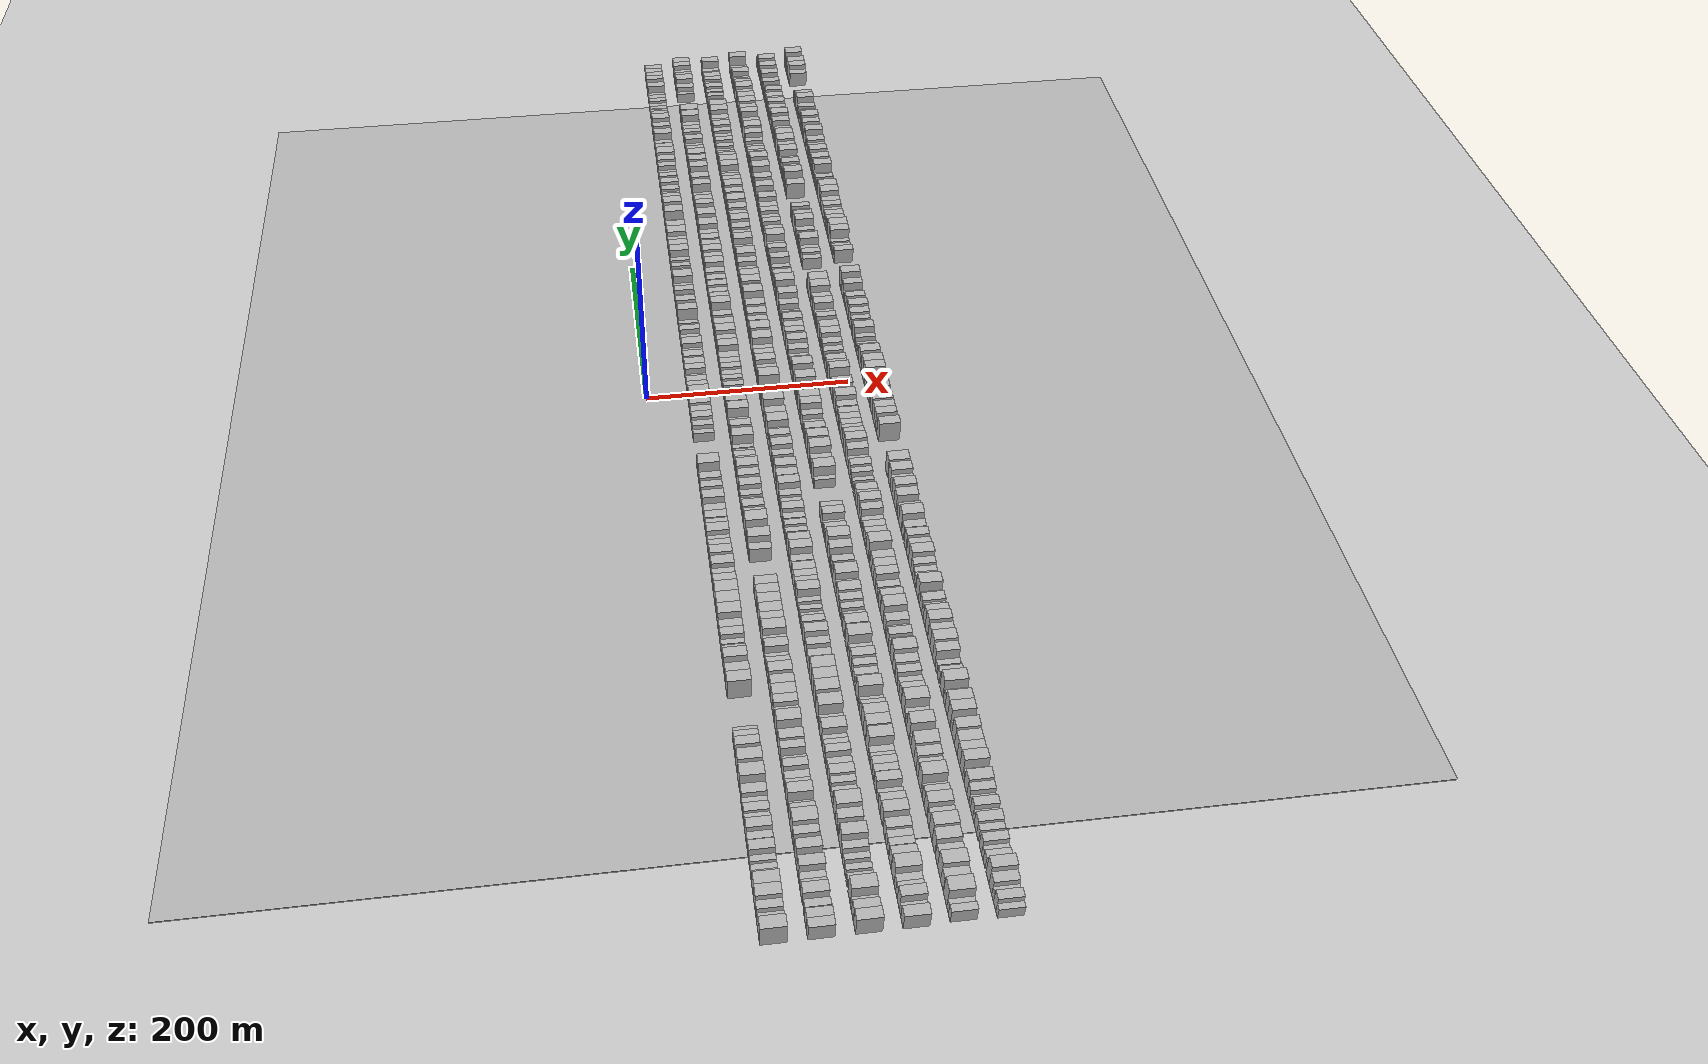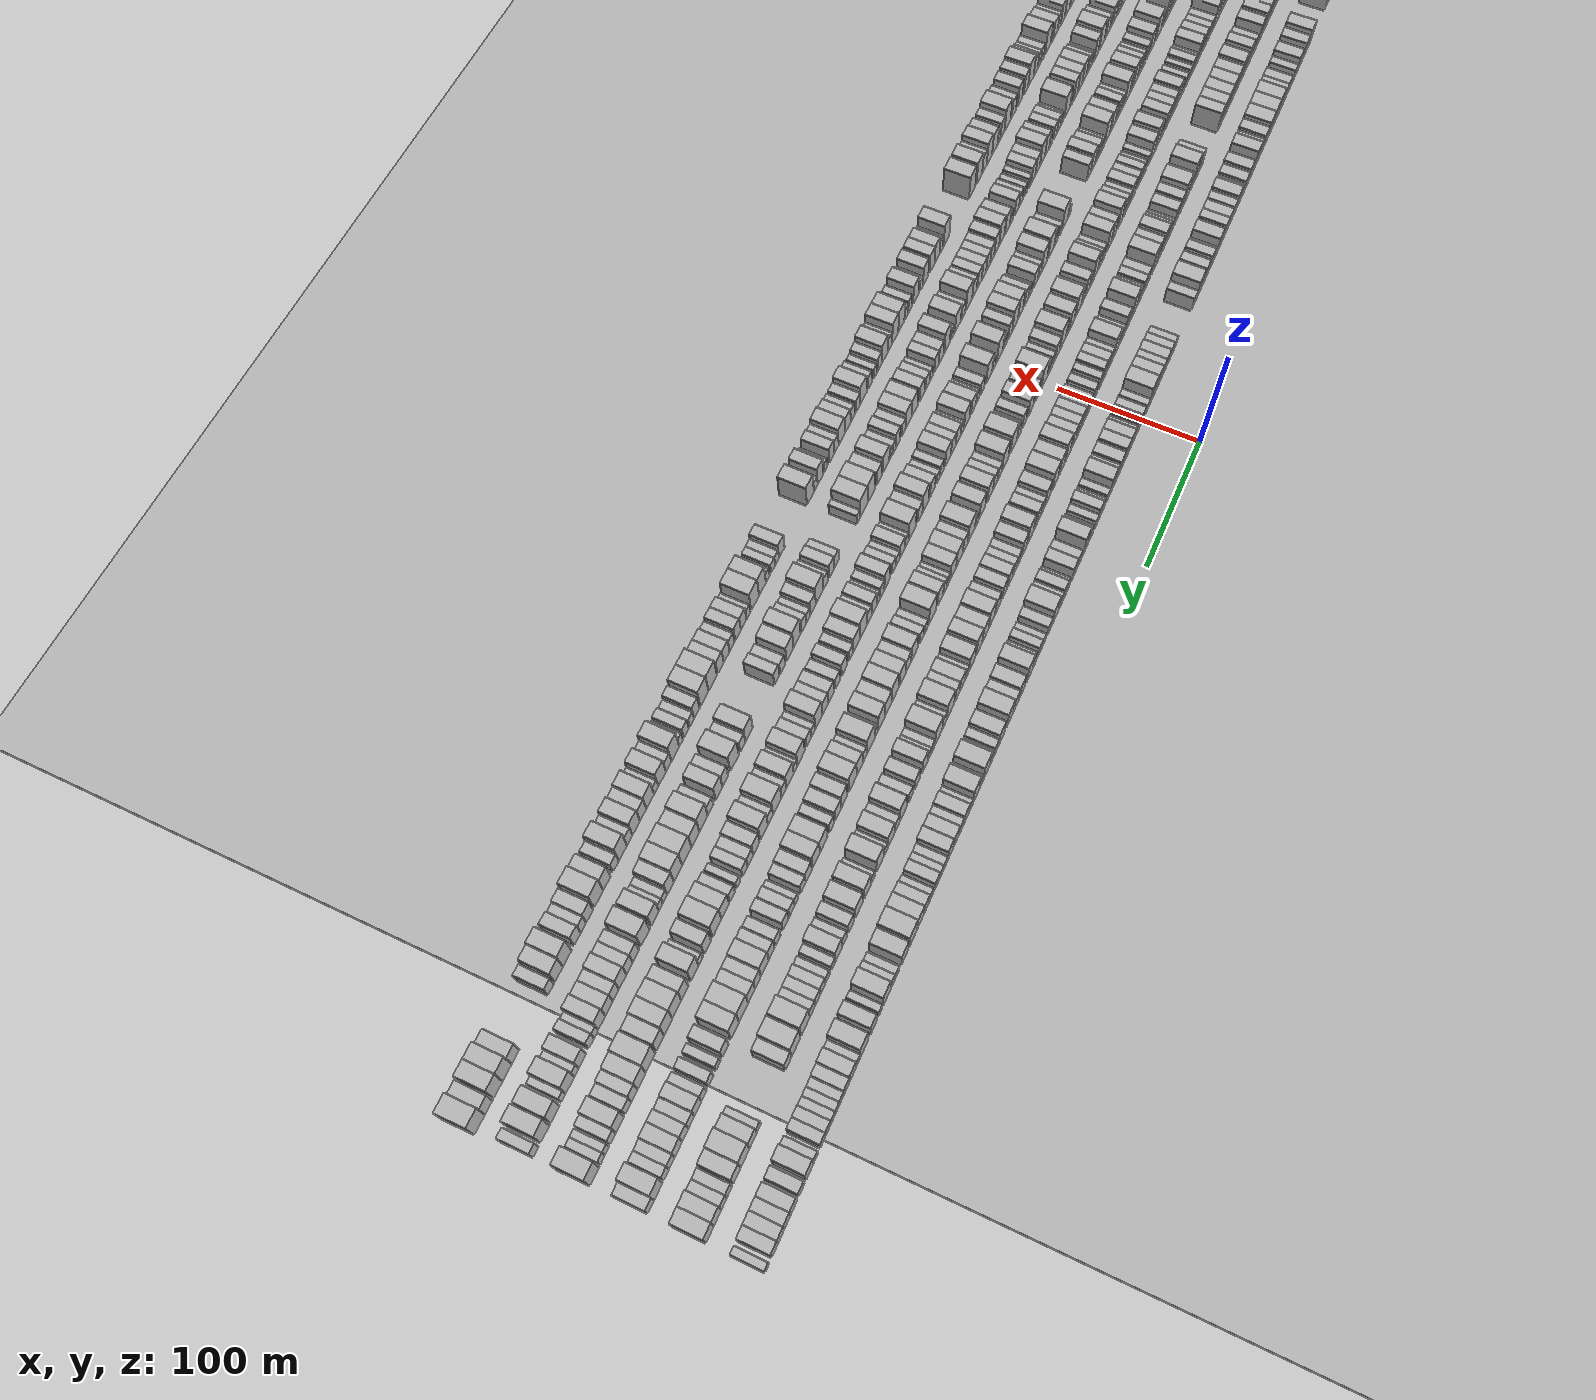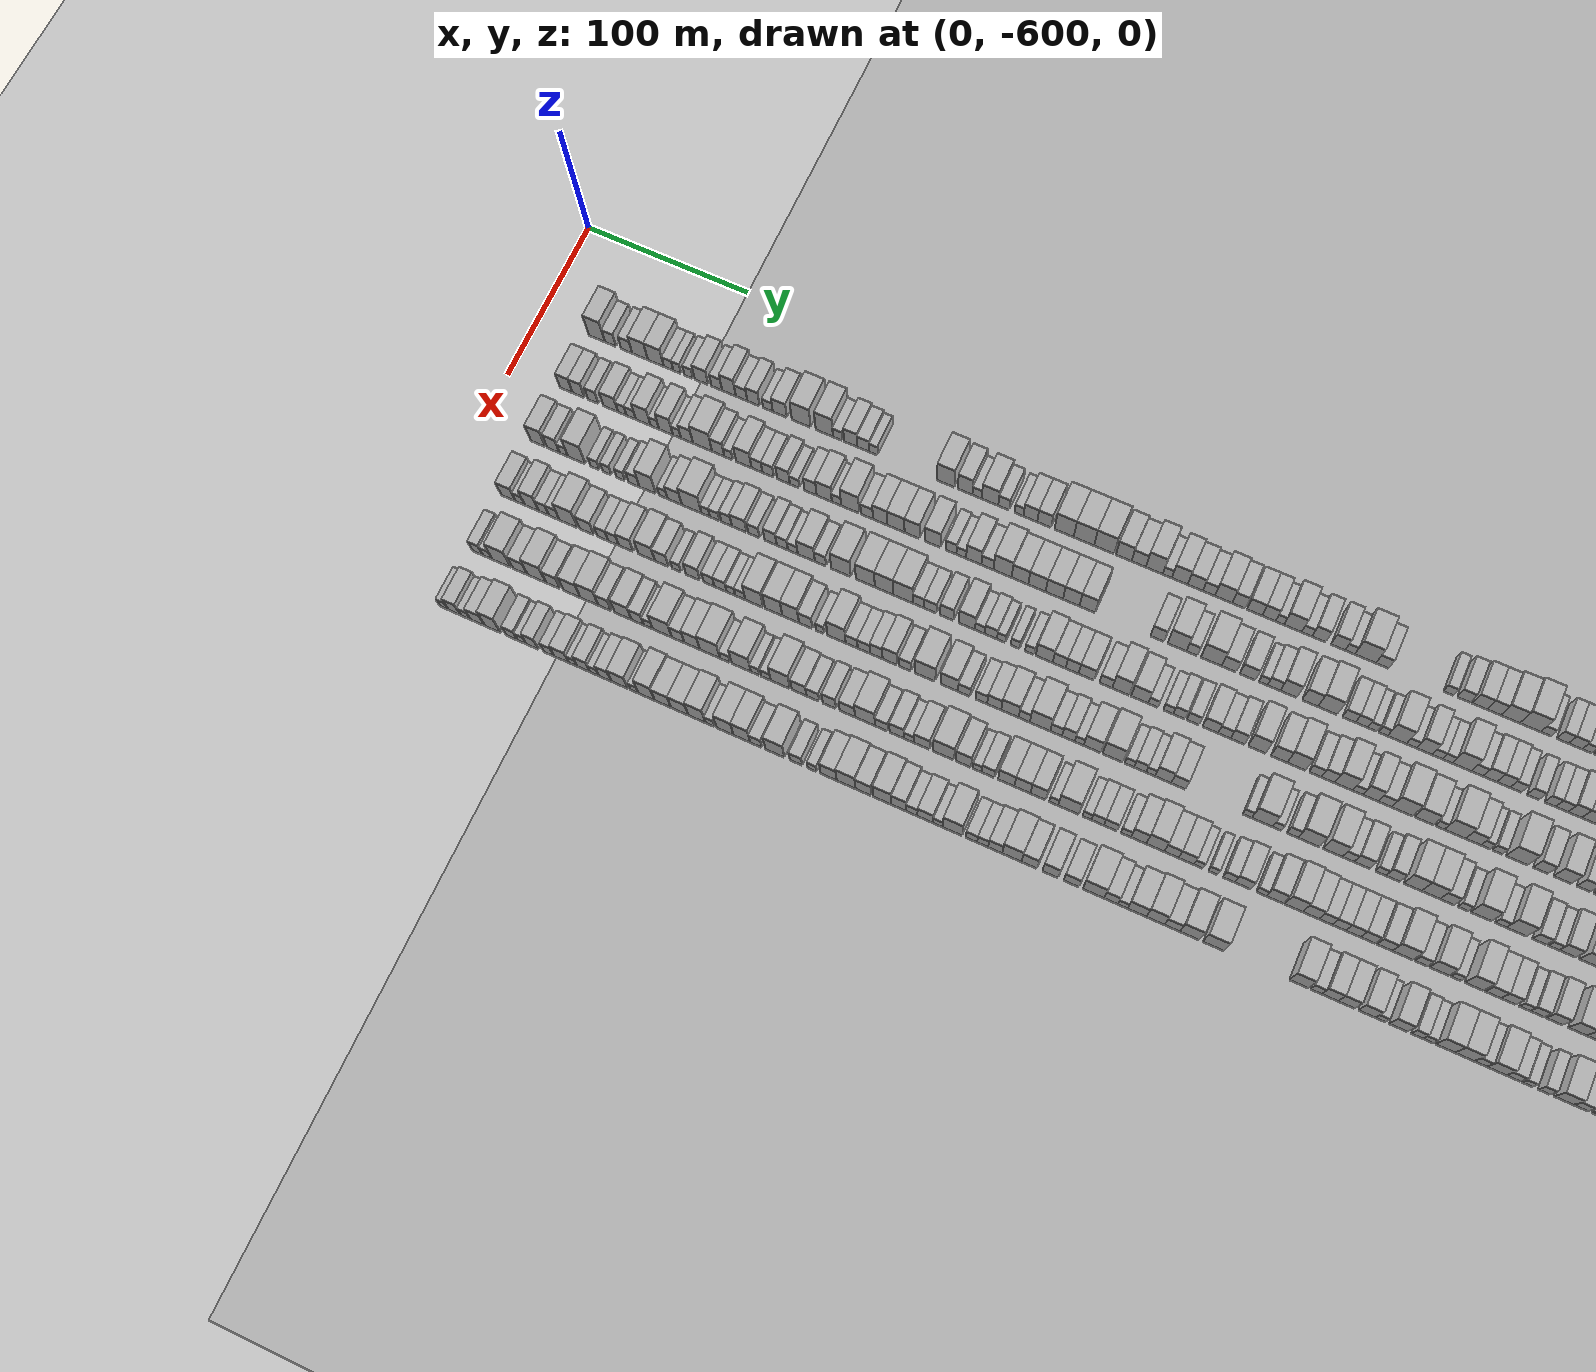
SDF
<?xml version="1.0" encoding="utf-8"?>

<sdf version="1.6">

   <world name="default">

      <gui fullscreen="0">

         <camera name="user_camera">

            <pose>-15 0 4.57585 0 0 0</pose>

            <view_controller>orbit</view_controller>

         </camera>

      </gui>

      <scene>

         <sky>

           <clouds>

             <speed>12</speed>

           </clouds>

         </sky>

         <ambient>0.4 0.4 0.4 1</ambient>

         <background>0.7 0.7 0.7 1</background>

         <shadows>1</shadows>

      </scene>

      <gravity>0 0 -9.8066</gravity>

      <magnetic_field>6e-06 2.3e-05 -4.2e-05</magnetic_field>

      <physics default="0" name="default_physics" type="ode">

         <ode>

            <solver>

               <type>quick</type>

               <iters>10</iters>

               <sor>1.0</sor>

               <use_dynamic_moi_rescaling>0</use_dynamic_moi_rescaling>

            </solver>

            <constraints>

               <cfm>0</cfm>

               <erp>0.2</erp>

               <contact_max_correcting_vel>100</contact_max_correcting_vel>

               <contact_surface_layer>0.001</contact_surface_layer>

            </constraints>

         </ode>

         <max_step_size>0.004</max_step_size>

         <real_time_factor>1</real_time_factor>

         <real_time_update_rate>250</real_time_update_rate>

      </physics>

      <light name="sun" type="directional">

         <cast_shadows>1</cast_shadows>

         <pose>0 0 10 0 0 0</pose>

         <diffuse>0.8 0.8 0.8 1</diffuse>

         <specular>0.2 0.2 0.2 1</specular>

         <attenuation>

            <range>1000</range>

            <constant>0.9</constant>

            <linear>0.01</linear>

            <quadratic>0.001</quadratic>

         </attenuation>

         <direction>-0.5 0.1 -0.9</direction>

      </light>

      <include>

         <name>ground_plane_1</name>

         <uri>model://HANNAS_ground_plane</uri>

         <pose>0 0 0  0 0 0</pose>

      </include>

      <include>

         <name>ground_plane_2</name>

         <uri>model://HANNAS_ground_plane</uri>

         <pose>100 0 0  0 0 0</pose>

      </include>

      <model name="building_1">

         <static>1</static>

         <pose frame="">50.0000 -564.9371 0 0.000000 0.000000 0.000000</pose>

         <link name="link">

            <pose frame="">0 0 12.00 0 0 0</pose>

            <collision name="collision">

               <geometry>

                  <box>

                     <size>20.0000 10.1258 24.0000</size>

                  </box>

               </geometry>

               <max_contacts>10</max_contacts>

               <surface>

                  <contact>

                     <ode/>

                  </contact>

                  <bounce/>

                  <friction>

                     <torsional>

                        <ode/>

                     </torsional>

                     <ode/>

                  </friction>

               </surface>

            </collision>

            <visual name="visual">

               <cast_shadows>0</cast_shadows>

               <geometry>

                  <box>

                     <size>20.0000 10.1258 24.0000</size>

                  </box>

               </geometry>

               <material>

                  <script>

                     <uri>model://HANNAS_wall/materials/scripts</uri>

                     <uri>model://HANNAS_wall/materials/textures</uri>

                     <name>vrc/HANNAS_wall</name>

                  </script>

               </material>

            </visual>

            <self_collide>0</self_collide>

            <enable_wind>0</enable_wind>

            <kinematic>0</kinematic>

         </link>

      </model>

      <model name="building_2">

         <static>1</static>

         <pose frame="">50.0000 -556.3736 0 0.000000 0.000000 0.000000</pose>

         <link name="link">

            <pose frame="">0 0 7.50 0 0 0</pose>

            <collision name="collision">

               <geometry>

                  <box>

                     <size>20.0000 7.0012 15.0000</size>

                  </box>

               </geometry>

               <max_contacts>10</max_contacts>

               <surface>

                  <contact>

                     <ode/>

                  </contact>

                  <bounce/>

                  <friction>

                     <torsional>

                        <ode/>

                     </torsional>

                     <ode/>

                  </friction>

               </surface>

            </collision>

            <visual name="visual">

               <cast_shadows>0</cast_shadows>

               <geometry>

                  <box>

                     <size>20.0000 7.0012 15.0000</size>

                  </box>

               </geometry>

               <material>

                  <script>

                     <uri>model://HANNAS_wall/materials/scripts</uri>

                     <uri>model://HANNAS_wall/materials/textures</uri>

                     <name>vrc/HANNAS_wall</name>

                  </script>

               </material>

            </visual>

            <self_collide>0</self_collide>

            <enable_wind>0</enable_wind>

            <kinematic>0</kinematic>

         </link>

      </model>

      <model name="building_3">

         <static>1</static>

         <pose frame="">50.0000 -546.3919 0 0.000000 0.000000 0.000000</pose>

         <link name="link">

            <pose frame="">0 0 7.50 0 0 0</pose>

            <collision name="collision">

               <geometry>

                  <box>

                     <size>20.0000 6.9620 15.0000</size>

                  </box>

               </geometry>

               <max_contacts>10</max_contacts>

               <surface>

                  <contact>

                     <ode/>

                  </contact>

                  <bounce/>

                  <friction>

                     <torsional>

                        <ode/>

                     </torsional>

                     <ode/>

                  </friction>

               </surface>

            </collision>

            <visual name="visual">

               <cast_shadows>0</cast_shadows>

               <geometry>

                  <box>

                     <size>20.0000 6.9620 15.0000</size>

                  </box>

               </geometry>

               <material>

                  <script>

                     <uri>model://HANNAS_wall/materials/scripts</uri>

                     <uri>model://HANNAS_wall/materials/textures</uri>

                     <name>vrc/HANNAS_wall</name>

                  </script>

               </material>

            </visual>

            <self_collide>0</self_collide>

            <enable_wind>0</enable_wind>

            <kinematic>0</kinematic>

         </link>

      </model>

      <model name="building_4">

         <static>1</static>

         <pose frame="">50.0000 -538.0496 0 0.000000 0.000000 0.000000</pose>

         <link name="link">

            <pose frame="">0 0 10.50 0 0 0</pose>

            <collision name="collision">

               <geometry>

                  <box>

                     <size>20.0000 9.7227 21.0000</size>

                  </box>

               </geometry>

               <max_contacts>10</max_contacts>

               <surface>

                  <contact>

                     <ode/>

                  </contact>

                  <bounce/>

                  <friction>

                     <torsional>

                        <ode/>

                     </torsional>

                     <ode/>

                  </friction>

               </surface>

            </collision>

            <visual name="visual">

               <cast_shadows>0</cast_shadows>

               <geometry>

                  <box>

                     <size>20.0000 9.7227 21.0000</size>

                  </box>

               </geometry>

               <material>

                  <script>

                     <uri>model://HANNAS_wall/materials/scripts</uri>

                     <uri>model://HANNAS_wall/materials/textures</uri>

                     <name>vrc/HANNAS_wall</name>

                  </script>

               </material>

            </visual>

            <self_collide>0</self_collide>

            <enable_wind>0</enable_wind>

            <kinematic>0</kinematic>

         </link>

      </model>

      <model name="building_5">

         <static>1</static>

         <pose frame="">50.0000 -528.2253 0 0.000000 0.000000 0.000000</pose>

         <link name="link">

            <pose frame="">0 0 10.50 0 0 0</pose>

            <collision name="collision">

               <geometry>

                  <box>

                     <size>20.0000 9.9258 21.0000</size>

                  </box>

               </geometry>

               <max_contacts>10</max_contacts>

               <surface>

                  <contact>

                     <ode/>

                  </contact>

                  <bounce/>

                  <friction>

                     <torsional>

                        <ode/>

                     </torsional>

                     <ode/>

                  </friction>

               </surface>

            </collision>

            <visual name="visual">

               <cast_shadows>0</cast_shadows>

               <geometry>

                  <box>

                     <size>20.0000 9.9258 21.0000</size>

                  </box>

               </geometry>

               <material>

                  <script>

                     <uri>model://HANNAS_wall/materials/scripts</uri>

                     <uri>model://HANNAS_wall/materials/textures</uri>

                     <name>vrc/HANNAS_wall</name>

                  </script>

               </material>

            </visual>

            <self_collide>0</self_collide>

            <enable_wind>0</enable_wind>

            <kinematic>0</kinematic>

         </link>

      </model>

      <model name="building_6">

         <static>1</static>

         <pose frame="">50.0000 -520.3430 0 0.000000 0.000000 0.000000</pose>

         <link name="link">

            <pose frame="">0 0 6.00 0 0 0</pose>

            <collision name="collision">

               <geometry>

                  <box>

                     <size>20.0000 5.8388 12.0000</size>

                  </box>

               </geometry>

               <max_contacts>10</max_contacts>

               <surface>

                  <contact>

                     <ode/>

                  </contact>

                  <bounce/>

                  <friction>

                     <torsional>

                        <ode/>

                     </torsional>

                     <ode/>

                  </friction>

               </surface>

            </collision>

            <visual name="visual">

               <cast_shadows>0</cast_shadows>

               <geometry>

                  <box>

                     <size>20.0000 5.8388 12.0000</size>

                  </box>

               </geometry>

               <material>

                  <script>

                     <uri>model://HANNAS_wall/materials/scripts</uri>

                     <uri>model://HANNAS_wall/materials/textures</uri>

                     <name>vrc/HANNAS_wall</name>

                  </script>

               </material>

            </visual>

            <self_collide>0</self_collide>

            <enable_wind>0</enable_wind>

            <kinematic>0</kinematic>

         </link>

      </model>

      <model name="building_7">

         <static>1</static>

         <pose frame="">50.0000 -514.9900 0 0.000000 0.000000 0.000000</pose>

         <link name="link">

            <pose frame="">0 0 6.00 0 0 0</pose>

            <collision name="collision">

               <geometry>

                  <box>

                     <size>20.0000 4.8670 12.0000</size>

                  </box>

               </geometry>

               <max_contacts>10</max_contacts>

               <surface>

                  <contact>

                     <ode/>

                  </contact>

                  <bounce/>

                  <friction>

                     <torsional>

                        <ode/>

                     </torsional>

                     <ode/>

                  </friction>

               </surface>

            </collision>

            <visual name="visual">

               <cast_shadows>0</cast_shadows>

               <geometry>

                  <box>

                     <size>20.0000 4.8670 12.0000</size>

                  </box>

               </geometry>

               <material>

                  <script>

                     <uri>model://HANNAS_wall/materials/scripts</uri>

                     <uri>model://HANNAS_wall/materials/textures</uri>

                     <name>vrc/HANNAS_wall</name>

                  </script>

               </material>

            </visual>

            <self_collide>0</self_collide>

            <enable_wind>0</enable_wind>

            <kinematic>0</kinematic>

         </link>

      </model>

      <model name="building_8">

         <static>1</static>

         <pose frame="">50.0000 -507.8897 0 0.000000 0.000000 0.000000</pose>

         <link name="link">

            <pose frame="">0 0 6.00 0 0 0</pose>

            <collision name="collision">

               <geometry>

                  <box>

                     <size>20.0000 5.3337 12.0000</size>

                  </box>

               </geometry>

               <max_contacts>10</max_contacts>

               <surface>

                  <contact>

                     <ode/>

                  </contact>

                  <bounce/>

                  <friction>

                     <torsional>

                        <ode/>

                     </torsional>

                     <ode/>

                  </friction>

               </surface>

            </collision>

            <visual name="visual">

               <cast_shadows>0</cast_shadows>

               <geometry>

                  <box>

                     <size>20.0000 5.3337 12.0000</size>

                  </box>

               </geometry>

               <material>

                  <script>

                     <uri>model://HANNAS_wall/materials/scripts</uri>

                     <uri>model://HANNAS_wall/materials/textures</uri>

                     <name>vrc/HANNAS_wall</name>

                  </script>

               </material>

            </visual>

            <self_collide>0</self_collide>

            <enable_wind>0</enable_wind>

            <kinematic>0</kinematic>

         </link>

      </model>

      <model name="building_9">

         <static>1</static>

         <pose frame="">50.0000 -500.0174 0 0.000000 0.000000 0.000000</pose>

         <link name="link">

            <pose frame="">0 0 9.00 0 0 0</pose>

            <collision name="collision">

               <geometry>

                  <box>

                     <size>20.0000 8.4110 18.0000</size>

                  </box>

               </geometry>

               <max_contacts>10</max_contacts>

               <surface>

                  <contact>

                     <ode/>

                  </contact>

                  <bounce/>

                  <friction>

                     <torsional>

                        <ode/>

                     </torsional>

                     <ode/>

                  </friction>

               </surface>

            </collision>

            <visual name="visual">

               <cast_shadows>0</cast_shadows>

               <geometry>

                  <box>

                     <size>20.0000 8.4110 18.0000</size>

                  </box>

               </geometry>

               <material>

                  <script>

                     <uri>model://HANNAS_wall/materials/scripts</uri>

                     <uri>model://HANNAS_wall/materials/textures</uri>

                     <name>vrc/HANNAS_wall</name>

                  </script>

               </material>

            </visual>

            <self_collide>0</self_collide>

            <enable_wind>0</enable_wind>

            <kinematic>0</kinematic>

         </link>

      </model>

      <model name="building_10">

         <static>1</static>

         <pose frame="">50.0000 -490.5648 0 0.000000 0.000000 0.000000</pose>

         <link name="link">

            <pose frame="">0 0 7.50 0 0 0</pose>

            <collision name="collision">

               <geometry>

                  <box>

                     <size>20.0000 6.4942 15.0000</size>

                  </box>

               </geometry>

               <max_contacts>10</max_contacts>

               <surface>

                  <contact>

                     <ode/>

                  </contact>

                  <bounce/>

                  <friction>

                     <torsional>

                        <ode/>

                     </torsional>

                     <ode/>

                  </friction>

               </surface>

            </collision>

            <visual name="visual">

               <cast_shadows>0</cast_shadows>

               <geometry>

                  <box>

                     <size>20.0000 6.4942 15.0000</size>

                  </box>

               </geometry>

               <material>

                  <script>

                     <uri>model://HANNAS_wall/materials/scripts</uri>

                     <uri>model://HANNAS_wall/materials/textures</uri>

                     <name>vrc/HANNAS_wall</name>

                  </script>

               </material>

            </visual>

            <self_collide>0</self_collide>

            <enable_wind>0</enable_wind>

            <kinematic>0</kinematic>

         </link>

      </model>

      <model name="building_11">

         <static>1</static>

         <pose frame="">50.0000 -483.0995 0 0.000000 0.000000 0.000000</pose>

         <link name="link">

            <pose frame="">0 0 10.50 0 0 0</pose>

            <collision name="collision">

               <geometry>

                  <box>

                     <size>20.0000 8.4364 21.0000</size>

                  </box>

               </geometry>

               <max_contacts>10</max_contacts>

               <surface>

                  <contact>

                     <ode/>

                  </contact>

                  <bounce/>

                  <friction>

                     <torsional>

                        <ode/>

                     </torsional>

                     <ode/>

                  </friction>

               </surface>

            </collision>

            <visual name="visual">

               <cast_shadows>0</cast_shadows>

               <geometry>

                  <box>

                     <size>20.0000 8.4364 21.0000</size>

                  </box>

               </geometry>

               <material>

                  <script>

                     <uri>model://HANNAS_wall/materials/scripts</uri>

                     <uri>model://HANNAS_wall/materials/textures</uri>

                     <name>vrc/HANNAS_wall</name>

                  </script>

               </material>

            </visual>

            <self_collide>0</self_collide>

            <enable_wind>0</enable_wind>

            <kinematic>0</kinematic>

         </link>

      </model>

      <model name="building_12">

         <static>1</static>

         <pose frame="">50.0000 -475.3370 0 0.000000 0.000000 0.000000</pose>

         <link name="link">

            <pose frame="">0 0 7.50 0 0 0</pose>

            <collision name="collision">

               <geometry>

                  <box>

                     <size>20.0000 7.0888 15.0000</size>

                  </box>

               </geometry>

               <max_contacts>10</max_contacts>

               <surface>

                  <contact>

                     <ode/>

                  </contact>

                  <bounce/>

                  <friction>

                     <torsional>

                        <ode/>

                     </torsional>

                     <ode/>

                  </friction>

               </surface>

            </collision>

            <visual name="visual">

               <cast_shadows>0</cast_shadows>

               <geometry>

                  <box>

                     <size>20.0000 7.0888 15.0000</size>

                  </box>

               </geometry>

               <material>

                  <script>

                     <uri>model://HANNAS_wall/materials/scripts</uri>

                     <uri>model://HANNAS_wall/materials/textures</uri>

                     <name>vrc/HANNAS_wall</name>

                  </script>

               </material>

            </visual>

            <self_collide>0</self_collide>

            <enable_wind>0</enable_wind>

            <kinematic>0</kinematic>

         </link>

      </model>

      <model name="building_13">

         <static>1</static>

         <pose frame="">50.0000 -468.0151 0 0.000000 0.000000 0.000000</pose>

         <link name="link">

            <pose frame="">0 0 9.00 0 0 0</pose>

            <collision name="collision">

               <geometry>

                  <box>

                     <size>20.0000 7.5550 18.0000</size>

                  </box>

               </geometry>

               <max_contacts>10</max_contacts>

               <surface>

                  <contact>

                     <ode/>

                  </contact>

                  <bounce/>

                  <friction>

                     <torsional>

                        <ode/>

                     </torsional>

                     <ode/>

                  </friction>

               </surface>

            </collision>

            <visual name="visual">

               <cast_shadows>0</cast_shadows>

               <geometry>

                  <box>

                     <size>20.0000 7.5550 18.0000</size>

                  </box>

               </geometry>

               <material>

                  <script>

                     <uri>model://HANNAS_wall/materials/scripts</uri>

                     <uri>model://HANNAS_wall/materials/textures</uri>

                     <name>vrc/HANNAS_wall</name>

                  </script>

               </material>

            </visual>

            <self_collide>0</self_collide>

            <enable_wind>0</enable_wind>

            <kinematic>0</kinematic>

         </link>

      </model>

      <model name="building_14">

         <static>1</static>

         <pose frame="">50.0000 -459.2626 0 0.000000 0.000000 0.000000</pose>

         <link name="link">

            <pose frame="">0 0 6.00 0 0 0</pose>

            <collision name="collision">

               <geometry>

                  <box>

                     <size>20.0000 5.9500 12.0000</size>

                  </box>

               </geometry>

               <max_contacts>10</max_contacts>

               <surface>

                  <contact>

                     <ode/>

                  </contact>

                  <bounce/>

                  <friction>

                     <torsional>

                        <ode/>

                     </torsional>

                     <ode/>

                  </friction>

               </surface>

            </collision>

            <visual name="visual">

               <cast_shadows>0</cast_shadows>

               <geometry>

                  <box>

                     <size>20.0000 5.9500 12.0000</size>

                  </box>

               </geometry>

               <material>

                  <script>

                     <uri>model://HANNAS_wall/materials/scripts</uri>

                     <uri>model://HANNAS_wall/materials/textures</uri>

                     <name>vrc/HANNAS_wall</name>

                  </script>

               </material>

            </visual>

            <self_collide>0</self_collide>

            <enable_wind>0</enable_wind>

            <kinematic>0</kinematic>

         </link>

      </model>

      <model name="building_15">

         <static>1</static>

         <pose frame="">50.0000 -451.9776 0 0.000000 0.000000 0.000000</pose>

         <link name="link">

            <pose frame="">0 0 9.00 0 0 0</pose>

            <collision name="collision">

               <geometry>

                  <box>

                     <size>20.0000 8.6199 18.0000</size>

                  </box>

               </geometry>

               <max_contacts>10</max_contacts>

               <surface>

                  <contact>

                     <ode/>

                  </contact>

                  <bounce/>

                  <friction>

                     <torsional>

                        <ode/>

                     </torsional>

                     <ode/>

                  </friction>

               </surface>

            </collision>

            <visual name="visual">

               <cast_shadows>0</cast_shadows>

               <geometry>

                  <box>

                     <size>20.0000 8.6199 18.0000</size>

                  </box>

               </geometry>

               <material>

                  <script>

                     <uri>model://HANNAS_wall/materials/scripts</uri>

                     <uri>model://HANNAS_wall/materials/textures</uri>

                     <name>vrc/HANNAS_wall</name>

                  </script>

               </material>

            </visual>

            <self_collide>0</self_collide>

            <enable_wind>0</enable_wind>

            <kinematic>0</kinematic>

         </link>

      </model>

      <model name="building_16">

         <static>1</static>

         <pose frame="">50.0000 -438.9100 0 0.000000 0.000000 0.000000</pose>

         <link name="link">

            <pose frame="">0 0 12.00 0 0 0</pose>

            <collision name="collision">

               <geometry>

                  <box>

                     <size>20.0000 11.5154 24.0000</size>

                  </box>

               </geometry>

               <max_contacts>10</max_contacts>

               <surface>

                  <contact>

                     <ode/>

                  </contact>

                  <bounce/>

                  <friction>

                     <torsional>

                        <ode/>

                     </torsional>

                     <ode/>

                  </friction>

               </surface>

            </collision>

            <visual name="visual">

               <cast_shadows>0</cast_shadows>

               <geometry>

                  <box>

                     <size>20.0000 11.5154 24.0000</size>

                  </box>

               </geometry>

               <material>

                  <script>

                     <uri>model://HANNAS_wall/materials/scripts</uri>

                     <uri>model://HANNAS_wall/materials/textures</uri>

                     <name>vrc/HANNAS_wall</name>

                  </script>

               </material>

            </visual>

            <self_collide>0</self_collide>

            <enable_wind>0</enable_wind>

            <kinematic>0</kinematic>

         </link>

      </model>

      <model name="building_17">

         <static>1</static>

         <pose frame="">50.0000 -424.9383 0 0.000000 0.000000 0.000000</pose>

         <link name="link">

            <pose frame="">0 0 12.00 0 0 0</pose>

            <collision name="collision">

               <geometry>

                  <box>

                     <size>20.0000 10.4280 24.0000</size>

                  </box>

               </geometry>

               <max_contacts>10</max_contacts>

               <surface>

                  <contact>

                     <ode/>

                  </contact>

                  <bounce/>

                  <friction>

                     <torsional>

                        <ode/>

                     </torsional>

                     <ode/>

                  </friction>

               </surface>

            </collision>

            <visual name="visual">

               <cast_shadows>0</cast_shadows>

               <geometry>

                  <box>

                     <size>20.0000 10.4280 24.0000</size>

                  </box>

               </geometry>

               <material>

                  <script>

                     <uri>model://HANNAS_wall/materials/scripts</uri>

                     <uri>model://HANNAS_wall/materials/textures</uri>

                     <name>vrc/HANNAS_wall</name>

                  </script>

               </material>

            </visual>

            <self_collide>0</self_collide>

            <enable_wind>0</enable_wind>

            <kinematic>0</kinematic>

         </link>

      </model>

      <model name="building_18">

         <static>1</static>

         <pose frame="">50.0000 -416.8632 0 0.000000 0.000000 0.000000</pose>

         <link name="link">

            <pose frame="">0 0 6.00 0 0 0</pose>

            <collision name="collision">

               <geometry>

                  <box>

                     <size>20.0000 5.7221 12.0000</size>

                  </box>

               </geometry>

               <max_contacts>10</max_contacts>

               <surface>

                  <contact>

                     <ode/>

                  </contact>

                  <bounce/>

                  <friction>

                     <torsional>

                        <ode/>

                     </torsional>

                     <ode/>

                  </friction>

               </surface>

            </collision>

            <visual name="visual">

               <cast_shadows>0</cast_shadows>

               <geometry>

                  <box>

                     <size>20.0000 5.7221 12.0000</size>

                  </box>

               </geometry>

               <material>

                  <script>

                     <uri>model://HANNAS_wall/materials/scripts</uri>

                     <uri>model://HANNAS_wall/materials/textures</uri>

                     <name>vrc/HANNAS_wall</name>

                  </script>

               </material>

            </visual>

            <self_collide>0</self_collide>

            <enable_wind>0</enable_wind>

            <kinematic>0</kinematic>

         </link>

      </model>

      <model name="building_19">

         <static>1</static>

         <pose frame="">50.0000 -408.9586 0 0.000000 0.000000 0.000000</pose>

         <link name="link">

            <pose frame="">0 0 9.00 0 0 0</pose>

            <collision name="collision">

               <geometry>

                  <box>

                     <size>20.0000 8.0872 18.0000</size>

                  </box>

               </geometry>

               <max_contacts>10</max_contacts>

               <surface>

                  <contact>

                     <ode/>

                  </contact>

                  <bounce/>

                  <friction>

                     <torsional>

                        <ode/>

                     </torsional>

                     <ode/>

                  </friction>

               </surface>

            </collision>

            <visual name="visual">

               <cast_shadows>0</cast_shadows>

               <geometry>

                  <box>

                     <size>20.0000 8.0872 18.0000</size>

                  </box>

               </geometry>

               <material>

                  <script>

                     <uri>model://HANNAS_wall/materials/scripts</uri>

                     <uri>model://HANNAS_wall/materials/textures</uri>

                     <name>vrc/HANNAS_wall</name>

                  </script>

               </material>

            </visual>

            <self_collide>0</self_collide>

            <enable_wind>0</enable_wind>

            <kinematic>0</kinematic>

         </link>

      </model>

      <model name="building_20">

         <static>1</static>

         <pose frame="">50.0000 -401.2958 0 0.000000 0.000000 0.000000</pose>

         <link name="link">

            <pose frame="">0 0 7.50 0 0 0</pose>

            <collision name="collision">

               <geometry>

                  <box>

                     <size>20.0000 7.2384 15.0000</size>

                  </box>

               </geometry>

               <max_contacts>10</max_contacts>

               <surface>

                  <contact>

                     <ode/>

                  </contact>

                  <bounce/>

                  <friction>

                     <torsional>

                        <ode/>

                     </torsional>

                     <ode/>

                  </friction>

               </surface>

            </collision>

            <visual name="visual">

               <cast_shadows>0</cast_shadows>

               <geometry>

                  <box>

                     <size>20.0000 7.2384 15.0000</size>

                  </box>

               </geometry>

               <material>

                  <script>

                     <uri>model://HANNAS_wall/materials/scripts</uri>

                     <uri>model://HANNAS_wall/materials/textures</uri>

                     <name>vrc/HANNAS_wall</name>

                  </script>

               </material>

            </visual>

            <self_collide>0</self_collide>

            <enable_wind>0</enable_wind>

            <kinematic>0</kinematic>

         </link>

      </model>

      <model name="building_21">

         <static>1</static>

         <pose frame="">50.0000 -395.1728 0 0.000000 0.000000 0.000000</pose>

         <link name="link">

            <pose frame="">0 0 6.00 0 0 0</pose>

            <collision name="collision">

               <geometry>

                  <box>

                     <size>20.0000 5.0076 12.0000</size>

                  </box>

               </geometry>

               <max_contacts>10</max_contacts>

               <surface>

                  <contact>

                     <ode/>

                  </contact>

                  <bounce/>

                  <friction>

                     <torsional>

                        <ode/>

                     </torsional>

                     <ode/>

                  </friction>

               </surface>

            </collision>

            <visual name="visual">

               <cast_shadows>0</cast_shadows>

               <geometry>

                  <box>

                     <size>20.0000 5.0076 12.0000</size>

                  </box>

               </geometry>

               <material>

                  <script>

                     <uri>model://HANNAS_wall/materials/scripts</uri>

                     <uri>model://HANNAS_wall/materials/textures</uri>

                     <name>vrc/HANNAS_wall</name>

                  </script>

               </material>

            </visual>

            <self_collide>0</self_collide>

            <enable_wind>0</enable_wind>

            <kinematic>0</kinematic>

         </link>

      </model>

      <model name="building_22">

         <static>1</static>

         <pose frame="">50.0000 -352.0077 0 0.000000 0.000000 0.000000</pose>

         <link name="link">

            <pose frame="">0 0 12.00 0 0 0</pose>

            <collision name="collision">

               <geometry>

                  <box>

                     <size>20.0000 10.4409 24.0000</size>

                  </box>

               </geometry>

               <max_contacts>10</max_contacts>

               <surface>

                  <contact>

                     <ode/>

                  </contact>

                  <bounce/>

                  <friction>

                     <torsional>

                        <ode/>

                     </torsional>

                     <ode/>

                  </friction>

               </surface>

            </collision>

            <visual name="visual">

               <cast_shadows>0</cast_shadows>

               <geometry>

                  <box>

                     <size>20.0000 10.4409 24.0000</size>

                  </box>

               </geometry>

               <material>

                  <script>

                     <uri>model://HANNAS_wall/materials/scripts</uri>

                     <uri>model://HANNAS_wall/materials/textures</uri>

                     <name>vrc/HANNAS_wall</name>

                  </script>

               </material>

            </visual>

            <self_collide>0</self_collide>

            <enable_wind>0</enable_wind>

            <kinematic>0</kinematic>

         </link>

      </model>

      <model name="building_23">

         <static>1</static>

         <pose frame="">50.0000 -340.4695 0 0.000000 0.000000 0.000000</pose>

         <link name="link">

            <pose frame="">0 0 10.50 0 0 0</pose>

            <collision name="collision">

               <geometry>

                  <box>

                     <size>20.0000 8.6354 21.0000</size>

                  </box>

               </geometry>

               <max_contacts>10</max_contacts>

               <surface>

                  <contact>

                     <ode/>

                  </contact>

                  <bounce/>

                  <friction>

                     <torsional>

                        <ode/>

                     </torsional>

                     <ode/>

                  </friction>

               </surface>

            </collision>

            <visual name="visual">

               <cast_shadows>0</cast_shadows>

               <geometry>

                  <box>

                     <size>20.0000 8.6354 21.0000</size>

                  </box>

               </geometry>

               <material>

                  <script>

                     <uri>model://HANNAS_wall/materials/scripts</uri>

                     <uri>model://HANNAS_wall/materials/textures</uri>

                     <name>vrc/HANNAS_wall</name>

                  </script>

               </material>

            </visual>

            <self_collide>0</self_collide>

            <enable_wind>0</enable_wind>

            <kinematic>0</kinematic>

         </link>

      </model>

      <model name="building_24">

         <static>1</static>

         <pose frame="">50.0000 -333.3850 0 0.000000 0.000000 0.000000</pose>

         <link name="link">

            <pose frame="">0 0 6.00 0 0 0</pose>

            <collision name="collision">

               <geometry>

                  <box>

                     <size>20.0000 5.5336 12.0000</size>

                  </box>

               </geometry>

               <max_contacts>10</max_contacts>

               <surface>

                  <contact>

                     <ode/>

                  </contact>

                  <bounce/>

                  <friction>

                     <torsional>

                        <ode/>

                     </torsional>

                     <ode/>

                  </friction>

               </surface>

            </collision>

            <visual name="visual">

               <cast_shadows>0</cast_shadows>

               <geometry>

                  <box>

                     <size>20.0000 5.5336 12.0000</size>

                  </box>

               </geometry>

               <material>

                  <script>

                     <uri>model://HANNAS_wall/materials/scripts</uri>

                     <uri>model://HANNAS_wall/materials/textures</uri>

                     <name>vrc/HANNAS_wall</name>

                  </script>

               </material>

            </visual>

            <self_collide>0</self_collide>

            <enable_wind>0</enable_wind>

            <kinematic>0</kinematic>

         </link>

      </model>

      <model name="building_25">

         <static>1</static>

         <pose frame="">50.0000 -325.6916 0 0.000000 0.000000 0.000000</pose>

         <link name="link">

            <pose frame="">0 0 10.50 0 0 0</pose>

            <collision name="collision">

               <geometry>

                  <box>

                     <size>20.0000 9.8531 21.0000</size>

                  </box>

               </geometry>

               <max_contacts>10</max_contacts>

               <surface>

                  <contact>

                     <ode/>

                  </contact>

                  <bounce/>

                  <friction>

                     <torsional>

                        <ode/>

                     </torsional>

                     <ode/>

                  </friction>

               </surface>

            </collision>

            <visual name="visual">

               <cast_shadows>0</cast_shadows>

               <geometry>

                  <box>

                     <size>20.0000 9.8531 21.0000</size>

                  </box>

               </geometry>

               <material>

                  <script>

                     <uri>model://HANNAS_wall/materials/scripts</uri>

                     <uri>model://HANNAS_wall/materials/textures</uri>

                     <name>vrc/HANNAS_wall</name>

                  </script>

               </material>

            </visual>

            <self_collide>0</self_collide>

            <enable_wind>0</enable_wind>

            <kinematic>0</kinematic>

         </link>

      </model>

      <model name="building_26">

         <static>1</static>

         <pose frame="">50.0000 -317.4482 0 0.000000 0.000000 0.000000</pose>

         <link name="link">

            <pose frame="">0 0 7.50 0 0 0</pose>

            <collision name="collision">

               <geometry>

                  <box>

                     <size>20.0000 6.6337 15.0000</size>

                  </box>

               </geometry>

               <max_contacts>10</max_contacts>

               <surface>

                  <contact>

                     <ode/>

                  </contact>

                  <bounce/>

                  <friction>

                     <torsional>

                        <ode/>

                     </torsional>

                     <ode/>

                  </friction>

               </surface>

            </collision>

            <visual name="visual">

               <cast_shadows>0</cast_shadows>

               <geometry>

                  <box>

                     <size>20.0000 6.6337 15.0000</size>

                  </box>

               </geometry>

               <material>

                  <script>

                     <uri>model://HANNAS_wall/materials/scripts</uri>

                     <uri>model://HANNAS_wall/materials/textures</uri>

                     <name>vrc/HANNAS_wall</name>

                  </script>

               </material>

            </visual>

            <self_collide>0</self_collide>

            <enable_wind>0</enable_wind>

            <kinematic>0</kinematic>

         </link>

      </model>

      <model name="building_27">

         <static>1</static>

         <pose frame="">50.0000 -308.5214 0 0.000000 0.000000 0.000000</pose>

         <link name="link">

            <pose frame="">0 0 6.00 0 0 0</pose>

            <collision name="collision">

               <geometry>

                  <box>

                     <size>20.0000 5.2200 12.0000</size>

                  </box>

               </geometry>

               <max_contacts>10</max_contacts>

               <surface>

                  <contact>

                     <ode/>

                  </contact>

                  <bounce/>

                  <friction>

                     <torsional>

                        <ode/>

                     </torsional>

                     <ode/>

                  </friction>

               </surface>

            </collision>

            <visual name="visual">

               <cast_shadows>0</cast_shadows>

               <geometry>

                  <box>

                     <size>20.0000 5.2200 12.0000</size>

                  </box>

               </geometry>

               <material>

                  <script>

                     <uri>model://HANNAS_wall/materials/scripts</uri>

                     <uri>model://HANNAS_wall/materials/textures</uri>

                     <name>vrc/HANNAS_wall</name>

                  </script>

               </material>

            </visual>

            <self_collide>0</self_collide>

            <enable_wind>0</enable_wind>

            <kinematic>0</kinematic>

         </link>

      </model>

      <model name="building_28">

         <static>1</static>

         <pose frame="">50.0000 -301.8301 0 0.000000 0.000000 0.000000</pose>

         <link name="link">

            <pose frame="">0 0 9.00 0 0 0</pose>

            <collision name="collision">

               <geometry>

                  <box>

                     <size>20.0000 8.1626 18.0000</size>

                  </box>

               </geometry>

               <max_contacts>10</max_contacts>

               <surface>

                  <contact>

                     <ode/>

                  </contact>

                  <bounce/>

                  <friction>

                     <torsional>

                        <ode/>

                     </torsional>

                     <ode/>

                  </friction>

               </surface>

            </collision>

            <visual name="visual">

               <cast_shadows>0</cast_shadows>

               <geometry>

                  <box>

                     <size>20.0000 8.1626 18.0000</size>

                  </box>

               </geometry>

               <material>

                  <script>

                     <uri>model://HANNAS_wall/materials/scripts</uri>

                     <uri>model://HANNAS_wall/materials/textures</uri>

                     <name>vrc/HANNAS_wall</name>

                  </script>

               </material>

            </visual>

            <self_collide>0</self_collide>

            <enable_wind>0</enable_wind>

            <kinematic>0</kinematic>

         </link>

      </model>

      <model name="building_29">

         <static>1</static>

         <pose frame="">50.0000 -293.6463 0 0.000000 0.000000 0.000000</pose>

         <link name="link">

            <pose frame="">0 0 9.00 0 0 0</pose>

            <collision name="collision">

               <geometry>

                  <box>

                     <size>20.0000 8.2050 18.0000</size>

                  </box>

               </geometry>

               <max_contacts>10</max_contacts>

               <surface>

                  <contact>

                     <ode/>

                  </contact>

                  <bounce/>

                  <friction>

                     <torsional>

                        <ode/>

                     </torsional>

                     <ode/>

                  </friction>

               </surface>

            </collision>

            <visual name="visual">

               <cast_shadows>0</cast_shadows>

               <geometry>

                  <box>

                     <size>20.0000 8.2050 18.0000</size>

                  </box>

               </geometry>

               <material>

                  <script>

                     <uri>model://HANNAS_wall/materials/scripts</uri>

                     <uri>model://HANNAS_wall/materials/textures</uri>

                     <name>vrc/HANNAS_wall</name>

                  </script>

               </material>

            </visual>

            <self_collide>0</self_collide>

            <enable_wind>0</enable_wind>

            <kinematic>0</kinematic>

         </link>

      </model>

      <model name="building_30">

         <static>1</static>

         <pose frame="">50.0000 -281.9249 0 0.000000 0.000000 0.000000</pose>

         <link name="link">

            <pose frame="">0 0 12.00 0 0 0</pose>

            <collision name="collision">

               <geometry>

                  <box>

                     <size>20.0000 11.2378 24.0000</size>

                  </box>

               </geometry>

               <max_contacts>10</max_contacts>

               <surface>

                  <contact>

                     <ode/>

                  </contact>

                  <bounce/>

                  <friction>

                     <torsional>

                        <ode/>

                     </torsional>

                     <ode/>

                  </friction>

               </surface>

            </collision>

            <visual name="visual">

               <cast_shadows>0</cast_shadows>

               <geometry>

                  <box>

                     <size>20.0000 11.2378 24.0000</size>

                  </box>

               </geometry>

               <material>

                  <script>

                     <uri>model://HANNAS_wall/materials/scripts</uri>

                     <uri>model://HANNAS_wall/materials/textures</uri>

                     <name>vrc/HANNAS_wall</name>

                  </script>

               </material>

            </visual>

            <self_collide>0</self_collide>

            <enable_wind>0</enable_wind>

            <kinematic>0</kinematic>

         </link>

      </model>

      <model name="building_31">

         <static>1</static>

         <pose frame="">50.0000 -270.3185 0 0.000000 0.000000 0.000000</pose>

         <link name="link">

            <pose frame="">0 0 12.00 0 0 0</pose>

            <collision name="collision">

               <geometry>

                  <box>

                     <size>20.0000 11.9749 24.0000</size>

                  </box>

               </geometry>

               <max_contacts>10</max_contacts>

               <surface>

                  <contact>

                     <ode/>

                  </contact>

                  <bounce/>

                  <friction>

                     <torsional>

                        <ode/>

                     </torsional>

                     <ode/>

                  </friction>

               </surface>

            </collision>

            <visual name="visual">

               <cast_shadows>0</cast_shadows>

               <geometry>

                  <box>

                     <size>20.0000 11.9749 24.0000</size>

                  </box>

               </geometry>

               <material>

                  <script>

                     <uri>model://HANNAS_wall/materials/scripts</uri>

                     <uri>model://HANNAS_wall/materials/textures</uri>

                     <name>vrc/HANNAS_wall</name>

                  </script>

               </material>

            </visual>

            <self_collide>0</self_collide>

            <enable_wind>0</enable_wind>

            <kinematic>0</kinematic>

         </link>

      </model>

      <model name="building_32">

         <static>1</static>

         <pose frame="">50.0000 -258.4586 0 0.000000 0.000000 0.000000</pose>

         <link name="link">

            <pose frame="">0 0 12.00 0 0 0</pose>

            <collision name="collision">

               <geometry>

                  <box>

                     <size>20.0000 11.7450 24.0000</size>

                  </box>

               </geometry>

               <max_contacts>10</max_contacts>

               <surface>

                  <contact>

                     <ode/>

                  </contact>

                  <bounce/>

                  <friction>

                     <torsional>

                        <ode/>

                     </torsional>

                     <ode/>

                  </friction>

               </surface>

            </collision>

            <visual name="visual">

               <cast_shadows>0</cast_shadows>

               <geometry>

                  <box>

                     <size>20.0000 11.7450 24.0000</size>

                  </box>

               </geometry>

               <material>

                  <script>

                     <uri>model://HANNAS_wall/materials/scripts</uri>

                     <uri>model://HANNAS_wall/materials/textures</uri>

                     <name>vrc/HANNAS_wall</name>

                  </script>

               </material>

            </visual>

            <self_collide>0</self_collide>

            <enable_wind>0</enable_wind>

            <kinematic>0</kinematic>

         </link>

      </model>

      <model name="building_33">

         <static>1</static>

         <pose frame="">50.0000 -247.0642 0 0.000000 0.000000 0.000000</pose>

         <link name="link">

            <pose frame="">0 0 10.50 0 0 0</pose>

            <collision name="collision">

               <geometry>

                  <box>

                     <size>20.0000 9.0438 21.0000</size>

                  </box>

               </geometry>

               <max_contacts>10</max_contacts>

               <surface>

                  <contact>

                     <ode/>

                  </contact>

                  <bounce/>

                  <friction>

                     <torsional>

                        <ode/>

                     </torsional>

                     <ode/>

                  </friction>

               </surface>

            </collision>

            <visual name="visual">

               <cast_shadows>0</cast_shadows>

               <geometry>

                  <box>

                     <size>20.0000 9.0438 21.0000</size>

                  </box>

               </geometry>

               <material>

                  <script>

                     <uri>model://HANNAS_wall/materials/scripts</uri>

                     <uri>model://HANNAS_wall/materials/textures</uri>

                     <name>vrc/HANNAS_wall</name>

                  </script>

               </material>

            </visual>

            <self_collide>0</self_collide>

            <enable_wind>0</enable_wind>

            <kinematic>0</kinematic>

         </link>

      </model>

      <model name="building_34">

         <static>1</static>

         <pose frame="">50.0000 -238.4008 0 0.000000 0.000000 0.000000</pose>

         <link name="link">

            <pose frame="">0 0 9.00 0 0 0</pose>

            <collision name="collision">

               <geometry>

                  <box>

                     <size>20.0000 8.2828 18.0000</size>

                  </box>

               </geometry>

               <max_contacts>10</max_contacts>

               <surface>

                  <contact>

                     <ode/>

                  </contact>

                  <bounce/>

                  <friction>

                     <torsional>

                        <ode/>

                     </torsional>

                     <ode/>

                  </friction>

               </surface>

            </collision>

            <visual name="visual">

               <cast_shadows>0</cast_shadows>

               <geometry>

                  <box>

                     <size>20.0000 8.2828 18.0000</size>

                  </box>

               </geometry>

               <material>

                  <script>

                     <uri>model://HANNAS_wall/materials/scripts</uri>

                     <uri>model://HANNAS_wall/materials/textures</uri>

                     <name>vrc/HANNAS_wall</name>

                  </script>

               </material>

            </visual>

            <self_collide>0</self_collide>

            <enable_wind>0</enable_wind>

            <kinematic>0</kinematic>

         </link>

      </model>

      <model name="building_35">

         <static>1</static>

         <pose frame="">50.0000 -229.3392 0 0.000000 0.000000 0.000000</pose>

         <link name="link">

            <pose frame="">0 0 12.00 0 0 0</pose>

            <collision name="collision">

               <geometry>

                  <box>

                     <size>20.0000 9.8405 24.0000</size>

                  </box>

               </geometry>

               <max_contacts>10</max_contacts>

               <surface>

                  <contact>

                     <ode/>

                  </contact>

                  <bounce/>

                  <friction>

                     <torsional>

                        <ode/>

                     </torsional>

                     <ode/>

                  </friction>

               </surface>

            </collision>

            <visual name="visual">

               <cast_shadows>0</cast_shadows>

               <geometry>

                  <box>

                     <size>20.0000 9.8405 24.0000</size>

                  </box>

               </geometry>

               <material>

                  <script>

                     <uri>model://HANNAS_wall/materials/scripts</uri>

                     <uri>model://HANNAS_wall/materials/textures</uri>

                     <name>vrc/HANNAS_wall</name>

                  </script>

               </material>

            </visual>

            <self_collide>0</self_collide>

            <enable_wind>0</enable_wind>

            <kinematic>0</kinematic>

         </link>

      </model>

      <model name="building_36">

         <static>1</static>

         <pose frame="">50.0000 -221.7960 0 0.000000 0.000000 0.000000</pose>

         <link name="link">

            <pose frame="">0 0 6.00 0 0 0</pose>

            <collision name="collision">

               <geometry>

                  <box>

                     <size>20.0000 5.2460 12.0000</size>

                  </box>

               </geometry>

               <max_contacts>10</max_contacts>

               <surface>

                  <contact>

                     <ode/>

                  </contact>

                  <bounce/>

                  <friction>

                     <torsional>

                        <ode/>

                     </torsional>

                     <ode/>

                  </friction>

               </surface>

            </collision>

            <visual name="visual">

               <cast_shadows>0</cast_shadows>

               <geometry>

                  <box>

                     <size>20.0000 5.2460 12.0000</size>

                  </box>

               </geometry>

               <material>

                  <script>

                     <uri>model://HANNAS_wall/materials/scripts</uri>

                     <uri>model://HANNAS_wall/materials/textures</uri>

                     <name>vrc/HANNAS_wall</name>

                  </script>

               </material>

            </visual>

            <self_collide>0</self_collide>

            <enable_wind>0</enable_wind>

            <kinematic>0</kinematic>

         </link>

      </model>

      <model name="building_37">

         <static>1</static>

         <pose frame="">50.0000 -214.5822 0 0.000000 0.000000 0.000000</pose>

         <link name="link">

            <pose frame="">0 0 10.50 0 0 0</pose>

            <collision name="collision">

               <geometry>

                  <box>

                     <size>20.0000 9.1816 21.0000</size>

                  </box>

               </geometry>

               <max_contacts>10</max_contacts>

               <surface>

                  <contact>

                     <ode/>

                  </contact>

                  <bounce/>

                  <friction>

                     <torsional>

                        <ode/>

                     </torsional>

                     <ode/>

                  </friction>

               </surface>

            </collision>

            <visual name="visual">

               <cast_shadows>0</cast_shadows>

               <geometry>

                  <box>

                     <size>20.0000 9.1816 21.0000</size>

                  </box>

               </geometry>

               <material>

                  <script>

                     <uri>model://HANNAS_wall/materials/scripts</uri>

                     <uri>model://HANNAS_wall/materials/textures</uri>

                     <name>vrc/HANNAS_wall</name>

                  </script>

               </material>

            </visual>

            <self_collide>0</self_collide>

            <enable_wind>0</enable_wind>

            <kinematic>0</kinematic>

         </link>

      </model>

      <model name="building_38">

         <static>1</static>

         <pose frame="">50.0000 -205.6249 0 0.000000 0.000000 0.000000</pose>

         <link name="link">

            <pose frame="">0 0 9.00 0 0 0</pose>

            <collision name="collision">

               <geometry>

                  <box>

                     <size>20.0000 8.7328 18.0000</size>

                  </box>

               </geometry>

               <max_contacts>10</max_contacts>

               <surface>

                  <contact>

                     <ode/>

                  </contact>

                  <bounce/>

                  <friction>

                     <torsional>

                        <ode/>

                     </torsional>

                     <ode/>

                  </friction>

               </surface>

            </collision>

            <visual name="visual">

               <cast_shadows>0</cast_shadows>

               <geometry>

                  <box>

                     <size>20.0000 8.7328 18.0000</size>

                  </box>

               </geometry>

               <material>

                  <script>

                     <uri>model://HANNAS_wall/materials/scripts</uri>

                     <uri>model://HANNAS_wall/materials/textures</uri>

                     <name>vrc/HANNAS_wall</name>

                  </script>

               </material>

            </visual>

            <self_collide>0</self_collide>

            <enable_wind>0</enable_wind>

            <kinematic>0</kinematic>

         </link>

      </model>

      <model name="building_39">

         <static>1</static>

         <pose frame="">50.0000 -197.7768 0 0.000000 0.000000 0.000000</pose>

         <link name="link">

            <pose frame="">0 0 7.50 0 0 0</pose>

            <collision name="collision">

               <geometry>

                  <box>

                     <size>20.0000 6.9634 15.0000</size>

                  </box>

               </geometry>

               <max_contacts>10</max_contacts>

               <surface>

                  <contact>

                     <ode/>

                  </contact>

                  <bounce/>

                  <friction>

                     <torsional>

                        <ode/>

                     </torsional>

                     <ode/>

                  </friction>

               </surface>

            </collision>

            <visual name="visual">

               <cast_shadows>0</cast_shadows>

               <geometry>

                  <box>

                     <size>20.0000 6.9634 15.0000</size>

                  </box>

               </geometry>

               <material>

                  <script>

                     <uri>model://HANNAS_wall/materials/scripts</uri>

                     <uri>model://HANNAS_wall/materials/textures</uri>

                     <name>vrc/HANNAS_wall</name>

                  </script>

               </material>

            </visual>

            <self_collide>0</self_collide>

            <enable_wind>0</enable_wind>

            <kinematic>0</kinematic>

         </link>

      </model>

      <model name="building_40">

         <static>1</static>

         <pose frame="">50.0000 -189.3632 0 0.000000 0.000000 0.000000</pose>

         <link name="link">

            <pose frame="">0 0 10.50 0 0 0</pose>

            <collision name="collision">

               <geometry>

                  <box>

                     <size>20.0000 9.8637 21.0000</size>

                  </box>

               </geometry>

               <max_contacts>10</max_contacts>

               <surface>

                  <contact>

                     <ode/>

                  </contact>

                  <bounce/>

                  <friction>

                     <torsional>

                        <ode/>

                     </torsional>

                     <ode/>

                  </friction>

               </surface>

            </collision>

            <visual name="visual">

               <cast_shadows>0</cast_shadows>

               <geometry>

                  <box>

                     <size>20.0000 9.8637 21.0000</size>

                  </box>

               </geometry>

               <material>

                  <script>

                     <uri>model://HANNAS_wall/materials/scripts</uri>

                     <uri>model://HANNAS_wall/materials/textures</uri>

                     <name>vrc/HANNAS_wall</name>

                  </script>

               </material>

            </visual>

            <self_collide>0</self_collide>

            <enable_wind>0</enable_wind>

            <kinematic>0</kinematic>

         </link>

      </model>

      <model name="building_41">

         <static>1</static>

         <pose frame="">50.0000 -180.6862 0 0.000000 0.000000 0.000000</pose>

         <link name="link">

            <pose frame="">0 0 9.00 0 0 0</pose>

            <collision name="collision">

               <geometry>

                  <box>

                     <size>20.0000 7.4904 18.0000</size>

                  </box>

               </geometry>

               <max_contacts>10</max_contacts>

               <surface>

                  <contact>

                     <ode/>

                  </contact>

                  <bounce/>

                  <friction>

                     <torsional>

                        <ode/>

                     </torsional>

                     <ode/>

                  </friction>

               </surface>

            </collision>

            <visual name="visual">

               <cast_shadows>0</cast_shadows>

               <geometry>

                  <box>

                     <size>20.0000 7.4904 18.0000</size>

                  </box>

               </geometry>

               <material>

                  <script>

                     <uri>model://HANNAS_wall/materials/scripts</uri>

                     <uri>model://HANNAS_wall/materials/textures</uri>

                     <name>vrc/HANNAS_wall</name>

                  </script>

               </material>

            </visual>

            <self_collide>0</self_collide>

            <enable_wind>0</enable_wind>

            <kinematic>0</kinematic>

         </link>

      </model>

      <model name="building_42">

         <static>1</static>

         <pose frame="">50.0000 -171.5861 0 0.000000 0.000000 0.000000</pose>

         <link name="link">

            <pose frame="">0 0 9.00 0 0 0</pose>

            <collision name="collision">

               <geometry>

                  <box>

                     <size>20.0000 8.7097 18.0000</size>

                  </box>

               </geometry>

               <max_contacts>10</max_contacts>

               <surface>

                  <contact>

                     <ode/>

                  </contact>

                  <bounce/>

                  <friction>

                     <torsional>

                        <ode/>

                     </torsional>

                     <ode/>

                  </friction>

               </surface>

            </collision>

            <visual name="visual">

               <cast_shadows>0</cast_shadows>

               <geometry>

                  <box>

                     <size>20.0000 8.7097 18.0000</size>

                  </box>

               </geometry>

               <material>

                  <script>

                     <uri>model://HANNAS_wall/materials/scripts</uri>

                     <uri>model://HANNAS_wall/materials/textures</uri>

                     <name>vrc/HANNAS_wall</name>

                  </script>

               </material>

            </visual>

            <self_collide>0</self_collide>

            <enable_wind>0</enable_wind>

            <kinematic>0</kinematic>

         </link>

      </model>

      <model name="building_43">

         <static>1</static>

         <pose frame="">50.0000 -163.3730 0 0.000000 0.000000 0.000000</pose>

         <link name="link">

            <pose frame="">0 0 9.00 0 0 0</pose>

            <collision name="collision">

               <geometry>

                  <box>

                     <size>20.0000 7.7166 18.0000</size>

                  </box>

               </geometry>

               <max_contacts>10</max_contacts>

               <surface>

                  <contact>

                     <ode/>

                  </contact>

                  <bounce/>

                  <friction>

                     <torsional>

                        <ode/>

                     </torsional>

                     <ode/>

                  </friction>

               </surface>

            </collision>

            <visual name="visual">

               <cast_shadows>0</cast_shadows>

               <geometry>

                  <box>

                     <size>20.0000 7.7166 18.0000</size>

                  </box>

               </geometry>

               <material>

                  <script>

                     <uri>model://HANNAS_wall/materials/scripts</uri>

                     <uri>model://HANNAS_wall/materials/textures</uri>

                     <name>vrc/HANNAS_wall</name>

                  </script>

               </material>

            </visual>

            <self_collide>0</self_collide>

            <enable_wind>0</enable_wind>

            <kinematic>0</kinematic>

         </link>

      </model>

      <model name="building_44">

         <static>1</static>

         <pose frame="">50.0000 -157.1078 0 0.000000 0.000000 0.000000</pose>

         <link name="link">

            <pose frame="">0 0 6.00 0 0 0</pose>

            <collision name="collision">

               <geometry>

                  <box>

                     <size>20.0000 4.8138 12.0000</size>

                  </box>

               </geometry>

               <max_contacts>10</max_contacts>

               <surface>

                  <contact>

                     <ode/>

                  </contact>

                  <bounce/>

                  <friction>

                     <torsional>

                        <ode/>

                     </torsional>

                     <ode/>

                  </friction>

               </surface>

            </collision>

            <visual name="visual">

               <cast_shadows>0</cast_shadows>

               <geometry>

                  <box>

                     <size>20.0000 4.8138 12.0000</size>

                  </box>

               </geometry>

               <material>

                  <script>

                     <uri>model://HANNAS_wall/materials/scripts</uri>

                     <uri>model://HANNAS_wall/materials/textures</uri>

                     <name>vrc/HANNAS_wall</name>

                  </script>

               </material>

            </visual>

            <self_collide>0</self_collide>

            <enable_wind>0</enable_wind>

            <kinematic>0</kinematic>

         </link>

      </model>

      <model name="building_45">

         <static>1</static>

         <pose frame="">50.0000 -149.6746 0 0.000000 0.000000 0.000000</pose>

         <link name="link">

            <pose frame="">0 0 10.50 0 0 0</pose>

            <collision name="collision">

               <geometry>

                  <box>

                     <size>20.0000 10.0525 21.0000</size>

                  </box>

               </geometry>

               <max_contacts>10</max_contacts>

               <surface>

                  <contact>

                     <ode/>

                  </contact>

                  <bounce/>

                  <friction>

                     <torsional>

                        <ode/>

                     </torsional>

                     <ode/>

                  </friction>

               </surface>

            </collision>

            <visual name="visual">

               <cast_shadows>0</cast_shadows>

               <geometry>

                  <box>

                     <size>20.0000 10.0525 21.0000</size>

                  </box>

               </geometry>

               <material>

                  <script>

                     <uri>model://HANNAS_wall/materials/scripts</uri>

                     <uri>model://HANNAS_wall/materials/textures</uri>

                     <name>vrc/HANNAS_wall</name>

                  </script>

               </material>

            </visual>

            <self_collide>0</self_collide>

            <enable_wind>0</enable_wind>

            <kinematic>0</kinematic>

         </link>

      </model>

      <model name="building_46">

         <static>1</static>

         <pose frame="">50.0000 -141.6801 0 0.000000 0.000000 0.000000</pose>

         <link name="link">

            <pose frame="">0 0 6.00 0 0 0</pose>

            <collision name="collision">

               <geometry>

                  <box>

                     <size>20.0000 5.9365 12.0000</size>

                  </box>

               </geometry>

               <max_contacts>10</max_contacts>

               <surface>

                  <contact>

                     <ode/>

                  </contact>

                  <bounce/>

                  <friction>

                     <torsional>

                        <ode/>

                     </torsional>

                     <ode/>

                  </friction>

               </surface>

            </collision>

            <visual name="visual">

               <cast_shadows>0</cast_shadows>

               <geometry>

                  <box>

                     <size>20.0000 5.9365 12.0000</size>

                  </box>

               </geometry>

               <material>

                  <script>

                     <uri>model://HANNAS_wall/materials/scripts</uri>

                     <uri>model://HANNAS_wall/materials/textures</uri>

                     <name>vrc/HANNAS_wall</name>

                  </script>

               </material>

            </visual>

            <self_collide>0</self_collide>

            <enable_wind>0</enable_wind>

            <kinematic>0</kinematic>

         </link>

      </model>

      <model name="building_47">

         <static>1</static>

         <pose frame="">50.0000 -134.8438 0 0.000000 0.000000 0.000000</pose>

         <link name="link">

            <pose frame="">0 0 9.00 0 0 0</pose>

            <collision name="collision">

               <geometry>

                  <box>

                     <size>20.0000 7.7361 18.0000</size>

                  </box>

               </geometry>

               <max_contacts>10</max_contacts>

               <surface>

                  <contact>

                     <ode/>

                  </contact>

                  <bounce/>

                  <friction>

                     <torsional>

                        <ode/>

                     </torsional>

                     <ode/>

                  </friction>

               </surface>

            </collision>

            <visual name="visual">

               <cast_shadows>0</cast_shadows>

               <geometry>

                  <box>

                     <size>20.0000 7.7361 18.0000</size>

                  </box>

               </geometry>

               <material>

                  <script>

                     <uri>model://HANNAS_wall/materials/scripts</uri>

                     <uri>model://HANNAS_wall/materials/textures</uri>

                     <name>vrc/HANNAS_wall</name>

                  </script>

               </material>

            </visual>

            <self_collide>0</self_collide>

            <enable_wind>0</enable_wind>

            <kinematic>0</kinematic>

         </link>

      </model>

      <model name="building_48">

         <static>1</static>

         <pose frame="">50.0000 -123.9653 0 0.000000 0.000000 0.000000</pose>

         <link name="link">

            <pose frame="">0 0 9.00 0 0 0</pose>

            <collision name="collision">

               <geometry>

                  <box>

                     <size>20.0000 8.0208 18.0000</size>

                  </box>

               </geometry>

               <max_contacts>10</max_contacts>

               <surface>

                  <contact>

                     <ode/>

                  </contact>

                  <bounce/>

                  <friction>

                     <torsional>

                        <ode/>

                     </torsional>

                     <ode/>

                  </friction>

               </surface>

            </collision>

            <visual name="visual">

               <cast_shadows>0</cast_shadows>

               <geometry>

                  <box>

                     <size>20.0000 8.0208 18.0000</size>

                  </box>

               </geometry>

               <material>

                  <script>

                     <uri>model://HANNAS_wall/materials/scripts</uri>

                     <uri>model://HANNAS_wall/materials/textures</uri>

                     <name>vrc/HANNAS_wall</name>

                  </script>

               </material>

            </visual>

            <self_collide>0</self_collide>

            <enable_wind>0</enable_wind>

            <kinematic>0</kinematic>

         </link>

      </model>

      <model name="building_49">

         <static>1</static>

         <pose frame="">50.0000 -117.2303 0 0.000000 0.000000 0.000000</pose>

         <link name="link">

            <pose frame="">0 0 6.00 0 0 0</pose>

            <collision name="collision">

               <geometry>

                  <box>

                     <size>20.0000 5.4491 12.0000</size>

                  </box>

               </geometry>

               <max_contacts>10</max_contacts>

               <surface>

                  <contact>

                     <ode/>

                  </contact>

                  <bounce/>

                  <friction>

                     <torsional>

                        <ode/>

                     </torsional>

                     <ode/>

                  </friction>

               </surface>

            </collision>

            <visual name="visual">

               <cast_shadows>0</cast_shadows>

               <geometry>

                  <box>

                     <size>20.0000 5.4491 12.0000</size>

                  </box>

               </geometry>

               <material>

                  <script>

                     <uri>model://HANNAS_wall/materials/scripts</uri>

                     <uri>model://HANNAS_wall/materials/textures</uri>

                     <name>vrc/HANNAS_wall</name>

                  </script>

               </material>

            </visual>

            <self_collide>0</self_collide>

            <enable_wind>0</enable_wind>

            <kinematic>0</kinematic>

         </link>

      </model>

      <model name="building_50">

         <static>1</static>

         <pose frame="">50.0000 -108.5463 0 0.000000 0.000000 0.000000</pose>

         <link name="link">

            <pose frame="">0 0 12.00 0 0 0</pose>

            <collision name="collision">

               <geometry>

                  <box>

                     <size>20.0000 11.9191 24.0000</size>

                  </box>

               </geometry>

               <max_contacts>10</max_contacts>

               <surface>

                  <contact>

                     <ode/>

                  </contact>

                  <bounce/>

                  <friction>

                     <torsional>

                        <ode/>

                     </torsional>

                     <ode/>

                  </friction>

               </surface>

            </collision>

            <visual name="visual">

               <cast_shadows>0</cast_shadows>

               <geometry>

                  <box>

                     <size>20.0000 11.9191 24.0000</size>

                  </box>

               </geometry>

               <material>

                  <script>

                     <uri>model://HANNAS_wall/materials/scripts</uri>

                     <uri>model://HANNAS_wall/materials/textures</uri>

                     <name>vrc/HANNAS_wall</name>

                  </script>

               </material>

            </visual>

            <self_collide>0</self_collide>

            <enable_wind>0</enable_wind>

            <kinematic>0</kinematic>

         </link>

      </model>

      <model name="building_51">

         <static>1</static>

         <pose frame="">50.0000 -98.9978 0 0.000000 0.000000 0.000000</pose>

         <link name="link">

            <pose frame="">0 0 7.50 0 0 0</pose>

            <collision name="collision">

               <geometry>

                  <box>

                     <size>20.0000 7.1778 15.0000</size>

                  </box>

               </geometry>

               <max_contacts>10</max_contacts>

               <surface>

                  <contact>

                     <ode/>

                  </contact>

                  <bounce/>

                  <friction>

                     <torsional>

                        <ode/>

                     </torsional>

                     <ode/>

                  </friction>

               </surface>

            </collision>

            <visual name="visual">

               <cast_shadows>0</cast_shadows>

               <geometry>

                  <box>

                     <size>20.0000 7.1778 15.0000</size>

                  </box>

               </geometry>

               <material>

                  <script>

                     <uri>model://HANNAS_wall/materials/scripts</uri>

                     <uri>model://HANNAS_wall/materials/textures</uri>

                     <name>vrc/HANNAS_wall</name>

                  </script>

               </material>

            </visual>

            <self_collide>0</self_collide>

            <enable_wind>0</enable_wind>

            <kinematic>0</kinematic>

         </link>

      </model>

      <model name="building_52">

         <static>1</static>

         <pose frame="">50.0000 -62.0123 0 0.000000 0.000000 0.000000</pose>

         <link name="link">

            <pose frame="">0 0 6.00 0 0 0</pose>

            <collision name="collision">

               <geometry>

                  <box>

                     <size>20.0000 5.5978 12.0000</size>

                  </box>

               </geometry>

               <max_contacts>10</max_contacts>

               <surface>

                  <contact>

                     <ode/>

                  </contact>

                  <bounce/>

                  <friction>

                     <torsional>

                        <ode/>

                     </torsional>

                     <ode/>

                  </friction>

               </surface>

            </collision>

            <visual name="visual">

               <cast_shadows>0</cast_shadows>

               <geometry>

                  <box>

                     <size>20.0000 5.5978 12.0000</size>

                  </box>

               </geometry>

               <material>

                  <script>

                     <uri>model://HANNAS_wall/materials/scripts</uri>

                     <uri>model://HANNAS_wall/materials/textures</uri>

                     <name>vrc/HANNAS_wall</name>

                  </script>

               </material>

            </visual>

            <self_collide>0</self_collide>

            <enable_wind>0</enable_wind>

            <kinematic>0</kinematic>

         </link>

      </model>

      <model name="building_53">

         <static>1</static>

         <pose frame="">50.0000 -53.4832 0 0.000000 0.000000 0.000000</pose>

         <link name="link">

            <pose frame="">0 0 7.50 0 0 0</pose>

            <collision name="collision">

               <geometry>

                  <box>

                     <size>20.0000 7.4602 15.0000</size>

                  </box>

               </geometry>

               <max_contacts>10</max_contacts>

               <surface>

                  <contact>

                     <ode/>

                  </contact>

                  <bounce/>

                  <friction>

                     <torsional>

                        <ode/>

                     </torsional>

                     <ode/>

                  </friction>

               </surface>

            </collision>

            <visual name="visual">

               <cast_shadows>0</cast_shadows>

               <geometry>

                  <box>

                     <size>20.0000 7.4602 15.0000</size>

                  </box>

               </geometry>

               <material>

                  <script>

                     <uri>model://HANNAS_wall/materials/scripts</uri>

                     <uri>model://HANNAS_wall/materials/textures</uri>

                     <name>vrc/HANNAS_wall</name>

                  </script>

               </material>

            </visual>

            <self_collide>0</self_collide>

            <enable_wind>0</enable_wind>

            <kinematic>0</kinematic>

         </link>

      </model>

      <model name="building_54">

         <static>1</static>

         <pose frame="">50.0000 -44.5906 0 0.000000 0.000000 0.000000</pose>

         <link name="link">

            <pose frame="">0 0 9.00 0 0 0</pose>

            <collision name="collision">

               <geometry>

                  <box>

                     <size>20.0000 8.3251 18.0000</size>

                  </box>

               </geometry>

               <max_contacts>10</max_contacts>

               <surface>

                  <contact>

                     <ode/>

                  </contact>

                  <bounce/>

                  <friction>

                     <torsional>

                        <ode/>

                     </torsional>

                     <ode/>

                  </friction>

               </surface>

            </collision>

            <visual name="visual">

               <cast_shadows>0</cast_shadows>

               <geometry>

                  <box>

                     <size>20.0000 8.3251 18.0000</size>

                  </box>

               </geometry>

               <material>

                  <script>

                     <uri>model://HANNAS_wall/materials/scripts</uri>

                     <uri>model://HANNAS_wall/materials/textures</uri>

                     <name>vrc/HANNAS_wall</name>

                  </script>

               </material>

            </visual>

            <self_collide>0</self_collide>

            <enable_wind>0</enable_wind>

            <kinematic>0</kinematic>

         </link>

      </model>

      <model name="building_55">

         <static>1</static>

         <pose frame="">50.0000 -36.5791 0 0.000000 0.000000 0.000000</pose>

         <link name="link">

            <pose frame="">0 0 9.00 0 0 0</pose>

            <collision name="collision">

               <geometry>

                  <box>

                     <size>20.0000 7.6979 18.0000</size>

                  </box>

               </geometry>

               <max_contacts>10</max_contacts>

               <surface>

                  <contact>

                     <ode/>

                  </contact>

                  <bounce/>

                  <friction>

                     <torsional>

                        <ode/>

                     </torsional>

                     <ode/>

                  </friction>

               </surface>

            </collision>

            <visual name="visual">

               <cast_shadows>0</cast_shadows>

               <geometry>

                  <box>

                     <size>20.0000 7.6979 18.0000</size>

                  </box>

               </geometry>

               <material>

                  <script>

                     <uri>model://HANNAS_wall/materials/scripts</uri>

                     <uri>model://HANNAS_wall/materials/textures</uri>

                     <name>vrc/HANNAS_wall</name>

                  </script>

               </material>

            </visual>

            <self_collide>0</self_collide>

            <enable_wind>0</enable_wind>

            <kinematic>0</kinematic>

         </link>

      </model>

      <model name="building_56">

         <static>1</static>

         <pose frame="">50.0000 -27.5127 0 0.000000 0.000000 0.000000</pose>

         <link name="link">

            <pose frame="">0 0 10.50 0 0 0</pose>

            <collision name="collision">

               <geometry>

                  <box>

                     <size>20.0000 10.4349 21.0000</size>

                  </box>

               </geometry>

               <max_contacts>10</max_contacts>

               <surface>

                  <contact>

                     <ode/>

                  </contact>

                  <bounce/>

                  <friction>

                     <torsional>

                        <ode/>

                     </torsional>

                     <ode/>

                  </friction>

               </surface>

            </collision>

            <visual name="visual">

               <cast_shadows>0</cast_shadows>

               <geometry>

                  <box>

                     <size>20.0000 10.4349 21.0000</size>

                  </box>

               </geometry>

               <material>

                  <script>

                     <uri>model://HANNAS_wall/materials/scripts</uri>

                     <uri>model://HANNAS_wall/materials/textures</uri>

                     <name>vrc/HANNAS_wall</name>

                  </script>

               </material>

            </visual>

            <self_collide>0</self_collide>

            <enable_wind>0</enable_wind>

            <kinematic>0</kinematic>

         </link>

      </model>

      <model name="building_57">

         <static>1</static>

         <pose frame="">50.0000 -16.5197 0 0.000000 0.000000 0.000000</pose>

         <link name="link">

            <pose frame="">0 0 12.00 0 0 0</pose>

            <collision name="collision">

               <geometry>

                  <box>

                     <size>20.0000 11.5510 24.0000</size>

                  </box>

               </geometry>

               <max_contacts>10</max_contacts>

               <surface>

                  <contact>

                     <ode/>

                  </contact>

                  <bounce/>

                  <friction>

                     <torsional>

                        <ode/>

                     </torsional>

                     <ode/>

                  </friction>

               </surface>

            </collision>

            <visual name="visual">

               <cast_shadows>0</cast_shadows>

               <geometry>

                  <box>

                     <size>20.0000 11.5510 24.0000</size>

                  </box>

               </geometry>

               <material>

                  <script>

                     <uri>model://HANNAS_wall/materials/scripts</uri>

                     <uri>model://HANNAS_wall/materials/textures</uri>

                     <name>vrc/HANNAS_wall</name>

                  </script>

               </material>

            </visual>

            <self_collide>0</self_collide>

            <enable_wind>0</enable_wind>

            <kinematic>0</kinematic>

         </link>

      </model>

      <model name="building_58">

         <static>1</static>

         <pose frame="">50.0000 -7.8881 0 0.000000 0.000000 0.000000</pose>

         <link name="link">

            <pose frame="">0 0 6.00 0 0 0</pose>

            <collision name="collision">

               <geometry>

                  <box>

                     <size>20.0000 5.7123 12.0000</size>

                  </box>

               </geometry>

               <max_contacts>10</max_contacts>

               <surface>

                  <contact>

                     <ode/>

                  </contact>

                  <bounce/>

                  <friction>

                     <torsional>

                        <ode/>

                     </torsional>

                     <ode/>

                  </friction>

               </surface>

            </collision>

            <visual name="visual">

               <cast_shadows>0</cast_shadows>

               <geometry>

                  <box>

                     <size>20.0000 5.7123 12.0000</size>

                  </box>

               </geometry>

               <material>

                  <script>

                     <uri>model://HANNAS_wall/materials/scripts</uri>

                     <uri>model://HANNAS_wall/materials/textures</uri>

                     <name>vrc/HANNAS_wall</name>

                  </script>

               </material>

            </visual>

            <self_collide>0</self_collide>

            <enable_wind>0</enable_wind>

            <kinematic>0</kinematic>

         </link>

      </model>

      <model name="building_59">

         <static>1</static>

         <pose frame="">50.0000 1.2218 0 0.000000 0.000000 0.000000</pose>

         <link name="link">

            <pose frame="">0 0 7.50 0 0 0</pose>

            <collision name="collision">

               <geometry>

                  <box>

                     <size>20.0000 6.5074 15.0000</size>

                  </box>

               </geometry>

               <max_contacts>10</max_contacts>

               <surface>

                  <contact>

                     <ode/>

                  </contact>

                  <bounce/>

                  <friction>

                     <torsional>

                        <ode/>

                     </torsional>

                     <ode/>

                  </friction>

               </surface>

            </collision>

            <visual name="visual">

               <cast_shadows>0</cast_shadows>

               <geometry>

                  <box>

                     <size>20.0000 6.5074 15.0000</size>

                  </box>

               </geometry>

               <material>

                  <script>

                     <uri>model://HANNAS_wall/materials/scripts</uri>

                     <uri>model://HANNAS_wall/materials/textures</uri>

                     <name>vrc/HANNAS_wall</name>

                  </script>

               </material>

            </visual>

            <self_collide>0</self_collide>

            <enable_wind>0</enable_wind>

            <kinematic>0</kinematic>

         </link>

      </model>

      <model name="building_60">

         <static>1</static>

         <pose frame="">50.0000 8.2229 0 0.000000 0.000000 0.000000</pose>

         <link name="link">

            <pose frame="">0 0 7.50 0 0 0</pose>

            <collision name="collision">

               <geometry>

                  <box>

                     <size>20.0000 7.4949 15.0000</size>

                  </box>

               </geometry>

               <max_contacts>10</max_contacts>

               <surface>

                  <contact>

                     <ode/>

                  </contact>

                  <bounce/>

                  <friction>

                     <torsional>

                        <ode/>

                     </torsional>

                     <ode/>

                  </friction>

               </surface>

            </collision>

            <visual name="visual">

               <cast_shadows>0</cast_shadows>

               <geometry>

                  <box>

                     <size>20.0000 7.4949 15.0000</size>

                  </box>

               </geometry>

               <material>

                  <script>

                     <uri>model://HANNAS_wall/materials/scripts</uri>

                     <uri>model://HANNAS_wall/materials/textures</uri>

                     <name>vrc/HANNAS_wall</name>

                  </script>

               </material>

            </visual>

            <self_collide>0</self_collide>

            <enable_wind>0</enable_wind>

            <kinematic>0</kinematic>

         </link>

      </model>

      <model name="building_61">

         <static>1</static>

         <pose frame="">50.0000 14.6097 0 0.000000 0.000000 0.000000</pose>

         <link name="link">

            <pose frame="">0 0 6.00 0 0 0</pose>

            <collision name="collision">

               <geometry>

                  <box>

                     <size>20.0000 5.2786 12.0000</size>

                  </box>

               </geometry>

               <max_contacts>10</max_contacts>

               <surface>

                  <contact>

                     <ode/>

                  </contact>

                  <bounce/>

                  <friction>

                     <torsional>

                        <ode/>

                     </torsional>

                     <ode/>

                  </friction>

               </surface>

            </collision>

            <visual name="visual">

               <cast_shadows>0</cast_shadows>

               <geometry>

                  <box>

                     <size>20.0000 5.2786 12.0000</size>

                  </box>

               </geometry>

               <material>

                  <script>

                     <uri>model://HANNAS_wall/materials/scripts</uri>

                     <uri>model://HANNAS_wall/materials/textures</uri>

                     <name>vrc/HANNAS_wall</name>

                  </script>

               </material>

            </visual>

            <self_collide>0</self_collide>

            <enable_wind>0</enable_wind>

            <kinematic>0</kinematic>

         </link>

      </model>

      <model name="building_62">

         <static>1</static>

         <pose frame="">50.0000 22.2800 0 0.000000 0.000000 0.000000</pose>

         <link name="link">

            <pose frame="">0 0 9.00 0 0 0</pose>

            <collision name="collision">

               <geometry>

                  <box>

                     <size>20.0000 8.0620 18.0000</size>

                  </box>

               </geometry>

               <max_contacts>10</max_contacts>

               <surface>

                  <contact>

                     <ode/>

                  </contact>

                  <bounce/>

                  <friction>

                     <torsional>

                        <ode/>

                     </torsional>

                     <ode/>

                  </friction>

               </surface>

            </collision>

            <visual name="visual">

               <cast_shadows>0</cast_shadows>

               <geometry>

                  <box>

                     <size>20.0000 8.0620 18.0000</size>

                  </box>

               </geometry>

               <material>

                  <script>

                     <uri>model://HANNAS_wall/materials/scripts</uri>

                     <uri>model://HANNAS_wall/materials/textures</uri>

                     <name>vrc/HANNAS_wall</name>

                  </script>

               </material>

            </visual>

            <self_collide>0</self_collide>

            <enable_wind>0</enable_wind>

            <kinematic>0</kinematic>

         </link>

      </model>

      <model name="building_63">

         <static>1</static>

         <pose frame="">50.0000 30.6245 0 0.000000 0.000000 0.000000</pose>

         <link name="link">

            <pose frame="">0 0 9.00 0 0 0</pose>

            <collision name="collision">

               <geometry>

                  <box>

                     <size>20.0000 8.6270 18.0000</size>

                  </box>

               </geometry>

               <max_contacts>10</max_contacts>

               <surface>

                  <contact>

                     <ode/>

                  </contact>

                  <bounce/>

                  <friction>

                     <torsional>

                        <ode/>

                     </torsional>

                     <ode/>

                  </friction>

               </surface>

            </collision>

            <visual name="visual">

               <cast_shadows>0</cast_shadows>

               <geometry>

                  <box>

                     <size>20.0000 8.6270 18.0000</size>

                  </box>

               </geometry>

               <material>

                  <script>

                     <uri>model://HANNAS_wall/materials/scripts</uri>

                     <uri>model://HANNAS_wall/materials/textures</uri>

                     <name>vrc/HANNAS_wall</name>

                  </script>

               </material>

            </visual>

            <self_collide>0</self_collide>

            <enable_wind>0</enable_wind>

            <kinematic>0</kinematic>

         </link>

      </model>

      <model name="building_64">

         <static>1</static>

         <pose frame="">50.0000 41.3182 0 0.000000 0.000000 0.000000</pose>

         <link name="link">

            <pose frame="">0 0 9.00 0 0 0</pose>

            <collision name="collision">

               <geometry>

                  <box>

                     <size>20.0000 8.7604 18.0000</size>

                  </box>

               </geometry>

               <max_contacts>10</max_contacts>

               <surface>

                  <contact>

                     <ode/>

                  </contact>

                  <bounce/>

                  <friction>

                     <torsional>

                        <ode/>

                     </torsional>

                     <ode/>

                  </friction>

               </surface>

            </collision>

            <visual name="visual">

               <cast_shadows>0</cast_shadows>

               <geometry>

                  <box>

                     <size>20.0000 8.7604 18.0000</size>

                  </box>

               </geometry>

               <material>

                  <script>

                     <uri>model://HANNAS_wall/materials/scripts</uri>

                     <uri>model://HANNAS_wall/materials/textures</uri>

                     <name>vrc/HANNAS_wall</name>

                  </script>

               </material>

            </visual>

            <self_collide>0</self_collide>

            <enable_wind>0</enable_wind>

            <kinematic>0</kinematic>

         </link>

      </model>

      <model name="building_65">

         <static>1</static>

         <pose frame="">50.0000 48.7703 0 0.000000 0.000000 0.000000</pose>

         <link name="link">

            <pose frame="">0 0 7.50 0 0 0</pose>

            <collision name="collision">

               <geometry>

                  <box>

                     <size>20.0000 6.1437 15.0000</size>

                  </box>

               </geometry>

               <max_contacts>10</max_contacts>

               <surface>

                  <contact>

                     <ode/>

                  </contact>

                  <bounce/>

                  <friction>

                     <torsional>

                        <ode/>

                     </torsional>

                     <ode/>

                  </friction>

               </surface>

            </collision>

            <visual name="visual">

               <cast_shadows>0</cast_shadows>

               <geometry>

                  <box>

                     <size>20.0000 6.1437 15.0000</size>

                  </box>

               </geometry>

               <material>

                  <script>

                     <uri>model://HANNAS_wall/materials/scripts</uri>

                     <uri>model://HANNAS_wall/materials/textures</uri>

                     <name>vrc/HANNAS_wall</name>

                  </script>

               </material>

            </visual>

            <self_collide>0</self_collide>

            <enable_wind>0</enable_wind>

            <kinematic>0</kinematic>

         </link>

      </model>

      <model name="building_66">

         <static>1</static>

         <pose frame="">50.0000 56.8544 0 0.000000 0.000000 0.000000</pose>

         <link name="link">

            <pose frame="">0 0 10.50 0 0 0</pose>

            <collision name="collision">

               <geometry>

                  <box>

                     <size>20.0000 10.0246 21.0000</size>

                  </box>

               </geometry>

               <max_contacts>10</max_contacts>

               <surface>

                  <contact>

                     <ode/>

                  </contact>

                  <bounce/>

                  <friction>

                     <torsional>

                        <ode/>

                     </torsional>

                     <ode/>

                  </friction>

               </surface>

            </collision>

            <visual name="visual">

               <cast_shadows>0</cast_shadows>

               <geometry>

                  <box>

                     <size>20.0000 10.0246 21.0000</size>

                  </box>

               </geometry>

               <material>

                  <script>

                     <uri>model://HANNAS_wall/materials/scripts</uri>

                     <uri>model://HANNAS_wall/materials/textures</uri>

                     <name>vrc/HANNAS_wall</name>

                  </script>

               </material>

            </visual>

            <self_collide>0</self_collide>

            <enable_wind>0</enable_wind>

            <kinematic>0</kinematic>

         </link>

      </model>

      <model name="building_67">

         <static>1</static>

         <pose frame="">50.0000 65.7349 0 0.000000 0.000000 0.000000</pose>

         <link name="link">

            <pose frame="">0 0 6.00 0 0 0</pose>

            <collision name="collision">

               <geometry>

                  <box>

                     <size>20.0000 5.7364 12.0000</size>

                  </box>

               </geometry>

               <max_contacts>10</max_contacts>

               <surface>

                  <contact>

                     <ode/>

                  </contact>

                  <bounce/>

                  <friction>

                     <torsional>

                        <ode/>

                     </torsional>

                     <ode/>

                  </friction>

               </surface>

            </collision>

            <visual name="visual">

               <cast_shadows>0</cast_shadows>

               <geometry>

                  <box>

                     <size>20.0000 5.7364 12.0000</size>

                  </box>

               </geometry>

               <material>

                  <script>

                     <uri>model://HANNAS_wall/materials/scripts</uri>

                     <uri>model://HANNAS_wall/materials/textures</uri>

                     <name>vrc/HANNAS_wall</name>

                  </script>

               </material>

            </visual>

            <self_collide>0</self_collide>

            <enable_wind>0</enable_wind>

            <kinematic>0</kinematic>

         </link>

      </model>

      <model name="building_68">

         <static>1</static>

         <pose frame="">50.0000 73.3322 0 0.000000 0.000000 0.000000</pose>

         <link name="link">

            <pose frame="">0 0 6.00 0 0 0</pose>

            <collision name="collision">

               <geometry>

                  <box>

                     <size>20.0000 5.4581 12.0000</size>

                  </box>

               </geometry>

               <max_contacts>10</max_contacts>

               <surface>

                  <contact>

                     <ode/>

                  </contact>

                  <bounce/>

                  <friction>

                     <torsional>

                        <ode/>

                     </torsional>

                     <ode/>

                  </friction>

               </surface>

            </collision>

            <visual name="visual">

               <cast_shadows>0</cast_shadows>

               <geometry>

                  <box>

                     <size>20.0000 5.4581 12.0000</size>

                  </box>

               </geometry>

               <material>

                  <script>

                     <uri>model://HANNAS_wall/materials/scripts</uri>

                     <uri>model://HANNAS_wall/materials/textures</uri>

                     <name>vrc/HANNAS_wall</name>

                  </script>

               </material>

            </visual>

            <self_collide>0</self_collide>

            <enable_wind>0</enable_wind>

            <kinematic>0</kinematic>

         </link>

      </model>

      <model name="building_69">

         <static>1</static>

         <pose frame="">50.0000 79.7934 0 0.000000 0.000000 0.000000</pose>

         <link name="link">

            <pose frame="">0 0 9.00 0 0 0</pose>

            <collision name="collision">

               <geometry>

                  <box>

                     <size>20.0000 7.4644 18.0000</size>

                  </box>

               </geometry>

               <max_contacts>10</max_contacts>

               <surface>

                  <contact>

                     <ode/>

                  </contact>

                  <bounce/>

                  <friction>

                     <torsional>

                        <ode/>

                     </torsional>

                     <ode/>

                  </friction>

               </surface>

            </collision>

            <visual name="visual">

               <cast_shadows>0</cast_shadows>

               <geometry>

                  <box>

                     <size>20.0000 7.4644 18.0000</size>

                  </box>

               </geometry>

               <material>

                  <script>

                     <uri>model://HANNAS_wall/materials/scripts</uri>

                     <uri>model://HANNAS_wall/materials/textures</uri>

                     <name>vrc/HANNAS_wall</name>

                  </script>

               </material>

            </visual>

            <self_collide>0</self_collide>

            <enable_wind>0</enable_wind>

            <kinematic>0</kinematic>

         </link>

      </model>

      <model name="building_70">

         <static>1</static>

         <pose frame="">50.0000 86.3580 0 0.000000 0.000000 0.000000</pose>

         <link name="link">

            <pose frame="">0 0 6.00 0 0 0</pose>

            <collision name="collision">

               <geometry>

                  <box>

                     <size>20.0000 5.6650 12.0000</size>

                  </box>

               </geometry>

               <max_contacts>10</max_contacts>

               <surface>

                  <contact>

                     <ode/>

                  </contact>

                  <bounce/>

                  <friction>

                     <torsional>

                        <ode/>

                     </torsional>

                     <ode/>

                  </friction>

               </surface>

            </collision>

            <visual name="visual">

               <cast_shadows>0</cast_shadows>

               <geometry>

                  <box>

                     <size>20.0000 5.6650 12.0000</size>

                  </box>

               </geometry>

               <material>

                  <script>

                     <uri>model://HANNAS_wall/materials/scripts</uri>

                     <uri>model://HANNAS_wall/materials/textures</uri>

                     <name>vrc/HANNAS_wall</name>

                  </script>

               </material>

            </visual>

            <self_collide>0</self_collide>

            <enable_wind>0</enable_wind>

            <kinematic>0</kinematic>

         </link>

      </model>

      <model name="building_71">

         <static>1</static>

         <pose frame="">50.0000 94.8161 0 0.000000 0.000000 0.000000</pose>

         <link name="link">

            <pose frame="">0 0 6.00 0 0 0</pose>

            <collision name="collision">

               <geometry>

                  <box>

                     <size>20.0000 5.2511 12.0000</size>

                  </box>

               </geometry>

               <max_contacts>10</max_contacts>

               <surface>

                  <contact>

                     <ode/>

                  </contact>

                  <bounce/>

                  <friction>

                     <torsional>

                        <ode/>

                     </torsional>

                     <ode/>

                  </friction>

               </surface>

            </collision>

            <visual name="visual">

               <cast_shadows>0</cast_shadows>

               <geometry>

                  <box>

                     <size>20.0000 5.2511 12.0000</size>

                  </box>

               </geometry>

               <material>

                  <script>

                     <uri>model://HANNAS_wall/materials/scripts</uri>

                     <uri>model://HANNAS_wall/materials/textures</uri>

                     <name>vrc/HANNAS_wall</name>

                  </script>

               </material>

            </visual>

            <self_collide>0</self_collide>

            <enable_wind>0</enable_wind>

            <kinematic>0</kinematic>

         </link>

      </model>

      <model name="building_72">

         <static>1</static>

         <pose frame="">50.0000 105.2425 0 0.000000 0.000000 0.000000</pose>

         <link name="link">

            <pose frame="">0 0 12.00 0 0 0</pose>

            <collision name="collision">

               <geometry>

                  <box>

                     <size>20.0000 9.6018 24.0000</size>

                  </box>

               </geometry>

               <max_contacts>10</max_contacts>

               <surface>

                  <contact>

                     <ode/>

                  </contact>

                  <bounce/>

                  <friction>

                     <torsional>

                        <ode/>

                     </torsional>

                     <ode/>

                  </friction>

               </surface>

            </collision>

            <visual name="visual">

               <cast_shadows>0</cast_shadows>

               <geometry>

                  <box>

                     <size>20.0000 9.6018 24.0000</size>

                  </box>

               </geometry>

               <material>

                  <script>

                     <uri>model://HANNAS_wall/materials/scripts</uri>

                     <uri>model://HANNAS_wall/materials/textures</uri>

                     <name>vrc/HANNAS_wall</name>

                  </script>

               </material>

            </visual>

            <self_collide>0</self_collide>

            <enable_wind>0</enable_wind>

            <kinematic>0</kinematic>

         </link>

      </model>

      <model name="building_73">

         <static>1</static>

         <pose frame="">50.0000 116.6393 0 0.000000 0.000000 0.000000</pose>

         <link name="link">

            <pose frame="">0 0 7.50 0 0 0</pose>

            <collision name="collision">

               <geometry>

                  <box>

                     <size>20.0000 7.1916 15.0000</size>

                  </box>

               </geometry>

               <max_contacts>10</max_contacts>

               <surface>

                  <contact>

                     <ode/>

                  </contact>

                  <bounce/>

                  <friction>

                     <torsional>

                        <ode/>

                     </torsional>

                     <ode/>

                  </friction>

               </surface>

            </collision>

            <visual name="visual">

               <cast_shadows>0</cast_shadows>

               <geometry>

                  <box>

                     <size>20.0000 7.1916 15.0000</size>

                  </box>

               </geometry>

               <material>

                  <script>

                     <uri>model://HANNAS_wall/materials/scripts</uri>

                     <uri>model://HANNAS_wall/materials/textures</uri>

                     <name>vrc/HANNAS_wall</name>

                  </script>

               </material>

            </visual>

            <self_collide>0</self_collide>

            <enable_wind>0</enable_wind>

            <kinematic>0</kinematic>

         </link>

      </model>

      <model name="building_74">

         <static>1</static>

         <pose frame="">50.0000 125.4034 0 0.000000 0.000000 0.000000</pose>

         <link name="link">

            <pose frame="">0 0 9.00 0 0 0</pose>

            <collision name="collision">

               <geometry>

                  <box>

                     <size>20.0000 8.3367 18.0000</size>

                  </box>

               </geometry>

               <max_contacts>10</max_contacts>

               <surface>

                  <contact>

                     <ode/>

                  </contact>

                  <bounce/>

                  <friction>

                     <torsional>

                        <ode/>

                     </torsional>

                     <ode/>

                  </friction>

               </surface>

            </collision>

            <visual name="visual">

               <cast_shadows>0</cast_shadows>

               <geometry>

                  <box>

                     <size>20.0000 8.3367 18.0000</size>

                  </box>

               </geometry>

               <material>

                  <script>

                     <uri>model://HANNAS_wall/materials/scripts</uri>

                     <uri>model://HANNAS_wall/materials/textures</uri>

                     <name>vrc/HANNAS_wall</name>

                  </script>

               </material>

            </visual>

            <self_collide>0</self_collide>

            <enable_wind>0</enable_wind>

            <kinematic>0</kinematic>

         </link>

      </model>

      <model name="building_75">

         <static>1</static>

         <pose frame="">50.0000 135.0769 0 0.000000 0.000000 0.000000</pose>

         <link name="link">

            <pose frame="">0 0 6.00 0 0 0</pose>

            <collision name="collision">

               <geometry>

                  <box>

                     <size>20.0000 5.0101 12.0000</size>

                  </box>

               </geometry>

               <max_contacts>10</max_contacts>

               <surface>

                  <contact>

                     <ode/>

                  </contact>

                  <bounce/>

                  <friction>

                     <torsional>

                        <ode/>

                     </torsional>

                     <ode/>

                  </friction>

               </surface>

            </collision>

            <visual name="visual">

               <cast_shadows>0</cast_shadows>

               <geometry>

                  <box>

                     <size>20.0000 5.0101 12.0000</size>

                  </box>

               </geometry>

               <material>

                  <script>

                     <uri>model://HANNAS_wall/materials/scripts</uri>

                     <uri>model://HANNAS_wall/materials/textures</uri>

                     <name>vrc/HANNAS_wall</name>

                  </script>

               </material>

            </visual>

            <self_collide>0</self_collide>

            <enable_wind>0</enable_wind>

            <kinematic>0</kinematic>

         </link>

      </model>

      <model name="building_76">

         <static>1</static>

         <pose frame="">50.0000 141.3624 0 0.000000 0.000000 0.000000</pose>

         <link name="link">

            <pose frame="">0 0 9.00 0 0 0</pose>

            <collision name="collision">

               <geometry>

                  <box>

                     <size>20.0000 7.5610 18.0000</size>

                  </box>

               </geometry>

               <max_contacts>10</max_contacts>

               <surface>

                  <contact>

                     <ode/>

                  </contact>

                  <bounce/>

                  <friction>

                     <torsional>

                        <ode/>

                     </torsional>

                     <ode/>

                  </friction>

               </surface>

            </collision>

            <visual name="visual">

               <cast_shadows>0</cast_shadows>

               <geometry>

                  <box>

                     <size>20.0000 7.5610 18.0000</size>

                  </box>

               </geometry>

               <material>

                  <script>

                     <uri>model://HANNAS_wall/materials/scripts</uri>

                     <uri>model://HANNAS_wall/materials/textures</uri>

                     <name>vrc/HANNAS_wall</name>

                  </script>

               </material>

            </visual>

            <self_collide>0</self_collide>

            <enable_wind>0</enable_wind>

            <kinematic>0</kinematic>

         </link>

      </model>

      <model name="building_77">

         <static>1</static>

         <pose frame="">50.0000 148.8166 0 0.000000 0.000000 0.000000</pose>

         <link name="link">

            <pose frame="">0 0 7.50 0 0 0</pose>

            <collision name="collision">

               <geometry>

                  <box>

                     <size>20.0000 7.3474 15.0000</size>

                  </box>

               </geometry>

               <max_contacts>10</max_contacts>

               <surface>

                  <contact>

                     <ode/>

                  </contact>

                  <bounce/>

                  <friction>

                     <torsional>

                        <ode/>

                     </torsional>

                     <ode/>

                  </friction>

               </surface>

            </collision>

            <visual name="visual">

               <cast_shadows>0</cast_shadows>

               <geometry>

                  <box>

                     <size>20.0000 7.3474 15.0000</size>

                  </box>

               </geometry>

               <material>

                  <script>

                     <uri>model://HANNAS_wall/materials/scripts</uri>

                     <uri>model://HANNAS_wall/materials/textures</uri>

                     <name>vrc/HANNAS_wall</name>

                  </script>

               </material>

            </visual>

            <self_collide>0</self_collide>

            <enable_wind>0</enable_wind>

            <kinematic>0</kinematic>

         </link>

      </model>

      <model name="building_78">

         <static>1</static>

         <pose frame="">50.0000 158.2997 0 0.000000 0.000000 0.000000</pose>

         <link name="link">

            <pose frame="">0 0 12.00 0 0 0</pose>

            <collision name="collision">

               <geometry>

                  <box>

                     <size>20.0000 11.6188 24.0000</size>

                  </box>

               </geometry>

               <max_contacts>10</max_contacts>

               <surface>

                  <contact>

                     <ode/>

                  </contact>

                  <bounce/>

                  <friction>

                     <torsional>

                        <ode/>

                     </torsional>

                     <ode/>

                  </friction>

               </surface>

            </collision>

            <visual name="visual">

               <cast_shadows>0</cast_shadows>

               <geometry>

                  <box>

                     <size>20.0000 11.6188 24.0000</size>

                  </box>

               </geometry>

               <material>

                  <script>

                     <uri>model://HANNAS_wall/materials/scripts</uri>

                     <uri>model://HANNAS_wall/materials/textures</uri>

                     <name>vrc/HANNAS_wall</name>

                  </script>

               </material>

            </visual>

            <self_collide>0</self_collide>

            <enable_wind>0</enable_wind>

            <kinematic>0</kinematic>

         </link>

      </model>

      <model name="building_79">

         <static>1</static>

         <pose frame="">50.0000 167.7539 0 0.000000 0.000000 0.000000</pose>

         <link name="link">

            <pose frame="">0 0 7.50 0 0 0</pose>

            <collision name="collision">

               <geometry>

                  <box>

                     <size>20.0000 7.2897 15.0000</size>

                  </box>

               </geometry>

               <max_contacts>10</max_contacts>

               <surface>

                  <contact>

                     <ode/>

                  </contact>

                  <bounce/>

                  <friction>

                     <torsional>

                        <ode/>

                     </torsional>

                     <ode/>

                  </friction>

               </surface>

            </collision>

            <visual name="visual">

               <cast_shadows>0</cast_shadows>

               <geometry>

                  <box>

                     <size>20.0000 7.2897 15.0000</size>

                  </box>

               </geometry>

               <material>

                  <script>

                     <uri>model://HANNAS_wall/materials/scripts</uri>

                     <uri>model://HANNAS_wall/materials/textures</uri>

                     <name>vrc/HANNAS_wall</name>

                  </script>

               </material>

            </visual>

            <self_collide>0</self_collide>

            <enable_wind>0</enable_wind>

            <kinematic>0</kinematic>

         </link>

      </model>

      <model name="building_80">

         <static>1</static>

         <pose frame="">50.0000 177.3144 0 0.000000 0.000000 0.000000</pose>

         <link name="link">

            <pose frame="">0 0 6.00 0 0 0</pose>

            <collision name="collision">

               <geometry>

                  <box>

                     <size>20.0000 5.8314 12.0000</size>

                  </box>

               </geometry>

               <max_contacts>10</max_contacts>

               <surface>

                  <contact>

                     <ode/>

                  </contact>

                  <bounce/>

                  <friction>

                     <torsional>

                        <ode/>

                     </torsional>

                     <ode/>

                  </friction>

               </surface>

            </collision>

            <visual name="visual">

               <cast_shadows>0</cast_shadows>

               <geometry>

                  <box>

                     <size>20.0000 5.8314 12.0000</size>

                  </box>

               </geometry>

               <material>

                  <script>

                     <uri>model://HANNAS_wall/materials/scripts</uri>

                     <uri>model://HANNAS_wall/materials/textures</uri>

                     <name>vrc/HANNAS_wall</name>

                  </script>

               </material>

            </visual>

            <self_collide>0</self_collide>

            <enable_wind>0</enable_wind>

            <kinematic>0</kinematic>

         </link>

      </model>

      <model name="building_81">

         <static>1</static>

         <pose frame="">50.0000 183.3508 0 0.000000 0.000000 0.000000</pose>

         <link name="link">

            <pose frame="">0 0 7.50 0 0 0</pose>

            <collision name="collision">

               <geometry>

                  <box>

                     <size>20.0000 6.2415 15.0000</size>

                  </box>

               </geometry>

               <max_contacts>10</max_contacts>

               <surface>

                  <contact>

                     <ode/>

                  </contact>

                  <bounce/>

                  <friction>

                     <torsional>

                        <ode/>

                     </torsional>

                     <ode/>

                  </friction>

               </surface>

            </collision>

            <visual name="visual">

               <cast_shadows>0</cast_shadows>

               <geometry>

                  <box>

                     <size>20.0000 6.2415 15.0000</size>

                  </box>

               </geometry>

               <material>

                  <script>

                     <uri>model://HANNAS_wall/materials/scripts</uri>

                     <uri>model://HANNAS_wall/materials/textures</uri>

                     <name>vrc/HANNAS_wall</name>

                  </script>

               </material>

            </visual>

            <self_collide>0</self_collide>

            <enable_wind>0</enable_wind>

            <kinematic>0</kinematic>

         </link>

      </model>

      <model name="building_82">

         <static>1</static>

         <pose frame="">50.0000 192.4947 0 0.000000 0.000000 0.000000</pose>

         <link name="link">

            <pose frame="">0 0 7.50 0 0 0</pose>

            <collision name="collision">

               <geometry>

                  <box>

                     <size>20.0000 6.0462 15.0000</size>

                  </box>

               </geometry>

               <max_contacts>10</max_contacts>

               <surface>

                  <contact>

                     <ode/>

                  </contact>

                  <bounce/>

                  <friction>

                     <torsional>

                        <ode/>

                     </torsional>

                     <ode/>

                  </friction>

               </surface>

            </collision>

            <visual name="visual">

               <cast_shadows>0</cast_shadows>

               <geometry>

                  <box>

                     <size>20.0000 6.0462 15.0000</size>

                  </box>

               </geometry>

               <material>

                  <script>

                     <uri>model://HANNAS_wall/materials/scripts</uri>

                     <uri>model://HANNAS_wall/materials/textures</uri>

                     <name>vrc/HANNAS_wall</name>

                  </script>

               </material>

            </visual>

            <self_collide>0</self_collide>

            <enable_wind>0</enable_wind>

            <kinematic>0</kinematic>

         </link>

      </model>

      <model name="building_83">

         <static>1</static>

         <pose frame="">50.0000 200.6942 0 0.000000 0.000000 0.000000</pose>

         <link name="link">

            <pose frame="">0 0 12.00 0 0 0</pose>

            <collision name="collision">

               <geometry>

                  <box>

                     <size>20.0000 10.3529 24.0000</size>

                  </box>

               </geometry>

               <max_contacts>10</max_contacts>

               <surface>

                  <contact>

                     <ode/>

                  </contact>

                  <bounce/>

                  <friction>

                     <torsional>

                        <ode/>

                     </torsional>

                     <ode/>

                  </friction>

               </surface>

            </collision>

            <visual name="visual">

               <cast_shadows>0</cast_shadows>

               <geometry>

                  <box>

                     <size>20.0000 10.3529 24.0000</size>

                  </box>

               </geometry>

               <material>

                  <script>

                     <uri>model://HANNAS_wall/materials/scripts</uri>

                     <uri>model://HANNAS_wall/materials/textures</uri>

                     <name>vrc/HANNAS_wall</name>

                  </script>

               </material>

            </visual>

            <self_collide>0</self_collide>

            <enable_wind>0</enable_wind>

            <kinematic>0</kinematic>

         </link>

      </model>

      <model name="building_84">

         <static>1</static>

         <pose frame="">50.0000 213.6102 0 0.000000 0.000000 0.000000</pose>

         <link name="link">

            <pose frame="">0 0 10.50 0 0 0</pose>

            <collision name="collision">

               <geometry>

                  <box>

                     <size>20.0000 9.4791 21.0000</size>

                  </box>

               </geometry>

               <max_contacts>10</max_contacts>

               <surface>

                  <contact>

                     <ode/>

                  </contact>

                  <bounce/>

                  <friction>

                     <torsional>

                        <ode/>

                     </torsional>

                     <ode/>

                  </friction>

               </surface>

            </collision>

            <visual name="visual">

               <cast_shadows>0</cast_shadows>

               <geometry>

                  <box>

                     <size>20.0000 9.4791 21.0000</size>

                  </box>

               </geometry>

               <material>

                  <script>

                     <uri>model://HANNAS_wall/materials/scripts</uri>

                     <uri>model://HANNAS_wall/materials/textures</uri>

                     <name>vrc/HANNAS_wall</name>

                  </script>

               </material>

            </visual>

            <self_collide>0</self_collide>

            <enable_wind>0</enable_wind>

            <kinematic>0</kinematic>

         </link>

      </model>

      <model name="building_85">

         <static>1</static>

         <pose frame="">50.0000 222.7649 0 0.000000 0.000000 0.000000</pose>

         <link name="link">

            <pose frame="">0 0 9.00 0 0 0</pose>

            <collision name="collision">

               <geometry>

                  <box>

                     <size>20.0000 8.8303 18.0000</size>

                  </box>

               </geometry>

               <max_contacts>10</max_contacts>

               <surface>

                  <contact>

                     <ode/>

                  </contact>

                  <bounce/>

                  <friction>

                     <torsional>

                        <ode/>

                     </torsional>

                     <ode/>

                  </friction>

               </surface>

            </collision>

            <visual name="visual">

               <cast_shadows>0</cast_shadows>

               <geometry>

                  <box>

                     <size>20.0000 8.8303 18.0000</size>

                  </box>

               </geometry>

               <material>

                  <script>

                     <uri>model://HANNAS_wall/materials/scripts</uri>

                     <uri>model://HANNAS_wall/materials/textures</uri>

                     <name>vrc/HANNAS_wall</name>

                  </script>

               </material>

            </visual>

            <self_collide>0</self_collide>

            <enable_wind>0</enable_wind>

            <kinematic>0</kinematic>

         </link>

      </model>

      <model name="building_86">

         <static>1</static>

         <pose frame="">50.0000 232.7145 0 0.000000 0.000000 0.000000</pose>

         <link name="link">

            <pose frame="">0 0 12.00 0 0 0</pose>

            <collision name="collision">

               <geometry>

                  <box>

                     <size>20.0000 11.0688 24.0000</size>

                  </box>

               </geometry>

               <max_contacts>10</max_contacts>

               <surface>

                  <contact>

                     <ode/>

                  </contact>

                  <bounce/>

                  <friction>

                     <torsional>

                        <ode/>

                     </torsional>

                     <ode/>

                  </friction>

               </surface>

            </collision>

            <visual name="visual">

               <cast_shadows>0</cast_shadows>

               <geometry>

                  <box>

                     <size>20.0000 11.0688 24.0000</size>

                  </box>

               </geometry>

               <material>

                  <script>

                     <uri>model://HANNAS_wall/materials/scripts</uri>

                     <uri>model://HANNAS_wall/materials/textures</uri>

                     <name>vrc/HANNAS_wall</name>

                  </script>

               </material>

            </visual>

            <self_collide>0</self_collide>

            <enable_wind>0</enable_wind>

            <kinematic>0</kinematic>

         </link>

      </model>

      <model name="building_87">

         <static>1</static>

         <pose frame="">50.0000 246.1983 0 0.000000 0.000000 0.000000</pose>

         <link name="link">

            <pose frame="">0 0 10.50 0 0 0</pose>

            <collision name="collision">

               <geometry>

                  <box>

                     <size>20.0000 9.8989 21.0000</size>

                  </box>

               </geometry>

               <max_contacts>10</max_contacts>

               <surface>

                  <contact>

                     <ode/>

                  </contact>

                  <bounce/>

                  <friction>

                     <torsional>

                        <ode/>

                     </torsional>

                     <ode/>

                  </friction>

               </surface>

            </collision>

            <visual name="visual">

               <cast_shadows>0</cast_shadows>

               <geometry>

                  <box>

                     <size>20.0000 9.8989 21.0000</size>

                  </box>

               </geometry>

               <material>

                  <script>

                     <uri>model://HANNAS_wall/materials/scripts</uri>

                     <uri>model://HANNAS_wall/materials/textures</uri>

                     <name>vrc/HANNAS_wall</name>

                  </script>

               </material>

            </visual>

            <self_collide>0</self_collide>

            <enable_wind>0</enable_wind>

            <kinematic>0</kinematic>

         </link>

      </model>

      <model name="building_88">

         <static>1</static>

         <pose frame="">50.0000 254.3748 0 0.000000 0.000000 0.000000</pose>

         <link name="link">

            <pose frame="">0 0 7.50 0 0 0</pose>

            <collision name="collision">

               <geometry>

                  <box>

                     <size>20.0000 6.4542 15.0000</size>

                  </box>

               </geometry>

               <max_contacts>10</max_contacts>

               <surface>

                  <contact>

                     <ode/>

                  </contact>

                  <bounce/>

                  <friction>

                     <torsional>

                        <ode/>

                     </torsional>

                     <ode/>

                  </friction>

               </surface>

            </collision>

            <visual name="visual">

               <cast_shadows>0</cast_shadows>

               <geometry>

                  <box>

                     <size>20.0000 6.4542 15.0000</size>

                  </box>

               </geometry>

               <material>

                  <script>

                     <uri>model://HANNAS_wall/materials/scripts</uri>

                     <uri>model://HANNAS_wall/materials/textures</uri>

                     <name>vrc/HANNAS_wall</name>

                  </script>

               </material>

            </visual>

            <self_collide>0</self_collide>

            <enable_wind>0</enable_wind>

            <kinematic>0</kinematic>

         </link>

      </model>

      <model name="building_89">

         <static>1</static>

         <pose frame="">50.0000 260.5096 0 0.000000 0.000000 0.000000</pose>

         <link name="link">

            <pose frame="">0 0 6.00 0 0 0</pose>

            <collision name="collision">

               <geometry>

                  <box>

                     <size>20.0000 5.8154 12.0000</size>

                  </box>

               </geometry>

               <max_contacts>10</max_contacts>

               <surface>

                  <contact>

                     <ode/>

                  </contact>

                  <bounce/>

                  <friction>

                     <torsional>

                        <ode/>

                     </torsional>

                     <ode/>

                  </friction>

               </surface>

            </collision>

            <visual name="visual">

               <cast_shadows>0</cast_shadows>

               <geometry>

                  <box>

                     <size>20.0000 5.8154 12.0000</size>

                  </box>

               </geometry>

               <material>

                  <script>

                     <uri>model://HANNAS_wall/materials/scripts</uri>

                     <uri>model://HANNAS_wall/materials/textures</uri>

                     <name>vrc/HANNAS_wall</name>

                  </script>

               </material>

            </visual>

            <self_collide>0</self_collide>

            <enable_wind>0</enable_wind>

            <kinematic>0</kinematic>

         </link>

      </model>

      <model name="building_90">

         <static>1</static>

         <pose frame="">50.0000 269.1254 0 0.000000 0.000000 0.000000</pose>

         <link name="link">

            <pose frame="">0 0 12.00 0 0 0</pose>

            <collision name="collision">

               <geometry>

                  <box>

                     <size>20.0000 11.4161 24.0000</size>

                  </box>

               </geometry>

               <max_contacts>10</max_contacts>

               <surface>

                  <contact>

                     <ode/>

                  </contact>

                  <bounce/>

                  <friction>

                     <torsional>

                        <ode/>

                     </torsional>

                     <ode/>

                  </friction>

               </surface>

            </collision>

            <visual name="visual">

               <cast_shadows>0</cast_shadows>

               <geometry>

                  <box>

                     <size>20.0000 11.4161 24.0000</size>

                  </box>

               </geometry>

               <material>

                  <script>

                     <uri>model://HANNAS_wall/materials/scripts</uri>

                     <uri>model://HANNAS_wall/materials/textures</uri>

                     <name>vrc/HANNAS_wall</name>

                  </script>

               </material>

            </visual>

            <self_collide>0</self_collide>

            <enable_wind>0</enable_wind>

            <kinematic>0</kinematic>

         </link>

      </model>

      <model name="building_91">

         <static>1</static>

         <pose frame="">50.0000 277.4851 0 0.000000 0.000000 0.000000</pose>

         <link name="link">

            <pose frame="">0 0 6.00 0 0 0</pose>

            <collision name="collision">

               <geometry>

                  <box>

                     <size>20.0000 5.3033 12.0000</size>

                  </box>

               </geometry>

               <max_contacts>10</max_contacts>

               <surface>

                  <contact>

                     <ode/>

                  </contact>

                  <bounce/>

                  <friction>

                     <torsional>

                        <ode/>

                     </torsional>

                     <ode/>

                  </friction>

               </surface>

            </collision>

            <visual name="visual">

               <cast_shadows>0</cast_shadows>

               <geometry>

                  <box>

                     <size>20.0000 5.3033 12.0000</size>

                  </box>

               </geometry>

               <material>

                  <script>

                     <uri>model://HANNAS_wall/materials/scripts</uri>

                     <uri>model://HANNAS_wall/materials/textures</uri>

                     <name>vrc/HANNAS_wall</name>

                  </script>

               </material>

            </visual>

            <self_collide>0</self_collide>

            <enable_wind>0</enable_wind>

            <kinematic>0</kinematic>

         </link>

      </model>

      <model name="building_92">

         <static>1</static>

         <pose frame="">50.0000 285.5244 0 0.000000 0.000000 0.000000</pose>

         <link name="link">

            <pose frame="">0 0 12.00 0 0 0</pose>

            <collision name="collision">

               <geometry>

                  <box>

                     <size>20.0000 10.7754 24.0000</size>

                  </box>

               </geometry>

               <max_contacts>10</max_contacts>

               <surface>

                  <contact>

                     <ode/>

                  </contact>

                  <bounce/>

                  <friction>

                     <torsional>

                        <ode/>

                     </torsional>

                     <ode/>

                  </friction>

               </surface>

            </collision>

            <visual name="visual">

               <cast_shadows>0</cast_shadows>

               <geometry>

                  <box>

                     <size>20.0000 10.7754 24.0000</size>

                  </box>

               </geometry>

               <material>

                  <script>

                     <uri>model://HANNAS_wall/materials/scripts</uri>

                     <uri>model://HANNAS_wall/materials/textures</uri>

                     <name>vrc/HANNAS_wall</name>

                  </script>

               </material>

            </visual>

            <self_collide>0</self_collide>

            <enable_wind>0</enable_wind>

            <kinematic>0</kinematic>

         </link>

      </model>

      <model name="building_93">

         <static>1</static>

         <pose frame="">50.0000 293.5522 0 0.000000 0.000000 0.000000</pose>

         <link name="link">

            <pose frame="">0 0 6.00 0 0 0</pose>

            <collision name="collision">

               <geometry>

                  <box>

                     <size>20.0000 5.2801 12.0000</size>

                  </box>

               </geometry>

               <max_contacts>10</max_contacts>

               <surface>

                  <contact>

                     <ode/>

                  </contact>

                  <bounce/>

                  <friction>

                     <torsional>

                        <ode/>

                     </torsional>

                     <ode/>

                  </friction>

               </surface>

            </collision>

            <visual name="visual">

               <cast_shadows>0</cast_shadows>

               <geometry>

                  <box>

                     <size>20.0000 5.2801 12.0000</size>

                  </box>

               </geometry>

               <material>

                  <script>

                     <uri>model://HANNAS_wall/materials/scripts</uri>

                     <uri>model://HANNAS_wall/materials/textures</uri>

                     <name>vrc/HANNAS_wall</name>

                  </script>

               </material>

            </visual>

            <self_collide>0</self_collide>

            <enable_wind>0</enable_wind>

            <kinematic>0</kinematic>

         </link>

      </model>

      <model name="building_94">

         <static>1</static>

         <pose frame="">50.0000 300.4350 0 0.000000 0.000000 0.000000</pose>

         <link name="link">

            <pose frame="">0 0 9.00 0 0 0</pose>

            <collision name="collision">

               <geometry>

                  <box>

                     <size>20.0000 8.4856 18.0000</size>

                  </box>

               </geometry>

               <max_contacts>10</max_contacts>

               <surface>

                  <contact>

                     <ode/>

                  </contact>

                  <bounce/>

                  <friction>

                     <torsional>

                        <ode/>

                     </torsional>

                     <ode/>

                  </friction>

               </surface>

            </collision>

            <visual name="visual">

               <cast_shadows>0</cast_shadows>

               <geometry>

                  <box>

                     <size>20.0000 8.4856 18.0000</size>

                  </box>

               </geometry>

               <material>

                  <script>

                     <uri>model://HANNAS_wall/materials/scripts</uri>

                     <uri>model://HANNAS_wall/materials/textures</uri>

                     <name>vrc/HANNAS_wall</name>

                  </script>

               </material>

            </visual>

            <self_collide>0</self_collide>

            <enable_wind>0</enable_wind>

            <kinematic>0</kinematic>

         </link>

      </model>

      <model name="building_95">

         <static>1</static>

         <pose frame="">50.0000 307.8226 0 0.000000 0.000000 0.000000</pose>

         <link name="link">

            <pose frame="">0 0 7.50 0 0 0</pose>

            <collision name="collision">

               <geometry>

                  <box>

                     <size>20.0000 6.2896 15.0000</size>

                  </box>

               </geometry>

               <max_contacts>10</max_contacts>

               <surface>

                  <contact>

                     <ode/>

                  </contact>

                  <bounce/>

                  <friction>

                     <torsional>

                        <ode/>

                     </torsional>

                     <ode/>

                  </friction>

               </surface>

            </collision>

            <visual name="visual">

               <cast_shadows>0</cast_shadows>

               <geometry>

                  <box>

                     <size>20.0000 6.2896 15.0000</size>

                  </box>

               </geometry>

               <material>

                  <script>

                     <uri>model://HANNAS_wall/materials/scripts</uri>

                     <uri>model://HANNAS_wall/materials/textures</uri>

                     <name>vrc/HANNAS_wall</name>

                  </script>

               </material>

            </visual>

            <self_collide>0</self_collide>

            <enable_wind>0</enable_wind>

            <kinematic>0</kinematic>

         </link>

      </model>

      <model name="building_96">

         <static>1</static>

         <pose frame="">50.0000 315.2088 0 0.000000 0.000000 0.000000</pose>

         <link name="link">

            <pose frame="">0 0 9.00 0 0 0</pose>

            <collision name="collision">

               <geometry>

                  <box>

                     <size>20.0000 8.4829 18.0000</size>

                  </box>

               </geometry>

               <max_contacts>10</max_contacts>

               <surface>

                  <contact>

                     <ode/>

                  </contact>

                  <bounce/>

                  <friction>

                     <torsional>

                        <ode/>

                     </torsional>

                     <ode/>

                  </friction>

               </surface>

            </collision>

            <visual name="visual">

               <cast_shadows>0</cast_shadows>

               <geometry>

                  <box>

                     <size>20.0000 8.4829 18.0000</size>

                  </box>

               </geometry>

               <material>

                  <script>

                     <uri>model://HANNAS_wall/materials/scripts</uri>

                     <uri>model://HANNAS_wall/materials/textures</uri>

                     <name>vrc/HANNAS_wall</name>

                  </script>

               </material>

            </visual>

            <self_collide>0</self_collide>

            <enable_wind>0</enable_wind>

            <kinematic>0</kinematic>

         </link>

      </model>

      <model name="building_97">

         <static>1</static>

         <pose frame="">50.0000 324.7460 0 0.000000 0.000000 0.000000</pose>

         <link name="link">

            <pose frame="">0 0 10.50 0 0 0</pose>

            <collision name="collision">

               <geometry>

                  <box>

                     <size>20.0000 8.5914 21.0000</size>

                  </box>

               </geometry>

               <max_contacts>10</max_contacts>

               <surface>

                  <contact>

                     <ode/>

                  </contact>

                  <bounce/>

                  <friction>

                     <torsional>

                        <ode/>

                     </torsional>

                     <ode/>

                  </friction>

               </surface>

            </collision>

            <visual name="visual">

               <cast_shadows>0</cast_shadows>

               <geometry>

                  <box>

                     <size>20.0000 8.5914 21.0000</size>

                  </box>

               </geometry>

               <material>

                  <script>

                     <uri>model://HANNAS_wall/materials/scripts</uri>

                     <uri>model://HANNAS_wall/materials/textures</uri>

                     <name>vrc/HANNAS_wall</name>

                  </script>

               </material>

            </visual>

            <self_collide>0</self_collide>

            <enable_wind>0</enable_wind>

            <kinematic>0</kinematic>

         </link>

      </model>

      <model name="building_98">

         <static>1</static>

         <pose frame="">50.0000 331.8533 0 0.000000 0.000000 0.000000</pose>

         <link name="link">

            <pose frame="">0 0 6.00 0 0 0</pose>

            <collision name="collision">

               <geometry>

                  <box>

                     <size>20.0000 5.6231 12.0000</size>

                  </box>

               </geometry>

               <max_contacts>10</max_contacts>

               <surface>

                  <contact>

                     <ode/>

                  </contact>

                  <bounce/>

                  <friction>

                     <torsional>

                        <ode/>

                     </torsional>

                     <ode/>

                  </friction>

               </surface>

            </collision>

            <visual name="visual">

               <cast_shadows>0</cast_shadows>

               <geometry>

                  <box>

                     <size>20.0000 5.6231 12.0000</size>

                  </box>

               </geometry>

               <material>

                  <script>

                     <uri>model://HANNAS_wall/materials/scripts</uri>

                     <uri>model://HANNAS_wall/materials/textures</uri>

                     <name>vrc/HANNAS_wall</name>

                  </script>

               </material>

            </visual>

            <self_collide>0</self_collide>

            <enable_wind>0</enable_wind>

            <kinematic>0</kinematic>

         </link>

      </model>

      <model name="building_99">

         <static>1</static>

         <pose frame="">50.0000 337.4431 0 0.000000 0.000000 0.000000</pose>

         <link name="link">

            <pose frame="">0 0 6.00 0 0 0</pose>

            <collision name="collision">

               <geometry>

                  <box>

                     <size>20.0000 5.5565 12.0000</size>

                  </box>

               </geometry>

               <max_contacts>10</max_contacts>

               <surface>

                  <contact>

                     <ode/>

                  </contact>

                  <bounce/>

                  <friction>

                     <torsional>

                        <ode/>

                     </torsional>

                     <ode/>

                  </friction>

               </surface>

            </collision>

            <visual name="visual">

               <cast_shadows>0</cast_shadows>

               <geometry>

                  <box>

                     <size>20.0000 5.5565 12.0000</size>

                  </box>

               </geometry>

               <material>

                  <script>

                     <uri>model://HANNAS_wall/materials/scripts</uri>

                     <uri>model://HANNAS_wall/materials/textures</uri>

                     <name>vrc/HANNAS_wall</name>

                  </script>

               </material>

            </visual>

            <self_collide>0</self_collide>

            <enable_wind>0</enable_wind>

            <kinematic>0</kinematic>

         </link>

      </model>

      <model name="building_100">

         <static>1</static>

         <pose frame="">50.0000 343.8830 0 0.000000 0.000000 0.000000</pose>

         <link name="link">

            <pose frame="">0 0 7.50 0 0 0</pose>

            <collision name="collision">

               <geometry>

                  <box>

                     <size>20.0000 7.3235 15.0000</size>

                  </box>

               </geometry>

               <max_contacts>10</max_contacts>

               <surface>

                  <contact>

                     <ode/>

                  </contact>

                  <bounce/>

                  <friction>

                     <torsional>

                        <ode/>

                     </torsional>

                     <ode/>

                  </friction>

               </surface>

            </collision>

            <visual name="visual">

               <cast_shadows>0</cast_shadows>

               <geometry>

                  <box>

                     <size>20.0000 7.3235 15.0000</size>

                  </box>

               </geometry>

               <material>

                  <script>

                     <uri>model://HANNAS_wall/materials/scripts</uri>

                     <uri>model://HANNAS_wall/materials/textures</uri>

                     <name>vrc/HANNAS_wall</name>

                  </script>

               </material>

            </visual>

            <self_collide>0</self_collide>

            <enable_wind>0</enable_wind>

            <kinematic>0</kinematic>

         </link>

      </model>

      <model name="building_101">

         <static>1</static>

         <pose frame="">50.0000 352.4976 0 0.000000 0.000000 0.000000</pose>

         <link name="link">

            <pose frame="">0 0 6.00 0 0 0</pose>

            <collision name="collision">

               <geometry>

                  <box>

                     <size>20.0000 5.9057 12.0000</size>

                  </box>

               </geometry>

               <max_contacts>10</max_contacts>

               <surface>

                  <contact>

                     <ode/>

                  </contact>

                  <bounce/>

                  <friction>

                     <torsional>

                        <ode/>

                     </torsional>

                     <ode/>

                  </friction>

               </surface>

            </collision>

            <visual name="visual">

               <cast_shadows>0</cast_shadows>

               <geometry>

                  <box>

                     <size>20.0000 5.9057 12.0000</size>

                  </box>

               </geometry>

               <material>

                  <script>

                     <uri>model://HANNAS_wall/materials/scripts</uri>

                     <uri>model://HANNAS_wall/materials/textures</uri>

                     <name>vrc/HANNAS_wall</name>

                  </script>

               </material>

            </visual>

            <self_collide>0</self_collide>

            <enable_wind>0</enable_wind>

            <kinematic>0</kinematic>

         </link>

      </model>

      <model name="building_102">

         <static>1</static>

         <pose frame="">50.0000 359.4058 0 0.000000 0.000000 0.000000</pose>

         <link name="link">

            <pose frame="">0 0 9.00 0 0 0</pose>

            <collision name="collision">

               <geometry>

                  <box>

                     <size>20.0000 7.9107 18.0000</size>

                  </box>

               </geometry>

               <max_contacts>10</max_contacts>

               <surface>

                  <contact>

                     <ode/>

                  </contact>

                  <bounce/>

                  <friction>

                     <torsional>

                        <ode/>

                     </torsional>

                     <ode/>

                  </friction>

               </surface>

            </collision>

            <visual name="visual">

               <cast_shadows>0</cast_shadows>

               <geometry>

                  <box>

                     <size>20.0000 7.9107 18.0000</size>

                  </box>

               </geometry>

               <material>

                  <script>

                     <uri>model://HANNAS_wall/materials/scripts</uri>

                     <uri>model://HANNAS_wall/materials/textures</uri>

                     <name>vrc/HANNAS_wall</name>

                  </script>

               </material>

            </visual>

            <self_collide>0</self_collide>

            <enable_wind>0</enable_wind>

            <kinematic>0</kinematic>

         </link>

      </model>

      <model name="building_103">

         <static>1</static>

         <pose frame="">50.0000 368.1562 0 0.000000 0.000000 0.000000</pose>

         <link name="link">

            <pose frame="">0 0 10.50 0 0 0</pose>

            <collision name="collision">

               <geometry>

                  <box>

                     <size>20.0000 9.5901 21.0000</size>

                  </box>

               </geometry>

               <max_contacts>10</max_contacts>

               <surface>

                  <contact>

                     <ode/>

                  </contact>

                  <bounce/>

                  <friction>

                     <torsional>

                        <ode/>

                     </torsional>

                     <ode/>

                  </friction>

               </surface>

            </collision>

            <visual name="visual">

               <cast_shadows>0</cast_shadows>

               <geometry>

                  <box>

                     <size>20.0000 9.5901 21.0000</size>

                  </box>

               </geometry>

               <material>

                  <script>

                     <uri>model://HANNAS_wall/materials/scripts</uri>

                     <uri>model://HANNAS_wall/materials/textures</uri>

                     <name>vrc/HANNAS_wall</name>

                  </script>

               </material>

            </visual>

            <self_collide>0</self_collide>

            <enable_wind>0</enable_wind>

            <kinematic>0</kinematic>

         </link>

      </model>

      <model name="building_104">

         <static>1</static>

         <pose frame="">50.0000 378.7930 0 0.000000 0.000000 0.000000</pose>

         <link name="link">

            <pose frame="">0 0 12.00 0 0 0</pose>

            <collision name="collision">

               <geometry>

                  <box>

                     <size>20.0000 11.6835 24.0000</size>

                  </box>

               </geometry>

               <max_contacts>10</max_contacts>

               <surface>

                  <contact>

                     <ode/>

                  </contact>

                  <bounce/>

                  <friction>

                     <torsional>

                        <ode/>

                     </torsional>

                     <ode/>

                  </friction>

               </surface>

            </collision>

            <visual name="visual">

               <cast_shadows>0</cast_shadows>

               <geometry>

                  <box>

                     <size>20.0000 11.6835 24.0000</size>

                  </box>

               </geometry>

               <material>

                  <script>

                     <uri>model://HANNAS_wall/materials/scripts</uri>

                     <uri>model://HANNAS_wall/materials/textures</uri>

                     <name>vrc/HANNAS_wall</name>

                  </script>

               </material>

            </visual>

            <self_collide>0</self_collide>

            <enable_wind>0</enable_wind>

            <kinematic>0</kinematic>

         </link>

      </model>

      <model name="building_105">

         <static>1</static>

         <pose frame="">50.0000 390.6527 0 0.000000 0.000000 0.000000</pose>

         <link name="link">

            <pose frame="">0 0 10.50 0 0 0</pose>

            <collision name="collision">

               <geometry>

                  <box>

                     <size>20.0000 10.0359 21.0000</size>

                  </box>

               </geometry>

               <max_contacts>10</max_contacts>

               <surface>

                  <contact>

                     <ode/>

                  </contact>

                  <bounce/>

                  <friction>

                     <torsional>

                        <ode/>

                     </torsional>

                     <ode/>

                  </friction>

               </surface>

            </collision>

            <visual name="visual">

               <cast_shadows>0</cast_shadows>

               <geometry>

                  <box>

                     <size>20.0000 10.0359 21.0000</size>

                  </box>

               </geometry>

               <material>

                  <script>

                     <uri>model://HANNAS_wall/materials/scripts</uri>

                     <uri>model://HANNAS_wall/materials/textures</uri>

                     <name>vrc/HANNAS_wall</name>

                  </script>

               </material>

            </visual>

            <self_collide>0</self_collide>

            <enable_wind>0</enable_wind>

            <kinematic>0</kinematic>

         </link>

      </model>

      <model name="building_106">

         <static>1</static>

         <pose frame="">50.0000 401.6032 0 0.000000 0.000000 0.000000</pose>

         <link name="link">

            <pose frame="">0 0 6.00 0 0 0</pose>

            <collision name="collision">

               <geometry>

                  <box>

                     <size>20.0000 5.8651 12.0000</size>

                  </box>

               </geometry>

               <max_contacts>10</max_contacts>

               <surface>

                  <contact>

                     <ode/>

                  </contact>

                  <bounce/>

                  <friction>

                     <torsional>

                        <ode/>

                     </torsional>

                     <ode/>

                  </friction>

               </surface>

            </collision>

            <visual name="visual">

               <cast_shadows>0</cast_shadows>

               <geometry>

                  <box>

                     <size>20.0000 5.8651 12.0000</size>

                  </box>

               </geometry>

               <material>

                  <script>

                     <uri>model://HANNAS_wall/materials/scripts</uri>

                     <uri>model://HANNAS_wall/materials/textures</uri>

                     <name>vrc/HANNAS_wall</name>

                  </script>

               </material>

            </visual>

            <self_collide>0</self_collide>

            <enable_wind>0</enable_wind>

            <kinematic>0</kinematic>

         </link>

      </model>

      <model name="building_107">

         <static>1</static>

         <pose frame="">50.0000 407.6950 0 0.000000 0.000000 0.000000</pose>

         <link name="link">

            <pose frame="">0 0 7.50 0 0 0</pose>

            <collision name="collision">

               <geometry>

                  <box>

                     <size>20.0000 6.3185 15.0000</size>

                  </box>

               </geometry>

               <max_contacts>10</max_contacts>

               <surface>

                  <contact>

                     <ode/>

                  </contact>

                  <bounce/>

                  <friction>

                     <torsional>

                        <ode/>

                     </torsional>

                     <ode/>

                  </friction>

               </surface>

            </collision>

            <visual name="visual">

               <cast_shadows>0</cast_shadows>

               <geometry>

                  <box>

                     <size>20.0000 6.3185 15.0000</size>

                  </box>

               </geometry>

               <material>

                  <script>

                     <uri>model://HANNAS_wall/materials/scripts</uri>

                     <uri>model://HANNAS_wall/materials/textures</uri>

                     <name>vrc/HANNAS_wall</name>

                  </script>

               </material>

            </visual>

            <self_collide>0</self_collide>

            <enable_wind>0</enable_wind>

            <kinematic>0</kinematic>

         </link>

      </model>

      <model name="building_108">

         <static>1</static>

         <pose frame="">50.0000 415.9632 0 0.000000 0.000000 0.000000</pose>

         <link name="link">

            <pose frame="">0 0 12.00 0 0 0</pose>

            <collision name="collision">

               <geometry>

                  <box>

                     <size>20.0000 10.2180 24.0000</size>

                  </box>

               </geometry>

               <max_contacts>10</max_contacts>

               <surface>

                  <contact>

                     <ode/>

                  </contact>

                  <bounce/>

                  <friction>

                     <torsional>

                        <ode/>

                     </torsional>

                     <ode/>

                  </friction>

               </surface>

            </collision>

            <visual name="visual">

               <cast_shadows>0</cast_shadows>

               <geometry>

                  <box>

                     <size>20.0000 10.2180 24.0000</size>

                  </box>

               </geometry>

               <material>

                  <script>

                     <uri>model://HANNAS_wall/materials/scripts</uri>

                     <uri>model://HANNAS_wall/materials/textures</uri>

                     <name>vrc/HANNAS_wall</name>

                  </script>

               </material>

            </visual>

            <self_collide>0</self_collide>

            <enable_wind>0</enable_wind>

            <kinematic>0</kinematic>

         </link>

      </model>

      <model name="building_109">

         <static>1</static>

         <pose frame="">50.0000 424.5240 0 0.000000 0.000000 0.000000</pose>

         <link name="link">

            <pose frame="">0 0 6.00 0 0 0</pose>

            <collision name="collision">

               <geometry>

                  <box>

                     <size>20.0000 4.9036 12.0000</size>

                  </box>

               </geometry>

               <max_contacts>10</max_contacts>

               <surface>

                  <contact>

                     <ode/>

                  </contact>

                  <bounce/>

                  <friction>

                     <torsional>

                        <ode/>

                     </torsional>

                     <ode/>

                  </friction>

               </surface>

            </collision>

            <visual name="visual">

               <cast_shadows>0</cast_shadows>

               <geometry>

                  <box>

                     <size>20.0000 4.9036 12.0000</size>

                  </box>

               </geometry>

               <material>

                  <script>

                     <uri>model://HANNAS_wall/materials/scripts</uri>

                     <uri>model://HANNAS_wall/materials/textures</uri>

                     <name>vrc/HANNAS_wall</name>

                  </script>

               </material>

            </visual>

            <self_collide>0</self_collide>

            <enable_wind>0</enable_wind>

            <kinematic>0</kinematic>

         </link>

      </model>

      <model name="building_110">

         <static>1</static>

         <pose frame="">50.0000 434.2414 0 0.000000 0.000000 0.000000</pose>

         <link name="link">

            <pose frame="">0 0 10.50 0 0 0</pose>

            <collision name="collision">

               <geometry>

                  <box>

                     <size>20.0000 8.5311 21.0000</size>

                  </box>

               </geometry>

               <max_contacts>10</max_contacts>

               <surface>

                  <contact>

                     <ode/>

                  </contact>

                  <bounce/>

                  <friction>

                     <torsional>

                        <ode/>

                     </torsional>

                     <ode/>

                  </friction>

               </surface>

            </collision>

            <visual name="visual">

               <cast_shadows>0</cast_shadows>

               <geometry>

                  <box>

                     <size>20.0000 8.5311 21.0000</size>

                  </box>

               </geometry>

               <material>

                  <script>

                     <uri>model://HANNAS_wall/materials/scripts</uri>

                     <uri>model://HANNAS_wall/materials/textures</uri>

                     <name>vrc/HANNAS_wall</name>

                  </script>

               </material>

            </visual>

            <self_collide>0</self_collide>

            <enable_wind>0</enable_wind>

            <kinematic>0</kinematic>

         </link>

      </model>

      <model name="building_111">

         <static>1</static>

         <pose frame="">50.0000 446.7216 0 0.000000 0.000000 0.000000</pose>

         <link name="link">

            <pose frame="">0 0 12.00 0 0 0</pose>

            <collision name="collision">

               <geometry>

                  <box>

                     <size>20.0000 10.4294 24.0000</size>

                  </box>

               </geometry>

               <max_contacts>10</max_contacts>

               <surface>

                  <contact>

                     <ode/>

                  </contact>

                  <bounce/>

                  <friction>

                     <torsional>

                        <ode/>

                     </torsional>

                     <ode/>

                  </friction>

               </surface>

            </collision>

            <visual name="visual">

               <cast_shadows>0</cast_shadows>

               <geometry>

                  <box>

                     <size>20.0000 10.4294 24.0000</size>

                  </box>

               </geometry>

               <material>

                  <script>

                     <uri>model://HANNAS_wall/materials/scripts</uri>

                     <uri>model://HANNAS_wall/materials/textures</uri>

                     <name>vrc/HANNAS_wall</name>

                  </script>

               </material>

            </visual>

            <self_collide>0</self_collide>

            <enable_wind>0</enable_wind>

            <kinematic>0</kinematic>

         </link>

      </model>

      <model name="building_112">

         <static>1</static>

         <pose frame="">50.0000 454.7608 0 0.000000 0.000000 0.000000</pose>

         <link name="link">

            <pose frame="">0 0 6.00 0 0 0</pose>

            <collision name="collision">

               <geometry>

                  <box>

                     <size>20.0000 5.6491 12.0000</size>

                  </box>

               </geometry>

               <max_contacts>10</max_contacts>

               <surface>

                  <contact>

                     <ode/>

                  </contact>

                  <bounce/>

                  <friction>

                     <torsional>

                        <ode/>

                     </torsional>

                     <ode/>

                  </friction>

               </surface>

            </collision>

            <visual name="visual">

               <cast_shadows>0</cast_shadows>

               <geometry>

                  <box>

                     <size>20.0000 5.6491 12.0000</size>

                  </box>

               </geometry>

               <material>

                  <script>

                     <uri>model://HANNAS_wall/materials/scripts</uri>

                     <uri>model://HANNAS_wall/materials/textures</uri>

                     <name>vrc/HANNAS_wall</name>

                  </script>

               </material>

            </visual>

            <self_collide>0</self_collide>

            <enable_wind>0</enable_wind>

            <kinematic>0</kinematic>

         </link>

      </model>

      <model name="building_113">

         <static>1</static>

         <pose frame="">50.0000 461.9882 0 0.000000 0.000000 0.000000</pose>

         <link name="link">

            <pose frame="">0 0 9.00 0 0 0</pose>

            <collision name="collision">

               <geometry>

                  <box>

                     <size>20.0000 8.8057 18.0000</size>

                  </box>

               </geometry>

               <max_contacts>10</max_contacts>

               <surface>

                  <contact>

                     <ode/>

                  </contact>

                  <bounce/>

                  <friction>

                     <torsional>

                        <ode/>

                     </torsional>

                     <ode/>

                  </friction>

               </surface>

            </collision>

            <visual name="visual">

               <cast_shadows>0</cast_shadows>

               <geometry>

                  <box>

                     <size>20.0000 8.8057 18.0000</size>

                  </box>

               </geometry>

               <material>

                  <script>

                     <uri>model://HANNAS_wall/materials/scripts</uri>

                     <uri>model://HANNAS_wall/materials/textures</uri>

                     <name>vrc/HANNAS_wall</name>

                  </script>

               </material>

            </visual>

            <self_collide>0</self_collide>

            <enable_wind>0</enable_wind>

            <kinematic>0</kinematic>

         </link>

      </model>

      <model name="building_114">

         <static>1</static>

         <pose frame="">50.0000 470.1236 0 0.000000 0.000000 0.000000</pose>

         <link name="link">

            <pose frame="">0 0 7.50 0 0 0</pose>

            <collision name="collision">

               <geometry>

                  <box>

                     <size>20.0000 7.4652 15.0000</size>

                  </box>

               </geometry>

               <max_contacts>10</max_contacts>

               <surface>

                  <contact>

                     <ode/>

                  </contact>

                  <bounce/>

                  <friction>

                     <torsional>

                        <ode/>

                     </torsional>

                     <ode/>

                  </friction>

               </surface>

            </collision>

            <visual name="visual">

               <cast_shadows>0</cast_shadows>

               <geometry>

                  <box>

                     <size>20.0000 7.4652 15.0000</size>

                  </box>

               </geometry>

               <material>

                  <script>

                     <uri>model://HANNAS_wall/materials/scripts</uri>

                     <uri>model://HANNAS_wall/materials/textures</uri>

                     <name>vrc/HANNAS_wall</name>

                  </script>

               </material>

            </visual>

            <self_collide>0</self_collide>

            <enable_wind>0</enable_wind>

            <kinematic>0</kinematic>

         </link>

      </model>

      <model name="building_115">

         <static>1</static>

         <pose frame="">50.0000 476.7778 0 0.000000 0.000000 0.000000</pose>

         <link name="link">

            <pose frame="">0 0 6.00 0 0 0</pose>

            <collision name="collision">

               <geometry>

                  <box>

                     <size>20.0000 5.8432 12.0000</size>

                  </box>

               </geometry>

               <max_contacts>10</max_contacts>

               <surface>

                  <contact>

                     <ode/>

                  </contact>

                  <bounce/>

                  <friction>

                     <torsional>

                        <ode/>

                     </torsional>

                     <ode/>

                  </friction>

               </surface>

            </collision>

            <visual name="visual">

               <cast_shadows>0</cast_shadows>

               <geometry>

                  <box>

                     <size>20.0000 5.8432 12.0000</size>

                  </box>

               </geometry>

               <material>

                  <script>

                     <uri>model://HANNAS_wall/materials/scripts</uri>

                     <uri>model://HANNAS_wall/materials/textures</uri>

                     <name>vrc/HANNAS_wall</name>

                  </script>

               </material>

            </visual>

            <self_collide>0</self_collide>

            <enable_wind>0</enable_wind>

            <kinematic>0</kinematic>

         </link>

      </model>

      <model name="building_116">

         <static>1</static>

         <pose frame="">50.0000 482.3951 0 0.000000 0.000000 0.000000</pose>

         <link name="link">

            <pose frame="">0 0 6.00 0 0 0</pose>

            <collision name="collision">

               <geometry>

                  <box>

                     <size>20.0000 5.3913 12.0000</size>

                  </box>

               </geometry>

               <max_contacts>10</max_contacts>

               <surface>

                  <contact>

                     <ode/>

                  </contact>

                  <bounce/>

                  <friction>

                     <torsional>

                        <ode/>

                     </torsional>

                     <ode/>

                  </friction>

               </surface>

            </collision>

            <visual name="visual">

               <cast_shadows>0</cast_shadows>

               <geometry>

                  <box>

                     <size>20.0000 5.3913 12.0000</size>

                  </box>

               </geometry>

               <material>

                  <script>

                     <uri>model://HANNAS_wall/materials/scripts</uri>

                     <uri>model://HANNAS_wall/materials/textures</uri>

                     <name>vrc/HANNAS_wall</name>

                  </script>

               </material>

            </visual>

            <self_collide>0</self_collide>

            <enable_wind>0</enable_wind>

            <kinematic>0</kinematic>

         </link>

      </model>

      <model name="building_117">

         <static>1</static>

         <pose frame="">50.0000 488.0095 0 0.000000 0.000000 0.000000</pose>

         <link name="link">

            <pose frame="">0 0 6.00 0 0 0</pose>

            <collision name="collision">

               <geometry>

                  <box>

                     <size>20.0000 5.8376 12.0000</size>

                  </box>

               </geometry>

               <max_contacts>10</max_contacts>

               <surface>

                  <contact>

                     <ode/>

                  </contact>

                  <bounce/>

                  <friction>

                     <torsional>

                        <ode/>

                     </torsional>

                     <ode/>

                  </friction>

               </surface>

            </collision>

            <visual name="visual">

               <cast_shadows>0</cast_shadows>

               <geometry>

                  <box>

                     <size>20.0000 5.8376 12.0000</size>

                  </box>

               </geometry>

               <material>

                  <script>

                     <uri>model://HANNAS_wall/materials/scripts</uri>

                     <uri>model://HANNAS_wall/materials/textures</uri>

                     <name>vrc/HANNAS_wall</name>

                  </script>

               </material>

            </visual>

            <self_collide>0</self_collide>

            <enable_wind>0</enable_wind>

            <kinematic>0</kinematic>

         </link>

      </model>

      <model name="building_118">

         <static>1</static>

         <pose frame="">50.0000 494.3318 0 0.000000 0.000000 0.000000</pose>

         <link name="link">

            <pose frame="">0 0 7.50 0 0 0</pose>

            <collision name="collision">

               <geometry>

                  <box>

                     <size>20.0000 6.8071 15.0000</size>

                  </box>

               </geometry>

               <max_contacts>10</max_contacts>

               <surface>

                  <contact>

                     <ode/>

                  </contact>

                  <bounce/>

                  <friction>

                     <torsional>

                        <ode/>

                     </torsional>

                     <ode/>

                  </friction>

               </surface>

            </collision>

            <visual name="visual">

               <cast_shadows>0</cast_shadows>

               <geometry>

                  <box>

                     <size>20.0000 6.8071 15.0000</size>

                  </box>

               </geometry>

               <material>

                  <script>

                     <uri>model://HANNAS_wall/materials/scripts</uri>

                     <uri>model://HANNAS_wall/materials/textures</uri>

                     <name>vrc/HANNAS_wall</name>

                  </script>

               </material>

            </visual>

            <self_collide>0</self_collide>

            <enable_wind>0</enable_wind>

            <kinematic>0</kinematic>

         </link>

      </model>

      <model name="building_119">

         <static>1</static>

         <pose frame="">50.0000 501.2410 0 0.000000 0.000000 0.000000</pose>

         <link name="link">

            <pose frame="">0 0 7.50 0 0 0</pose>

            <collision name="collision">

               <geometry>

                  <box>

                     <size>20.0000 7.0112 15.0000</size>

                  </box>

               </geometry>

               <max_contacts>10</max_contacts>

               <surface>

                  <contact>

                     <ode/>

                  </contact>

                  <bounce/>

                  <friction>

                     <torsional>

                        <ode/>

                     </torsional>

                     <ode/>

                  </friction>

               </surface>

            </collision>

            <visual name="visual">

               <cast_shadows>0</cast_shadows>

               <geometry>

                  <box>

                     <size>20.0000 7.0112 15.0000</size>

                  </box>

               </geometry>

               <material>

                  <script>

                     <uri>model://HANNAS_wall/materials/scripts</uri>

                     <uri>model://HANNAS_wall/materials/textures</uri>

                     <name>vrc/HANNAS_wall</name>

                  </script>

               </material>

            </visual>

            <self_collide>0</self_collide>

            <enable_wind>0</enable_wind>

            <kinematic>0</kinematic>

         </link>

      </model>

      <model name="building_120">

         <static>1</static>

         <pose frame="">50.0000 510.7262 0 0.000000 0.000000 0.000000</pose>

         <link name="link">

            <pose frame="">0 0 6.00 0 0 0</pose>

            <collision name="collision">

               <geometry>

                  <box>

                     <size>20.0000 5.9592 12.0000</size>

                  </box>

               </geometry>

               <max_contacts>10</max_contacts>

               <surface>

                  <contact>

                     <ode/>

                  </contact>

                  <bounce/>

                  <friction>

                     <torsional>

                        <ode/>

                     </torsional>

                     <ode/>

                  </friction>

               </surface>

            </collision>

            <visual name="visual">

               <cast_shadows>0</cast_shadows>

               <geometry>

                  <box>

                     <size>20.0000 5.9592 12.0000</size>

                  </box>

               </geometry>

               <material>

                  <script>

                     <uri>model://HANNAS_wall/materials/scripts</uri>

                     <uri>model://HANNAS_wall/materials/textures</uri>

                     <name>vrc/HANNAS_wall</name>

                  </script>

               </material>

            </visual>

            <self_collide>0</self_collide>

            <enable_wind>0</enable_wind>

            <kinematic>0</kinematic>

         </link>

      </model>

      <model name="building_121">

         <static>1</static>

         <pose frame="">50.0000 518.2867 0 0.000000 0.000000 0.000000</pose>

         <link name="link">

            <pose frame="">0 0 10.50 0 0 0</pose>

            <collision name="collision">

               <geometry>

                  <box>

                     <size>20.0000 9.1616 21.0000</size>

                  </box>

               </geometry>

               <max_contacts>10</max_contacts>

               <surface>

                  <contact>

                     <ode/>

                  </contact>

                  <bounce/>

                  <friction>

                     <torsional>

                        <ode/>

                     </torsional>

                     <ode/>

                  </friction>

               </surface>

            </collision>

            <visual name="visual">

               <cast_shadows>0</cast_shadows>

               <geometry>

                  <box>

                     <size>20.0000 9.1616 21.0000</size>

                  </box>

               </geometry>

               <material>

                  <script>

                     <uri>model://HANNAS_wall/materials/scripts</uri>

                     <uri>model://HANNAS_wall/materials/textures</uri>

                     <name>vrc/HANNAS_wall</name>

                  </script>

               </material>

            </visual>

            <self_collide>0</self_collide>

            <enable_wind>0</enable_wind>

            <kinematic>0</kinematic>

         </link>

      </model>

      <model name="building_122">

         <static>1</static>

         <pose frame="">50.0000 528.5671 0 0.000000 0.000000 0.000000</pose>

         <link name="link">

            <pose frame="">0 0 7.50 0 0 0</pose>

            <collision name="collision">

               <geometry>

                  <box>

                     <size>20.0000 7.3992 15.0000</size>

                  </box>

               </geometry>

               <max_contacts>10</max_contacts>

               <surface>

                  <contact>

                     <ode/>

                  </contact>

                  <bounce/>

                  <friction>

                     <torsional>

                        <ode/>

                     </torsional>

                     <ode/>

                  </friction>

               </surface>

            </collision>

            <visual name="visual">

               <cast_shadows>0</cast_shadows>

               <geometry>

                  <box>

                     <size>20.0000 7.3992 15.0000</size>

                  </box>

               </geometry>

               <material>

                  <script>

                     <uri>model://HANNAS_wall/materials/scripts</uri>

                     <uri>model://HANNAS_wall/materials/textures</uri>

                     <name>vrc/HANNAS_wall</name>

                  </script>

               </material>

            </visual>

            <self_collide>0</self_collide>

            <enable_wind>0</enable_wind>

            <kinematic>0</kinematic>

         </link>

      </model>

      <model name="building_123">

         <static>1</static>

         <pose frame="">50.0000 538.3645 0 0.000000 0.000000 0.000000</pose>

         <link name="link">

            <pose frame="">0 0 9.00 0 0 0</pose>

            <collision name="collision">

               <geometry>

                  <box>

                     <size>20.0000 8.1956 18.0000</size>

                  </box>

               </geometry>

               <max_contacts>10</max_contacts>

               <surface>

                  <contact>

                     <ode/>

                  </contact>

                  <bounce/>

                  <friction>

                     <torsional>

                        <ode/>

                     </torsional>

                     <ode/>

                  </friction>

               </surface>

            </collision>

            <visual name="visual">

               <cast_shadows>0</cast_shadows>

               <geometry>

                  <box>

                     <size>20.0000 8.1956 18.0000</size>

                  </box>

               </geometry>

               <material>

                  <script>

                     <uri>model://HANNAS_wall/materials/scripts</uri>

                     <uri>model://HANNAS_wall/materials/textures</uri>

                     <name>vrc/HANNAS_wall</name>

                  </script>

               </material>

            </visual>

            <self_collide>0</self_collide>

            <enable_wind>0</enable_wind>

            <kinematic>0</kinematic>

         </link>

      </model>

      <model name="building_124">

         <static>1</static>

         <pose frame="">50.0000 546.2753 0 0.000000 0.000000 0.000000</pose>

         <link name="link">

            <pose frame="">0 0 9.00 0 0 0</pose>

            <collision name="collision">

               <geometry>

                  <box>

                     <size>20.0000 7.6260 18.0000</size>

                  </box>

               </geometry>

               <max_contacts>10</max_contacts>

               <surface>

                  <contact>

                     <ode/>

                  </contact>

                  <bounce/>

                  <friction>

                     <torsional>

                        <ode/>

                     </torsional>

                     <ode/>

                  </friction>

               </surface>

            </collision>

            <visual name="visual">

               <cast_shadows>0</cast_shadows>

               <geometry>

                  <box>

                     <size>20.0000 7.6260 18.0000</size>

                  </box>

               </geometry>

               <material>

                  <script>

                     <uri>model://HANNAS_wall/materials/scripts</uri>

                     <uri>model://HANNAS_wall/materials/textures</uri>

                     <name>vrc/HANNAS_wall</name>

                  </script>

               </material>

            </visual>

            <self_collide>0</self_collide>

            <enable_wind>0</enable_wind>

            <kinematic>0</kinematic>

         </link>

      </model>

      <model name="building_125">

         <static>1</static>

         <pose frame="">50.0000 554.0052 0 0.000000 0.000000 0.000000</pose>

         <link name="link">

            <pose frame="">0 0 9.00 0 0 0</pose>

            <collision name="collision">

               <geometry>

                  <box>

                     <size>20.0000 7.8336 18.0000</size>

                  </box>

               </geometry>

               <max_contacts>10</max_contacts>

               <surface>

                  <contact>

                     <ode/>

                  </contact>

                  <bounce/>

                  <friction>

                     <torsional>

                        <ode/>

                     </torsional>

                     <ode/>

                  </friction>

               </surface>

            </collision>

            <visual name="visual">

               <cast_shadows>0</cast_shadows>

               <geometry>

                  <box>

                     <size>20.0000 7.8336 18.0000</size>

                  </box>

               </geometry>

               <material>

                  <script>

                     <uri>model://HANNAS_wall/materials/scripts</uri>

                     <uri>model://HANNAS_wall/materials/textures</uri>

                     <name>vrc/HANNAS_wall</name>

                  </script>

               </material>

            </visual>

            <self_collide>0</self_collide>

            <enable_wind>0</enable_wind>

            <kinematic>0</kinematic>

         </link>

      </model>

      <model name="building_126">

         <static>1</static>

         <pose frame="">50.0000 561.8334 0 0.000000 0.000000 0.000000</pose>

         <link name="link">

            <pose frame="">0 0 9.00 0 0 0</pose>

            <collision name="collision">

               <geometry>

                  <box>

                     <size>20.0000 7.8229 18.0000</size>

                  </box>

               </geometry>

               <max_contacts>10</max_contacts>

               <surface>

                  <contact>

                     <ode/>

                  </contact>

                  <bounce/>

                  <friction>

                     <torsional>

                        <ode/>

                     </torsional>

                     <ode/>

                  </friction>

               </surface>

            </collision>

            <visual name="visual">

               <cast_shadows>0</cast_shadows>

               <geometry>

                  <box>

                     <size>20.0000 7.8229 18.0000</size>

                  </box>

               </geometry>

               <material>

                  <script>

                     <uri>model://HANNAS_wall/materials/scripts</uri>

                     <uri>model://HANNAS_wall/materials/textures</uri>

                     <name>vrc/HANNAS_wall</name>

                  </script>

               </material>

            </visual>

            <self_collide>0</self_collide>

            <enable_wind>0</enable_wind>

            <kinematic>0</kinematic>

         </link>

      </model>

      <model name="building_127">

         <static>1</static>

         <pose frame="">50.0000 571.2763 0 0.000000 0.000000 0.000000</pose>

         <link name="link">

            <pose frame="">0 0 6.00 0 0 0</pose>

            <collision name="collision">

               <geometry>

                  <box>

                     <size>20.0000 5.0629 12.0000</size>

                  </box>

               </geometry>

               <max_contacts>10</max_contacts>

               <surface>

                  <contact>

                     <ode/>

                  </contact>

                  <bounce/>

                  <friction>

                     <torsional>

                        <ode/>

                     </torsional>

                     <ode/>

                  </friction>

               </surface>

            </collision>

            <visual name="visual">

               <cast_shadows>0</cast_shadows>

               <geometry>

                  <box>

                     <size>20.0000 5.0629 12.0000</size>

                  </box>

               </geometry>

               <material>

                  <script>

                     <uri>model://HANNAS_wall/materials/scripts</uri>

                     <uri>model://HANNAS_wall/materials/textures</uri>

                     <name>vrc/HANNAS_wall</name>

                  </script>

               </material>

            </visual>

            <self_collide>0</self_collide>

            <enable_wind>0</enable_wind>

            <kinematic>0</kinematic>

         </link>

      </model>

      <model name="building_128">

         <static>1</static>

         <pose frame="">85.0000 -566.1047 0 0.000000 0.000000 0.000000</pose>

         <link name="link">

            <pose frame="">0 0 9.00 0 0 0</pose>

            <collision name="collision">

               <geometry>

                  <box>

                     <size>20.0000 7.7905 18.0000</size>

                  </box>

               </geometry>

               <max_contacts>10</max_contacts>

               <surface>

                  <contact>

                     <ode/>

                  </contact>

                  <bounce/>

                  <friction>

                     <torsional>

                        <ode/>

                     </torsional>

                     <ode/>

                  </friction>

               </surface>

            </collision>

            <visual name="visual">

               <cast_shadows>0</cast_shadows>

               <geometry>

                  <box>

                     <size>20.0000 7.7905 18.0000</size>

                  </box>

               </geometry>

               <material>

                  <script>

                     <uri>model://HANNAS_wall/materials/scripts</uri>

                     <uri>model://HANNAS_wall/materials/textures</uri>

                     <name>vrc/HANNAS_wall</name>

                  </script>

               </material>

            </visual>

            <self_collide>0</self_collide>

            <enable_wind>0</enable_wind>

            <kinematic>0</kinematic>

         </link>

      </model>

      <model name="building_129">

         <static>1</static>

         <pose frame="">85.0000 -558.4535 0 0.000000 0.000000 0.000000</pose>

         <link name="link">

            <pose frame="">0 0 9.00 0 0 0</pose>

            <collision name="collision">

               <geometry>

                  <box>

                     <size>20.0000 7.5120 18.0000</size>

                  </box>

               </geometry>

               <max_contacts>10</max_contacts>

               <surface>

                  <contact>

                     <ode/>

                  </contact>

                  <bounce/>

                  <friction>

                     <torsional>

                        <ode/>

                     </torsional>

                     <ode/>

                  </friction>

               </surface>

            </collision>

            <visual name="visual">

               <cast_shadows>0</cast_shadows>

               <geometry>

                  <box>

                     <size>20.0000 7.5120 18.0000</size>

                  </box>

               </geometry>

               <material>

                  <script>

                     <uri>model://HANNAS_wall/materials/scripts</uri>

                     <uri>model://HANNAS_wall/materials/textures</uri>

                     <name>vrc/HANNAS_wall</name>

                  </script>

               </material>

            </visual>

            <self_collide>0</self_collide>

            <enable_wind>0</enable_wind>

            <kinematic>0</kinematic>

         </link>

      </model>

      <model name="building_130">

         <static>1</static>

         <pose frame="">85.0000 -549.4455 0 0.000000 0.000000 0.000000</pose>

         <link name="link">

            <pose frame="">0 0 7.50 0 0 0</pose>

            <collision name="collision">

               <geometry>

                  <box>

                     <size>20.0000 6.5040 15.0000</size>

                  </box>

               </geometry>

               <max_contacts>10</max_contacts>

               <surface>

                  <contact>

                     <ode/>

                  </contact>

                  <bounce/>

                  <friction>

                     <torsional>

                        <ode/>

                     </torsional>

                     <ode/>

                  </friction>

               </surface>

            </collision>

            <visual name="visual">

               <cast_shadows>0</cast_shadows>

               <geometry>

                  <box>

                     <size>20.0000 6.5040 15.0000</size>

                  </box>

               </geometry>

               <material>

                  <script>

                     <uri>model://HANNAS_wall/materials/scripts</uri>

                     <uri>model://HANNAS_wall/materials/textures</uri>

                     <name>vrc/HANNAS_wall</name>

                  </script>

               </material>

            </visual>

            <self_collide>0</self_collide>

            <enable_wind>0</enable_wind>

            <kinematic>0</kinematic>

         </link>

      </model>

      <model name="building_131">

         <static>1</static>

         <pose frame="">85.0000 -538.6971 0 0.000000 0.000000 0.000000</pose>

         <link name="link">

            <pose frame="">0 0 9.00 0 0 0</pose>

            <collision name="collision">

               <geometry>

                  <box>

                     <size>20.0000 8.9928 18.0000</size>

                  </box>

               </geometry>

               <max_contacts>10</max_contacts>

               <surface>

                  <contact>

                     <ode/>

                  </contact>

                  <bounce/>

                  <friction>

                     <torsional>

                        <ode/>

                     </torsional>

                     <ode/>

                  </friction>

               </surface>

            </collision>

            <visual name="visual">

               <cast_shadows>0</cast_shadows>

               <geometry>

                  <box>

                     <size>20.0000 8.9928 18.0000</size>

                  </box>

               </geometry>

               <material>

                  <script>

                     <uri>model://HANNAS_wall/materials/scripts</uri>

                     <uri>model://HANNAS_wall/materials/textures</uri>

                     <name>vrc/HANNAS_wall</name>

                  </script>

               </material>

            </visual>

            <self_collide>0</self_collide>

            <enable_wind>0</enable_wind>

            <kinematic>0</kinematic>

         </link>

      </model>

      <model name="building_132">

         <static>1</static>

         <pose frame="">85.0000 -531.5405 0 0.000000 0.000000 0.000000</pose>

         <link name="link">

            <pose frame="">0 0 6.00 0 0 0</pose>

            <collision name="collision">

               <geometry>

                  <box>

                     <size>20.0000 5.3203 12.0000</size>

                  </box>

               </geometry>

               <max_contacts>10</max_contacts>

               <surface>

                  <contact>

                     <ode/>

                  </contact>

                  <bounce/>

                  <friction>

                     <torsional>

                        <ode/>

                     </torsional>

                     <ode/>

                  </friction>

               </surface>

            </collision>

            <visual name="visual">

               <cast_shadows>0</cast_shadows>

               <geometry>

                  <box>

                     <size>20.0000 5.3203 12.0000</size>

                  </box>

               </geometry>

               <material>

                  <script>

                     <uri>model://HANNAS_wall/materials/scripts</uri>

                     <uri>model://HANNAS_wall/materials/textures</uri>

                     <name>vrc/HANNAS_wall</name>

                  </script>

               </material>

            </visual>

            <self_collide>0</self_collide>

            <enable_wind>0</enable_wind>

            <kinematic>0</kinematic>

         </link>

      </model>

      <model name="building_133">

         <static>1</static>

         <pose frame="">85.0000 -526.0004 0 0.000000 0.000000 0.000000</pose>

         <link name="link">

            <pose frame="">0 0 6.00 0 0 0</pose>

            <collision name="collision">

               <geometry>

                  <box>

                     <size>20.0000 5.7601 12.0000</size>

                  </box>

               </geometry>

               <max_contacts>10</max_contacts>

               <surface>

                  <contact>

                     <ode/>

                  </contact>

                  <bounce/>

                  <friction>

                     <torsional>

                        <ode/>

                     </torsional>

                     <ode/>

                  </friction>

               </surface>

            </collision>

            <visual name="visual">

               <cast_shadows>0</cast_shadows>

               <geometry>

                  <box>

                     <size>20.0000 5.7601 12.0000</size>

                  </box>

               </geometry>

               <material>

                  <script>

                     <uri>model://HANNAS_wall/materials/scripts</uri>

                     <uri>model://HANNAS_wall/materials/textures</uri>

                     <name>vrc/HANNAS_wall</name>

                  </script>

               </material>

            </visual>

            <self_collide>0</self_collide>

            <enable_wind>0</enable_wind>

            <kinematic>0</kinematic>

         </link>

      </model>

      <model name="building_134">

         <static>1</static>

         <pose frame="">85.0000 -518.5793 0 0.000000 0.000000 0.000000</pose>

         <link name="link">

            <pose frame="">0 0 10.50 0 0 0</pose>

            <collision name="collision">

               <geometry>

                  <box>

                     <size>20.0000 9.0820 21.0000</size>

                  </box>

               </geometry>

               <max_contacts>10</max_contacts>

               <surface>

                  <contact>

                     <ode/>

                  </contact>

                  <bounce/>

                  <friction>

                     <torsional>

                        <ode/>

                     </torsional>

                     <ode/>

                  </friction>

               </surface>

            </collision>

            <visual name="visual">

               <cast_shadows>0</cast_shadows>

               <geometry>

                  <box>

                     <size>20.0000 9.0820 21.0000</size>

                  </box>

               </geometry>

               <material>

                  <script>

                     <uri>model://HANNAS_wall/materials/scripts</uri>

                     <uri>model://HANNAS_wall/materials/textures</uri>

                     <name>vrc/HANNAS_wall</name>

                  </script>

               </material>

            </visual>

            <self_collide>0</self_collide>

            <enable_wind>0</enable_wind>

            <kinematic>0</kinematic>

         </link>

      </model>

      <model name="building_135">

         <static>1</static>

         <pose frame="">85.0000 -511.4647 0 0.000000 0.000000 0.000000</pose>

         <link name="link">

            <pose frame="">0 0 6.00 0 0 0</pose>

            <collision name="collision">

               <geometry>

                  <box>

                     <size>20.0000 5.1472 12.0000</size>

                  </box>

               </geometry>

               <max_contacts>10</max_contacts>

               <surface>

                  <contact>

                     <ode/>

                  </contact>

                  <bounce/>

                  <friction>

                     <torsional>

                        <ode/>

                     </torsional>

                     <ode/>

                  </friction>

               </surface>

            </collision>

            <visual name="visual">

               <cast_shadows>0</cast_shadows>

               <geometry>

                  <box>

                     <size>20.0000 5.1472 12.0000</size>

                  </box>

               </geometry>

               <material>

                  <script>

                     <uri>model://HANNAS_wall/materials/scripts</uri>

                     <uri>model://HANNAS_wall/materials/textures</uri>

                     <name>vrc/HANNAS_wall</name>

                  </script>

               </material>

            </visual>

            <self_collide>0</self_collide>

            <enable_wind>0</enable_wind>

            <kinematic>0</kinematic>

         </link>

      </model>

      <model name="building_136">

         <static>1</static>

         <pose frame="">85.0000 -504.6475 0 0.000000 0.000000 0.000000</pose>

         <link name="link">

            <pose frame="">0 0 10.50 0 0 0</pose>

            <collision name="collision">

               <geometry>

                  <box>

                     <size>20.0000 8.4872 21.0000</size>

                  </box>

               </geometry>

               <max_contacts>10</max_contacts>

               <surface>

                  <contact>

                     <ode/>

                  </contact>

                  <bounce/>

                  <friction>

                     <torsional>

                        <ode/>

                     </torsional>

                     <ode/>

                  </friction>

               </surface>

            </collision>

            <visual name="visual">

               <cast_shadows>0</cast_shadows>

               <geometry>

                  <box>

                     <size>20.0000 8.4872 21.0000</size>

                  </box>

               </geometry>

               <material>

                  <script>

                     <uri>model://HANNAS_wall/materials/scripts</uri>

                     <uri>model://HANNAS_wall/materials/textures</uri>

                     <name>vrc/HANNAS_wall</name>

                  </script>

               </material>

            </visual>

            <self_collide>0</self_collide>

            <enable_wind>0</enable_wind>

            <kinematic>0</kinematic>

         </link>

      </model>

      <model name="building_137">

         <static>1</static>

         <pose frame="">85.0000 -497.9480 0 0.000000 0.000000 0.000000</pose>

         <link name="link">

            <pose frame="">0 0 6.00 0 0 0</pose>

            <collision name="collision">

               <geometry>

                  <box>

                     <size>20.0000 4.9119 12.0000</size>

                  </box>

               </geometry>

               <max_contacts>10</max_contacts>

               <surface>

                  <contact>

                     <ode/>

                  </contact>

                  <bounce/>

                  <friction>

                     <torsional>

                        <ode/>

                     </torsional>

                     <ode/>

                  </friction>

               </surface>

            </collision>

            <visual name="visual">

               <cast_shadows>0</cast_shadows>

               <geometry>

                  <box>

                     <size>20.0000 4.9119 12.0000</size>

                  </box>

               </geometry>

               <material>

                  <script>

                     <uri>model://HANNAS_wall/materials/scripts</uri>

                     <uri>model://HANNAS_wall/materials/textures</uri>

                     <name>vrc/HANNAS_wall</name>

                  </script>

               </material>

            </visual>

            <self_collide>0</self_collide>

            <enable_wind>0</enable_wind>

            <kinematic>0</kinematic>

         </link>

      </model>

      <model name="building_138">

         <static>1</static>

         <pose frame="">85.0000 -491.8033 0 0.000000 0.000000 0.000000</pose>

         <link name="link">

            <pose frame="">0 0 9.00 0 0 0</pose>

            <collision name="collision">

               <geometry>

                  <box>

                     <size>20.0000 7.3774 18.0000</size>

                  </box>

               </geometry>

               <max_contacts>10</max_contacts>

               <surface>

                  <contact>

                     <ode/>

                  </contact>

                  <bounce/>

                  <friction>

                     <torsional>

                        <ode/>

                     </torsional>

                     <ode/>

                  </friction>

               </surface>

            </collision>

            <visual name="visual">

               <cast_shadows>0</cast_shadows>

               <geometry>

                  <box>

                     <size>20.0000 7.3774 18.0000</size>

                  </box>

               </geometry>

               <material>

                  <script>

                     <uri>model://HANNAS_wall/materials/scripts</uri>

                     <uri>model://HANNAS_wall/materials/textures</uri>

                     <name>vrc/HANNAS_wall</name>

                  </script>

               </material>

            </visual>

            <self_collide>0</self_collide>

            <enable_wind>0</enable_wind>

            <kinematic>0</kinematic>

         </link>

      </model>

      <model name="building_139">

         <static>1</static>

         <pose frame="">85.0000 -482.2939 0 0.000000 0.000000 0.000000</pose>

         <link name="link">

            <pose frame="">0 0 12.00 0 0 0</pose>

            <collision name="collision">

               <geometry>

                  <box>

                     <size>20.0000 11.6415 24.0000</size>

                  </box>

               </geometry>

               <max_contacts>10</max_contacts>

               <surface>

                  <contact>

                     <ode/>

                  </contact>

                  <bounce/>

                  <friction>

                     <torsional>

                        <ode/>

                     </torsional>

                     <ode/>

                  </friction>

               </surface>

            </collision>

            <visual name="visual">

               <cast_shadows>0</cast_shadows>

               <geometry>

                  <box>

                     <size>20.0000 11.6415 24.0000</size>

                  </box>

               </geometry>

               <material>

                  <script>

                     <uri>model://HANNAS_wall/materials/scripts</uri>

                     <uri>model://HANNAS_wall/materials/textures</uri>

                     <name>vrc/HANNAS_wall</name>

                  </script>

               </material>

            </visual>

            <self_collide>0</self_collide>

            <enable_wind>0</enable_wind>

            <kinematic>0</kinematic>

         </link>

      </model>

      <model name="building_140">

         <static>1</static>

         <pose frame="">85.0000 -472.7202 0 0.000000 0.000000 0.000000</pose>

         <link name="link">

            <pose frame="">0 0 9.00 0 0 0</pose>

            <collision name="collision">

               <geometry>

                  <box>

                     <size>20.0000 7.5059 18.0000</size>

                  </box>

               </geometry>

               <max_contacts>10</max_contacts>

               <surface>

                  <contact>

                     <ode/>

                  </contact>

                  <bounce/>

                  <friction>

                     <torsional>

                        <ode/>

                     </torsional>

                     <ode/>

                  </friction>

               </surface>

            </collision>

            <visual name="visual">

               <cast_shadows>0</cast_shadows>

               <geometry>

                  <box>

                     <size>20.0000 7.5059 18.0000</size>

                  </box>

               </geometry>

               <material>

                  <script>

                     <uri>model://HANNAS_wall/materials/scripts</uri>

                     <uri>model://HANNAS_wall/materials/textures</uri>

                     <name>vrc/HANNAS_wall</name>

                  </script>

               </material>

            </visual>

            <self_collide>0</self_collide>

            <enable_wind>0</enable_wind>

            <kinematic>0</kinematic>

         </link>

      </model>

      <model name="building_141">

         <static>1</static>

         <pose frame="">85.0000 -466.4305 0 0.000000 0.000000 0.000000</pose>

         <link name="link">

            <pose frame="">0 0 6.00 0 0 0</pose>

            <collision name="collision">

               <geometry>

                  <box>

                     <size>20.0000 5.0734 12.0000</size>

                  </box>

               </geometry>

               <max_contacts>10</max_contacts>

               <surface>

                  <contact>

                     <ode/>

                  </contact>

                  <bounce/>

                  <friction>

                     <torsional>

                        <ode/>

                     </torsional>

                     <ode/>

                  </friction>

               </surface>

            </collision>

            <visual name="visual">

               <cast_shadows>0</cast_shadows>

               <geometry>

                  <box>

                     <size>20.0000 5.0734 12.0000</size>

                  </box>

               </geometry>

               <material>

                  <script>

                     <uri>model://HANNAS_wall/materials/scripts</uri>

                     <uri>model://HANNAS_wall/materials/textures</uri>

                     <name>vrc/HANNAS_wall</name>

                  </script>

               </material>

            </visual>

            <self_collide>0</self_collide>

            <enable_wind>0</enable_wind>

            <kinematic>0</kinematic>

         </link>

      </model>

      <model name="building_142">

         <static>1</static>

         <pose frame="">85.0000 -457.2018 0 0.000000 0.000000 0.000000</pose>

         <link name="link">

            <pose frame="">0 0 10.50 0 0 0</pose>

            <collision name="collision">

               <geometry>

                  <box>

                     <size>20.0000 9.3842 21.0000</size>

                  </box>

               </geometry>

               <max_contacts>10</max_contacts>

               <surface>

                  <contact>

                     <ode/>

                  </contact>

                  <bounce/>

                  <friction>

                     <torsional>

                        <ode/>

                     </torsional>

                     <ode/>

                  </friction>

               </surface>

            </collision>

            <visual name="visual">

               <cast_shadows>0</cast_shadows>

               <geometry>

                  <box>

                     <size>20.0000 9.3842 21.0000</size>

                  </box>

               </geometry>

               <material>

                  <script>

                     <uri>model://HANNAS_wall/materials/scripts</uri>

                     <uri>model://HANNAS_wall/materials/textures</uri>

                     <name>vrc/HANNAS_wall</name>

                  </script>

               </material>

            </visual>

            <self_collide>0</self_collide>

            <enable_wind>0</enable_wind>

            <kinematic>0</kinematic>

         </link>

      </model>

      <model name="building_143">

         <static>1</static>

         <pose frame="">85.0000 -449.2077 0 0.000000 0.000000 0.000000</pose>

         <link name="link">

            <pose frame="">0 0 7.50 0 0 0</pose>

            <collision name="collision">

               <geometry>

                  <box>

                     <size>20.0000 6.6040 15.0000</size>

                  </box>

               </geometry>

               <max_contacts>10</max_contacts>

               <surface>

                  <contact>

                     <ode/>

                  </contact>

                  <bounce/>

                  <friction>

                     <torsional>

                        <ode/>

                     </torsional>

                     <ode/>

                  </friction>

               </surface>

            </collision>

            <visual name="visual">

               <cast_shadows>0</cast_shadows>

               <geometry>

                  <box>

                     <size>20.0000 6.6040 15.0000</size>

                  </box>

               </geometry>

               <material>

                  <script>

                     <uri>model://HANNAS_wall/materials/scripts</uri>

                     <uri>model://HANNAS_wall/materials/textures</uri>

                     <name>vrc/HANNAS_wall</name>

                  </script>

               </material>

            </visual>

            <self_collide>0</self_collide>

            <enable_wind>0</enable_wind>

            <kinematic>0</kinematic>

         </link>

      </model>

      <model name="building_144">

         <static>1</static>

         <pose frame="">85.0000 -442.4402 0 0.000000 0.000000 0.000000</pose>

         <link name="link">

            <pose frame="">0 0 7.50 0 0 0</pose>

            <collision name="collision">

               <geometry>

                  <box>

                     <size>20.0000 6.9310 15.0000</size>

                  </box>

               </geometry>

               <max_contacts>10</max_contacts>

               <surface>

                  <contact>

                     <ode/>

                  </contact>

                  <bounce/>

                  <friction>

                     <torsional>

                        <ode/>

                     </torsional>

                     <ode/>

                  </friction>

               </surface>

            </collision>

            <visual name="visual">

               <cast_shadows>0</cast_shadows>

               <geometry>

                  <box>

                     <size>20.0000 6.9310 15.0000</size>

                  </box>

               </geometry>

               <material>

                  <script>

                     <uri>model://HANNAS_wall/materials/scripts</uri>

                     <uri>model://HANNAS_wall/materials/textures</uri>

                     <name>vrc/HANNAS_wall</name>

                  </script>

               </material>

            </visual>

            <self_collide>0</self_collide>

            <enable_wind>0</enable_wind>

            <kinematic>0</kinematic>

         </link>

      </model>

      <model name="building_145">

         <static>1</static>

         <pose frame="">85.0000 -433.1577 0 0.000000 0.000000 0.000000</pose>

         <link name="link">

            <pose frame="">0 0 9.00 0 0 0</pose>

            <collision name="collision">

               <geometry>

                  <box>

                     <size>20.0000 7.6341 18.0000</size>

                  </box>

               </geometry>

               <max_contacts>10</max_contacts>

               <surface>

                  <contact>

                     <ode/>

                  </contact>

                  <bounce/>

                  <friction>

                     <torsional>

                        <ode/>

                     </torsional>

                     <ode/>

                  </friction>

               </surface>

            </collision>

            <visual name="visual">

               <cast_shadows>0</cast_shadows>

               <geometry>

                  <box>

                     <size>20.0000 7.6341 18.0000</size>

                  </box>

               </geometry>

               <material>

                  <script>

                     <uri>model://HANNAS_wall/materials/scripts</uri>

                     <uri>model://HANNAS_wall/materials/textures</uri>

                     <name>vrc/HANNAS_wall</name>

                  </script>

               </material>

            </visual>

            <self_collide>0</self_collide>

            <enable_wind>0</enable_wind>

            <kinematic>0</kinematic>

         </link>

      </model>

      <model name="building_146">

         <static>1</static>

         <pose frame="">85.0000 -426.4734 0 0.000000 0.000000 0.000000</pose>

         <link name="link">

            <pose frame="">0 0 6.00 0 0 0</pose>

            <collision name="collision">

               <geometry>

                  <box>

                     <size>20.0000 5.7345 12.0000</size>

                  </box>

               </geometry>

               <max_contacts>10</max_contacts>

               <surface>

                  <contact>

                     <ode/>

                  </contact>

                  <bounce/>

                  <friction>

                     <torsional>

                        <ode/>

                     </torsional>

                     <ode/>

                  </friction>

               </surface>

            </collision>

            <visual name="visual">

               <cast_shadows>0</cast_shadows>

               <geometry>

                  <box>

                     <size>20.0000 5.7345 12.0000</size>

                  </box>

               </geometry>

               <material>

                  <script>

                     <uri>model://HANNAS_wall/materials/scripts</uri>

                     <uri>model://HANNAS_wall/materials/textures</uri>

                     <name>vrc/HANNAS_wall</name>

                  </script>

               </material>

            </visual>

            <self_collide>0</self_collide>

            <enable_wind>0</enable_wind>

            <kinematic>0</kinematic>

         </link>

      </model>

      <model name="building_147">

         <static>1</static>

         <pose frame="">85.0000 -416.9375 0 0.000000 0.000000 0.000000</pose>

         <link name="link">

            <pose frame="">0 0 9.00 0 0 0</pose>

            <collision name="collision">

               <geometry>

                  <box>

                     <size>20.0000 7.3373 18.0000</size>

                  </box>

               </geometry>

               <max_contacts>10</max_contacts>

               <surface>

                  <contact>

                     <ode/>

                  </contact>

                  <bounce/>

                  <friction>

                     <torsional>

                        <ode/>

                     </torsional>

                     <ode/>

                  </friction>

               </surface>

            </collision>

            <visual name="visual">

               <cast_shadows>0</cast_shadows>

               <geometry>

                  <box>

                     <size>20.0000 7.3373 18.0000</size>

                  </box>

               </geometry>

               <material>

                  <script>

                     <uri>model://HANNAS_wall/materials/scripts</uri>

                     <uri>model://HANNAS_wall/materials/textures</uri>

                     <name>vrc/HANNAS_wall</name>

                  </script>

               </material>

            </visual>

            <self_collide>0</self_collide>

            <enable_wind>0</enable_wind>

            <kinematic>0</kinematic>

         </link>

      </model>

      <model name="building_148">

         <static>1</static>

         <pose frame="">85.0000 -408.7095 0 0.000000 0.000000 0.000000</pose>

         <link name="link">

            <pose frame="">0 0 10.50 0 0 0</pose>

            <collision name="collision">

               <geometry>

                  <box>

                     <size>20.0000 9.1188 21.0000</size>

                  </box>

               </geometry>

               <max_contacts>10</max_contacts>

               <surface>

                  <contact>

                     <ode/>

                  </contact>

                  <bounce/>

                  <friction>

                     <torsional>

                        <ode/>

                     </torsional>

                     <ode/>

                  </friction>

               </surface>

            </collision>

            <visual name="visual">

               <cast_shadows>0</cast_shadows>

               <geometry>

                  <box>

                     <size>20.0000 9.1188 21.0000</size>

                  </box>

               </geometry>

               <material>

                  <script>

                     <uri>model://HANNAS_wall/materials/scripts</uri>

                     <uri>model://HANNAS_wall/materials/textures</uri>

                     <name>vrc/HANNAS_wall</name>

                  </script>

               </material>

            </visual>

            <self_collide>0</self_collide>

            <enable_wind>0</enable_wind>

            <kinematic>0</kinematic>

         </link>

      </model>

      <model name="building_149">

         <static>1</static>

         <pose frame="">85.0000 -401.4032 0 0.000000 0.000000 0.000000</pose>

         <link name="link">

            <pose frame="">0 0 6.00 0 0 0</pose>

            <collision name="collision">

               <geometry>

                  <box>

                     <size>20.0000 5.4938 12.0000</size>

                  </box>

               </geometry>

               <max_contacts>10</max_contacts>

               <surface>

                  <contact>

                     <ode/>

                  </contact>

                  <bounce/>

                  <friction>

                     <torsional>

                        <ode/>

                     </torsional>

                     <ode/>

                  </friction>

               </surface>

            </collision>

            <visual name="visual">

               <cast_shadows>0</cast_shadows>

               <geometry>

                  <box>

                     <size>20.0000 5.4938 12.0000</size>

                  </box>

               </geometry>

               <material>

                  <script>

                     <uri>model://HANNAS_wall/materials/scripts</uri>

                     <uri>model://HANNAS_wall/materials/textures</uri>

                     <name>vrc/HANNAS_wall</name>

                  </script>

               </material>

            </visual>

            <self_collide>0</self_collide>

            <enable_wind>0</enable_wind>

            <kinematic>0</kinematic>

         </link>

      </model>

      <model name="building_150">

         <static>1</static>

         <pose frame="">85.0000 -393.2555 0 0.000000 0.000000 0.000000</pose>

         <link name="link">

            <pose frame="">0 0 12.00 0 0 0</pose>

            <collision name="collision">

               <geometry>

                  <box>

                     <size>20.0000 10.8017 24.0000</size>

                  </box>

               </geometry>

               <max_contacts>10</max_contacts>

               <surface>

                  <contact>

                     <ode/>

                  </contact>

                  <bounce/>

                  <friction>

                     <torsional>

                        <ode/>

                     </torsional>

                     <ode/>

                  </friction>

               </surface>

            </collision>

            <visual name="visual">

               <cast_shadows>0</cast_shadows>

               <geometry>

                  <box>

                     <size>20.0000 10.8017 24.0000</size>

                  </box>

               </geometry>

               <material>

                  <script>

                     <uri>model://HANNAS_wall/materials/scripts</uri>

                     <uri>model://HANNAS_wall/materials/textures</uri>

                     <name>vrc/HANNAS_wall</name>

                  </script>

               </material>

            </visual>

            <self_collide>0</self_collide>

            <enable_wind>0</enable_wind>

            <kinematic>0</kinematic>

         </link>

      </model>

      <model name="building_151">

         <static>1</static>

         <pose frame="">85.0000 -383.2777 0 0.000000 0.000000 0.000000</pose>

         <link name="link">

            <pose frame="">0 0 7.50 0 0 0</pose>

            <collision name="collision">

               <geometry>

                  <box>

                     <size>20.0000 7.1538 15.0000</size>

                  </box>

               </geometry>

               <max_contacts>10</max_contacts>

               <surface>

                  <contact>

                     <ode/>

                  </contact>

                  <bounce/>

                  <friction>

                     <torsional>

                        <ode/>

                     </torsional>

                     <ode/>

                  </friction>

               </surface>

            </collision>

            <visual name="visual">

               <cast_shadows>0</cast_shadows>

               <geometry>

                  <box>

                     <size>20.0000 7.1538 15.0000</size>

                  </box>

               </geometry>

               <material>

                  <script>

                     <uri>model://HANNAS_wall/materials/scripts</uri>

                     <uri>model://HANNAS_wall/materials/textures</uri>

                     <name>vrc/HANNAS_wall</name>

                  </script>

               </material>

            </visual>

            <self_collide>0</self_collide>

            <enable_wind>0</enable_wind>

            <kinematic>0</kinematic>

         </link>

      </model>

      <model name="building_152">

         <static>1</static>

         <pose frame="">85.0000 -375.4926 0 0.000000 0.000000 0.000000</pose>

         <link name="link">

            <pose frame="">0 0 10.50 0 0 0</pose>

            <collision name="collision">

               <geometry>

                  <box>

                     <size>20.0000 8.4163 21.0000</size>

                  </box>

               </geometry>

               <max_contacts>10</max_contacts>

               <surface>

                  <contact>

                     <ode/>

                  </contact>

                  <bounce/>

                  <friction>

                     <torsional>

                        <ode/>

                     </torsional>

                     <ode/>

                  </friction>

               </surface>

            </collision>

            <visual name="visual">

               <cast_shadows>0</cast_shadows>

               <geometry>

                  <box>

                     <size>20.0000 8.4163 21.0000</size>

                  </box>

               </geometry>

               <material>

                  <script>

                     <uri>model://HANNAS_wall/materials/scripts</uri>

                     <uri>model://HANNAS_wall/materials/textures</uri>

                     <name>vrc/HANNAS_wall</name>

                  </script>

               </material>

            </visual>

            <self_collide>0</self_collide>

            <enable_wind>0</enable_wind>

            <kinematic>0</kinematic>

         </link>

      </model>

      <model name="building_153">

         <static>1</static>

         <pose frame="">85.0000 -366.0868 0 0.000000 0.000000 0.000000</pose>

         <link name="link">

            <pose frame="">0 0 10.50 0 0 0</pose>

            <collision name="collision">

               <geometry>

                  <box>

                     <size>20.0000 10.3954 21.0000</size>

                  </box>

               </geometry>

               <max_contacts>10</max_contacts>

               <surface>

                  <contact>

                     <ode/>

                  </contact>

                  <bounce/>

                  <friction>

                     <torsional>

                        <ode/>

                     </torsional>

                     <ode/>

                  </friction>

               </surface>

            </collision>

            <visual name="visual">

               <cast_shadows>0</cast_shadows>

               <geometry>

                  <box>

                     <size>20.0000 10.3954 21.0000</size>

                  </box>

               </geometry>

               <material>

                  <script>

                     <uri>model://HANNAS_wall/materials/scripts</uri>

                     <uri>model://HANNAS_wall/materials/textures</uri>

                     <name>vrc/HANNAS_wall</name>

                  </script>

               </material>

            </visual>

            <self_collide>0</self_collide>

            <enable_wind>0</enable_wind>

            <kinematic>0</kinematic>

         </link>

      </model>

      <model name="building_154">

         <static>1</static>

         <pose frame="">85.0000 -356.4358 0 0.000000 0.000000 0.000000</pose>

         <link name="link">

            <pose frame="">0 0 10.50 0 0 0</pose>

            <collision name="collision">

               <geometry>

                  <box>

                     <size>20.0000 8.9065 21.0000</size>

                  </box>

               </geometry>

               <max_contacts>10</max_contacts>

               <surface>

                  <contact>

                     <ode/>

                  </contact>

                  <bounce/>

                  <friction>

                     <torsional>

                        <ode/>

                     </torsional>

                     <ode/>

                  </friction>

               </surface>

            </collision>

            <visual name="visual">

               <cast_shadows>0</cast_shadows>

               <geometry>

                  <box>

                     <size>20.0000 8.9065 21.0000</size>

                  </box>

               </geometry>

               <material>

                  <script>

                     <uri>model://HANNAS_wall/materials/scripts</uri>

                     <uri>model://HANNAS_wall/materials/textures</uri>

                     <name>vrc/HANNAS_wall</name>

                  </script>

               </material>

            </visual>

            <self_collide>0</self_collide>

            <enable_wind>0</enable_wind>

            <kinematic>0</kinematic>

         </link>

      </model>

      <model name="building_155">

         <static>1</static>

         <pose frame="">85.0000 -344.2010 0 0.000000 0.000000 0.000000</pose>

         <link name="link">

            <pose frame="">0 0 10.50 0 0 0</pose>

            <collision name="collision">

               <geometry>

                  <box>

                     <size>20.0000 9.5631 21.0000</size>

                  </box>

               </geometry>

               <max_contacts>10</max_contacts>

               <surface>

                  <contact>

                     <ode/>

                  </contact>

                  <bounce/>

                  <friction>

                     <torsional>

                        <ode/>

                     </torsional>

                     <ode/>

                  </friction>

               </surface>

            </collision>

            <visual name="visual">

               <cast_shadows>0</cast_shadows>

               <geometry>

                  <box>

                     <size>20.0000 9.5631 21.0000</size>

                  </box>

               </geometry>

               <material>

                  <script>

                     <uri>model://HANNAS_wall/materials/scripts</uri>

                     <uri>model://HANNAS_wall/materials/textures</uri>

                     <name>vrc/HANNAS_wall</name>

                  </script>

               </material>

            </visual>

            <self_collide>0</self_collide>

            <enable_wind>0</enable_wind>

            <kinematic>0</kinematic>

         </link>

      </model>

      <model name="building_156">

         <static>1</static>

         <pose frame="">85.0000 -333.3163 0 0.000000 0.000000 0.000000</pose>

         <link name="link">

            <pose frame="">0 0 7.50 0 0 0</pose>

            <collision name="collision">

               <geometry>

                  <box>

                     <size>20.0000 6.2062 15.0000</size>

                  </box>

               </geometry>

               <max_contacts>10</max_contacts>

               <surface>

                  <contact>

                     <ode/>

                  </contact>

                  <bounce/>

                  <friction>

                     <torsional>

                        <ode/>

                     </torsional>

                     <ode/>

                  </friction>

               </surface>

            </collision>

            <visual name="visual">

               <cast_shadows>0</cast_shadows>

               <geometry>

                  <box>

                     <size>20.0000 6.2062 15.0000</size>

                  </box>

               </geometry>

               <material>

                  <script>

                     <uri>model://HANNAS_wall/materials/scripts</uri>

                     <uri>model://HANNAS_wall/materials/textures</uri>

                     <name>vrc/HANNAS_wall</name>

                  </script>

               </material>

            </visual>

            <self_collide>0</self_collide>

            <enable_wind>0</enable_wind>

            <kinematic>0</kinematic>

         </link>

      </model>

      <model name="building_157">

         <static>1</static>

         <pose frame="">85.0000 -327.3592 0 0.000000 0.000000 0.000000</pose>

         <link name="link">

            <pose frame="">0 0 6.00 0 0 0</pose>

            <collision name="collision">

               <geometry>

                  <box>

                     <size>20.0000 5.7081 12.0000</size>

                  </box>

               </geometry>

               <max_contacts>10</max_contacts>

               <surface>

                  <contact>

                     <ode/>

                  </contact>

                  <bounce/>

                  <friction>

                     <torsional>

                        <ode/>

                     </torsional>

                     <ode/>

                  </friction>

               </surface>

            </collision>

            <visual name="visual">

               <cast_shadows>0</cast_shadows>

               <geometry>

                  <box>

                     <size>20.0000 5.7081 12.0000</size>

                  </box>

               </geometry>

               <material>

                  <script>

                     <uri>model://HANNAS_wall/materials/scripts</uri>

                     <uri>model://HANNAS_wall/materials/textures</uri>

                     <name>vrc/HANNAS_wall</name>

                  </script>

               </material>

            </visual>

            <self_collide>0</self_collide>

            <enable_wind>0</enable_wind>

            <kinematic>0</kinematic>

         </link>

      </model>

      <model name="building_158">

         <static>1</static>

         <pose frame="">85.0000 -320.0160 0 0.000000 0.000000 0.000000</pose>

         <link name="link">

            <pose frame="">0 0 10.50 0 0 0</pose>

            <collision name="collision">

               <geometry>

                  <box>

                     <size>20.0000 8.9783 21.0000</size>

                  </box>

               </geometry>

               <max_contacts>10</max_contacts>

               <surface>

                  <contact>

                     <ode/>

                  </contact>

                  <bounce/>

                  <friction>

                     <torsional>

                        <ode/>

                     </torsional>

                     <ode/>

                  </friction>

               </surface>

            </collision>

            <visual name="visual">

               <cast_shadows>0</cast_shadows>

               <geometry>

                  <box>

                     <size>20.0000 8.9783 21.0000</size>

                  </box>

               </geometry>

               <material>

                  <script>

                     <uri>model://HANNAS_wall/materials/scripts</uri>

                     <uri>model://HANNAS_wall/materials/textures</uri>

                     <name>vrc/HANNAS_wall</name>

                  </script>

               </material>

            </visual>

            <self_collide>0</self_collide>

            <enable_wind>0</enable_wind>

            <kinematic>0</kinematic>

         </link>

      </model>

      <model name="building_159">

         <static>1</static>

         <pose frame="">85.0000 -311.9752 0 0.000000 0.000000 0.000000</pose>

         <link name="link">

            <pose frame="">0 0 7.50 0 0 0</pose>

            <collision name="collision">

               <geometry>

                  <box>

                     <size>20.0000 7.1032 15.0000</size>

                  </box>

               </geometry>

               <max_contacts>10</max_contacts>

               <surface>

                  <contact>

                     <ode/>

                  </contact>

                  <bounce/>

                  <friction>

                     <torsional>

                        <ode/>

                     </torsional>

                     <ode/>

                  </friction>

               </surface>

            </collision>

            <visual name="visual">

               <cast_shadows>0</cast_shadows>

               <geometry>

                  <box>

                     <size>20.0000 7.1032 15.0000</size>

                  </box>

               </geometry>

               <material>

                  <script>

                     <uri>model://HANNAS_wall/materials/scripts</uri>

                     <uri>model://HANNAS_wall/materials/textures</uri>

                     <name>vrc/HANNAS_wall</name>

                  </script>

               </material>

            </visual>

            <self_collide>0</self_collide>

            <enable_wind>0</enable_wind>

            <kinematic>0</kinematic>

         </link>

      </model>

      <model name="building_160">

         <static>1</static>

         <pose frame="">85.0000 -303.0993 0 0.000000 0.000000 0.000000</pose>

         <link name="link">

            <pose frame="">0 0 12.00 0 0 0</pose>

            <collision name="collision">

               <geometry>

                  <box>

                     <size>20.0000 10.6486 24.0000</size>

                  </box>

               </geometry>

               <max_contacts>10</max_contacts>

               <surface>

                  <contact>

                     <ode/>

                  </contact>

                  <bounce/>

                  <friction>

                     <torsional>

                        <ode/>

                     </torsional>

                     <ode/>

                  </friction>

               </surface>

            </collision>

            <visual name="visual">

               <cast_shadows>0</cast_shadows>

               <geometry>

                  <box>

                     <size>20.0000 10.6486 24.0000</size>

                  </box>

               </geometry>

               <material>

                  <script>

                     <uri>model://HANNAS_wall/materials/scripts</uri>

                     <uri>model://HANNAS_wall/materials/textures</uri>

                     <name>vrc/HANNAS_wall</name>

                  </script>

               </material>

            </visual>

            <self_collide>0</self_collide>

            <enable_wind>0</enable_wind>

            <kinematic>0</kinematic>

         </link>

      </model>

      <model name="building_161">

         <static>1</static>

         <pose frame="">85.0000 -292.9162 0 0.000000 0.000000 0.000000</pose>

         <link name="link">

            <pose frame="">0 0 10.50 0 0 0</pose>

            <collision name="collision">

               <geometry>

                  <box>

                     <size>20.0000 9.7176 21.0000</size>

                  </box>

               </geometry>

               <max_contacts>10</max_contacts>

               <surface>

                  <contact>

                     <ode/>

                  </contact>

                  <bounce/>

                  <friction>

                     <torsional>

                        <ode/>

                     </torsional>

                     <ode/>

                  </friction>

               </surface>

            </collision>

            <visual name="visual">

               <cast_shadows>0</cast_shadows>

               <geometry>

                  <box>

                     <size>20.0000 9.7176 21.0000</size>

                  </box>

               </geometry>

               <material>

                  <script>

                     <uri>model://HANNAS_wall/materials/scripts</uri>

                     <uri>model://HANNAS_wall/materials/textures</uri>

                     <name>vrc/HANNAS_wall</name>

                  </script>

               </material>

            </visual>

            <self_collide>0</self_collide>

            <enable_wind>0</enable_wind>

            <kinematic>0</kinematic>

         </link>

      </model>

      <model name="building_162">

         <static>1</static>

         <pose frame="">85.0000 -283.0141 0 0.000000 0.000000 0.000000</pose>

         <link name="link">

            <pose frame="">0 0 10.50 0 0 0</pose>

            <collision name="collision">

               <geometry>

                  <box>

                     <size>20.0000 10.0865 21.0000</size>

                  </box>

               </geometry>

               <max_contacts>10</max_contacts>

               <surface>

                  <contact>

                     <ode/>

                  </contact>

                  <bounce/>

                  <friction>

                     <torsional>

                        <ode/>

                     </torsional>

                     <ode/>

                  </friction>

               </surface>

            </collision>

            <visual name="visual">

               <cast_shadows>0</cast_shadows>

               <geometry>

                  <box>

                     <size>20.0000 10.0865 21.0000</size>

                  </box>

               </geometry>

               <material>

                  <script>

                     <uri>model://HANNAS_wall/materials/scripts</uri>

                     <uri>model://HANNAS_wall/materials/textures</uri>

                     <name>vrc/HANNAS_wall</name>

                  </script>

               </material>

            </visual>

            <self_collide>0</self_collide>

            <enable_wind>0</enable_wind>

            <kinematic>0</kinematic>

         </link>

      </model>

      <model name="building_163">

         <static>1</static>

         <pose frame="">85.0000 -272.8892 0 0.000000 0.000000 0.000000</pose>

         <link name="link">

            <pose frame="">0 0 10.50 0 0 0</pose>

            <collision name="collision">

               <geometry>

                  <box>

                     <size>20.0000 10.1632 21.0000</size>

                  </box>

               </geometry>

               <max_contacts>10</max_contacts>

               <surface>

                  <contact>

                     <ode/>

                  </contact>

                  <bounce/>

                  <friction>

                     <torsional>

                        <ode/>

                     </torsional>

                     <ode/>

                  </friction>

               </surface>

            </collision>

            <visual name="visual">

               <cast_shadows>0</cast_shadows>

               <geometry>

                  <box>

                     <size>20.0000 10.1632 21.0000</size>

                  </box>

               </geometry>

               <material>

                  <script>

                     <uri>model://HANNAS_wall/materials/scripts</uri>

                     <uri>model://HANNAS_wall/materials/textures</uri>

                     <name>vrc/HANNAS_wall</name>

                  </script>

               </material>

            </visual>

            <self_collide>0</self_collide>

            <enable_wind>0</enable_wind>

            <kinematic>0</kinematic>

         </link>

      </model>

      <model name="building_164">

         <static>1</static>

         <pose frame="">85.0000 -263.0079 0 0.000000 0.000000 0.000000</pose>

         <link name="link">

            <pose frame="">0 0 10.50 0 0 0</pose>

            <collision name="collision">

               <geometry>

                  <box>

                     <size>20.0000 9.5994 21.0000</size>

                  </box>

               </geometry>

               <max_contacts>10</max_contacts>

               <surface>

                  <contact>

                     <ode/>

                  </contact>

                  <bounce/>

                  <friction>

                     <torsional>

                        <ode/>

                     </torsional>

                     <ode/>

                  </friction>

               </surface>

            </collision>

            <visual name="visual">

               <cast_shadows>0</cast_shadows>

               <geometry>

                  <box>

                     <size>20.0000 9.5994 21.0000</size>

                  </box>

               </geometry>

               <material>

                  <script>

                     <uri>model://HANNAS_wall/materials/scripts</uri>

                     <uri>model://HANNAS_wall/materials/textures</uri>

                     <name>vrc/HANNAS_wall</name>

                  </script>

               </material>

            </visual>

            <self_collide>0</self_collide>

            <enable_wind>0</enable_wind>

            <kinematic>0</kinematic>

         </link>

      </model>

      <model name="building_165">

         <static>1</static>

         <pose frame="">85.0000 -253.6409 0 0.000000 0.000000 0.000000</pose>

         <link name="link">

            <pose frame="">0 0 10.50 0 0 0</pose>

            <collision name="collision">

               <geometry>

                  <box>

                     <size>20.0000 9.1347 21.0000</size>

                  </box>

               </geometry>

               <max_contacts>10</max_contacts>

               <surface>

                  <contact>

                     <ode/>

                  </contact>

                  <bounce/>

                  <friction>

                     <torsional>

                        <ode/>

                     </torsional>

                     <ode/>

                  </friction>

               </surface>

            </collision>

            <visual name="visual">

               <cast_shadows>0</cast_shadows>

               <geometry>

                  <box>

                     <size>20.0000 9.1347 21.0000</size>

                  </box>

               </geometry>

               <material>

                  <script>

                     <uri>model://HANNAS_wall/materials/scripts</uri>

                     <uri>model://HANNAS_wall/materials/textures</uri>

                     <name>vrc/HANNAS_wall</name>

                  </script>

               </material>

            </visual>

            <self_collide>0</self_collide>

            <enable_wind>0</enable_wind>

            <kinematic>0</kinematic>

         </link>

      </model>

      <model name="building_166">

         <static>1</static>

         <pose frame="">85.0000 -213.3983 0 0.000000 0.000000 0.000000</pose>

         <link name="link">

            <pose frame="">0 0 9.00 0 0 0</pose>

            <collision name="collision">

               <geometry>

                  <box>

                     <size>20.0000 7.7835 18.0000</size>

                  </box>

               </geometry>

               <max_contacts>10</max_contacts>

               <surface>

                  <contact>

                     <ode/>

                  </contact>

                  <bounce/>

                  <friction>

                     <torsional>

                        <ode/>

                     </torsional>

                     <ode/>

                  </friction>

               </surface>

            </collision>

            <visual name="visual">

               <cast_shadows>0</cast_shadows>

               <geometry>

                  <box>

                     <size>20.0000 7.7835 18.0000</size>

                  </box>

               </geometry>

               <material>

                  <script>

                     <uri>model://HANNAS_wall/materials/scripts</uri>

                     <uri>model://HANNAS_wall/materials/textures</uri>

                     <name>vrc/HANNAS_wall</name>

                  </script>

               </material>

            </visual>

            <self_collide>0</self_collide>

            <enable_wind>0</enable_wind>

            <kinematic>0</kinematic>

         </link>

      </model>

      <model name="building_167">

         <static>1</static>

         <pose frame="">85.0000 -202.0763 0 0.000000 0.000000 0.000000</pose>

         <link name="link">

            <pose frame="">0 0 12.00 0 0 0</pose>

            <collision name="collision">

               <geometry>

                  <box>

                     <size>20.0000 10.8606 24.0000</size>

                  </box>

               </geometry>

               <max_contacts>10</max_contacts>

               <surface>

                  <contact>

                     <ode/>

                  </contact>

                  <bounce/>

                  <friction>

                     <torsional>

                        <ode/>

                     </torsional>

                     <ode/>

                  </friction>

               </surface>

            </collision>

            <visual name="visual">

               <cast_shadows>0</cast_shadows>

               <geometry>

                  <box>

                     <size>20.0000 10.8606 24.0000</size>

                  </box>

               </geometry>

               <material>

                  <script>

                     <uri>model://HANNAS_wall/materials/scripts</uri>

                     <uri>model://HANNAS_wall/materials/textures</uri>

                     <name>vrc/HANNAS_wall</name>

                  </script>

               </material>

            </visual>

            <self_collide>0</self_collide>

            <enable_wind>0</enable_wind>

            <kinematic>0</kinematic>

         </link>

      </model>

      <model name="building_168">

         <static>1</static>

         <pose frame="">85.0000 -193.5476 0 0.000000 0.000000 0.000000</pose>

         <link name="link">

            <pose frame="">0 0 7.50 0 0 0</pose>

            <collision name="collision">

               <geometry>

                  <box>

                     <size>20.0000 6.1969 15.0000</size>

                  </box>

               </geometry>

               <max_contacts>10</max_contacts>

               <surface>

                  <contact>

                     <ode/>

                  </contact>

                  <bounce/>

                  <friction>

                     <torsional>

                        <ode/>

                     </torsional>

                     <ode/>

                  </friction>

               </surface>

            </collision>

            <visual name="visual">

               <cast_shadows>0</cast_shadows>

               <geometry>

                  <box>

                     <size>20.0000 6.1969 15.0000</size>

                  </box>

               </geometry>

               <material>

                  <script>

                     <uri>model://HANNAS_wall/materials/scripts</uri>

                     <uri>model://HANNAS_wall/materials/textures</uri>

                     <name>vrc/HANNAS_wall</name>

                  </script>

               </material>

            </visual>

            <self_collide>0</self_collide>

            <enable_wind>0</enable_wind>

            <kinematic>0</kinematic>

         </link>

      </model>

      <model name="building_169">

         <static>1</static>

         <pose frame="">85.0000 -182.5237 0 0.000000 0.000000 0.000000</pose>

         <link name="link">

            <pose frame="">0 0 12.00 0 0 0</pose>

            <collision name="collision">

               <geometry>

                  <box>

                     <size>20.0000 11.8508 24.0000</size>

                  </box>

               </geometry>

               <max_contacts>10</max_contacts>

               <surface>

                  <contact>

                     <ode/>

                  </contact>

                  <bounce/>

                  <friction>

                     <torsional>

                        <ode/>

                     </torsional>

                     <ode/>

                  </friction>

               </surface>

            </collision>

            <visual name="visual">

               <cast_shadows>0</cast_shadows>

               <geometry>

                  <box>

                     <size>20.0000 11.8508 24.0000</size>

                  </box>

               </geometry>

               <material>

                  <script>

                     <uri>model://HANNAS_wall/materials/scripts</uri>

                     <uri>model://HANNAS_wall/materials/textures</uri>

                     <name>vrc/HANNAS_wall</name>

                  </script>

               </material>

            </visual>

            <self_collide>0</self_collide>

            <enable_wind>0</enable_wind>

            <kinematic>0</kinematic>

         </link>

      </model>

      <model name="building_170">

         <static>1</static>

         <pose frame="">85.0000 -172.4711 0 0.000000 0.000000 0.000000</pose>

         <link name="link">

            <pose frame="">0 0 9.00 0 0 0</pose>

            <collision name="collision">

               <geometry>

                  <box>

                     <size>20.0000 8.2545 18.0000</size>

                  </box>

               </geometry>

               <max_contacts>10</max_contacts>

               <surface>

                  <contact>

                     <ode/>

                  </contact>

                  <bounce/>

                  <friction>

                     <torsional>

                        <ode/>

                     </torsional>

                     <ode/>

                  </friction>

               </surface>

            </collision>

            <visual name="visual">

               <cast_shadows>0</cast_shadows>

               <geometry>

                  <box>

                     <size>20.0000 8.2545 18.0000</size>

                  </box>

               </geometry>

               <material>

                  <script>

                     <uri>model://HANNAS_wall/materials/scripts</uri>

                     <uri>model://HANNAS_wall/materials/textures</uri>

                     <name>vrc/HANNAS_wall</name>

                  </script>

               </material>

            </visual>

            <self_collide>0</self_collide>

            <enable_wind>0</enable_wind>

            <kinematic>0</kinematic>

         </link>

      </model>

      <model name="building_171">

         <static>1</static>

         <pose frame="">85.0000 -161.8948 0 0.000000 0.000000 0.000000</pose>

         <link name="link">

            <pose frame="">0 0 9.00 0 0 0</pose>

            <collision name="collision">

               <geometry>

                  <box>

                     <size>20.0000 8.8981 18.0000</size>

                  </box>

               </geometry>

               <max_contacts>10</max_contacts>

               <surface>

                  <contact>

                     <ode/>

                  </contact>

                  <bounce/>

                  <friction>

                     <torsional>

                        <ode/>

                     </torsional>

                     <ode/>

                  </friction>

               </surface>

            </collision>

            <visual name="visual">

               <cast_shadows>0</cast_shadows>

               <geometry>

                  <box>

                     <size>20.0000 8.8981 18.0000</size>

                  </box>

               </geometry>

               <material>

                  <script>

                     <uri>model://HANNAS_wall/materials/scripts</uri>

                     <uri>model://HANNAS_wall/materials/textures</uri>

                     <name>vrc/HANNAS_wall</name>

                  </script>

               </material>

            </visual>

            <self_collide>0</self_collide>

            <enable_wind>0</enable_wind>

            <kinematic>0</kinematic>

         </link>

      </model>

      <model name="building_172">

         <static>1</static>

         <pose frame="">85.0000 -153.0423 0 0.000000 0.000000 0.000000</pose>

         <link name="link">

            <pose frame="">0 0 6.00 0 0 0</pose>

            <collision name="collision">

               <geometry>

                  <box>

                     <size>20.0000 4.8070 12.0000</size>

                  </box>

               </geometry>

               <max_contacts>10</max_contacts>

               <surface>

                  <contact>

                     <ode/>

                  </contact>

                  <bounce/>

                  <friction>

                     <torsional>

                        <ode/>

                     </torsional>

                     <ode/>

                  </friction>

               </surface>

            </collision>

            <visual name="visual">

               <cast_shadows>0</cast_shadows>

               <geometry>

                  <box>

                     <size>20.0000 4.8070 12.0000</size>

                  </box>

               </geometry>

               <material>

                  <script>

                     <uri>model://HANNAS_wall/materials/scripts</uri>

                     <uri>model://HANNAS_wall/materials/textures</uri>

                     <name>vrc/HANNAS_wall</name>

                  </script>

               </material>

            </visual>

            <self_collide>0</self_collide>

            <enable_wind>0</enable_wind>

            <kinematic>0</kinematic>

         </link>

      </model>

      <model name="building_173">

         <static>1</static>

         <pose frame="">85.0000 -147.0006 0 0.000000 0.000000 0.000000</pose>

         <link name="link">

            <pose frame="">0 0 7.50 0 0 0</pose>

            <collision name="collision">

               <geometry>

                  <box>

                     <size>20.0000 7.2763 15.0000</size>

                  </box>

               </geometry>

               <max_contacts>10</max_contacts>

               <surface>

                  <contact>

                     <ode/>

                  </contact>

                  <bounce/>

                  <friction>

                     <torsional>

                        <ode/>

                     </torsional>

                     <ode/>

                  </friction>

               </surface>

            </collision>

            <visual name="visual">

               <cast_shadows>0</cast_shadows>

               <geometry>

                  <box>

                     <size>20.0000 7.2763 15.0000</size>

                  </box>

               </geometry>

               <material>

                  <script>

                     <uri>model://HANNAS_wall/materials/scripts</uri>

                     <uri>model://HANNAS_wall/materials/textures</uri>

                     <name>vrc/HANNAS_wall</name>

                  </script>

               </material>

            </visual>

            <self_collide>0</self_collide>

            <enable_wind>0</enable_wind>

            <kinematic>0</kinematic>

         </link>

      </model>

      <model name="building_174">

         <static>1</static>

         <pose frame="">85.0000 -138.7375 0 0.000000 0.000000 0.000000</pose>

         <link name="link">

            <pose frame="">0 0 10.50 0 0 0</pose>

            <collision name="collision">

               <geometry>

                  <box>

                     <size>20.0000 9.2499 21.0000</size>

                  </box>

               </geometry>

               <max_contacts>10</max_contacts>

               <surface>

                  <contact>

                     <ode/>

                  </contact>

                  <bounce/>

                  <friction>

                     <torsional>

                        <ode/>

                     </torsional>

                     <ode/>

                  </friction>

               </surface>

            </collision>

            <visual name="visual">

               <cast_shadows>0</cast_shadows>

               <geometry>

                  <box>

                     <size>20.0000 9.2499 21.0000</size>

                  </box>

               </geometry>

               <material>

                  <script>

                     <uri>model://HANNAS_wall/materials/scripts</uri>

                     <uri>model://HANNAS_wall/materials/textures</uri>

                     <name>vrc/HANNAS_wall</name>

                  </script>

               </material>

            </visual>

            <self_collide>0</self_collide>

            <enable_wind>0</enable_wind>

            <kinematic>0</kinematic>

         </link>

      </model>

      <model name="building_175">

         <static>1</static>

         <pose frame="">85.0000 -126.6409 0 0.000000 0.000000 0.000000</pose>

         <link name="link">

            <pose frame="">0 0 10.50 0 0 0</pose>

            <collision name="collision">

               <geometry>

                  <box>

                     <size>20.0000 8.9432 21.0000</size>

                  </box>

               </geometry>

               <max_contacts>10</max_contacts>

               <surface>

                  <contact>

                     <ode/>

                  </contact>

                  <bounce/>

                  <friction>

                     <torsional>

                        <ode/>

                     </torsional>

                     <ode/>

                  </friction>

               </surface>

            </collision>

            <visual name="visual">

               <cast_shadows>0</cast_shadows>

               <geometry>

                  <box>

                     <size>20.0000 8.9432 21.0000</size>

                  </box>

               </geometry>

               <material>

                  <script>

                     <uri>model://HANNAS_wall/materials/scripts</uri>

                     <uri>model://HANNAS_wall/materials/textures</uri>

                     <name>vrc/HANNAS_wall</name>

                  </script>

               </material>

            </visual>

            <self_collide>0</self_collide>

            <enable_wind>0</enable_wind>

            <kinematic>0</kinematic>

         </link>

      </model>

      <model name="building_176">

         <static>1</static>

         <pose frame="">85.0000 -116.8192 0 0.000000 0.000000 0.000000</pose>

         <link name="link">

            <pose frame="">0 0 12.00 0 0 0</pose>

            <collision name="collision">

               <geometry>

                  <box>

                     <size>20.0000 10.7003 24.0000</size>

                  </box>

               </geometry>

               <max_contacts>10</max_contacts>

               <surface>

                  <contact>

                     <ode/>

                  </contact>

                  <bounce/>

                  <friction>

                     <torsional>

                        <ode/>

                     </torsional>

                     <ode/>

                  </friction>

               </surface>

            </collision>

            <visual name="visual">

               <cast_shadows>0</cast_shadows>

               <geometry>

                  <box>

                     <size>20.0000 10.7003 24.0000</size>

                  </box>

               </geometry>

               <material>

                  <script>

                     <uri>model://HANNAS_wall/materials/scripts</uri>

                     <uri>model://HANNAS_wall/materials/textures</uri>

                     <name>vrc/HANNAS_wall</name>

                  </script>

               </material>

            </visual>

            <self_collide>0</self_collide>

            <enable_wind>0</enable_wind>

            <kinematic>0</kinematic>

         </link>

      </model>

      <model name="building_177">

         <static>1</static>

         <pose frame="">85.0000 -104.8232 0 0.000000 0.000000 0.000000</pose>

         <link name="link">

            <pose frame="">0 0 7.50 0 0 0</pose>

            <collision name="collision">

               <geometry>

                  <box>

                     <size>20.0000 7.2917 15.0000</size>

                  </box>

               </geometry>

               <max_contacts>10</max_contacts>

               <surface>

                  <contact>

                     <ode/>

                  </contact>

                  <bounce/>

                  <friction>

                     <torsional>

                        <ode/>

                     </torsional>

                     <ode/>

                  </friction>

               </surface>

            </collision>

            <visual name="visual">

               <cast_shadows>0</cast_shadows>

               <geometry>

                  <box>

                     <size>20.0000 7.2917 15.0000</size>

                  </box>

               </geometry>

               <material>

                  <script>

                     <uri>model://HANNAS_wall/materials/scripts</uri>

                     <uri>model://HANNAS_wall/materials/textures</uri>

                     <name>vrc/HANNAS_wall</name>

                  </script>

               </material>

            </visual>

            <self_collide>0</self_collide>

            <enable_wind>0</enable_wind>

            <kinematic>0</kinematic>

         </link>

      </model>

      <model name="building_178">

         <static>1</static>

         <pose frame="">85.0000 -97.7305 0 0.000000 0.000000 0.000000</pose>

         <link name="link">

            <pose frame="">0 0 7.50 0 0 0</pose>

            <collision name="collision">

               <geometry>

                  <box>

                     <size>20.0000 6.8936 15.0000</size>

                  </box>

               </geometry>

               <max_contacts>10</max_contacts>

               <surface>

                  <contact>

                     <ode/>

                  </contact>

                  <bounce/>

                  <friction>

                     <torsional>

                        <ode/>

                     </torsional>

                     <ode/>

                  </friction>

               </surface>

            </collision>

            <visual name="visual">

               <cast_shadows>0</cast_shadows>

               <geometry>

                  <box>

                     <size>20.0000 6.8936 15.0000</size>

                  </box>

               </geometry>

               <material>

                  <script>

                     <uri>model://HANNAS_wall/materials/scripts</uri>

                     <uri>model://HANNAS_wall/materials/textures</uri>

                     <name>vrc/HANNAS_wall</name>

                  </script>

               </material>

            </visual>

            <self_collide>0</self_collide>

            <enable_wind>0</enable_wind>

            <kinematic>0</kinematic>

         </link>

      </model>

      <model name="building_179">

         <static>1</static>

         <pose frame="">85.0000 -91.7347 0 0.000000 0.000000 0.000000</pose>

         <link name="link">

            <pose frame="">0 0 6.00 0 0 0</pose>

            <collision name="collision">

               <geometry>

                  <box>

                     <size>20.0000 5.0981 12.0000</size>

                  </box>

               </geometry>

               <max_contacts>10</max_contacts>

               <surface>

                  <contact>

                     <ode/>

                  </contact>

                  <bounce/>

                  <friction>

                     <torsional>

                        <ode/>

                     </torsional>

                     <ode/>

                  </friction>

               </surface>

            </collision>

            <visual name="visual">

               <cast_shadows>0</cast_shadows>

               <geometry>

                  <box>

                     <size>20.0000 5.0981 12.0000</size>

                  </box>

               </geometry>

               <material>

                  <script>

                     <uri>model://HANNAS_wall/materials/scripts</uri>

                     <uri>model://HANNAS_wall/materials/textures</uri>

                     <name>vrc/HANNAS_wall</name>

                  </script>

               </material>

            </visual>

            <self_collide>0</self_collide>

            <enable_wind>0</enable_wind>

            <kinematic>0</kinematic>

         </link>

      </model>

      <model name="building_180">

         <static>1</static>

         <pose frame="">85.0000 -85.6925 0 0.000000 0.000000 0.000000</pose>

         <link name="link">

            <pose frame="">0 0 6.00 0 0 0</pose>

            <collision name="collision">

               <geometry>

                  <box>

                     <size>20.0000 4.9864 12.0000</size>

                  </box>

               </geometry>

               <max_contacts>10</max_contacts>

               <surface>

                  <contact>

                     <ode/>

                  </contact>

                  <bounce/>

                  <friction>

                     <torsional>

                        <ode/>

                     </torsional>

                     <ode/>

                  </friction>

               </surface>

            </collision>

            <visual name="visual">

               <cast_shadows>0</cast_shadows>

               <geometry>

                  <box>

                     <size>20.0000 4.9864 12.0000</size>

                  </box>

               </geometry>

               <material>

                  <script>

                     <uri>model://HANNAS_wall/materials/scripts</uri>

                     <uri>model://HANNAS_wall/materials/textures</uri>

                     <name>vrc/HANNAS_wall</name>

                  </script>

               </material>

            </visual>

            <self_collide>0</self_collide>

            <enable_wind>0</enable_wind>

            <kinematic>0</kinematic>

         </link>

      </model>

      <model name="building_181">

         <static>1</static>

         <pose frame="">85.0000 -77.9641 0 0.000000 0.000000 0.000000</pose>

         <link name="link">

            <pose frame="">0 0 12.00 0 0 0</pose>

            <collision name="collision">

               <geometry>

                  <box>

                     <size>20.0000 10.4704 24.0000</size>

                  </box>

               </geometry>

               <max_contacts>10</max_contacts>

               <surface>

                  <contact>

                     <ode/>

                  </contact>

                  <bounce/>

                  <friction>

                     <torsional>

                        <ode/>

                     </torsional>

                     <ode/>

                  </friction>

               </surface>

            </collision>

            <visual name="visual">

               <cast_shadows>0</cast_shadows>

               <geometry>

                  <box>

                     <size>20.0000 10.4704 24.0000</size>

                  </box>

               </geometry>

               <material>

                  <script>

                     <uri>model://HANNAS_wall/materials/scripts</uri>

                     <uri>model://HANNAS_wall/materials/textures</uri>

                     <name>vrc/HANNAS_wall</name>

                  </script>

               </material>

            </visual>

            <self_collide>0</self_collide>

            <enable_wind>0</enable_wind>

            <kinematic>0</kinematic>

         </link>

      </model>

      <model name="building_182">

         <static>1</static>

         <pose frame="">85.0000 -69.8946 0 0.000000 0.000000 0.000000</pose>

         <link name="link">

            <pose frame="">0 0 6.00 0 0 0</pose>

            <collision name="collision">

               <geometry>

                  <box>

                     <size>20.0000 5.6685 12.0000</size>

                  </box>

               </geometry>

               <max_contacts>10</max_contacts>

               <surface>

                  <contact>

                     <ode/>

                  </contact>

                  <bounce/>

                  <friction>

                     <torsional>

                        <ode/>

                     </torsional>

                     <ode/>

                  </friction>

               </surface>

            </collision>

            <visual name="visual">

               <cast_shadows>0</cast_shadows>

               <geometry>

                  <box>

                     <size>20.0000 5.6685 12.0000</size>

                  </box>

               </geometry>

               <material>

                  <script>

                     <uri>model://HANNAS_wall/materials/scripts</uri>

                     <uri>model://HANNAS_wall/materials/textures</uri>

                     <name>vrc/HANNAS_wall</name>

                  </script>

               </material>

            </visual>

            <self_collide>0</self_collide>

            <enable_wind>0</enable_wind>

            <kinematic>0</kinematic>

         </link>

      </model>

      <model name="building_183">

         <static>1</static>

         <pose frame="">85.0000 -62.8549 0 0.000000 0.000000 0.000000</pose>

         <link name="link">

            <pose frame="">0 0 10.50 0 0 0</pose>

            <collision name="collision">

               <geometry>

                  <box>

                     <size>20.0000 8.4108 21.0000</size>

                  </box>

               </geometry>

               <max_contacts>10</max_contacts>

               <surface>

                  <contact>

                     <ode/>

                  </contact>

                  <bounce/>

                  <friction>

                     <torsional>

                        <ode/>

                     </torsional>

                     <ode/>

                  </friction>

               </surface>

            </collision>

            <visual name="visual">

               <cast_shadows>0</cast_shadows>

               <geometry>

                  <box>

                     <size>20.0000 8.4108 21.0000</size>

                  </box>

               </geometry>

               <material>

                  <script>

                     <uri>model://HANNAS_wall/materials/scripts</uri>

                     <uri>model://HANNAS_wall/materials/textures</uri>

                     <name>vrc/HANNAS_wall</name>

                  </script>

               </material>

            </visual>

            <self_collide>0</self_collide>

            <enable_wind>0</enable_wind>

            <kinematic>0</kinematic>

         </link>

      </model>

      <model name="building_184">

         <static>1</static>

         <pose frame="">85.0000 -55.7725 0 0.000000 0.000000 0.000000</pose>

         <link name="link">

            <pose frame="">0 0 6.00 0 0 0</pose>

            <collision name="collision">

               <geometry>

                  <box>

                     <size>20.0000 5.7539 12.0000</size>

                  </box>

               </geometry>

               <max_contacts>10</max_contacts>

               <surface>

                  <contact>

                     <ode/>

                  </contact>

                  <bounce/>

                  <friction>

                     <torsional>

                        <ode/>

                     </torsional>

                     <ode/>

                  </friction>

               </surface>

            </collision>

            <visual name="visual">

               <cast_shadows>0</cast_shadows>

               <geometry>

                  <box>

                     <size>20.0000 5.7539 12.0000</size>

                  </box>

               </geometry>

               <material>

                  <script>

                     <uri>model://HANNAS_wall/materials/scripts</uri>

                     <uri>model://HANNAS_wall/materials/textures</uri>

                     <name>vrc/HANNAS_wall</name>

                  </script>

               </material>

            </visual>

            <self_collide>0</self_collide>

            <enable_wind>0</enable_wind>

            <kinematic>0</kinematic>

         </link>

      </model>

      <model name="building_185">

         <static>1</static>

         <pose frame="">85.0000 -50.1500 0 0.000000 0.000000 0.000000</pose>

         <link name="link">

            <pose frame="">0 0 6.00 0 0 0</pose>

            <collision name="collision">

               <geometry>

                  <box>

                     <size>20.0000 5.4912 12.0000</size>

                  </box>

               </geometry>

               <max_contacts>10</max_contacts>

               <surface>

                  <contact>

                     <ode/>

                  </contact>

                  <bounce/>

                  <friction>

                     <torsional>

                        <ode/>

                     </torsional>

                     <ode/>

                  </friction>

               </surface>

            </collision>

            <visual name="visual">

               <cast_shadows>0</cast_shadows>

               <geometry>

                  <box>

                     <size>20.0000 5.4912 12.0000</size>

                  </box>

               </geometry>

               <material>

                  <script>

                     <uri>model://HANNAS_wall/materials/scripts</uri>

                     <uri>model://HANNAS_wall/materials/textures</uri>

                     <name>vrc/HANNAS_wall</name>

                  </script>

               </material>

            </visual>

            <self_collide>0</self_collide>

            <enable_wind>0</enable_wind>

            <kinematic>0</kinematic>

         </link>

      </model>

      <model name="building_186">

         <static>1</static>

         <pose frame="">85.0000 -42.1693 0 0.000000 0.000000 0.000000</pose>

         <link name="link">

            <pose frame="">0 0 12.00 0 0 0</pose>

            <collision name="collision">

               <geometry>

                  <box>

                     <size>20.0000 10.4702 24.0000</size>

                  </box>

               </geometry>

               <max_contacts>10</max_contacts>

               <surface>

                  <contact>

                     <ode/>

                  </contact>

                  <bounce/>

                  <friction>

                     <torsional>

                        <ode/>

                     </torsional>

                     <ode/>

                  </friction>

               </surface>

            </collision>

            <visual name="visual">

               <cast_shadows>0</cast_shadows>

               <geometry>

                  <box>

                     <size>20.0000 10.4702 24.0000</size>

                  </box>

               </geometry>

               <material>

                  <script>

                     <uri>model://HANNAS_wall/materials/scripts</uri>

                     <uri>model://HANNAS_wall/materials/textures</uri>

                     <name>vrc/HANNAS_wall</name>

                  </script>

               </material>

            </visual>

            <self_collide>0</self_collide>

            <enable_wind>0</enable_wind>

            <kinematic>0</kinematic>

         </link>

      </model>

      <model name="building_187">

         <static>1</static>

         <pose frame="">85.0000 -33.7051 0 0.000000 0.000000 0.000000</pose>

         <link name="link">

            <pose frame="">0 0 7.50 0 0 0</pose>

            <collision name="collision">

               <geometry>

                  <box>

                     <size>20.0000 6.4581 15.0000</size>

                  </box>

               </geometry>

               <max_contacts>10</max_contacts>

               <surface>

                  <contact>

                     <ode/>

                  </contact>

                  <bounce/>

                  <friction>

                     <torsional>

                        <ode/>

                     </torsional>

                     <ode/>

                  </friction>

               </surface>

            </collision>

            <visual name="visual">

               <cast_shadows>0</cast_shadows>

               <geometry>

                  <box>

                     <size>20.0000 6.4581 15.0000</size>

                  </box>

               </geometry>

               <material>

                  <script>

                     <uri>model://HANNAS_wall/materials/scripts</uri>

                     <uri>model://HANNAS_wall/materials/textures</uri>

                     <name>vrc/HANNAS_wall</name>

                  </script>

               </material>

            </visual>

            <self_collide>0</self_collide>

            <enable_wind>0</enable_wind>

            <kinematic>0</kinematic>

         </link>

      </model>

      <model name="building_188">

         <static>1</static>

         <pose frame="">85.0000 -26.6820 0 0.000000 0.000000 0.000000</pose>

         <link name="link">

            <pose frame="">0 0 9.00 0 0 0</pose>

            <collision name="collision">

               <geometry>

                  <box>

                     <size>20.0000 7.5883 18.0000</size>

                  </box>

               </geometry>

               <max_contacts>10</max_contacts>

               <surface>

                  <contact>

                     <ode/>

                  </contact>

                  <bounce/>

                  <friction>

                     <torsional>

                        <ode/>

                     </torsional>

                     <ode/>

                  </friction>

               </surface>

            </collision>

            <visual name="visual">

               <cast_shadows>0</cast_shadows>

               <geometry>

                  <box>

                     <size>20.0000 7.5883 18.0000</size>

                  </box>

               </geometry>

               <material>

                  <script>

                     <uri>model://HANNAS_wall/materials/scripts</uri>

                     <uri>model://HANNAS_wall/materials/textures</uri>

                     <name>vrc/HANNAS_wall</name>

                  </script>

               </material>

            </visual>

            <self_collide>0</self_collide>

            <enable_wind>0</enable_wind>

            <kinematic>0</kinematic>

         </link>

      </model>

      <model name="building_189">

         <static>1</static>

         <pose frame="">85.0000 -19.2798 0 0.000000 0.000000 0.000000</pose>

         <link name="link">

            <pose frame="">0 0 9.00 0 0 0</pose>

            <collision name="collision">

               <geometry>

                  <box>

                     <size>20.0000 7.2161 18.0000</size>

                  </box>

               </geometry>

               <max_contacts>10</max_contacts>

               <surface>

                  <contact>

                     <ode/>

                  </contact>

                  <bounce/>

                  <friction>

                     <torsional>

                        <ode/>

                     </torsional>

                     <ode/>

                  </friction>

               </surface>

            </collision>

            <visual name="visual">

               <cast_shadows>0</cast_shadows>

               <geometry>

                  <box>

                     <size>20.0000 7.2161 18.0000</size>

                  </box>

               </geometry>

               <material>

                  <script>

                     <uri>model://HANNAS_wall/materials/scripts</uri>

                     <uri>model://HANNAS_wall/materials/textures</uri>

                     <name>vrc/HANNAS_wall</name>

                  </script>

               </material>

            </visual>

            <self_collide>0</self_collide>

            <enable_wind>0</enable_wind>

            <kinematic>0</kinematic>

         </link>

      </model>

      <model name="building_190">

         <static>1</static>

         <pose frame="">85.0000 -12.5834 0 0.000000 0.000000 0.000000</pose>

         <link name="link">

            <pose frame="">0 0 7.50 0 0 0</pose>

            <collision name="collision">

               <geometry>

                  <box>

                     <size>20.0000 6.1767 15.0000</size>

                  </box>

               </geometry>

               <max_contacts>10</max_contacts>

               <surface>

                  <contact>

                     <ode/>

                  </contact>

                  <bounce/>

                  <friction>

                     <torsional>

                        <ode/>

                     </torsional>

                     <ode/>

                  </friction>

               </surface>

            </collision>

            <visual name="visual">

               <cast_shadows>0</cast_shadows>

               <geometry>

                  <box>

                     <size>20.0000 6.1767 15.0000</size>

                  </box>

               </geometry>

               <material>

                  <script>

                     <uri>model://HANNAS_wall/materials/scripts</uri>

                     <uri>model://HANNAS_wall/materials/textures</uri>

                     <name>vrc/HANNAS_wall</name>

                  </script>

               </material>

            </visual>

            <self_collide>0</self_collide>

            <enable_wind>0</enable_wind>

            <kinematic>0</kinematic>

         </link>

      </model>

      <model name="building_191">

         <static>1</static>

         <pose frame="">85.0000 -3.2048 0 0.000000 0.000000 0.000000</pose>

         <link name="link">

            <pose frame="">0 0 7.50 0 0 0</pose>

            <collision name="collision">

               <geometry>

                  <box>

                     <size>20.0000 6.5804 15.0000</size>

                  </box>

               </geometry>

               <max_contacts>10</max_contacts>

               <surface>

                  <contact>

                     <ode/>

                  </contact>

                  <bounce/>

                  <friction>

                     <torsional>

                        <ode/>

                     </torsional>

                     <ode/>

                  </friction>

               </surface>

            </collision>

            <visual name="visual">

               <cast_shadows>0</cast_shadows>

               <geometry>

                  <box>

                     <size>20.0000 6.5804 15.0000</size>

                  </box>

               </geometry>

               <material>

                  <script>

                     <uri>model://HANNAS_wall/materials/scripts</uri>

                     <uri>model://HANNAS_wall/materials/textures</uri>

                     <name>vrc/HANNAS_wall</name>

                  </script>

               </material>

            </visual>

            <self_collide>0</self_collide>

            <enable_wind>0</enable_wind>

            <kinematic>0</kinematic>

         </link>

      </model>

      <model name="building_192">

         <static>1</static>

         <pose frame="">85.0000 6.0995 0 0.000000 0.000000 0.000000</pose>

         <link name="link">

            <pose frame="">0 0 7.50 0 0 0</pose>

            <collision name="collision">

               <geometry>

                  <box>

                     <size>20.0000 6.0282 15.0000</size>

                  </box>

               </geometry>

               <max_contacts>10</max_contacts>

               <surface>

                  <contact>

                     <ode/>

                  </contact>

                  <bounce/>

                  <friction>

                     <torsional>

                        <ode/>

                     </torsional>

                     <ode/>

                  </friction>

               </surface>

            </collision>

            <visual name="visual">

               <cast_shadows>0</cast_shadows>

               <geometry>

                  <box>

                     <size>20.0000 6.0282 15.0000</size>

                  </box>

               </geometry>

               <material>

                  <script>

                     <uri>model://HANNAS_wall/materials/scripts</uri>

                     <uri>model://HANNAS_wall/materials/textures</uri>

                     <name>vrc/HANNAS_wall</name>

                  </script>

               </material>

            </visual>

            <self_collide>0</self_collide>

            <enable_wind>0</enable_wind>

            <kinematic>0</kinematic>

         </link>

      </model>

      <model name="building_193">

         <static>1</static>

         <pose frame="">85.0000 12.5198 0 0.000000 0.000000 0.000000</pose>

         <link name="link">

            <pose frame="">0 0 7.50 0 0 0</pose>

            <collision name="collision">

               <geometry>

                  <box>

                     <size>20.0000 6.8123 15.0000</size>

                  </box>

               </geometry>

               <max_contacts>10</max_contacts>

               <surface>

                  <contact>

                     <ode/>

                  </contact>

                  <bounce/>

                  <friction>

                     <torsional>

                        <ode/>

                     </torsional>

                     <ode/>

                  </friction>

               </surface>

            </collision>

            <visual name="visual">

               <cast_shadows>0</cast_shadows>

               <geometry>

                  <box>

                     <size>20.0000 6.8123 15.0000</size>

                  </box>

               </geometry>

               <material>

                  <script>

                     <uri>model://HANNAS_wall/materials/scripts</uri>

                     <uri>model://HANNAS_wall/materials/textures</uri>

                     <name>vrc/HANNAS_wall</name>

                  </script>

               </material>

            </visual>

            <self_collide>0</self_collide>

            <enable_wind>0</enable_wind>

            <kinematic>0</kinematic>

         </link>

      </model>

      <model name="building_194">

         <static>1</static>

         <pose frame="">85.0000 19.6319 0 0.000000 0.000000 0.000000</pose>

         <link name="link">

            <pose frame="">0 0 9.00 0 0 0</pose>

            <collision name="collision">

               <geometry>

                  <box>

                     <size>20.0000 7.4119 18.0000</size>

                  </box>

               </geometry>

               <max_contacts>10</max_contacts>

               <surface>

                  <contact>

                     <ode/>

                  </contact>

                  <bounce/>

                  <friction>

                     <torsional>

                        <ode/>

                     </torsional>

                     <ode/>

                  </friction>

               </surface>

            </collision>

            <visual name="visual">

               <cast_shadows>0</cast_shadows>

               <geometry>

                  <box>

                     <size>20.0000 7.4119 18.0000</size>

                  </box>

               </geometry>

               <material>

                  <script>

                     <uri>model://HANNAS_wall/materials/scripts</uri>

                     <uri>model://HANNAS_wall/materials/textures</uri>

                     <name>vrc/HANNAS_wall</name>

                  </script>

               </material>

            </visual>

            <self_collide>0</self_collide>

            <enable_wind>0</enable_wind>

            <kinematic>0</kinematic>

         </link>

      </model>

      <model name="building_195">

         <static>1</static>

         <pose frame="">85.0000 27.0115 0 0.000000 0.000000 0.000000</pose>

         <link name="link">

            <pose frame="">0 0 9.00 0 0 0</pose>

            <collision name="collision">

               <geometry>

                  <box>

                     <size>20.0000 7.3475 18.0000</size>

                  </box>

               </geometry>

               <max_contacts>10</max_contacts>

               <surface>

                  <contact>

                     <ode/>

                  </contact>

                  <bounce/>

                  <friction>

                     <torsional>

                        <ode/>

                     </torsional>

                     <ode/>

                  </friction>

               </surface>

            </collision>

            <visual name="visual">

               <cast_shadows>0</cast_shadows>

               <geometry>

                  <box>

                     <size>20.0000 7.3475 18.0000</size>

                  </box>

               </geometry>

               <material>

                  <script>

                     <uri>model://HANNAS_wall/materials/scripts</uri>

                     <uri>model://HANNAS_wall/materials/textures</uri>

                     <name>vrc/HANNAS_wall</name>

                  </script>

               </material>

            </visual>

            <self_collide>0</self_collide>

            <enable_wind>0</enable_wind>

            <kinematic>0</kinematic>

         </link>

      </model>

      <model name="building_196">

         <static>1</static>

         <pose frame="">85.0000 35.1372 0 0.000000 0.000000 0.000000</pose>

         <link name="link">

            <pose frame="">0 0 9.00 0 0 0</pose>

            <collision name="collision">

               <geometry>

                  <box>

                     <size>20.0000 8.9038 18.0000</size>

                  </box>

               </geometry>

               <max_contacts>10</max_contacts>

               <surface>

                  <contact>

                     <ode/>

                  </contact>

                  <bounce/>

                  <friction>

                     <torsional>

                        <ode/>

                     </torsional>

                     <ode/>

                  </friction>

               </surface>

            </collision>

            <visual name="visual">

               <cast_shadows>0</cast_shadows>

               <geometry>

                  <box>

                     <size>20.0000 8.9038 18.0000</size>

                  </box>

               </geometry>

               <material>

                  <script>

                     <uri>model://HANNAS_wall/materials/scripts</uri>

                     <uri>model://HANNAS_wall/materials/textures</uri>

                     <name>vrc/HANNAS_wall</name>

                  </script>

               </material>

            </visual>

            <self_collide>0</self_collide>

            <enable_wind>0</enable_wind>

            <kinematic>0</kinematic>

         </link>

      </model>

      <model name="building_197">

         <static>1</static>

         <pose frame="">85.0000 46.5743 0 0.000000 0.000000 0.000000</pose>

         <link name="link">

            <pose frame="">0 0 12.00 0 0 0</pose>

            <collision name="collision">

               <geometry>

                  <box>

                     <size>20.0000 9.9704 24.0000</size>

                  </box>

               </geometry>

               <max_contacts>10</max_contacts>

               <surface>

                  <contact>

                     <ode/>

                  </contact>

                  <bounce/>

                  <friction>

                     <torsional>

                        <ode/>

                     </torsional>

                     <ode/>

                  </friction>

               </surface>

            </collision>

            <visual name="visual">

               <cast_shadows>0</cast_shadows>

               <geometry>

                  <box>

                     <size>20.0000 9.9704 24.0000</size>

                  </box>

               </geometry>

               <material>

                  <script>

                     <uri>model://HANNAS_wall/materials/scripts</uri>

                     <uri>model://HANNAS_wall/materials/textures</uri>

                     <name>vrc/HANNAS_wall</name>

                  </script>

               </material>

            </visual>

            <self_collide>0</self_collide>

            <enable_wind>0</enable_wind>

            <kinematic>0</kinematic>

         </link>

      </model>

      <model name="building_198">

         <static>1</static>

         <pose frame="">85.0000 57.1970 0 0.000000 0.000000 0.000000</pose>

         <link name="link">

            <pose frame="">0 0 10.50 0 0 0</pose>

            <collision name="collision">

               <geometry>

                  <box>

                     <size>20.0000 9.2751 21.0000</size>

                  </box>

               </geometry>

               <max_contacts>10</max_contacts>

               <surface>

                  <contact>

                     <ode/>

                  </contact>

                  <bounce/>

                  <friction>

                     <torsional>

                        <ode/>

                     </torsional>

                     <ode/>

                  </friction>

               </surface>

            </collision>

            <visual name="visual">

               <cast_shadows>0</cast_shadows>

               <geometry>

                  <box>

                     <size>20.0000 9.2751 21.0000</size>

                  </box>

               </geometry>

               <material>

                  <script>

                     <uri>model://HANNAS_wall/materials/scripts</uri>

                     <uri>model://HANNAS_wall/materials/textures</uri>

                     <name>vrc/HANNAS_wall</name>

                  </script>

               </material>

            </visual>

            <self_collide>0</self_collide>

            <enable_wind>0</enable_wind>

            <kinematic>0</kinematic>

         </link>

      </model>

      <model name="building_199">

         <static>1</static>

         <pose frame="">85.0000 69.3545 0 0.000000 0.000000 0.000000</pose>

         <link name="link">

            <pose frame="">0 0 12.00 0 0 0</pose>

            <collision name="collision">

               <geometry>

                  <box>

                     <size>20.0000 11.0399 24.0000</size>

                  </box>

               </geometry>

               <max_contacts>10</max_contacts>

               <surface>

                  <contact>

                     <ode/>

                  </contact>

                  <bounce/>

                  <friction>

                     <torsional>

                        <ode/>

                     </torsional>

                     <ode/>

                  </friction>

               </surface>

            </collision>

            <visual name="visual">

               <cast_shadows>0</cast_shadows>

               <geometry>

                  <box>

                     <size>20.0000 11.0399 24.0000</size>

                  </box>

               </geometry>

               <material>

                  <script>

                     <uri>model://HANNAS_wall/materials/scripts</uri>

                     <uri>model://HANNAS_wall/materials/textures</uri>

                     <name>vrc/HANNAS_wall</name>

                  </script>

               </material>

            </visual>

            <self_collide>0</self_collide>

            <enable_wind>0</enable_wind>

            <kinematic>0</kinematic>

         </link>

      </model>

      <model name="building_200">

         <static>1</static>

         <pose frame="">85.0000 82.4718 0 0.000000 0.000000 0.000000</pose>

         <link name="link">

            <pose frame="">0 0 10.50 0 0 0</pose>

            <collision name="collision">

               <geometry>

                  <box>

                     <size>20.0000 9.1945 21.0000</size>

                  </box>

               </geometry>

               <max_contacts>10</max_contacts>

               <surface>

                  <contact>

                     <ode/>

                  </contact>

                  <bounce/>

                  <friction>

                     <torsional>

                        <ode/>

                     </torsional>

                     <ode/>

                  </friction>

               </surface>

            </collision>

            <visual name="visual">

               <cast_shadows>0</cast_shadows>

               <geometry>

                  <box>

                     <size>20.0000 9.1945 21.0000</size>

                  </box>

               </geometry>

               <material>

                  <script>

                     <uri>model://HANNAS_wall/materials/scripts</uri>

                     <uri>model://HANNAS_wall/materials/textures</uri>

                     <name>vrc/HANNAS_wall</name>

                  </script>

               </material>

            </visual>

            <self_collide>0</self_collide>

            <enable_wind>0</enable_wind>

            <kinematic>0</kinematic>

         </link>

      </model>

      <model name="building_201">

         <static>1</static>

         <pose frame="">85.0000 90.3337 0 0.000000 0.000000 0.000000</pose>

         <link name="link">

            <pose frame="">0 0 7.50 0 0 0</pose>

            <collision name="collision">

               <geometry>

                  <box>

                     <size>20.0000 6.5294 15.0000</size>

                  </box>

               </geometry>

               <max_contacts>10</max_contacts>

               <surface>

                  <contact>

                     <ode/>

                  </contact>

                  <bounce/>

                  <friction>

                     <torsional>

                        <ode/>

                     </torsional>

                     <ode/>

                  </friction>

               </surface>

            </collision>

            <visual name="visual">

               <cast_shadows>0</cast_shadows>

               <geometry>

                  <box>

                     <size>20.0000 6.5294 15.0000</size>

                  </box>

               </geometry>

               <material>

                  <script>

                     <uri>model://HANNAS_wall/materials/scripts</uri>

                     <uri>model://HANNAS_wall/materials/textures</uri>

                     <name>vrc/HANNAS_wall</name>

                  </script>

               </material>

            </visual>

            <self_collide>0</self_collide>

            <enable_wind>0</enable_wind>

            <kinematic>0</kinematic>

         </link>

      </model>

      <model name="building_202">

         <static>1</static>

         <pose frame="">85.0000 97.6658 0 0.000000 0.000000 0.000000</pose>

         <link name="link">

            <pose frame="">0 0 9.00 0 0 0</pose>

            <collision name="collision">

               <geometry>

                  <box>

                     <size>20.0000 8.1348 18.0000</size>

                  </box>

               </geometry>

               <max_contacts>10</max_contacts>

               <surface>

                  <contact>

                     <ode/>

                  </contact>

                  <bounce/>

                  <friction>

                     <torsional>

                        <ode/>

                     </torsional>

                     <ode/>

                  </friction>

               </surface>

            </collision>

            <visual name="visual">

               <cast_shadows>0</cast_shadows>

               <geometry>

                  <box>

                     <size>20.0000 8.1348 18.0000</size>

                  </box>

               </geometry>

               <material>

                  <script>

                     <uri>model://HANNAS_wall/materials/scripts</uri>

                     <uri>model://HANNAS_wall/materials/textures</uri>

                     <name>vrc/HANNAS_wall</name>

                  </script>

               </material>

            </visual>

            <self_collide>0</self_collide>

            <enable_wind>0</enable_wind>

            <kinematic>0</kinematic>

         </link>

      </model>

      <model name="building_203">

         <static>1</static>

         <pose frame="">85.0000 104.2302 0 0.000000 0.000000 0.000000</pose>

         <link name="link">

            <pose frame="">0 0 6.00 0 0 0</pose>

            <collision name="collision">

               <geometry>

                  <box>

                     <size>20.0000 4.9940 12.0000</size>

                  </box>

               </geometry>

               <max_contacts>10</max_contacts>

               <surface>

                  <contact>

                     <ode/>

                  </contact>

                  <bounce/>

                  <friction>

                     <torsional>

                        <ode/>

                     </torsional>

                     <ode/>

                  </friction>

               </surface>

            </collision>

            <visual name="visual">

               <cast_shadows>0</cast_shadows>

               <geometry>

                  <box>

                     <size>20.0000 4.9940 12.0000</size>

                  </box>

               </geometry>

               <material>

                  <script>

                     <uri>model://HANNAS_wall/materials/scripts</uri>

                     <uri>model://HANNAS_wall/materials/textures</uri>

                     <name>vrc/HANNAS_wall</name>

                  </script>

               </material>

            </visual>

            <self_collide>0</self_collide>

            <enable_wind>0</enable_wind>

            <kinematic>0</kinematic>

         </link>

      </model>

      <model name="building_204">

         <static>1</static>

         <pose frame="">85.0000 111.8910 0 0.000000 0.000000 0.000000</pose>

         <link name="link">

            <pose frame="">0 0 12.00 0 0 0</pose>

            <collision name="collision">

               <geometry>

                  <box>

                     <size>20.0000 10.3275 24.0000</size>

                  </box>

               </geometry>

               <max_contacts>10</max_contacts>

               <surface>

                  <contact>

                     <ode/>

                  </contact>

                  <bounce/>

                  <friction>

                     <torsional>

                        <ode/>

                     </torsional>

                     <ode/>

                  </friction>

               </surface>

            </collision>

            <visual name="visual">

               <cast_shadows>0</cast_shadows>

               <geometry>

                  <box>

                     <size>20.0000 10.3275 24.0000</size>

                  </box>

               </geometry>

               <material>

                  <script>

                     <uri>model://HANNAS_wall/materials/scripts</uri>

                     <uri>model://HANNAS_wall/materials/textures</uri>

                     <name>vrc/HANNAS_wall</name>

                  </script>

               </material>

            </visual>

            <self_collide>0</self_collide>

            <enable_wind>0</enable_wind>

            <kinematic>0</kinematic>

         </link>

      </model>

      <model name="building_205">

         <static>1</static>

         <pose frame="">85.0000 122.5408 0 0.000000 0.000000 0.000000</pose>

         <link name="link">

            <pose frame="">0 0 10.50 0 0 0</pose>

            <collision name="collision">

               <geometry>

                  <box>

                     <size>20.0000 8.9722 21.0000</size>

                  </box>

               </geometry>

               <max_contacts>10</max_contacts>

               <surface>

                  <contact>

                     <ode/>

                  </contact>

                  <bounce/>

                  <friction>

                     <torsional>

                        <ode/>

                     </torsional>

                     <ode/>

                  </friction>

               </surface>

            </collision>

            <visual name="visual">

               <cast_shadows>0</cast_shadows>

               <geometry>

                  <box>

                     <size>20.0000 8.9722 21.0000</size>

                  </box>

               </geometry>

               <material>

                  <script>

                     <uri>model://HANNAS_wall/materials/scripts</uri>

                     <uri>model://HANNAS_wall/materials/textures</uri>

                     <name>vrc/HANNAS_wall</name>

                  </script>

               </material>

            </visual>

            <self_collide>0</self_collide>

            <enable_wind>0</enable_wind>

            <kinematic>0</kinematic>

         </link>

      </model>

      <model name="building_206">

         <static>1</static>

         <pose frame="">85.0000 131.1273 0 0.000000 0.000000 0.000000</pose>

         <link name="link">

            <pose frame="">0 0 7.50 0 0 0</pose>

            <collision name="collision">

               <geometry>

                  <box>

                     <size>20.0000 6.2009 15.0000</size>

                  </box>

               </geometry>

               <max_contacts>10</max_contacts>

               <surface>

                  <contact>

                     <ode/>

                  </contact>

                  <bounce/>

                  <friction>

                     <torsional>

                        <ode/>

                     </torsional>

                     <ode/>

                  </friction>

               </surface>

            </collision>

            <visual name="visual">

               <cast_shadows>0</cast_shadows>

               <geometry>

                  <box>

                     <size>20.0000 6.2009 15.0000</size>

                  </box>

               </geometry>

               <material>

                  <script>

                     <uri>model://HANNAS_wall/materials/scripts</uri>

                     <uri>model://HANNAS_wall/materials/textures</uri>

                     <name>vrc/HANNAS_wall</name>

                  </script>

               </material>

            </visual>

            <self_collide>0</self_collide>

            <enable_wind>0</enable_wind>

            <kinematic>0</kinematic>

         </link>

      </model>

      <model name="building_207">

         <static>1</static>

         <pose frame="">85.0000 137.9564 0 0.000000 0.000000 0.000000</pose>

         <link name="link">

            <pose frame="">0 0 7.50 0 0 0</pose>

            <collision name="collision">

               <geometry>

                  <box>

                     <size>20.0000 7.4573 15.0000</size>

                  </box>

               </geometry>

               <max_contacts>10</max_contacts>

               <surface>

                  <contact>

                     <ode/>

                  </contact>

                  <bounce/>

                  <friction>

                     <torsional>

                        <ode/>

                     </torsional>

                     <ode/>

                  </friction>

               </surface>

            </collision>

            <visual name="visual">

               <cast_shadows>0</cast_shadows>

               <geometry>

                  <box>

                     <size>20.0000 7.4573 15.0000</size>

                  </box>

               </geometry>

               <material>

                  <script>

                     <uri>model://HANNAS_wall/materials/scripts</uri>

                     <uri>model://HANNAS_wall/materials/textures</uri>

                     <name>vrc/HANNAS_wall</name>

                  </script>

               </material>

            </visual>

            <self_collide>0</self_collide>

            <enable_wind>0</enable_wind>

            <kinematic>0</kinematic>

         </link>

      </model>

      <model name="building_208">

         <static>1</static>

         <pose frame="">85.0000 145.8836 0 0.000000 0.000000 0.000000</pose>

         <link name="link">

            <pose frame="">0 0 9.00 0 0 0</pose>

            <collision name="collision">

               <geometry>

                  <box>

                     <size>20.0000 8.3970 18.0000</size>

                  </box>

               </geometry>

               <max_contacts>10</max_contacts>

               <surface>

                  <contact>

                     <ode/>

                  </contact>

                  <bounce/>

                  <friction>

                     <torsional>

                        <ode/>

                     </torsional>

                     <ode/>

                  </friction>

               </surface>

            </collision>

            <visual name="visual">

               <cast_shadows>0</cast_shadows>

               <geometry>

                  <box>

                     <size>20.0000 8.3970 18.0000</size>

                  </box>

               </geometry>

               <material>

                  <script>

                     <uri>model://HANNAS_wall/materials/scripts</uri>

                     <uri>model://HANNAS_wall/materials/textures</uri>

                     <name>vrc/HANNAS_wall</name>

                  </script>

               </material>

            </visual>

            <self_collide>0</self_collide>

            <enable_wind>0</enable_wind>

            <kinematic>0</kinematic>

         </link>

      </model>

      <model name="building_209">

         <static>1</static>

         <pose frame="">85.0000 155.2938 0 0.000000 0.000000 0.000000</pose>

         <link name="link">

            <pose frame="">0 0 9.00 0 0 0</pose>

            <collision name="collision">

               <geometry>

                  <box>

                     <size>20.0000 8.4235 18.0000</size>

                  </box>

               </geometry>

               <max_contacts>10</max_contacts>

               <surface>

                  <contact>

                     <ode/>

                  </contact>

                  <bounce/>

                  <friction>

                     <torsional>

                        <ode/>

                     </torsional>

                     <ode/>

                  </friction>

               </surface>

            </collision>

            <visual name="visual">

               <cast_shadows>0</cast_shadows>

               <geometry>

                  <box>

                     <size>20.0000 8.4235 18.0000</size>

                  </box>

               </geometry>

               <material>

                  <script>

                     <uri>model://HANNAS_wall/materials/scripts</uri>

                     <uri>model://HANNAS_wall/materials/textures</uri>

                     <name>vrc/HANNAS_wall</name>

                  </script>

               </material>

            </visual>

            <self_collide>0</self_collide>

            <enable_wind>0</enable_wind>

            <kinematic>0</kinematic>

         </link>

      </model>

      <model name="building_210">

         <static>1</static>

         <pose frame="">85.0000 166.8836 0 0.000000 0.000000 0.000000</pose>

         <link name="link">

            <pose frame="">0 0 9.00 0 0 0</pose>

            <collision name="collision">

               <geometry>

                  <box>

                     <size>20.0000 8.7559 18.0000</size>

                  </box>

               </geometry>

               <max_contacts>10</max_contacts>

               <surface>

                  <contact>

                     <ode/>

                  </contact>

                  <bounce/>

                  <friction>

                     <torsional>

                        <ode/>

                     </torsional>

                     <ode/>

                  </friction>

               </surface>

            </collision>

            <visual name="visual">

               <cast_shadows>0</cast_shadows>

               <geometry>

                  <box>

                     <size>20.0000 8.7559 18.0000</size>

                  </box>

               </geometry>

               <material>

                  <script>

                     <uri>model://HANNAS_wall/materials/scripts</uri>

                     <uri>model://HANNAS_wall/materials/textures</uri>

                     <name>vrc/HANNAS_wall</name>

                  </script>

               </material>

            </visual>

            <self_collide>0</self_collide>

            <enable_wind>0</enable_wind>

            <kinematic>0</kinematic>

         </link>

      </model>

      <model name="building_211">

         <static>1</static>

         <pose frame="">85.0000 176.5333 0 0.000000 0.000000 0.000000</pose>

         <link name="link">

            <pose frame="">0 0 12.00 0 0 0</pose>

            <collision name="collision">

               <geometry>

                  <box>

                     <size>20.0000 10.5436 24.0000</size>

                  </box>

               </geometry>

               <max_contacts>10</max_contacts>

               <surface>

                  <contact>

                     <ode/>

                  </contact>

                  <bounce/>

                  <friction>

                     <torsional>

                        <ode/>

                     </torsional>

                     <ode/>

                  </friction>

               </surface>

            </collision>

            <visual name="visual">

               <cast_shadows>0</cast_shadows>

               <geometry>

                  <box>

                     <size>20.0000 10.5436 24.0000</size>

                  </box>

               </geometry>

               <material>

                  <script>

                     <uri>model://HANNAS_wall/materials/scripts</uri>

                     <uri>model://HANNAS_wall/materials/textures</uri>

                     <name>vrc/HANNAS_wall</name>

                  </script>

               </material>

            </visual>

            <self_collide>0</self_collide>

            <enable_wind>0</enable_wind>

            <kinematic>0</kinematic>

         </link>

      </model>

      <model name="building_212">

         <static>1</static>

         <pose frame="">85.0000 186.9977 0 0.000000 0.000000 0.000000</pose>

         <link name="link">

            <pose frame="">0 0 10.50 0 0 0</pose>

            <collision name="collision">

               <geometry>

                  <box>

                     <size>20.0000 10.3853 21.0000</size>

                  </box>

               </geometry>

               <max_contacts>10</max_contacts>

               <surface>

                  <contact>

                     <ode/>

                  </contact>

                  <bounce/>

                  <friction>

                     <torsional>

                        <ode/>

                     </torsional>

                     <ode/>

                  </friction>

               </surface>

            </collision>

            <visual name="visual">

               <cast_shadows>0</cast_shadows>

               <geometry>

                  <box>

                     <size>20.0000 10.3853 21.0000</size>

                  </box>

               </geometry>

               <material>

                  <script>

                     <uri>model://HANNAS_wall/materials/scripts</uri>

                     <uri>model://HANNAS_wall/materials/textures</uri>

                     <name>vrc/HANNAS_wall</name>

                  </script>

               </material>

            </visual>

            <self_collide>0</self_collide>

            <enable_wind>0</enable_wind>

            <kinematic>0</kinematic>

         </link>

      </model>

      <model name="building_213">

         <static>1</static>

         <pose frame="">85.0000 197.0898 0 0.000000 0.000000 0.000000</pose>

         <link name="link">

            <pose frame="">0 0 12.00 0 0 0</pose>

            <collision name="collision">

               <geometry>

                  <box>

                     <size>20.0000 9.7988 24.0000</size>

                  </box>

               </geometry>

               <max_contacts>10</max_contacts>

               <surface>

                  <contact>

                     <ode/>

                  </contact>

                  <bounce/>

                  <friction>

                     <torsional>

                        <ode/>

                     </torsional>

                     <ode/>

                  </friction>

               </surface>

            </collision>

            <visual name="visual">

               <cast_shadows>0</cast_shadows>

               <geometry>

                  <box>

                     <size>20.0000 9.7988 24.0000</size>

                  </box>

               </geometry>

               <material>

                  <script>

                     <uri>model://HANNAS_wall/materials/scripts</uri>

                     <uri>model://HANNAS_wall/materials/textures</uri>

                     <name>vrc/HANNAS_wall</name>

                  </script>

               </material>

            </visual>

            <self_collide>0</self_collide>

            <enable_wind>0</enable_wind>

            <kinematic>0</kinematic>

         </link>

      </model>

      <model name="building_214">

         <static>1</static>

         <pose frame="">85.0000 208.2233 0 0.000000 0.000000 0.000000</pose>

         <link name="link">

            <pose frame="">0 0 10.50 0 0 0</pose>

            <collision name="collision">

               <geometry>

                  <box>

                     <size>20.0000 10.4682 21.0000</size>

                  </box>

               </geometry>

               <max_contacts>10</max_contacts>

               <surface>

                  <contact>

                     <ode/>

                  </contact>

                  <bounce/>

                  <friction>

                     <torsional>

                        <ode/>

                     </torsional>

                     <ode/>

                  </friction>

               </surface>

            </collision>

            <visual name="visual">

               <cast_shadows>0</cast_shadows>

               <geometry>

                  <box>

                     <size>20.0000 10.4682 21.0000</size>

                  </box>

               </geometry>

               <material>

                  <script>

                     <uri>model://HANNAS_wall/materials/scripts</uri>

                     <uri>model://HANNAS_wall/materials/textures</uri>

                     <name>vrc/HANNAS_wall</name>

                  </script>

               </material>

            </visual>

            <self_collide>0</self_collide>

            <enable_wind>0</enable_wind>

            <kinematic>0</kinematic>

         </link>

      </model>

      <model name="building_215">

         <static>1</static>

         <pose frame="">85.0000 216.2592 0 0.000000 0.000000 0.000000</pose>

         <link name="link">

            <pose frame="">0 0 6.00 0 0 0</pose>

            <collision name="collision">

               <geometry>

                  <box>

                     <size>20.0000 5.6036 12.0000</size>

                  </box>

               </geometry>

               <max_contacts>10</max_contacts>

               <surface>

                  <contact>

                     <ode/>

                  </contact>

                  <bounce/>

                  <friction>

                     <torsional>

                        <ode/>

                     </torsional>

                     <ode/>

                  </friction>

               </surface>

            </collision>

            <visual name="visual">

               <cast_shadows>0</cast_shadows>

               <geometry>

                  <box>

                     <size>20.0000 5.6036 12.0000</size>

                  </box>

               </geometry>

               <material>

                  <script>

                     <uri>model://HANNAS_wall/materials/scripts</uri>

                     <uri>model://HANNAS_wall/materials/textures</uri>

                     <name>vrc/HANNAS_wall</name>

                  </script>

               </material>

            </visual>

            <self_collide>0</self_collide>

            <enable_wind>0</enable_wind>

            <kinematic>0</kinematic>

         </link>

      </model>

      <model name="building_216">

         <static>1</static>

         <pose frame="">85.0000 223.5520 0 0.000000 0.000000 0.000000</pose>

         <link name="link">

            <pose frame="">0 0 9.00 0 0 0</pose>

            <collision name="collision">

               <geometry>

                  <box>

                     <size>20.0000 8.9820 18.0000</size>

                  </box>

               </geometry>

               <max_contacts>10</max_contacts>

               <surface>

                  <contact>

                     <ode/>

                  </contact>

                  <bounce/>

                  <friction>

                     <torsional>

                        <ode/>

                     </torsional>

                     <ode/>

                  </friction>

               </surface>

            </collision>

            <visual name="visual">

               <cast_shadows>0</cast_shadows>

               <geometry>

                  <box>

                     <size>20.0000 8.9820 18.0000</size>

                  </box>

               </geometry>

               <material>

                  <script>

                     <uri>model://HANNAS_wall/materials/scripts</uri>

                     <uri>model://HANNAS_wall/materials/textures</uri>

                     <name>vrc/HANNAS_wall</name>

                  </script>

               </material>

            </visual>

            <self_collide>0</self_collide>

            <enable_wind>0</enable_wind>

            <kinematic>0</kinematic>

         </link>

      </model>

      <model name="building_217">

         <static>1</static>

         <pose frame="">85.0000 231.6948 0 0.000000 0.000000 0.000000</pose>

         <link name="link">

            <pose frame="">0 0 9.00 0 0 0</pose>

            <collision name="collision">

               <geometry>

                  <box>

                     <size>20.0000 7.3036 18.0000</size>

                  </box>

               </geometry>

               <max_contacts>10</max_contacts>

               <surface>

                  <contact>

                     <ode/>

                  </contact>

                  <bounce/>

                  <friction>

                     <torsional>

                        <ode/>

                     </torsional>

                     <ode/>

                  </friction>

               </surface>

            </collision>

            <visual name="visual">

               <cast_shadows>0</cast_shadows>

               <geometry>

                  <box>

                     <size>20.0000 7.3036 18.0000</size>

                  </box>

               </geometry>

               <material>

                  <script>

                     <uri>model://HANNAS_wall/materials/scripts</uri>

                     <uri>model://HANNAS_wall/materials/textures</uri>

                     <name>vrc/HANNAS_wall</name>

                  </script>

               </material>

            </visual>

            <self_collide>0</self_collide>

            <enable_wind>0</enable_wind>

            <kinematic>0</kinematic>

         </link>

      </model>

      <model name="building_218">

         <static>1</static>

         <pose frame="">85.0000 242.1939 0 0.000000 0.000000 0.000000</pose>

         <link name="link">

            <pose frame="">0 0 12.00 0 0 0</pose>

            <collision name="collision">

               <geometry>

                  <box>

                     <size>20.0000 11.6947 24.0000</size>

                  </box>

               </geometry>

               <max_contacts>10</max_contacts>

               <surface>

                  <contact>

                     <ode/>

                  </contact>

                  <bounce/>

                  <friction>

                     <torsional>

                        <ode/>

                     </torsional>

                     <ode/>

                  </friction>

               </surface>

            </collision>

            <visual name="visual">

               <cast_shadows>0</cast_shadows>

               <geometry>

                  <box>

                     <size>20.0000 11.6947 24.0000</size>

                  </box>

               </geometry>

               <material>

                  <script>

                     <uri>model://HANNAS_wall/materials/scripts</uri>

                     <uri>model://HANNAS_wall/materials/textures</uri>

                     <name>vrc/HANNAS_wall</name>

                  </script>

               </material>

            </visual>

            <self_collide>0</self_collide>

            <enable_wind>0</enable_wind>

            <kinematic>0</kinematic>

         </link>

      </model>

      <model name="building_219">

         <static>1</static>

         <pose frame="">85.0000 251.3400 0 0.000000 0.000000 0.000000</pose>

         <link name="link">

            <pose frame="">0 0 7.50 0 0 0</pose>

            <collision name="collision">

               <geometry>

                  <box>

                     <size>20.0000 6.5974 15.0000</size>

                  </box>

               </geometry>

               <max_contacts>10</max_contacts>

               <surface>

                  <contact>

                     <ode/>

                  </contact>

                  <bounce/>

                  <friction>

                     <torsional>

                        <ode/>

                     </torsional>

                     <ode/>

                  </friction>

               </surface>

            </collision>

            <visual name="visual">

               <cast_shadows>0</cast_shadows>

               <geometry>

                  <box>

                     <size>20.0000 6.5974 15.0000</size>

                  </box>

               </geometry>

               <material>

                  <script>

                     <uri>model://HANNAS_wall/materials/scripts</uri>

                     <uri>model://HANNAS_wall/materials/textures</uri>

                     <name>vrc/HANNAS_wall</name>

                  </script>

               </material>

            </visual>

            <self_collide>0</self_collide>

            <enable_wind>0</enable_wind>

            <kinematic>0</kinematic>

         </link>

      </model>

      <model name="building_220">

         <static>1</static>

         <pose frame="">85.0000 260.4116 0 0.000000 0.000000 0.000000</pose>

         <link name="link">

            <pose frame="">0 0 12.00 0 0 0</pose>

            <collision name="collision">

               <geometry>

                  <box>

                     <size>20.0000 11.5459 24.0000</size>

                  </box>

               </geometry>

               <max_contacts>10</max_contacts>

               <surface>

                  <contact>

                     <ode/>

                  </contact>

                  <bounce/>

                  <friction>

                     <torsional>

                        <ode/>

                     </torsional>

                     <ode/>

                  </friction>

               </surface>

            </collision>

            <visual name="visual">

               <cast_shadows>0</cast_shadows>

               <geometry>

                  <box>

                     <size>20.0000 11.5459 24.0000</size>

                  </box>

               </geometry>

               <material>

                  <script>

                     <uri>model://HANNAS_wall/materials/scripts</uri>

                     <uri>model://HANNAS_wall/materials/textures</uri>

                     <name>vrc/HANNAS_wall</name>

                  </script>

               </material>

            </visual>

            <self_collide>0</self_collide>

            <enable_wind>0</enable_wind>

            <kinematic>0</kinematic>

         </link>

      </model>

      <model name="building_221">

         <static>1</static>

         <pose frame="">85.0000 268.8982 0 0.000000 0.000000 0.000000</pose>

         <link name="link">

            <pose frame="">0 0 6.00 0 0 0</pose>

            <collision name="collision">

               <geometry>

                  <box>

                     <size>20.0000 5.4273 12.0000</size>

                  </box>

               </geometry>

               <max_contacts>10</max_contacts>

               <surface>

                  <contact>

                     <ode/>

                  </contact>

                  <bounce/>

                  <friction>

                     <torsional>

                        <ode/>

                     </torsional>

                     <ode/>

                  </friction>

               </surface>

            </collision>

            <visual name="visual">

               <cast_shadows>0</cast_shadows>

               <geometry>

                  <box>

                     <size>20.0000 5.4273 12.0000</size>

                  </box>

               </geometry>

               <material>

                  <script>

                     <uri>model://HANNAS_wall/materials/scripts</uri>

                     <uri>model://HANNAS_wall/materials/textures</uri>

                     <name>vrc/HANNAS_wall</name>

                  </script>

               </material>

            </visual>

            <self_collide>0</self_collide>

            <enable_wind>0</enable_wind>

            <kinematic>0</kinematic>

         </link>

      </model>

      <model name="building_222">

         <static>1</static>

         <pose frame="">85.0000 274.3841 0 0.000000 0.000000 0.000000</pose>

         <link name="link">

            <pose frame="">0 0 6.00 0 0 0</pose>

            <collision name="collision">

               <geometry>

                  <box>

                     <size>20.0000 5.5444 12.0000</size>

                  </box>

               </geometry>

               <max_contacts>10</max_contacts>

               <surface>

                  <contact>

                     <ode/>

                  </contact>

                  <bounce/>

                  <friction>

                     <torsional>

                        <ode/>

                     </torsional>

                     <ode/>

                  </friction>

               </surface>

            </collision>

            <visual name="visual">

               <cast_shadows>0</cast_shadows>

               <geometry>

                  <box>

                     <size>20.0000 5.5444 12.0000</size>

                  </box>

               </geometry>

               <material>

                  <script>

                     <uri>model://HANNAS_wall/materials/scripts</uri>

                     <uri>model://HANNAS_wall/materials/textures</uri>

                     <name>vrc/HANNAS_wall</name>

                  </script>

               </material>

            </visual>

            <self_collide>0</self_collide>

            <enable_wind>0</enable_wind>

            <kinematic>0</kinematic>

         </link>

      </model>

      <model name="building_223">

         <static>1</static>

         <pose frame="">85.0000 281.4124 0 0.000000 0.000000 0.000000</pose>

         <link name="link">

            <pose frame="">0 0 10.50 0 0 0</pose>

            <collision name="collision">

               <geometry>

                  <box>

                     <size>20.0000 8.5123 21.0000</size>

                  </box>

               </geometry>

               <max_contacts>10</max_contacts>

               <surface>

                  <contact>

                     <ode/>

                  </contact>

                  <bounce/>

                  <friction>

                     <torsional>

                        <ode/>

                     </torsional>

                     <ode/>

                  </friction>

               </surface>

            </collision>

            <visual name="visual">

               <cast_shadows>0</cast_shadows>

               <geometry>

                  <box>

                     <size>20.0000 8.5123 21.0000</size>

                  </box>

               </geometry>

               <material>

                  <script>

                     <uri>model://HANNAS_wall/materials/scripts</uri>

                     <uri>model://HANNAS_wall/materials/textures</uri>

                     <name>vrc/HANNAS_wall</name>

                  </script>

               </material>

            </visual>

            <self_collide>0</self_collide>

            <enable_wind>0</enable_wind>

            <kinematic>0</kinematic>

         </link>

      </model>

      <model name="building_224">

         <static>1</static>

         <pose frame="">85.0000 292.9535 0 0.000000 0.000000 0.000000</pose>

         <link name="link">

            <pose frame="">0 0 9.00 0 0 0</pose>

            <collision name="collision">

               <geometry>

                  <box>

                     <size>20.0000 8.5698 18.0000</size>

                  </box>

               </geometry>

               <max_contacts>10</max_contacts>

               <surface>

                  <contact>

                     <ode/>

                  </contact>

                  <bounce/>

                  <friction>

                     <torsional>

                        <ode/>

                     </torsional>

                     <ode/>

                  </friction>

               </surface>

            </collision>

            <visual name="visual">

               <cast_shadows>0</cast_shadows>

               <geometry>

                  <box>

                     <size>20.0000 8.5698 18.0000</size>

                  </box>

               </geometry>

               <material>

                  <script>

                     <uri>model://HANNAS_wall/materials/scripts</uri>

                     <uri>model://HANNAS_wall/materials/textures</uri>

                     <name>vrc/HANNAS_wall</name>

                  </script>

               </material>

            </visual>

            <self_collide>0</self_collide>

            <enable_wind>0</enable_wind>

            <kinematic>0</kinematic>

         </link>

      </model>

      <model name="building_225">

         <static>1</static>

         <pose frame="">85.0000 302.4314 0 0.000000 0.000000 0.000000</pose>

         <link name="link">

            <pose frame="">0 0 7.50 0 0 0</pose>

            <collision name="collision">

               <geometry>

                  <box>

                     <size>20.0000 6.3861 15.0000</size>

                  </box>

               </geometry>

               <max_contacts>10</max_contacts>

               <surface>

                  <contact>

                     <ode/>

                  </contact>

                  <bounce/>

                  <friction>

                     <torsional>

                        <ode/>

                     </torsional>

                     <ode/>

                  </friction>

               </surface>

            </collision>

            <visual name="visual">

               <cast_shadows>0</cast_shadows>

               <geometry>

                  <box>

                     <size>20.0000 6.3861 15.0000</size>

                  </box>

               </geometry>

               <material>

                  <script>

                     <uri>model://HANNAS_wall/materials/scripts</uri>

                     <uri>model://HANNAS_wall/materials/textures</uri>

                     <name>vrc/HANNAS_wall</name>

                  </script>

               </material>

            </visual>

            <self_collide>0</self_collide>

            <enable_wind>0</enable_wind>

            <kinematic>0</kinematic>

         </link>

      </model>

      <model name="building_226">

         <static>1</static>

         <pose frame="">85.0000 313.6471 0 0.000000 0.000000 0.000000</pose>

         <link name="link">

            <pose frame="">0 0 12.00 0 0 0</pose>

            <collision name="collision">

               <geometry>

                  <box>

                     <size>20.0000 10.0453 24.0000</size>

                  </box>

               </geometry>

               <max_contacts>10</max_contacts>

               <surface>

                  <contact>

                     <ode/>

                  </contact>

                  <bounce/>

                  <friction>

                     <torsional>

                        <ode/>

                     </torsional>

                     <ode/>

                  </friction>

               </surface>

            </collision>

            <visual name="visual">

               <cast_shadows>0</cast_shadows>

               <geometry>

                  <box>

                     <size>20.0000 10.0453 24.0000</size>

                  </box>

               </geometry>

               <material>

                  <script>

                     <uri>model://HANNAS_wall/materials/scripts</uri>

                     <uri>model://HANNAS_wall/materials/textures</uri>

                     <name>vrc/HANNAS_wall</name>

                  </script>

               </material>

            </visual>

            <self_collide>0</self_collide>

            <enable_wind>0</enable_wind>

            <kinematic>0</kinematic>

         </link>

      </model>

      <model name="building_227">

         <static>1</static>

         <pose frame="">85.0000 322.2818 0 0.000000 0.000000 0.000000</pose>

         <link name="link">

            <pose frame="">0 0 7.50 0 0 0</pose>

            <collision name="collision">

               <geometry>

                  <box>

                     <size>20.0000 7.2240 15.0000</size>

                  </box>

               </geometry>

               <max_contacts>10</max_contacts>

               <surface>

                  <contact>

                     <ode/>

                  </contact>

                  <bounce/>

                  <friction>

                     <torsional>

                        <ode/>

                     </torsional>

                     <ode/>

                  </friction>

               </surface>

            </collision>

            <visual name="visual">

               <cast_shadows>0</cast_shadows>

               <geometry>

                  <box>

                     <size>20.0000 7.2240 15.0000</size>

                  </box>

               </geometry>

               <material>

                  <script>

                     <uri>model://HANNAS_wall/materials/scripts</uri>

                     <uri>model://HANNAS_wall/materials/textures</uri>

                     <name>vrc/HANNAS_wall</name>

                  </script>

               </material>

            </visual>

            <self_collide>0</self_collide>

            <enable_wind>0</enable_wind>

            <kinematic>0</kinematic>

         </link>

      </model>

      <model name="building_228">

         <static>1</static>

         <pose frame="">85.0000 330.9321 0 0.000000 0.000000 0.000000</pose>

         <link name="link">

            <pose frame="">0 0 10.50 0 0 0</pose>

            <collision name="collision">

               <geometry>

                  <box>

                     <size>20.0000 10.0766 21.0000</size>

                  </box>

               </geometry>

               <max_contacts>10</max_contacts>

               <surface>

                  <contact>

                     <ode/>

                  </contact>

                  <bounce/>

                  <friction>

                     <torsional>

                        <ode/>

                     </torsional>

                     <ode/>

                  </friction>

               </surface>

            </collision>

            <visual name="visual">

               <cast_shadows>0</cast_shadows>

               <geometry>

                  <box>

                     <size>20.0000 10.0766 21.0000</size>

                  </box>

               </geometry>

               <material>

                  <script>

                     <uri>model://HANNAS_wall/materials/scripts</uri>

                     <uri>model://HANNAS_wall/materials/textures</uri>

                     <name>vrc/HANNAS_wall</name>

                  </script>

               </material>

            </visual>

            <self_collide>0</self_collide>

            <enable_wind>0</enable_wind>

            <kinematic>0</kinematic>

         </link>

      </model>

      <model name="building_229">

         <static>1</static>

         <pose frame="">85.0000 338.4950 0 0.000000 0.000000 0.000000</pose>

         <link name="link">

            <pose frame="">0 0 6.00 0 0 0</pose>

            <collision name="collision">

               <geometry>

                  <box>

                     <size>20.0000 5.0493 12.0000</size>

                  </box>

               </geometry>

               <max_contacts>10</max_contacts>

               <surface>

                  <contact>

                     <ode/>

                  </contact>

                  <bounce/>

                  <friction>

                     <torsional>

                        <ode/>

                     </torsional>

                     <ode/>

                  </friction>

               </surface>

            </collision>

            <visual name="visual">

               <cast_shadows>0</cast_shadows>

               <geometry>

                  <box>

                     <size>20.0000 5.0493 12.0000</size>

                  </box>

               </geometry>

               <material>

                  <script>

                     <uri>model://HANNAS_wall/materials/scripts</uri>

                     <uri>model://HANNAS_wall/materials/textures</uri>

                     <name>vrc/HANNAS_wall</name>

                  </script>

               </material>

            </visual>

            <self_collide>0</self_collide>

            <enable_wind>0</enable_wind>

            <kinematic>0</kinematic>

         </link>

      </model>

      <model name="building_230">

         <static>1</static>

         <pose frame="">85.0000 347.1779 0 0.000000 0.000000 0.000000</pose>

         <link name="link">

            <pose frame="">0 0 12.00 0 0 0</pose>

            <collision name="collision">

               <geometry>

                  <box>

                     <size>20.0000 10.3165 24.0000</size>

                  </box>

               </geometry>

               <max_contacts>10</max_contacts>

               <surface>

                  <contact>

                     <ode/>

                  </contact>

                  <bounce/>

                  <friction>

                     <torsional>

                        <ode/>

                     </torsional>

                     <ode/>

                  </friction>

               </surface>

            </collision>

            <visual name="visual">

               <cast_shadows>0</cast_shadows>

               <geometry>

                  <box>

                     <size>20.0000 10.3165 24.0000</size>

                  </box>

               </geometry>

               <material>

                  <script>

                     <uri>model://HANNAS_wall/materials/scripts</uri>

                     <uri>model://HANNAS_wall/materials/textures</uri>

                     <name>vrc/HANNAS_wall</name>

                  </script>

               </material>

            </visual>

            <self_collide>0</self_collide>

            <enable_wind>0</enable_wind>

            <kinematic>0</kinematic>

         </link>

      </model>

      <model name="building_231">

         <static>1</static>

         <pose frame="">85.0000 356.9237 0 0.000000 0.000000 0.000000</pose>

         <link name="link">

            <pose frame="">0 0 6.00 0 0 0</pose>

            <collision name="collision">

               <geometry>

                  <box>

                     <size>20.0000 5.1751 12.0000</size>

                  </box>

               </geometry>

               <max_contacts>10</max_contacts>

               <surface>

                  <contact>

                     <ode/>

                  </contact>

                  <bounce/>

                  <friction>

                     <torsional>

                        <ode/>

                     </torsional>

                     <ode/>

                  </friction>

               </surface>

            </collision>

            <visual name="visual">

               <cast_shadows>0</cast_shadows>

               <geometry>

                  <box>

                     <size>20.0000 5.1751 12.0000</size>

                  </box>

               </geometry>

               <material>

                  <script>

                     <uri>model://HANNAS_wall/materials/scripts</uri>

                     <uri>model://HANNAS_wall/materials/textures</uri>

                     <name>vrc/HANNAS_wall</name>

                  </script>

               </material>

            </visual>

            <self_collide>0</self_collide>

            <enable_wind>0</enable_wind>

            <kinematic>0</kinematic>

         </link>

      </model>

      <model name="building_232">

         <static>1</static>

         <pose frame="">85.0000 364.4153 0 0.000000 0.000000 0.000000</pose>

         <link name="link">

            <pose frame="">0 0 10.50 0 0 0</pose>

            <collision name="collision">

               <geometry>

                  <box>

                     <size>20.0000 9.8080 21.0000</size>

                  </box>

               </geometry>

               <max_contacts>10</max_contacts>

               <surface>

                  <contact>

                     <ode/>

                  </contact>

                  <bounce/>

                  <friction>

                     <torsional>

                        <ode/>

                     </torsional>

                     <ode/>

                  </friction>

               </surface>

            </collision>

            <visual name="visual">

               <cast_shadows>0</cast_shadows>

               <geometry>

                  <box>

                     <size>20.0000 9.8080 21.0000</size>

                  </box>

               </geometry>

               <material>

                  <script>

                     <uri>model://HANNAS_wall/materials/scripts</uri>

                     <uri>model://HANNAS_wall/materials/textures</uri>

                     <name>vrc/HANNAS_wall</name>

                  </script>

               </material>

            </visual>

            <self_collide>0</self_collide>

            <enable_wind>0</enable_wind>

            <kinematic>0</kinematic>

         </link>

      </model>

      <model name="building_233">

         <static>1</static>

         <pose frame="">85.0000 376.5569 0 0.000000 0.000000 0.000000</pose>

         <link name="link">

            <pose frame="">0 0 10.50 0 0 0</pose>

            <collision name="collision">

               <geometry>

                  <box>

                     <size>20.0000 10.4753 21.0000</size>

                  </box>

               </geometry>

               <max_contacts>10</max_contacts>

               <surface>

                  <contact>

                     <ode/>

                  </contact>

                  <bounce/>

                  <friction>

                     <torsional>

                        <ode/>

                     </torsional>

                     <ode/>

                  </friction>

               </surface>

            </collision>

            <visual name="visual">

               <cast_shadows>0</cast_shadows>

               <geometry>

                  <box>

                     <size>20.0000 10.4753 21.0000</size>

                  </box>

               </geometry>

               <material>

                  <script>

                     <uri>model://HANNAS_wall/materials/scripts</uri>

                     <uri>model://HANNAS_wall/materials/textures</uri>

                     <name>vrc/HANNAS_wall</name>

                  </script>

               </material>

            </visual>

            <self_collide>0</self_collide>

            <enable_wind>0</enable_wind>

            <kinematic>0</kinematic>

         </link>

      </model>

      <model name="building_234">

         <static>1</static>

         <pose frame="">85.0000 387.6304 0 0.000000 0.000000 0.000000</pose>

         <link name="link">

            <pose frame="">0 0 9.00 0 0 0</pose>

            <collision name="collision">

               <geometry>

                  <box>

                     <size>20.0000 7.6715 18.0000</size>

                  </box>

               </geometry>

               <max_contacts>10</max_contacts>

               <surface>

                  <contact>

                     <ode/>

                  </contact>

                  <bounce/>

                  <friction>

                     <torsional>

                        <ode/>

                     </torsional>

                     <ode/>

                  </friction>

               </surface>

            </collision>

            <visual name="visual">

               <cast_shadows>0</cast_shadows>

               <geometry>

                  <box>

                     <size>20.0000 7.6715 18.0000</size>

                  </box>

               </geometry>

               <material>

                  <script>

                     <uri>model://HANNAS_wall/materials/scripts</uri>

                     <uri>model://HANNAS_wall/materials/textures</uri>

                     <name>vrc/HANNAS_wall</name>

                  </script>

               </material>

            </visual>

            <self_collide>0</self_collide>

            <enable_wind>0</enable_wind>

            <kinematic>0</kinematic>

         </link>

      </model>

      <model name="building_235">

         <static>1</static>

         <pose frame="">85.0000 396.6884 0 0.000000 0.000000 0.000000</pose>

         <link name="link">

            <pose frame="">0 0 7.50 0 0 0</pose>

            <collision name="collision">

               <geometry>

                  <box>

                     <size>20.0000 6.4446 15.0000</size>

                  </box>

               </geometry>

               <max_contacts>10</max_contacts>

               <surface>

                  <contact>

                     <ode/>

                  </contact>

                  <bounce/>

                  <friction>

                     <torsional>

                        <ode/>

                     </torsional>

                     <ode/>

                  </friction>

               </surface>

            </collision>

            <visual name="visual">

               <cast_shadows>0</cast_shadows>

               <geometry>

                  <box>

                     <size>20.0000 6.4446 15.0000</size>

                  </box>

               </geometry>

               <material>

                  <script>

                     <uri>model://HANNAS_wall/materials/scripts</uri>

                     <uri>model://HANNAS_wall/materials/textures</uri>

                     <name>vrc/HANNAS_wall</name>

                  </script>

               </material>

            </visual>

            <self_collide>0</self_collide>

            <enable_wind>0</enable_wind>

            <kinematic>0</kinematic>

         </link>

      </model>

      <model name="building_236">

         <static>1</static>

         <pose frame="">85.0000 404.5023 0 0.000000 0.000000 0.000000</pose>

         <link name="link">

            <pose frame="">0 0 10.50 0 0 0</pose>

            <collision name="collision">

               <geometry>

                  <box>

                     <size>20.0000 9.1832 21.0000</size>

                  </box>

               </geometry>

               <max_contacts>10</max_contacts>

               <surface>

                  <contact>

                     <ode/>

                  </contact>

                  <bounce/>

                  <friction>

                     <torsional>

                        <ode/>

                     </torsional>

                     <ode/>

                  </friction>

               </surface>

            </collision>

            <visual name="visual">

               <cast_shadows>0</cast_shadows>

               <geometry>

                  <box>

                     <size>20.0000 9.1832 21.0000</size>

                  </box>

               </geometry>

               <material>

                  <script>

                     <uri>model://HANNAS_wall/materials/scripts</uri>

                     <uri>model://HANNAS_wall/materials/textures</uri>

                     <name>vrc/HANNAS_wall</name>

                  </script>

               </material>

            </visual>

            <self_collide>0</self_collide>

            <enable_wind>0</enable_wind>

            <kinematic>0</kinematic>

         </link>

      </model>

      <model name="building_237">

         <static>1</static>

         <pose frame="">85.0000 412.0164 0 0.000000 0.000000 0.000000</pose>

         <link name="link">

            <pose frame="">0 0 6.00 0 0 0</pose>

            <collision name="collision">

               <geometry>

                  <box>

                     <size>20.0000 5.8450 12.0000</size>

                  </box>

               </geometry>

               <max_contacts>10</max_contacts>

               <surface>

                  <contact>

                     <ode/>

                  </contact>

                  <bounce/>

                  <friction>

                     <torsional>

                        <ode/>

                     </torsional>

                     <ode/>

                  </friction>

               </surface>

            </collision>

            <visual name="visual">

               <cast_shadows>0</cast_shadows>

               <geometry>

                  <box>

                     <size>20.0000 5.8450 12.0000</size>

                  </box>

               </geometry>

               <material>

                  <script>

                     <uri>model://HANNAS_wall/materials/scripts</uri>

                     <uri>model://HANNAS_wall/materials/textures</uri>

                     <name>vrc/HANNAS_wall</name>

                  </script>

               </material>

            </visual>

            <self_collide>0</self_collide>

            <enable_wind>0</enable_wind>

            <kinematic>0</kinematic>

         </link>

      </model>

      <model name="building_238">

         <static>1</static>

         <pose frame="">85.0000 419.8044 0 0.000000 0.000000 0.000000</pose>

         <link name="link">

            <pose frame="">0 0 6.00 0 0 0</pose>

            <collision name="collision">

               <geometry>

                  <box>

                     <size>20.0000 5.7311 12.0000</size>

                  </box>

               </geometry>

               <max_contacts>10</max_contacts>

               <surface>

                  <contact>

                     <ode/>

                  </contact>

                  <bounce/>

                  <friction>

                     <torsional>

                        <ode/>

                     </torsional>

                     <ode/>

                  </friction>

               </surface>

            </collision>

            <visual name="visual">

               <cast_shadows>0</cast_shadows>

               <geometry>

                  <box>

                     <size>20.0000 5.7311 12.0000</size>

                  </box>

               </geometry>

               <material>

                  <script>

                     <uri>model://HANNAS_wall/materials/scripts</uri>

                     <uri>model://HANNAS_wall/materials/textures</uri>

                     <name>vrc/HANNAS_wall</name>

                  </script>

               </material>

            </visual>

            <self_collide>0</self_collide>

            <enable_wind>0</enable_wind>

            <kinematic>0</kinematic>

         </link>

      </model>

      <model name="building_239">

         <static>1</static>

         <pose frame="">85.0000 426.0638 0 0.000000 0.000000 0.000000</pose>

         <link name="link">

            <pose frame="">0 0 7.50 0 0 0</pose>

            <collision name="collision">

               <geometry>

                  <box>

                     <size>20.0000 6.7876 15.0000</size>

                  </box>

               </geometry>

               <max_contacts>10</max_contacts>

               <surface>

                  <contact>

                     <ode/>

                  </contact>

                  <bounce/>

                  <friction>

                     <torsional>

                        <ode/>

                     </torsional>

                     <ode/>

                  </friction>

               </surface>

            </collision>

            <visual name="visual">

               <cast_shadows>0</cast_shadows>

               <geometry>

                  <box>

                     <size>20.0000 6.7876 15.0000</size>

                  </box>

               </geometry>

               <material>

                  <script>

                     <uri>model://HANNAS_wall/materials/scripts</uri>

                     <uri>model://HANNAS_wall/materials/textures</uri>

                     <name>vrc/HANNAS_wall</name>

                  </script>

               </material>

            </visual>

            <self_collide>0</self_collide>

            <enable_wind>0</enable_wind>

            <kinematic>0</kinematic>

         </link>

      </model>

      <model name="building_240">

         <static>1</static>

         <pose frame="">85.0000 432.9928 0 0.000000 0.000000 0.000000</pose>

         <link name="link">

            <pose frame="">0 0 7.50 0 0 0</pose>

            <collision name="collision">

               <geometry>

                  <box>

                     <size>20.0000 7.0705 15.0000</size>

                  </box>

               </geometry>

               <max_contacts>10</max_contacts>

               <surface>

                  <contact>

                     <ode/>

                  </contact>

                  <bounce/>

                  <friction>

                     <torsional>

                        <ode/>

                     </torsional>

                     <ode/>

                  </friction>

               </surface>

            </collision>

            <visual name="visual">

               <cast_shadows>0</cast_shadows>

               <geometry>

                  <box>

                     <size>20.0000 7.0705 15.0000</size>

                  </box>

               </geometry>

               <material>

                  <script>

                     <uri>model://HANNAS_wall/materials/scripts</uri>

                     <uri>model://HANNAS_wall/materials/textures</uri>

                     <name>vrc/HANNAS_wall</name>

                  </script>

               </material>

            </visual>

            <self_collide>0</self_collide>

            <enable_wind>0</enable_wind>

            <kinematic>0</kinematic>

         </link>

      </model>

      <model name="building_241">

         <static>1</static>

         <pose frame="">85.0000 440.0112 0 0.000000 0.000000 0.000000</pose>

         <link name="link">

            <pose frame="">0 0 7.50 0 0 0</pose>

            <collision name="collision">

               <geometry>

                  <box>

                     <size>20.0000 6.9663 15.0000</size>

                  </box>

               </geometry>

               <max_contacts>10</max_contacts>

               <surface>

                  <contact>

                     <ode/>

                  </contact>

                  <bounce/>

                  <friction>

                     <torsional>

                        <ode/>

                     </torsional>

                     <ode/>

                  </friction>

               </surface>

            </collision>

            <visual name="visual">

               <cast_shadows>0</cast_shadows>

               <geometry>

                  <box>

                     <size>20.0000 6.9663 15.0000</size>

                  </box>

               </geometry>

               <material>

                  <script>

                     <uri>model://HANNAS_wall/materials/scripts</uri>

                     <uri>model://HANNAS_wall/materials/textures</uri>

                     <name>vrc/HANNAS_wall</name>

                  </script>

               </material>

            </visual>

            <self_collide>0</self_collide>

            <enable_wind>0</enable_wind>

            <kinematic>0</kinematic>

         </link>

      </model>

      <model name="building_242">

         <static>1</static>

         <pose frame="">85.0000 449.2240 0 0.000000 0.000000 0.000000</pose>

         <link name="link">

            <pose frame="">0 0 12.00 0 0 0</pose>

            <collision name="collision">

               <geometry>

                  <box>

                     <size>20.0000 11.4593 24.0000</size>

                  </box>

               </geometry>

               <max_contacts>10</max_contacts>

               <surface>

                  <contact>

                     <ode/>

                  </contact>

                  <bounce/>

                  <friction>

                     <torsional>

                        <ode/>

                     </torsional>

                     <ode/>

                  </friction>

               </surface>

            </collision>

            <visual name="visual">

               <cast_shadows>0</cast_shadows>

               <geometry>

                  <box>

                     <size>20.0000 11.4593 24.0000</size>

                  </box>

               </geometry>

               <material>

                  <script>

                     <uri>model://HANNAS_wall/materials/scripts</uri>

                     <uri>model://HANNAS_wall/materials/textures</uri>

                     <name>vrc/HANNAS_wall</name>

                  </script>

               </material>

            </visual>

            <self_collide>0</self_collide>

            <enable_wind>0</enable_wind>

            <kinematic>0</kinematic>

         </link>

      </model>

      <model name="building_243">

         <static>1</static>

         <pose frame="">85.0000 461.7285 0 0.000000 0.000000 0.000000</pose>

         <link name="link">

            <pose frame="">0 0 12.00 0 0 0</pose>

            <collision name="collision">

               <geometry>

                  <box>

                     <size>20.0000 11.5496 24.0000</size>

                  </box>

               </geometry>

               <max_contacts>10</max_contacts>

               <surface>

                  <contact>

                     <ode/>

                  </contact>

                  <bounce/>

                  <friction>

                     <torsional>

                        <ode/>

                     </torsional>

                     <ode/>

                  </friction>

               </surface>

            </collision>

            <visual name="visual">

               <cast_shadows>0</cast_shadows>

               <geometry>

                  <box>

                     <size>20.0000 11.5496 24.0000</size>

                  </box>

               </geometry>

               <material>

                  <script>

                     <uri>model://HANNAS_wall/materials/scripts</uri>

                     <uri>model://HANNAS_wall/materials/textures</uri>

                     <name>vrc/HANNAS_wall</name>

                  </script>

               </material>

            </visual>

            <self_collide>0</self_collide>

            <enable_wind>0</enable_wind>

            <kinematic>0</kinematic>

         </link>

      </model>

      <model name="building_244">

         <static>1</static>

         <pose frame="">85.0000 471.5363 0 0.000000 0.000000 0.000000</pose>

         <link name="link">

            <pose frame="">0 0 9.00 0 0 0</pose>

            <collision name="collision">

               <geometry>

                  <box>

                     <size>20.0000 8.0661 18.0000</size>

                  </box>

               </geometry>

               <max_contacts>10</max_contacts>

               <surface>

                  <contact>

                     <ode/>

                  </contact>

                  <bounce/>

                  <friction>

                     <torsional>

                        <ode/>

                     </torsional>

                     <ode/>

                  </friction>

               </surface>

            </collision>

            <visual name="visual">

               <cast_shadows>0</cast_shadows>

               <geometry>

                  <box>

                     <size>20.0000 8.0661 18.0000</size>

                  </box>

               </geometry>

               <material>

                  <script>

                     <uri>model://HANNAS_wall/materials/scripts</uri>

                     <uri>model://HANNAS_wall/materials/textures</uri>

                     <name>vrc/HANNAS_wall</name>

                  </script>

               </material>

            </visual>

            <self_collide>0</self_collide>

            <enable_wind>0</enable_wind>

            <kinematic>0</kinematic>

         </link>

      </model>

      <model name="building_245">

         <static>1</static>

         <pose frame="">85.0000 509.1930 0 0.000000 0.000000 0.000000</pose>

         <link name="link">

            <pose frame="">0 0 6.00 0 0 0</pose>

            <collision name="collision">

               <geometry>

                  <box>

                     <size>20.0000 5.0824 12.0000</size>

                  </box>

               </geometry>

               <max_contacts>10</max_contacts>

               <surface>

                  <contact>

                     <ode/>

                  </contact>

                  <bounce/>

                  <friction>

                     <torsional>

                        <ode/>

                     </torsional>

                     <ode/>

                  </friction>

               </surface>

            </collision>

            <visual name="visual">

               <cast_shadows>0</cast_shadows>

               <geometry>

                  <box>

                     <size>20.0000 5.0824 12.0000</size>

                  </box>

               </geometry>

               <material>

                  <script>

                     <uri>model://HANNAS_wall/materials/scripts</uri>

                     <uri>model://HANNAS_wall/materials/textures</uri>

                     <name>vrc/HANNAS_wall</name>

                  </script>

               </material>

            </visual>

            <self_collide>0</self_collide>

            <enable_wind>0</enable_wind>

            <kinematic>0</kinematic>

         </link>

      </model>

      <model name="building_246">

         <static>1</static>

         <pose frame="">85.0000 516.2312 0 0.000000 0.000000 0.000000</pose>

         <link name="link">

            <pose frame="">0 0 9.00 0 0 0</pose>

            <collision name="collision">

               <geometry>

                  <box>

                     <size>20.0000 8.9940 18.0000</size>

                  </box>

               </geometry>

               <max_contacts>10</max_contacts>

               <surface>

                  <contact>

                     <ode/>

                  </contact>

                  <bounce/>

                  <friction>

                     <torsional>

                        <ode/>

                     </torsional>

                     <ode/>

                  </friction>

               </surface>

            </collision>

            <visual name="visual">

               <cast_shadows>0</cast_shadows>

               <geometry>

                  <box>

                     <size>20.0000 8.9940 18.0000</size>

                  </box>

               </geometry>

               <material>

                  <script>

                     <uri>model://HANNAS_wall/materials/scripts</uri>

                     <uri>model://HANNAS_wall/materials/textures</uri>

                     <name>vrc/HANNAS_wall</name>

                  </script>

               </material>

            </visual>

            <self_collide>0</self_collide>

            <enable_wind>0</enable_wind>

            <kinematic>0</kinematic>

         </link>

      </model>

      <model name="building_247">

         <static>1</static>

         <pose frame="">85.0000 526.2888 0 0.000000 0.000000 0.000000</pose>

         <link name="link">

            <pose frame="">0 0 12.00 0 0 0</pose>

            <collision name="collision">

               <geometry>

                  <box>

                     <size>20.0000 11.1211 24.0000</size>

                  </box>

               </geometry>

               <max_contacts>10</max_contacts>

               <surface>

                  <contact>

                     <ode/>

                  </contact>

                  <bounce/>

                  <friction>

                     <torsional>

                        <ode/>

                     </torsional>

                     <ode/>

                  </friction>

               </surface>

            </collision>

            <visual name="visual">

               <cast_shadows>0</cast_shadows>

               <geometry>

                  <box>

                     <size>20.0000 11.1211 24.0000</size>

                  </box>

               </geometry>

               <material>

                  <script>

                     <uri>model://HANNAS_wall/materials/scripts</uri>

                     <uri>model://HANNAS_wall/materials/textures</uri>

                     <name>vrc/HANNAS_wall</name>

                  </script>

               </material>

            </visual>

            <self_collide>0</self_collide>

            <enable_wind>0</enable_wind>

            <kinematic>0</kinematic>

         </link>

      </model>

      <model name="building_248">

         <static>1</static>

         <pose frame="">85.0000 536.4788 0 0.000000 0.000000 0.000000</pose>

         <link name="link">

            <pose frame="">0 0 10.50 0 0 0</pose>

            <collision name="collision">

               <geometry>

                  <box>

                     <size>20.0000 9.2590 21.0000</size>

                  </box>

               </geometry>

               <max_contacts>10</max_contacts>

               <surface>

                  <contact>

                     <ode/>

                  </contact>

                  <bounce/>

                  <friction>

                     <torsional>

                        <ode/>

                     </torsional>

                     <ode/>

                  </friction>

               </surface>

            </collision>

            <visual name="visual">

               <cast_shadows>0</cast_shadows>

               <geometry>

                  <box>

                     <size>20.0000 9.2590 21.0000</size>

                  </box>

               </geometry>

               <material>

                  <script>

                     <uri>model://HANNAS_wall/materials/scripts</uri>

                     <uri>model://HANNAS_wall/materials/textures</uri>

                     <name>vrc/HANNAS_wall</name>

                  </script>

               </material>

            </visual>

            <self_collide>0</self_collide>

            <enable_wind>0</enable_wind>

            <kinematic>0</kinematic>

         </link>

      </model>

      <model name="building_249">

         <static>1</static>

         <pose frame="">85.0000 545.3317 0 0.000000 0.000000 0.000000</pose>

         <link name="link">

            <pose frame="">0 0 7.50 0 0 0</pose>

            <collision name="collision">

               <geometry>

                  <box>

                     <size>20.0000 6.4467 15.0000</size>

                  </box>

               </geometry>

               <max_contacts>10</max_contacts>

               <surface>

                  <contact>

                     <ode/>

                  </contact>

                  <bounce/>

                  <friction>

                     <torsional>

                        <ode/>

                     </torsional>

                     <ode/>

                  </friction>

               </surface>

            </collision>

            <visual name="visual">

               <cast_shadows>0</cast_shadows>

               <geometry>

                  <box>

                     <size>20.0000 6.4467 15.0000</size>

                  </box>

               </geometry>

               <material>

                  <script>

                     <uri>model://HANNAS_wall/materials/scripts</uri>

                     <uri>model://HANNAS_wall/materials/textures</uri>

                     <name>vrc/HANNAS_wall</name>

                  </script>

               </material>

            </visual>

            <self_collide>0</self_collide>

            <enable_wind>0</enable_wind>

            <kinematic>0</kinematic>

         </link>

      </model>

      <model name="building_250">

         <static>1</static>

         <pose frame="">85.0000 551.8783 0 0.000000 0.000000 0.000000</pose>

         <link name="link">

            <pose frame="">0 0 7.50 0 0 0</pose>

            <collision name="collision">

               <geometry>

                  <box>

                     <size>20.0000 6.6464 15.0000</size>

                  </box>

               </geometry>

               <max_contacts>10</max_contacts>

               <surface>

                  <contact>

                     <ode/>

                  </contact>

                  <bounce/>

                  <friction>

                     <torsional>

                        <ode/>

                     </torsional>

                     <ode/>

                  </friction>

               </surface>

            </collision>

            <visual name="visual">

               <cast_shadows>0</cast_shadows>

               <geometry>

                  <box>

                     <size>20.0000 6.6464 15.0000</size>

                  </box>

               </geometry>

               <material>

                  <script>

                     <uri>model://HANNAS_wall/materials/scripts</uri>

                     <uri>model://HANNAS_wall/materials/textures</uri>

                     <name>vrc/HANNAS_wall</name>

                  </script>

               </material>

            </visual>

            <self_collide>0</self_collide>

            <enable_wind>0</enable_wind>

            <kinematic>0</kinematic>

         </link>

      </model>

      <model name="building_251">

         <static>1</static>

         <pose frame="">85.0000 559.6322 0 0.000000 0.000000 0.000000</pose>

         <link name="link">

            <pose frame="">0 0 10.50 0 0 0</pose>

            <collision name="collision">

               <geometry>

                  <box>

                     <size>20.0000 8.8614 21.0000</size>

                  </box>

               </geometry>

               <max_contacts>10</max_contacts>

               <surface>

                  <contact>

                     <ode/>

                  </contact>

                  <bounce/>

                  <friction>

                     <torsional>

                        <ode/>

                     </torsional>

                     <ode/>

                  </friction>

               </surface>

            </collision>

            <visual name="visual">

               <cast_shadows>0</cast_shadows>

               <geometry>

                  <box>

                     <size>20.0000 8.8614 21.0000</size>

                  </box>

               </geometry>

               <material>

                  <script>

                     <uri>model://HANNAS_wall/materials/scripts</uri>

                     <uri>model://HANNAS_wall/materials/textures</uri>

                     <name>vrc/HANNAS_wall</name>

                  </script>

               </material>

            </visual>

            <self_collide>0</self_collide>

            <enable_wind>0</enable_wind>

            <kinematic>0</kinematic>

         </link>

      </model>

      <model name="building_252">

         <static>1</static>

         <pose frame="">85.0000 568.8196 0 0.000000 0.000000 0.000000</pose>

         <link name="link">

            <pose frame="">0 0 10.50 0 0 0</pose>

            <collision name="collision">

               <geometry>

                  <box>

                     <size>20.0000 9.5135 21.0000</size>

                  </box>

               </geometry>

               <max_contacts>10</max_contacts>

               <surface>

                  <contact>

                     <ode/>

                  </contact>

                  <bounce/>

                  <friction>

                     <torsional>

                        <ode/>

                     </torsional>

                     <ode/>

                  </friction>

               </surface>

            </collision>

            <visual name="visual">

               <cast_shadows>0</cast_shadows>

               <geometry>

                  <box>

                     <size>20.0000 9.5135 21.0000</size>

                  </box>

               </geometry>

               <material>

                  <script>

                     <uri>model://HANNAS_wall/materials/scripts</uri>

                     <uri>model://HANNAS_wall/materials/textures</uri>

                     <name>vrc/HANNAS_wall</name>

                  </script>

               </material>

            </visual>

            <self_collide>0</self_collide>

            <enable_wind>0</enable_wind>

            <kinematic>0</kinematic>

         </link>

      </model>

      <model name="building_253">

         <static>1</static>

         <pose frame="">120.0000 -565.4733 0 0.000000 0.000000 0.000000</pose>

         <link name="link">

            <pose frame="">0 0 10.50 0 0 0</pose>

            <collision name="collision">

               <geometry>

                  <box>

                     <size>20.0000 9.0533 21.0000</size>

                  </box>

               </geometry>

               <max_contacts>10</max_contacts>

               <surface>

                  <contact>

                     <ode/>

                  </contact>

                  <bounce/>

                  <friction>

                     <torsional>

                        <ode/>

                     </torsional>

                     <ode/>

                  </friction>

               </surface>

            </collision>

            <visual name="visual">

               <cast_shadows>0</cast_shadows>

               <geometry>

                  <box>

                     <size>20.0000 9.0533 21.0000</size>

                  </box>

               </geometry>

               <material>

                  <script>

                     <uri>model://HANNAS_wall/materials/scripts</uri>

                     <uri>model://HANNAS_wall/materials/textures</uri>

                     <name>vrc/HANNAS_wall</name>

                  </script>

               </material>

            </visual>

            <self_collide>0</self_collide>

            <enable_wind>0</enable_wind>

            <kinematic>0</kinematic>

         </link>

      </model>

      <model name="building_254">

         <static>1</static>

         <pose frame="">120.0000 -556.1009 0 0.000000 0.000000 0.000000</pose>

         <link name="link">

            <pose frame="">0 0 9.00 0 0 0</pose>

            <collision name="collision">

               <geometry>

                  <box>

                     <size>20.0000 7.6916 18.0000</size>

                  </box>

               </geometry>

               <max_contacts>10</max_contacts>

               <surface>

                  <contact>

                     <ode/>

                  </contact>

                  <bounce/>

                  <friction>

                     <torsional>

                        <ode/>

                     </torsional>

                     <ode/>

                  </friction>

               </surface>

            </collision>

            <visual name="visual">

               <cast_shadows>0</cast_shadows>

               <geometry>

                  <box>

                     <size>20.0000 7.6916 18.0000</size>

                  </box>

               </geometry>

               <material>

                  <script>

                     <uri>model://HANNAS_wall/materials/scripts</uri>

                     <uri>model://HANNAS_wall/materials/textures</uri>

                     <name>vrc/HANNAS_wall</name>

                  </script>

               </material>

            </visual>

            <self_collide>0</self_collide>

            <enable_wind>0</enable_wind>

            <kinematic>0</kinematic>

         </link>

      </model>

      <model name="building_255">

         <static>1</static>

         <pose frame="">120.0000 -549.7220 0 0.000000 0.000000 0.000000</pose>

         <link name="link">

            <pose frame="">0 0 6.00 0 0 0</pose>

            <collision name="collision">

               <geometry>

                  <box>

                     <size>20.0000 5.0662 12.0000</size>

                  </box>

               </geometry>

               <max_contacts>10</max_contacts>

               <surface>

                  <contact>

                     <ode/>

                  </contact>

                  <bounce/>

                  <friction>

                     <torsional>

                        <ode/>

                     </torsional>

                     <ode/>

                  </friction>

               </surface>

            </collision>

            <visual name="visual">

               <cast_shadows>0</cast_shadows>

               <geometry>

                  <box>

                     <size>20.0000 5.0662 12.0000</size>

                  </box>

               </geometry>

               <material>

                  <script>

                     <uri>model://HANNAS_wall/materials/scripts</uri>

                     <uri>model://HANNAS_wall/materials/textures</uri>

                     <name>vrc/HANNAS_wall</name>

                  </script>

               </material>

            </visual>

            <self_collide>0</self_collide>

            <enable_wind>0</enable_wind>

            <kinematic>0</kinematic>

         </link>

      </model>

      <model name="building_256">

         <static>1</static>

         <pose frame="">120.0000 -541.7917 0 0.000000 0.000000 0.000000</pose>

         <link name="link">

            <pose frame="">0 0 12.00 0 0 0</pose>

            <collision name="collision">

               <geometry>

                  <box>

                     <size>20.0000 10.7942 24.0000</size>

                  </box>

               </geometry>

               <max_contacts>10</max_contacts>

               <surface>

                  <contact>

                     <ode/>

                  </contact>

                  <bounce/>

                  <friction>

                     <torsional>

                        <ode/>

                     </torsional>

                     <ode/>

                  </friction>

               </surface>

            </collision>

            <visual name="visual">

               <cast_shadows>0</cast_shadows>

               <geometry>

                  <box>

                     <size>20.0000 10.7942 24.0000</size>

                  </box>

               </geometry>

               <material>

                  <script>

                     <uri>model://HANNAS_wall/materials/scripts</uri>

                     <uri>model://HANNAS_wall/materials/textures</uri>

                     <name>vrc/HANNAS_wall</name>

                  </script>

               </material>

            </visual>

            <self_collide>0</self_collide>

            <enable_wind>0</enable_wind>

            <kinematic>0</kinematic>

         </link>

      </model>

      <model name="building_257">

         <static>1</static>

         <pose frame="">120.0000 -530.5836 0 0.000000 0.000000 0.000000</pose>

         <link name="link">

            <pose frame="">0 0 6.00 0 0 0</pose>

            <collision name="collision">

               <geometry>

                  <box>

                     <size>20.0000 5.6221 12.0000</size>

                  </box>

               </geometry>

               <max_contacts>10</max_contacts>

               <surface>

                  <contact>

                     <ode/>

                  </contact>

                  <bounce/>

                  <friction>

                     <torsional>

                        <ode/>

                     </torsional>

                     <ode/>

                  </friction>

               </surface>

            </collision>

            <visual name="visual">

               <cast_shadows>0</cast_shadows>

               <geometry>

                  <box>

                     <size>20.0000 5.6221 12.0000</size>

                  </box>

               </geometry>

               <material>

                  <script>

                     <uri>model://HANNAS_wall/materials/scripts</uri>

                     <uri>model://HANNAS_wall/materials/textures</uri>

                     <name>vrc/HANNAS_wall</name>

                  </script>

               </material>

            </visual>

            <self_collide>0</self_collide>

            <enable_wind>0</enable_wind>

            <kinematic>0</kinematic>

         </link>

      </model>

      <model name="building_258">

         <static>1</static>

         <pose frame="">120.0000 -523.1265 0 0.000000 0.000000 0.000000</pose>

         <link name="link">

            <pose frame="">0 0 6.00 0 0 0</pose>

            <collision name="collision">

               <geometry>

                  <box>

                     <size>20.0000 5.2922 12.0000</size>

                  </box>

               </geometry>

               <max_contacts>10</max_contacts>

               <surface>

                  <contact>

                     <ode/>

                  </contact>

                  <bounce/>

                  <friction>

                     <torsional>

                        <ode/>

                     </torsional>

                     <ode/>

                  </friction>

               </surface>

            </collision>

            <visual name="visual">

               <cast_shadows>0</cast_shadows>

               <geometry>

                  <box>

                     <size>20.0000 5.2922 12.0000</size>

                  </box>

               </geometry>

               <material>

                  <script>

                     <uri>model://HANNAS_wall/materials/scripts</uri>

                     <uri>model://HANNAS_wall/materials/textures</uri>

                     <name>vrc/HANNAS_wall</name>

                  </script>

               </material>

            </visual>

            <self_collide>0</self_collide>

            <enable_wind>0</enable_wind>

            <kinematic>0</kinematic>

         </link>

      </model>

      <model name="building_259">

         <static>1</static>

         <pose frame="">120.0000 -514.7713 0 0.000000 0.000000 0.000000</pose>

         <link name="link">

            <pose frame="">0 0 6.00 0 0 0</pose>

            <collision name="collision">

               <geometry>

                  <box>

                     <size>20.0000 5.4182 12.0000</size>

                  </box>

               </geometry>

               <max_contacts>10</max_contacts>

               <surface>

                  <contact>

                     <ode/>

                  </contact>

                  <bounce/>

                  <friction>

                     <torsional>

                        <ode/>

                     </torsional>

                     <ode/>

                  </friction>

               </surface>

            </collision>

            <visual name="visual">

               <cast_shadows>0</cast_shadows>

               <geometry>

                  <box>

                     <size>20.0000 5.4182 12.0000</size>

                  </box>

               </geometry>

               <material>

                  <script>

                     <uri>model://HANNAS_wall/materials/scripts</uri>

                     <uri>model://HANNAS_wall/materials/textures</uri>

                     <name>vrc/HANNAS_wall</name>

                  </script>

               </material>

            </visual>

            <self_collide>0</self_collide>

            <enable_wind>0</enable_wind>

            <kinematic>0</kinematic>

         </link>

      </model>

      <model name="building_260">

         <static>1</static>

         <pose frame="">120.0000 -506.7471 0 0.000000 0.000000 0.000000</pose>

         <link name="link">

            <pose frame="">0 0 7.50 0 0 0</pose>

            <collision name="collision">

               <geometry>

                  <box>

                     <size>20.0000 6.6301 15.0000</size>

                  </box>

               </geometry>

               <max_contacts>10</max_contacts>

               <surface>

                  <contact>

                     <ode/>

                  </contact>

                  <bounce/>

                  <friction>

                     <torsional>

                        <ode/>

                     </torsional>

                     <ode/>

                  </friction>

               </surface>

            </collision>

            <visual name="visual">

               <cast_shadows>0</cast_shadows>

               <geometry>

                  <box>

                     <size>20.0000 6.6301 15.0000</size>

                  </box>

               </geometry>

               <material>

                  <script>

                     <uri>model://HANNAS_wall/materials/scripts</uri>

                     <uri>model://HANNAS_wall/materials/textures</uri>

                     <name>vrc/HANNAS_wall</name>

                  </script>

               </material>

            </visual>

            <self_collide>0</self_collide>

            <enable_wind>0</enable_wind>

            <kinematic>0</kinematic>

         </link>

      </model>

      <model name="building_261">

         <static>1</static>

         <pose frame="">120.0000 -498.4509 0 0.000000 0.000000 0.000000</pose>

         <link name="link">

            <pose frame="">0 0 12.00 0 0 0</pose>

            <collision name="collision">

               <geometry>

                  <box>

                     <size>20.0000 9.9622 24.0000</size>

                  </box>

               </geometry>

               <max_contacts>10</max_contacts>

               <surface>

                  <contact>

                     <ode/>

                  </contact>

                  <bounce/>

                  <friction>

                     <torsional>

                        <ode/>

                     </torsional>

                     <ode/>

                  </friction>

               </surface>

            </collision>

            <visual name="visual">

               <cast_shadows>0</cast_shadows>

               <geometry>

                  <box>

                     <size>20.0000 9.9622 24.0000</size>

                  </box>

               </geometry>

               <material>

                  <script>

                     <uri>model://HANNAS_wall/materials/scripts</uri>

                     <uri>model://HANNAS_wall/materials/textures</uri>

                     <name>vrc/HANNAS_wall</name>

                  </script>

               </material>

            </visual>

            <self_collide>0</self_collide>

            <enable_wind>0</enable_wind>

            <kinematic>0</kinematic>

         </link>

      </model>

      <model name="building_262">

         <static>1</static>

         <pose frame="">120.0000 -488.9418 0 0.000000 0.000000 0.000000</pose>

         <link name="link">

            <pose frame="">0 0 6.00 0 0 0</pose>

            <collision name="collision">

               <geometry>

                  <box>

                     <size>20.0000 5.0562 12.0000</size>

                  </box>

               </geometry>

               <max_contacts>10</max_contacts>

               <surface>

                  <contact>

                     <ode/>

                  </contact>

                  <bounce/>

                  <friction>

                     <torsional>

                        <ode/>

                     </torsional>

                     <ode/>

                  </friction>

               </surface>

            </collision>

            <visual name="visual">

               <cast_shadows>0</cast_shadows>

               <geometry>

                  <box>

                     <size>20.0000 5.0562 12.0000</size>

                  </box>

               </geometry>

               <material>

                  <script>

                     <uri>model://HANNAS_wall/materials/scripts</uri>

                     <uri>model://HANNAS_wall/materials/textures</uri>

                     <name>vrc/HANNAS_wall</name>

                  </script>

               </material>

            </visual>

            <self_collide>0</self_collide>

            <enable_wind>0</enable_wind>

            <kinematic>0</kinematic>

         </link>

      </model>

      <model name="building_263">

         <static>1</static>

         <pose frame="">120.0000 -482.0504 0 0.000000 0.000000 0.000000</pose>

         <link name="link">

            <pose frame="">0 0 9.00 0 0 0</pose>

            <collision name="collision">

               <geometry>

                  <box>

                     <size>20.0000 8.7266 18.0000</size>

                  </box>

               </geometry>

               <max_contacts>10</max_contacts>

               <surface>

                  <contact>

                     <ode/>

                  </contact>

                  <bounce/>

                  <friction>

                     <torsional>

                        <ode/>

                     </torsional>

                     <ode/>

                  </friction>

               </surface>

            </collision>

            <visual name="visual">

               <cast_shadows>0</cast_shadows>

               <geometry>

                  <box>

                     <size>20.0000 8.7266 18.0000</size>

                  </box>

               </geometry>

               <material>

                  <script>

                     <uri>model://HANNAS_wall/materials/scripts</uri>

                     <uri>model://HANNAS_wall/materials/textures</uri>

                     <name>vrc/HANNAS_wall</name>

                  </script>

               </material>

            </visual>

            <self_collide>0</self_collide>

            <enable_wind>0</enable_wind>

            <kinematic>0</kinematic>

         </link>

      </model>

      <model name="building_264">

         <static>1</static>

         <pose frame="">120.0000 -471.7548 0 0.000000 0.000000 0.000000</pose>

         <link name="link">

            <pose frame="">0 0 12.00 0 0 0</pose>

            <collision name="collision">

               <geometry>

                  <box>

                     <size>20.0000 11.8644 24.0000</size>

                  </box>

               </geometry>

               <max_contacts>10</max_contacts>

               <surface>

                  <contact>

                     <ode/>

                  </contact>

                  <bounce/>

                  <friction>

                     <torsional>

                        <ode/>

                     </torsional>

                     <ode/>

                  </friction>

               </surface>

            </collision>

            <visual name="visual">

               <cast_shadows>0</cast_shadows>

               <geometry>

                  <box>

                     <size>20.0000 11.8644 24.0000</size>

                  </box>

               </geometry>

               <material>

                  <script>

                     <uri>model://HANNAS_wall/materials/scripts</uri>

                     <uri>model://HANNAS_wall/materials/textures</uri>

                     <name>vrc/HANNAS_wall</name>

                  </script>

               </material>

            </visual>

            <self_collide>0</self_collide>

            <enable_wind>0</enable_wind>

            <kinematic>0</kinematic>

         </link>

      </model>

      <model name="building_265">

         <static>1</static>

         <pose frame="">120.0000 -463.2847 0 0.000000 0.000000 0.000000</pose>

         <link name="link">

            <pose frame="">0 0 6.00 0 0 0</pose>

            <collision name="collision">

               <geometry>

                  <box>

                     <size>20.0000 5.0758 12.0000</size>

                  </box>

               </geometry>

               <max_contacts>10</max_contacts>

               <surface>

                  <contact>

                     <ode/>

                  </contact>

                  <bounce/>

                  <friction>

                     <torsional>

                        <ode/>

                     </torsional>

                     <ode/>

                  </friction>

               </surface>

            </collision>

            <visual name="visual">

               <cast_shadows>0</cast_shadows>

               <geometry>

                  <box>

                     <size>20.0000 5.0758 12.0000</size>

                  </box>

               </geometry>

               <material>

                  <script>

                     <uri>model://HANNAS_wall/materials/scripts</uri>

                     <uri>model://HANNAS_wall/materials/textures</uri>

                     <name>vrc/HANNAS_wall</name>

                  </script>

               </material>

            </visual>

            <self_collide>0</self_collide>

            <enable_wind>0</enable_wind>

            <kinematic>0</kinematic>

         </link>

      </model>

      <model name="building_266">

         <static>1</static>

         <pose frame="">120.0000 -457.8192 0 0.000000 0.000000 0.000000</pose>

         <link name="link">

            <pose frame="">0 0 6.00 0 0 0</pose>

            <collision name="collision">

               <geometry>

                  <box>

                     <size>20.0000 5.8553 12.0000</size>

                  </box>

               </geometry>

               <max_contacts>10</max_contacts>

               <surface>

                  <contact>

                     <ode/>

                  </contact>

                  <bounce/>

                  <friction>

                     <torsional>

                        <ode/>

                     </torsional>

                     <ode/>

                  </friction>

               </surface>

            </collision>

            <visual name="visual">

               <cast_shadows>0</cast_shadows>

               <geometry>

                  <box>

                     <size>20.0000 5.8553 12.0000</size>

                  </box>

               </geometry>

               <material>

                  <script>

                     <uri>model://HANNAS_wall/materials/scripts</uri>

                     <uri>model://HANNAS_wall/materials/textures</uri>

                     <name>vrc/HANNAS_wall</name>

                  </script>

               </material>

            </visual>

            <self_collide>0</self_collide>

            <enable_wind>0</enable_wind>

            <kinematic>0</kinematic>

         </link>

      </model>

      <model name="building_267">

         <static>1</static>

         <pose frame="">120.0000 -450.7092 0 0.000000 0.000000 0.000000</pose>

         <link name="link">

            <pose frame="">0 0 7.50 0 0 0</pose>

            <collision name="collision">

               <geometry>

                  <box>

                     <size>20.0000 6.3647 15.0000</size>

                  </box>

               </geometry>

               <max_contacts>10</max_contacts>

               <surface>

                  <contact>

                     <ode/>

                  </contact>

                  <bounce/>

                  <friction>

                     <torsional>

                        <ode/>

                     </torsional>

                     <ode/>

                  </friction>

               </surface>

            </collision>

            <visual name="visual">

               <cast_shadows>0</cast_shadows>

               <geometry>

                  <box>

                     <size>20.0000 6.3647 15.0000</size>

                  </box>

               </geometry>

               <material>

                  <script>

                     <uri>model://HANNAS_wall/materials/scripts</uri>

                     <uri>model://HANNAS_wall/materials/textures</uri>

                     <name>vrc/HANNAS_wall</name>

                  </script>

               </material>

            </visual>

            <self_collide>0</self_collide>

            <enable_wind>0</enable_wind>

            <kinematic>0</kinematic>

         </link>

      </model>

      <model name="building_268">

         <static>1</static>

         <pose frame="">120.0000 -443.1067 0 0.000000 0.000000 0.000000</pose>

         <link name="link">

            <pose frame="">0 0 9.00 0 0 0</pose>

            <collision name="collision">

               <geometry>

                  <box>

                     <size>20.0000 8.8401 18.0000</size>

                  </box>

               </geometry>

               <max_contacts>10</max_contacts>

               <surface>

                  <contact>

                     <ode/>

                  </contact>

                  <bounce/>

                  <friction>

                     <torsional>

                        <ode/>

                     </torsional>

                     <ode/>

                  </friction>

               </surface>

            </collision>

            <visual name="visual">

               <cast_shadows>0</cast_shadows>

               <geometry>

                  <box>

                     <size>20.0000 8.8401 18.0000</size>

                  </box>

               </geometry>

               <material>

                  <script>

                     <uri>model://HANNAS_wall/materials/scripts</uri>

                     <uri>model://HANNAS_wall/materials/textures</uri>

                     <name>vrc/HANNAS_wall</name>

                  </script>

               </material>

            </visual>

            <self_collide>0</self_collide>

            <enable_wind>0</enable_wind>

            <kinematic>0</kinematic>

         </link>

      </model>

      <model name="building_269">

         <static>1</static>

         <pose frame="">120.0000 -434.2948 0 0.000000 0.000000 0.000000</pose>

         <link name="link">

            <pose frame="">0 0 7.50 0 0 0</pose>

            <collision name="collision">

               <geometry>

                  <box>

                     <size>20.0000 6.7836 15.0000</size>

                  </box>

               </geometry>

               <max_contacts>10</max_contacts>

               <surface>

                  <contact>

                     <ode/>

                  </contact>

                  <bounce/>

                  <friction>

                     <torsional>

                        <ode/>

                     </torsional>

                     <ode/>

                  </friction>

               </surface>

            </collision>

            <visual name="visual">

               <cast_shadows>0</cast_shadows>

               <geometry>

                  <box>

                     <size>20.0000 6.7836 15.0000</size>

                  </box>

               </geometry>

               <material>

                  <script>

                     <uri>model://HANNAS_wall/materials/scripts</uri>

                     <uri>model://HANNAS_wall/materials/textures</uri>

                     <name>vrc/HANNAS_wall</name>

                  </script>

               </material>

            </visual>

            <self_collide>0</self_collide>

            <enable_wind>0</enable_wind>

            <kinematic>0</kinematic>

         </link>

      </model>

      <model name="building_270">

         <static>1</static>

         <pose frame="">120.0000 -424.2870 0 0.000000 0.000000 0.000000</pose>

         <link name="link">

            <pose frame="">0 0 9.00 0 0 0</pose>

            <collision name="collision">

               <geometry>

                  <box>

                     <size>20.0000 7.2321 18.0000</size>

                  </box>

               </geometry>

               <max_contacts>10</max_contacts>

               <surface>

                  <contact>

                     <ode/>

                  </contact>

                  <bounce/>

                  <friction>

                     <torsional>

                        <ode/>

                     </torsional>

                     <ode/>

                  </friction>

               </surface>

            </collision>

            <visual name="visual">

               <cast_shadows>0</cast_shadows>

               <geometry>

                  <box>

                     <size>20.0000 7.2321 18.0000</size>

                  </box>

               </geometry>

               <material>

                  <script>

                     <uri>model://HANNAS_wall/materials/scripts</uri>

                     <uri>model://HANNAS_wall/materials/textures</uri>

                     <name>vrc/HANNAS_wall</name>

                  </script>

               </material>

            </visual>

            <self_collide>0</self_collide>

            <enable_wind>0</enable_wind>

            <kinematic>0</kinematic>

         </link>

      </model>

      <model name="building_271">

         <static>1</static>

         <pose frame="">120.0000 -417.3758 0 0.000000 0.000000 0.000000</pose>

         <link name="link">

            <pose frame="">0 0 7.50 0 0 0</pose>

            <collision name="collision">

               <geometry>

                  <box>

                     <size>20.0000 6.5903 15.0000</size>

                  </box>

               </geometry>

               <max_contacts>10</max_contacts>

               <surface>

                  <contact>

                     <ode/>

                  </contact>

                  <bounce/>

                  <friction>

                     <torsional>

                        <ode/>

                     </torsional>

                     <ode/>

                  </friction>

               </surface>

            </collision>

            <visual name="visual">

               <cast_shadows>0</cast_shadows>

               <geometry>

                  <box>

                     <size>20.0000 6.5903 15.0000</size>

                  </box>

               </geometry>

               <material>

                  <script>

                     <uri>model://HANNAS_wall/materials/scripts</uri>

                     <uri>model://HANNAS_wall/materials/textures</uri>

                     <name>vrc/HANNAS_wall</name>

                  </script>

               </material>

            </visual>

            <self_collide>0</self_collide>

            <enable_wind>0</enable_wind>

            <kinematic>0</kinematic>

         </link>

      </model>

      <model name="building_272">

         <static>1</static>

         <pose frame="">120.0000 -411.1416 0 0.000000 0.000000 0.000000</pose>

         <link name="link">

            <pose frame="">0 0 6.00 0 0 0</pose>

            <collision name="collision">

               <geometry>

                  <box>

                     <size>20.0000 5.8781 12.0000</size>

                  </box>

               </geometry>

               <max_contacts>10</max_contacts>

               <surface>

                  <contact>

                     <ode/>

                  </contact>

                  <bounce/>

                  <friction>

                     <torsional>

                        <ode/>

                     </torsional>

                     <ode/>

                  </friction>

               </surface>

            </collision>

            <visual name="visual">

               <cast_shadows>0</cast_shadows>

               <geometry>

                  <box>

                     <size>20.0000 5.8781 12.0000</size>

                  </box>

               </geometry>

               <material>

                  <script>

                     <uri>model://HANNAS_wall/materials/scripts</uri>

                     <uri>model://HANNAS_wall/materials/textures</uri>

                     <name>vrc/HANNAS_wall</name>

                  </script>

               </material>

            </visual>

            <self_collide>0</self_collide>

            <enable_wind>0</enable_wind>

            <kinematic>0</kinematic>

         </link>

      </model>

      <model name="building_273">

         <static>1</static>

         <pose frame="">120.0000 -403.1161 0 0.000000 0.000000 0.000000</pose>

         <link name="link">

            <pose frame="">0 0 10.50 0 0 0</pose>

            <collision name="collision">

               <geometry>

                  <box>

                     <size>20.0000 10.1729 21.0000</size>

                  </box>

               </geometry>

               <max_contacts>10</max_contacts>

               <surface>

                  <contact>

                     <ode/>

                  </contact>

                  <bounce/>

                  <friction>

                     <torsional>

                        <ode/>

                     </torsional>

                     <ode/>

                  </friction>

               </surface>

            </collision>

            <visual name="visual">

               <cast_shadows>0</cast_shadows>

               <geometry>

                  <box>

                     <size>20.0000 10.1729 21.0000</size>

                  </box>

               </geometry>

               <material>

                  <script>

                     <uri>model://HANNAS_wall/materials/scripts</uri>

                     <uri>model://HANNAS_wall/materials/textures</uri>

                     <name>vrc/HANNAS_wall</name>

                  </script>

               </material>

            </visual>

            <self_collide>0</self_collide>

            <enable_wind>0</enable_wind>

            <kinematic>0</kinematic>

         </link>

      </model>

      <model name="building_274">

         <static>1</static>

         <pose frame="">120.0000 -394.6801 0 0.000000 0.000000 0.000000</pose>

         <link name="link">

            <pose frame="">0 0 7.50 0 0 0</pose>

            <collision name="collision">

               <geometry>

                  <box>

                     <size>20.0000 6.6991 15.0000</size>

                  </box>

               </geometry>

               <max_contacts>10</max_contacts>

               <surface>

                  <contact>

                     <ode/>

                  </contact>

                  <bounce/>

                  <friction>

                     <torsional>

                        <ode/>

                     </torsional>

                     <ode/>

                  </friction>

               </surface>

            </collision>

            <visual name="visual">

               <cast_shadows>0</cast_shadows>

               <geometry>

                  <box>

                     <size>20.0000 6.6991 15.0000</size>

                  </box>

               </geometry>

               <material>

                  <script>

                     <uri>model://HANNAS_wall/materials/scripts</uri>

                     <uri>model://HANNAS_wall/materials/textures</uri>

                     <name>vrc/HANNAS_wall</name>

                  </script>

               </material>

            </visual>

            <self_collide>0</self_collide>

            <enable_wind>0</enable_wind>

            <kinematic>0</kinematic>

         </link>

      </model>

      <model name="building_275">

         <static>1</static>

         <pose frame="">120.0000 -382.5510 0 0.000000 0.000000 0.000000</pose>

         <link name="link">

            <pose frame="">0 0 12.00 0 0 0</pose>

            <collision name="collision">

               <geometry>

                  <box>

                     <size>20.0000 11.5590 24.0000</size>

                  </box>

               </geometry>

               <max_contacts>10</max_contacts>

               <surface>

                  <contact>

                     <ode/>

                  </contact>

                  <bounce/>

                  <friction>

                     <torsional>

                        <ode/>

                     </torsional>

                     <ode/>

                  </friction>

               </surface>

            </collision>

            <visual name="visual">

               <cast_shadows>0</cast_shadows>

               <geometry>

                  <box>

                     <size>20.0000 11.5590 24.0000</size>

                  </box>

               </geometry>

               <material>

                  <script>

                     <uri>model://HANNAS_wall/materials/scripts</uri>

                     <uri>model://HANNAS_wall/materials/textures</uri>

                     <name>vrc/HANNAS_wall</name>

                  </script>

               </material>

            </visual>

            <self_collide>0</self_collide>

            <enable_wind>0</enable_wind>

            <kinematic>0</kinematic>

         </link>

      </model>

      <model name="building_276">

         <static>1</static>

         <pose frame="">120.0000 -368.1875 0 0.000000 0.000000 0.000000</pose>

         <link name="link">

            <pose frame="">0 0 12.00 0 0 0</pose>

            <collision name="collision">

               <geometry>

                  <box>

                     <size>20.0000 11.1680 24.0000</size>

                  </box>

               </geometry>

               <max_contacts>10</max_contacts>

               <surface>

                  <contact>

                     <ode/>

                  </contact>

                  <bounce/>

                  <friction>

                     <torsional>

                        <ode/>

                     </torsional>

                     <ode/>

                  </friction>

               </surface>

            </collision>

            <visual name="visual">

               <cast_shadows>0</cast_shadows>

               <geometry>

                  <box>

                     <size>20.0000 11.1680 24.0000</size>

                  </box>

               </geometry>

               <material>

                  <script>

                     <uri>model://HANNAS_wall/materials/scripts</uri>

                     <uri>model://HANNAS_wall/materials/textures</uri>

                     <name>vrc/HANNAS_wall</name>

                  </script>

               </material>

            </visual>

            <self_collide>0</self_collide>

            <enable_wind>0</enable_wind>

            <kinematic>0</kinematic>

         </link>

      </model>

      <model name="building_277">

         <static>1</static>

         <pose frame="">120.0000 -357.2336 0 0.000000 0.000000 0.000000</pose>

         <link name="link">

            <pose frame="">0 0 12.00 0 0 0</pose>

            <collision name="collision">

               <geometry>

                  <box>

                     <size>20.0000 10.7397 24.0000</size>

                  </box>

               </geometry>

               <max_contacts>10</max_contacts>

               <surface>

                  <contact>

                     <ode/>

                  </contact>

                  <bounce/>

                  <friction>

                     <torsional>

                        <ode/>

                     </torsional>

                     <ode/>

                  </friction>

               </surface>

            </collision>

            <visual name="visual">

               <cast_shadows>0</cast_shadows>

               <geometry>

                  <box>

                     <size>20.0000 10.7397 24.0000</size>

                  </box>

               </geometry>

               <material>

                  <script>

                     <uri>model://HANNAS_wall/materials/scripts</uri>

                     <uri>model://HANNAS_wall/materials/textures</uri>

                     <name>vrc/HANNAS_wall</name>

                  </script>

               </material>

            </visual>

            <self_collide>0</self_collide>

            <enable_wind>0</enable_wind>

            <kinematic>0</kinematic>

         </link>

      </model>

      <model name="building_278">

         <static>1</static>

         <pose frame="">120.0000 -346.1389 0 0.000000 0.000000 0.000000</pose>

         <link name="link">

            <pose frame="">0 0 12.00 0 0 0</pose>

            <collision name="collision">

               <geometry>

                  <box>

                     <size>20.0000 11.4497 24.0000</size>

                  </box>

               </geometry>

               <max_contacts>10</max_contacts>

               <surface>

                  <contact>

                     <ode/>

                  </contact>

                  <bounce/>

                  <friction>

                     <torsional>

                        <ode/>

                     </torsional>

                     <ode/>

                  </friction>

               </surface>

            </collision>

            <visual name="visual">

               <cast_shadows>0</cast_shadows>

               <geometry>

                  <box>

                     <size>20.0000 11.4497 24.0000</size>

                  </box>

               </geometry>

               <material>

                  <script>

                     <uri>model://HANNAS_wall/materials/scripts</uri>

                     <uri>model://HANNAS_wall/materials/textures</uri>

                     <name>vrc/HANNAS_wall</name>

                  </script>

               </material>

            </visual>

            <self_collide>0</self_collide>

            <enable_wind>0</enable_wind>

            <kinematic>0</kinematic>

         </link>

      </model>

      <model name="building_279">

         <static>1</static>

         <pose frame="">120.0000 -337.0385 0 0.000000 0.000000 0.000000</pose>

         <link name="link">

            <pose frame="">0 0 7.50 0 0 0</pose>

            <collision name="collision">

               <geometry>

                  <box>

                     <size>20.0000 6.7510 15.0000</size>

                  </box>

               </geometry>

               <max_contacts>10</max_contacts>

               <surface>

                  <contact>

                     <ode/>

                  </contact>

                  <bounce/>

                  <friction>

                     <torsional>

                        <ode/>

                     </torsional>

                     <ode/>

                  </friction>

               </surface>

            </collision>

            <visual name="visual">

               <cast_shadows>0</cast_shadows>

               <geometry>

                  <box>

                     <size>20.0000 6.7510 15.0000</size>

                  </box>

               </geometry>

               <material>

                  <script>

                     <uri>model://HANNAS_wall/materials/scripts</uri>

                     <uri>model://HANNAS_wall/materials/textures</uri>

                     <name>vrc/HANNAS_wall</name>

                  </script>

               </material>

            </visual>

            <self_collide>0</self_collide>

            <enable_wind>0</enable_wind>

            <kinematic>0</kinematic>

         </link>

      </model>

      <model name="building_280">

         <static>1</static>

         <pose frame="">120.0000 -329.9640 0 0.000000 0.000000 0.000000</pose>

         <link name="link">

            <pose frame="">0 0 7.50 0 0 0</pose>

            <collision name="collision">

               <geometry>

                  <box>

                     <size>20.0000 7.3981 15.0000</size>

                  </box>

               </geometry>

               <max_contacts>10</max_contacts>

               <surface>

                  <contact>

                     <ode/>

                  </contact>

                  <bounce/>

                  <friction>

                     <torsional>

                        <ode/>

                     </torsional>

                     <ode/>

                  </friction>

               </surface>

            </collision>

            <visual name="visual">

               <cast_shadows>0</cast_shadows>

               <geometry>

                  <box>

                     <size>20.0000 7.3981 15.0000</size>

                  </box>

               </geometry>

               <material>

                  <script>

                     <uri>model://HANNAS_wall/materials/scripts</uri>

                     <uri>model://HANNAS_wall/materials/textures</uri>

                     <name>vrc/HANNAS_wall</name>

                  </script>

               </material>

            </visual>

            <self_collide>0</self_collide>

            <enable_wind>0</enable_wind>

            <kinematic>0</kinematic>

         </link>

      </model>

      <model name="building_281">

         <static>1</static>

         <pose frame="">120.0000 -320.3409 0 0.000000 0.000000 0.000000</pose>

         <link name="link">

            <pose frame="">0 0 9.00 0 0 0</pose>

            <collision name="collision">

               <geometry>

                  <box>

                     <size>20.0000 7.8481 18.0000</size>

                  </box>

               </geometry>

               <max_contacts>10</max_contacts>

               <surface>

                  <contact>

                     <ode/>

                  </contact>

                  <bounce/>

                  <friction>

                     <torsional>

                        <ode/>

                     </torsional>

                     <ode/>

                  </friction>

               </surface>

            </collision>

            <visual name="visual">

               <cast_shadows>0</cast_shadows>

               <geometry>

                  <box>

                     <size>20.0000 7.8481 18.0000</size>

                  </box>

               </geometry>

               <material>

                  <script>

                     <uri>model://HANNAS_wall/materials/scripts</uri>

                     <uri>model://HANNAS_wall/materials/textures</uri>

                     <name>vrc/HANNAS_wall</name>

                  </script>

               </material>

            </visual>

            <self_collide>0</self_collide>

            <enable_wind>0</enable_wind>

            <kinematic>0</kinematic>

         </link>

      </model>

      <model name="building_282">

         <static>1</static>

         <pose frame="">120.0000 -308.7063 0 0.000000 0.000000 0.000000</pose>

         <link name="link">

            <pose frame="">0 0 10.50 0 0 0</pose>

            <collision name="collision">

               <geometry>

                  <box>

                     <size>20.0000 9.4210 21.0000</size>

                  </box>

               </geometry>

               <max_contacts>10</max_contacts>

               <surface>

                  <contact>

                     <ode/>

                  </contact>

                  <bounce/>

                  <friction>

                     <torsional>

                        <ode/>

                     </torsional>

                     <ode/>

                  </friction>

               </surface>

            </collision>

            <visual name="visual">

               <cast_shadows>0</cast_shadows>

               <geometry>

                  <box>

                     <size>20.0000 9.4210 21.0000</size>

                  </box>

               </geometry>

               <material>

                  <script>

                     <uri>model://HANNAS_wall/materials/scripts</uri>

                     <uri>model://HANNAS_wall/materials/textures</uri>

                     <name>vrc/HANNAS_wall</name>

                  </script>

               </material>

            </visual>

            <self_collide>0</self_collide>

            <enable_wind>0</enable_wind>

            <kinematic>0</kinematic>

         </link>

      </model>

      <model name="building_283">

         <static>1</static>

         <pose frame="">120.0000 -301.1036 0 0.000000 0.000000 0.000000</pose>

         <link name="link">

            <pose frame="">0 0 6.00 0 0 0</pose>

            <collision name="collision">

               <geometry>

                  <box>

                     <size>20.0000 5.7844 12.0000</size>

                  </box>

               </geometry>

               <max_contacts>10</max_contacts>

               <surface>

                  <contact>

                     <ode/>

                  </contact>

                  <bounce/>

                  <friction>

                     <torsional>

                        <ode/>

                     </torsional>

                     <ode/>

                  </friction>

               </surface>

            </collision>

            <visual name="visual">

               <cast_shadows>0</cast_shadows>

               <geometry>

                  <box>

                     <size>20.0000 5.7844 12.0000</size>

                  </box>

               </geometry>

               <material>

                  <script>

                     <uri>model://HANNAS_wall/materials/scripts</uri>

                     <uri>model://HANNAS_wall/materials/textures</uri>

                     <name>vrc/HANNAS_wall</name>

                  </script>

               </material>

            </visual>

            <self_collide>0</self_collide>

            <enable_wind>0</enable_wind>

            <kinematic>0</kinematic>

         </link>

      </model>

      <model name="building_284">

         <static>1</static>

         <pose frame="">120.0000 -294.6930 0 0.000000 0.000000 0.000000</pose>

         <link name="link">

            <pose frame="">0 0 7.50 0 0 0</pose>

            <collision name="collision">

               <geometry>

                  <box>

                     <size>20.0000 7.0369 15.0000</size>

                  </box>

               </geometry>

               <max_contacts>10</max_contacts>

               <surface>

                  <contact>

                     <ode/>

                  </contact>

                  <bounce/>

                  <friction>

                     <torsional>

                        <ode/>

                     </torsional>

                     <ode/>

                  </friction>

               </surface>

            </collision>

            <visual name="visual">

               <cast_shadows>0</cast_shadows>

               <geometry>

                  <box>

                     <size>20.0000 7.0369 15.0000</size>

                  </box>

               </geometry>

               <material>

                  <script>

                     <uri>model://HANNAS_wall/materials/scripts</uri>

                     <uri>model://HANNAS_wall/materials/textures</uri>

                     <name>vrc/HANNAS_wall</name>

                  </script>

               </material>

            </visual>

            <self_collide>0</self_collide>

            <enable_wind>0</enable_wind>

            <kinematic>0</kinematic>

         </link>

      </model>

      <model name="building_285">

         <static>1</static>

         <pose frame="">120.0000 -288.6982 0 0.000000 0.000000 0.000000</pose>

         <link name="link">

            <pose frame="">0 0 6.00 0 0 0</pose>

            <collision name="collision">

               <geometry>

                  <box>

                     <size>20.0000 4.9527 12.0000</size>

                  </box>

               </geometry>

               <max_contacts>10</max_contacts>

               <surface>

                  <contact>

                     <ode/>

                  </contact>

                  <bounce/>

                  <friction>

                     <torsional>

                        <ode/>

                     </torsional>

                     <ode/>

                  </friction>

               </surface>

            </collision>

            <visual name="visual">

               <cast_shadows>0</cast_shadows>

               <geometry>

                  <box>

                     <size>20.0000 4.9527 12.0000</size>

                  </box>

               </geometry>

               <material>

                  <script>

                     <uri>model://HANNAS_wall/materials/scripts</uri>

                     <uri>model://HANNAS_wall/materials/textures</uri>

                     <name>vrc/HANNAS_wall</name>

                  </script>

               </material>

            </visual>

            <self_collide>0</self_collide>

            <enable_wind>0</enable_wind>

            <kinematic>0</kinematic>

         </link>

      </model>

      <model name="building_286">

         <static>1</static>

         <pose frame="">120.0000 -280.5919 0 0.000000 0.000000 0.000000</pose>

         <link name="link">

            <pose frame="">0 0 6.00 0 0 0</pose>

            <collision name="collision">

               <geometry>

                  <box>

                     <size>20.0000 5.2598 12.0000</size>

                  </box>

               </geometry>

               <max_contacts>10</max_contacts>

               <surface>

                  <contact>

                     <ode/>

                  </contact>

                  <bounce/>

                  <friction>

                     <torsional>

                        <ode/>

                     </torsional>

                     <ode/>

                  </friction>

               </surface>

            </collision>

            <visual name="visual">

               <cast_shadows>0</cast_shadows>

               <geometry>

                  <box>

                     <size>20.0000 5.2598 12.0000</size>

                  </box>

               </geometry>

               <material>

                  <script>

                     <uri>model://HANNAS_wall/materials/scripts</uri>

                     <uri>model://HANNAS_wall/materials/textures</uri>

                     <name>vrc/HANNAS_wall</name>

                  </script>

               </material>

            </visual>

            <self_collide>0</self_collide>

            <enable_wind>0</enable_wind>

            <kinematic>0</kinematic>

         </link>

      </model>

      <model name="building_287">

         <static>1</static>

         <pose frame="">120.0000 -272.3166 0 0.000000 0.000000 0.000000</pose>

         <link name="link">

            <pose frame="">0 0 6.00 0 0 0</pose>

            <collision name="collision">

               <geometry>

                  <box>

                     <size>20.0000 5.2909 12.0000</size>

                  </box>

               </geometry>

               <max_contacts>10</max_contacts>

               <surface>

                  <contact>

                     <ode/>

                  </contact>

                  <bounce/>

                  <friction>

                     <torsional>

                        <ode/>

                     </torsional>

                     <ode/>

                  </friction>

               </surface>

            </collision>

            <visual name="visual">

               <cast_shadows>0</cast_shadows>

               <geometry>

                  <box>

                     <size>20.0000 5.2909 12.0000</size>

                  </box>

               </geometry>

               <material>

                  <script>

                     <uri>model://HANNAS_wall/materials/scripts</uri>

                     <uri>model://HANNAS_wall/materials/textures</uri>

                     <name>vrc/HANNAS_wall</name>

                  </script>

               </material>

            </visual>

            <self_collide>0</self_collide>

            <enable_wind>0</enable_wind>

            <kinematic>0</kinematic>

         </link>

      </model>

      <model name="building_288">

         <static>1</static>

         <pose frame="">120.0000 -263.8185 0 0.000000 0.000000 0.000000</pose>

         <link name="link">

            <pose frame="">0 0 10.50 0 0 0</pose>

            <collision name="collision">

               <geometry>

                  <box>

                     <size>20.0000 9.7054 21.0000</size>

                  </box>

               </geometry>

               <max_contacts>10</max_contacts>

               <surface>

                  <contact>

                     <ode/>

                  </contact>

                  <bounce/>

                  <friction>

                     <torsional>

                        <ode/>

                     </torsional>

                     <ode/>

                  </friction>

               </surface>

            </collision>

            <visual name="visual">

               <cast_shadows>0</cast_shadows>

               <geometry>

                  <box>

                     <size>20.0000 9.7054 21.0000</size>

                  </box>

               </geometry>

               <material>

                  <script>

                     <uri>model://HANNAS_wall/materials/scripts</uri>

                     <uri>model://HANNAS_wall/materials/textures</uri>

                     <name>vrc/HANNAS_wall</name>

                  </script>

               </material>

            </visual>

            <self_collide>0</self_collide>

            <enable_wind>0</enable_wind>

            <kinematic>0</kinematic>

         </link>

      </model>

      <model name="building_289">

         <static>1</static>

         <pose frame="">120.0000 -255.2500 0 0.000000 0.000000 0.000000</pose>

         <link name="link">

            <pose frame="">0 0 9.00 0 0 0</pose>

            <collision name="collision">

               <geometry>

                  <box>

                     <size>20.0000 7.4316 18.0000</size>

                  </box>

               </geometry>

               <max_contacts>10</max_contacts>

               <surface>

                  <contact>

                     <ode/>

                  </contact>

                  <bounce/>

                  <friction>

                     <torsional>

                        <ode/>

                     </torsional>

                     <ode/>

                  </friction>

               </surface>

            </collision>

            <visual name="visual">

               <cast_shadows>0</cast_shadows>

               <geometry>

                  <box>

                     <size>20.0000 7.4316 18.0000</size>

                  </box>

               </geometry>

               <material>

                  <script>

                     <uri>model://HANNAS_wall/materials/scripts</uri>

                     <uri>model://HANNAS_wall/materials/textures</uri>

                     <name>vrc/HANNAS_wall</name>

                  </script>

               </material>

            </visual>

            <self_collide>0</self_collide>

            <enable_wind>0</enable_wind>

            <kinematic>0</kinematic>

         </link>

      </model>

      <model name="building_290">

         <static>1</static>

         <pose frame="">120.0000 -247.8072 0 0.000000 0.000000 0.000000</pose>

         <link name="link">

            <pose frame="">0 0 9.00 0 0 0</pose>

            <collision name="collision">

               <geometry>

                  <box>

                     <size>20.0000 7.4539 18.0000</size>

                  </box>

               </geometry>

               <max_contacts>10</max_contacts>

               <surface>

                  <contact>

                     <ode/>

                  </contact>

                  <bounce/>

                  <friction>

                     <torsional>

                        <ode/>

                     </torsional>

                     <ode/>

                  </friction>

               </surface>

            </collision>

            <visual name="visual">

               <cast_shadows>0</cast_shadows>

               <geometry>

                  <box>

                     <size>20.0000 7.4539 18.0000</size>

                  </box>

               </geometry>

               <material>

                  <script>

                     <uri>model://HANNAS_wall/materials/scripts</uri>

                     <uri>model://HANNAS_wall/materials/textures</uri>

                     <name>vrc/HANNAS_wall</name>

                  </script>

               </material>

            </visual>

            <self_collide>0</self_collide>

            <enable_wind>0</enable_wind>

            <kinematic>0</kinematic>

         </link>

      </model>

      <model name="building_291">

         <static>1</static>

         <pose frame="">120.0000 -239.5957 0 0.000000 0.000000 0.000000</pose>

         <link name="link">

            <pose frame="">0 0 9.00 0 0 0</pose>

            <collision name="collision">

               <geometry>

                  <box>

                     <size>20.0000 8.9692 18.0000</size>

                  </box>

               </geometry>

               <max_contacts>10</max_contacts>

               <surface>

                  <contact>

                     <ode/>

                  </contact>

                  <bounce/>

                  <friction>

                     <torsional>

                        <ode/>

                     </torsional>

                     <ode/>

                  </friction>

               </surface>

            </collision>

            <visual name="visual">

               <cast_shadows>0</cast_shadows>

               <geometry>

                  <box>

                     <size>20.0000 8.9692 18.0000</size>

                  </box>

               </geometry>

               <material>

                  <script>

                     <uri>model://HANNAS_wall/materials/scripts</uri>

                     <uri>model://HANNAS_wall/materials/textures</uri>

                     <name>vrc/HANNAS_wall</name>

                  </script>

               </material>

            </visual>

            <self_collide>0</self_collide>

            <enable_wind>0</enable_wind>

            <kinematic>0</kinematic>

         </link>

      </model>

      <model name="building_292">

         <static>1</static>

         <pose frame="">120.0000 -228.4507 0 0.000000 0.000000 0.000000</pose>

         <link name="link">

            <pose frame="">0 0 7.50 0 0 0</pose>

            <collision name="collision">

               <geometry>

                  <box>

                     <size>20.0000 7.3207 15.0000</size>

                  </box>

               </geometry>

               <max_contacts>10</max_contacts>

               <surface>

                  <contact>

                     <ode/>

                  </contact>

                  <bounce/>

                  <friction>

                     <torsional>

                        <ode/>

                     </torsional>

                     <ode/>

                  </friction>

               </surface>

            </collision>

            <visual name="visual">

               <cast_shadows>0</cast_shadows>

               <geometry>

                  <box>

                     <size>20.0000 7.3207 15.0000</size>

                  </box>

               </geometry>

               <material>

                  <script>

                     <uri>model://HANNAS_wall/materials/scripts</uri>

                     <uri>model://HANNAS_wall/materials/textures</uri>

                     <name>vrc/HANNAS_wall</name>

                  </script>

               </material>

            </visual>

            <self_collide>0</self_collide>

            <enable_wind>0</enable_wind>

            <kinematic>0</kinematic>

         </link>

      </model>

      <model name="building_293">

         <static>1</static>

         <pose frame="">120.0000 -219.9503 0 0.000000 0.000000 0.000000</pose>

         <link name="link">

            <pose frame="">0 0 12.00 0 0 0</pose>

            <collision name="collision">

               <geometry>

                  <box>

                     <size>20.0000 9.6802 24.0000</size>

                  </box>

               </geometry>

               <max_contacts>10</max_contacts>

               <surface>

                  <contact>

                     <ode/>

                  </contact>

                  <bounce/>

                  <friction>

                     <torsional>

                        <ode/>

                     </torsional>

                     <ode/>

                  </friction>

               </surface>

            </collision>

            <visual name="visual">

               <cast_shadows>0</cast_shadows>

               <geometry>

                  <box>

                     <size>20.0000 9.6802 24.0000</size>

                  </box>

               </geometry>

               <material>

                  <script>

                     <uri>model://HANNAS_wall/materials/scripts</uri>

                     <uri>model://HANNAS_wall/materials/textures</uri>

                     <name>vrc/HANNAS_wall</name>

                  </script>

               </material>

            </visual>

            <self_collide>0</self_collide>

            <enable_wind>0</enable_wind>

            <kinematic>0</kinematic>

         </link>

      </model>

      <model name="building_294">

         <static>1</static>

         <pose frame="">120.0000 -209.2475 0 0.000000 0.000000 0.000000</pose>

         <link name="link">

            <pose frame="">0 0 10.50 0 0 0</pose>

            <collision name="collision">

               <geometry>

                  <box>

                     <size>20.0000 9.7254 21.0000</size>

                  </box>

               </geometry>

               <max_contacts>10</max_contacts>

               <surface>

                  <contact>

                     <ode/>

                  </contact>

                  <bounce/>

                  <friction>

                     <torsional>

                        <ode/>

                     </torsional>

                     <ode/>

                  </friction>

               </surface>

            </collision>

            <visual name="visual">

               <cast_shadows>0</cast_shadows>

               <geometry>

                  <box>

                     <size>20.0000 9.7254 21.0000</size>

                  </box>

               </geometry>

               <material>

                  <script>

                     <uri>model://HANNAS_wall/materials/scripts</uri>

                     <uri>model://HANNAS_wall/materials/textures</uri>

                     <name>vrc/HANNAS_wall</name>

                  </script>

               </material>

            </visual>

            <self_collide>0</self_collide>

            <enable_wind>0</enable_wind>

            <kinematic>0</kinematic>

         </link>

      </model>

      <model name="building_295">

         <static>1</static>

         <pose frame="">120.0000 -201.6144 0 0.000000 0.000000 0.000000</pose>

         <link name="link">

            <pose frame="">0 0 6.00 0 0 0</pose>

            <collision name="collision">

               <geometry>

                  <box>

                     <size>20.0000 5.5409 12.0000</size>

                  </box>

               </geometry>

               <max_contacts>10</max_contacts>

               <surface>

                  <contact>

                     <ode/>

                  </contact>

                  <bounce/>

                  <friction>

                     <torsional>

                        <ode/>

                     </torsional>

                     <ode/>

                  </friction>

               </surface>

            </collision>

            <visual name="visual">

               <cast_shadows>0</cast_shadows>

               <geometry>

                  <box>

                     <size>20.0000 5.5409 12.0000</size>

                  </box>

               </geometry>

               <material>

                  <script>

                     <uri>model://HANNAS_wall/materials/scripts</uri>

                     <uri>model://HANNAS_wall/materials/textures</uri>

                     <name>vrc/HANNAS_wall</name>

                  </script>

               </material>

            </visual>

            <self_collide>0</self_collide>

            <enable_wind>0</enable_wind>

            <kinematic>0</kinematic>

         </link>

      </model>

      <model name="building_296">

         <static>1</static>

         <pose frame="">120.0000 -193.0082 0 0.000000 0.000000 0.000000</pose>

         <link name="link">

            <pose frame="">0 0 6.00 0 0 0</pose>

            <collision name="collision">

               <geometry>

                  <box>

                     <size>20.0000 5.6714 12.0000</size>

                  </box>

               </geometry>

               <max_contacts>10</max_contacts>

               <surface>

                  <contact>

                     <ode/>

                  </contact>

                  <bounce/>

                  <friction>

                     <torsional>

                        <ode/>

                     </torsional>

                     <ode/>

                  </friction>

               </surface>

            </collision>

            <visual name="visual">

               <cast_shadows>0</cast_shadows>

               <geometry>

                  <box>

                     <size>20.0000 5.6714 12.0000</size>

                  </box>

               </geometry>

               <material>

                  <script>

                     <uri>model://HANNAS_wall/materials/scripts</uri>

                     <uri>model://HANNAS_wall/materials/textures</uri>

                     <name>vrc/HANNAS_wall</name>

                  </script>

               </material>

            </visual>

            <self_collide>0</self_collide>

            <enable_wind>0</enable_wind>

            <kinematic>0</kinematic>

         </link>

      </model>

      <model name="building_297">

         <static>1</static>

         <pose frame="">120.0000 -186.8403 0 0.000000 0.000000 0.000000</pose>

         <link name="link">

            <pose frame="">0 0 7.50 0 0 0</pose>

            <collision name="collision">

               <geometry>

                  <box>

                     <size>20.0000 6.6644 15.0000</size>

                  </box>

               </geometry>

               <max_contacts>10</max_contacts>

               <surface>

                  <contact>

                     <ode/>

                  </contact>

                  <bounce/>

                  <friction>

                     <torsional>

                        <ode/>

                     </torsional>

                     <ode/>

                  </friction>

               </surface>

            </collision>

            <visual name="visual">

               <cast_shadows>0</cast_shadows>

               <geometry>

                  <box>

                     <size>20.0000 6.6644 15.0000</size>

                  </box>

               </geometry>

               <material>

                  <script>

                     <uri>model://HANNAS_wall/materials/scripts</uri>

                     <uri>model://HANNAS_wall/materials/textures</uri>

                     <name>vrc/HANNAS_wall</name>

                  </script>

               </material>

            </visual>

            <self_collide>0</self_collide>

            <enable_wind>0</enable_wind>

            <kinematic>0</kinematic>

         </link>

      </model>

      <model name="building_298">

         <static>1</static>

         <pose frame="">120.0000 -179.0783 0 0.000000 0.000000 0.000000</pose>

         <link name="link">

            <pose frame="">0 0 7.50 0 0 0</pose>

            <collision name="collision">

               <geometry>

                  <box>

                     <size>20.0000 6.8597 15.0000</size>

                  </box>

               </geometry>

               <max_contacts>10</max_contacts>

               <surface>

                  <contact>

                     <ode/>

                  </contact>

                  <bounce/>

                  <friction>

                     <torsional>

                        <ode/>

                     </torsional>

                     <ode/>

                  </friction>

               </surface>

            </collision>

            <visual name="visual">

               <cast_shadows>0</cast_shadows>

               <geometry>

                  <box>

                     <size>20.0000 6.8597 15.0000</size>

                  </box>

               </geometry>

               <material>

                  <script>

                     <uri>model://HANNAS_wall/materials/scripts</uri>

                     <uri>model://HANNAS_wall/materials/textures</uri>

                     <name>vrc/HANNAS_wall</name>

                  </script>

               </material>

            </visual>

            <self_collide>0</self_collide>

            <enable_wind>0</enable_wind>

            <kinematic>0</kinematic>

         </link>

      </model>

      <model name="building_299">

         <static>1</static>

         <pose frame="">120.0000 -169.2567 0 0.000000 0.000000 0.000000</pose>

         <link name="link">

            <pose frame="">0 0 9.00 0 0 0</pose>

            <collision name="collision">

               <geometry>

                  <box>

                     <size>20.0000 8.7834 18.0000</size>

                  </box>

               </geometry>

               <max_contacts>10</max_contacts>

               <surface>

                  <contact>

                     <ode/>

                  </contact>

                  <bounce/>

                  <friction>

                     <torsional>

                        <ode/>

                     </torsional>

                     <ode/>

                  </friction>

               </surface>

            </collision>

            <visual name="visual">

               <cast_shadows>0</cast_shadows>

               <geometry>

                  <box>

                     <size>20.0000 8.7834 18.0000</size>

                  </box>

               </geometry>

               <material>

                  <script>

                     <uri>model://HANNAS_wall/materials/scripts</uri>

                     <uri>model://HANNAS_wall/materials/textures</uri>

                     <name>vrc/HANNAS_wall</name>

                  </script>

               </material>

            </visual>

            <self_collide>0</self_collide>

            <enable_wind>0</enable_wind>

            <kinematic>0</kinematic>

         </link>

      </model>

      <model name="building_300">

         <static>1</static>

         <pose frame="">120.0000 -161.3253 0 0.000000 0.000000 0.000000</pose>

         <link name="link">

            <pose frame="">0 0 7.50 0 0 0</pose>

            <collision name="collision">

               <geometry>

                  <box>

                     <size>20.0000 7.0794 15.0000</size>

                  </box>

               </geometry>

               <max_contacts>10</max_contacts>

               <surface>

                  <contact>

                     <ode/>

                  </contact>

                  <bounce/>

                  <friction>

                     <torsional>

                        <ode/>

                     </torsional>

                     <ode/>

                  </friction>

               </surface>

            </collision>

            <visual name="visual">

               <cast_shadows>0</cast_shadows>

               <geometry>

                  <box>

                     <size>20.0000 7.0794 15.0000</size>

                  </box>

               </geometry>

               <material>

                  <script>

                     <uri>model://HANNAS_wall/materials/scripts</uri>

                     <uri>model://HANNAS_wall/materials/textures</uri>

                     <name>vrc/HANNAS_wall</name>

                  </script>

               </material>

            </visual>

            <self_collide>0</self_collide>

            <enable_wind>0</enable_wind>

            <kinematic>0</kinematic>

         </link>

      </model>

      <model name="building_301">

         <static>1</static>

         <pose frame="">120.0000 -153.8706 0 0.000000 0.000000 0.000000</pose>

         <link name="link">

            <pose frame="">0 0 9.00 0 0 0</pose>

            <collision name="collision">

               <geometry>

                  <box>

                     <size>20.0000 7.8301 18.0000</size>

                  </box>

               </geometry>

               <max_contacts>10</max_contacts>

               <surface>

                  <contact>

                     <ode/>

                  </contact>

                  <bounce/>

                  <friction>

                     <torsional>

                        <ode/>

                     </torsional>

                     <ode/>

                  </friction>

               </surface>

            </collision>

            <visual name="visual">

               <cast_shadows>0</cast_shadows>

               <geometry>

                  <box>

                     <size>20.0000 7.8301 18.0000</size>

                  </box>

               </geometry>

               <material>

                  <script>

                     <uri>model://HANNAS_wall/materials/scripts</uri>

                     <uri>model://HANNAS_wall/materials/textures</uri>

                     <name>vrc/HANNAS_wall</name>

                  </script>

               </material>

            </visual>

            <self_collide>0</self_collide>

            <enable_wind>0</enable_wind>

            <kinematic>0</kinematic>

         </link>

      </model>

      <model name="building_302">

         <static>1</static>

         <pose frame="">120.0000 -143.0769 0 0.000000 0.000000 0.000000</pose>

         <link name="link">

            <pose frame="">0 0 12.00 0 0 0</pose>

            <collision name="collision">

               <geometry>

                  <box>

                     <size>20.0000 9.7573 24.0000</size>

                  </box>

               </geometry>

               <max_contacts>10</max_contacts>

               <surface>

                  <contact>

                     <ode/>

                  </contact>

                  <bounce/>

                  <friction>

                     <torsional>

                        <ode/>

                     </torsional>

                     <ode/>

                  </friction>

               </surface>

            </collision>

            <visual name="visual">

               <cast_shadows>0</cast_shadows>

               <geometry>

                  <box>

                     <size>20.0000 9.7573 24.0000</size>

                  </box>

               </geometry>

               <material>

                  <script>

                     <uri>model://HANNAS_wall/materials/scripts</uri>

                     <uri>model://HANNAS_wall/materials/textures</uri>

                     <name>vrc/HANNAS_wall</name>

                  </script>

               </material>

            </visual>

            <self_collide>0</self_collide>

            <enable_wind>0</enable_wind>

            <kinematic>0</kinematic>

         </link>

      </model>

      <model name="building_303">

         <static>1</static>

         <pose frame="">120.0000 -130.6332 0 0.000000 0.000000 0.000000</pose>

         <link name="link">

            <pose frame="">0 0 10.50 0 0 0</pose>

            <collision name="collision">

               <geometry>

                  <box>

                     <size>20.0000 9.1301 21.0000</size>

                  </box>

               </geometry>

               <max_contacts>10</max_contacts>

               <surface>

                  <contact>

                     <ode/>

                  </contact>

                  <bounce/>

                  <friction>

                     <torsional>

                        <ode/>

                     </torsional>

                     <ode/>

                  </friction>

               </surface>

            </collision>

            <visual name="visual">

               <cast_shadows>0</cast_shadows>

               <geometry>

                  <box>

                     <size>20.0000 9.1301 21.0000</size>

                  </box>

               </geometry>

               <material>

                  <script>

                     <uri>model://HANNAS_wall/materials/scripts</uri>

                     <uri>model://HANNAS_wall/materials/textures</uri>

                     <name>vrc/HANNAS_wall</name>

                  </script>

               </material>

            </visual>

            <self_collide>0</self_collide>

            <enable_wind>0</enable_wind>

            <kinematic>0</kinematic>

         </link>

      </model>

      <model name="building_304">

         <static>1</static>

         <pose frame="">120.0000 -121.0096 0 0.000000 0.000000 0.000000</pose>

         <link name="link">

            <pose frame="">0 0 12.00 0 0 0</pose>

            <collision name="collision">

               <geometry>

                  <box>

                     <size>20.0000 10.1169 24.0000</size>

                  </box>

               </geometry>

               <max_contacts>10</max_contacts>

               <surface>

                  <contact>

                     <ode/>

                  </contact>

                  <bounce/>

                  <friction>

                     <torsional>

                        <ode/>

                     </torsional>

                     <ode/>

                  </friction>

               </surface>

            </collision>

            <visual name="visual">

               <cast_shadows>0</cast_shadows>

               <geometry>

                  <box>

                     <size>20.0000 10.1169 24.0000</size>

                  </box>

               </geometry>

               <material>

                  <script>

                     <uri>model://HANNAS_wall/materials/scripts</uri>

                     <uri>model://HANNAS_wall/materials/textures</uri>

                     <name>vrc/HANNAS_wall</name>

                  </script>

               </material>

            </visual>

            <self_collide>0</self_collide>

            <enable_wind>0</enable_wind>

            <kinematic>0</kinematic>

         </link>

      </model>

      <model name="building_305">

         <static>1</static>

         <pose frame="">120.0000 -110.5183 0 0.000000 0.000000 0.000000</pose>

         <link name="link">

            <pose frame="">0 0 7.50 0 0 0</pose>

            <collision name="collision">

               <geometry>

                  <box>

                     <size>20.0000 6.8657 15.0000</size>

                  </box>

               </geometry>

               <max_contacts>10</max_contacts>

               <surface>

                  <contact>

                     <ode/>

                  </contact>

                  <bounce/>

                  <friction>

                     <torsional>

                        <ode/>

                     </torsional>

                     <ode/>

                  </friction>

               </surface>

            </collision>

            <visual name="visual">

               <cast_shadows>0</cast_shadows>

               <geometry>

                  <box>

                     <size>20.0000 6.8657 15.0000</size>

                  </box>

               </geometry>

               <material>

                  <script>

                     <uri>model://HANNAS_wall/materials/scripts</uri>

                     <uri>model://HANNAS_wall/materials/textures</uri>

                     <name>vrc/HANNAS_wall</name>

                  </script>

               </material>

            </visual>

            <self_collide>0</self_collide>

            <enable_wind>0</enable_wind>

            <kinematic>0</kinematic>

         </link>

      </model>

      <model name="building_306">

         <static>1</static>

         <pose frame="">120.0000 -103.4044 0 0.000000 0.000000 0.000000</pose>

         <link name="link">

            <pose frame="">0 0 9.00 0 0 0</pose>

            <collision name="collision">

               <geometry>

                  <box>

                     <size>20.0000 7.3623 18.0000</size>

                  </box>

               </geometry>

               <max_contacts>10</max_contacts>

               <surface>

                  <contact>

                     <ode/>

                  </contact>

                  <bounce/>

                  <friction>

                     <torsional>

                        <ode/>

                     </torsional>

                     <ode/>

                  </friction>

               </surface>

            </collision>

            <visual name="visual">

               <cast_shadows>0</cast_shadows>

               <geometry>

                  <box>

                     <size>20.0000 7.3623 18.0000</size>

                  </box>

               </geometry>

               <material>

                  <script>

                     <uri>model://HANNAS_wall/materials/scripts</uri>

                     <uri>model://HANNAS_wall/materials/textures</uri>

                     <name>vrc/HANNAS_wall</name>

                  </script>

               </material>

            </visual>

            <self_collide>0</self_collide>

            <enable_wind>0</enable_wind>

            <kinematic>0</kinematic>

         </link>

      </model>

      <model name="building_307">

         <static>1</static>

         <pose frame="">120.0000 -94.7071 0 0.000000 0.000000 0.000000</pose>

         <link name="link">

            <pose frame="">0 0 12.00 0 0 0</pose>

            <collision name="collision">

               <geometry>

                  <box>

                     <size>20.0000 10.0322 24.0000</size>

                  </box>

               </geometry>

               <max_contacts>10</max_contacts>

               <surface>

                  <contact>

                     <ode/>

                  </contact>

                  <bounce/>

                  <friction>

                     <torsional>

                        <ode/>

                     </torsional>

                     <ode/>

                  </friction>

               </surface>

            </collision>

            <visual name="visual">

               <cast_shadows>0</cast_shadows>

               <geometry>

                  <box>

                     <size>20.0000 10.0322 24.0000</size>

                  </box>

               </geometry>

               <material>

                  <script>

                     <uri>model://HANNAS_wall/materials/scripts</uri>

                     <uri>model://HANNAS_wall/materials/textures</uri>

                     <name>vrc/HANNAS_wall</name>

                  </script>

               </material>

            </visual>

            <self_collide>0</self_collide>

            <enable_wind>0</enable_wind>

            <kinematic>0</kinematic>

         </link>

      </model>

      <model name="building_308">

         <static>1</static>

         <pose frame="">120.0000 -86.8362 0 0.000000 0.000000 0.000000</pose>

         <link name="link">

            <pose frame="">0 0 6.00 0 0 0</pose>

            <collision name="collision">

               <geometry>

                  <box>

                     <size>20.0000 5.7097 12.0000</size>

                  </box>

               </geometry>

               <max_contacts>10</max_contacts>

               <surface>

                  <contact>

                     <ode/>

                  </contact>

                  <bounce/>

                  <friction>

                     <torsional>

                        <ode/>

                     </torsional>

                     <ode/>

                  </friction>

               </surface>

            </collision>

            <visual name="visual">

               <cast_shadows>0</cast_shadows>

               <geometry>

                  <box>

                     <size>20.0000 5.7097 12.0000</size>

                  </box>

               </geometry>

               <material>

                  <script>

                     <uri>model://HANNAS_wall/materials/scripts</uri>

                     <uri>model://HANNAS_wall/materials/textures</uri>

                     <name>vrc/HANNAS_wall</name>

                  </script>

               </material>

            </visual>

            <self_collide>0</self_collide>

            <enable_wind>0</enable_wind>

            <kinematic>0</kinematic>

         </link>

      </model>

      <model name="building_309">

         <static>1</static>

         <pose frame="">120.0000 -79.7052 0 0.000000 0.000000 0.000000</pose>

         <link name="link">

            <pose frame="">0 0 10.50 0 0 0</pose>

            <collision name="collision">

               <geometry>

                  <box>

                     <size>20.0000 8.5522 21.0000</size>

                  </box>

               </geometry>

               <max_contacts>10</max_contacts>

               <surface>

                  <contact>

                     <ode/>

                  </contact>

                  <bounce/>

                  <friction>

                     <torsional>

                        <ode/>

                     </torsional>

                     <ode/>

                  </friction>

               </surface>

            </collision>

            <visual name="visual">

               <cast_shadows>0</cast_shadows>

               <geometry>

                  <box>

                     <size>20.0000 8.5522 21.0000</size>

                  </box>

               </geometry>

               <material>

                  <script>

                     <uri>model://HANNAS_wall/materials/scripts</uri>

                     <uri>model://HANNAS_wall/materials/textures</uri>

                     <name>vrc/HANNAS_wall</name>

                  </script>

               </material>

            </visual>

            <self_collide>0</self_collide>

            <enable_wind>0</enable_wind>

            <kinematic>0</kinematic>

         </link>

      </model>

      <model name="building_310">

         <static>1</static>

         <pose frame="">120.0000 -71.7764 0 0.000000 0.000000 0.000000</pose>

         <link name="link">

            <pose frame="">0 0 7.50 0 0 0</pose>

            <collision name="collision">

               <geometry>

                  <box>

                     <size>20.0000 7.3054 15.0000</size>

                  </box>

               </geometry>

               <max_contacts>10</max_contacts>

               <surface>

                  <contact>

                     <ode/>

                  </contact>

                  <bounce/>

                  <friction>

                     <torsional>

                        <ode/>

                     </torsional>

                     <ode/>

                  </friction>

               </surface>

            </collision>

            <visual name="visual">

               <cast_shadows>0</cast_shadows>

               <geometry>

                  <box>

                     <size>20.0000 7.3054 15.0000</size>

                  </box>

               </geometry>

               <material>

                  <script>

                     <uri>model://HANNAS_wall/materials/scripts</uri>

                     <uri>model://HANNAS_wall/materials/textures</uri>

                     <name>vrc/HANNAS_wall</name>

                  </script>

               </material>

            </visual>

            <self_collide>0</self_collide>

            <enable_wind>0</enable_wind>

            <kinematic>0</kinematic>

         </link>

      </model>

      <model name="building_311">

         <static>1</static>

         <pose frame="">120.0000 -62.4002 0 0.000000 0.000000 0.000000</pose>

         <link name="link">

            <pose frame="">0 0 12.00 0 0 0</pose>

            <collision name="collision">

               <geometry>

                  <box>

                     <size>20.0000 11.4471 24.0000</size>

                  </box>

               </geometry>

               <max_contacts>10</max_contacts>

               <surface>

                  <contact>

                     <ode/>

                  </contact>

                  <bounce/>

                  <friction>

                     <torsional>

                        <ode/>

                     </torsional>

                     <ode/>

                  </friction>

               </surface>

            </collision>

            <visual name="visual">

               <cast_shadows>0</cast_shadows>

               <geometry>

                  <box>

                     <size>20.0000 11.4471 24.0000</size>

                  </box>

               </geometry>

               <material>

                  <script>

                     <uri>model://HANNAS_wall/materials/scripts</uri>

                     <uri>model://HANNAS_wall/materials/textures</uri>

                     <name>vrc/HANNAS_wall</name>

                  </script>

               </material>

            </visual>

            <self_collide>0</self_collide>

            <enable_wind>0</enable_wind>

            <kinematic>0</kinematic>

         </link>

      </model>

      <model name="building_312">

         <static>1</static>

         <pose frame="">120.0000 -50.4678 0 0.000000 0.000000 0.000000</pose>

         <link name="link">

            <pose frame="">0 0 10.50 0 0 0</pose>

            <collision name="collision">

               <geometry>

                  <box>

                     <size>20.0000 10.4176 21.0000</size>

                  </box>

               </geometry>

               <max_contacts>10</max_contacts>

               <surface>

                  <contact>

                     <ode/>

                  </contact>

                  <bounce/>

                  <friction>

                     <torsional>

                        <ode/>

                     </torsional>

                     <ode/>

                  </friction>

               </surface>

            </collision>

            <visual name="visual">

               <cast_shadows>0</cast_shadows>

               <geometry>

                  <box>

                     <size>20.0000 10.4176 21.0000</size>

                  </box>

               </geometry>

               <material>

                  <script>

                     <uri>model://HANNAS_wall/materials/scripts</uri>

                     <uri>model://HANNAS_wall/materials/textures</uri>

                     <name>vrc/HANNAS_wall</name>

                  </script>

               </material>

            </visual>

            <self_collide>0</self_collide>

            <enable_wind>0</enable_wind>

            <kinematic>0</kinematic>

         </link>

      </model>

      <model name="building_313">

         <static>1</static>

         <pose frame="">120.0000 -41.7951 0 0.000000 0.000000 0.000000</pose>

         <link name="link">

            <pose frame="">0 0 6.00 0 0 0</pose>

            <collision name="collision">

               <geometry>

                  <box>

                     <size>20.0000 4.9277 12.0000</size>

                  </box>

               </geometry>

               <max_contacts>10</max_contacts>

               <surface>

                  <contact>

                     <ode/>

                  </contact>

                  <bounce/>

                  <friction>

                     <torsional>

                        <ode/>

                     </torsional>

                     <ode/>

                  </friction>

               </surface>

            </collision>

            <visual name="visual">

               <cast_shadows>0</cast_shadows>

               <geometry>

                  <box>

                     <size>20.0000 4.9277 12.0000</size>

                  </box>

               </geometry>

               <material>

                  <script>

                     <uri>model://HANNAS_wall/materials/scripts</uri>

                     <uri>model://HANNAS_wall/materials/textures</uri>

                     <name>vrc/HANNAS_wall</name>

                  </script>

               </material>

            </visual>

            <self_collide>0</self_collide>

            <enable_wind>0</enable_wind>

            <kinematic>0</kinematic>

         </link>

      </model>

      <model name="building_314">

         <static>1</static>

         <pose frame="">120.0000 -33.5605 0 0.000000 0.000000 0.000000</pose>

         <link name="link">

            <pose frame="">0 0 12.00 0 0 0</pose>

            <collision name="collision">

               <geometry>

                  <box>

                     <size>20.0000 11.5415 24.0000</size>

                  </box>

               </geometry>

               <max_contacts>10</max_contacts>

               <surface>

                  <contact>

                     <ode/>

                  </contact>

                  <bounce/>

                  <friction>

                     <torsional>

                        <ode/>

                     </torsional>

                     <ode/>

                  </friction>

               </surface>

            </collision>

            <visual name="visual">

               <cast_shadows>0</cast_shadows>

               <geometry>

                  <box>

                     <size>20.0000 11.5415 24.0000</size>

                  </box>

               </geometry>

               <material>

                  <script>

                     <uri>model://HANNAS_wall/materials/scripts</uri>

                     <uri>model://HANNAS_wall/materials/textures</uri>

                     <name>vrc/HANNAS_wall</name>

                  </script>

               </material>

            </visual>

            <self_collide>0</self_collide>

            <enable_wind>0</enable_wind>

            <kinematic>0</kinematic>

         </link>

      </model>

      <model name="building_315">

         <static>1</static>

         <pose frame="">120.0000 -23.5628 0 0.000000 0.000000 0.000000</pose>

         <link name="link">

            <pose frame="">0 0 9.00 0 0 0</pose>

            <collision name="collision">

               <geometry>

                  <box>

                     <size>20.0000 8.4538 18.0000</size>

                  </box>

               </geometry>

               <max_contacts>10</max_contacts>

               <surface>

                  <contact>

                     <ode/>

                  </contact>

                  <bounce/>

                  <friction>

                     <torsional>

                        <ode/>

                     </torsional>

                     <ode/>

                  </friction>

               </surface>

            </collision>

            <visual name="visual">

               <cast_shadows>0</cast_shadows>

               <geometry>

                  <box>

                     <size>20.0000 8.4538 18.0000</size>

                  </box>

               </geometry>

               <material>

                  <script>

                     <uri>model://HANNAS_wall/materials/scripts</uri>

                     <uri>model://HANNAS_wall/materials/textures</uri>

                     <name>vrc/HANNAS_wall</name>

                  </script>

               </material>

            </visual>

            <self_collide>0</self_collide>

            <enable_wind>0</enable_wind>

            <kinematic>0</kinematic>

         </link>

      </model>

      <model name="building_316">

         <static>1</static>

         <pose frame="">120.0000 -16.8385 0 0.000000 0.000000 0.000000</pose>

         <link name="link">

            <pose frame="">0 0 6.00 0 0 0</pose>

            <collision name="collision">

               <geometry>

                  <box>

                     <size>20.0000 4.9949 12.0000</size>

                  </box>

               </geometry>

               <max_contacts>10</max_contacts>

               <surface>

                  <contact>

                     <ode/>

                  </contact>

                  <bounce/>

                  <friction>

                     <torsional>

                        <ode/>

                     </torsional>

                     <ode/>

                  </friction>

               </surface>

            </collision>

            <visual name="visual">

               <cast_shadows>0</cast_shadows>

               <geometry>

                  <box>

                     <size>20.0000 4.9949 12.0000</size>

                  </box>

               </geometry>

               <material>

                  <script>

                     <uri>model://HANNAS_wall/materials/scripts</uri>

                     <uri>model://HANNAS_wall/materials/textures</uri>

                     <name>vrc/HANNAS_wall</name>

                  </script>

               </material>

            </visual>

            <self_collide>0</self_collide>

            <enable_wind>0</enable_wind>

            <kinematic>0</kinematic>

         </link>

      </model>

      <model name="building_317">

         <static>1</static>

         <pose frame="">120.0000 -10.5899 0 0.000000 0.000000 0.000000</pose>

         <link name="link">

            <pose frame="">0 0 6.00 0 0 0</pose>

            <collision name="collision">

               <geometry>

                  <box>

                     <size>20.0000 5.5023 12.0000</size>

                  </box>

               </geometry>

               <max_contacts>10</max_contacts>

               <surface>

                  <contact>

                     <ode/>

                  </contact>

                  <bounce/>

                  <friction>

                     <torsional>

                        <ode/>

                     </torsional>

                     <ode/>

                  </friction>

               </surface>

            </collision>

            <visual name="visual">

               <cast_shadows>0</cast_shadows>

               <geometry>

                  <box>

                     <size>20.0000 5.5023 12.0000</size>

                  </box>

               </geometry>

               <material>

                  <script>

                     <uri>model://HANNAS_wall/materials/scripts</uri>

                     <uri>model://HANNAS_wall/materials/textures</uri>

                     <name>vrc/HANNAS_wall</name>

                  </script>

               </material>

            </visual>

            <self_collide>0</self_collide>

            <enable_wind>0</enable_wind>

            <kinematic>0</kinematic>

         </link>

      </model>

      <model name="building_318">

         <static>1</static>

         <pose frame="">120.0000 -0.0024 0 0.000000 0.000000 0.000000</pose>

         <link name="link">

            <pose frame="">0 0 12.00 0 0 0</pose>

            <collision name="collision">

               <geometry>

                  <box>

                     <size>20.0000 11.6725 24.0000</size>

                  </box>

               </geometry>

               <max_contacts>10</max_contacts>

               <surface>

                  <contact>

                     <ode/>

                  </contact>

                  <bounce/>

                  <friction>

                     <torsional>

                        <ode/>

                     </torsional>

                     <ode/>

                  </friction>

               </surface>

            </collision>

            <visual name="visual">

               <cast_shadows>0</cast_shadows>

               <geometry>

                  <box>

                     <size>20.0000 11.6725 24.0000</size>

                  </box>

               </geometry>

               <material>

                  <script>

                     <uri>model://HANNAS_wall/materials/scripts</uri>

                     <uri>model://HANNAS_wall/materials/textures</uri>

                     <name>vrc/HANNAS_wall</name>

                  </script>

               </material>

            </visual>

            <self_collide>0</self_collide>

            <enable_wind>0</enable_wind>

            <kinematic>0</kinematic>

         </link>

      </model>

      <model name="building_319">

         <static>1</static>

         <pose frame="">120.0000 12.8028 0 0.000000 0.000000 0.000000</pose>

         <link name="link">

            <pose frame="">0 0 9.00 0 0 0</pose>

            <collision name="collision">

               <geometry>

                  <box>

                     <size>20.0000 7.9379 18.0000</size>

                  </box>

               </geometry>

               <max_contacts>10</max_contacts>

               <surface>

                  <contact>

                     <ode/>

                  </contact>

                  <bounce/>

                  <friction>

                     <torsional>

                        <ode/>

                     </torsional>

                     <ode/>

                  </friction>

               </surface>

            </collision>

            <visual name="visual">

               <cast_shadows>0</cast_shadows>

               <geometry>

                  <box>

                     <size>20.0000 7.9379 18.0000</size>

                  </box>

               </geometry>

               <material>

                  <script>

                     <uri>model://HANNAS_wall/materials/scripts</uri>

                     <uri>model://HANNAS_wall/materials/textures</uri>

                     <name>vrc/HANNAS_wall</name>

                  </script>

               </material>

            </visual>

            <self_collide>0</self_collide>

            <enable_wind>0</enable_wind>

            <kinematic>0</kinematic>

         </link>

      </model>

      <model name="building_320">

         <static>1</static>

         <pose frame="">120.0000 24.5223 0 0.000000 0.000000 0.000000</pose>

         <link name="link">

            <pose frame="">0 0 10.50 0 0 0</pose>

            <collision name="collision">

               <geometry>

                  <box>

                     <size>20.0000 9.5012 21.0000</size>

                  </box>

               </geometry>

               <max_contacts>10</max_contacts>

               <surface>

                  <contact>

                     <ode/>

                  </contact>

                  <bounce/>

                  <friction>

                     <torsional>

                        <ode/>

                     </torsional>

                     <ode/>

                  </friction>

               </surface>

            </collision>

            <visual name="visual">

               <cast_shadows>0</cast_shadows>

               <geometry>

                  <box>

                     <size>20.0000 9.5012 21.0000</size>

                  </box>

               </geometry>

               <material>

                  <script>

                     <uri>model://HANNAS_wall/materials/scripts</uri>

                     <uri>model://HANNAS_wall/materials/textures</uri>

                     <name>vrc/HANNAS_wall</name>

                  </script>

               </material>

            </visual>

            <self_collide>0</self_collide>

            <enable_wind>0</enable_wind>

            <kinematic>0</kinematic>

         </link>

      </model>

      <model name="building_321">

         <static>1</static>

         <pose frame="">120.0000 35.9022 0 0.000000 0.000000 0.000000</pose>

         <link name="link">

            <pose frame="">0 0 9.00 0 0 0</pose>

            <collision name="collision">

               <geometry>

                  <box>

                     <size>20.0000 7.2587 18.0000</size>

                  </box>

               </geometry>

               <max_contacts>10</max_contacts>

               <surface>

                  <contact>

                     <ode/>

                  </contact>

                  <bounce/>

                  <friction>

                     <torsional>

                        <ode/>

                     </torsional>

                     <ode/>

                  </friction>

               </surface>

            </collision>

            <visual name="visual">

               <cast_shadows>0</cast_shadows>

               <geometry>

                  <box>

                     <size>20.0000 7.2587 18.0000</size>

                  </box>

               </geometry>

               <material>

                  <script>

                     <uri>model://HANNAS_wall/materials/scripts</uri>

                     <uri>model://HANNAS_wall/materials/textures</uri>

                     <name>vrc/HANNAS_wall</name>

                  </script>

               </material>

            </visual>

            <self_collide>0</self_collide>

            <enable_wind>0</enable_wind>

            <kinematic>0</kinematic>

         </link>

      </model>

      <model name="building_322">

         <static>1</static>

         <pose frame="">120.0000 45.0414 0 0.000000 0.000000 0.000000</pose>

         <link name="link">

            <pose frame="">0 0 7.50 0 0 0</pose>

            <collision name="collision">

               <geometry>

                  <box>

                     <size>20.0000 7.0197 15.0000</size>

                  </box>

               </geometry>

               <max_contacts>10</max_contacts>

               <surface>

                  <contact>

                     <ode/>

                  </contact>

                  <bounce/>

                  <friction>

                     <torsional>

                        <ode/>

                     </torsional>

                     <ode/>

                  </friction>

               </surface>

            </collision>

            <visual name="visual">

               <cast_shadows>0</cast_shadows>

               <geometry>

                  <box>

                     <size>20.0000 7.0197 15.0000</size>

                  </box>

               </geometry>

               <material>

                  <script>

                     <uri>model://HANNAS_wall/materials/scripts</uri>

                     <uri>model://HANNAS_wall/materials/textures</uri>

                     <name>vrc/HANNAS_wall</name>

                  </script>

               </material>

            </visual>

            <self_collide>0</self_collide>

            <enable_wind>0</enable_wind>

            <kinematic>0</kinematic>

         </link>

      </model>

      <model name="building_323">

         <static>1</static>

         <pose frame="">120.0000 54.5116 0 0.000000 0.000000 0.000000</pose>

         <link name="link">

            <pose frame="">0 0 12.00 0 0 0</pose>

            <collision name="collision">

               <geometry>

                  <box>

                     <size>20.0000 11.9206 24.0000</size>

                  </box>

               </geometry>

               <max_contacts>10</max_contacts>

               <surface>

                  <contact>

                     <ode/>

                  </contact>

                  <bounce/>

                  <friction>

                     <torsional>

                        <ode/>

                     </torsional>

                     <ode/>

                  </friction>

               </surface>

            </collision>

            <visual name="visual">

               <cast_shadows>0</cast_shadows>

               <geometry>

                  <box>

                     <size>20.0000 11.9206 24.0000</size>

                  </box>

               </geometry>

               <material>

                  <script>

                     <uri>model://HANNAS_wall/materials/scripts</uri>

                     <uri>model://HANNAS_wall/materials/textures</uri>

                     <name>vrc/HANNAS_wall</name>

                  </script>

               </material>

            </visual>

            <self_collide>0</self_collide>

            <enable_wind>0</enable_wind>

            <kinematic>0</kinematic>

         </link>

      </model>

      <model name="building_324">

         <static>1</static>

         <pose frame="">120.0000 69.2105 0 0.000000 0.000000 0.000000</pose>

         <link name="link">

            <pose frame="">0 0 12.00 0 0 0</pose>

            <collision name="collision">

               <geometry>

                  <box>

                     <size>20.0000 11.4773 24.0000</size>

                  </box>

               </geometry>

               <max_contacts>10</max_contacts>

               <surface>

                  <contact>

                     <ode/>

                  </contact>

                  <bounce/>

                  <friction>

                     <torsional>

                        <ode/>

                     </torsional>

                     <ode/>

                  </friction>

               </surface>

            </collision>

            <visual name="visual">

               <cast_shadows>0</cast_shadows>

               <geometry>

                  <box>

                     <size>20.0000 11.4773 24.0000</size>

                  </box>

               </geometry>

               <material>

                  <script>

                     <uri>model://HANNAS_wall/materials/scripts</uri>

                     <uri>model://HANNAS_wall/materials/textures</uri>

                     <name>vrc/HANNAS_wall</name>

                  </script>

               </material>

            </visual>

            <self_collide>0</self_collide>

            <enable_wind>0</enable_wind>

            <kinematic>0</kinematic>

         </link>

      </model>

      <model name="building_325">

         <static>1</static>

         <pose frame="">120.0000 78.5973 0 0.000000 0.000000 0.000000</pose>

         <link name="link">

            <pose frame="">0 0 7.50 0 0 0</pose>

            <collision name="collision">

               <geometry>

                  <box>

                     <size>20.0000 7.2962 15.0000</size>

                  </box>

               </geometry>

               <max_contacts>10</max_contacts>

               <surface>

                  <contact>

                     <ode/>

                  </contact>

                  <bounce/>

                  <friction>

                     <torsional>

                        <ode/>

                     </torsional>

                     <ode/>

                  </friction>

               </surface>

            </collision>

            <visual name="visual">

               <cast_shadows>0</cast_shadows>

               <geometry>

                  <box>

                     <size>20.0000 7.2962 15.0000</size>

                  </box>

               </geometry>

               <material>

                  <script>

                     <uri>model://HANNAS_wall/materials/scripts</uri>

                     <uri>model://HANNAS_wall/materials/textures</uri>

                     <name>vrc/HANNAS_wall</name>

                  </script>

               </material>

            </visual>

            <self_collide>0</self_collide>

            <enable_wind>0</enable_wind>

            <kinematic>0</kinematic>

         </link>

      </model>

      <model name="building_326">

         <static>1</static>

         <pose frame="">120.0000 86.0093 0 0.000000 0.000000 0.000000</pose>

         <link name="link">

            <pose frame="">0 0 9.00 0 0 0</pose>

            <collision name="collision">

               <geometry>

                  <box>

                     <size>20.0000 7.5277 18.0000</size>

                  </box>

               </geometry>

               <max_contacts>10</max_contacts>

               <surface>

                  <contact>

                     <ode/>

                  </contact>

                  <bounce/>

                  <friction>

                     <torsional>

                        <ode/>

                     </torsional>

                     <ode/>

                  </friction>

               </surface>

            </collision>

            <visual name="visual">

               <cast_shadows>0</cast_shadows>

               <geometry>

                  <box>

                     <size>20.0000 7.5277 18.0000</size>

                  </box>

               </geometry>

               <material>

                  <script>

                     <uri>model://HANNAS_wall/materials/scripts</uri>

                     <uri>model://HANNAS_wall/materials/textures</uri>

                     <name>vrc/HANNAS_wall</name>

                  </script>

               </material>

            </visual>

            <self_collide>0</self_collide>

            <enable_wind>0</enable_wind>

            <kinematic>0</kinematic>

         </link>

      </model>

      <model name="building_327">

         <static>1</static>

         <pose frame="">120.0000 94.7848 0 0.000000 0.000000 0.000000</pose>

         <link name="link">

            <pose frame="">0 0 10.50 0 0 0</pose>

            <collision name="collision">

               <geometry>

                  <box>

                     <size>20.0000 10.0233 21.0000</size>

                  </box>

               </geometry>

               <max_contacts>10</max_contacts>

               <surface>

                  <contact>

                     <ode/>

                  </contact>

                  <bounce/>

                  <friction>

                     <torsional>

                        <ode/>

                     </torsional>

                     <ode/>

                  </friction>

               </surface>

            </collision>

            <visual name="visual">

               <cast_shadows>0</cast_shadows>

               <geometry>

                  <box>

                     <size>20.0000 10.0233 21.0000</size>

                  </box>

               </geometry>

               <material>

                  <script>

                     <uri>model://HANNAS_wall/materials/scripts</uri>

                     <uri>model://HANNAS_wall/materials/textures</uri>

                     <name>vrc/HANNAS_wall</name>

                  </script>

               </material>

            </visual>

            <self_collide>0</self_collide>

            <enable_wind>0</enable_wind>

            <kinematic>0</kinematic>

         </link>

      </model>

      <model name="building_328">

         <static>1</static>

         <pose frame="">120.0000 107.9368 0 0.000000 0.000000 0.000000</pose>

         <link name="link">

            <pose frame="">0 0 10.50 0 0 0</pose>

            <collision name="collision">

               <geometry>

                  <box>

                     <size>20.0000 10.2807 21.0000</size>

                  </box>

               </geometry>

               <max_contacts>10</max_contacts>

               <surface>

                  <contact>

                     <ode/>

                  </contact>

                  <bounce/>

                  <friction>

                     <torsional>

                        <ode/>

                     </torsional>

                     <ode/>

                  </friction>

               </surface>

            </collision>

            <visual name="visual">

               <cast_shadows>0</cast_shadows>

               <geometry>

                  <box>

                     <size>20.0000 10.2807 21.0000</size>

                  </box>

               </geometry>

               <material>

                  <script>

                     <uri>model://HANNAS_wall/materials/scripts</uri>

                     <uri>model://HANNAS_wall/materials/textures</uri>

                     <name>vrc/HANNAS_wall</name>

                  </script>

               </material>

            </visual>

            <self_collide>0</self_collide>

            <enable_wind>0</enable_wind>

            <kinematic>0</kinematic>

         </link>

      </model>

      <model name="building_329">

         <static>1</static>

         <pose frame="">120.0000 117.0765 0 0.000000 0.000000 0.000000</pose>

         <link name="link">

            <pose frame="">0 0 6.00 0 0 0</pose>

            <collision name="collision">

               <geometry>

                  <box>

                     <size>20.0000 5.9987 12.0000</size>

                  </box>

               </geometry>

               <max_contacts>10</max_contacts>

               <surface>

                  <contact>

                     <ode/>

                  </contact>

                  <bounce/>

                  <friction>

                     <torsional>

                        <ode/>

                     </torsional>

                     <ode/>

                  </friction>

               </surface>

            </collision>

            <visual name="visual">

               <cast_shadows>0</cast_shadows>

               <geometry>

                  <box>

                     <size>20.0000 5.9987 12.0000</size>

                  </box>

               </geometry>

               <material>

                  <script>

                     <uri>model://HANNAS_wall/materials/scripts</uri>

                     <uri>model://HANNAS_wall/materials/textures</uri>

                     <name>vrc/HANNAS_wall</name>

                  </script>

               </material>

            </visual>

            <self_collide>0</self_collide>

            <enable_wind>0</enable_wind>

            <kinematic>0</kinematic>

         </link>

      </model>

      <model name="building_330">

         <static>1</static>

         <pose frame="">120.0000 125.9796 0 0.000000 0.000000 0.000000</pose>

         <link name="link">

            <pose frame="">0 0 12.00 0 0 0</pose>

            <collision name="collision">

               <geometry>

                  <box>

                     <size>20.0000 11.8076 24.0000</size>

                  </box>

               </geometry>

               <max_contacts>10</max_contacts>

               <surface>

                  <contact>

                     <ode/>

                  </contact>

                  <bounce/>

                  <friction>

                     <torsional>

                        <ode/>

                     </torsional>

                     <ode/>

                  </friction>

               </surface>

            </collision>

            <visual name="visual">

               <cast_shadows>0</cast_shadows>

               <geometry>

                  <box>

                     <size>20.0000 11.8076 24.0000</size>

                  </box>

               </geometry>

               <material>

                  <script>

                     <uri>model://HANNAS_wall/materials/scripts</uri>

                     <uri>model://HANNAS_wall/materials/textures</uri>

                     <name>vrc/HANNAS_wall</name>

                  </script>

               </material>

            </visual>

            <self_collide>0</self_collide>

            <enable_wind>0</enable_wind>

            <kinematic>0</kinematic>

         </link>

      </model>

      <model name="building_331">

         <static>1</static>

         <pose frame="">120.0000 136.0870 0 0.000000 0.000000 0.000000</pose>

         <link name="link">

            <pose frame="">0 0 9.00 0 0 0</pose>

            <collision name="collision">

               <geometry>

                  <box>

                     <size>20.0000 8.4071 18.0000</size>

                  </box>

               </geometry>

               <max_contacts>10</max_contacts>

               <surface>

                  <contact>

                     <ode/>

                  </contact>

                  <bounce/>

                  <friction>

                     <torsional>

                        <ode/>

                     </torsional>

                     <ode/>

                  </friction>

               </surface>

            </collision>

            <visual name="visual">

               <cast_shadows>0</cast_shadows>

               <geometry>

                  <box>

                     <size>20.0000 8.4071 18.0000</size>

                  </box>

               </geometry>

               <material>

                  <script>

                     <uri>model://HANNAS_wall/materials/scripts</uri>

                     <uri>model://HANNAS_wall/materials/textures</uri>

                     <name>vrc/HANNAS_wall</name>

                  </script>

               </material>

            </visual>

            <self_collide>0</self_collide>

            <enable_wind>0</enable_wind>

            <kinematic>0</kinematic>

         </link>

      </model>

      <model name="building_332">

         <static>1</static>

         <pose frame="">120.0000 145.5192 0 0.000000 0.000000 0.000000</pose>

         <link name="link">

            <pose frame="">0 0 10.50 0 0 0</pose>

            <collision name="collision">

               <geometry>

                  <box>

                     <size>20.0000 10.4573 21.0000</size>

                  </box>

               </geometry>

               <max_contacts>10</max_contacts>

               <surface>

                  <contact>

                     <ode/>

                  </contact>

                  <bounce/>

                  <friction>

                     <torsional>

                        <ode/>

                     </torsional>

                     <ode/>

                  </friction>

               </surface>

            </collision>

            <visual name="visual">

               <cast_shadows>0</cast_shadows>

               <geometry>

                  <box>

                     <size>20.0000 10.4573 21.0000</size>

                  </box>

               </geometry>

               <material>

                  <script>

                     <uri>model://HANNAS_wall/materials/scripts</uri>

                     <uri>model://HANNAS_wall/materials/textures</uri>

                     <name>vrc/HANNAS_wall</name>

                  </script>

               </material>

            </visual>

            <self_collide>0</self_collide>

            <enable_wind>0</enable_wind>

            <kinematic>0</kinematic>

         </link>

      </model>

      <model name="building_333">

         <static>1</static>

         <pose frame="">120.0000 155.6423 0 0.000000 0.000000 0.000000</pose>

         <link name="link">

            <pose frame="">0 0 10.50 0 0 0</pose>

            <collision name="collision">

               <geometry>

                  <box>

                     <size>20.0000 9.7890 21.0000</size>

                  </box>

               </geometry>

               <max_contacts>10</max_contacts>

               <surface>

                  <contact>

                     <ode/>

                  </contact>

                  <bounce/>

                  <friction>

                     <torsional>

                        <ode/>

                     </torsional>

                     <ode/>

                  </friction>

               </surface>

            </collision>

            <visual name="visual">

               <cast_shadows>0</cast_shadows>

               <geometry>

                  <box>

                     <size>20.0000 9.7890 21.0000</size>

                  </box>

               </geometry>

               <material>

                  <script>

                     <uri>model://HANNAS_wall/materials/scripts</uri>

                     <uri>model://HANNAS_wall/materials/textures</uri>

                     <name>vrc/HANNAS_wall</name>

                  </script>

               </material>

            </visual>

            <self_collide>0</self_collide>

            <enable_wind>0</enable_wind>

            <kinematic>0</kinematic>

         </link>

      </model>

      <model name="building_334">

         <static>1</static>

         <pose frame="">120.0000 162.9802 0 0.000000 0.000000 0.000000</pose>

         <link name="link">

            <pose frame="">0 0 6.00 0 0 0</pose>

            <collision name="collision">

               <geometry>

                  <box>

                     <size>20.0000 4.8869 12.0000</size>

                  </box>

               </geometry>

               <max_contacts>10</max_contacts>

               <surface>

                  <contact>

                     <ode/>

                  </contact>

                  <bounce/>

                  <friction>

                     <torsional>

                        <ode/>

                     </torsional>

                     <ode/>

                  </friction>

               </surface>

            </collision>

            <visual name="visual">

               <cast_shadows>0</cast_shadows>

               <geometry>

                  <box>

                     <size>20.0000 4.8869 12.0000</size>

                  </box>

               </geometry>

               <material>

                  <script>

                     <uri>model://HANNAS_wall/materials/scripts</uri>

                     <uri>model://HANNAS_wall/materials/textures</uri>

                     <name>vrc/HANNAS_wall</name>

                  </script>

               </material>

            </visual>

            <self_collide>0</self_collide>

            <enable_wind>0</enable_wind>

            <kinematic>0</kinematic>

         </link>

      </model>

      <model name="building_335">

         <static>1</static>

         <pose frame="">120.0000 168.6081 0 0.000000 0.000000 0.000000</pose>

         <link name="link">

            <pose frame="">0 0 7.50 0 0 0</pose>

            <collision name="collision">

               <geometry>

                  <box>

                     <size>20.0000 6.3688 15.0000</size>

                  </box>

               </geometry>

               <max_contacts>10</max_contacts>

               <surface>

                  <contact>

                     <ode/>

                  </contact>

                  <bounce/>

                  <friction>

                     <torsional>

                        <ode/>

                     </torsional>

                     <ode/>

                  </friction>

               </surface>

            </collision>

            <visual name="visual">

               <cast_shadows>0</cast_shadows>

               <geometry>

                  <box>

                     <size>20.0000 6.3688 15.0000</size>

                  </box>

               </geometry>

               <material>

                  <script>

                     <uri>model://HANNAS_wall/materials/scripts</uri>

                     <uri>model://HANNAS_wall/materials/textures</uri>

                     <name>vrc/HANNAS_wall</name>

                  </script>

               </material>

            </visual>

            <self_collide>0</self_collide>

            <enable_wind>0</enable_wind>

            <kinematic>0</kinematic>

         </link>

      </model>

      <model name="building_336">

         <static>1</static>

         <pose frame="">120.0000 176.2318 0 0.000000 0.000000 0.000000</pose>

         <link name="link">

            <pose frame="">0 0 10.50 0 0 0</pose>

            <collision name="collision">

               <geometry>

                  <box>

                     <size>20.0000 8.8787 21.0000</size>

                  </box>

               </geometry>

               <max_contacts>10</max_contacts>

               <surface>

                  <contact>

                     <ode/>

                  </contact>

                  <bounce/>

                  <friction>

                     <torsional>

                        <ode/>

                     </torsional>

                     <ode/>

                  </friction>

               </surface>

            </collision>

            <visual name="visual">

               <cast_shadows>0</cast_shadows>

               <geometry>

                  <box>

                     <size>20.0000 8.8787 21.0000</size>

                  </box>

               </geometry>

               <material>

                  <script>

                     <uri>model://HANNAS_wall/materials/scripts</uri>

                     <uri>model://HANNAS_wall/materials/textures</uri>

                     <name>vrc/HANNAS_wall</name>

                  </script>

               </material>

            </visual>

            <self_collide>0</self_collide>

            <enable_wind>0</enable_wind>

            <kinematic>0</kinematic>

         </link>

      </model>

      <model name="building_337">

         <static>1</static>

         <pose frame="">120.0000 188.5641 0 0.000000 0.000000 0.000000</pose>

         <link name="link">

            <pose frame="">0 0 12.00 0 0 0</pose>

            <collision name="collision">

               <geometry>

                  <box>

                     <size>20.0000 11.7859 24.0000</size>

                  </box>

               </geometry>

               <max_contacts>10</max_contacts>

               <surface>

                  <contact>

                     <ode/>

                  </contact>

                  <bounce/>

                  <friction>

                     <torsional>

                        <ode/>

                     </torsional>

                     <ode/>

                  </friction>

               </surface>

            </collision>

            <visual name="visual">

               <cast_shadows>0</cast_shadows>

               <geometry>

                  <box>

                     <size>20.0000 11.7859 24.0000</size>

                  </box>

               </geometry>

               <material>

                  <script>

                     <uri>model://HANNAS_wall/materials/scripts</uri>

                     <uri>model://HANNAS_wall/materials/textures</uri>

                     <name>vrc/HANNAS_wall</name>

                  </script>

               </material>

            </visual>

            <self_collide>0</self_collide>

            <enable_wind>0</enable_wind>

            <kinematic>0</kinematic>

         </link>

      </model>

      <model name="building_338">

         <static>1</static>

         <pose frame="">120.0000 198.2838 0 0.000000 0.000000 0.000000</pose>

         <link name="link">

            <pose frame="">0 0 6.00 0 0 0</pose>

            <collision name="collision">

               <geometry>

                  <box>

                     <size>20.0000 5.6536 12.0000</size>

                  </box>

               </geometry>

               <max_contacts>10</max_contacts>

               <surface>

                  <contact>

                     <ode/>

                  </contact>

                  <bounce/>

                  <friction>

                     <torsional>

                        <ode/>

                     </torsional>

                     <ode/>

                  </friction>

               </surface>

            </collision>

            <visual name="visual">

               <cast_shadows>0</cast_shadows>

               <geometry>

                  <box>

                     <size>20.0000 5.6536 12.0000</size>

                  </box>

               </geometry>

               <material>

                  <script>

                     <uri>model://HANNAS_wall/materials/scripts</uri>

                     <uri>model://HANNAS_wall/materials/textures</uri>

                     <name>vrc/HANNAS_wall</name>

                  </script>

               </material>

            </visual>

            <self_collide>0</self_collide>

            <enable_wind>0</enable_wind>

            <kinematic>0</kinematic>

         </link>

      </model>

      <model name="building_339">

         <static>1</static>

         <pose frame="">120.0000 205.2658 0 0.000000 0.000000 0.000000</pose>

         <link name="link">

            <pose frame="">0 0 7.50 0 0 0</pose>

            <collision name="collision">

               <geometry>

                  <box>

                     <size>20.0000 6.3103 15.0000</size>

                  </box>

               </geometry>

               <max_contacts>10</max_contacts>

               <surface>

                  <contact>

                     <ode/>

                  </contact>

                  <bounce/>

                  <friction>

                     <torsional>

                        <ode/>

                     </torsional>

                     <ode/>

                  </friction>

               </surface>

            </collision>

            <visual name="visual">

               <cast_shadows>0</cast_shadows>

               <geometry>

                  <box>

                     <size>20.0000 6.3103 15.0000</size>

                  </box>

               </geometry>

               <material>

                  <script>

                     <uri>model://HANNAS_wall/materials/scripts</uri>

                     <uri>model://HANNAS_wall/materials/textures</uri>

                     <name>vrc/HANNAS_wall</name>

                  </script>

               </material>

            </visual>

            <self_collide>0</self_collide>

            <enable_wind>0</enable_wind>

            <kinematic>0</kinematic>

         </link>

      </model>

      <model name="building_340">

         <static>1</static>

         <pose frame="">120.0000 216.5890 0 0.000000 0.000000 0.000000</pose>

         <link name="link">

            <pose frame="">0 0 10.50 0 0 0</pose>

            <collision name="collision">

               <geometry>

                  <box>

                     <size>20.0000 10.3362 21.0000</size>

                  </box>

               </geometry>

               <max_contacts>10</max_contacts>

               <surface>

                  <contact>

                     <ode/>

                  </contact>

                  <bounce/>

                  <friction>

                     <torsional>

                        <ode/>

                     </torsional>

                     <ode/>

                  </friction>

               </surface>

            </collision>

            <visual name="visual">

               <cast_shadows>0</cast_shadows>

               <geometry>

                  <box>

                     <size>20.0000 10.3362 21.0000</size>

                  </box>

               </geometry>

               <material>

                  <script>

                     <uri>model://HANNAS_wall/materials/scripts</uri>

                     <uri>model://HANNAS_wall/materials/textures</uri>

                     <name>vrc/HANNAS_wall</name>

                  </script>

               </material>

            </visual>

            <self_collide>0</self_collide>

            <enable_wind>0</enable_wind>

            <kinematic>0</kinematic>

         </link>

      </model>

      <model name="building_341">

         <static>1</static>

         <pose frame="">120.0000 225.9843 0 0.000000 0.000000 0.000000</pose>

         <link name="link">

            <pose frame="">0 0 9.00 0 0 0</pose>

            <collision name="collision">

               <geometry>

                  <box>

                     <size>20.0000 8.4542 18.0000</size>

                  </box>

               </geometry>

               <max_contacts>10</max_contacts>

               <surface>

                  <contact>

                     <ode/>

                  </contact>

                  <bounce/>

                  <friction>

                     <torsional>

                        <ode/>

                     </torsional>

                     <ode/>

                  </friction>

               </surface>

            </collision>

            <visual name="visual">

               <cast_shadows>0</cast_shadows>

               <geometry>

                  <box>

                     <size>20.0000 8.4542 18.0000</size>

                  </box>

               </geometry>

               <material>

                  <script>

                     <uri>model://HANNAS_wall/materials/scripts</uri>

                     <uri>model://HANNAS_wall/materials/textures</uri>

                     <name>vrc/HANNAS_wall</name>

                  </script>

               </material>

            </visual>

            <self_collide>0</self_collide>

            <enable_wind>0</enable_wind>

            <kinematic>0</kinematic>

         </link>

      </model>

      <model name="building_342">

         <static>1</static>

         <pose frame="">120.0000 235.0246 0 0.000000 0.000000 0.000000</pose>

         <link name="link">

            <pose frame="">0 0 10.50 0 0 0</pose>

            <collision name="collision">

               <geometry>

                  <box>

                     <size>20.0000 9.6266 21.0000</size>

                  </box>

               </geometry>

               <max_contacts>10</max_contacts>

               <surface>

                  <contact>

                     <ode/>

                  </contact>

                  <bounce/>

                  <friction>

                     <torsional>

                        <ode/>

                     </torsional>

                     <ode/>

                  </friction>

               </surface>

            </collision>

            <visual name="visual">

               <cast_shadows>0</cast_shadows>

               <geometry>

                  <box>

                     <size>20.0000 9.6266 21.0000</size>

                  </box>

               </geometry>

               <material>

                  <script>

                     <uri>model://HANNAS_wall/materials/scripts</uri>

                     <uri>model://HANNAS_wall/materials/textures</uri>

                     <name>vrc/HANNAS_wall</name>

                  </script>

               </material>

            </visual>

            <self_collide>0</self_collide>

            <enable_wind>0</enable_wind>

            <kinematic>0</kinematic>

         </link>

      </model>

      <model name="building_343">

         <static>1</static>

         <pose frame="">120.0000 246.1927 0 0.000000 0.000000 0.000000</pose>

         <link name="link">

            <pose frame="">0 0 12.00 0 0 0</pose>

            <collision name="collision">

               <geometry>

                  <box>

                     <size>20.0000 10.7095 24.0000</size>

                  </box>

               </geometry>

               <max_contacts>10</max_contacts>

               <surface>

                  <contact>

                     <ode/>

                  </contact>

                  <bounce/>

                  <friction>

                     <torsional>

                        <ode/>

                     </torsional>

                     <ode/>

                  </friction>

               </surface>

            </collision>

            <visual name="visual">

               <cast_shadows>0</cast_shadows>

               <geometry>

                  <box>

                     <size>20.0000 10.7095 24.0000</size>

                  </box>

               </geometry>

               <material>

                  <script>

                     <uri>model://HANNAS_wall/materials/scripts</uri>

                     <uri>model://HANNAS_wall/materials/textures</uri>

                     <name>vrc/HANNAS_wall</name>

                  </script>

               </material>

            </visual>

            <self_collide>0</self_collide>

            <enable_wind>0</enable_wind>

            <kinematic>0</kinematic>

         </link>

      </model>

      <model name="building_344">

         <static>1</static>

         <pose frame="">120.0000 256.5105 0 0.000000 0.000000 0.000000</pose>

         <link name="link">

            <pose frame="">0 0 10.50 0 0 0</pose>

            <collision name="collision">

               <geometry>

                  <box>

                     <size>20.0000 9.9260 21.0000</size>

                  </box>

               </geometry>

               <max_contacts>10</max_contacts>

               <surface>

                  <contact>

                     <ode/>

                  </contact>

                  <bounce/>

                  <friction>

                     <torsional>

                        <ode/>

                     </torsional>

                     <ode/>

                  </friction>

               </surface>

            </collision>

            <visual name="visual">

               <cast_shadows>0</cast_shadows>

               <geometry>

                  <box>

                     <size>20.0000 9.9260 21.0000</size>

                  </box>

               </geometry>

               <material>

                  <script>

                     <uri>model://HANNAS_wall/materials/scripts</uri>

                     <uri>model://HANNAS_wall/materials/textures</uri>

                     <name>vrc/HANNAS_wall</name>

                  </script>

               </material>

            </visual>

            <self_collide>0</self_collide>

            <enable_wind>0</enable_wind>

            <kinematic>0</kinematic>

         </link>

      </model>

      <model name="building_345">

         <static>1</static>

         <pose frame="">120.0000 266.4352 0 0.000000 0.000000 0.000000</pose>

         <link name="link">

            <pose frame="">0 0 12.00 0 0 0</pose>

            <collision name="collision">

               <geometry>

                  <box>

                     <size>20.0000 9.9233 24.0000</size>

                  </box>

               </geometry>

               <max_contacts>10</max_contacts>

               <surface>

                  <contact>

                     <ode/>

                  </contact>

                  <bounce/>

                  <friction>

                     <torsional>

                        <ode/>

                     </torsional>

                     <ode/>

                  </friction>

               </surface>

            </collision>

            <visual name="visual">

               <cast_shadows>0</cast_shadows>

               <geometry>

                  <box>

                     <size>20.0000 9.9233 24.0000</size>

                  </box>

               </geometry>

               <material>

                  <script>

                     <uri>model://HANNAS_wall/materials/scripts</uri>

                     <uri>model://HANNAS_wall/materials/textures</uri>

                     <name>vrc/HANNAS_wall</name>

                  </script>

               </material>

            </visual>

            <self_collide>0</self_collide>

            <enable_wind>0</enable_wind>

            <kinematic>0</kinematic>

         </link>

      </model>

      <model name="building_346">

         <static>1</static>

         <pose frame="">120.0000 273.9935 0 0.000000 0.000000 0.000000</pose>

         <link name="link">

            <pose frame="">0 0 6.00 0 0 0</pose>

            <collision name="collision">

               <geometry>

                  <box>

                     <size>20.0000 5.1934 12.0000</size>

                  </box>

               </geometry>

               <max_contacts>10</max_contacts>

               <surface>

                  <contact>

                     <ode/>

                  </contact>

                  <bounce/>

                  <friction>

                     <torsional>

                        <ode/>

                     </torsional>

                     <ode/>

                  </friction>

               </surface>

            </collision>

            <visual name="visual">

               <cast_shadows>0</cast_shadows>

               <geometry>

                  <box>

                     <size>20.0000 5.1934 12.0000</size>

                  </box>

               </geometry>

               <material>

                  <script>

                     <uri>model://HANNAS_wall/materials/scripts</uri>

                     <uri>model://HANNAS_wall/materials/textures</uri>

                     <name>vrc/HANNAS_wall</name>

                  </script>

               </material>

            </visual>

            <self_collide>0</self_collide>

            <enable_wind>0</enable_wind>

            <kinematic>0</kinematic>

         </link>

      </model>

      <model name="building_347">

         <static>1</static>

         <pose frame="">120.0000 282.3563 0 0.000000 0.000000 0.000000</pose>

         <link name="link">

            <pose frame="">0 0 12.00 0 0 0</pose>

            <collision name="collision">

               <geometry>

                  <box>

                     <size>20.0000 11.5321 24.0000</size>

                  </box>

               </geometry>

               <max_contacts>10</max_contacts>

               <surface>

                  <contact>

                     <ode/>

                  </contact>

                  <bounce/>

                  <friction>

                     <torsional>

                        <ode/>

                     </torsional>

                     <ode/>

                  </friction>

               </surface>

            </collision>

            <visual name="visual">

               <cast_shadows>0</cast_shadows>

               <geometry>

                  <box>

                     <size>20.0000 11.5321 24.0000</size>

                  </box>

               </geometry>

               <material>

                  <script>

                     <uri>model://HANNAS_wall/materials/scripts</uri>

                     <uri>model://HANNAS_wall/materials/textures</uri>

                     <name>vrc/HANNAS_wall</name>

                  </script>

               </material>

            </visual>

            <self_collide>0</self_collide>

            <enable_wind>0</enable_wind>

            <kinematic>0</kinematic>

         </link>

      </model>

      <model name="building_348">

         <static>1</static>

         <pose frame="">120.0000 291.1794 0 0.000000 0.000000 0.000000</pose>

         <link name="link">

            <pose frame="">0 0 7.50 0 0 0</pose>

            <collision name="collision">

               <geometry>

                  <box>

                     <size>20.0000 6.1141 15.0000</size>

                  </box>

               </geometry>

               <max_contacts>10</max_contacts>

               <surface>

                  <contact>

                     <ode/>

                  </contact>

                  <bounce/>

                  <friction>

                     <torsional>

                        <ode/>

                     </torsional>

                     <ode/>

                  </friction>

               </surface>

            </collision>

            <visual name="visual">

               <cast_shadows>0</cast_shadows>

               <geometry>

                  <box>

                     <size>20.0000 6.1141 15.0000</size>

                  </box>

               </geometry>

               <material>

                  <script>

                     <uri>model://HANNAS_wall/materials/scripts</uri>

                     <uri>model://HANNAS_wall/materials/textures</uri>

                     <name>vrc/HANNAS_wall</name>

                  </script>

               </material>

            </visual>

            <self_collide>0</self_collide>

            <enable_wind>0</enable_wind>

            <kinematic>0</kinematic>

         </link>

      </model>

      <model name="building_349">

         <static>1</static>

         <pose frame="">120.0000 298.6476 0 0.000000 0.000000 0.000000</pose>

         <link name="link">

            <pose frame="">0 0 10.50 0 0 0</pose>

            <collision name="collision">

               <geometry>

                  <box>

                     <size>20.0000 8.8222 21.0000</size>

                  </box>

               </geometry>

               <max_contacts>10</max_contacts>

               <surface>

                  <contact>

                     <ode/>

                  </contact>

                  <bounce/>

                  <friction>

                     <torsional>

                        <ode/>

                     </torsional>

                     <ode/>

                  </friction>

               </surface>

            </collision>

            <visual name="visual">

               <cast_shadows>0</cast_shadows>

               <geometry>

                  <box>

                     <size>20.0000 8.8222 21.0000</size>

                  </box>

               </geometry>

               <material>

                  <script>

                     <uri>model://HANNAS_wall/materials/scripts</uri>

                     <uri>model://HANNAS_wall/materials/textures</uri>

                     <name>vrc/HANNAS_wall</name>

                  </script>

               </material>

            </visual>

            <self_collide>0</self_collide>

            <enable_wind>0</enable_wind>

            <kinematic>0</kinematic>

         </link>

      </model>

      <model name="building_350">

         <static>1</static>

         <pose frame="">120.0000 308.6515 0 0.000000 0.000000 0.000000</pose>

         <link name="link">

            <pose frame="">0 0 12.00 0 0 0</pose>

            <collision name="collision">

               <geometry>

                  <box>

                     <size>20.0000 11.1856 24.0000</size>

                  </box>

               </geometry>

               <max_contacts>10</max_contacts>

               <surface>

                  <contact>

                     <ode/>

                  </contact>

                  <bounce/>

                  <friction>

                     <torsional>

                        <ode/>

                     </torsional>

                     <ode/>

                  </friction>

               </surface>

            </collision>

            <visual name="visual">

               <cast_shadows>0</cast_shadows>

               <geometry>

                  <box>

                     <size>20.0000 11.1856 24.0000</size>

                  </box>

               </geometry>

               <material>

                  <script>

                     <uri>model://HANNAS_wall/materials/scripts</uri>

                     <uri>model://HANNAS_wall/materials/textures</uri>

                     <name>vrc/HANNAS_wall</name>

                  </script>

               </material>

            </visual>

            <self_collide>0</self_collide>

            <enable_wind>0</enable_wind>

            <kinematic>0</kinematic>

         </link>

      </model>

      <model name="building_351">

         <static>1</static>

         <pose frame="">120.0000 320.5986 0 0.000000 0.000000 0.000000</pose>

         <link name="link">

            <pose frame="">0 0 10.50 0 0 0</pose>

            <collision name="collision">

               <geometry>

                  <box>

                     <size>20.0000 8.7086 21.0000</size>

                  </box>

               </geometry>

               <max_contacts>10</max_contacts>

               <surface>

                  <contact>

                     <ode/>

                  </contact>

                  <bounce/>

                  <friction>

                     <torsional>

                        <ode/>

                     </torsional>

                     <ode/>

                  </friction>

               </surface>

            </collision>

            <visual name="visual">

               <cast_shadows>0</cast_shadows>

               <geometry>

                  <box>

                     <size>20.0000 8.7086 21.0000</size>

                  </box>

               </geometry>

               <material>

                  <script>

                     <uri>model://HANNAS_wall/materials/scripts</uri>

                     <uri>model://HANNAS_wall/materials/textures</uri>

                     <name>vrc/HANNAS_wall</name>

                  </script>

               </material>

            </visual>

            <self_collide>0</self_collide>

            <enable_wind>0</enable_wind>

            <kinematic>0</kinematic>

         </link>

      </model>

      <model name="building_352">

         <static>1</static>

         <pose frame="">120.0000 329.4410 0 0.000000 0.000000 0.000000</pose>

         <link name="link">

            <pose frame="">0 0 9.00 0 0 0</pose>

            <collision name="collision">

               <geometry>

                  <box>

                     <size>20.0000 8.9762 18.0000</size>

                  </box>

               </geometry>

               <max_contacts>10</max_contacts>

               <surface>

                  <contact>

                     <ode/>

                  </contact>

                  <bounce/>

                  <friction>

                     <torsional>

                        <ode/>

                     </torsional>

                     <ode/>

                  </friction>

               </surface>

            </collision>

            <visual name="visual">

               <cast_shadows>0</cast_shadows>

               <geometry>

                  <box>

                     <size>20.0000 8.9762 18.0000</size>

                  </box>

               </geometry>

               <material>

                  <script>

                     <uri>model://HANNAS_wall/materials/scripts</uri>

                     <uri>model://HANNAS_wall/materials/textures</uri>

                     <name>vrc/HANNAS_wall</name>

                  </script>

               </material>

            </visual>

            <self_collide>0</self_collide>

            <enable_wind>0</enable_wind>

            <kinematic>0</kinematic>

         </link>

      </model>

      <model name="building_353">

         <static>1</static>

         <pose frame="">120.0000 338.1611 0 0.000000 0.000000 0.000000</pose>

         <link name="link">

            <pose frame="">0 0 7.50 0 0 0</pose>

            <collision name="collision">

               <geometry>

                  <box>

                     <size>20.0000 6.4640 15.0000</size>

                  </box>

               </geometry>

               <max_contacts>10</max_contacts>

               <surface>

                  <contact>

                     <ode/>

                  </contact>

                  <bounce/>

                  <friction>

                     <torsional>

                        <ode/>

                     </torsional>

                     <ode/>

                  </friction>

               </surface>

            </collision>

            <visual name="visual">

               <cast_shadows>0</cast_shadows>

               <geometry>

                  <box>

                     <size>20.0000 6.4640 15.0000</size>

                  </box>

               </geometry>

               <material>

                  <script>

                     <uri>model://HANNAS_wall/materials/scripts</uri>

                     <uri>model://HANNAS_wall/materials/textures</uri>

                     <name>vrc/HANNAS_wall</name>

                  </script>

               </material>

            </visual>

            <self_collide>0</self_collide>

            <enable_wind>0</enable_wind>

            <kinematic>0</kinematic>

         </link>

      </model>

      <model name="building_354">

         <static>1</static>

         <pose frame="">120.0000 349.6200 0 0.000000 0.000000 0.000000</pose>

         <link name="link">

            <pose frame="">0 0 10.50 0 0 0</pose>

            <collision name="collision">

               <geometry>

                  <box>

                     <size>20.0000 10.4539 21.0000</size>

                  </box>

               </geometry>

               <max_contacts>10</max_contacts>

               <surface>

                  <contact>

                     <ode/>

                  </contact>

                  <bounce/>

                  <friction>

                     <torsional>

                        <ode/>

                     </torsional>

                     <ode/>

                  </friction>

               </surface>

            </collision>

            <visual name="visual">

               <cast_shadows>0</cast_shadows>

               <geometry>

                  <box>

                     <size>20.0000 10.4539 21.0000</size>

                  </box>

               </geometry>

               <material>

                  <script>

                     <uri>model://HANNAS_wall/materials/scripts</uri>

                     <uri>model://HANNAS_wall/materials/textures</uri>

                     <name>vrc/HANNAS_wall</name>

                  </script>

               </material>

            </visual>

            <self_collide>0</self_collide>

            <enable_wind>0</enable_wind>

            <kinematic>0</kinematic>

         </link>

      </model>

      <model name="building_355">

         <static>1</static>

         <pose frame="">120.0000 359.9261 0 0.000000 0.000000 0.000000</pose>

         <link name="link">

            <pose frame="">0 0 10.50 0 0 0</pose>

            <collision name="collision">

               <geometry>

                  <box>

                     <size>20.0000 10.1583 21.0000</size>

                  </box>

               </geometry>

               <max_contacts>10</max_contacts>

               <surface>

                  <contact>

                     <ode/>

                  </contact>

                  <bounce/>

                  <friction>

                     <torsional>

                        <ode/>

                     </torsional>

                     <ode/>

                  </friction>

               </surface>

            </collision>

            <visual name="visual">

               <cast_shadows>0</cast_shadows>

               <geometry>

                  <box>

                     <size>20.0000 10.1583 21.0000</size>

                  </box>

               </geometry>

               <material>

                  <script>

                     <uri>model://HANNAS_wall/materials/scripts</uri>

                     <uri>model://HANNAS_wall/materials/textures</uri>

                     <name>vrc/HANNAS_wall</name>

                  </script>

               </material>

            </visual>

            <self_collide>0</self_collide>

            <enable_wind>0</enable_wind>

            <kinematic>0</kinematic>

         </link>

      </model>

      <model name="building_356">

         <static>1</static>

         <pose frame="">120.0000 370.1997 0 0.000000 0.000000 0.000000</pose>

         <link name="link">

            <pose frame="">0 0 9.00 0 0 0</pose>

            <collision name="collision">

               <geometry>

                  <box>

                     <size>20.0000 8.3890 18.0000</size>

                  </box>

               </geometry>

               <max_contacts>10</max_contacts>

               <surface>

                  <contact>

                     <ode/>

                  </contact>

                  <bounce/>

                  <friction>

                     <torsional>

                        <ode/>

                     </torsional>

                     <ode/>

                  </friction>

               </surface>

            </collision>

            <visual name="visual">

               <cast_shadows>0</cast_shadows>

               <geometry>

                  <box>

                     <size>20.0000 8.3890 18.0000</size>

                  </box>

               </geometry>

               <material>

                  <script>

                     <uri>model://HANNAS_wall/materials/scripts</uri>

                     <uri>model://HANNAS_wall/materials/textures</uri>

                     <name>vrc/HANNAS_wall</name>

                  </script>

               </material>

            </visual>

            <self_collide>0</self_collide>

            <enable_wind>0</enable_wind>

            <kinematic>0</kinematic>

         </link>

      </model>

      <model name="building_357">

         <static>1</static>

         <pose frame="">120.0000 377.9332 0 0.000000 0.000000 0.000000</pose>

         <link name="link">

            <pose frame="">0 0 7.50 0 0 0</pose>

            <collision name="collision">

               <geometry>

                  <box>

                     <size>20.0000 7.0779 15.0000</size>

                  </box>

               </geometry>

               <max_contacts>10</max_contacts>

               <surface>

                  <contact>

                     <ode/>

                  </contact>

                  <bounce/>

                  <friction>

                     <torsional>

                        <ode/>

                     </torsional>

                     <ode/>

                  </friction>

               </surface>

            </collision>

            <visual name="visual">

               <cast_shadows>0</cast_shadows>

               <geometry>

                  <box>

                     <size>20.0000 7.0779 15.0000</size>

                  </box>

               </geometry>

               <material>

                  <script>

                     <uri>model://HANNAS_wall/materials/scripts</uri>

                     <uri>model://HANNAS_wall/materials/textures</uri>

                     <name>vrc/HANNAS_wall</name>

                  </script>

               </material>

            </visual>

            <self_collide>0</self_collide>

            <enable_wind>0</enable_wind>

            <kinematic>0</kinematic>

         </link>

      </model>

      <model name="building_358">

         <static>1</static>

         <pose frame="">120.0000 386.9366 0 0.000000 0.000000 0.000000</pose>

         <link name="link">

            <pose frame="">0 0 6.00 0 0 0</pose>

            <collision name="collision">

               <geometry>

                  <box>

                     <size>20.0000 4.9290 12.0000</size>

                  </box>

               </geometry>

               <max_contacts>10</max_contacts>

               <surface>

                  <contact>

                     <ode/>

                  </contact>

                  <bounce/>

                  <friction>

                     <torsional>

                        <ode/>

                     </torsional>

                     <ode/>

                  </friction>

               </surface>

            </collision>

            <visual name="visual">

               <cast_shadows>0</cast_shadows>

               <geometry>

                  <box>

                     <size>20.0000 4.9290 12.0000</size>

                  </box>

               </geometry>

               <material>

                  <script>

                     <uri>model://HANNAS_wall/materials/scripts</uri>

                     <uri>model://HANNAS_wall/materials/textures</uri>

                     <name>vrc/HANNAS_wall</name>

                  </script>

               </material>

            </visual>

            <self_collide>0</self_collide>

            <enable_wind>0</enable_wind>

            <kinematic>0</kinematic>

         </link>

      </model>

      <model name="building_359">

         <static>1</static>

         <pose frame="">120.0000 393.0352 0 0.000000 0.000000 0.000000</pose>

         <link name="link">

            <pose frame="">0 0 7.50 0 0 0</pose>

            <collision name="collision">

               <geometry>

                  <box>

                     <size>20.0000 7.2682 15.0000</size>

                  </box>

               </geometry>

               <max_contacts>10</max_contacts>

               <surface>

                  <contact>

                     <ode/>

                  </contact>

                  <bounce/>

                  <friction>

                     <torsional>

                        <ode/>

                     </torsional>

                     <ode/>

                  </friction>

               </surface>

            </collision>

            <visual name="visual">

               <cast_shadows>0</cast_shadows>

               <geometry>

                  <box>

                     <size>20.0000 7.2682 15.0000</size>

                  </box>

               </geometry>

               <material>

                  <script>

                     <uri>model://HANNAS_wall/materials/scripts</uri>

                     <uri>model://HANNAS_wall/materials/textures</uri>

                     <name>vrc/HANNAS_wall</name>

                  </script>

               </material>

            </visual>

            <self_collide>0</self_collide>

            <enable_wind>0</enable_wind>

            <kinematic>0</kinematic>

         </link>

      </model>

      <model name="building_360">

         <static>1</static>

         <pose frame="">120.0000 401.4822 0 0.000000 0.000000 0.000000</pose>

         <link name="link">

            <pose frame="">0 0 9.00 0 0 0</pose>

            <collision name="collision">

               <geometry>

                  <box>

                     <size>20.0000 7.6257 18.0000</size>

                  </box>

               </geometry>

               <max_contacts>10</max_contacts>

               <surface>

                  <contact>

                     <ode/>

                  </contact>

                  <bounce/>

                  <friction>

                     <torsional>

                        <ode/>

                     </torsional>

                     <ode/>

                  </friction>

               </surface>

            </collision>

            <visual name="visual">

               <cast_shadows>0</cast_shadows>

               <geometry>

                  <box>

                     <size>20.0000 7.6257 18.0000</size>

                  </box>

               </geometry>

               <material>

                  <script>

                     <uri>model://HANNAS_wall/materials/scripts</uri>

                     <uri>model://HANNAS_wall/materials/textures</uri>

                     <name>vrc/HANNAS_wall</name>

                  </script>

               </material>

            </visual>

            <self_collide>0</self_collide>

            <enable_wind>0</enable_wind>

            <kinematic>0</kinematic>

         </link>

      </model>

      <model name="building_361">

         <static>1</static>

         <pose frame="">120.0000 411.8411 0 0.000000 0.000000 0.000000</pose>

         <link name="link">

            <pose frame="">0 0 7.50 0 0 0</pose>

            <collision name="collision">

               <geometry>

                  <box>

                     <size>20.0000 7.0920 15.0000</size>

                  </box>

               </geometry>

               <max_contacts>10</max_contacts>

               <surface>

                  <contact>

                     <ode/>

                  </contact>

                  <bounce/>

                  <friction>

                     <torsional>

                        <ode/>

                     </torsional>

                     <ode/>

                  </friction>

               </surface>

            </collision>

            <visual name="visual">

               <cast_shadows>0</cast_shadows>

               <geometry>

                  <box>

                     <size>20.0000 7.0920 15.0000</size>

                  </box>

               </geometry>

               <material>

                  <script>

                     <uri>model://HANNAS_wall/materials/scripts</uri>

                     <uri>model://HANNAS_wall/materials/textures</uri>

                     <name>vrc/HANNAS_wall</name>

                  </script>

               </material>

            </visual>

            <self_collide>0</self_collide>

            <enable_wind>0</enable_wind>

            <kinematic>0</kinematic>

         </link>

      </model>

      <model name="building_362">

         <static>1</static>

         <pose frame="">120.0000 420.1564 0 0.000000 0.000000 0.000000</pose>

         <link name="link">

            <pose frame="">0 0 9.00 0 0 0</pose>

            <collision name="collision">

               <geometry>

                  <box>

                     <size>20.0000 7.5386 18.0000</size>

                  </box>

               </geometry>

               <max_contacts>10</max_contacts>

               <surface>

                  <contact>

                     <ode/>

                  </contact>

                  <bounce/>

                  <friction>

                     <torsional>

                        <ode/>

                     </torsional>

                     <ode/>

                  </friction>

               </surface>

            </collision>

            <visual name="visual">

               <cast_shadows>0</cast_shadows>

               <geometry>

                  <box>

                     <size>20.0000 7.5386 18.0000</size>

                  </box>

               </geometry>

               <material>

                  <script>

                     <uri>model://HANNAS_wall/materials/scripts</uri>

                     <uri>model://HANNAS_wall/materials/textures</uri>

                     <name>vrc/HANNAS_wall</name>

                  </script>

               </material>

            </visual>

            <self_collide>0</self_collide>

            <enable_wind>0</enable_wind>

            <kinematic>0</kinematic>

         </link>

      </model>

      <model name="building_363">

         <static>1</static>

         <pose frame="">120.0000 429.0549 0 0.000000 0.000000 0.000000</pose>

         <link name="link">

            <pose frame="">0 0 10.50 0 0 0</pose>

            <collision name="collision">

               <geometry>

                  <box>

                     <size>20.0000 10.2585 21.0000</size>

                  </box>

               </geometry>

               <max_contacts>10</max_contacts>

               <surface>

                  <contact>

                     <ode/>

                  </contact>

                  <bounce/>

                  <friction>

                     <torsional>

                        <ode/>

                     </torsional>

                     <ode/>

                  </friction>

               </surface>

            </collision>

            <visual name="visual">

               <cast_shadows>0</cast_shadows>

               <geometry>

                  <box>

                     <size>20.0000 10.2585 21.0000</size>

                  </box>

               </geometry>

               <material>

                  <script>

                     <uri>model://HANNAS_wall/materials/scripts</uri>

                     <uri>model://HANNAS_wall/materials/textures</uri>

                     <name>vrc/HANNAS_wall</name>

                  </script>

               </material>

            </visual>

            <self_collide>0</self_collide>

            <enable_wind>0</enable_wind>

            <kinematic>0</kinematic>

         </link>

      </model>

      <model name="building_364">

         <static>1</static>

         <pose frame="">120.0000 437.9762 0 0.000000 0.000000 0.000000</pose>

         <link name="link">

            <pose frame="">0 0 9.00 0 0 0</pose>

            <collision name="collision">

               <geometry>

                  <box>

                     <size>20.0000 7.5841 18.0000</size>

                  </box>

               </geometry>

               <max_contacts>10</max_contacts>

               <surface>

                  <contact>

                     <ode/>

                  </contact>

                  <bounce/>

                  <friction>

                     <torsional>

                        <ode/>

                     </torsional>

                     <ode/>

                  </friction>

               </surface>

            </collision>

            <visual name="visual">

               <cast_shadows>0</cast_shadows>

               <geometry>

                  <box>

                     <size>20.0000 7.5841 18.0000</size>

                  </box>

               </geometry>

               <material>

                  <script>

                     <uri>model://HANNAS_wall/materials/scripts</uri>

                     <uri>model://HANNAS_wall/materials/textures</uri>

                     <name>vrc/HANNAS_wall</name>

                  </script>

               </material>

            </visual>

            <self_collide>0</self_collide>

            <enable_wind>0</enable_wind>

            <kinematic>0</kinematic>

         </link>

      </model>

      <model name="building_365">

         <static>1</static>

         <pose frame="">120.0000 446.2279 0 0.000000 0.000000 0.000000</pose>

         <link name="link">

            <pose frame="">0 0 9.00 0 0 0</pose>

            <collision name="collision">

               <geometry>

                  <box>

                     <size>20.0000 8.9193 18.0000</size>

                  </box>

               </geometry>

               <max_contacts>10</max_contacts>

               <surface>

                  <contact>

                     <ode/>

                  </contact>

                  <bounce/>

                  <friction>

                     <torsional>

                        <ode/>

                     </torsional>

                     <ode/>

                  </friction>

               </surface>

            </collision>

            <visual name="visual">

               <cast_shadows>0</cast_shadows>

               <geometry>

                  <box>

                     <size>20.0000 8.9193 18.0000</size>

                  </box>

               </geometry>

               <material>

                  <script>

                     <uri>model://HANNAS_wall/materials/scripts</uri>

                     <uri>model://HANNAS_wall/materials/textures</uri>

                     <name>vrc/HANNAS_wall</name>

                  </script>

               </material>

            </visual>

            <self_collide>0</self_collide>

            <enable_wind>0</enable_wind>

            <kinematic>0</kinematic>

         </link>

      </model>

      <model name="building_366">

         <static>1</static>

         <pose frame="">120.0000 456.5091 0 0.000000 0.000000 0.000000</pose>

         <link name="link">

            <pose frame="">0 0 12.00 0 0 0</pose>

            <collision name="collision">

               <geometry>

                  <box>

                     <size>20.0000 11.6431 24.0000</size>

                  </box>

               </geometry>

               <max_contacts>10</max_contacts>

               <surface>

                  <contact>

                     <ode/>

                  </contact>

                  <bounce/>

                  <friction>

                     <torsional>

                        <ode/>

                     </torsional>

                     <ode/>

                  </friction>

               </surface>

            </collision>

            <visual name="visual">

               <cast_shadows>0</cast_shadows>

               <geometry>

                  <box>

                     <size>20.0000 11.6431 24.0000</size>

                  </box>

               </geometry>

               <material>

                  <script>

                     <uri>model://HANNAS_wall/materials/scripts</uri>

                     <uri>model://HANNAS_wall/materials/textures</uri>

                     <name>vrc/HANNAS_wall</name>

                  </script>

               </material>

            </visual>

            <self_collide>0</self_collide>

            <enable_wind>0</enable_wind>

            <kinematic>0</kinematic>

         </link>

      </model>

      <model name="building_367">

         <static>1</static>

         <pose frame="">120.0000 467.4903 0 0.000000 0.000000 0.000000</pose>

         <link name="link">

            <pose frame="">0 0 12.00 0 0 0</pose>

            <collision name="collision">

               <geometry>

                  <box>

                     <size>20.0000 10.3194 24.0000</size>

                  </box>

               </geometry>

               <max_contacts>10</max_contacts>

               <surface>

                  <contact>

                     <ode/>

                  </contact>

                  <bounce/>

                  <friction>

                     <torsional>

                        <ode/>

                     </torsional>

                     <ode/>

                  </friction>

               </surface>

            </collision>

            <visual name="visual">

               <cast_shadows>0</cast_shadows>

               <geometry>

                  <box>

                     <size>20.0000 10.3194 24.0000</size>

                  </box>

               </geometry>

               <material>

                  <script>

                     <uri>model://HANNAS_wall/materials/scripts</uri>

                     <uri>model://HANNAS_wall/materials/textures</uri>

                     <name>vrc/HANNAS_wall</name>

                  </script>

               </material>

            </visual>

            <self_collide>0</self_collide>

            <enable_wind>0</enable_wind>

            <kinematic>0</kinematic>

         </link>

      </model>

      <model name="building_368">

         <static>1</static>

         <pose frame="">120.0000 479.6283 0 0.000000 0.000000 0.000000</pose>

         <link name="link">

            <pose frame="">0 0 9.00 0 0 0</pose>

            <collision name="collision">

               <geometry>

                  <box>

                     <size>20.0000 7.9567 18.0000</size>

                  </box>

               </geometry>

               <max_contacts>10</max_contacts>

               <surface>

                  <contact>

                     <ode/>

                  </contact>

                  <bounce/>

                  <friction>

                     <torsional>

                        <ode/>

                     </torsional>

                     <ode/>

                  </friction>

               </surface>

            </collision>

            <visual name="visual">

               <cast_shadows>0</cast_shadows>

               <geometry>

                  <box>

                     <size>20.0000 7.9567 18.0000</size>

                  </box>

               </geometry>

               <material>

                  <script>

                     <uri>model://HANNAS_wall/materials/scripts</uri>

                     <uri>model://HANNAS_wall/materials/textures</uri>

                     <name>vrc/HANNAS_wall</name>

                  </script>

               </material>

            </visual>

            <self_collide>0</self_collide>

            <enable_wind>0</enable_wind>

            <kinematic>0</kinematic>

         </link>

      </model>

      <model name="building_369">

         <static>1</static>

         <pose frame="">120.0000 488.4343 0 0.000000 0.000000 0.000000</pose>

         <link name="link">

            <pose frame="">0 0 6.00 0 0 0</pose>

            <collision name="collision">

               <geometry>

                  <box>

                     <size>20.0000 5.6554 12.0000</size>

                  </box>

               </geometry>

               <max_contacts>10</max_contacts>

               <surface>

                  <contact>

                     <ode/>

                  </contact>

                  <bounce/>

                  <friction>

                     <torsional>

                        <ode/>

                     </torsional>

                     <ode/>

                  </friction>

               </surface>

            </collision>

            <visual name="visual">

               <cast_shadows>0</cast_shadows>

               <geometry>

                  <box>

                     <size>20.0000 5.6554 12.0000</size>

                  </box>

               </geometry>

               <material>

                  <script>

                     <uri>model://HANNAS_wall/materials/scripts</uri>

                     <uri>model://HANNAS_wall/materials/textures</uri>

                     <name>vrc/HANNAS_wall</name>

                  </script>

               </material>

            </visual>

            <self_collide>0</self_collide>

            <enable_wind>0</enable_wind>

            <kinematic>0</kinematic>

         </link>

      </model>

      <model name="building_370">

         <static>1</static>

         <pose frame="">120.0000 497.6074 0 0.000000 0.000000 0.000000</pose>

         <link name="link">

            <pose frame="">0 0 7.50 0 0 0</pose>

            <collision name="collision">

               <geometry>

                  <box>

                     <size>20.0000 6.6908 15.0000</size>

                  </box>

               </geometry>

               <max_contacts>10</max_contacts>

               <surface>

                  <contact>

                     <ode/>

                  </contact>

                  <bounce/>

                  <friction>

                     <torsional>

                        <ode/>

                     </torsional>

                     <ode/>

                  </friction>

               </surface>

            </collision>

            <visual name="visual">

               <cast_shadows>0</cast_shadows>

               <geometry>

                  <box>

                     <size>20.0000 6.6908 15.0000</size>

                  </box>

               </geometry>

               <material>

                  <script>

                     <uri>model://HANNAS_wall/materials/scripts</uri>

                     <uri>model://HANNAS_wall/materials/textures</uri>

                     <name>vrc/HANNAS_wall</name>

                  </script>

               </material>

            </visual>

            <self_collide>0</self_collide>

            <enable_wind>0</enable_wind>

            <kinematic>0</kinematic>

         </link>

      </model>

      <model name="building_371">

         <static>1</static>

         <pose frame="">120.0000 506.1141 0 0.000000 0.000000 0.000000</pose>

         <link name="link">

            <pose frame="">0 0 7.50 0 0 0</pose>

            <collision name="collision">

               <geometry>

                  <box>

                     <size>20.0000 6.3225 15.0000</size>

                  </box>

               </geometry>

               <max_contacts>10</max_contacts>

               <surface>

                  <contact>

                     <ode/>

                  </contact>

                  <bounce/>

                  <friction>

                     <torsional>

                        <ode/>

                     </torsional>

                     <ode/>

                  </friction>

               </surface>

            </collision>

            <visual name="visual">

               <cast_shadows>0</cast_shadows>

               <geometry>

                  <box>

                     <size>20.0000 6.3225 15.0000</size>

                  </box>

               </geometry>

               <material>

                  <script>

                     <uri>model://HANNAS_wall/materials/scripts</uri>

                     <uri>model://HANNAS_wall/materials/textures</uri>

                     <name>vrc/HANNAS_wall</name>

                  </script>

               </material>

            </visual>

            <self_collide>0</self_collide>

            <enable_wind>0</enable_wind>

            <kinematic>0</kinematic>

         </link>

      </model>

      <model name="building_372">

         <static>1</static>

         <pose frame="">120.0000 513.5828 0 0.000000 0.000000 0.000000</pose>

         <link name="link">

            <pose frame="">0 0 9.00 0 0 0</pose>

            <collision name="collision">

               <geometry>

                  <box>

                     <size>20.0000 8.6150 18.0000</size>

                  </box>

               </geometry>

               <max_contacts>10</max_contacts>

               <surface>

                  <contact>

                     <ode/>

                  </contact>

                  <bounce/>

                  <friction>

                     <torsional>

                        <ode/>

                     </torsional>

                     <ode/>

                  </friction>

               </surface>

            </collision>

            <visual name="visual">

               <cast_shadows>0</cast_shadows>

               <geometry>

                  <box>

                     <size>20.0000 8.6150 18.0000</size>

                  </box>

               </geometry>

               <material>

                  <script>

                     <uri>model://HANNAS_wall/materials/scripts</uri>

                     <uri>model://HANNAS_wall/materials/textures</uri>

                     <name>vrc/HANNAS_wall</name>

                  </script>

               </material>

            </visual>

            <self_collide>0</self_collide>

            <enable_wind>0</enable_wind>

            <kinematic>0</kinematic>

         </link>

      </model>

      <model name="building_373">

         <static>1</static>

         <pose frame="">120.0000 521.4848 0 0.000000 0.000000 0.000000</pose>

         <link name="link">

            <pose frame="">0 0 7.50 0 0 0</pose>

            <collision name="collision">

               <geometry>

                  <box>

                     <size>20.0000 7.1890 15.0000</size>

                  </box>

               </geometry>

               <max_contacts>10</max_contacts>

               <surface>

                  <contact>

                     <ode/>

                  </contact>

                  <bounce/>

                  <friction>

                     <torsional>

                        <ode/>

                     </torsional>

                     <ode/>

                  </friction>

               </surface>

            </collision>

            <visual name="visual">

               <cast_shadows>0</cast_shadows>

               <geometry>

                  <box>

                     <size>20.0000 7.1890 15.0000</size>

                  </box>

               </geometry>

               <material>

                  <script>

                     <uri>model://HANNAS_wall/materials/scripts</uri>

                     <uri>model://HANNAS_wall/materials/textures</uri>

                     <name>vrc/HANNAS_wall</name>

                  </script>

               </material>

            </visual>

            <self_collide>0</self_collide>

            <enable_wind>0</enable_wind>

            <kinematic>0</kinematic>

         </link>

      </model>

      <model name="building_374">

         <static>1</static>

         <pose frame="">120.0000 528.8206 0 0.000000 0.000000 0.000000</pose>

         <link name="link">

            <pose frame="">0 0 9.00 0 0 0</pose>

            <collision name="collision">

               <geometry>

                  <box>

                     <size>20.0000 7.4825 18.0000</size>

                  </box>

               </geometry>

               <max_contacts>10</max_contacts>

               <surface>

                  <contact>

                     <ode/>

                  </contact>

                  <bounce/>

                  <friction>

                     <torsional>

                        <ode/>

                     </torsional>

                     <ode/>

                  </friction>

               </surface>

            </collision>

            <visual name="visual">

               <cast_shadows>0</cast_shadows>

               <geometry>

                  <box>

                     <size>20.0000 7.4825 18.0000</size>

                  </box>

               </geometry>

               <material>

                  <script>

                     <uri>model://HANNAS_wall/materials/scripts</uri>

                     <uri>model://HANNAS_wall/materials/textures</uri>

                     <name>vrc/HANNAS_wall</name>

                  </script>

               </material>

            </visual>

            <self_collide>0</self_collide>

            <enable_wind>0</enable_wind>

            <kinematic>0</kinematic>

         </link>

      </model>

      <model name="building_375">

         <static>1</static>

         <pose frame="">120.0000 537.0497 0 0.000000 0.000000 0.000000</pose>

         <link name="link">

            <pose frame="">0 0 9.00 0 0 0</pose>

            <collision name="collision">

               <geometry>

                  <box>

                     <size>20.0000 8.9758 18.0000</size>

                  </box>

               </geometry>

               <max_contacts>10</max_contacts>

               <surface>

                  <contact>

                     <ode/>

                  </contact>

                  <bounce/>

                  <friction>

                     <torsional>

                        <ode/>

                     </torsional>

                     <ode/>

                  </friction>

               </surface>

            </collision>

            <visual name="visual">

               <cast_shadows>0</cast_shadows>

               <geometry>

                  <box>

                     <size>20.0000 8.9758 18.0000</size>

                  </box>

               </geometry>

               <material>

                  <script>

                     <uri>model://HANNAS_wall/materials/scripts</uri>

                     <uri>model://HANNAS_wall/materials/textures</uri>

                     <name>vrc/HANNAS_wall</name>

                  </script>

               </material>

            </visual>

            <self_collide>0</self_collide>

            <enable_wind>0</enable_wind>

            <kinematic>0</kinematic>

         </link>

      </model>

      <model name="building_376">

         <static>1</static>

         <pose frame="">120.0000 544.9747 0 0.000000 0.000000 0.000000</pose>

         <link name="link">

            <pose frame="">0 0 7.50 0 0 0</pose>

            <collision name="collision">

               <geometry>

                  <box>

                     <size>20.0000 6.8741 15.0000</size>

                  </box>

               </geometry>

               <max_contacts>10</max_contacts>

               <surface>

                  <contact>

                     <ode/>

                  </contact>

                  <bounce/>

                  <friction>

                     <torsional>

                        <ode/>

                     </torsional>

                     <ode/>

                  </friction>

               </surface>

            </collision>

            <visual name="visual">

               <cast_shadows>0</cast_shadows>

               <geometry>

                  <box>

                     <size>20.0000 6.8741 15.0000</size>

                  </box>

               </geometry>

               <material>

                  <script>

                     <uri>model://HANNAS_wall/materials/scripts</uri>

                     <uri>model://HANNAS_wall/materials/textures</uri>

                     <name>vrc/HANNAS_wall</name>

                  </script>

               </material>

            </visual>

            <self_collide>0</self_collide>

            <enable_wind>0</enable_wind>

            <kinematic>0</kinematic>

         </link>

      </model>

      <model name="building_377">

         <static>1</static>

         <pose frame="">120.0000 551.5990 0 0.000000 0.000000 0.000000</pose>

         <link name="link">

            <pose frame="">0 0 7.50 0 0 0</pose>

            <collision name="collision">

               <geometry>

                  <box>

                     <size>20.0000 6.3744 15.0000</size>

                  </box>

               </geometry>

               <max_contacts>10</max_contacts>

               <surface>

                  <contact>

                     <ode/>

                  </contact>

                  <bounce/>

                  <friction>

                     <torsional>

                        <ode/>

                     </torsional>

                     <ode/>

                  </friction>

               </surface>

            </collision>

            <visual name="visual">

               <cast_shadows>0</cast_shadows>

               <geometry>

                  <box>

                     <size>20.0000 6.3744 15.0000</size>

                  </box>

               </geometry>

               <material>

                  <script>

                     <uri>model://HANNAS_wall/materials/scripts</uri>

                     <uri>model://HANNAS_wall/materials/textures</uri>

                     <name>vrc/HANNAS_wall</name>

                  </script>

               </material>

            </visual>

            <self_collide>0</self_collide>

            <enable_wind>0</enable_wind>

            <kinematic>0</kinematic>

         </link>

      </model>

      <model name="building_378">

         <static>1</static>

         <pose frame="">120.0000 560.8158 0 0.000000 0.000000 0.000000</pose>

         <link name="link">

            <pose frame="">0 0 12.00 0 0 0</pose>

            <collision name="collision">

               <geometry>

                  <box>

                     <size>20.0000 10.0592 24.0000</size>

                  </box>

               </geometry>

               <max_contacts>10</max_contacts>

               <surface>

                  <contact>

                     <ode/>

                  </contact>

                  <bounce/>

                  <friction>

                     <torsional>

                        <ode/>

                     </torsional>

                     <ode/>

                  </friction>

               </surface>

            </collision>

            <visual name="visual">

               <cast_shadows>0</cast_shadows>

               <geometry>

                  <box>

                     <size>20.0000 10.0592 24.0000</size>

                  </box>

               </geometry>

               <material>

                  <script>

                     <uri>model://HANNAS_wall/materials/scripts</uri>

                     <uri>model://HANNAS_wall/materials/textures</uri>

                     <name>vrc/HANNAS_wall</name>

                  </script>

               </material>

            </visual>

            <self_collide>0</self_collide>

            <enable_wind>0</enable_wind>

            <kinematic>0</kinematic>

         </link>

      </model>

      <model name="building_379">

         <static>1</static>

         <pose frame="">120.0000 569.5398 0 0.000000 0.000000 0.000000</pose>

         <link name="link">

            <pose frame="">0 0 7.50 0 0 0</pose>

            <collision name="collision">

               <geometry>

                  <box>

                     <size>20.0000 7.3888 15.0000</size>

                  </box>

               </geometry>

               <max_contacts>10</max_contacts>

               <surface>

                  <contact>

                     <ode/>

                  </contact>

                  <bounce/>

                  <friction>

                     <torsional>

                        <ode/>

                     </torsional>

                     <ode/>

                  </friction>

               </surface>

            </collision>

            <visual name="visual">

               <cast_shadows>0</cast_shadows>

               <geometry>

                  <box>

                     <size>20.0000 7.3888 15.0000</size>

                  </box>

               </geometry>

               <material>

                  <script>

                     <uri>model://HANNAS_wall/materials/scripts</uri>

                     <uri>model://HANNAS_wall/materials/textures</uri>

                     <name>vrc/HANNAS_wall</name>

                  </script>

               </material>

            </visual>

            <self_collide>0</self_collide>

            <enable_wind>0</enable_wind>

            <kinematic>0</kinematic>

         </link>

      </model>

      <model name="building_380">

         <static>1</static>

         <pose frame="">155.0000 -565.5691 0 0.000000 0.000000 0.000000</pose>

         <link name="link">

            <pose frame="">0 0 9.00 0 0 0</pose>

            <collision name="collision">

               <geometry>

                  <box>

                     <size>20.0000 8.8619 18.0000</size>

                  </box>

               </geometry>

               <max_contacts>10</max_contacts>

               <surface>

                  <contact>

                     <ode/>

                  </contact>

                  <bounce/>

                  <friction>

                     <torsional>

                        <ode/>

                     </torsional>

                     <ode/>

                  </friction>

               </surface>

            </collision>

            <visual name="visual">

               <cast_shadows>0</cast_shadows>

               <geometry>

                  <box>

                     <size>20.0000 8.8619 18.0000</size>

                  </box>

               </geometry>

               <material>

                  <script>

                     <uri>model://HANNAS_wall/materials/scripts</uri>

                     <uri>model://HANNAS_wall/materials/textures</uri>

                     <name>vrc/HANNAS_wall</name>

                  </script>

               </material>

            </visual>

            <self_collide>0</self_collide>

            <enable_wind>0</enable_wind>

            <kinematic>0</kinematic>

         </link>

      </model>

      <model name="building_381">

         <static>1</static>

         <pose frame="">155.0000 -558.3789 0 0.000000 0.000000 0.000000</pose>

         <link name="link">

            <pose frame="">0 0 6.00 0 0 0</pose>

            <collision name="collision">

               <geometry>

                  <box>

                     <size>20.0000 5.5184 12.0000</size>

                  </box>

               </geometry>

               <max_contacts>10</max_contacts>

               <surface>

                  <contact>

                     <ode/>

                  </contact>

                  <bounce/>

                  <friction>

                     <torsional>

                        <ode/>

                     </torsional>

                     <ode/>

                  </friction>

               </surface>

            </collision>

            <visual name="visual">

               <cast_shadows>0</cast_shadows>

               <geometry>

                  <box>

                     <size>20.0000 5.5184 12.0000</size>

                  </box>

               </geometry>

               <material>

                  <script>

                     <uri>model://HANNAS_wall/materials/scripts</uri>

                     <uri>model://HANNAS_wall/materials/textures</uri>

                     <name>vrc/HANNAS_wall</name>

                  </script>

               </material>

            </visual>

            <self_collide>0</self_collide>

            <enable_wind>0</enable_wind>

            <kinematic>0</kinematic>

         </link>

      </model>

      <model name="building_382">

         <static>1</static>

         <pose frame="">155.0000 -551.3504 0 0.000000 0.000000 0.000000</pose>

         <link name="link">

            <pose frame="">0 0 10.50 0 0 0</pose>

            <collision name="collision">

               <geometry>

                  <box>

                     <size>20.0000 8.5385 21.0000</size>

                  </box>

               </geometry>

               <max_contacts>10</max_contacts>

               <surface>

                  <contact>

                     <ode/>

                  </contact>

                  <bounce/>

                  <friction>

                     <torsional>

                        <ode/>

                     </torsional>

                     <ode/>

                  </friction>

               </surface>

            </collision>

            <visual name="visual">

               <cast_shadows>0</cast_shadows>

               <geometry>

                  <box>

                     <size>20.0000 8.5385 21.0000</size>

                  </box>

               </geometry>

               <material>

                  <script>

                     <uri>model://HANNAS_wall/materials/scripts</uri>

                     <uri>model://HANNAS_wall/materials/textures</uri>

                     <name>vrc/HANNAS_wall</name>

                  </script>

               </material>

            </visual>

            <self_collide>0</self_collide>

            <enable_wind>0</enable_wind>

            <kinematic>0</kinematic>

         </link>

      </model>

      <model name="building_383">

         <static>1</static>

         <pose frame="">155.0000 -543.8409 0 0.000000 0.000000 0.000000</pose>

         <link name="link">

            <pose frame="">0 0 7.50 0 0 0</pose>

            <collision name="collision">

               <geometry>

                  <box>

                     <size>20.0000 6.4807 15.0000</size>

                  </box>

               </geometry>

               <max_contacts>10</max_contacts>

               <surface>

                  <contact>

                     <ode/>

                  </contact>

                  <bounce/>

                  <friction>

                     <torsional>

                        <ode/>

                     </torsional>

                     <ode/>

                  </friction>

               </surface>

            </collision>

            <visual name="visual">

               <cast_shadows>0</cast_shadows>

               <geometry>

                  <box>

                     <size>20.0000 6.4807 15.0000</size>

                  </box>

               </geometry>

               <material>

                  <script>

                     <uri>model://HANNAS_wall/materials/scripts</uri>

                     <uri>model://HANNAS_wall/materials/textures</uri>

                     <name>vrc/HANNAS_wall</name>

                  </script>

               </material>

            </visual>

            <self_collide>0</self_collide>

            <enable_wind>0</enable_wind>

            <kinematic>0</kinematic>

         </link>

      </model>

      <model name="building_384">

         <static>1</static>

         <pose frame="">155.0000 -537.5071 0 0.000000 0.000000 0.000000</pose>

         <link name="link">

            <pose frame="">0 0 7.50 0 0 0</pose>

            <collision name="collision">

               <geometry>

                  <box>

                     <size>20.0000 6.1869 15.0000</size>

                  </box>

               </geometry>

               <max_contacts>10</max_contacts>

               <surface>

                  <contact>

                     <ode/>

                  </contact>

                  <bounce/>

                  <friction>

                     <torsional>

                        <ode/>

                     </torsional>

                     <ode/>

                  </friction>

               </surface>

            </collision>

            <visual name="visual">

               <cast_shadows>0</cast_shadows>

               <geometry>

                  <box>

                     <size>20.0000 6.1869 15.0000</size>

                  </box>

               </geometry>

               <material>

                  <script>

                     <uri>model://HANNAS_wall/materials/scripts</uri>

                     <uri>model://HANNAS_wall/materials/textures</uri>

                     <name>vrc/HANNAS_wall</name>

                  </script>

               </material>

            </visual>

            <self_collide>0</self_collide>

            <enable_wind>0</enable_wind>

            <kinematic>0</kinematic>

         </link>

      </model>

      <model name="building_385">

         <static>1</static>

         <pose frame="">155.0000 -528.8248 0 0.000000 0.000000 0.000000</pose>

         <link name="link">

            <pose frame="">0 0 12.00 0 0 0</pose>

            <collision name="collision">

               <geometry>

                  <box>

                     <size>20.0000 11.1777 24.0000</size>

                  </box>

               </geometry>

               <max_contacts>10</max_contacts>

               <surface>

                  <contact>

                     <ode/>

                  </contact>

                  <bounce/>

                  <friction>

                     <torsional>

                        <ode/>

                     </torsional>

                     <ode/>

                  </friction>

               </surface>

            </collision>

            <visual name="visual">

               <cast_shadows>0</cast_shadows>

               <geometry>

                  <box>

                     <size>20.0000 11.1777 24.0000</size>

                  </box>

               </geometry>

               <material>

                  <script>

                     <uri>model://HANNAS_wall/materials/scripts</uri>

                     <uri>model://HANNAS_wall/materials/textures</uri>

                     <name>vrc/HANNAS_wall</name>

                  </script>

               </material>

            </visual>

            <self_collide>0</self_collide>

            <enable_wind>0</enable_wind>

            <kinematic>0</kinematic>

         </link>

      </model>

      <model name="building_386">

         <static>1</static>

         <pose frame="">155.0000 -517.7871 0 0.000000 0.000000 0.000000</pose>

         <link name="link">

            <pose frame="">0 0 9.00 0 0 0</pose>

            <collision name="collision">

               <geometry>

                  <box>

                     <size>20.0000 8.8977 18.0000</size>

                  </box>

               </geometry>

               <max_contacts>10</max_contacts>

               <surface>

                  <contact>

                     <ode/>

                  </contact>

                  <bounce/>

                  <friction>

                     <torsional>

                        <ode/>

                     </torsional>

                     <ode/>

                  </friction>

               </surface>

            </collision>

            <visual name="visual">

               <cast_shadows>0</cast_shadows>

               <geometry>

                  <box>

                     <size>20.0000 8.8977 18.0000</size>

                  </box>

               </geometry>

               <material>

                  <script>

                     <uri>model://HANNAS_wall/materials/scripts</uri>

                     <uri>model://HANNAS_wall/materials/textures</uri>

                     <name>vrc/HANNAS_wall</name>

                  </script>

               </material>

            </visual>

            <self_collide>0</self_collide>

            <enable_wind>0</enable_wind>

            <kinematic>0</kinematic>

         </link>

      </model>

      <model name="building_387">

         <static>1</static>

         <pose frame="">155.0000 -508.0558 0 0.000000 0.000000 0.000000</pose>

         <link name="link">

            <pose frame="">0 0 7.50 0 0 0</pose>

            <collision name="collision">

               <geometry>

                  <box>

                     <size>20.0000 6.5650 15.0000</size>

                  </box>

               </geometry>

               <max_contacts>10</max_contacts>

               <surface>

                  <contact>

                     <ode/>

                  </contact>

                  <bounce/>

                  <friction>

                     <torsional>

                        <ode/>

                     </torsional>

                     <ode/>

                  </friction>

               </surface>

            </collision>

            <visual name="visual">

               <cast_shadows>0</cast_shadows>

               <geometry>

                  <box>

                     <size>20.0000 6.5650 15.0000</size>

                  </box>

               </geometry>

               <material>

                  <script>

                     <uri>model://HANNAS_wall/materials/scripts</uri>

                     <uri>model://HANNAS_wall/materials/textures</uri>

                     <name>vrc/HANNAS_wall</name>

                  </script>

               </material>

            </visual>

            <self_collide>0</self_collide>

            <enable_wind>0</enable_wind>

            <kinematic>0</kinematic>

         </link>

      </model>

      <model name="building_388">

         <static>1</static>

         <pose frame="">155.0000 -501.5712 0 0.000000 0.000000 0.000000</pose>

         <link name="link">

            <pose frame="">0 0 7.50 0 0 0</pose>

            <collision name="collision">

               <geometry>

                  <box>

                     <size>20.0000 6.4041 15.0000</size>

                  </box>

               </geometry>

               <max_contacts>10</max_contacts>

               <surface>

                  <contact>

                     <ode/>

                  </contact>

                  <bounce/>

                  <friction>

                     <torsional>

                        <ode/>

                     </torsional>

                     <ode/>

                  </friction>

               </surface>

            </collision>

            <visual name="visual">

               <cast_shadows>0</cast_shadows>

               <geometry>

                  <box>

                     <size>20.0000 6.4041 15.0000</size>

                  </box>

               </geometry>

               <material>

                  <script>

                     <uri>model://HANNAS_wall/materials/scripts</uri>

                     <uri>model://HANNAS_wall/materials/textures</uri>

                     <name>vrc/HANNAS_wall</name>

                  </script>

               </material>

            </visual>

            <self_collide>0</self_collide>

            <enable_wind>0</enable_wind>

            <kinematic>0</kinematic>

         </link>

      </model>

      <model name="building_389">

         <static>1</static>

         <pose frame="">155.0000 -493.9991 0 0.000000 0.000000 0.000000</pose>

         <link name="link">

            <pose frame="">0 0 9.00 0 0 0</pose>

            <collision name="collision">

               <geometry>

                  <box>

                     <size>20.0000 8.7402 18.0000</size>

                  </box>

               </geometry>

               <max_contacts>10</max_contacts>

               <surface>

                  <contact>

                     <ode/>

                  </contact>

                  <bounce/>

                  <friction>

                     <torsional>

                        <ode/>

                     </torsional>

                     <ode/>

                  </friction>

               </surface>

            </collision>

            <visual name="visual">

               <cast_shadows>0</cast_shadows>

               <geometry>

                  <box>

                     <size>20.0000 8.7402 18.0000</size>

                  </box>

               </geometry>

               <material>

                  <script>

                     <uri>model://HANNAS_wall/materials/scripts</uri>

                     <uri>model://HANNAS_wall/materials/textures</uri>

                     <name>vrc/HANNAS_wall</name>

                  </script>

               </material>

            </visual>

            <self_collide>0</self_collide>

            <enable_wind>0</enable_wind>

            <kinematic>0</kinematic>

         </link>

      </model>

      <model name="building_390">

         <static>1</static>

         <pose frame="">155.0000 -481.6002 0 0.000000 0.000000 0.000000</pose>

         <link name="link">

            <pose frame="">0 0 10.50 0 0 0</pose>

            <collision name="collision">

               <geometry>

                  <box>

                     <size>20.0000 10.0576 21.0000</size>

                  </box>

               </geometry>

               <max_contacts>10</max_contacts>

               <surface>

                  <contact>

                     <ode/>

                  </contact>

                  <bounce/>

                  <friction>

                     <torsional>

                        <ode/>

                     </torsional>

                     <ode/>

                  </friction>

               </surface>

            </collision>

            <visual name="visual">

               <cast_shadows>0</cast_shadows>

               <geometry>

                  <box>

                     <size>20.0000 10.0576 21.0000</size>

                  </box>

               </geometry>

               <material>

                  <script>

                     <uri>model://HANNAS_wall/materials/scripts</uri>

                     <uri>model://HANNAS_wall/materials/textures</uri>

                     <name>vrc/HANNAS_wall</name>

                  </script>

               </material>

            </visual>

            <self_collide>0</self_collide>

            <enable_wind>0</enable_wind>

            <kinematic>0</kinematic>

         </link>

      </model>

      <model name="building_391">

         <static>1</static>

         <pose frame="">155.0000 -472.4507 0 0.000000 0.000000 0.000000</pose>

         <link name="link">

            <pose frame="">0 0 9.00 0 0 0</pose>

            <collision name="collision">

               <geometry>

                  <box>

                     <size>20.0000 8.2414 18.0000</size>

                  </box>

               </geometry>

               <max_contacts>10</max_contacts>

               <surface>

                  <contact>

                     <ode/>

                  </contact>

                  <bounce/>

                  <friction>

                     <torsional>

                        <ode/>

                     </torsional>

                     <ode/>

                  </friction>

               </surface>

            </collision>

            <visual name="visual">

               <cast_shadows>0</cast_shadows>

               <geometry>

                  <box>

                     <size>20.0000 8.2414 18.0000</size>

                  </box>

               </geometry>

               <material>

                  <script>

                     <uri>model://HANNAS_wall/materials/scripts</uri>

                     <uri>model://HANNAS_wall/materials/textures</uri>

                     <name>vrc/HANNAS_wall</name>

                  </script>

               </material>

            </visual>

            <self_collide>0</self_collide>

            <enable_wind>0</enable_wind>

            <kinematic>0</kinematic>

         </link>

      </model>

      <model name="building_392">

         <static>1</static>

         <pose frame="">155.0000 -463.6954 0 0.000000 0.000000 0.000000</pose>

         <link name="link">

            <pose frame="">0 0 6.00 0 0 0</pose>

            <collision name="collision">

               <geometry>

                  <box>

                     <size>20.0000 5.2692 12.0000</size>

                  </box>

               </geometry>

               <max_contacts>10</max_contacts>

               <surface>

                  <contact>

                     <ode/>

                  </contact>

                  <bounce/>

                  <friction>

                     <torsional>

                        <ode/>

                     </torsional>

                     <ode/>

                  </friction>

               </surface>

            </collision>

            <visual name="visual">

               <cast_shadows>0</cast_shadows>

               <geometry>

                  <box>

                     <size>20.0000 5.2692 12.0000</size>

                  </box>

               </geometry>

               <material>

                  <script>

                     <uri>model://HANNAS_wall/materials/scripts</uri>

                     <uri>model://HANNAS_wall/materials/textures</uri>

                     <name>vrc/HANNAS_wall</name>

                  </script>

               </material>

            </visual>

            <self_collide>0</self_collide>

            <enable_wind>0</enable_wind>

            <kinematic>0</kinematic>

         </link>

      </model>

      <model name="building_393">

         <static>1</static>

         <pose frame="">155.0000 -453.8193 0 0.000000 0.000000 0.000000</pose>

         <link name="link">

            <pose frame="">0 0 9.00 0 0 0</pose>

            <collision name="collision">

               <geometry>

                  <box>

                     <size>20.0000 8.4830 18.0000</size>

                  </box>

               </geometry>

               <max_contacts>10</max_contacts>

               <surface>

                  <contact>

                     <ode/>

                  </contact>

                  <bounce/>

                  <friction>

                     <torsional>

                        <ode/>

                     </torsional>

                     <ode/>

                  </friction>

               </surface>

            </collision>

            <visual name="visual">

               <cast_shadows>0</cast_shadows>

               <geometry>

                  <box>

                     <size>20.0000 8.4830 18.0000</size>

                  </box>

               </geometry>

               <material>

                  <script>

                     <uri>model://HANNAS_wall/materials/scripts</uri>

                     <uri>model://HANNAS_wall/materials/textures</uri>

                     <name>vrc/HANNAS_wall</name>

                  </script>

               </material>

            </visual>

            <self_collide>0</self_collide>

            <enable_wind>0</enable_wind>

            <kinematic>0</kinematic>

         </link>

      </model>

      <model name="building_394">

         <static>1</static>

         <pose frame="">155.0000 -444.2890 0 0.000000 0.000000 0.000000</pose>

         <link name="link">

            <pose frame="">0 0 7.50 0 0 0</pose>

            <collision name="collision">

               <geometry>

                  <box>

                     <size>20.0000 6.5775 15.0000</size>

                  </box>

               </geometry>

               <max_contacts>10</max_contacts>

               <surface>

                  <contact>

                     <ode/>

                  </contact>

                  <bounce/>

                  <friction>

                     <torsional>

                        <ode/>

                     </torsional>

                     <ode/>

                  </friction>

               </surface>

            </collision>

            <visual name="visual">

               <cast_shadows>0</cast_shadows>

               <geometry>

                  <box>

                     <size>20.0000 6.5775 15.0000</size>

                  </box>

               </geometry>

               <material>

                  <script>

                     <uri>model://HANNAS_wall/materials/scripts</uri>

                     <uri>model://HANNAS_wall/materials/textures</uri>

                     <name>vrc/HANNAS_wall</name>

                  </script>

               </material>

            </visual>

            <self_collide>0</self_collide>

            <enable_wind>0</enable_wind>

            <kinematic>0</kinematic>

         </link>

      </model>

      <model name="building_395">

         <static>1</static>

         <pose frame="">155.0000 -437.3744 0 0.000000 0.000000 0.000000</pose>

         <link name="link">

            <pose frame="">0 0 7.50 0 0 0</pose>

            <collision name="collision">

               <geometry>

                  <box>

                     <size>20.0000 7.2517 15.0000</size>

                  </box>

               </geometry>

               <max_contacts>10</max_contacts>

               <surface>

                  <contact>

                     <ode/>

                  </contact>

                  <bounce/>

                  <friction>

                     <torsional>

                        <ode/>

                     </torsional>

                     <ode/>

                  </friction>

               </surface>

            </collision>

            <visual name="visual">

               <cast_shadows>0</cast_shadows>

               <geometry>

                  <box>

                     <size>20.0000 7.2517 15.0000</size>

                  </box>

               </geometry>

               <material>

                  <script>

                     <uri>model://HANNAS_wall/materials/scripts</uri>

                     <uri>model://HANNAS_wall/materials/textures</uri>

                     <name>vrc/HANNAS_wall</name>

                  </script>

               </material>

            </visual>

            <self_collide>0</self_collide>

            <enable_wind>0</enable_wind>

            <kinematic>0</kinematic>

         </link>

      </model>

      <model name="building_396">

         <static>1</static>

         <pose frame="">155.0000 -431.2392 0 0.000000 0.000000 0.000000</pose>

         <link name="link">

            <pose frame="">0 0 6.00 0 0 0</pose>

            <collision name="collision">

               <geometry>

                  <box>

                     <size>20.0000 5.0187 12.0000</size>

                  </box>

               </geometry>

               <max_contacts>10</max_contacts>

               <surface>

                  <contact>

                     <ode/>

                  </contact>

                  <bounce/>

                  <friction>

                     <torsional>

                        <ode/>

                     </torsional>

                     <ode/>

                  </friction>

               </surface>

            </collision>

            <visual name="visual">

               <cast_shadows>0</cast_shadows>

               <geometry>

                  <box>

                     <size>20.0000 5.0187 12.0000</size>

                  </box>

               </geometry>

               <material>

                  <script>

                     <uri>model://HANNAS_wall/materials/scripts</uri>

                     <uri>model://HANNAS_wall/materials/textures</uri>

                     <name>vrc/HANNAS_wall</name>

                  </script>

               </material>

            </visual>

            <self_collide>0</self_collide>

            <enable_wind>0</enable_wind>

            <kinematic>0</kinematic>

         </link>

      </model>

      <model name="building_397">

         <static>1</static>

         <pose frame="">155.0000 -425.7473 0 0.000000 0.000000 0.000000</pose>

         <link name="link">

            <pose frame="">0 0 6.00 0 0 0</pose>

            <collision name="collision">

               <geometry>

                  <box>

                     <size>20.0000 5.9651 12.0000</size>

                  </box>

               </geometry>

               <max_contacts>10</max_contacts>

               <surface>

                  <contact>

                     <ode/>

                  </contact>

                  <bounce/>

                  <friction>

                     <torsional>

                        <ode/>

                     </torsional>

                     <ode/>

                  </friction>

               </surface>

            </collision>

            <visual name="visual">

               <cast_shadows>0</cast_shadows>

               <geometry>

                  <box>

                     <size>20.0000 5.9651 12.0000</size>

                  </box>

               </geometry>

               <material>

                  <script>

                     <uri>model://HANNAS_wall/materials/scripts</uri>

                     <uri>model://HANNAS_wall/materials/textures</uri>

                     <name>vrc/HANNAS_wall</name>

                  </script>

               </material>

            </visual>

            <self_collide>0</self_collide>

            <enable_wind>0</enable_wind>

            <kinematic>0</kinematic>

         </link>

      </model>

      <model name="building_398">

         <static>1</static>

         <pose frame="">155.0000 -417.4258 0 0.000000 0.000000 0.000000</pose>

         <link name="link">

            <pose frame="">0 0 12.00 0 0 0</pose>

            <collision name="collision">

               <geometry>

                  <box>

                     <size>20.0000 10.6778 24.0000</size>

                  </box>

               </geometry>

               <max_contacts>10</max_contacts>

               <surface>

                  <contact>

                     <ode/>

                  </contact>

                  <bounce/>

                  <friction>

                     <torsional>

                        <ode/>

                     </torsional>

                     <ode/>

                  </friction>

               </surface>

            </collision>

            <visual name="visual">

               <cast_shadows>0</cast_shadows>

               <geometry>

                  <box>

                     <size>20.0000 10.6778 24.0000</size>

                  </box>

               </geometry>

               <material>

                  <script>

                     <uri>model://HANNAS_wall/materials/scripts</uri>

                     <uri>model://HANNAS_wall/materials/textures</uri>

                     <name>vrc/HANNAS_wall</name>

                  </script>

               </material>

            </visual>

            <self_collide>0</self_collide>

            <enable_wind>0</enable_wind>

            <kinematic>0</kinematic>

         </link>

      </model>

      <model name="building_399">

         <static>1</static>

         <pose frame="">155.0000 -405.9414 0 0.000000 0.000000 0.000000</pose>

         <link name="link">

            <pose frame="">0 0 12.00 0 0 0</pose>

            <collision name="collision">

               <geometry>

                  <box>

                     <size>20.0000 10.2910 24.0000</size>

                  </box>

               </geometry>

               <max_contacts>10</max_contacts>

               <surface>

                  <contact>

                     <ode/>

                  </contact>

                  <bounce/>

                  <friction>

                     <torsional>

                        <ode/>

                     </torsional>

                     <ode/>

                  </friction>

               </surface>

            </collision>

            <visual name="visual">

               <cast_shadows>0</cast_shadows>

               <geometry>

                  <box>

                     <size>20.0000 10.2910 24.0000</size>

                  </box>

               </geometry>

               <material>

                  <script>

                     <uri>model://HANNAS_wall/materials/scripts</uri>

                     <uri>model://HANNAS_wall/materials/textures</uri>

                     <name>vrc/HANNAS_wall</name>

                  </script>

               </material>

            </visual>

            <self_collide>0</self_collide>

            <enable_wind>0</enable_wind>

            <kinematic>0</kinematic>

         </link>

      </model>

      <model name="building_400">

         <static>1</static>

         <pose frame="">155.0000 -395.8901 0 0.000000 0.000000 0.000000</pose>

         <link name="link">

            <pose frame="">0 0 12.00 0 0 0</pose>

            <collision name="collision">

               <geometry>

                  <box>

                     <size>20.0000 9.8117 24.0000</size>

                  </box>

               </geometry>

               <max_contacts>10</max_contacts>

               <surface>

                  <contact>

                     <ode/>

                  </contact>

                  <bounce/>

                  <friction>

                     <torsional>

                        <ode/>

                     </torsional>

                     <ode/>

                  </friction>

               </surface>

            </collision>

            <visual name="visual">

               <cast_shadows>0</cast_shadows>

               <geometry>

                  <box>

                     <size>20.0000 9.8117 24.0000</size>

                  </box>

               </geometry>

               <material>

                  <script>

                     <uri>model://HANNAS_wall/materials/scripts</uri>

                     <uri>model://HANNAS_wall/materials/textures</uri>

                     <name>vrc/HANNAS_wall</name>

                  </script>

               </material>

            </visual>

            <self_collide>0</self_collide>

            <enable_wind>0</enable_wind>

            <kinematic>0</kinematic>

         </link>

      </model>

      <model name="building_401">

         <static>1</static>

         <pose frame="">155.0000 -387.0421 0 0.000000 0.000000 0.000000</pose>

         <link name="link">

            <pose frame="">0 0 9.00 0 0 0</pose>

            <collision name="collision">

               <geometry>

                  <box>

                     <size>20.0000 7.8844 18.0000</size>

                  </box>

               </geometry>

               <max_contacts>10</max_contacts>

               <surface>

                  <contact>

                     <ode/>

                  </contact>

                  <bounce/>

                  <friction>

                     <torsional>

                        <ode/>

                     </torsional>

                     <ode/>

                  </friction>

               </surface>

            </collision>

            <visual name="visual">

               <cast_shadows>0</cast_shadows>

               <geometry>

                  <box>

                     <size>20.0000 7.8844 18.0000</size>

                  </box>

               </geometry>

               <material>

                  <script>

                     <uri>model://HANNAS_wall/materials/scripts</uri>

                     <uri>model://HANNAS_wall/materials/textures</uri>

                     <name>vrc/HANNAS_wall</name>

                  </script>

               </material>

            </visual>

            <self_collide>0</self_collide>

            <enable_wind>0</enable_wind>

            <kinematic>0</kinematic>

         </link>

      </model>

      <model name="building_402">

         <static>1</static>

         <pose frame="">155.0000 -378.6883 0 0.000000 0.000000 0.000000</pose>

         <link name="link">

            <pose frame="">0 0 6.00 0 0 0</pose>

            <collision name="collision">

               <geometry>

                  <box>

                     <size>20.0000 4.8232 12.0000</size>

                  </box>

               </geometry>

               <max_contacts>10</max_contacts>

               <surface>

                  <contact>

                     <ode/>

                  </contact>

                  <bounce/>

                  <friction>

                     <torsional>

                        <ode/>

                     </torsional>

                     <ode/>

                  </friction>

               </surface>

            </collision>

            <visual name="visual">

               <cast_shadows>0</cast_shadows>

               <geometry>

                  <box>

                     <size>20.0000 4.8232 12.0000</size>

                  </box>

               </geometry>

               <material>

                  <script>

                     <uri>model://HANNAS_wall/materials/scripts</uri>

                     <uri>model://HANNAS_wall/materials/textures</uri>

                     <name>vrc/HANNAS_wall</name>

                  </script>

               </material>

            </visual>

            <self_collide>0</self_collide>

            <enable_wind>0</enable_wind>

            <kinematic>0</kinematic>

         </link>

      </model>

      <model name="building_403">

         <static>1</static>

         <pose frame="">155.0000 -368.9503 0 0.000000 0.000000 0.000000</pose>

         <link name="link">

            <pose frame="">0 0 12.00 0 0 0</pose>

            <collision name="collision">

               <geometry>

                  <box>

                     <size>20.0000 10.6527 24.0000</size>

                  </box>

               </geometry>

               <max_contacts>10</max_contacts>

               <surface>

                  <contact>

                     <ode/>

                  </contact>

                  <bounce/>

                  <friction>

                     <torsional>

                        <ode/>

                     </torsional>

                     <ode/>

                  </friction>

               </surface>

            </collision>

            <visual name="visual">

               <cast_shadows>0</cast_shadows>

               <geometry>

                  <box>

                     <size>20.0000 10.6527 24.0000</size>

                  </box>

               </geometry>

               <material>

                  <script>

                     <uri>model://HANNAS_wall/materials/scripts</uri>

                     <uri>model://HANNAS_wall/materials/textures</uri>

                     <name>vrc/HANNAS_wall</name>

                  </script>

               </material>

            </visual>

            <self_collide>0</self_collide>

            <enable_wind>0</enable_wind>

            <kinematic>0</kinematic>

         </link>

      </model>

      <model name="building_404">

         <static>1</static>

         <pose frame="">155.0000 -360.1043 0 0.000000 0.000000 0.000000</pose>

         <link name="link">

            <pose frame="">0 0 7.50 0 0 0</pose>

            <collision name="collision">

               <geometry>

                  <box>

                     <size>20.0000 7.0394 15.0000</size>

                  </box>

               </geometry>

               <max_contacts>10</max_contacts>

               <surface>

                  <contact>

                     <ode/>

                  </contact>

                  <bounce/>

                  <friction>

                     <torsional>

                        <ode/>

                     </torsional>

                     <ode/>

                  </friction>

               </surface>

            </collision>

            <visual name="visual">

               <cast_shadows>0</cast_shadows>

               <geometry>

                  <box>

                     <size>20.0000 7.0394 15.0000</size>

                  </box>

               </geometry>

               <material>

                  <script>

                     <uri>model://HANNAS_wall/materials/scripts</uri>

                     <uri>model://HANNAS_wall/materials/textures</uri>

                     <name>vrc/HANNAS_wall</name>

                  </script>

               </material>

            </visual>

            <self_collide>0</self_collide>

            <enable_wind>0</enable_wind>

            <kinematic>0</kinematic>

         </link>

      </model>

      <model name="building_405">

         <static>1</static>

         <pose frame="">155.0000 -352.9973 0 0.000000 0.000000 0.000000</pose>

         <link name="link">

            <pose frame="">0 0 7.50 0 0 0</pose>

            <collision name="collision">

               <geometry>

                  <box>

                     <size>20.0000 7.1747 15.0000</size>

                  </box>

               </geometry>

               <max_contacts>10</max_contacts>

               <surface>

                  <contact>

                     <ode/>

                  </contact>

                  <bounce/>

                  <friction>

                     <torsional>

                        <ode/>

                     </torsional>

                     <ode/>

                  </friction>

               </surface>

            </collision>

            <visual name="visual">

               <cast_shadows>0</cast_shadows>

               <geometry>

                  <box>

                     <size>20.0000 7.1747 15.0000</size>

                  </box>

               </geometry>

               <material>

                  <script>

                     <uri>model://HANNAS_wall/materials/scripts</uri>

                     <uri>model://HANNAS_wall/materials/textures</uri>

                     <name>vrc/HANNAS_wall</name>

                  </script>

               </material>

            </visual>

            <self_collide>0</self_collide>

            <enable_wind>0</enable_wind>

            <kinematic>0</kinematic>

         </link>

      </model>

      <model name="building_406">

         <static>1</static>

         <pose frame="">155.0000 -345.7647 0 0.000000 0.000000 0.000000</pose>

         <link name="link">

            <pose frame="">0 0 9.00 0 0 0</pose>

            <collision name="collision">

               <geometry>

                  <box>

                     <size>20.0000 7.2905 18.0000</size>

                  </box>

               </geometry>

               <max_contacts>10</max_contacts>

               <surface>

                  <contact>

                     <ode/>

                  </contact>

                  <bounce/>

                  <friction>

                     <torsional>

                        <ode/>

                     </torsional>

                     <ode/>

                  </friction>

               </surface>

            </collision>

            <visual name="visual">

               <cast_shadows>0</cast_shadows>

               <geometry>

                  <box>

                     <size>20.0000 7.2905 18.0000</size>

                  </box>

               </geometry>

               <material>

                  <script>

                     <uri>model://HANNAS_wall/materials/scripts</uri>

                     <uri>model://HANNAS_wall/materials/textures</uri>

                     <name>vrc/HANNAS_wall</name>

                  </script>

               </material>

            </visual>

            <self_collide>0</self_collide>

            <enable_wind>0</enable_wind>

            <kinematic>0</kinematic>

         </link>

      </model>

      <model name="building_407">

         <static>1</static>

         <pose frame="">155.0000 -337.7962 0 0.000000 0.000000 0.000000</pose>

         <link name="link">

            <pose frame="">0 0 10.50 0 0 0</pose>

            <collision name="collision">

               <geometry>

                  <box>

                     <size>20.0000 8.6464 21.0000</size>

                  </box>

               </geometry>

               <max_contacts>10</max_contacts>

               <surface>

                  <contact>

                     <ode/>

                  </contact>

                  <bounce/>

                  <friction>

                     <torsional>

                        <ode/>

                     </torsional>

                     <ode/>

                  </friction>

               </surface>

            </collision>

            <visual name="visual">

               <cast_shadows>0</cast_shadows>

               <geometry>

                  <box>

                     <size>20.0000 8.6464 21.0000</size>

                  </box>

               </geometry>

               <material>

                  <script>

                     <uri>model://HANNAS_wall/materials/scripts</uri>

                     <uri>model://HANNAS_wall/materials/textures</uri>

                     <name>vrc/HANNAS_wall</name>

                  </script>

               </material>

            </visual>

            <self_collide>0</self_collide>

            <enable_wind>0</enable_wind>

            <kinematic>0</kinematic>

         </link>

      </model>

      <model name="building_408">

         <static>1</static>

         <pose frame="">155.0000 -328.9849 0 0.000000 0.000000 0.000000</pose>

         <link name="link">

            <pose frame="">0 0 7.50 0 0 0</pose>

            <collision name="collision">

               <geometry>

                  <box>

                     <size>20.0000 6.9763 15.0000</size>

                  </box>

               </geometry>

               <max_contacts>10</max_contacts>

               <surface>

                  <contact>

                     <ode/>

                  </contact>

                  <bounce/>

                  <friction>

                     <torsional>

                        <ode/>

                     </torsional>

                     <ode/>

                  </friction>

               </surface>

            </collision>

            <visual name="visual">

               <cast_shadows>0</cast_shadows>

               <geometry>

                  <box>

                     <size>20.0000 6.9763 15.0000</size>

                  </box>

               </geometry>

               <material>

                  <script>

                     <uri>model://HANNAS_wall/materials/scripts</uri>

                     <uri>model://HANNAS_wall/materials/textures</uri>

                     <name>vrc/HANNAS_wall</name>

                  </script>

               </material>

            </visual>

            <self_collide>0</self_collide>

            <enable_wind>0</enable_wind>

            <kinematic>0</kinematic>

         </link>

      </model>

      <model name="building_409">

         <static>1</static>

         <pose frame="">155.0000 -317.5278 0 0.000000 0.000000 0.000000</pose>

         <link name="link">

            <pose frame="">0 0 12.00 0 0 0</pose>

            <collision name="collision">

               <geometry>

                  <box>

                     <size>20.0000 11.9379 24.0000</size>

                  </box>

               </geometry>

               <max_contacts>10</max_contacts>

               <surface>

                  <contact>

                     <ode/>

                  </contact>

                  <bounce/>

                  <friction>

                     <torsional>

                        <ode/>

                     </torsional>

                     <ode/>

                  </friction>

               </surface>

            </collision>

            <visual name="visual">

               <cast_shadows>0</cast_shadows>

               <geometry>

                  <box>

                     <size>20.0000 11.9379 24.0000</size>

                  </box>

               </geometry>

               <material>

                  <script>

                     <uri>model://HANNAS_wall/materials/scripts</uri>

                     <uri>model://HANNAS_wall/materials/textures</uri>

                     <name>vrc/HANNAS_wall</name>

                  </script>

               </material>

            </visual>

            <self_collide>0</self_collide>

            <enable_wind>0</enable_wind>

            <kinematic>0</kinematic>

         </link>

      </model>

      <model name="building_410">

         <static>1</static>

         <pose frame="">155.0000 -303.4984 0 0.000000 0.000000 0.000000</pose>

         <link name="link">

            <pose frame="">0 0 10.50 0 0 0</pose>

            <collision name="collision">

               <geometry>

                  <box>

                     <size>20.0000 10.1208 21.0000</size>

                  </box>

               </geometry>

               <max_contacts>10</max_contacts>

               <surface>

                  <contact>

                     <ode/>

                  </contact>

                  <bounce/>

                  <friction>

                     <torsional>

                        <ode/>

                     </torsional>

                     <ode/>

                  </friction>

               </surface>

            </collision>

            <visual name="visual">

               <cast_shadows>0</cast_shadows>

               <geometry>

                  <box>

                     <size>20.0000 10.1208 21.0000</size>

                  </box>

               </geometry>

               <material>

                  <script>

                     <uri>model://HANNAS_wall/materials/scripts</uri>

                     <uri>model://HANNAS_wall/materials/textures</uri>

                     <name>vrc/HANNAS_wall</name>

                  </script>

               </material>

            </visual>

            <self_collide>0</self_collide>

            <enable_wind>0</enable_wind>

            <kinematic>0</kinematic>

         </link>

      </model>

      <model name="building_411">

         <static>1</static>

         <pose frame="">155.0000 -294.9211 0 0.000000 0.000000 0.000000</pose>

         <link name="link">

            <pose frame="">0 0 7.50 0 0 0</pose>

            <collision name="collision">

               <geometry>

                  <box>

                     <size>20.0000 7.0338 15.0000</size>

                  </box>

               </geometry>

               <max_contacts>10</max_contacts>

               <surface>

                  <contact>

                     <ode/>

                  </contact>

                  <bounce/>

                  <friction>

                     <torsional>

                        <ode/>

                     </torsional>

                     <ode/>

                  </friction>

               </surface>

            </collision>

            <visual name="visual">

               <cast_shadows>0</cast_shadows>

               <geometry>

                  <box>

                     <size>20.0000 7.0338 15.0000</size>

                  </box>

               </geometry>

               <material>

                  <script>

                     <uri>model://HANNAS_wall/materials/scripts</uri>

                     <uri>model://HANNAS_wall/materials/textures</uri>

                     <name>vrc/HANNAS_wall</name>

                  </script>

               </material>

            </visual>

            <self_collide>0</self_collide>

            <enable_wind>0</enable_wind>

            <kinematic>0</kinematic>

         </link>

      </model>

      <model name="building_412">

         <static>1</static>

         <pose frame="">155.0000 -285.0099 0 0.000000 0.000000 0.000000</pose>

         <link name="link">

            <pose frame="">0 0 7.50 0 0 0</pose>

            <collision name="collision">

               <geometry>

                  <box>

                     <size>20.0000 6.7885 15.0000</size>

                  </box>

               </geometry>

               <max_contacts>10</max_contacts>

               <surface>

                  <contact>

                     <ode/>

                  </contact>

                  <bounce/>

                  <friction>

                     <torsional>

                        <ode/>

                     </torsional>

                     <ode/>

                  </friction>

               </surface>

            </collision>

            <visual name="visual">

               <cast_shadows>0</cast_shadows>

               <geometry>

                  <box>

                     <size>20.0000 6.7885 15.0000</size>

                  </box>

               </geometry>

               <material>

                  <script>

                     <uri>model://HANNAS_wall/materials/scripts</uri>

                     <uri>model://HANNAS_wall/materials/textures</uri>

                     <name>vrc/HANNAS_wall</name>

                  </script>

               </material>

            </visual>

            <self_collide>0</self_collide>

            <enable_wind>0</enable_wind>

            <kinematic>0</kinematic>

         </link>

      </model>

      <model name="building_413">

         <static>1</static>

         <pose frame="">155.0000 -277.5791 0 0.000000 0.000000 0.000000</pose>

         <link name="link">

            <pose frame="">0 0 9.00 0 0 0</pose>

            <collision name="collision">

               <geometry>

                  <box>

                     <size>20.0000 8.0732 18.0000</size>

                  </box>

               </geometry>

               <max_contacts>10</max_contacts>

               <surface>

                  <contact>

                     <ode/>

                  </contact>

                  <bounce/>

                  <friction>

                     <torsional>

                        <ode/>

                     </torsional>

                     <ode/>

                  </friction>

               </surface>

            </collision>

            <visual name="visual">

               <cast_shadows>0</cast_shadows>

               <geometry>

                  <box>

                     <size>20.0000 8.0732 18.0000</size>

                  </box>

               </geometry>

               <material>

                  <script>

                     <uri>model://HANNAS_wall/materials/scripts</uri>

                     <uri>model://HANNAS_wall/materials/textures</uri>

                     <name>vrc/HANNAS_wall</name>

                  </script>

               </material>

            </visual>

            <self_collide>0</self_collide>

            <enable_wind>0</enable_wind>

            <kinematic>0</kinematic>

         </link>

      </model>

      <model name="building_414">

         <static>1</static>

         <pose frame="">155.0000 -268.5350 0 0.000000 0.000000 0.000000</pose>

         <link name="link">

            <pose frame="">0 0 10.50 0 0 0</pose>

            <collision name="collision">

               <geometry>

                  <box>

                     <size>20.0000 10.0150 21.0000</size>

                  </box>

               </geometry>

               <max_contacts>10</max_contacts>

               <surface>

                  <contact>

                     <ode/>

                  </contact>

                  <bounce/>

                  <friction>

                     <torsional>

                        <ode/>

                     </torsional>

                     <ode/>

                  </friction>

               </surface>

            </collision>

            <visual name="visual">

               <cast_shadows>0</cast_shadows>

               <geometry>

                  <box>

                     <size>20.0000 10.0150 21.0000</size>

                  </box>

               </geometry>

               <material>

                  <script>

                     <uri>model://HANNAS_wall/materials/scripts</uri>

                     <uri>model://HANNAS_wall/materials/textures</uri>

                     <name>vrc/HANNAS_wall</name>

                  </script>

               </material>

            </visual>

            <self_collide>0</self_collide>

            <enable_wind>0</enable_wind>

            <kinematic>0</kinematic>

         </link>

      </model>

      <model name="building_415">

         <static>1</static>

         <pose frame="">155.0000 -260.3625 0 0.000000 0.000000 0.000000</pose>

         <link name="link">

            <pose frame="">0 0 7.50 0 0 0</pose>

            <collision name="collision">

               <geometry>

                  <box>

                     <size>20.0000 6.3299 15.0000</size>

                  </box>

               </geometry>

               <max_contacts>10</max_contacts>

               <surface>

                  <contact>

                     <ode/>

                  </contact>

                  <bounce/>

                  <friction>

                     <torsional>

                        <ode/>

                     </torsional>

                     <ode/>

                  </friction>

               </surface>

            </collision>

            <visual name="visual">

               <cast_shadows>0</cast_shadows>

               <geometry>

                  <box>

                     <size>20.0000 6.3299 15.0000</size>

                  </box>

               </geometry>

               <material>

                  <script>

                     <uri>model://HANNAS_wall/materials/scripts</uri>

                     <uri>model://HANNAS_wall/materials/textures</uri>

                     <name>vrc/HANNAS_wall</name>

                  </script>

               </material>

            </visual>

            <self_collide>0</self_collide>

            <enable_wind>0</enable_wind>

            <kinematic>0</kinematic>

         </link>

      </model>

      <model name="building_416">

         <static>1</static>

         <pose frame="">155.0000 -251.3551 0 0.000000 0.000000 0.000000</pose>

         <link name="link">

            <pose frame="">0 0 12.00 0 0 0</pose>

            <collision name="collision">

               <geometry>

                  <box>

                     <size>20.0000 11.6850 24.0000</size>

                  </box>

               </geometry>

               <max_contacts>10</max_contacts>

               <surface>

                  <contact>

                     <ode/>

                  </contact>

                  <bounce/>

                  <friction>

                     <torsional>

                        <ode/>

                     </torsional>

                     <ode/>

                  </friction>

               </surface>

            </collision>

            <visual name="visual">

               <cast_shadows>0</cast_shadows>

               <geometry>

                  <box>

                     <size>20.0000 11.6850 24.0000</size>

                  </box>

               </geometry>

               <material>

                  <script>

                     <uri>model://HANNAS_wall/materials/scripts</uri>

                     <uri>model://HANNAS_wall/materials/textures</uri>

                     <name>vrc/HANNAS_wall</name>

                  </script>

               </material>

            </visual>

            <self_collide>0</self_collide>

            <enable_wind>0</enable_wind>

            <kinematic>0</kinematic>

         </link>

      </model>

      <model name="building_417">

         <static>1</static>

         <pose frame="">155.0000 -242.1895 0 0.000000 0.000000 0.000000</pose>

         <link name="link">

            <pose frame="">0 0 7.50 0 0 0</pose>

            <collision name="collision">

               <geometry>

                  <box>

                     <size>20.0000 6.6463 15.0000</size>

                  </box>

               </geometry>

               <max_contacts>10</max_contacts>

               <surface>

                  <contact>

                     <ode/>

                  </contact>

                  <bounce/>

                  <friction>

                     <torsional>

                        <ode/>

                     </torsional>

                     <ode/>

                  </friction>

               </surface>

            </collision>

            <visual name="visual">

               <cast_shadows>0</cast_shadows>

               <geometry>

                  <box>

                     <size>20.0000 6.6463 15.0000</size>

                  </box>

               </geometry>

               <material>

                  <script>

                     <uri>model://HANNAS_wall/materials/scripts</uri>

                     <uri>model://HANNAS_wall/materials/textures</uri>

                     <name>vrc/HANNAS_wall</name>

                  </script>

               </material>

            </visual>

            <self_collide>0</self_collide>

            <enable_wind>0</enable_wind>

            <kinematic>0</kinematic>

         </link>

      </model>

      <model name="building_418">

         <static>1</static>

         <pose frame="">155.0000 -235.2524 0 0.000000 0.000000 0.000000</pose>

         <link name="link">

            <pose frame="">0 0 9.00 0 0 0</pose>

            <collision name="collision">

               <geometry>

                  <box>

                     <size>20.0000 7.2278 18.0000</size>

                  </box>

               </geometry>

               <max_contacts>10</max_contacts>

               <surface>

                  <contact>

                     <ode/>

                  </contact>

                  <bounce/>

                  <friction>

                     <torsional>

                        <ode/>

                     </torsional>

                     <ode/>

                  </friction>

               </surface>

            </collision>

            <visual name="visual">

               <cast_shadows>0</cast_shadows>

               <geometry>

                  <box>

                     <size>20.0000 7.2278 18.0000</size>

                  </box>

               </geometry>

               <material>

                  <script>

                     <uri>model://HANNAS_wall/materials/scripts</uri>

                     <uri>model://HANNAS_wall/materials/textures</uri>

                     <name>vrc/HANNAS_wall</name>

                  </script>

               </material>

            </visual>

            <self_collide>0</self_collide>

            <enable_wind>0</enable_wind>

            <kinematic>0</kinematic>

         </link>

      </model>

      <model name="building_419">

         <static>1</static>

         <pose frame="">155.0000 -229.0465 0 0.000000 0.000000 0.000000</pose>

         <link name="link">

            <pose frame="">0 0 6.00 0 0 0</pose>

            <collision name="collision">

               <geometry>

                  <box>

                     <size>20.0000 5.1840 12.0000</size>

                  </box>

               </geometry>

               <max_contacts>10</max_contacts>

               <surface>

                  <contact>

                     <ode/>

                  </contact>

                  <bounce/>

                  <friction>

                     <torsional>

                        <ode/>

                     </torsional>

                     <ode/>

                  </friction>

               </surface>

            </collision>

            <visual name="visual">

               <cast_shadows>0</cast_shadows>

               <geometry>

                  <box>

                     <size>20.0000 5.1840 12.0000</size>

                  </box>

               </geometry>

               <material>

                  <script>

                     <uri>model://HANNAS_wall/materials/scripts</uri>

                     <uri>model://HANNAS_wall/materials/textures</uri>

                     <name>vrc/HANNAS_wall</name>

                  </script>

               </material>

            </visual>

            <self_collide>0</self_collide>

            <enable_wind>0</enable_wind>

            <kinematic>0</kinematic>

         </link>

      </model>

      <model name="building_420">

         <static>1</static>

         <pose frame="">155.0000 -221.6247 0 0.000000 0.000000 0.000000</pose>

         <link name="link">

            <pose frame="">0 0 10.50 0 0 0</pose>

            <collision name="collision">

               <geometry>

                  <box>

                     <size>20.0000 9.6597 21.0000</size>

                  </box>

               </geometry>

               <max_contacts>10</max_contacts>

               <surface>

                  <contact>

                     <ode/>

                  </contact>

                  <bounce/>

                  <friction>

                     <torsional>

                        <ode/>

                     </torsional>

                     <ode/>

                  </friction>

               </surface>

            </collision>

            <visual name="visual">

               <cast_shadows>0</cast_shadows>

               <geometry>

                  <box>

                     <size>20.0000 9.6597 21.0000</size>

                  </box>

               </geometry>

               <material>

                  <script>

                     <uri>model://HANNAS_wall/materials/scripts</uri>

                     <uri>model://HANNAS_wall/materials/textures</uri>

                     <name>vrc/HANNAS_wall</name>

                  </script>

               </material>

            </visual>

            <self_collide>0</self_collide>

            <enable_wind>0</enable_wind>

            <kinematic>0</kinematic>

         </link>

      </model>

      <model name="building_421">

         <static>1</static>

         <pose frame="">155.0000 -210.0795 0 0.000000 0.000000 0.000000</pose>

         <link name="link">

            <pose frame="">0 0 12.00 0 0 0</pose>

            <collision name="collision">

               <geometry>

                  <box>

                     <size>20.0000 11.4308 24.0000</size>

                  </box>

               </geometry>

               <max_contacts>10</max_contacts>

               <surface>

                  <contact>

                     <ode/>

                  </contact>

                  <bounce/>

                  <friction>

                     <torsional>

                        <ode/>

                     </torsional>

                     <ode/>

                  </friction>

               </surface>

            </collision>

            <visual name="visual">

               <cast_shadows>0</cast_shadows>

               <geometry>

                  <box>

                     <size>20.0000 11.4308 24.0000</size>

                  </box>

               </geometry>

               <material>

                  <script>

                     <uri>model://HANNAS_wall/materials/scripts</uri>

                     <uri>model://HANNAS_wall/materials/textures</uri>

                     <name>vrc/HANNAS_wall</name>

                  </script>

               </material>

            </visual>

            <self_collide>0</self_collide>

            <enable_wind>0</enable_wind>

            <kinematic>0</kinematic>

         </link>

      </model>

      <model name="building_422">

         <static>1</static>

         <pose frame="">155.0000 -200.7262 0 0.000000 0.000000 0.000000</pose>

         <link name="link">

            <pose frame="">0 0 6.00 0 0 0</pose>

            <collision name="collision">

               <geometry>

                  <box>

                     <size>20.0000 5.2757 12.0000</size>

                  </box>

               </geometry>

               <max_contacts>10</max_contacts>

               <surface>

                  <contact>

                     <ode/>

                  </contact>

                  <bounce/>

                  <friction>

                     <torsional>

                        <ode/>

                     </torsional>

                     <ode/>

                  </friction>

               </surface>

            </collision>

            <visual name="visual">

               <cast_shadows>0</cast_shadows>

               <geometry>

                  <box>

                     <size>20.0000 5.2757 12.0000</size>

                  </box>

               </geometry>

               <material>

                  <script>

                     <uri>model://HANNAS_wall/materials/scripts</uri>

                     <uri>model://HANNAS_wall/materials/textures</uri>

                     <name>vrc/HANNAS_wall</name>

                  </script>

               </material>

            </visual>

            <self_collide>0</self_collide>

            <enable_wind>0</enable_wind>

            <kinematic>0</kinematic>

         </link>

      </model>

      <model name="building_423">

         <static>1</static>

         <pose frame="">155.0000 -194.6465 0 0.000000 0.000000 0.000000</pose>

         <link name="link">

            <pose frame="">0 0 7.50 0 0 0</pose>

            <collision name="collision">

               <geometry>

                  <box>

                     <size>20.0000 6.8836 15.0000</size>

                  </box>

               </geometry>

               <max_contacts>10</max_contacts>

               <surface>

                  <contact>

                     <ode/>

                  </contact>

                  <bounce/>

                  <friction>

                     <torsional>

                        <ode/>

                     </torsional>

                     <ode/>

                  </friction>

               </surface>

            </collision>

            <visual name="visual">

               <cast_shadows>0</cast_shadows>

               <geometry>

                  <box>

                     <size>20.0000 6.8836 15.0000</size>

                  </box>

               </geometry>

               <material>

                  <script>

                     <uri>model://HANNAS_wall/materials/scripts</uri>

                     <uri>model://HANNAS_wall/materials/textures</uri>

                     <name>vrc/HANNAS_wall</name>

                  </script>

               </material>

            </visual>

            <self_collide>0</self_collide>

            <enable_wind>0</enable_wind>

            <kinematic>0</kinematic>

         </link>

      </model>

      <model name="building_424">

         <static>1</static>

         <pose frame="">155.0000 -188.7124 0 0.000000 0.000000 0.000000</pose>

         <link name="link">

            <pose frame="">0 0 6.00 0 0 0</pose>

            <collision name="collision">

               <geometry>

                  <box>

                     <size>20.0000 4.9846 12.0000</size>

                  </box>

               </geometry>

               <max_contacts>10</max_contacts>

               <surface>

                  <contact>

                     <ode/>

                  </contact>

                  <bounce/>

                  <friction>

                     <torsional>

                        <ode/>

                     </torsional>

                     <ode/>

                  </friction>

               </surface>

            </collision>

            <visual name="visual">

               <cast_shadows>0</cast_shadows>

               <geometry>

                  <box>

                     <size>20.0000 4.9846 12.0000</size>

                  </box>

               </geometry>

               <material>

                  <script>

                     <uri>model://HANNAS_wall/materials/scripts</uri>

                     <uri>model://HANNAS_wall/materials/textures</uri>

                     <name>vrc/HANNAS_wall</name>

                  </script>

               </material>

            </visual>

            <self_collide>0</self_collide>

            <enable_wind>0</enable_wind>

            <kinematic>0</kinematic>

         </link>

      </model>

      <model name="building_425">

         <static>1</static>

         <pose frame="">155.0000 -181.7088 0 0.000000 0.000000 0.000000</pose>

         <link name="link">

            <pose frame="">0 0 10.50 0 0 0</pose>

            <collision name="collision">

               <geometry>

                  <box>

                     <size>20.0000 9.0227 21.0000</size>

                  </box>

               </geometry>

               <max_contacts>10</max_contacts>

               <surface>

                  <contact>

                     <ode/>

                  </contact>

                  <bounce/>

                  <friction>

                     <torsional>

                        <ode/>

                     </torsional>

                     <ode/>

                  </friction>

               </surface>

            </collision>

            <visual name="visual">

               <cast_shadows>0</cast_shadows>

               <geometry>

                  <box>

                     <size>20.0000 9.0227 21.0000</size>

                  </box>

               </geometry>

               <material>

                  <script>

                     <uri>model://HANNAS_wall/materials/scripts</uri>

                     <uri>model://HANNAS_wall/materials/textures</uri>

                     <name>vrc/HANNAS_wall</name>

                  </script>

               </material>

            </visual>

            <self_collide>0</self_collide>

            <enable_wind>0</enable_wind>

            <kinematic>0</kinematic>

         </link>

      </model>

      <model name="building_426">

         <static>1</static>

         <pose frame="">155.0000 -173.2056 0 0.000000 0.000000 0.000000</pose>

         <link name="link">

            <pose frame="">0 0 9.00 0 0 0</pose>

            <collision name="collision">

               <geometry>

                  <box>

                     <size>20.0000 7.9836 18.0000</size>

                  </box>

               </geometry>

               <max_contacts>10</max_contacts>

               <surface>

                  <contact>

                     <ode/>

                  </contact>

                  <bounce/>

                  <friction>

                     <torsional>

                        <ode/>

                     </torsional>

                     <ode/>

                  </friction>

               </surface>

            </collision>

            <visual name="visual">

               <cast_shadows>0</cast_shadows>

               <geometry>

                  <box>

                     <size>20.0000 7.9836 18.0000</size>

                  </box>

               </geometry>

               <material>

                  <script>

                     <uri>model://HANNAS_wall/materials/scripts</uri>

                     <uri>model://HANNAS_wall/materials/textures</uri>

                     <name>vrc/HANNAS_wall</name>

                  </script>

               </material>

            </visual>

            <self_collide>0</self_collide>

            <enable_wind>0</enable_wind>

            <kinematic>0</kinematic>

         </link>

      </model>

      <model name="building_427">

         <static>1</static>

         <pose frame="">155.0000 -134.7132 0 0.000000 0.000000 0.000000</pose>

         <link name="link">

            <pose frame="">0 0 6.00 0 0 0</pose>

            <collision name="collision">

               <geometry>

                  <box>

                     <size>20.0000 5.0004 12.0000</size>

                  </box>

               </geometry>

               <max_contacts>10</max_contacts>

               <surface>

                  <contact>

                     <ode/>

                  </contact>

                  <bounce/>

                  <friction>

                     <torsional>

                        <ode/>

                     </torsional>

                     <ode/>

                  </friction>

               </surface>

            </collision>

            <visual name="visual">

               <cast_shadows>0</cast_shadows>

               <geometry>

                  <box>

                     <size>20.0000 5.0004 12.0000</size>

                  </box>

               </geometry>

               <material>

                  <script>

                     <uri>model://HANNAS_wall/materials/scripts</uri>

                     <uri>model://HANNAS_wall/materials/textures</uri>

                     <name>vrc/HANNAS_wall</name>

                  </script>

               </material>

            </visual>

            <self_collide>0</self_collide>

            <enable_wind>0</enable_wind>

            <kinematic>0</kinematic>

         </link>

      </model>

      <model name="building_428">

         <static>1</static>

         <pose frame="">155.0000 -126.4805 0 0.000000 0.000000 0.000000</pose>

         <link name="link">

            <pose frame="">0 0 12.00 0 0 0</pose>

            <collision name="collision">

               <geometry>

                  <box>

                     <size>20.0000 11.4650 24.0000</size>

                  </box>

               </geometry>

               <max_contacts>10</max_contacts>

               <surface>

                  <contact>

                     <ode/>

                  </contact>

                  <bounce/>

                  <friction>

                     <torsional>

                        <ode/>

                     </torsional>

                     <ode/>

                  </friction>

               </surface>

            </collision>

            <visual name="visual">

               <cast_shadows>0</cast_shadows>

               <geometry>

                  <box>

                     <size>20.0000 11.4650 24.0000</size>

                  </box>

               </geometry>

               <material>

                  <script>

                     <uri>model://HANNAS_wall/materials/scripts</uri>

                     <uri>model://HANNAS_wall/materials/textures</uri>

                     <name>vrc/HANNAS_wall</name>

                  </script>

               </material>

            </visual>

            <self_collide>0</self_collide>

            <enable_wind>0</enable_wind>

            <kinematic>0</kinematic>

         </link>

      </model>

      <model name="building_429">

         <static>1</static>

         <pose frame="">155.0000 -118.3170 0 0.000000 0.000000 0.000000</pose>

         <link name="link">

            <pose frame="">0 0 6.00 0 0 0</pose>

            <collision name="collision">

               <geometry>

                  <box>

                     <size>20.0000 4.8619 12.0000</size>

                  </box>

               </geometry>

               <max_contacts>10</max_contacts>

               <surface>

                  <contact>

                     <ode/>

                  </contact>

                  <bounce/>

                  <friction>

                     <torsional>

                        <ode/>

                     </torsional>

                     <ode/>

                  </friction>

               </surface>

            </collision>

            <visual name="visual">

               <cast_shadows>0</cast_shadows>

               <geometry>

                  <box>

                     <size>20.0000 4.8619 12.0000</size>

                  </box>

               </geometry>

               <material>

                  <script>

                     <uri>model://HANNAS_wall/materials/scripts</uri>

                     <uri>model://HANNAS_wall/materials/textures</uri>

                     <name>vrc/HANNAS_wall</name>

                  </script>

               </material>

            </visual>

            <self_collide>0</self_collide>

            <enable_wind>0</enable_wind>

            <kinematic>0</kinematic>

         </link>

      </model>

      <model name="building_430">

         <static>1</static>

         <pose frame="">155.0000 -109.7675 0 0.000000 0.000000 0.000000</pose>

         <link name="link">

            <pose frame="">0 0 7.50 0 0 0</pose>

            <collision name="collision">

               <geometry>

                  <box>

                     <size>20.0000 6.2370 15.0000</size>

                  </box>

               </geometry>

               <max_contacts>10</max_contacts>

               <surface>

                  <contact>

                     <ode/>

                  </contact>

                  <bounce/>

                  <friction>

                     <torsional>

                        <ode/>

                     </torsional>

                     <ode/>

                  </friction>

               </surface>

            </collision>

            <visual name="visual">

               <cast_shadows>0</cast_shadows>

               <geometry>

                  <box>

                     <size>20.0000 6.2370 15.0000</size>

                  </box>

               </geometry>

               <material>

                  <script>

                     <uri>model://HANNAS_wall/materials/scripts</uri>

                     <uri>model://HANNAS_wall/materials/textures</uri>

                     <name>vrc/HANNAS_wall</name>

                  </script>

               </material>

            </visual>

            <self_collide>0</self_collide>

            <enable_wind>0</enable_wind>

            <kinematic>0</kinematic>

         </link>

      </model>

      <model name="building_431">

         <static>1</static>

         <pose frame="">155.0000 -100.7921 0 0.000000 0.000000 0.000000</pose>

         <link name="link">

            <pose frame="">0 0 12.00 0 0 0</pose>

            <collision name="collision">

               <geometry>

                  <box>

                     <size>20.0000 11.7139 24.0000</size>

                  </box>

               </geometry>

               <max_contacts>10</max_contacts>

               <surface>

                  <contact>

                     <ode/>

                  </contact>

                  <bounce/>

                  <friction>

                     <torsional>

                        <ode/>

                     </torsional>

                     <ode/>

                  </friction>

               </surface>

            </collision>

            <visual name="visual">

               <cast_shadows>0</cast_shadows>

               <geometry>

                  <box>

                     <size>20.0000 11.7139 24.0000</size>

                  </box>

               </geometry>

               <material>

                  <script>

                     <uri>model://HANNAS_wall/materials/scripts</uri>

                     <uri>model://HANNAS_wall/materials/textures</uri>

                     <name>vrc/HANNAS_wall</name>

                  </script>

               </material>

            </visual>

            <self_collide>0</self_collide>

            <enable_wind>0</enable_wind>

            <kinematic>0</kinematic>

         </link>

      </model>

      <model name="building_432">

         <static>1</static>

         <pose frame="">155.0000 -87.6451 0 0.000000 0.000000 0.000000</pose>

         <link name="link">

            <pose frame="">0 0 12.00 0 0 0</pose>

            <collision name="collision">

               <geometry>

                  <box>

                     <size>20.0000 10.5801 24.0000</size>

                  </box>

               </geometry>

               <max_contacts>10</max_contacts>

               <surface>

                  <contact>

                     <ode/>

                  </contact>

                  <bounce/>

                  <friction>

                     <torsional>

                        <ode/>

                     </torsional>

                     <ode/>

                  </friction>

               </surface>

            </collision>

            <visual name="visual">

               <cast_shadows>0</cast_shadows>

               <geometry>

                  <box>

                     <size>20.0000 10.5801 24.0000</size>

                  </box>

               </geometry>

               <material>

                  <script>

                     <uri>model://HANNAS_wall/materials/scripts</uri>

                     <uri>model://HANNAS_wall/materials/textures</uri>

                     <name>vrc/HANNAS_wall</name>

                  </script>

               </material>

            </visual>

            <self_collide>0</self_collide>

            <enable_wind>0</enable_wind>

            <kinematic>0</kinematic>

         </link>

      </model>

      <model name="building_433">

         <static>1</static>

         <pose frame="">155.0000 -79.1150 0 0.000000 0.000000 0.000000</pose>

         <link name="link">

            <pose frame="">0 0 7.50 0 0 0</pose>

            <collision name="collision">

               <geometry>

                  <box>

                     <size>20.0000 6.4802 15.0000</size>

                  </box>

               </geometry>

               <max_contacts>10</max_contacts>

               <surface>

                  <contact>

                     <ode/>

                  </contact>

                  <bounce/>

                  <friction>

                     <torsional>

                        <ode/>

                     </torsional>

                     <ode/>

                  </friction>

               </surface>

            </collision>

            <visual name="visual">

               <cast_shadows>0</cast_shadows>

               <geometry>

                  <box>

                     <size>20.0000 6.4802 15.0000</size>

                  </box>

               </geometry>

               <material>

                  <script>

                     <uri>model://HANNAS_wall/materials/scripts</uri>

                     <uri>model://HANNAS_wall/materials/textures</uri>

                     <name>vrc/HANNAS_wall</name>

                  </script>

               </material>

            </visual>

            <self_collide>0</self_collide>

            <enable_wind>0</enable_wind>

            <kinematic>0</kinematic>

         </link>

      </model>

      <model name="building_434">

         <static>1</static>

         <pose frame="">155.0000 -71.6287 0 0.000000 0.000000 0.000000</pose>

         <link name="link">

            <pose frame="">0 0 9.00 0 0 0</pose>

            <collision name="collision">

               <geometry>

                  <box>

                     <size>20.0000 8.4923 18.0000</size>

                  </box>

               </geometry>

               <max_contacts>10</max_contacts>

               <surface>

                  <contact>

                     <ode/>

                  </contact>

                  <bounce/>

                  <friction>

                     <torsional>

                        <ode/>

                     </torsional>

                     <ode/>

                  </friction>

               </surface>

            </collision>

            <visual name="visual">

               <cast_shadows>0</cast_shadows>

               <geometry>

                  <box>

                     <size>20.0000 8.4923 18.0000</size>

                  </box>

               </geometry>

               <material>

                  <script>

                     <uri>model://HANNAS_wall/materials/scripts</uri>

                     <uri>model://HANNAS_wall/materials/textures</uri>

                     <name>vrc/HANNAS_wall</name>

                  </script>

               </material>

            </visual>

            <self_collide>0</self_collide>

            <enable_wind>0</enable_wind>

            <kinematic>0</kinematic>

         </link>

      </model>

      <model name="building_435">

         <static>1</static>

         <pose frame="">155.0000 -61.4250 0 0.000000 0.000000 0.000000</pose>

         <link name="link">

            <pose frame="">0 0 6.00 0 0 0</pose>

            <collision name="collision">

               <geometry>

                  <box>

                     <size>20.0000 5.9152 12.0000</size>

                  </box>

               </geometry>

               <max_contacts>10</max_contacts>

               <surface>

                  <contact>

                     <ode/>

                  </contact>

                  <bounce/>

                  <friction>

                     <torsional>

                        <ode/>

                     </torsional>

                     <ode/>

                  </friction>

               </surface>

            </collision>

            <visual name="visual">

               <cast_shadows>0</cast_shadows>

               <geometry>

                  <box>

                     <size>20.0000 5.9152 12.0000</size>

                  </box>

               </geometry>

               <material>

                  <script>

                     <uri>model://HANNAS_wall/materials/scripts</uri>

                     <uri>model://HANNAS_wall/materials/textures</uri>

                     <name>vrc/HANNAS_wall</name>

                  </script>

               </material>

            </visual>

            <self_collide>0</self_collide>

            <enable_wind>0</enable_wind>

            <kinematic>0</kinematic>

         </link>

      </model>

      <model name="building_436">

         <static>1</static>

         <pose frame="">155.0000 -54.6910 0 0.000000 0.000000 0.000000</pose>

         <link name="link">

            <pose frame="">0 0 9.00 0 0 0</pose>

            <collision name="collision">

               <geometry>

                  <box>

                     <size>20.0000 7.5527 18.0000</size>

                  </box>

               </geometry>

               <max_contacts>10</max_contacts>

               <surface>

                  <contact>

                     <ode/>

                  </contact>

                  <bounce/>

                  <friction>

                     <torsional>

                        <ode/>

                     </torsional>

                     <ode/>

                  </friction>

               </surface>

            </collision>

            <visual name="visual">

               <cast_shadows>0</cast_shadows>

               <geometry>

                  <box>

                     <size>20.0000 7.5527 18.0000</size>

                  </box>

               </geometry>

               <material>

                  <script>

                     <uri>model://HANNAS_wall/materials/scripts</uri>

                     <uri>model://HANNAS_wall/materials/textures</uri>

                     <name>vrc/HANNAS_wall</name>

                  </script>

               </material>

            </visual>

            <self_collide>0</self_collide>

            <enable_wind>0</enable_wind>

            <kinematic>0</kinematic>

         </link>

      </model>

      <model name="building_437">

         <static>1</static>

         <pose frame="">155.0000 -44.0690 0 0.000000 0.000000 0.000000</pose>

         <link name="link">

            <pose frame="">0 0 12.00 0 0 0</pose>

            <collision name="collision">

               <geometry>

                  <box>

                     <size>20.0000 9.6915 24.0000</size>

                  </box>

               </geometry>

               <max_contacts>10</max_contacts>

               <surface>

                  <contact>

                     <ode/>

                  </contact>

                  <bounce/>

                  <friction>

                     <torsional>

                        <ode/>

                     </torsional>

                     <ode/>

                  </friction>

               </surface>

            </collision>

            <visual name="visual">

               <cast_shadows>0</cast_shadows>

               <geometry>

                  <box>

                     <size>20.0000 9.6915 24.0000</size>

                  </box>

               </geometry>

               <material>

                  <script>

                     <uri>model://HANNAS_wall/materials/scripts</uri>

                     <uri>model://HANNAS_wall/materials/textures</uri>

                     <name>vrc/HANNAS_wall</name>

                  </script>

               </material>

            </visual>

            <self_collide>0</self_collide>

            <enable_wind>0</enable_wind>

            <kinematic>0</kinematic>

         </link>

      </model>

      <model name="building_438">

         <static>1</static>

         <pose frame="">155.0000 -34.1852 0 0.000000 0.000000 0.000000</pose>

         <link name="link">

            <pose frame="">0 0 12.00 0 0 0</pose>

            <collision name="collision">

               <geometry>

                  <box>

                     <size>20.0000 10.0760 24.0000</size>

                  </box>

               </geometry>

               <max_contacts>10</max_contacts>

               <surface>

                  <contact>

                     <ode/>

                  </contact>

                  <bounce/>

                  <friction>

                     <torsional>

                        <ode/>

                     </torsional>

                     <ode/>

                  </friction>

               </surface>

            </collision>

            <visual name="visual">

               <cast_shadows>0</cast_shadows>

               <geometry>

                  <box>

                     <size>20.0000 10.0760 24.0000</size>

                  </box>

               </geometry>

               <material>

                  <script>

                     <uri>model://HANNAS_wall/materials/scripts</uri>

                     <uri>model://HANNAS_wall/materials/textures</uri>

                     <name>vrc/HANNAS_wall</name>

                  </script>

               </material>

            </visual>

            <self_collide>0</self_collide>

            <enable_wind>0</enable_wind>

            <kinematic>0</kinematic>

         </link>

      </model>

      <model name="building_439">

         <static>1</static>

         <pose frame="">155.0000 -25.3701 0 0.000000 0.000000 0.000000</pose>

         <link name="link">

            <pose frame="">0 0 9.00 0 0 0</pose>

            <collision name="collision">

               <geometry>

                  <box>

                     <size>20.0000 7.5543 18.0000</size>

                  </box>

               </geometry>

               <max_contacts>10</max_contacts>

               <surface>

                  <contact>

                     <ode/>

                  </contact>

                  <bounce/>

                  <friction>

                     <torsional>

                        <ode/>

                     </torsional>

                     <ode/>

                  </friction>

               </surface>

            </collision>

            <visual name="visual">

               <cast_shadows>0</cast_shadows>

               <geometry>

                  <box>

                     <size>20.0000 7.5543 18.0000</size>

                  </box>

               </geometry>

               <material>

                  <script>

                     <uri>model://HANNAS_wall/materials/scripts</uri>

                     <uri>model://HANNAS_wall/materials/textures</uri>

                     <name>vrc/HANNAS_wall</name>

                  </script>

               </material>

            </visual>

            <self_collide>0</self_collide>

            <enable_wind>0</enable_wind>

            <kinematic>0</kinematic>

         </link>

      </model>

      <model name="building_440">

         <static>1</static>

         <pose frame="">155.0000 -16.7191 0 0.000000 0.000000 0.000000</pose>

         <link name="link">

            <pose frame="">0 0 6.00 0 0 0</pose>

            <collision name="collision">

               <geometry>

                  <box>

                     <size>20.0000 5.7476 12.0000</size>

                  </box>

               </geometry>

               <max_contacts>10</max_contacts>

               <surface>

                  <contact>

                     <ode/>

                  </contact>

                  <bounce/>

                  <friction>

                     <torsional>

                        <ode/>

                     </torsional>

                     <ode/>

                  </friction>

               </surface>

            </collision>

            <visual name="visual">

               <cast_shadows>0</cast_shadows>

               <geometry>

                  <box>

                     <size>20.0000 5.7476 12.0000</size>

                  </box>

               </geometry>

               <material>

                  <script>

                     <uri>model://HANNAS_wall/materials/scripts</uri>

                     <uri>model://HANNAS_wall/materials/textures</uri>

                     <name>vrc/HANNAS_wall</name>

                  </script>

               </material>

            </visual>

            <self_collide>0</self_collide>

            <enable_wind>0</enable_wind>

            <kinematic>0</kinematic>

         </link>

      </model>

      <model name="building_441">

         <static>1</static>

         <pose frame="">155.0000 -7.2246 0 0.000000 0.000000 0.000000</pose>

         <link name="link">

            <pose frame="">0 0 12.00 0 0 0</pose>

            <collision name="collision">

               <geometry>

                  <box>

                     <size>20.0000 11.2413 24.0000</size>

                  </box>

               </geometry>

               <max_contacts>10</max_contacts>

               <surface>

                  <contact>

                     <ode/>

                  </contact>

                  <bounce/>

                  <friction>

                     <torsional>

                        <ode/>

                     </torsional>

                     <ode/>

                  </friction>

               </surface>

            </collision>

            <visual name="visual">

               <cast_shadows>0</cast_shadows>

               <geometry>

                  <box>

                     <size>20.0000 11.2413 24.0000</size>

                  </box>

               </geometry>

               <material>

                  <script>

                     <uri>model://HANNAS_wall/materials/scripts</uri>

                     <uri>model://HANNAS_wall/materials/textures</uri>

                     <name>vrc/HANNAS_wall</name>

                  </script>

               </material>

            </visual>

            <self_collide>0</self_collide>

            <enable_wind>0</enable_wind>

            <kinematic>0</kinematic>

         </link>

      </model>

      <model name="building_442">

         <static>1</static>

         <pose frame="">155.0000 3.3948 0 0.000000 0.000000 0.000000</pose>

         <link name="link">

            <pose frame="">0 0 6.00 0 0 0</pose>

            <collision name="collision">

               <geometry>

                  <box>

                     <size>20.0000 5.9975 12.0000</size>

                  </box>

               </geometry>

               <max_contacts>10</max_contacts>

               <surface>

                  <contact>

                     <ode/>

                  </contact>

                  <bounce/>

                  <friction>

                     <torsional>

                        <ode/>

                     </torsional>

                     <ode/>

                  </friction>

               </surface>

            </collision>

            <visual name="visual">

               <cast_shadows>0</cast_shadows>

               <geometry>

                  <box>

                     <size>20.0000 5.9975 12.0000</size>

                  </box>

               </geometry>

               <material>

                  <script>

                     <uri>model://HANNAS_wall/materials/scripts</uri>

                     <uri>model://HANNAS_wall/materials/textures</uri>

                     <name>vrc/HANNAS_wall</name>

                  </script>

               </material>

            </visual>

            <self_collide>0</self_collide>

            <enable_wind>0</enable_wind>

            <kinematic>0</kinematic>

         </link>

      </model>

      <model name="building_443">

         <static>1</static>

         <pose frame="">155.0000 11.8227 0 0.000000 0.000000 0.000000</pose>

         <link name="link">

            <pose frame="">0 0 12.00 0 0 0</pose>

            <collision name="collision">

               <geometry>

                  <box>

                     <size>20.0000 10.8583 24.0000</size>

                  </box>

               </geometry>

               <max_contacts>10</max_contacts>

               <surface>

                  <contact>

                     <ode/>

                  </contact>

                  <bounce/>

                  <friction>

                     <torsional>

                        <ode/>

                     </torsional>

                     <ode/>

                  </friction>

               </surface>

            </collision>

            <visual name="visual">

               <cast_shadows>0</cast_shadows>

               <geometry>

                  <box>

                     <size>20.0000 10.8583 24.0000</size>

                  </box>

               </geometry>

               <material>

                  <script>

                     <uri>model://HANNAS_wall/materials/scripts</uri>

                     <uri>model://HANNAS_wall/materials/textures</uri>

                     <name>vrc/HANNAS_wall</name>

                  </script>

               </material>

            </visual>

            <self_collide>0</self_collide>

            <enable_wind>0</enable_wind>

            <kinematic>0</kinematic>

         </link>

      </model>

      <model name="building_444">

         <static>1</static>

         <pose frame="">155.0000 23.9700 0 0.000000 0.000000 0.000000</pose>

         <link name="link">

            <pose frame="">0 0 7.50 0 0 0</pose>

            <collision name="collision">

               <geometry>

                  <box>

                     <size>20.0000 7.4364 15.0000</size>

                  </box>

               </geometry>

               <max_contacts>10</max_contacts>

               <surface>

                  <contact>

                     <ode/>

                  </contact>

                  <bounce/>

                  <friction>

                     <torsional>

                        <ode/>

                     </torsional>

                     <ode/>

                  </friction>

               </surface>

            </collision>

            <visual name="visual">

               <cast_shadows>0</cast_shadows>

               <geometry>

                  <box>

                     <size>20.0000 7.4364 15.0000</size>

                  </box>

               </geometry>

               <material>

                  <script>

                     <uri>model://HANNAS_wall/materials/scripts</uri>

                     <uri>model://HANNAS_wall/materials/textures</uri>

                     <name>vrc/HANNAS_wall</name>

                  </script>

               </material>

            </visual>

            <self_collide>0</self_collide>

            <enable_wind>0</enable_wind>

            <kinematic>0</kinematic>

         </link>

      </model>

      <model name="building_445">

         <static>1</static>

         <pose frame="">155.0000 31.5916 0 0.000000 0.000000 0.000000</pose>

         <link name="link">

            <pose frame="">0 0 6.00 0 0 0</pose>

            <collision name="collision">

               <geometry>

                  <box>

                     <size>20.0000 5.8069 12.0000</size>

                  </box>

               </geometry>

               <max_contacts>10</max_contacts>

               <surface>

                  <contact>

                     <ode/>

                  </contact>

                  <bounce/>

                  <friction>

                     <torsional>

                        <ode/>

                     </torsional>

                     <ode/>

                  </friction>

               </surface>

            </collision>

            <visual name="visual">

               <cast_shadows>0</cast_shadows>

               <geometry>

                  <box>

                     <size>20.0000 5.8069 12.0000</size>

                  </box>

               </geometry>

               <material>

                  <script>

                     <uri>model://HANNAS_wall/materials/scripts</uri>

                     <uri>model://HANNAS_wall/materials/textures</uri>

                     <name>vrc/HANNAS_wall</name>

                  </script>

               </material>

            </visual>

            <self_collide>0</self_collide>

            <enable_wind>0</enable_wind>

            <kinematic>0</kinematic>

         </link>

      </model>

      <model name="building_446">

         <static>1</static>

         <pose frame="">155.0000 38.8718 0 0.000000 0.000000 0.000000</pose>

         <link name="link">

            <pose frame="">0 0 9.00 0 0 0</pose>

            <collision name="collision">

               <geometry>

                  <box>

                     <size>20.0000 8.7534 18.0000</size>

                  </box>

               </geometry>

               <max_contacts>10</max_contacts>

               <surface>

                  <contact>

                     <ode/>

                  </contact>

                  <bounce/>

                  <friction>

                     <torsional>

                        <ode/>

                     </torsional>

                     <ode/>

                  </friction>

               </surface>

            </collision>

            <visual name="visual">

               <cast_shadows>0</cast_shadows>

               <geometry>

                  <box>

                     <size>20.0000 8.7534 18.0000</size>

                  </box>

               </geometry>

               <material>

                  <script>

                     <uri>model://HANNAS_wall/materials/scripts</uri>

                     <uri>model://HANNAS_wall/materials/textures</uri>

                     <name>vrc/HANNAS_wall</name>

                  </script>

               </material>

            </visual>

            <self_collide>0</self_collide>

            <enable_wind>0</enable_wind>

            <kinematic>0</kinematic>

         </link>

      </model>

      <model name="building_447">

         <static>1</static>

         <pose frame="">155.0000 50.2174 0 0.000000 0.000000 0.000000</pose>

         <link name="link">

            <pose frame="">0 0 10.50 0 0 0</pose>

            <collision name="collision">

               <geometry>

                  <box>

                     <size>20.0000 9.9378 21.0000</size>

                  </box>

               </geometry>

               <max_contacts>10</max_contacts>

               <surface>

                  <contact>

                     <ode/>

                  </contact>

                  <bounce/>

                  <friction>

                     <torsional>

                        <ode/>

                     </torsional>

                     <ode/>

                  </friction>

               </surface>

            </collision>

            <visual name="visual">

               <cast_shadows>0</cast_shadows>

               <geometry>

                  <box>

                     <size>20.0000 9.9378 21.0000</size>

                  </box>

               </geometry>

               <material>

                  <script>

                     <uri>model://HANNAS_wall/materials/scripts</uri>

                     <uri>model://HANNAS_wall/materials/textures</uri>

                     <name>vrc/HANNAS_wall</name>

                  </script>

               </material>

            </visual>

            <self_collide>0</self_collide>

            <enable_wind>0</enable_wind>

            <kinematic>0</kinematic>

         </link>

      </model>

      <model name="building_448">

         <static>1</static>

         <pose frame="">155.0000 57.9825 0 0.000000 0.000000 0.000000</pose>

         <link name="link">

            <pose frame="">0 0 6.00 0 0 0</pose>

            <collision name="collision">

               <geometry>

                  <box>

                     <size>20.0000 5.5925 12.0000</size>

                  </box>

               </geometry>

               <max_contacts>10</max_contacts>

               <surface>

                  <contact>

                     <ode/>

                  </contact>

                  <bounce/>

                  <friction>

                     <torsional>

                        <ode/>

                     </torsional>

                     <ode/>

                  </friction>

               </surface>

            </collision>

            <visual name="visual">

               <cast_shadows>0</cast_shadows>

               <geometry>

                  <box>

                     <size>20.0000 5.5925 12.0000</size>

                  </box>

               </geometry>

               <material>

                  <script>

                     <uri>model://HANNAS_wall/materials/scripts</uri>

                     <uri>model://HANNAS_wall/materials/textures</uri>

                     <name>vrc/HANNAS_wall</name>

                  </script>

               </material>

            </visual>

            <self_collide>0</self_collide>

            <enable_wind>0</enable_wind>

            <kinematic>0</kinematic>

         </link>

      </model>

      <model name="building_449">

         <static>1</static>

         <pose frame="">155.0000 64.8405 0 0.000000 0.000000 0.000000</pose>

         <link name="link">

            <pose frame="">0 0 9.00 0 0 0</pose>

            <collision name="collision">

               <geometry>

                  <box>

                     <size>20.0000 8.1235 18.0000</size>

                  </box>

               </geometry>

               <max_contacts>10</max_contacts>

               <surface>

                  <contact>

                     <ode/>

                  </contact>

                  <bounce/>

                  <friction>

                     <torsional>

                        <ode/>

                     </torsional>

                     <ode/>

                  </friction>

               </surface>

            </collision>

            <visual name="visual">

               <cast_shadows>0</cast_shadows>

               <geometry>

                  <box>

                     <size>20.0000 8.1235 18.0000</size>

                  </box>

               </geometry>

               <material>

                  <script>

                     <uri>model://HANNAS_wall/materials/scripts</uri>

                     <uri>model://HANNAS_wall/materials/textures</uri>

                     <name>vrc/HANNAS_wall</name>

                  </script>

               </material>

            </visual>

            <self_collide>0</self_collide>

            <enable_wind>0</enable_wind>

            <kinematic>0</kinematic>

         </link>

      </model>

      <model name="building_450">

         <static>1</static>

         <pose frame="">155.0000 73.0160 0 0.000000 0.000000 0.000000</pose>

         <link name="link">

            <pose frame="">0 0 9.00 0 0 0</pose>

            <collision name="collision">

               <geometry>

                  <box>

                     <size>20.0000 8.2276 18.0000</size>

                  </box>

               </geometry>

               <max_contacts>10</max_contacts>

               <surface>

                  <contact>

                     <ode/>

                  </contact>

                  <bounce/>

                  <friction>

                     <torsional>

                        <ode/>

                     </torsional>

                     <ode/>

                  </friction>

               </surface>

            </collision>

            <visual name="visual">

               <cast_shadows>0</cast_shadows>

               <geometry>

                  <box>

                     <size>20.0000 8.2276 18.0000</size>

                  </box>

               </geometry>

               <material>

                  <script>

                     <uri>model://HANNAS_wall/materials/scripts</uri>

                     <uri>model://HANNAS_wall/materials/textures</uri>

                     <name>vrc/HANNAS_wall</name>

                  </script>

               </material>

            </visual>

            <self_collide>0</self_collide>

            <enable_wind>0</enable_wind>

            <kinematic>0</kinematic>

         </link>

      </model>

      <model name="building_451">

         <static>1</static>

         <pose frame="">155.0000 82.0746 0 0.000000 0.000000 0.000000</pose>

         <link name="link">

            <pose frame="">0 0 10.50 0 0 0</pose>

            <collision name="collision">

               <geometry>

                  <box>

                     <size>20.0000 9.8895 21.0000</size>

                  </box>

               </geometry>

               <max_contacts>10</max_contacts>

               <surface>

                  <contact>

                     <ode/>

                  </contact>

                  <bounce/>

                  <friction>

                     <torsional>

                        <ode/>

                     </torsional>

                     <ode/>

                  </friction>

               </surface>

            </collision>

            <visual name="visual">

               <cast_shadows>0</cast_shadows>

               <geometry>

                  <box>

                     <size>20.0000 9.8895 21.0000</size>

                  </box>

               </geometry>

               <material>

                  <script>

                     <uri>model://HANNAS_wall/materials/scripts</uri>

                     <uri>model://HANNAS_wall/materials/textures</uri>

                     <name>vrc/HANNAS_wall</name>

                  </script>

               </material>

            </visual>

            <self_collide>0</self_collide>

            <enable_wind>0</enable_wind>

            <kinematic>0</kinematic>

         </link>

      </model>

      <model name="building_452">

         <static>1</static>

         <pose frame="">155.0000 92.0950 0 0.000000 0.000000 0.000000</pose>

         <link name="link">

            <pose frame="">0 0 7.50 0 0 0</pose>

            <collision name="collision">

               <geometry>

                  <box>

                     <size>20.0000 6.1512 15.0000</size>

                  </box>

               </geometry>

               <max_contacts>10</max_contacts>

               <surface>

                  <contact>

                     <ode/>

                  </contact>

                  <bounce/>

                  <friction>

                     <torsional>

                        <ode/>

                     </torsional>

                     <ode/>

                  </friction>

               </surface>

            </collision>

            <visual name="visual">

               <cast_shadows>0</cast_shadows>

               <geometry>

                  <box>

                     <size>20.0000 6.1512 15.0000</size>

                  </box>

               </geometry>

               <material>

                  <script>

                     <uri>model://HANNAS_wall/materials/scripts</uri>

                     <uri>model://HANNAS_wall/materials/textures</uri>

                     <name>vrc/HANNAS_wall</name>

                  </script>

               </material>

            </visual>

            <self_collide>0</self_collide>

            <enable_wind>0</enable_wind>

            <kinematic>0</kinematic>

         </link>

      </model>

      <model name="building_453">

         <static>1</static>

         <pose frame="">155.0000 98.0946 0 0.000000 0.000000 0.000000</pose>

         <link name="link">

            <pose frame="">0 0 6.00 0 0 0</pose>

            <collision name="collision">

               <geometry>

                  <box>

                     <size>20.0000 5.8481 12.0000</size>

                  </box>

               </geometry>

               <max_contacts>10</max_contacts>

               <surface>

                  <contact>

                     <ode/>

                  </contact>

                  <bounce/>

                  <friction>

                     <torsional>

                        <ode/>

                     </torsional>

                     <ode/>

                  </friction>

               </surface>

            </collision>

            <visual name="visual">

               <cast_shadows>0</cast_shadows>

               <geometry>

                  <box>

                     <size>20.0000 5.8481 12.0000</size>

                  </box>

               </geometry>

               <material>

                  <script>

                     <uri>model://HANNAS_wall/materials/scripts</uri>

                     <uri>model://HANNAS_wall/materials/textures</uri>

                     <name>vrc/HANNAS_wall</name>

                  </script>

               </material>

            </visual>

            <self_collide>0</self_collide>

            <enable_wind>0</enable_wind>

            <kinematic>0</kinematic>

         </link>

      </model>

      <model name="building_454">

         <static>1</static>

         <pose frame="">155.0000 107.2771 0 0.000000 0.000000 0.000000</pose>

         <link name="link">

            <pose frame="">0 0 9.00 0 0 0</pose>

            <collision name="collision">

               <geometry>

                  <box>

                     <size>20.0000 8.5168 18.0000</size>

                  </box>

               </geometry>

               <max_contacts>10</max_contacts>

               <surface>

                  <contact>

                     <ode/>

                  </contact>

                  <bounce/>

                  <friction>

                     <torsional>

                        <ode/>

                     </torsional>

                     <ode/>

                  </friction>

               </surface>

            </collision>

            <visual name="visual">

               <cast_shadows>0</cast_shadows>

               <geometry>

                  <box>

                     <size>20.0000 8.5168 18.0000</size>

                  </box>

               </geometry>

               <material>

                  <script>

                     <uri>model://HANNAS_wall/materials/scripts</uri>

                     <uri>model://HANNAS_wall/materials/textures</uri>

                     <name>vrc/HANNAS_wall</name>

                  </script>

               </material>

            </visual>

            <self_collide>0</self_collide>

            <enable_wind>0</enable_wind>

            <kinematic>0</kinematic>

         </link>

      </model>

      <model name="building_455">

         <static>1</static>

         <pose frame="">155.0000 118.6561 0 0.000000 0.000000 0.000000</pose>

         <link name="link">

            <pose frame="">0 0 12.00 0 0 0</pose>

            <collision name="collision">

               <geometry>

                  <box>

                     <size>20.0000 10.2411 24.0000</size>

                  </box>

               </geometry>

               <max_contacts>10</max_contacts>

               <surface>

                  <contact>

                     <ode/>

                  </contact>

                  <bounce/>

                  <friction>

                     <torsional>

                        <ode/>

                     </torsional>

                     <ode/>

                  </friction>

               </surface>

            </collision>

            <visual name="visual">

               <cast_shadows>0</cast_shadows>

               <geometry>

                  <box>

                     <size>20.0000 10.2411 24.0000</size>

                  </box>

               </geometry>

               <material>

                  <script>

                     <uri>model://HANNAS_wall/materials/scripts</uri>

                     <uri>model://HANNAS_wall/materials/textures</uri>

                     <name>vrc/HANNAS_wall</name>

                  </script>

               </material>

            </visual>

            <self_collide>0</self_collide>

            <enable_wind>0</enable_wind>

            <kinematic>0</kinematic>

         </link>

      </model>

      <model name="building_456">

         <static>1</static>

         <pose frame="">155.0000 127.4359 0 0.000000 0.000000 0.000000</pose>

         <link name="link">

            <pose frame="">0 0 9.00 0 0 0</pose>

            <collision name="collision">

               <geometry>

                  <box>

                     <size>20.0000 7.3186 18.0000</size>

                  </box>

               </geometry>

               <max_contacts>10</max_contacts>

               <surface>

                  <contact>

                     <ode/>

                  </contact>

                  <bounce/>

                  <friction>

                     <torsional>

                        <ode/>

                     </torsional>

                     <ode/>

                  </friction>

               </surface>

            </collision>

            <visual name="visual">

               <cast_shadows>0</cast_shadows>

               <geometry>

                  <box>

                     <size>20.0000 7.3186 18.0000</size>

                  </box>

               </geometry>

               <material>

                  <script>

                     <uri>model://HANNAS_wall/materials/scripts</uri>

                     <uri>model://HANNAS_wall/materials/textures</uri>

                     <name>vrc/HANNAS_wall</name>

                  </script>

               </material>

            </visual>

            <self_collide>0</self_collide>

            <enable_wind>0</enable_wind>

            <kinematic>0</kinematic>

         </link>

      </model>

      <model name="building_457">

         <static>1</static>

         <pose frame="">155.0000 139.9055 0 0.000000 0.000000 0.000000</pose>

         <link name="link">

            <pose frame="">0 0 12.00 0 0 0</pose>

            <collision name="collision">

               <geometry>

                  <box>

                     <size>20.0000 11.6207 24.0000</size>

                  </box>

               </geometry>

               <max_contacts>10</max_contacts>

               <surface>

                  <contact>

                     <ode/>

                  </contact>

                  <bounce/>

                  <friction>

                     <torsional>

                        <ode/>

                     </torsional>

                     <ode/>

                  </friction>

               </surface>

            </collision>

            <visual name="visual">

               <cast_shadows>0</cast_shadows>

               <geometry>

                  <box>

                     <size>20.0000 11.6207 24.0000</size>

                  </box>

               </geometry>

               <material>

                  <script>

                     <uri>model://HANNAS_wall/materials/scripts</uri>

                     <uri>model://HANNAS_wall/materials/textures</uri>

                     <name>vrc/HANNAS_wall</name>

                  </script>

               </material>

            </visual>

            <self_collide>0</self_collide>

            <enable_wind>0</enable_wind>

            <kinematic>0</kinematic>

         </link>

      </model>

      <model name="building_458">

         <static>1</static>

         <pose frame="">155.0000 148.5525 0 0.000000 0.000000 0.000000</pose>

         <link name="link">

            <pose frame="">0 0 6.00 0 0 0</pose>

            <collision name="collision">

               <geometry>

                  <box>

                     <size>20.0000 5.6733 12.0000</size>

                  </box>

               </geometry>

               <max_contacts>10</max_contacts>

               <surface>

                  <contact>

                     <ode/>

                  </contact>

                  <bounce/>

                  <friction>

                     <torsional>

                        <ode/>

                     </torsional>

                     <ode/>

                  </friction>

               </surface>

            </collision>

            <visual name="visual">

               <cast_shadows>0</cast_shadows>

               <geometry>

                  <box>

                     <size>20.0000 5.6733 12.0000</size>

                  </box>

               </geometry>

               <material>

                  <script>

                     <uri>model://HANNAS_wall/materials/scripts</uri>

                     <uri>model://HANNAS_wall/materials/textures</uri>

                     <name>vrc/HANNAS_wall</name>

                  </script>

               </material>

            </visual>

            <self_collide>0</self_collide>

            <enable_wind>0</enable_wind>

            <kinematic>0</kinematic>

         </link>

      </model>

      <model name="building_459">

         <static>1</static>

         <pose frame="">155.0000 155.5823 0 0.000000 0.000000 0.000000</pose>

         <link name="link">

            <pose frame="">0 0 9.00 0 0 0</pose>

            <collision name="collision">

               <geometry>

                  <box>

                     <size>20.0000 8.3863 18.0000</size>

                  </box>

               </geometry>

               <max_contacts>10</max_contacts>

               <surface>

                  <contact>

                     <ode/>

                  </contact>

                  <bounce/>

                  <friction>

                     <torsional>

                        <ode/>

                     </torsional>

                     <ode/>

                  </friction>

               </surface>

            </collision>

            <visual name="visual">

               <cast_shadows>0</cast_shadows>

               <geometry>

                  <box>

                     <size>20.0000 8.3863 18.0000</size>

                  </box>

               </geometry>

               <material>

                  <script>

                     <uri>model://HANNAS_wall/materials/scripts</uri>

                     <uri>model://HANNAS_wall/materials/textures</uri>

                     <name>vrc/HANNAS_wall</name>

                  </script>

               </material>

            </visual>

            <self_collide>0</self_collide>

            <enable_wind>0</enable_wind>

            <kinematic>0</kinematic>

         </link>

      </model>

      <model name="building_460">

         <static>1</static>

         <pose frame="">155.0000 162.7305 0 0.000000 0.000000 0.000000</pose>

         <link name="link">

            <pose frame="">0 0 6.00 0 0 0</pose>

            <collision name="collision">

               <geometry>

                  <box>

                     <size>20.0000 5.9101 12.0000</size>

                  </box>

               </geometry>

               <max_contacts>10</max_contacts>

               <surface>

                  <contact>

                     <ode/>

                  </contact>

                  <bounce/>

                  <friction>

                     <torsional>

                        <ode/>

                     </torsional>

                     <ode/>

                  </friction>

               </surface>

            </collision>

            <visual name="visual">

               <cast_shadows>0</cast_shadows>

               <geometry>

                  <box>

                     <size>20.0000 5.9101 12.0000</size>

                  </box>

               </geometry>

               <material>

                  <script>

                     <uri>model://HANNAS_wall/materials/scripts</uri>

                     <uri>model://HANNAS_wall/materials/textures</uri>

                     <name>vrc/HANNAS_wall</name>

                  </script>

               </material>

            </visual>

            <self_collide>0</self_collide>

            <enable_wind>0</enable_wind>

            <kinematic>0</kinematic>

         </link>

      </model>

      <model name="building_461">

         <static>1</static>

         <pose frame="">155.0000 168.7059 0 0.000000 0.000000 0.000000</pose>

         <link name="link">

            <pose frame="">0 0 7.50 0 0 0</pose>

            <collision name="collision">

               <geometry>

                  <box>

                     <size>20.0000 6.0407 15.0000</size>

                  </box>

               </geometry>

               <max_contacts>10</max_contacts>

               <surface>

                  <contact>

                     <ode/>

                  </contact>

                  <bounce/>

                  <friction>

                     <torsional>

                        <ode/>

                     </torsional>

                     <ode/>

                  </friction>

               </surface>

            </collision>

            <visual name="visual">

               <cast_shadows>0</cast_shadows>

               <geometry>

                  <box>

                     <size>20.0000 6.0407 15.0000</size>

                  </box>

               </geometry>

               <material>

                  <script>

                     <uri>model://HANNAS_wall/materials/scripts</uri>

                     <uri>model://HANNAS_wall/materials/textures</uri>

                     <name>vrc/HANNAS_wall</name>

                  </script>

               </material>

            </visual>

            <self_collide>0</self_collide>

            <enable_wind>0</enable_wind>

            <kinematic>0</kinematic>

         </link>

      </model>

      <model name="building_462">

         <static>1</static>

         <pose frame="">155.0000 179.2215 0 0.000000 0.000000 0.000000</pose>

         <link name="link">

            <pose frame="">0 0 10.50 0 0 0</pose>

            <collision name="collision">

               <geometry>

                  <box>

                     <size>20.0000 8.9905 21.0000</size>

                  </box>

               </geometry>

               <max_contacts>10</max_contacts>

               <surface>

                  <contact>

                     <ode/>

                  </contact>

                  <bounce/>

                  <friction>

                     <torsional>

                        <ode/>

                     </torsional>

                     <ode/>

                  </friction>

               </surface>

            </collision>

            <visual name="visual">

               <cast_shadows>0</cast_shadows>

               <geometry>

                  <box>

                     <size>20.0000 8.9905 21.0000</size>

                  </box>

               </geometry>

               <material>

                  <script>

                     <uri>model://HANNAS_wall/materials/scripts</uri>

                     <uri>model://HANNAS_wall/materials/textures</uri>

                     <name>vrc/HANNAS_wall</name>

                  </script>

               </material>

            </visual>

            <self_collide>0</self_collide>

            <enable_wind>0</enable_wind>

            <kinematic>0</kinematic>

         </link>

      </model>

      <model name="building_463">

         <static>1</static>

         <pose frame="">155.0000 186.8588 0 0.000000 0.000000 0.000000</pose>

         <link name="link">

            <pose frame="">0 0 7.50 0 0 0</pose>

            <collision name="collision">

               <geometry>

                  <box>

                     <size>20.0000 6.2841 15.0000</size>

                  </box>

               </geometry>

               <max_contacts>10</max_contacts>

               <surface>

                  <contact>

                     <ode/>

                  </contact>

                  <bounce/>

                  <friction>

                     <torsional>

                        <ode/>

                     </torsional>

                     <ode/>

                  </friction>

               </surface>

            </collision>

            <visual name="visual">

               <cast_shadows>0</cast_shadows>

               <geometry>

                  <box>

                     <size>20.0000 6.2841 15.0000</size>

                  </box>

               </geometry>

               <material>

                  <script>

                     <uri>model://HANNAS_wall/materials/scripts</uri>

                     <uri>model://HANNAS_wall/materials/textures</uri>

                     <name>vrc/HANNAS_wall</name>

                  </script>

               </material>

            </visual>

            <self_collide>0</self_collide>

            <enable_wind>0</enable_wind>

            <kinematic>0</kinematic>

         </link>

      </model>

      <model name="building_464">

         <static>1</static>

         <pose frame="">155.0000 192.4380 0 0.000000 0.000000 0.000000</pose>

         <link name="link">

            <pose frame="">0 0 6.00 0 0 0</pose>

            <collision name="collision">

               <geometry>

                  <box>

                     <size>20.0000 4.8743 12.0000</size>

                  </box>

               </geometry>

               <max_contacts>10</max_contacts>

               <surface>

                  <contact>

                     <ode/>

                  </contact>

                  <bounce/>

                  <friction>

                     <torsional>

                        <ode/>

                     </torsional>

                     <ode/>

                  </friction>

               </surface>

            </collision>

            <visual name="visual">

               <cast_shadows>0</cast_shadows>

               <geometry>

                  <box>

                     <size>20.0000 4.8743 12.0000</size>

                  </box>

               </geometry>

               <material>

                  <script>

                     <uri>model://HANNAS_wall/materials/scripts</uri>

                     <uri>model://HANNAS_wall/materials/textures</uri>

                     <name>vrc/HANNAS_wall</name>

                  </script>

               </material>

            </visual>

            <self_collide>0</self_collide>

            <enable_wind>0</enable_wind>

            <kinematic>0</kinematic>

         </link>

      </model>

      <model name="building_465">

         <static>1</static>

         <pose frame="">155.0000 198.9682 0 0.000000 0.000000 0.000000</pose>

         <link name="link">

            <pose frame="">0 0 9.00 0 0 0</pose>

            <collision name="collision">

               <geometry>

                  <box>

                     <size>20.0000 8.1862 18.0000</size>

                  </box>

               </geometry>

               <max_contacts>10</max_contacts>

               <surface>

                  <contact>

                     <ode/>

                  </contact>

                  <bounce/>

                  <friction>

                     <torsional>

                        <ode/>

                     </torsional>

                     <ode/>

                  </friction>

               </surface>

            </collision>

            <visual name="visual">

               <cast_shadows>0</cast_shadows>

               <geometry>

                  <box>

                     <size>20.0000 8.1862 18.0000</size>

                  </box>

               </geometry>

               <material>

                  <script>

                     <uri>model://HANNAS_wall/materials/scripts</uri>

                     <uri>model://HANNAS_wall/materials/textures</uri>

                     <name>vrc/HANNAS_wall</name>

                  </script>

               </material>

            </visual>

            <self_collide>0</self_collide>

            <enable_wind>0</enable_wind>

            <kinematic>0</kinematic>

         </link>

      </model>

      <model name="building_466">

         <static>1</static>

         <pose frame="">155.0000 206.5640 0 0.000000 0.000000 0.000000</pose>

         <link name="link">

            <pose frame="">0 0 7.50 0 0 0</pose>

            <collision name="collision">

               <geometry>

                  <box>

                     <size>20.0000 7.0054 15.0000</size>

                  </box>

               </geometry>

               <max_contacts>10</max_contacts>

               <surface>

                  <contact>

                     <ode/>

                  </contact>

                  <bounce/>

                  <friction>

                     <torsional>

                        <ode/>

                     </torsional>

                     <ode/>

                  </friction>

               </surface>

            </collision>

            <visual name="visual">

               <cast_shadows>0</cast_shadows>

               <geometry>

                  <box>

                     <size>20.0000 7.0054 15.0000</size>

                  </box>

               </geometry>

               <material>

                  <script>

                     <uri>model://HANNAS_wall/materials/scripts</uri>

                     <uri>model://HANNAS_wall/materials/textures</uri>

                     <name>vrc/HANNAS_wall</name>

                  </script>

               </material>

            </visual>

            <self_collide>0</self_collide>

            <enable_wind>0</enable_wind>

            <kinematic>0</kinematic>

         </link>

      </model>

      <model name="building_467">

         <static>1</static>

         <pose frame="">155.0000 215.6028 0 0.000000 0.000000 0.000000</pose>

         <link name="link">

            <pose frame="">0 0 12.00 0 0 0</pose>

            <collision name="collision">

               <geometry>

                  <box>

                     <size>20.0000 11.0722 24.0000</size>

                  </box>

               </geometry>

               <max_contacts>10</max_contacts>

               <surface>

                  <contact>

                     <ode/>

                  </contact>

                  <bounce/>

                  <friction>

                     <torsional>

                        <ode/>

                     </torsional>

                     <ode/>

                  </friction>

               </surface>

            </collision>

            <visual name="visual">

               <cast_shadows>0</cast_shadows>

               <geometry>

                  <box>

                     <size>20.0000 11.0722 24.0000</size>

                  </box>

               </geometry>

               <material>

                  <script>

                     <uri>model://HANNAS_wall/materials/scripts</uri>

                     <uri>model://HANNAS_wall/materials/textures</uri>

                     <name>vrc/HANNAS_wall</name>

                  </script>

               </material>

            </visual>

            <self_collide>0</self_collide>

            <enable_wind>0</enable_wind>

            <kinematic>0</kinematic>

         </link>

      </model>

      <model name="building_468">

         <static>1</static>

         <pose frame="">155.0000 225.9090 0 0.000000 0.000000 0.000000</pose>

         <link name="link">

            <pose frame="">0 0 10.50 0 0 0</pose>

            <collision name="collision">

               <geometry>

                  <box>

                     <size>20.0000 9.5402 21.0000</size>

                  </box>

               </geometry>

               <max_contacts>10</max_contacts>

               <surface>

                  <contact>

                     <ode/>

                  </contact>

                  <bounce/>

                  <friction>

                     <torsional>

                        <ode/>

                     </torsional>

                     <ode/>

                  </friction>

               </surface>

            </collision>

            <visual name="visual">

               <cast_shadows>0</cast_shadows>

               <geometry>

                  <box>

                     <size>20.0000 9.5402 21.0000</size>

                  </box>

               </geometry>

               <material>

                  <script>

                     <uri>model://HANNAS_wall/materials/scripts</uri>

                     <uri>model://HANNAS_wall/materials/textures</uri>

                     <name>vrc/HANNAS_wall</name>

                  </script>

               </material>

            </visual>

            <self_collide>0</self_collide>

            <enable_wind>0</enable_wind>

            <kinematic>0</kinematic>

         </link>

      </model>

      <model name="building_469">

         <static>1</static>

         <pose frame="">155.0000 233.9478 0 0.000000 0.000000 0.000000</pose>

         <link name="link">

            <pose frame="">0 0 7.50 0 0 0</pose>

            <collision name="collision">

               <geometry>

                  <box>

                     <size>20.0000 6.5373 15.0000</size>

                  </box>

               </geometry>

               <max_contacts>10</max_contacts>

               <surface>

                  <contact>

                     <ode/>

                  </contact>

                  <bounce/>

                  <friction>

                     <torsional>

                        <ode/>

                     </torsional>

                     <ode/>

                  </friction>

               </surface>

            </collision>

            <visual name="visual">

               <cast_shadows>0</cast_shadows>

               <geometry>

                  <box>

                     <size>20.0000 6.5373 15.0000</size>

                  </box>

               </geometry>

               <material>

                  <script>

                     <uri>model://HANNAS_wall/materials/scripts</uri>

                     <uri>model://HANNAS_wall/materials/textures</uri>

                     <name>vrc/HANNAS_wall</name>

                  </script>

               </material>

            </visual>

            <self_collide>0</self_collide>

            <enable_wind>0</enable_wind>

            <kinematic>0</kinematic>

         </link>

      </model>

      <model name="building_470">

         <static>1</static>

         <pose frame="">155.0000 244.1620 0 0.000000 0.000000 0.000000</pose>

         <link name="link">

            <pose frame="">0 0 9.00 0 0 0</pose>

            <collision name="collision">

               <geometry>

                  <box>

                     <size>20.0000 7.8913 18.0000</size>

                  </box>

               </geometry>

               <max_contacts>10</max_contacts>

               <surface>

                  <contact>

                     <ode/>

                  </contact>

                  <bounce/>

                  <friction>

                     <torsional>

                        <ode/>

                     </torsional>

                     <ode/>

                  </friction>

               </surface>

            </collision>

            <visual name="visual">

               <cast_shadows>0</cast_shadows>

               <geometry>

                  <box>

                     <size>20.0000 7.8913 18.0000</size>

                  </box>

               </geometry>

               <material>

                  <script>

                     <uri>model://HANNAS_wall/materials/scripts</uri>

                     <uri>model://HANNAS_wall/materials/textures</uri>

                     <name>vrc/HANNAS_wall</name>

                  </script>

               </material>

            </visual>

            <self_collide>0</self_collide>

            <enable_wind>0</enable_wind>

            <kinematic>0</kinematic>

         </link>

      </model>

      <model name="building_471">

         <static>1</static>

         <pose frame="">155.0000 253.7512 0 0.000000 0.000000 0.000000</pose>

         <link name="link">

            <pose frame="">0 0 7.50 0 0 0</pose>

            <collision name="collision">

               <geometry>

                  <box>

                     <size>20.0000 7.2871 15.0000</size>

                  </box>

               </geometry>

               <max_contacts>10</max_contacts>

               <surface>

                  <contact>

                     <ode/>

                  </contact>

                  <bounce/>

                  <friction>

                     <torsional>

                        <ode/>

                     </torsional>

                     <ode/>

                  </friction>

               </surface>

            </collision>

            <visual name="visual">

               <cast_shadows>0</cast_shadows>

               <geometry>

                  <box>

                     <size>20.0000 7.2871 15.0000</size>

                  </box>

               </geometry>

               <material>

                  <script>

                     <uri>model://HANNAS_wall/materials/scripts</uri>

                     <uri>model://HANNAS_wall/materials/textures</uri>

                     <name>vrc/HANNAS_wall</name>

                  </script>

               </material>

            </visual>

            <self_collide>0</self_collide>

            <enable_wind>0</enable_wind>

            <kinematic>0</kinematic>

         </link>

      </model>

      <model name="building_472">

         <static>1</static>

         <pose frame="">155.0000 263.5040 0 0.000000 0.000000 0.000000</pose>

         <link name="link">

            <pose frame="">0 0 9.00 0 0 0</pose>

            <collision name="collision">

               <geometry>

                  <box>

                     <size>20.0000 8.2185 18.0000</size>

                  </box>

               </geometry>

               <max_contacts>10</max_contacts>

               <surface>

                  <contact>

                     <ode/>

                  </contact>

                  <bounce/>

                  <friction>

                     <torsional>

                        <ode/>

                     </torsional>

                     <ode/>

                  </friction>

               </surface>

            </collision>

            <visual name="visual">

               <cast_shadows>0</cast_shadows>

               <geometry>

                  <box>

                     <size>20.0000 8.2185 18.0000</size>

                  </box>

               </geometry>

               <material>

                  <script>

                     <uri>model://HANNAS_wall/materials/scripts</uri>

                     <uri>model://HANNAS_wall/materials/textures</uri>

                     <name>vrc/HANNAS_wall</name>

                  </script>

               </material>

            </visual>

            <self_collide>0</self_collide>

            <enable_wind>0</enable_wind>

            <kinematic>0</kinematic>

         </link>

      </model>

      <model name="building_473">

         <static>1</static>

         <pose frame="">155.0000 271.9678 0 0.000000 0.000000 0.000000</pose>

         <link name="link">

            <pose frame="">0 0 9.00 0 0 0</pose>

            <collision name="collision">

               <geometry>

                  <box>

                     <size>20.0000 8.7090 18.0000</size>

                  </box>

               </geometry>

               <max_contacts>10</max_contacts>

               <surface>

                  <contact>

                     <ode/>

                  </contact>

                  <bounce/>

                  <friction>

                     <torsional>

                        <ode/>

                     </torsional>

                     <ode/>

                  </friction>

               </surface>

            </collision>

            <visual name="visual">

               <cast_shadows>0</cast_shadows>

               <geometry>

                  <box>

                     <size>20.0000 8.7090 18.0000</size>

                  </box>

               </geometry>

               <material>

                  <script>

                     <uri>model://HANNAS_wall/materials/scripts</uri>

                     <uri>model://HANNAS_wall/materials/textures</uri>

                     <name>vrc/HANNAS_wall</name>

                  </script>

               </material>

            </visual>

            <self_collide>0</self_collide>

            <enable_wind>0</enable_wind>

            <kinematic>0</kinematic>

         </link>

      </model>

      <model name="building_474">

         <static>1</static>

         <pose frame="">155.0000 281.3367 0 0.000000 0.000000 0.000000</pose>

         <link name="link">

            <pose frame="">0 0 12.00 0 0 0</pose>

            <collision name="collision">

               <geometry>

                  <box>

                     <size>20.0000 10.0288 24.0000</size>

                  </box>

               </geometry>

               <max_contacts>10</max_contacts>

               <surface>

                  <contact>

                     <ode/>

                  </contact>

                  <bounce/>

                  <friction>

                     <torsional>

                        <ode/>

                     </torsional>

                     <ode/>

                  </friction>

               </surface>

            </collision>

            <visual name="visual">

               <cast_shadows>0</cast_shadows>

               <geometry>

                  <box>

                     <size>20.0000 10.0288 24.0000</size>

                  </box>

               </geometry>

               <material>

                  <script>

                     <uri>model://HANNAS_wall/materials/scripts</uri>

                     <uri>model://HANNAS_wall/materials/textures</uri>

                     <name>vrc/HANNAS_wall</name>

                  </script>

               </material>

            </visual>

            <self_collide>0</self_collide>

            <enable_wind>0</enable_wind>

            <kinematic>0</kinematic>

         </link>

      </model>

      <model name="building_475">

         <static>1</static>

         <pose frame="">155.0000 289.1470 0 0.000000 0.000000 0.000000</pose>

         <link name="link">

            <pose frame="">0 0 6.00 0 0 0</pose>

            <collision name="collision">

               <geometry>

                  <box>

                     <size>20.0000 5.5919 12.0000</size>

                  </box>

               </geometry>

               <max_contacts>10</max_contacts>

               <surface>

                  <contact>

                     <ode/>

                  </contact>

                  <bounce/>

                  <friction>

                     <torsional>

                        <ode/>

                     </torsional>

                     <ode/>

                  </friction>

               </surface>

            </collision>

            <visual name="visual">

               <cast_shadows>0</cast_shadows>

               <geometry>

                  <box>

                     <size>20.0000 5.5919 12.0000</size>

                  </box>

               </geometry>

               <material>

                  <script>

                     <uri>model://HANNAS_wall/materials/scripts</uri>

                     <uri>model://HANNAS_wall/materials/textures</uri>

                     <name>vrc/HANNAS_wall</name>

                  </script>

               </material>

            </visual>

            <self_collide>0</self_collide>

            <enable_wind>0</enable_wind>

            <kinematic>0</kinematic>

         </link>

      </model>

      <model name="building_476">

         <static>1</static>

         <pose frame="">155.0000 295.5927 0 0.000000 0.000000 0.000000</pose>

         <link name="link">

            <pose frame="">0 0 7.50 0 0 0</pose>

            <collision name="collision">

               <geometry>

                  <box>

                     <size>20.0000 7.2995 15.0000</size>

                  </box>

               </geometry>

               <max_contacts>10</max_contacts>

               <surface>

                  <contact>

                     <ode/>

                  </contact>

                  <bounce/>

                  <friction>

                     <torsional>

                        <ode/>

                     </torsional>

                     <ode/>

                  </friction>

               </surface>

            </collision>

            <visual name="visual">

               <cast_shadows>0</cast_shadows>

               <geometry>

                  <box>

                     <size>20.0000 7.2995 15.0000</size>

                  </box>

               </geometry>

               <material>

                  <script>

                     <uri>model://HANNAS_wall/materials/scripts</uri>

                     <uri>model://HANNAS_wall/materials/textures</uri>

                     <name>vrc/HANNAS_wall</name>

                  </script>

               </material>

            </visual>

            <self_collide>0</self_collide>

            <enable_wind>0</enable_wind>

            <kinematic>0</kinematic>

         </link>

      </model>

      <model name="building_477">

         <static>1</static>

         <pose frame="">155.0000 306.4254 0 0.000000 0.000000 0.000000</pose>

         <link name="link">

            <pose frame="">0 0 10.50 0 0 0</pose>

            <collision name="collision">

               <geometry>

                  <box>

                     <size>20.0000 10.3660 21.0000</size>

                  </box>

               </geometry>

               <max_contacts>10</max_contacts>

               <surface>

                  <contact>

                     <ode/>

                  </contact>

                  <bounce/>

                  <friction>

                     <torsional>

                        <ode/>

                     </torsional>

                     <ode/>

                  </friction>

               </surface>

            </collision>

            <visual name="visual">

               <cast_shadows>0</cast_shadows>

               <geometry>

                  <box>

                     <size>20.0000 10.3660 21.0000</size>

                  </box>

               </geometry>

               <material>

                  <script>

                     <uri>model://HANNAS_wall/materials/scripts</uri>

                     <uri>model://HANNAS_wall/materials/textures</uri>

                     <name>vrc/HANNAS_wall</name>

                  </script>

               </material>

            </visual>

            <self_collide>0</self_collide>

            <enable_wind>0</enable_wind>

            <kinematic>0</kinematic>

         </link>

      </model>

      <model name="building_478">

         <static>1</static>

         <pose frame="">155.0000 314.2085 0 0.000000 0.000000 0.000000</pose>

         <link name="link">

            <pose frame="">0 0 6.00 0 0 0</pose>

            <collision name="collision">

               <geometry>

                  <box>

                     <size>20.0000 5.2000 12.0000</size>

                  </box>

               </geometry>

               <max_contacts>10</max_contacts>

               <surface>

                  <contact>

                     <ode/>

                  </contact>

                  <bounce/>

                  <friction>

                     <torsional>

                        <ode/>

                     </torsional>

                     <ode/>

                  </friction>

               </surface>

            </collision>

            <visual name="visual">

               <cast_shadows>0</cast_shadows>

               <geometry>

                  <box>

                     <size>20.0000 5.2000 12.0000</size>

                  </box>

               </geometry>

               <material>

                  <script>

                     <uri>model://HANNAS_wall/materials/scripts</uri>

                     <uri>model://HANNAS_wall/materials/textures</uri>

                     <name>vrc/HANNAS_wall</name>

                  </script>

               </material>

            </visual>

            <self_collide>0</self_collide>

            <enable_wind>0</enable_wind>

            <kinematic>0</kinematic>

         </link>

      </model>

      <model name="building_479">

         <static>1</static>

         <pose frame="">155.0000 321.8267 0 0.000000 0.000000 0.000000</pose>

         <link name="link">

            <pose frame="">0 0 10.50 0 0 0</pose>

            <collision name="collision">

               <geometry>

                  <box>

                     <size>20.0000 10.0365 21.0000</size>

                  </box>

               </geometry>

               <max_contacts>10</max_contacts>

               <surface>

                  <contact>

                     <ode/>

                  </contact>

                  <bounce/>

                  <friction>

                     <torsional>

                        <ode/>

                     </torsional>

                     <ode/>

                  </friction>

               </surface>

            </collision>

            <visual name="visual">

               <cast_shadows>0</cast_shadows>

               <geometry>

                  <box>

                     <size>20.0000 10.0365 21.0000</size>

                  </box>

               </geometry>

               <material>

                  <script>

                     <uri>model://HANNAS_wall/materials/scripts</uri>

                     <uri>model://HANNAS_wall/materials/textures</uri>

                     <name>vrc/HANNAS_wall</name>

                  </script>

               </material>

            </visual>

            <self_collide>0</self_collide>

            <enable_wind>0</enable_wind>

            <kinematic>0</kinematic>

         </link>

      </model>

      <model name="building_480">

         <static>1</static>

         <pose frame="">155.0000 330.3084 0 0.000000 0.000000 0.000000</pose>

         <link name="link">

            <pose frame="">0 0 7.50 0 0 0</pose>

            <collision name="collision">

               <geometry>

                  <box>

                     <size>20.0000 6.9270 15.0000</size>

                  </box>

               </geometry>

               <max_contacts>10</max_contacts>

               <surface>

                  <contact>

                     <ode/>

                  </contact>

                  <bounce/>

                  <friction>

                     <torsional>

                        <ode/>

                     </torsional>

                     <ode/>

                  </friction>

               </surface>

            </collision>

            <visual name="visual">

               <cast_shadows>0</cast_shadows>

               <geometry>

                  <box>

                     <size>20.0000 6.9270 15.0000</size>

                  </box>

               </geometry>

               <material>

                  <script>

                     <uri>model://HANNAS_wall/materials/scripts</uri>

                     <uri>model://HANNAS_wall/materials/textures</uri>

                     <name>vrc/HANNAS_wall</name>

                  </script>

               </material>

            </visual>

            <self_collide>0</self_collide>

            <enable_wind>0</enable_wind>

            <kinematic>0</kinematic>

         </link>

      </model>

      <model name="building_481">

         <static>1</static>

         <pose frame="">155.0000 339.5524 0 0.000000 0.000000 0.000000</pose>

         <link name="link">

            <pose frame="">0 0 12.00 0 0 0</pose>

            <collision name="collision">

               <geometry>

                  <box>

                     <size>20.0000 11.5610 24.0000</size>

                  </box>

               </geometry>

               <max_contacts>10</max_contacts>

               <surface>

                  <contact>

                     <ode/>

                  </contact>

                  <bounce/>

                  <friction>

                     <torsional>

                        <ode/>

                     </torsional>

                     <ode/>

                  </friction>

               </surface>

            </collision>

            <visual name="visual">

               <cast_shadows>0</cast_shadows>

               <geometry>

                  <box>

                     <size>20.0000 11.5610 24.0000</size>

                  </box>

               </geometry>

               <material>

                  <script>

                     <uri>model://HANNAS_wall/materials/scripts</uri>

                     <uri>model://HANNAS_wall/materials/textures</uri>

                     <name>vrc/HANNAS_wall</name>

                  </script>

               </material>

            </visual>

            <self_collide>0</self_collide>

            <enable_wind>0</enable_wind>

            <kinematic>0</kinematic>

         </link>

      </model>

      <model name="building_482">

         <static>1</static>

         <pose frame="">155.0000 348.7845 0 0.000000 0.000000 0.000000</pose>

         <link name="link">

            <pose frame="">0 0 7.50 0 0 0</pose>

            <collision name="collision">

               <geometry>

                  <box>

                     <size>20.0000 6.9032 15.0000</size>

                  </box>

               </geometry>

               <max_contacts>10</max_contacts>

               <surface>

                  <contact>

                     <ode/>

                  </contact>

                  <bounce/>

                  <friction>

                     <torsional>

                        <ode/>

                     </torsional>

                     <ode/>

                  </friction>

               </surface>

            </collision>

            <visual name="visual">

               <cast_shadows>0</cast_shadows>

               <geometry>

                  <box>

                     <size>20.0000 6.9032 15.0000</size>

                  </box>

               </geometry>

               <material>

                  <script>

                     <uri>model://HANNAS_wall/materials/scripts</uri>

                     <uri>model://HANNAS_wall/materials/textures</uri>

                     <name>vrc/HANNAS_wall</name>

                  </script>

               </material>

            </visual>

            <self_collide>0</self_collide>

            <enable_wind>0</enable_wind>

            <kinematic>0</kinematic>

         </link>

      </model>

      <model name="building_483">

         <static>1</static>

         <pose frame="">155.0000 357.4061 0 0.000000 0.000000 0.000000</pose>

         <link name="link">

            <pose frame="">0 0 12.00 0 0 0</pose>

            <collision name="collision">

               <geometry>

                  <box>

                     <size>20.0000 10.3402 24.0000</size>

                  </box>

               </geometry>

               <max_contacts>10</max_contacts>

               <surface>

                  <contact>

                     <ode/>

                  </contact>

                  <bounce/>

                  <friction>

                     <torsional>

                        <ode/>

                     </torsional>

                     <ode/>

                  </friction>

               </surface>

            </collision>

            <visual name="visual">

               <cast_shadows>0</cast_shadows>

               <geometry>

                  <box>

                     <size>20.0000 10.3402 24.0000</size>

                  </box>

               </geometry>

               <material>

                  <script>

                     <uri>model://HANNAS_wall/materials/scripts</uri>

                     <uri>model://HANNAS_wall/materials/textures</uri>

                     <name>vrc/HANNAS_wall</name>

                  </script>

               </material>

            </visual>

            <self_collide>0</self_collide>

            <enable_wind>0</enable_wind>

            <kinematic>0</kinematic>

         </link>

      </model>

      <model name="building_484">

         <static>1</static>

         <pose frame="">155.0000 367.8696 0 0.000000 0.000000 0.000000</pose>

         <link name="link">

            <pose frame="">0 0 9.00 0 0 0</pose>

            <collision name="collision">

               <geometry>

                  <box>

                     <size>20.0000 8.5868 18.0000</size>

                  </box>

               </geometry>

               <max_contacts>10</max_contacts>

               <surface>

                  <contact>

                     <ode/>

                  </contact>

                  <bounce/>

                  <friction>

                     <torsional>

                        <ode/>

                     </torsional>

                     <ode/>

                  </friction>

               </surface>

            </collision>

            <visual name="visual">

               <cast_shadows>0</cast_shadows>

               <geometry>

                  <box>

                     <size>20.0000 8.5868 18.0000</size>

                  </box>

               </geometry>

               <material>

                  <script>

                     <uri>model://HANNAS_wall/materials/scripts</uri>

                     <uri>model://HANNAS_wall/materials/textures</uri>

                     <name>vrc/HANNAS_wall</name>

                  </script>

               </material>

            </visual>

            <self_collide>0</self_collide>

            <enable_wind>0</enable_wind>

            <kinematic>0</kinematic>

         </link>

      </model>

      <model name="building_485">

         <static>1</static>

         <pose frame="">155.0000 375.8604 0 0.000000 0.000000 0.000000</pose>

         <link name="link">

            <pose frame="">0 0 7.50 0 0 0</pose>

            <collision name="collision">

               <geometry>

                  <box>

                     <size>20.0000 7.3949 15.0000</size>

                  </box>

               </geometry>

               <max_contacts>10</max_contacts>

               <surface>

                  <contact>

                     <ode/>

                  </contact>

                  <bounce/>

                  <friction>

                     <torsional>

                        <ode/>

                     </torsional>

                     <ode/>

                  </friction>

               </surface>

            </collision>

            <visual name="visual">

               <cast_shadows>0</cast_shadows>

               <geometry>

                  <box>

                     <size>20.0000 7.3949 15.0000</size>

                  </box>

               </geometry>

               <material>

                  <script>

                     <uri>model://HANNAS_wall/materials/scripts</uri>

                     <uri>model://HANNAS_wall/materials/textures</uri>

                     <name>vrc/HANNAS_wall</name>

                  </script>

               </material>

            </visual>

            <self_collide>0</self_collide>

            <enable_wind>0</enable_wind>

            <kinematic>0</kinematic>

         </link>

      </model>

      <model name="building_486">

         <static>1</static>

         <pose frame="">155.0000 382.9405 0 0.000000 0.000000 0.000000</pose>

         <link name="link">

            <pose frame="">0 0 7.50 0 0 0</pose>

            <collision name="collision">

               <geometry>

                  <box>

                     <size>20.0000 6.7652 15.0000</size>

                  </box>

               </geometry>

               <max_contacts>10</max_contacts>

               <surface>

                  <contact>

                     <ode/>

                  </contact>

                  <bounce/>

                  <friction>

                     <torsional>

                        <ode/>

                     </torsional>

                     <ode/>

                  </friction>

               </surface>

            </collision>

            <visual name="visual">

               <cast_shadows>0</cast_shadows>

               <geometry>

                  <box>

                     <size>20.0000 6.7652 15.0000</size>

                  </box>

               </geometry>

               <material>

                  <script>

                     <uri>model://HANNAS_wall/materials/scripts</uri>

                     <uri>model://HANNAS_wall/materials/textures</uri>

                     <name>vrc/HANNAS_wall</name>

                  </script>

               </material>

            </visual>

            <self_collide>0</self_collide>

            <enable_wind>0</enable_wind>

            <kinematic>0</kinematic>

         </link>

      </model>

      <model name="building_487">

         <static>1</static>

         <pose frame="">155.0000 391.7717 0 0.000000 0.000000 0.000000</pose>

         <link name="link">

            <pose frame="">0 0 6.00 0 0 0</pose>

            <collision name="collision">

               <geometry>

                  <box>

                     <size>20.0000 4.8972 12.0000</size>

                  </box>

               </geometry>

               <max_contacts>10</max_contacts>

               <surface>

                  <contact>

                     <ode/>

                  </contact>

                  <bounce/>

                  <friction>

                     <torsional>

                        <ode/>

                     </torsional>

                     <ode/>

                  </friction>

               </surface>

            </collision>

            <visual name="visual">

               <cast_shadows>0</cast_shadows>

               <geometry>

                  <box>

                     <size>20.0000 4.8972 12.0000</size>

                  </box>

               </geometry>

               <material>

                  <script>

                     <uri>model://HANNAS_wall/materials/scripts</uri>

                     <uri>model://HANNAS_wall/materials/textures</uri>

                     <name>vrc/HANNAS_wall</name>

                  </script>

               </material>

            </visual>

            <self_collide>0</self_collide>

            <enable_wind>0</enable_wind>

            <kinematic>0</kinematic>

         </link>

      </model>

      <model name="building_488">

         <static>1</static>

         <pose frame="">155.0000 399.5532 0 0.000000 0.000000 0.000000</pose>

         <link name="link">

            <pose frame="">0 0 7.50 0 0 0</pose>

            <collision name="collision">

               <geometry>

                  <box>

                     <size>20.0000 6.6658 15.0000</size>

                  </box>

               </geometry>

               <max_contacts>10</max_contacts>

               <surface>

                  <contact>

                     <ode/>

                  </contact>

                  <bounce/>

                  <friction>

                     <torsional>

                        <ode/>

                     </torsional>

                     <ode/>

                  </friction>

               </surface>

            </collision>

            <visual name="visual">

               <cast_shadows>0</cast_shadows>

               <geometry>

                  <box>

                     <size>20.0000 6.6658 15.0000</size>

                  </box>

               </geometry>

               <material>

                  <script>

                     <uri>model://HANNAS_wall/materials/scripts</uri>

                     <uri>model://HANNAS_wall/materials/textures</uri>

                     <name>vrc/HANNAS_wall</name>

                  </script>

               </material>

            </visual>

            <self_collide>0</self_collide>

            <enable_wind>0</enable_wind>

            <kinematic>0</kinematic>

         </link>

      </model>

      <model name="building_489">

         <static>1</static>

         <pose frame="">155.0000 408.9054 0 0.000000 0.000000 0.000000</pose>

         <link name="link">

            <pose frame="">0 0 10.50 0 0 0</pose>

            <collision name="collision">

               <geometry>

                  <box>

                     <size>20.0000 10.0385 21.0000</size>

                  </box>

               </geometry>

               <max_contacts>10</max_contacts>

               <surface>

                  <contact>

                     <ode/>

                  </contact>

                  <bounce/>

                  <friction>

                     <torsional>

                        <ode/>

                     </torsional>

                     <ode/>

                  </friction>

               </surface>

            </collision>

            <visual name="visual">

               <cast_shadows>0</cast_shadows>

               <geometry>

                  <box>

                     <size>20.0000 10.0385 21.0000</size>

                  </box>

               </geometry>

               <material>

                  <script>

                     <uri>model://HANNAS_wall/materials/scripts</uri>

                     <uri>model://HANNAS_wall/materials/textures</uri>

                     <name>vrc/HANNAS_wall</name>

                  </script>

               </material>

            </visual>

            <self_collide>0</self_collide>

            <enable_wind>0</enable_wind>

            <kinematic>0</kinematic>

         </link>

      </model>

      <model name="building_490">

         <static>1</static>

         <pose frame="">155.0000 419.6691 0 0.000000 0.000000 0.000000</pose>

         <link name="link">

            <pose frame="">0 0 12.00 0 0 0</pose>

            <collision name="collision">

               <geometry>

                  <box>

                     <size>20.0000 11.4889 24.0000</size>

                  </box>

               </geometry>

               <max_contacts>10</max_contacts>

               <surface>

                  <contact>

                     <ode/>

                  </contact>

                  <bounce/>

                  <friction>

                     <torsional>

                        <ode/>

                     </torsional>

                     <ode/>

                  </friction>

               </surface>

            </collision>

            <visual name="visual">

               <cast_shadows>0</cast_shadows>

               <geometry>

                  <box>

                     <size>20.0000 11.4889 24.0000</size>

                  </box>

               </geometry>

               <material>

                  <script>

                     <uri>model://HANNAS_wall/materials/scripts</uri>

                     <uri>model://HANNAS_wall/materials/textures</uri>

                     <name>vrc/HANNAS_wall</name>

                  </script>

               </material>

            </visual>

            <self_collide>0</self_collide>

            <enable_wind>0</enable_wind>

            <kinematic>0</kinematic>

         </link>

      </model>

      <model name="building_491">

         <static>1</static>

         <pose frame="">155.0000 431.7068 0 0.000000 0.000000 0.000000</pose>

         <link name="link">

            <pose frame="">0 0 10.50 0 0 0</pose>

            <collision name="collision">

               <geometry>

                  <box>

                     <size>20.0000 8.5865 21.0000</size>

                  </box>

               </geometry>

               <max_contacts>10</max_contacts>

               <surface>

                  <contact>

                     <ode/>

                  </contact>

                  <bounce/>

                  <friction>

                     <torsional>

                        <ode/>

                     </torsional>

                     <ode/>

                  </friction>

               </surface>

            </collision>

            <visual name="visual">

               <cast_shadows>0</cast_shadows>

               <geometry>

                  <box>

                     <size>20.0000 8.5865 21.0000</size>

                  </box>

               </geometry>

               <material>

                  <script>

                     <uri>model://HANNAS_wall/materials/scripts</uri>

                     <uri>model://HANNAS_wall/materials/textures</uri>

                     <name>vrc/HANNAS_wall</name>

                  </script>

               </material>

            </visual>

            <self_collide>0</self_collide>

            <enable_wind>0</enable_wind>

            <kinematic>0</kinematic>

         </link>

      </model>

      <model name="building_492">

         <static>1</static>

         <pose frame="">155.0000 440.5345 0 0.000000 0.000000 0.000000</pose>

         <link name="link">

            <pose frame="">0 0 6.00 0 0 0</pose>

            <collision name="collision">

               <geometry>

                  <box>

                     <size>20.0000 5.0690 12.0000</size>

                  </box>

               </geometry>

               <max_contacts>10</max_contacts>

               <surface>

                  <contact>

                     <ode/>

                  </contact>

                  <bounce/>

                  <friction>

                     <torsional>

                        <ode/>

                     </torsional>

                     <ode/>

                  </friction>

               </surface>

            </collision>

            <visual name="visual">

               <cast_shadows>0</cast_shadows>

               <geometry>

                  <box>

                     <size>20.0000 5.0690 12.0000</size>

                  </box>

               </geometry>

               <material>

                  <script>

                     <uri>model://HANNAS_wall/materials/scripts</uri>

                     <uri>model://HANNAS_wall/materials/textures</uri>

                     <name>vrc/HANNAS_wall</name>

                  </script>

               </material>

            </visual>

            <self_collide>0</self_collide>

            <enable_wind>0</enable_wind>

            <kinematic>0</kinematic>

         </link>

      </model>

      <model name="building_493">

         <static>1</static>

         <pose frame="">155.0000 447.9543 0 0.000000 0.000000 0.000000</pose>

         <link name="link">

            <pose frame="">0 0 12.00 0 0 0</pose>

            <collision name="collision">

               <geometry>

                  <box>

                     <size>20.0000 9.7707 24.0000</size>

                  </box>

               </geometry>

               <max_contacts>10</max_contacts>

               <surface>

                  <contact>

                     <ode/>

                  </contact>

                  <bounce/>

                  <friction>

                     <torsional>

                        <ode/>

                     </torsional>

                     <ode/>

                  </friction>

               </surface>

            </collision>

            <visual name="visual">

               <cast_shadows>0</cast_shadows>

               <geometry>

                  <box>

                     <size>20.0000 9.7707 24.0000</size>

                  </box>

               </geometry>

               <material>

                  <script>

                     <uri>model://HANNAS_wall/materials/scripts</uri>

                     <uri>model://HANNAS_wall/materials/textures</uri>

                     <name>vrc/HANNAS_wall</name>

                  </script>

               </material>

            </visual>

            <self_collide>0</self_collide>

            <enable_wind>0</enable_wind>

            <kinematic>0</kinematic>

         </link>

      </model>

      <model name="building_494">

         <static>1</static>

         <pose frame="">155.0000 460.2522 0 0.000000 0.000000 0.000000</pose>

         <link name="link">

            <pose frame="">0 0 10.50 0 0 0</pose>

            <collision name="collision">

               <geometry>

                  <box>

                     <size>20.0000 8.8251 21.0000</size>

                  </box>

               </geometry>

               <max_contacts>10</max_contacts>

               <surface>

                  <contact>

                     <ode/>

                  </contact>

                  <bounce/>

                  <friction>

                     <torsional>

                        <ode/>

                     </torsional>

                     <ode/>

                  </friction>

               </surface>

            </collision>

            <visual name="visual">

               <cast_shadows>0</cast_shadows>

               <geometry>

                  <box>

                     <size>20.0000 8.8251 21.0000</size>

                  </box>

               </geometry>

               <material>

                  <script>

                     <uri>model://HANNAS_wall/materials/scripts</uri>

                     <uri>model://HANNAS_wall/materials/textures</uri>

                     <name>vrc/HANNAS_wall</name>

                  </script>

               </material>

            </visual>

            <self_collide>0</self_collide>

            <enable_wind>0</enable_wind>

            <kinematic>0</kinematic>

         </link>

      </model>

      <model name="building_495">

         <static>1</static>

         <pose frame="">155.0000 470.2665 0 0.000000 0.000000 0.000000</pose>

         <link name="link">

            <pose frame="">0 0 12.00 0 0 0</pose>

            <collision name="collision">

               <geometry>

                  <box>

                     <size>20.0000 11.2035 24.0000</size>

                  </box>

               </geometry>

               <max_contacts>10</max_contacts>

               <surface>

                  <contact>

                     <ode/>

                  </contact>

                  <bounce/>

                  <friction>

                     <torsional>

                        <ode/>

                     </torsional>

                     <ode/>

                  </friction>

               </surface>

            </collision>

            <visual name="visual">

               <cast_shadows>0</cast_shadows>

               <geometry>

                  <box>

                     <size>20.0000 11.2035 24.0000</size>

                  </box>

               </geometry>

               <material>

                  <script>

                     <uri>model://HANNAS_wall/materials/scripts</uri>

                     <uri>model://HANNAS_wall/materials/textures</uri>

                     <name>vrc/HANNAS_wall</name>

                  </script>

               </material>

            </visual>

            <self_collide>0</self_collide>

            <enable_wind>0</enable_wind>

            <kinematic>0</kinematic>

         </link>

      </model>

      <model name="building_496">

         <static>1</static>

         <pose frame="">155.0000 480.9307 0 0.000000 0.000000 0.000000</pose>

         <link name="link">

            <pose frame="">0 0 12.00 0 0 0</pose>

            <collision name="collision">

               <geometry>

                  <box>

                     <size>20.0000 10.1250 24.0000</size>

                  </box>

               </geometry>

               <max_contacts>10</max_contacts>

               <surface>

                  <contact>

                     <ode/>

                  </contact>

                  <bounce/>

                  <friction>

                     <torsional>

                        <ode/>

                     </torsional>

                     <ode/>

                  </friction>

               </surface>

            </collision>

            <visual name="visual">

               <cast_shadows>0</cast_shadows>

               <geometry>

                  <box>

                     <size>20.0000 10.1250 24.0000</size>

                  </box>

               </geometry>

               <material>

                  <script>

                     <uri>model://HANNAS_wall/materials/scripts</uri>

                     <uri>model://HANNAS_wall/materials/textures</uri>

                     <name>vrc/HANNAS_wall</name>

                  </script>

               </material>

            </visual>

            <self_collide>0</self_collide>

            <enable_wind>0</enable_wind>

            <kinematic>0</kinematic>

         </link>

      </model>

      <model name="building_497">

         <static>1</static>

         <pose frame="">155.0000 490.7815 0 0.000000 0.000000 0.000000</pose>

         <link name="link">

            <pose frame="">0 0 10.50 0 0 0</pose>

            <collision name="collision">

               <geometry>

                  <box>

                     <size>20.0000 9.5767 21.0000</size>

                  </box>

               </geometry>

               <max_contacts>10</max_contacts>

               <surface>

                  <contact>

                     <ode/>

                  </contact>

                  <bounce/>

                  <friction>

                     <torsional>

                        <ode/>

                     </torsional>

                     <ode/>

                  </friction>

               </surface>

            </collision>

            <visual name="visual">

               <cast_shadows>0</cast_shadows>

               <geometry>

                  <box>

                     <size>20.0000 9.5767 21.0000</size>

                  </box>

               </geometry>

               <material>

                  <script>

                     <uri>model://HANNAS_wall/materials/scripts</uri>

                     <uri>model://HANNAS_wall/materials/textures</uri>

                     <name>vrc/HANNAS_wall</name>

                  </script>

               </material>

            </visual>

            <self_collide>0</self_collide>

            <enable_wind>0</enable_wind>

            <kinematic>0</kinematic>

         </link>

      </model>

      <model name="building_498">

         <static>1</static>

         <pose frame="">155.0000 502.4051 0 0.000000 0.000000 0.000000</pose>

         <link name="link">

            <pose frame="">0 0 12.00 0 0 0</pose>

            <collision name="collision">

               <geometry>

                  <box>

                     <size>20.0000 11.6706 24.0000</size>

                  </box>

               </geometry>

               <max_contacts>10</max_contacts>

               <surface>

                  <contact>

                     <ode/>

                  </contact>

                  <bounce/>

                  <friction>

                     <torsional>

                        <ode/>

                     </torsional>

                     <ode/>

                  </friction>

               </surface>

            </collision>

            <visual name="visual">

               <cast_shadows>0</cast_shadows>

               <geometry>

                  <box>

                     <size>20.0000 11.6706 24.0000</size>

                  </box>

               </geometry>

               <material>

                  <script>

                     <uri>model://HANNAS_wall/materials/scripts</uri>

                     <uri>model://HANNAS_wall/materials/textures</uri>

                     <name>vrc/HANNAS_wall</name>

                  </script>

               </material>

            </visual>

            <self_collide>0</self_collide>

            <enable_wind>0</enable_wind>

            <kinematic>0</kinematic>

         </link>

      </model>

      <model name="building_499">

         <static>1</static>

         <pose frame="">155.0000 513.1754 0 0.000000 0.000000 0.000000</pose>

         <link name="link">

            <pose frame="">0 0 10.50 0 0 0</pose>

            <collision name="collision">

               <geometry>

                  <box>

                     <size>20.0000 9.8700 21.0000</size>

                  </box>

               </geometry>

               <max_contacts>10</max_contacts>

               <surface>

                  <contact>

                     <ode/>

                  </contact>

                  <bounce/>

                  <friction>

                     <torsional>

                        <ode/>

                     </torsional>

                     <ode/>

                  </friction>

               </surface>

            </collision>

            <visual name="visual">

               <cast_shadows>0</cast_shadows>

               <geometry>

                  <box>

                     <size>20.0000 9.8700 21.0000</size>

                  </box>

               </geometry>

               <material>

                  <script>

                     <uri>model://HANNAS_wall/materials/scripts</uri>

                     <uri>model://HANNAS_wall/materials/textures</uri>

                     <name>vrc/HANNAS_wall</name>

                  </script>

               </material>

            </visual>

            <self_collide>0</self_collide>

            <enable_wind>0</enable_wind>

            <kinematic>0</kinematic>

         </link>

      </model>

      <model name="building_500">

         <static>1</static>

         <pose frame="">155.0000 521.7497 0 0.000000 0.000000 0.000000</pose>

         <link name="link">

            <pose frame="">0 0 9.00 0 0 0</pose>

            <collision name="collision">

               <geometry>

                  <box>

                     <size>20.0000 7.2785 18.0000</size>

                  </box>

               </geometry>

               <max_contacts>10</max_contacts>

               <surface>

                  <contact>

                     <ode/>

                  </contact>

                  <bounce/>

                  <friction>

                     <torsional>

                        <ode/>

                     </torsional>

                     <ode/>

                  </friction>

               </surface>

            </collision>

            <visual name="visual">

               <cast_shadows>0</cast_shadows>

               <geometry>

                  <box>

                     <size>20.0000 7.2785 18.0000</size>

                  </box>

               </geometry>

               <material>

                  <script>

                     <uri>model://HANNAS_wall/materials/scripts</uri>

                     <uri>model://HANNAS_wall/materials/textures</uri>

                     <name>vrc/HANNAS_wall</name>

                  </script>

               </material>

            </visual>

            <self_collide>0</self_collide>

            <enable_wind>0</enable_wind>

            <kinematic>0</kinematic>

         </link>

      </model>

      <model name="building_501">

         <static>1</static>

         <pose frame="">155.0000 529.1202 0 0.000000 0.000000 0.000000</pose>

         <link name="link">

            <pose frame="">0 0 7.50 0 0 0</pose>

            <collision name="collision">

               <geometry>

                  <box>

                     <size>20.0000 7.4625 15.0000</size>

                  </box>

               </geometry>

               <max_contacts>10</max_contacts>

               <surface>

                  <contact>

                     <ode/>

                  </contact>

                  <bounce/>

                  <friction>

                     <torsional>

                        <ode/>

                     </torsional>

                     <ode/>

                  </friction>

               </surface>

            </collision>

            <visual name="visual">

               <cast_shadows>0</cast_shadows>

               <geometry>

                  <box>

                     <size>20.0000 7.4625 15.0000</size>

                  </box>

               </geometry>

               <material>

                  <script>

                     <uri>model://HANNAS_wall/materials/scripts</uri>

                     <uri>model://HANNAS_wall/materials/textures</uri>

                     <name>vrc/HANNAS_wall</name>

                  </script>

               </material>

            </visual>

            <self_collide>0</self_collide>

            <enable_wind>0</enable_wind>

            <kinematic>0</kinematic>

         </link>

      </model>

      <model name="building_502">

         <static>1</static>

         <pose frame="">155.0000 538.7309 0 0.000000 0.000000 0.000000</pose>

         <link name="link">

            <pose frame="">0 0 10.50 0 0 0</pose>

            <collision name="collision">

               <geometry>

                  <box>

                     <size>20.0000 9.7589 21.0000</size>

                  </box>

               </geometry>

               <max_contacts>10</max_contacts>

               <surface>

                  <contact>

                     <ode/>

                  </contact>

                  <bounce/>

                  <friction>

                     <torsional>

                        <ode/>

                     </torsional>

                     <ode/>

                  </friction>

               </surface>

            </collision>

            <visual name="visual">

               <cast_shadows>0</cast_shadows>

               <geometry>

                  <box>

                     <size>20.0000 9.7589 21.0000</size>

                  </box>

               </geometry>

               <material>

                  <script>

                     <uri>model://HANNAS_wall/materials/scripts</uri>

                     <uri>model://HANNAS_wall/materials/textures</uri>

                     <name>vrc/HANNAS_wall</name>

                  </script>

               </material>

            </visual>

            <self_collide>0</self_collide>

            <enable_wind>0</enable_wind>

            <kinematic>0</kinematic>

         </link>

      </model>

      <model name="building_503">

         <static>1</static>

         <pose frame="">155.0000 546.9127 0 0.000000 0.000000 0.000000</pose>

         <link name="link">

            <pose frame="">0 0 7.50 0 0 0</pose>

            <collision name="collision">

               <geometry>

                  <box>

                     <size>20.0000 6.6048 15.0000</size>

                  </box>

               </geometry>

               <max_contacts>10</max_contacts>

               <surface>

                  <contact>

                     <ode/>

                  </contact>

                  <bounce/>

                  <friction>

                     <torsional>

                        <ode/>

                     </torsional>

                     <ode/>

                  </friction>

               </surface>

            </collision>

            <visual name="visual">

               <cast_shadows>0</cast_shadows>

               <geometry>

                  <box>

                     <size>20.0000 6.6048 15.0000</size>

                  </box>

               </geometry>

               <material>

                  <script>

                     <uri>model://HANNAS_wall/materials/scripts</uri>

                     <uri>model://HANNAS_wall/materials/textures</uri>

                     <name>vrc/HANNAS_wall</name>

                  </script>

               </material>

            </visual>

            <self_collide>0</self_collide>

            <enable_wind>0</enable_wind>

            <kinematic>0</kinematic>

         </link>

      </model>

      <model name="building_504">

         <static>1</static>

         <pose frame="">155.0000 553.6991 0 0.000000 0.000000 0.000000</pose>

         <link name="link">

            <pose frame="">0 0 6.00 0 0 0</pose>

            <collision name="collision">

               <geometry>

                  <box>

                     <size>20.0000 4.9680 12.0000</size>

                  </box>

               </geometry>

               <max_contacts>10</max_contacts>

               <surface>

                  <contact>

                     <ode/>

                  </contact>

                  <bounce/>

                  <friction>

                     <torsional>

                        <ode/>

                     </torsional>

                     <ode/>

                  </friction>

               </surface>

            </collision>

            <visual name="visual">

               <cast_shadows>0</cast_shadows>

               <geometry>

                  <box>

                     <size>20.0000 4.9680 12.0000</size>

                  </box>

               </geometry>

               <material>

                  <script>

                     <uri>model://HANNAS_wall/materials/scripts</uri>

                     <uri>model://HANNAS_wall/materials/textures</uri>

                     <name>vrc/HANNAS_wall</name>

                  </script>

               </material>

            </visual>

            <self_collide>0</self_collide>

            <enable_wind>0</enable_wind>

            <kinematic>0</kinematic>

         </link>

      </model>

      <model name="building_505">

         <static>1</static>

         <pose frame="">155.0000 558.9519 0 0.000000 0.000000 0.000000</pose>

         <link name="link">

            <pose frame="">0 0 6.00 0 0 0</pose>

            <collision name="collision">

               <geometry>

                  <box>

                     <size>20.0000 5.5376 12.0000</size>

                  </box>

               </geometry>

               <max_contacts>10</max_contacts>

               <surface>

                  <contact>

                     <ode/>

                  </contact>

                  <bounce/>

                  <friction>

                     <torsional>

                        <ode/>

                     </torsional>

                     <ode/>

                  </friction>

               </surface>

            </collision>

            <visual name="visual">

               <cast_shadows>0</cast_shadows>

               <geometry>

                  <box>

                     <size>20.0000 5.5376 12.0000</size>

                  </box>

               </geometry>

               <material>

                  <script>

                     <uri>model://HANNAS_wall/materials/scripts</uri>

                     <uri>model://HANNAS_wall/materials/textures</uri>

                     <name>vrc/HANNAS_wall</name>

                  </script>

               </material>

            </visual>

            <self_collide>0</self_collide>

            <enable_wind>0</enable_wind>

            <kinematic>0</kinematic>

         </link>

      </model>

      <model name="building_506">

         <static>1</static>

         <pose frame="">155.0000 568.1164 0 0.000000 0.000000 0.000000</pose>

         <link name="link">

            <pose frame="">0 0 12.00 0 0 0</pose>

            <collision name="collision">

               <geometry>

                  <box>

                     <size>20.0000 10.7915 24.0000</size>

                  </box>

               </geometry>

               <max_contacts>10</max_contacts>

               <surface>

                  <contact>

                     <ode/>

                  </contact>

                  <bounce/>

                  <friction>

                     <torsional>

                        <ode/>

                     </torsional>

                     <ode/>

                  </friction>

               </surface>

            </collision>

            <visual name="visual">

               <cast_shadows>0</cast_shadows>

               <geometry>

                  <box>

                     <size>20.0000 10.7915 24.0000</size>

                  </box>

               </geometry>

               <material>

                  <script>

                     <uri>model://HANNAS_wall/materials/scripts</uri>

                     <uri>model://HANNAS_wall/materials/textures</uri>

                     <name>vrc/HANNAS_wall</name>

                  </script>

               </material>

            </visual>

            <self_collide>0</self_collide>

            <enable_wind>0</enable_wind>

            <kinematic>0</kinematic>

         </link>

      </model>

      <model name="building_507">

         <static>1</static>

         <pose frame="">190.0000 -565.8577 0 0.000000 0.000000 0.000000</pose>

         <link name="link">

            <pose frame="">0 0 7.50 0 0 0</pose>

            <collision name="collision">

               <geometry>

                  <box>

                     <size>20.0000 6.2846 15.0000</size>

                  </box>

               </geometry>

               <max_contacts>10</max_contacts>

               <surface>

                  <contact>

                     <ode/>

                  </contact>

                  <bounce/>

                  <friction>

                     <torsional>

                        <ode/>

                     </torsional>

                     <ode/>

                  </friction>

               </surface>

            </collision>

            <visual name="visual">

               <cast_shadows>0</cast_shadows>

               <geometry>

                  <box>

                     <size>20.0000 6.2846 15.0000</size>

                  </box>

               </geometry>

               <material>

                  <script>

                     <uri>model://HANNAS_wall/materials/scripts</uri>

                     <uri>model://HANNAS_wall/materials/textures</uri>

                     <name>vrc/HANNAS_wall</name>

                  </script>

               </material>

            </visual>

            <self_collide>0</self_collide>

            <enable_wind>0</enable_wind>

            <kinematic>0</kinematic>

         </link>

      </model>

      <model name="building_508">

         <static>1</static>

         <pose frame="">190.0000 -559.8732 0 0.000000 0.000000 0.000000</pose>

         <link name="link">

            <pose frame="">0 0 6.00 0 0 0</pose>

            <collision name="collision">

               <geometry>

                  <box>

                     <size>20.0000 5.6844 12.0000</size>

                  </box>

               </geometry>

               <max_contacts>10</max_contacts>

               <surface>

                  <contact>

                     <ode/>

                  </contact>

                  <bounce/>

                  <friction>

                     <torsional>

                        <ode/>

                     </torsional>

                     <ode/>

                  </friction>

               </surface>

            </collision>

            <visual name="visual">

               <cast_shadows>0</cast_shadows>

               <geometry>

                  <box>

                     <size>20.0000 5.6844 12.0000</size>

                  </box>

               </geometry>

               <material>

                  <script>

                     <uri>model://HANNAS_wall/materials/scripts</uri>

                     <uri>model://HANNAS_wall/materials/textures</uri>

                     <name>vrc/HANNAS_wall</name>

                  </script>

               </material>

            </visual>

            <self_collide>0</self_collide>

            <enable_wind>0</enable_wind>

            <kinematic>0</kinematic>

         </link>

      </model>

      <model name="building_509">

         <static>1</static>

         <pose frame="">190.0000 -551.2915 0 0.000000 0.000000 0.000000</pose>

         <link name="link">

            <pose frame="">0 0 12.00 0 0 0</pose>

            <collision name="collision">

               <geometry>

                  <box>

                     <size>20.0000 11.4791 24.0000</size>

                  </box>

               </geometry>

               <max_contacts>10</max_contacts>

               <surface>

                  <contact>

                     <ode/>

                  </contact>

                  <bounce/>

                  <friction>

                     <torsional>

                        <ode/>

                     </torsional>

                     <ode/>

                  </friction>

               </surface>

            </collision>

            <visual name="visual">

               <cast_shadows>0</cast_shadows>

               <geometry>

                  <box>

                     <size>20.0000 11.4791 24.0000</size>

                  </box>

               </geometry>

               <material>

                  <script>

                     <uri>model://HANNAS_wall/materials/scripts</uri>

                     <uri>model://HANNAS_wall/materials/textures</uri>

                     <name>vrc/HANNAS_wall</name>

                  </script>

               </material>

            </visual>

            <self_collide>0</self_collide>

            <enable_wind>0</enable_wind>

            <kinematic>0</kinematic>

         </link>

      </model>

      <model name="building_510">

         <static>1</static>

         <pose frame="">190.0000 -540.0602 0 0.000000 0.000000 0.000000</pose>

         <link name="link">

            <pose frame="">0 0 9.00 0 0 0</pose>

            <collision name="collision">

               <geometry>

                  <box>

                     <size>20.0000 8.9835 18.0000</size>

                  </box>

               </geometry>

               <max_contacts>10</max_contacts>

               <surface>

                  <contact>

                     <ode/>

                  </contact>

                  <bounce/>

                  <friction>

                     <torsional>

                        <ode/>

                     </torsional>

                     <ode/>

                  </friction>

               </surface>

            </collision>

            <visual name="visual">

               <cast_shadows>0</cast_shadows>

               <geometry>

                  <box>

                     <size>20.0000 8.9835 18.0000</size>

                  </box>

               </geometry>

               <material>

                  <script>

                     <uri>model://HANNAS_wall/materials/scripts</uri>

                     <uri>model://HANNAS_wall/materials/textures</uri>

                     <name>vrc/HANNAS_wall</name>

                  </script>

               </material>

            </visual>

            <self_collide>0</self_collide>

            <enable_wind>0</enable_wind>

            <kinematic>0</kinematic>

         </link>

      </model>

      <model name="building_511">

         <static>1</static>

         <pose frame="">190.0000 -529.9746 0 0.000000 0.000000 0.000000</pose>

         <link name="link">

            <pose frame="">0 0 12.00 0 0 0</pose>

            <collision name="collision">

               <geometry>

                  <box>

                     <size>20.0000 11.1876 24.0000</size>

                  </box>

               </geometry>

               <max_contacts>10</max_contacts>

               <surface>

                  <contact>

                     <ode/>

                  </contact>

                  <bounce/>

                  <friction>

                     <torsional>

                        <ode/>

                     </torsional>

                     <ode/>

                  </friction>

               </surface>

            </collision>

            <visual name="visual">

               <cast_shadows>0</cast_shadows>

               <geometry>

                  <box>

                     <size>20.0000 11.1876 24.0000</size>

                  </box>

               </geometry>

               <material>

                  <script>

                     <uri>model://HANNAS_wall/materials/scripts</uri>

                     <uri>model://HANNAS_wall/materials/textures</uri>

                     <name>vrc/HANNAS_wall</name>

                  </script>

               </material>

            </visual>

            <self_collide>0</self_collide>

            <enable_wind>0</enable_wind>

            <kinematic>0</kinematic>

         </link>

      </model>

      <model name="building_512">

         <static>1</static>

         <pose frame="">190.0000 -520.1507 0 0.000000 0.000000 0.000000</pose>

         <link name="link">

            <pose frame="">0 0 9.00 0 0 0</pose>

            <collision name="collision">

               <geometry>

                  <box>

                     <size>20.0000 8.4604 18.0000</size>

                  </box>

               </geometry>

               <max_contacts>10</max_contacts>

               <surface>

                  <contact>

                     <ode/>

                  </contact>

                  <bounce/>

                  <friction>

                     <torsional>

                        <ode/>

                     </torsional>

                     <ode/>

                  </friction>

               </surface>

            </collision>

            <visual name="visual">

               <cast_shadows>0</cast_shadows>

               <geometry>

                  <box>

                     <size>20.0000 8.4604 18.0000</size>

                  </box>

               </geometry>

               <material>

                  <script>

                     <uri>model://HANNAS_wall/materials/scripts</uri>

                     <uri>model://HANNAS_wall/materials/textures</uri>

                     <name>vrc/HANNAS_wall</name>

                  </script>

               </material>

            </visual>

            <self_collide>0</self_collide>

            <enable_wind>0</enable_wind>

            <kinematic>0</kinematic>

         </link>

      </model>

      <model name="building_513">

         <static>1</static>

         <pose frame="">190.0000 -508.8477 0 0.000000 0.000000 0.000000</pose>

         <link name="link">

            <pose frame="">0 0 10.50 0 0 0</pose>

            <collision name="collision">

               <geometry>

                  <box>

                     <size>20.0000 10.1456 21.0000</size>

                  </box>

               </geometry>

               <max_contacts>10</max_contacts>

               <surface>

                  <contact>

                     <ode/>

                  </contact>

                  <bounce/>

                  <friction>

                     <torsional>

                        <ode/>

                     </torsional>

                     <ode/>

                  </friction>

               </surface>

            </collision>

            <visual name="visual">

               <cast_shadows>0</cast_shadows>

               <geometry>

                  <box>

                     <size>20.0000 10.1456 21.0000</size>

                  </box>

               </geometry>

               <material>

                  <script>

                     <uri>model://HANNAS_wall/materials/scripts</uri>

                     <uri>model://HANNAS_wall/materials/textures</uri>

                     <name>vrc/HANNAS_wall</name>

                  </script>

               </material>

            </visual>

            <self_collide>0</self_collide>

            <enable_wind>0</enable_wind>

            <kinematic>0</kinematic>

         </link>

      </model>

      <model name="building_514">

         <static>1</static>

         <pose frame="">190.0000 -498.3076 0 0.000000 0.000000 0.000000</pose>

         <link name="link">

            <pose frame="">0 0 12.00 0 0 0</pose>

            <collision name="collision">

               <geometry>

                  <box>

                     <size>20.0000 10.9345 24.0000</size>

                  </box>

               </geometry>

               <max_contacts>10</max_contacts>

               <surface>

                  <contact>

                     <ode/>

                  </contact>

                  <bounce/>

                  <friction>

                     <torsional>

                        <ode/>

                     </torsional>

                     <ode/>

                  </friction>

               </surface>

            </collision>

            <visual name="visual">

               <cast_shadows>0</cast_shadows>

               <geometry>

                  <box>

                     <size>20.0000 10.9345 24.0000</size>

                  </box>

               </geometry>

               <material>

                  <script>

                     <uri>model://HANNAS_wall/materials/scripts</uri>

                     <uri>model://HANNAS_wall/materials/textures</uri>

                     <name>vrc/HANNAS_wall</name>

                  </script>

               </material>

            </visual>

            <self_collide>0</self_collide>

            <enable_wind>0</enable_wind>

            <kinematic>0</kinematic>

         </link>

      </model>

      <model name="building_515">

         <static>1</static>

         <pose frame="">190.0000 -489.0140 0 0.000000 0.000000 0.000000</pose>

         <link name="link">

            <pose frame="">0 0 9.00 0 0 0</pose>

            <collision name="collision">

               <geometry>

                  <box>

                     <size>20.0000 7.6527 18.0000</size>

                  </box>

               </geometry>

               <max_contacts>10</max_contacts>

               <surface>

                  <contact>

                     <ode/>

                  </contact>

                  <bounce/>

                  <friction>

                     <torsional>

                        <ode/>

                     </torsional>

                     <ode/>

                  </friction>

               </surface>

            </collision>

            <visual name="visual">

               <cast_shadows>0</cast_shadows>

               <geometry>

                  <box>

                     <size>20.0000 7.6527 18.0000</size>

                  </box>

               </geometry>

               <material>

                  <script>

                     <uri>model://HANNAS_wall/materials/scripts</uri>

                     <uri>model://HANNAS_wall/materials/textures</uri>

                     <name>vrc/HANNAS_wall</name>

                  </script>

               </material>

            </visual>

            <self_collide>0</self_collide>

            <enable_wind>0</enable_wind>

            <kinematic>0</kinematic>

         </link>

      </model>

      <model name="building_516">

         <static>1</static>

         <pose frame="">190.0000 -478.1787 0 0.000000 0.000000 0.000000</pose>

         <link name="link">

            <pose frame="">0 0 10.50 0 0 0</pose>

            <collision name="collision">

               <geometry>

                  <box>

                     <size>20.0000 10.0179 21.0000</size>

                  </box>

               </geometry>

               <max_contacts>10</max_contacts>

               <surface>

                  <contact>

                     <ode/>

                  </contact>

                  <bounce/>

                  <friction>

                     <torsional>

                        <ode/>

                     </torsional>

                     <ode/>

                  </friction>

               </surface>

            </collision>

            <visual name="visual">

               <cast_shadows>0</cast_shadows>

               <geometry>

                  <box>

                     <size>20.0000 10.0179 21.0000</size>

                  </box>

               </geometry>

               <material>

                  <script>

                     <uri>model://HANNAS_wall/materials/scripts</uri>

                     <uri>model://HANNAS_wall/materials/textures</uri>

                     <name>vrc/HANNAS_wall</name>

                  </script>

               </material>

            </visual>

            <self_collide>0</self_collide>

            <enable_wind>0</enable_wind>

            <kinematic>0</kinematic>

         </link>

      </model>

      <model name="building_517">

         <static>1</static>

         <pose frame="">190.0000 -469.5481 0 0.000000 0.000000 0.000000</pose>

         <link name="link">

            <pose frame="">0 0 9.00 0 0 0</pose>

            <collision name="collision">

               <geometry>

                  <box>

                     <size>20.0000 7.2432 18.0000</size>

                  </box>

               </geometry>

               <max_contacts>10</max_contacts>

               <surface>

                  <contact>

                     <ode/>

                  </contact>

                  <bounce/>

                  <friction>

                     <torsional>

                        <ode/>

                     </torsional>

                     <ode/>

                  </friction>

               </surface>

            </collision>

            <visual name="visual">

               <cast_shadows>0</cast_shadows>

               <geometry>

                  <box>

                     <size>20.0000 7.2432 18.0000</size>

                  </box>

               </geometry>

               <material>

                  <script>

                     <uri>model://HANNAS_wall/materials/scripts</uri>

                     <uri>model://HANNAS_wall/materials/textures</uri>

                     <name>vrc/HANNAS_wall</name>

                  </script>

               </material>

            </visual>

            <self_collide>0</self_collide>

            <enable_wind>0</enable_wind>

            <kinematic>0</kinematic>

         </link>

      </model>

      <model name="building_518">

         <static>1</static>

         <pose frame="">190.0000 -463.2642 0 0.000000 0.000000 0.000000</pose>

         <link name="link">

            <pose frame="">0 0 6.00 0 0 0</pose>

            <collision name="collision">

               <geometry>

                  <box>

                     <size>20.0000 5.3247 12.0000</size>

                  </box>

               </geometry>

               <max_contacts>10</max_contacts>

               <surface>

                  <contact>

                     <ode/>

                  </contact>

                  <bounce/>

                  <friction>

                     <torsional>

                        <ode/>

                     </torsional>

                     <ode/>

                  </friction>

               </surface>

            </collision>

            <visual name="visual">

               <cast_shadows>0</cast_shadows>

               <geometry>

                  <box>

                     <size>20.0000 5.3247 12.0000</size>

                  </box>

               </geometry>

               <material>

                  <script>

                     <uri>model://HANNAS_wall/materials/scripts</uri>

                     <uri>model://HANNAS_wall/materials/textures</uri>

                     <name>vrc/HANNAS_wall</name>

                  </script>

               </material>

            </visual>

            <self_collide>0</self_collide>

            <enable_wind>0</enable_wind>

            <kinematic>0</kinematic>

         </link>

      </model>

      <model name="building_519">

         <static>1</static>

         <pose frame="">190.0000 -454.8978 0 0.000000 0.000000 0.000000</pose>

         <link name="link">

            <pose frame="">0 0 12.00 0 0 0</pose>

            <collision name="collision">

               <geometry>

                  <box>

                     <size>20.0000 11.4081 24.0000</size>

                  </box>

               </geometry>

               <max_contacts>10</max_contacts>

               <surface>

                  <contact>

                     <ode/>

                  </contact>

                  <bounce/>

                  <friction>

                     <torsional>

                        <ode/>

                     </torsional>

                     <ode/>

                  </friction>

               </surface>

            </collision>

            <visual name="visual">

               <cast_shadows>0</cast_shadows>

               <geometry>

                  <box>

                     <size>20.0000 11.4081 24.0000</size>

                  </box>

               </geometry>

               <material>

                  <script>

                     <uri>model://HANNAS_wall/materials/scripts</uri>

                     <uri>model://HANNAS_wall/materials/textures</uri>

                     <name>vrc/HANNAS_wall</name>

                  </script>

               </material>

            </visual>

            <self_collide>0</self_collide>

            <enable_wind>0</enable_wind>

            <kinematic>0</kinematic>

         </link>

      </model>

      <model name="building_520">

         <static>1</static>

         <pose frame="">190.0000 -445.5015 0 0.000000 0.000000 0.000000</pose>

         <link name="link">

            <pose frame="">0 0 9.00 0 0 0</pose>

            <collision name="collision">

               <geometry>

                  <box>

                     <size>20.0000 7.3847 18.0000</size>

                  </box>

               </geometry>

               <max_contacts>10</max_contacts>

               <surface>

                  <contact>

                     <ode/>

                  </contact>

                  <bounce/>

                  <friction>

                     <torsional>

                        <ode/>

                     </torsional>

                     <ode/>

                  </friction>

               </surface>

            </collision>

            <visual name="visual">

               <cast_shadows>0</cast_shadows>

               <geometry>

                  <box>

                     <size>20.0000 7.3847 18.0000</size>

                  </box>

               </geometry>

               <material>

                  <script>

                     <uri>model://HANNAS_wall/materials/scripts</uri>

                     <uri>model://HANNAS_wall/materials/textures</uri>

                     <name>vrc/HANNAS_wall</name>

                  </script>

               </material>

            </visual>

            <self_collide>0</self_collide>

            <enable_wind>0</enable_wind>

            <kinematic>0</kinematic>

         </link>

      </model>

      <model name="building_521">

         <static>1</static>

         <pose frame="">190.0000 -437.1798 0 0.000000 0.000000 0.000000</pose>

         <link name="link">

            <pose frame="">0 0 10.50 0 0 0</pose>

            <collision name="collision">

               <geometry>

                  <box>

                     <size>20.0000 9.2586 21.0000</size>

                  </box>

               </geometry>

               <max_contacts>10</max_contacts>

               <surface>

                  <contact>

                     <ode/>

                  </contact>

                  <bounce/>

                  <friction>

                     <torsional>

                        <ode/>

                     </torsional>

                     <ode/>

                  </friction>

               </surface>

            </collision>

            <visual name="visual">

               <cast_shadows>0</cast_shadows>

               <geometry>

                  <box>

                     <size>20.0000 9.2586 21.0000</size>

                  </box>

               </geometry>

               <material>

                  <script>

                     <uri>model://HANNAS_wall/materials/scripts</uri>

                     <uri>model://HANNAS_wall/materials/textures</uri>

                     <name>vrc/HANNAS_wall</name>

                  </script>

               </material>

            </visual>

            <self_collide>0</self_collide>

            <enable_wind>0</enable_wind>

            <kinematic>0</kinematic>

         </link>

      </model>

      <model name="building_522">

         <static>1</static>

         <pose frame="">190.0000 -426.6482 0 0.000000 0.000000 0.000000</pose>

         <link name="link">

            <pose frame="">0 0 12.00 0 0 0</pose>

            <collision name="collision">

               <geometry>

                  <box>

                     <size>20.0000 11.8045 24.0000</size>

                  </box>

               </geometry>

               <max_contacts>10</max_contacts>

               <surface>

                  <contact>

                     <ode/>

                  </contact>

                  <bounce/>

                  <friction>

                     <torsional>

                        <ode/>

                     </torsional>

                     <ode/>

                  </friction>

               </surface>

            </collision>

            <visual name="visual">

               <cast_shadows>0</cast_shadows>

               <geometry>

                  <box>

                     <size>20.0000 11.8045 24.0000</size>

                  </box>

               </geometry>

               <material>

                  <script>

                     <uri>model://HANNAS_wall/materials/scripts</uri>

                     <uri>model://HANNAS_wall/materials/textures</uri>

                     <name>vrc/HANNAS_wall</name>

                  </script>

               </material>

            </visual>

            <self_collide>0</self_collide>

            <enable_wind>0</enable_wind>

            <kinematic>0</kinematic>

         </link>

      </model>

      <model name="building_523">

         <static>1</static>

         <pose frame="">190.0000 -417.8244 0 0.000000 0.000000 0.000000</pose>

         <link name="link">

            <pose frame="">0 0 6.00 0 0 0</pose>

            <collision name="collision">

               <geometry>

                  <box>

                     <size>20.0000 5.8431 12.0000</size>

                  </box>

               </geometry>

               <max_contacts>10</max_contacts>

               <surface>

                  <contact>

                     <ode/>

                  </contact>

                  <bounce/>

                  <friction>

                     <torsional>

                        <ode/>

                     </torsional>

                     <ode/>

                  </friction>

               </surface>

            </collision>

            <visual name="visual">

               <cast_shadows>0</cast_shadows>

               <geometry>

                  <box>

                     <size>20.0000 5.8431 12.0000</size>

                  </box>

               </geometry>

               <material>

                  <script>

                     <uri>model://HANNAS_wall/materials/scripts</uri>

                     <uri>model://HANNAS_wall/materials/textures</uri>

                     <name>vrc/HANNAS_wall</name>

                  </script>

               </material>

            </visual>

            <self_collide>0</self_collide>

            <enable_wind>0</enable_wind>

            <kinematic>0</kinematic>

         </link>

      </model>

      <model name="building_524">

         <static>1</static>

         <pose frame="">190.0000 -408.2845 0 0.000000 0.000000 0.000000</pose>

         <link name="link">

            <pose frame="">0 0 12.00 0 0 0</pose>

            <collision name="collision">

               <geometry>

                  <box>

                     <size>20.0000 11.2367 24.0000</size>

                  </box>

               </geometry>

               <max_contacts>10</max_contacts>

               <surface>

                  <contact>

                     <ode/>

                  </contact>

                  <bounce/>

                  <friction>

                     <torsional>

                        <ode/>

                     </torsional>

                     <ode/>

                  </friction>

               </surface>

            </collision>

            <visual name="visual">

               <cast_shadows>0</cast_shadows>

               <geometry>

                  <box>

                     <size>20.0000 11.2367 24.0000</size>

                  </box>

               </geometry>

               <material>

                  <script>

                     <uri>model://HANNAS_wall/materials/scripts</uri>

                     <uri>model://HANNAS_wall/materials/textures</uri>

                     <name>vrc/HANNAS_wall</name>

                  </script>

               </material>

            </visual>

            <self_collide>0</self_collide>

            <enable_wind>0</enable_wind>

            <kinematic>0</kinematic>

         </link>

      </model>

      <model name="building_525">

         <static>1</static>

         <pose frame="">190.0000 -400.1375 0 0.000000 0.000000 0.000000</pose>

         <link name="link">

            <pose frame="">0 0 6.00 0 0 0</pose>

            <collision name="collision">

               <geometry>

                  <box>

                     <size>20.0000 5.0574 12.0000</size>

                  </box>

               </geometry>

               <max_contacts>10</max_contacts>

               <surface>

                  <contact>

                     <ode/>

                  </contact>

                  <bounce/>

                  <friction>

                     <torsional>

                        <ode/>

                     </torsional>

                     <ode/>

                  </friction>

               </surface>

            </collision>

            <visual name="visual">

               <cast_shadows>0</cast_shadows>

               <geometry>

                  <box>

                     <size>20.0000 5.0574 12.0000</size>

                  </box>

               </geometry>

               <material>

                  <script>

                     <uri>model://HANNAS_wall/materials/scripts</uri>

                     <uri>model://HANNAS_wall/materials/textures</uri>

                     <name>vrc/HANNAS_wall</name>

                  </script>

               </material>

            </visual>

            <self_collide>0</self_collide>

            <enable_wind>0</enable_wind>

            <kinematic>0</kinematic>

         </link>

      </model>

      <model name="building_526">

         <static>1</static>

         <pose frame="">190.0000 -393.8646 0 0.000000 0.000000 0.000000</pose>

         <link name="link">

            <pose frame="">0 0 6.00 0 0 0</pose>

            <collision name="collision">

               <geometry>

                  <box>

                     <size>20.0000 5.4883 12.0000</size>

                  </box>

               </geometry>

               <max_contacts>10</max_contacts>

               <surface>

                  <contact>

                     <ode/>

                  </contact>

                  <bounce/>

                  <friction>

                     <torsional>

                        <ode/>

                     </torsional>

                     <ode/>

                  </friction>

               </surface>

            </collision>

            <visual name="visual">

               <cast_shadows>0</cast_shadows>

               <geometry>

                  <box>

                     <size>20.0000 5.4883 12.0000</size>

                  </box>

               </geometry>

               <material>

                  <script>

                     <uri>model://HANNAS_wall/materials/scripts</uri>

                     <uri>model://HANNAS_wall/materials/textures</uri>

                     <name>vrc/HANNAS_wall</name>

                  </script>

               </material>

            </visual>

            <self_collide>0</self_collide>

            <enable_wind>0</enable_wind>

            <kinematic>0</kinematic>

         </link>

      </model>

      <model name="building_527">

         <static>1</static>

         <pose frame="">190.0000 -385.4526 0 0.000000 0.000000 0.000000</pose>

         <link name="link">

            <pose frame="">0 0 12.00 0 0 0</pose>

            <collision name="collision">

               <geometry>

                  <box>

                     <size>20.0000 11.3357 24.0000</size>

                  </box>

               </geometry>

               <max_contacts>10</max_contacts>

               <surface>

                  <contact>

                     <ode/>

                  </contact>

                  <bounce/>

                  <friction>

                     <torsional>

                        <ode/>

                     </torsional>

                     <ode/>

                  </friction>

               </surface>

            </collision>

            <visual name="visual">

               <cast_shadows>0</cast_shadows>

               <geometry>

                  <box>

                     <size>20.0000 11.3357 24.0000</size>

                  </box>

               </geometry>

               <material>

                  <script>

                     <uri>model://HANNAS_wall/materials/scripts</uri>

                     <uri>model://HANNAS_wall/materials/textures</uri>

                     <name>vrc/HANNAS_wall</name>

                  </script>

               </material>

            </visual>

            <self_collide>0</self_collide>

            <enable_wind>0</enable_wind>

            <kinematic>0</kinematic>

         </link>

      </model>

      <model name="building_528">

         <static>1</static>

         <pose frame="">190.0000 -374.4769 0 0.000000 0.000000 0.000000</pose>

         <link name="link">

            <pose frame="">0 0 9.00 0 0 0</pose>

            <collision name="collision">

               <geometry>

                  <box>

                     <size>20.0000 8.6157 18.0000</size>

                  </box>

               </geometry>

               <max_contacts>10</max_contacts>

               <surface>

                  <contact>

                     <ode/>

                  </contact>

                  <bounce/>

                  <friction>

                     <torsional>

                        <ode/>

                     </torsional>

                     <ode/>

                  </friction>

               </surface>

            </collision>

            <visual name="visual">

               <cast_shadows>0</cast_shadows>

               <geometry>

                  <box>

                     <size>20.0000 8.6157 18.0000</size>

                  </box>

               </geometry>

               <material>

                  <script>

                     <uri>model://HANNAS_wall/materials/scripts</uri>

                     <uri>model://HANNAS_wall/materials/textures</uri>

                     <name>vrc/HANNAS_wall</name>

                  </script>

               </material>

            </visual>

            <self_collide>0</self_collide>

            <enable_wind>0</enable_wind>

            <kinematic>0</kinematic>

         </link>

      </model>

      <model name="building_529">

         <static>1</static>

         <pose frame="">190.0000 -366.4782 0 0.000000 0.000000 0.000000</pose>

         <link name="link">

            <pose frame="">0 0 7.50 0 0 0</pose>

            <collision name="collision">

               <geometry>

                  <box>

                     <size>20.0000 7.3817 15.0000</size>

                  </box>

               </geometry>

               <max_contacts>10</max_contacts>

               <surface>

                  <contact>

                     <ode/>

                  </contact>

                  <bounce/>

                  <friction>

                     <torsional>

                        <ode/>

                     </torsional>

                     <ode/>

                  </friction>

               </surface>

            </collision>

            <visual name="visual">

               <cast_shadows>0</cast_shadows>

               <geometry>

                  <box>

                     <size>20.0000 7.3817 15.0000</size>

                  </box>

               </geometry>

               <material>

                  <script>

                     <uri>model://HANNAS_wall/materials/scripts</uri>

                     <uri>model://HANNAS_wall/materials/textures</uri>

                     <name>vrc/HANNAS_wall</name>

                  </script>

               </material>

            </visual>

            <self_collide>0</self_collide>

            <enable_wind>0</enable_wind>

            <kinematic>0</kinematic>

         </link>

      </model>

      <model name="building_530">

         <static>1</static>

         <pose frame="">190.0000 -356.9107 0 0.000000 0.000000 0.000000</pose>

         <link name="link">

            <pose frame="">0 0 9.00 0 0 0</pose>

            <collision name="collision">

               <geometry>

                  <box>

                     <size>20.0000 7.7533 18.0000</size>

                  </box>

               </geometry>

               <max_contacts>10</max_contacts>

               <surface>

                  <contact>

                     <ode/>

                  </contact>

                  <bounce/>

                  <friction>

                     <torsional>

                        <ode/>

                     </torsional>

                     <ode/>

                  </friction>

               </surface>

            </collision>

            <visual name="visual">

               <cast_shadows>0</cast_shadows>

               <geometry>

                  <box>

                     <size>20.0000 7.7533 18.0000</size>

                  </box>

               </geometry>

               <material>

                  <script>

                     <uri>model://HANNAS_wall/materials/scripts</uri>

                     <uri>model://HANNAS_wall/materials/textures</uri>

                     <name>vrc/HANNAS_wall</name>

                  </script>

               </material>

            </visual>

            <self_collide>0</self_collide>

            <enable_wind>0</enable_wind>

            <kinematic>0</kinematic>

         </link>

      </model>

      <model name="building_531">

         <static>1</static>

         <pose frame="">190.0000 -346.5683 0 0.000000 0.000000 0.000000</pose>

         <link name="link">

            <pose frame="">0 0 9.00 0 0 0</pose>

            <collision name="collision">

               <geometry>

                  <box>

                     <size>20.0000 8.9315 18.0000</size>

                  </box>

               </geometry>

               <max_contacts>10</max_contacts>

               <surface>

                  <contact>

                     <ode/>

                  </contact>

                  <bounce/>

                  <friction>

                     <torsional>

                        <ode/>

                     </torsional>

                     <ode/>

                  </friction>

               </surface>

            </collision>

            <visual name="visual">

               <cast_shadows>0</cast_shadows>

               <geometry>

                  <box>

                     <size>20.0000 8.9315 18.0000</size>

                  </box>

               </geometry>

               <material>

                  <script>

                     <uri>model://HANNAS_wall/materials/scripts</uri>

                     <uri>model://HANNAS_wall/materials/textures</uri>

                     <name>vrc/HANNAS_wall</name>

                  </script>

               </material>

            </visual>

            <self_collide>0</self_collide>

            <enable_wind>0</enable_wind>

            <kinematic>0</kinematic>

         </link>

      </model>

      <model name="building_532">

         <static>1</static>

         <pose frame="">190.0000 -336.3557 0 0.000000 0.000000 0.000000</pose>

         <link name="link">

            <pose frame="">0 0 12.00 0 0 0</pose>

            <collision name="collision">

               <geometry>

                  <box>

                     <size>20.0000 11.4938 24.0000</size>

                  </box>

               </geometry>

               <max_contacts>10</max_contacts>

               <surface>

                  <contact>

                     <ode/>

                  </contact>

                  <bounce/>

                  <friction>

                     <torsional>

                        <ode/>

                     </torsional>

                     <ode/>

                  </friction>

               </surface>

            </collision>

            <visual name="visual">

               <cast_shadows>0</cast_shadows>

               <geometry>

                  <box>

                     <size>20.0000 11.4938 24.0000</size>

                  </box>

               </geometry>

               <material>

                  <script>

                     <uri>model://HANNAS_wall/materials/scripts</uri>

                     <uri>model://HANNAS_wall/materials/textures</uri>

                     <name>vrc/HANNAS_wall</name>

                  </script>

               </material>

            </visual>

            <self_collide>0</self_collide>

            <enable_wind>0</enable_wind>

            <kinematic>0</kinematic>

         </link>

      </model>

      <model name="building_533">

         <static>1</static>

         <pose frame="">190.0000 -326.9071 0 0.000000 0.000000 0.000000</pose>

         <link name="link">

            <pose frame="">0 0 7.50 0 0 0</pose>

            <collision name="collision">

               <geometry>

                  <box>

                     <size>20.0000 7.4033 15.0000</size>

                  </box>

               </geometry>

               <max_contacts>10</max_contacts>

               <surface>

                  <contact>

                     <ode/>

                  </contact>

                  <bounce/>

                  <friction>

                     <torsional>

                        <ode/>

                     </torsional>

                     <ode/>

                  </friction>

               </surface>

            </collision>

            <visual name="visual">

               <cast_shadows>0</cast_shadows>

               <geometry>

                  <box>

                     <size>20.0000 7.4033 15.0000</size>

                  </box>

               </geometry>

               <material>

                  <script>

                     <uri>model://HANNAS_wall/materials/scripts</uri>

                     <uri>model://HANNAS_wall/materials/textures</uri>

                     <name>vrc/HANNAS_wall</name>

                  </script>

               </material>

            </visual>

            <self_collide>0</self_collide>

            <enable_wind>0</enable_wind>

            <kinematic>0</kinematic>

         </link>

      </model>

      <model name="building_534">

         <static>1</static>

         <pose frame="">190.0000 -318.1076 0 0.000000 0.000000 0.000000</pose>

         <link name="link">

            <pose frame="">0 0 9.00 0 0 0</pose>

            <collision name="collision">

               <geometry>

                  <box>

                     <size>20.0000 8.1957 18.0000</size>

                  </box>

               </geometry>

               <max_contacts>10</max_contacts>

               <surface>

                  <contact>

                     <ode/>

                  </contact>

                  <bounce/>

                  <friction>

                     <torsional>

                        <ode/>

                     </torsional>

                     <ode/>

                  </friction>

               </surface>

            </collision>

            <visual name="visual">

               <cast_shadows>0</cast_shadows>

               <geometry>

                  <box>

                     <size>20.0000 8.1957 18.0000</size>

                  </box>

               </geometry>

               <material>

                  <script>

                     <uri>model://HANNAS_wall/materials/scripts</uri>

                     <uri>model://HANNAS_wall/materials/textures</uri>

                     <name>vrc/HANNAS_wall</name>

                  </script>

               </material>

            </visual>

            <self_collide>0</self_collide>

            <enable_wind>0</enable_wind>

            <kinematic>0</kinematic>

         </link>

      </model>

      <model name="building_535">

         <static>1</static>

         <pose frame="">190.0000 -311.1186 0 0.000000 0.000000 0.000000</pose>

         <link name="link">

            <pose frame="">0 0 6.00 0 0 0</pose>

            <collision name="collision">

               <geometry>

                  <box>

                     <size>20.0000 5.7823 12.0000</size>

                  </box>

               </geometry>

               <max_contacts>10</max_contacts>

               <surface>

                  <contact>

                     <ode/>

                  </contact>

                  <bounce/>

                  <friction>

                     <torsional>

                        <ode/>

                     </torsional>

                     <ode/>

                  </friction>

               </surface>

            </collision>

            <visual name="visual">

               <cast_shadows>0</cast_shadows>

               <geometry>

                  <box>

                     <size>20.0000 5.7823 12.0000</size>

                  </box>

               </geometry>

               <material>

                  <script>

                     <uri>model://HANNAS_wall/materials/scripts</uri>

                     <uri>model://HANNAS_wall/materials/textures</uri>

                     <name>vrc/HANNAS_wall</name>

                  </script>

               </material>

            </visual>

            <self_collide>0</self_collide>

            <enable_wind>0</enable_wind>

            <kinematic>0</kinematic>

         </link>

      </model>

      <model name="building_536">

         <static>1</static>

         <pose frame="">190.0000 -303.7284 0 0.000000 0.000000 0.000000</pose>

         <link name="link">

            <pose frame="">0 0 9.00 0 0 0</pose>

            <collision name="collision">

               <geometry>

                  <box>

                     <size>20.0000 8.9981 18.0000</size>

                  </box>

               </geometry>

               <max_contacts>10</max_contacts>

               <surface>

                  <contact>

                     <ode/>

                  </contact>

                  <bounce/>

                  <friction>

                     <torsional>

                        <ode/>

                     </torsional>

                     <ode/>

                  </friction>

               </surface>

            </collision>

            <visual name="visual">

               <cast_shadows>0</cast_shadows>

               <geometry>

                  <box>

                     <size>20.0000 8.9981 18.0000</size>

                  </box>

               </geometry>

               <material>

                  <script>

                     <uri>model://HANNAS_wall/materials/scripts</uri>

                     <uri>model://HANNAS_wall/materials/textures</uri>

                     <name>vrc/HANNAS_wall</name>

                  </script>

               </material>

            </visual>

            <self_collide>0</self_collide>

            <enable_wind>0</enable_wind>

            <kinematic>0</kinematic>

         </link>

      </model>

      <model name="building_537">

         <static>1</static>

         <pose frame="">190.0000 -291.2511 0 0.000000 0.000000 0.000000</pose>

         <link name="link">

            <pose frame="">0 0 12.00 0 0 0</pose>

            <collision name="collision">

               <geometry>

                  <box>

                     <size>20.0000 11.9565 24.0000</size>

                  </box>

               </geometry>

               <max_contacts>10</max_contacts>

               <surface>

                  <contact>

                     <ode/>

                  </contact>

                  <bounce/>

                  <friction>

                     <torsional>

                        <ode/>

                     </torsional>

                     <ode/>

                  </friction>

               </surface>

            </collision>

            <visual name="visual">

               <cast_shadows>0</cast_shadows>

               <geometry>

                  <box>

                     <size>20.0000 11.9565 24.0000</size>

                  </box>

               </geometry>

               <material>

                  <script>

                     <uri>model://HANNAS_wall/materials/scripts</uri>

                     <uri>model://HANNAS_wall/materials/textures</uri>

                     <name>vrc/HANNAS_wall</name>

                  </script>

               </material>

            </visual>

            <self_collide>0</self_collide>

            <enable_wind>0</enable_wind>

            <kinematic>0</kinematic>

         </link>

      </model>

      <model name="building_538">

         <static>1</static>

         <pose frame="">190.0000 -279.9241 0 0.000000 0.000000 0.000000</pose>

         <link name="link">

            <pose frame="">0 0 10.50 0 0 0</pose>

            <collision name="collision">

               <geometry>

                  <box>

                     <size>20.0000 8.6975 21.0000</size>

                  </box>

               </geometry>

               <max_contacts>10</max_contacts>

               <surface>

                  <contact>

                     <ode/>

                  </contact>

                  <bounce/>

                  <friction>

                     <torsional>

                        <ode/>

                     </torsional>

                     <ode/>

                  </friction>

               </surface>

            </collision>

            <visual name="visual">

               <cast_shadows>0</cast_shadows>

               <geometry>

                  <box>

                     <size>20.0000 8.6975 21.0000</size>

                  </box>

               </geometry>

               <material>

                  <script>

                     <uri>model://HANNAS_wall/materials/scripts</uri>

                     <uri>model://HANNAS_wall/materials/textures</uri>

                     <name>vrc/HANNAS_wall</name>

                  </script>

               </material>

            </visual>

            <self_collide>0</self_collide>

            <enable_wind>0</enable_wind>

            <kinematic>0</kinematic>

         </link>

      </model>

      <model name="building_539">

         <static>1</static>

         <pose frame="">190.0000 -272.0637 0 0.000000 0.000000 0.000000</pose>

         <link name="link">

            <pose frame="">0 0 6.00 0 0 0</pose>

            <collision name="collision">

               <geometry>

                  <box>

                     <size>20.0000 5.0232 12.0000</size>

                  </box>

               </geometry>

               <max_contacts>10</max_contacts>

               <surface>

                  <contact>

                     <ode/>

                  </contact>

                  <bounce/>

                  <friction>

                     <torsional>

                        <ode/>

                     </torsional>

                     <ode/>

                  </friction>

               </surface>

            </collision>

            <visual name="visual">

               <cast_shadows>0</cast_shadows>

               <geometry>

                  <box>

                     <size>20.0000 5.0232 12.0000</size>

                  </box>

               </geometry>

               <material>

                  <script>

                     <uri>model://HANNAS_wall/materials/scripts</uri>

                     <uri>model://HANNAS_wall/materials/textures</uri>

                     <name>vrc/HANNAS_wall</name>

                  </script>

               </material>

            </visual>

            <self_collide>0</self_collide>

            <enable_wind>0</enable_wind>

            <kinematic>0</kinematic>

         </link>

      </model>

      <model name="building_540">

         <static>1</static>

         <pose frame="">190.0000 -265.8811 0 0.000000 0.000000 0.000000</pose>

         <link name="link">

            <pose frame="">0 0 7.50 0 0 0</pose>

            <collision name="collision">

               <geometry>

                  <box>

                     <size>20.0000 7.3421 15.0000</size>

                  </box>

               </geometry>

               <max_contacts>10</max_contacts>

               <surface>

                  <contact>

                     <ode/>

                  </contact>

                  <bounce/>

                  <friction>

                     <torsional>

                        <ode/>

                     </torsional>

                     <ode/>

                  </friction>

               </surface>

            </collision>

            <visual name="visual">

               <cast_shadows>0</cast_shadows>

               <geometry>

                  <box>

                     <size>20.0000 7.3421 15.0000</size>

                  </box>

               </geometry>

               <material>

                  <script>

                     <uri>model://HANNAS_wall/materials/scripts</uri>

                     <uri>model://HANNAS_wall/materials/textures</uri>

                     <name>vrc/HANNAS_wall</name>

                  </script>

               </material>

            </visual>

            <self_collide>0</self_collide>

            <enable_wind>0</enable_wind>

            <kinematic>0</kinematic>

         </link>

      </model>

      <model name="building_541">

         <static>1</static>

         <pose frame="">190.0000 -255.6050 0 0.000000 0.000000 0.000000</pose>

         <link name="link">

            <pose frame="">0 0 10.50 0 0 0</pose>

            <collision name="collision">

               <geometry>

                  <box>

                     <size>20.0000 9.2102 21.0000</size>

                  </box>

               </geometry>

               <max_contacts>10</max_contacts>

               <surface>

                  <contact>

                     <ode/>

                  </contact>

                  <bounce/>

                  <friction>

                     <torsional>

                        <ode/>

                     </torsional>

                     <ode/>

                  </friction>

               </surface>

            </collision>

            <visual name="visual">

               <cast_shadows>0</cast_shadows>

               <geometry>

                  <box>

                     <size>20.0000 9.2102 21.0000</size>

                  </box>

               </geometry>

               <material>

                  <script>

                     <uri>model://HANNAS_wall/materials/scripts</uri>

                     <uri>model://HANNAS_wall/materials/textures</uri>

                     <name>vrc/HANNAS_wall</name>

                  </script>

               </material>

            </visual>

            <self_collide>0</self_collide>

            <enable_wind>0</enable_wind>

            <kinematic>0</kinematic>

         </link>

      </model>

      <model name="building_542">

         <static>1</static>

         <pose frame="">190.0000 -246.4374 0 0.000000 0.000000 0.000000</pose>

         <link name="link">

            <pose frame="">0 0 10.50 0 0 0</pose>

            <collision name="collision">

               <geometry>

                  <box>

                     <size>20.0000 9.1250 21.0000</size>

                  </box>

               </geometry>

               <max_contacts>10</max_contacts>

               <surface>

                  <contact>

                     <ode/>

                  </contact>

                  <bounce/>

                  <friction>

                     <torsional>

                        <ode/>

                     </torsional>

                     <ode/>

                  </friction>

               </surface>

            </collision>

            <visual name="visual">

               <cast_shadows>0</cast_shadows>

               <geometry>

                  <box>

                     <size>20.0000 9.1250 21.0000</size>

                  </box>

               </geometry>

               <material>

                  <script>

                     <uri>model://HANNAS_wall/materials/scripts</uri>

                     <uri>model://HANNAS_wall/materials/textures</uri>

                     <name>vrc/HANNAS_wall</name>

                  </script>

               </material>

            </visual>

            <self_collide>0</self_collide>

            <enable_wind>0</enable_wind>

            <kinematic>0</kinematic>

         </link>

      </model>

      <model name="building_543">

         <static>1</static>

         <pose frame="">190.0000 -237.5644 0 0.000000 0.000000 0.000000</pose>

         <link name="link">

            <pose frame="">0 0 10.50 0 0 0</pose>

            <collision name="collision">

               <geometry>

                  <box>

                     <size>20.0000 8.6208 21.0000</size>

                  </box>

               </geometry>

               <max_contacts>10</max_contacts>

               <surface>

                  <contact>

                     <ode/>

                  </contact>

                  <bounce/>

                  <friction>

                     <torsional>

                        <ode/>

                     </torsional>

                     <ode/>

                  </friction>

               </surface>

            </collision>

            <visual name="visual">

               <cast_shadows>0</cast_shadows>

               <geometry>

                  <box>

                     <size>20.0000 8.6208 21.0000</size>

                  </box>

               </geometry>

               <material>

                  <script>

                     <uri>model://HANNAS_wall/materials/scripts</uri>

                     <uri>model://HANNAS_wall/materials/textures</uri>

                     <name>vrc/HANNAS_wall</name>

                  </script>

               </material>

            </visual>

            <self_collide>0</self_collide>

            <enable_wind>0</enable_wind>

            <kinematic>0</kinematic>

         </link>

      </model>

      <model name="building_544">

         <static>1</static>

         <pose frame="">190.0000 -228.7762 0 0.000000 0.000000 0.000000</pose>

         <link name="link">

            <pose frame="">0 0 6.00 0 0 0</pose>

            <collision name="collision">

               <geometry>

                  <box>

                     <size>20.0000 4.9556 12.0000</size>

                  </box>

               </geometry>

               <max_contacts>10</max_contacts>

               <surface>

                  <contact>

                     <ode/>

                  </contact>

                  <bounce/>

                  <friction>

                     <torsional>

                        <ode/>

                     </torsional>

                     <ode/>

                  </friction>

               </surface>

            </collision>

            <visual name="visual">

               <cast_shadows>0</cast_shadows>

               <geometry>

                  <box>

                     <size>20.0000 4.9556 12.0000</size>

                  </box>

               </geometry>

               <material>

                  <script>

                     <uri>model://HANNAS_wall/materials/scripts</uri>

                     <uri>model://HANNAS_wall/materials/textures</uri>

                     <name>vrc/HANNAS_wall</name>

                  </script>

               </material>

            </visual>

            <self_collide>0</self_collide>

            <enable_wind>0</enable_wind>

            <kinematic>0</kinematic>

         </link>

      </model>

      <model name="building_545">

         <static>1</static>

         <pose frame="">190.0000 -220.4555 0 0.000000 0.000000 0.000000</pose>

         <link name="link">

            <pose frame="">0 0 12.00 0 0 0</pose>

            <collision name="collision">

               <geometry>

                  <box>

                     <size>20.0000 11.6858 24.0000</size>

                  </box>

               </geometry>

               <max_contacts>10</max_contacts>

               <surface>

                  <contact>

                     <ode/>

                  </contact>

                  <bounce/>

                  <friction>

                     <torsional>

                        <ode/>

                     </torsional>

                     <ode/>

                  </friction>

               </surface>

            </collision>

            <visual name="visual">

               <cast_shadows>0</cast_shadows>

               <geometry>

                  <box>

                     <size>20.0000 11.6858 24.0000</size>

                  </box>

               </geometry>

               <material>

                  <script>

                     <uri>model://HANNAS_wall/materials/scripts</uri>

                     <uri>model://HANNAS_wall/materials/textures</uri>

                     <name>vrc/HANNAS_wall</name>

                  </script>

               </material>

            </visual>

            <self_collide>0</self_collide>

            <enable_wind>0</enable_wind>

            <kinematic>0</kinematic>

         </link>

      </model>

      <model name="building_546">

         <static>1</static>

         <pose frame="">190.0000 -210.1210 0 0.000000 0.000000 0.000000</pose>

         <link name="link">

            <pose frame="">0 0 6.00 0 0 0</pose>

            <collision name="collision">

               <geometry>

                  <box>

                     <size>20.0000 4.9834 12.0000</size>

                  </box>

               </geometry>

               <max_contacts>10</max_contacts>

               <surface>

                  <contact>

                     <ode/>

                  </contact>

                  <bounce/>

                  <friction>

                     <torsional>

                        <ode/>

                     </torsional>

                     <ode/>

                  </friction>

               </surface>

            </collision>

            <visual name="visual">

               <cast_shadows>0</cast_shadows>

               <geometry>

                  <box>

                     <size>20.0000 4.9834 12.0000</size>

                  </box>

               </geometry>

               <material>

                  <script>

                     <uri>model://HANNAS_wall/materials/scripts</uri>

                     <uri>model://HANNAS_wall/materials/textures</uri>

                     <name>vrc/HANNAS_wall</name>

                  </script>

               </material>

            </visual>

            <self_collide>0</self_collide>

            <enable_wind>0</enable_wind>

            <kinematic>0</kinematic>

         </link>

      </model>

      <model name="building_547">

         <static>1</static>

         <pose frame="">190.0000 -204.1133 0 0.000000 0.000000 0.000000</pose>

         <link name="link">

            <pose frame="">0 0 7.50 0 0 0</pose>

            <collision name="collision">

               <geometry>

                  <box>

                     <size>20.0000 7.0320 15.0000</size>

                  </box>

               </geometry>

               <max_contacts>10</max_contacts>

               <surface>

                  <contact>

                     <ode/>

                  </contact>

                  <bounce/>

                  <friction>

                     <torsional>

                        <ode/>

                     </torsional>

                     <ode/>

                  </friction>

               </surface>

            </collision>

            <visual name="visual">

               <cast_shadows>0</cast_shadows>

               <geometry>

                  <box>

                     <size>20.0000 7.0320 15.0000</size>

                  </box>

               </geometry>

               <material>

                  <script>

                     <uri>model://HANNAS_wall/materials/scripts</uri>

                     <uri>model://HANNAS_wall/materials/textures</uri>

                     <name>vrc/HANNAS_wall</name>

                  </script>

               </material>

            </visual>

            <self_collide>0</self_collide>

            <enable_wind>0</enable_wind>

            <kinematic>0</kinematic>

         </link>

      </model>

      <model name="building_548">

         <static>1</static>

         <pose frame="">190.0000 -196.8736 0 0.000000 0.000000 0.000000</pose>

         <link name="link">

            <pose frame="">0 0 7.50 0 0 0</pose>

            <collision name="collision">

               <geometry>

                  <box>

                     <size>20.0000 7.4473 15.0000</size>

                  </box>

               </geometry>

               <max_contacts>10</max_contacts>

               <surface>

                  <contact>

                     <ode/>

                  </contact>

                  <bounce/>

                  <friction>

                     <torsional>

                        <ode/>

                     </torsional>

                     <ode/>

                  </friction>

               </surface>

            </collision>

            <visual name="visual">

               <cast_shadows>0</cast_shadows>

               <geometry>

                  <box>

                     <size>20.0000 7.4473 15.0000</size>

                  </box>

               </geometry>

               <material>

                  <script>

                     <uri>model://HANNAS_wall/materials/scripts</uri>

                     <uri>model://HANNAS_wall/materials/textures</uri>

                     <name>vrc/HANNAS_wall</name>

                  </script>

               </material>

            </visual>

            <self_collide>0</self_collide>

            <enable_wind>0</enable_wind>

            <kinematic>0</kinematic>

         </link>

      </model>

      <model name="building_549">

         <static>1</static>

         <pose frame="">190.0000 -188.3260 0 0.000000 0.000000 0.000000</pose>

         <link name="link">

            <pose frame="">0 0 6.00 0 0 0</pose>

            <collision name="collision">

               <geometry>

                  <box>

                     <size>20.0000 5.6480 12.0000</size>

                  </box>

               </geometry>

               <max_contacts>10</max_contacts>

               <surface>

                  <contact>

                     <ode/>

                  </contact>

                  <bounce/>

                  <friction>

                     <torsional>

                        <ode/>

                     </torsional>

                     <ode/>

                  </friction>

               </surface>

            </collision>

            <visual name="visual">

               <cast_shadows>0</cast_shadows>

               <geometry>

                  <box>

                     <size>20.0000 5.6480 12.0000</size>

                  </box>

               </geometry>

               <material>

                  <script>

                     <uri>model://HANNAS_wall/materials/scripts</uri>

                     <uri>model://HANNAS_wall/materials/textures</uri>

                     <name>vrc/HANNAS_wall</name>

                  </script>

               </material>

            </visual>

            <self_collide>0</self_collide>

            <enable_wind>0</enable_wind>

            <kinematic>0</kinematic>

         </link>

      </model>

      <model name="building_550">

         <static>1</static>

         <pose frame="">190.0000 -181.2407 0 0.000000 0.000000 0.000000</pose>

         <link name="link">

            <pose frame="">0 0 10.50 0 0 0</pose>

            <collision name="collision">

               <geometry>

                  <box>

                     <size>20.0000 8.5226 21.0000</size>

                  </box>

               </geometry>

               <max_contacts>10</max_contacts>

               <surface>

                  <contact>

                     <ode/>

                  </contact>

                  <bounce/>

                  <friction>

                     <torsional>

                        <ode/>

                     </torsional>

                     <ode/>

                  </friction>

               </surface>

            </collision>

            <visual name="visual">

               <cast_shadows>0</cast_shadows>

               <geometry>

                  <box>

                     <size>20.0000 8.5226 21.0000</size>

                  </box>

               </geometry>

               <material>

                  <script>

                     <uri>model://HANNAS_wall/materials/scripts</uri>

                     <uri>model://HANNAS_wall/materials/textures</uri>

                     <name>vrc/HANNAS_wall</name>

                  </script>

               </material>

            </visual>

            <self_collide>0</self_collide>

            <enable_wind>0</enable_wind>

            <kinematic>0</kinematic>

         </link>

      </model>

      <model name="building_551">

         <static>1</static>

         <pose frame="">190.0000 -171.9782 0 0.000000 0.000000 0.000000</pose>

         <link name="link">

            <pose frame="">0 0 12.00 0 0 0</pose>

            <collision name="collision">

               <geometry>

                  <box>

                     <size>20.0000 10.0024 24.0000</size>

                  </box>

               </geometry>

               <max_contacts>10</max_contacts>

               <surface>

                  <contact>

                     <ode/>

                  </contact>

                  <bounce/>

                  <friction>

                     <torsional>

                        <ode/>

                     </torsional>

                     <ode/>

                  </friction>

               </surface>

            </collision>

            <visual name="visual">

               <cast_shadows>0</cast_shadows>

               <geometry>

                  <box>

                     <size>20.0000 10.0024 24.0000</size>

                  </box>

               </geometry>

               <material>

                  <script>

                     <uri>model://HANNAS_wall/materials/scripts</uri>

                     <uri>model://HANNAS_wall/materials/textures</uri>

                     <name>vrc/HANNAS_wall</name>

                  </script>

               </material>

            </visual>

            <self_collide>0</self_collide>

            <enable_wind>0</enable_wind>

            <kinematic>0</kinematic>

         </link>

      </model>

      <model name="building_552">

         <static>1</static>

         <pose frame="">190.0000 -162.9539 0 0.000000 0.000000 0.000000</pose>

         <link name="link">

            <pose frame="">0 0 9.00 0 0 0</pose>

            <collision name="collision">

               <geometry>

                  <box>

                     <size>20.0000 8.0461 18.0000</size>

                  </box>

               </geometry>

               <max_contacts>10</max_contacts>

               <surface>

                  <contact>

                     <ode/>

                  </contact>

                  <bounce/>

                  <friction>

                     <torsional>

                        <ode/>

                     </torsional>

                     <ode/>

                  </friction>

               </surface>

            </collision>

            <visual name="visual">

               <cast_shadows>0</cast_shadows>

               <geometry>

                  <box>

                     <size>20.0000 8.0461 18.0000</size>

                  </box>

               </geometry>

               <material>

                  <script>

                     <uri>model://HANNAS_wall/materials/scripts</uri>

                     <uri>model://HANNAS_wall/materials/textures</uri>

                     <name>vrc/HANNAS_wall</name>

                  </script>

               </material>

            </visual>

            <self_collide>0</self_collide>

            <enable_wind>0</enable_wind>

            <kinematic>0</kinematic>

         </link>

      </model>

      <model name="building_553">

         <static>1</static>

         <pose frame="">190.0000 -154.7196 0 0.000000 0.000000 0.000000</pose>

         <link name="link">

            <pose frame="">0 0 9.00 0 0 0</pose>

            <collision name="collision">

               <geometry>

                  <box>

                     <size>20.0000 8.4226 18.0000</size>

                  </box>

               </geometry>

               <max_contacts>10</max_contacts>

               <surface>

                  <contact>

                     <ode/>

                  </contact>

                  <bounce/>

                  <friction>

                     <torsional>

                        <ode/>

                     </torsional>

                     <ode/>

                  </friction>

               </surface>

            </collision>

            <visual name="visual">

               <cast_shadows>0</cast_shadows>

               <geometry>

                  <box>

                     <size>20.0000 8.4226 18.0000</size>

                  </box>

               </geometry>

               <material>

                  <script>

                     <uri>model://HANNAS_wall/materials/scripts</uri>

                     <uri>model://HANNAS_wall/materials/textures</uri>

                     <name>vrc/HANNAS_wall</name>

                  </script>

               </material>

            </visual>

            <self_collide>0</self_collide>

            <enable_wind>0</enable_wind>

            <kinematic>0</kinematic>

         </link>

      </model>

      <model name="building_554">

         <static>1</static>

         <pose frame="">190.0000 -148.0006 0 0.000000 0.000000 0.000000</pose>

         <link name="link">

            <pose frame="">0 0 6.00 0 0 0</pose>

            <collision name="collision">

               <geometry>

                  <box>

                     <size>20.0000 5.0152 12.0000</size>

                  </box>

               </geometry>

               <max_contacts>10</max_contacts>

               <surface>

                  <contact>

                     <ode/>

                  </contact>

                  <bounce/>

                  <friction>

                     <torsional>

                        <ode/>

                     </torsional>

                     <ode/>

                  </friction>

               </surface>

            </collision>

            <visual name="visual">

               <cast_shadows>0</cast_shadows>

               <geometry>

                  <box>

                     <size>20.0000 5.0152 12.0000</size>

                  </box>

               </geometry>

               <material>

                  <script>

                     <uri>model://HANNAS_wall/materials/scripts</uri>

                     <uri>model://HANNAS_wall/materials/textures</uri>

                     <name>vrc/HANNAS_wall</name>

                  </script>

               </material>

            </visual>

            <self_collide>0</self_collide>

            <enable_wind>0</enable_wind>

            <kinematic>0</kinematic>

         </link>

      </model>

      <model name="building_555">

         <static>1</static>

         <pose frame="">190.0000 -140.0094 0 0.000000 0.000000 0.000000</pose>

         <link name="link">

            <pose frame="">0 0 6.00 0 0 0</pose>

            <collision name="collision">

               <geometry>

                  <box>

                     <size>20.0000 4.9673 12.0000</size>

                  </box>

               </geometry>

               <max_contacts>10</max_contacts>

               <surface>

                  <contact>

                     <ode/>

                  </contact>

                  <bounce/>

                  <friction>

                     <torsional>

                        <ode/>

                     </torsional>

                     <ode/>

                  </friction>

               </surface>

            </collision>

            <visual name="visual">

               <cast_shadows>0</cast_shadows>

               <geometry>

                  <box>

                     <size>20.0000 4.9673 12.0000</size>

                  </box>

               </geometry>

               <material>

                  <script>

                     <uri>model://HANNAS_wall/materials/scripts</uri>

                     <uri>model://HANNAS_wall/materials/textures</uri>

                     <name>vrc/HANNAS_wall</name>

                  </script>

               </material>

            </visual>

            <self_collide>0</self_collide>

            <enable_wind>0</enable_wind>

            <kinematic>0</kinematic>

         </link>

      </model>

      <model name="building_556">

         <static>1</static>

         <pose frame="">190.0000 -131.2077 0 0.000000 0.000000 0.000000</pose>

         <link name="link">

            <pose frame="">0 0 7.50 0 0 0</pose>

            <collision name="collision">

               <geometry>

                  <box>

                     <size>20.0000 6.6359 15.0000</size>

                  </box>

               </geometry>

               <max_contacts>10</max_contacts>

               <surface>

                  <contact>

                     <ode/>

                  </contact>

                  <bounce/>

                  <friction>

                     <torsional>

                        <ode/>

                     </torsional>

                     <ode/>

                  </friction>

               </surface>

            </collision>

            <visual name="visual">

               <cast_shadows>0</cast_shadows>

               <geometry>

                  <box>

                     <size>20.0000 6.6359 15.0000</size>

                  </box>

               </geometry>

               <material>

                  <script>

                     <uri>model://HANNAS_wall/materials/scripts</uri>

                     <uri>model://HANNAS_wall/materials/textures</uri>

                     <name>vrc/HANNAS_wall</name>

                  </script>

               </material>

            </visual>

            <self_collide>0</self_collide>

            <enable_wind>0</enable_wind>

            <kinematic>0</kinematic>

         </link>

      </model>

      <model name="building_557">

         <static>1</static>

         <pose frame="">190.0000 -123.5775 0 0.000000 0.000000 0.000000</pose>

         <link name="link">

            <pose frame="">0 0 9.00 0 0 0</pose>

            <collision name="collision">

               <geometry>

                  <box>

                     <size>20.0000 8.6245 18.0000</size>

                  </box>

               </geometry>

               <max_contacts>10</max_contacts>

               <surface>

                  <contact>

                     <ode/>

                  </contact>

                  <bounce/>

                  <friction>

                     <torsional>

                        <ode/>

                     </torsional>

                     <ode/>

                  </friction>

               </surface>

            </collision>

            <visual name="visual">

               <cast_shadows>0</cast_shadows>

               <geometry>

                  <box>

                     <size>20.0000 8.6245 18.0000</size>

                  </box>

               </geometry>

               <material>

                  <script>

                     <uri>model://HANNAS_wall/materials/scripts</uri>

                     <uri>model://HANNAS_wall/materials/textures</uri>

                     <name>vrc/HANNAS_wall</name>

                  </script>

               </material>

            </visual>

            <self_collide>0</self_collide>

            <enable_wind>0</enable_wind>

            <kinematic>0</kinematic>

         </link>

      </model>

      <model name="building_558">

         <static>1</static>

         <pose frame="">190.0000 -113.4510 0 0.000000 0.000000 0.000000</pose>

         <link name="link">

            <pose frame="">0 0 6.00 0 0 0</pose>

            <collision name="collision">

               <geometry>

                  <box>

                     <size>20.0000 5.6285 12.0000</size>

                  </box>

               </geometry>

               <max_contacts>10</max_contacts>

               <surface>

                  <contact>

                     <ode/>

                  </contact>

                  <bounce/>

                  <friction>

                     <torsional>

                        <ode/>

                     </torsional>

                     <ode/>

                  </friction>

               </surface>

            </collision>

            <visual name="visual">

               <cast_shadows>0</cast_shadows>

               <geometry>

                  <box>

                     <size>20.0000 5.6285 12.0000</size>

                  </box>

               </geometry>

               <material>

                  <script>

                     <uri>model://HANNAS_wall/materials/scripts</uri>

                     <uri>model://HANNAS_wall/materials/textures</uri>

                     <name>vrc/HANNAS_wall</name>

                  </script>

               </material>

            </visual>

            <self_collide>0</self_collide>

            <enable_wind>0</enable_wind>

            <kinematic>0</kinematic>

         </link>

      </model>

      <model name="building_559">

         <static>1</static>

         <pose frame="">190.0000 -106.0660 0 0.000000 0.000000 0.000000</pose>

         <link name="link">

            <pose frame="">0 0 10.50 0 0 0</pose>

            <collision name="collision">

               <geometry>

                  <box>

                     <size>20.0000 9.1414 21.0000</size>

                  </box>

               </geometry>

               <max_contacts>10</max_contacts>

               <surface>

                  <contact>

                     <ode/>

                  </contact>

                  <bounce/>

                  <friction>

                     <torsional>

                        <ode/>

                     </torsional>

                     <ode/>

                  </friction>

               </surface>

            </collision>

            <visual name="visual">

               <cast_shadows>0</cast_shadows>

               <geometry>

                  <box>

                     <size>20.0000 9.1414 21.0000</size>

                  </box>

               </geometry>

               <material>

                  <script>

                     <uri>model://HANNAS_wall/materials/scripts</uri>

                     <uri>model://HANNAS_wall/materials/textures</uri>

                     <name>vrc/HANNAS_wall</name>

                  </script>

               </material>

            </visual>

            <self_collide>0</self_collide>

            <enable_wind>0</enable_wind>

            <kinematic>0</kinematic>

         </link>

      </model>

      <model name="building_560">

         <static>1</static>

         <pose frame="">190.0000 -95.6230 0 0.000000 0.000000 0.000000</pose>

         <link name="link">

            <pose frame="">0 0 12.00 0 0 0</pose>

            <collision name="collision">

               <geometry>

                  <box>

                     <size>20.0000 9.7446 24.0000</size>

                  </box>

               </geometry>

               <max_contacts>10</max_contacts>

               <surface>

                  <contact>

                     <ode/>

                  </contact>

                  <bounce/>

                  <friction>

                     <torsional>

                        <ode/>

                     </torsional>

                     <ode/>

                  </friction>

               </surface>

            </collision>

            <visual name="visual">

               <cast_shadows>0</cast_shadows>

               <geometry>

                  <box>

                     <size>20.0000 9.7446 24.0000</size>

                  </box>

               </geometry>

               <material>

                  <script>

                     <uri>model://HANNAS_wall/materials/scripts</uri>

                     <uri>model://HANNAS_wall/materials/textures</uri>

                     <name>vrc/HANNAS_wall</name>

                  </script>

               </material>

            </visual>

            <self_collide>0</self_collide>

            <enable_wind>0</enable_wind>

            <kinematic>0</kinematic>

         </link>

      </model>

      <model name="building_561">

         <static>1</static>

         <pose frame="">190.0000 -86.3442 0 0.000000 0.000000 0.000000</pose>

         <link name="link">

            <pose frame="">0 0 10.50 0 0 0</pose>

            <collision name="collision">

               <geometry>

                  <box>

                     <size>20.0000 8.8130 21.0000</size>

                  </box>

               </geometry>

               <max_contacts>10</max_contacts>

               <surface>

                  <contact>

                     <ode/>

                  </contact>

                  <bounce/>

                  <friction>

                     <torsional>

                        <ode/>

                     </torsional>

                     <ode/>

                  </friction>

               </surface>

            </collision>

            <visual name="visual">

               <cast_shadows>0</cast_shadows>

               <geometry>

                  <box>

                     <size>20.0000 8.8130 21.0000</size>

                  </box>

               </geometry>

               <material>

                  <script>

                     <uri>model://HANNAS_wall/materials/scripts</uri>

                     <uri>model://HANNAS_wall/materials/textures</uri>

                     <name>vrc/HANNAS_wall</name>

                  </script>

               </material>

            </visual>

            <self_collide>0</self_collide>

            <enable_wind>0</enable_wind>

            <kinematic>0</kinematic>

         </link>

      </model>

      <model name="building_562">

         <static>1</static>

         <pose frame="">190.0000 -78.3263 0 0.000000 0.000000 0.000000</pose>

         <link name="link">

            <pose frame="">0 0 9.00 0 0 0</pose>

            <collision name="collision">

               <geometry>

                  <box>

                     <size>20.0000 7.2228 18.0000</size>

                  </box>

               </geometry>

               <max_contacts>10</max_contacts>

               <surface>

                  <contact>

                     <ode/>

                  </contact>

                  <bounce/>

                  <friction>

                     <torsional>

                        <ode/>

                     </torsional>

                     <ode/>

                  </friction>

               </surface>

            </collision>

            <visual name="visual">

               <cast_shadows>0</cast_shadows>

               <geometry>

                  <box>

                     <size>20.0000 7.2228 18.0000</size>

                  </box>

               </geometry>

               <material>

                  <script>

                     <uri>model://HANNAS_wall/materials/scripts</uri>

                     <uri>model://HANNAS_wall/materials/textures</uri>

                     <name>vrc/HANNAS_wall</name>

                  </script>

               </material>

            </visual>

            <self_collide>0</self_collide>

            <enable_wind>0</enable_wind>

            <kinematic>0</kinematic>

         </link>

      </model>

      <model name="building_563">

         <static>1</static>

         <pose frame="">190.0000 -71.0896 0 0.000000 0.000000 0.000000</pose>

         <link name="link">

            <pose frame="">0 0 9.00 0 0 0</pose>

            <collision name="collision">

               <geometry>

                  <box>

                     <size>20.0000 7.2507 18.0000</size>

                  </box>

               </geometry>

               <max_contacts>10</max_contacts>

               <surface>

                  <contact>

                     <ode/>

                  </contact>

                  <bounce/>

                  <friction>

                     <torsional>

                        <ode/>

                     </torsional>

                     <ode/>

                  </friction>

               </surface>

            </collision>

            <visual name="visual">

               <cast_shadows>0</cast_shadows>

               <geometry>

                  <box>

                     <size>20.0000 7.2507 18.0000</size>

                  </box>

               </geometry>

               <material>

                  <script>

                     <uri>model://HANNAS_wall/materials/scripts</uri>

                     <uri>model://HANNAS_wall/materials/textures</uri>

                     <name>vrc/HANNAS_wall</name>

                  </script>

               </material>

            </visual>

            <self_collide>0</self_collide>

            <enable_wind>0</enable_wind>

            <kinematic>0</kinematic>

         </link>

      </model>

      <model name="building_564">

         <static>1</static>

         <pose frame="">190.0000 -63.4327 0 0.000000 0.000000 0.000000</pose>

         <link name="link">

            <pose frame="">0 0 9.00 0 0 0</pose>

            <collision name="collision">

               <geometry>

                  <box>

                     <size>20.0000 8.0632 18.0000</size>

                  </box>

               </geometry>

               <max_contacts>10</max_contacts>

               <surface>

                  <contact>

                     <ode/>

                  </contact>

                  <bounce/>

                  <friction>

                     <torsional>

                        <ode/>

                     </torsional>

                     <ode/>

                  </friction>

               </surface>

            </collision>

            <visual name="visual">

               <cast_shadows>0</cast_shadows>

               <geometry>

                  <box>

                     <size>20.0000 8.0632 18.0000</size>

                  </box>

               </geometry>

               <material>

                  <script>

                     <uri>model://HANNAS_wall/materials/scripts</uri>

                     <uri>model://HANNAS_wall/materials/textures</uri>

                     <name>vrc/HANNAS_wall</name>

                  </script>

               </material>

            </visual>

            <self_collide>0</self_collide>

            <enable_wind>0</enable_wind>

            <kinematic>0</kinematic>

         </link>

      </model>

      <model name="building_565">

         <static>1</static>

         <pose frame="">190.0000 -55.4965 0 0.000000 0.000000 0.000000</pose>

         <link name="link">

            <pose frame="">0 0 9.00 0 0 0</pose>

            <collision name="collision">

               <geometry>

                  <box>

                     <size>20.0000 7.8091 18.0000</size>

                  </box>

               </geometry>

               <max_contacts>10</max_contacts>

               <surface>

                  <contact>

                     <ode/>

                  </contact>

                  <bounce/>

                  <friction>

                     <torsional>

                        <ode/>

                     </torsional>

                     <ode/>

                  </friction>

               </surface>

            </collision>

            <visual name="visual">

               <cast_shadows>0</cast_shadows>

               <geometry>

                  <box>

                     <size>20.0000 7.8091 18.0000</size>

                  </box>

               </geometry>

               <material>

                  <script>

                     <uri>model://HANNAS_wall/materials/scripts</uri>

                     <uri>model://HANNAS_wall/materials/textures</uri>

                     <name>vrc/HANNAS_wall</name>

                  </script>

               </material>

            </visual>

            <self_collide>0</self_collide>

            <enable_wind>0</enable_wind>

            <kinematic>0</kinematic>

         </link>

      </model>

      <model name="building_566">

         <static>1</static>

         <pose frame="">190.0000 -46.5001 0 0.000000 0.000000 0.000000</pose>

         <link name="link">

            <pose frame="">0 0 9.00 0 0 0</pose>

            <collision name="collision">

               <geometry>

                  <box>

                     <size>20.0000 8.1837 18.0000</size>

                  </box>

               </geometry>

               <max_contacts>10</max_contacts>

               <surface>

                  <contact>

                     <ode/>

                  </contact>

                  <bounce/>

                  <friction>

                     <torsional>

                        <ode/>

                     </torsional>

                     <ode/>

                  </friction>

               </surface>

            </collision>

            <visual name="visual">

               <cast_shadows>0</cast_shadows>

               <geometry>

                  <box>

                     <size>20.0000 8.1837 18.0000</size>

                  </box>

               </geometry>

               <material>

                  <script>

                     <uri>model://HANNAS_wall/materials/scripts</uri>

                     <uri>model://HANNAS_wall/materials/textures</uri>

                     <name>vrc/HANNAS_wall</name>

                  </script>

               </material>

            </visual>

            <self_collide>0</self_collide>

            <enable_wind>0</enable_wind>

            <kinematic>0</kinematic>

         </link>

      </model>

      <model name="building_567">

         <static>1</static>

         <pose frame="">190.0000 -36.8708 0 0.000000 0.000000 0.000000</pose>

         <link name="link">

            <pose frame="">0 0 12.00 0 0 0</pose>

            <collision name="collision">

               <geometry>

                  <box>

                     <size>20.0000 11.0748 24.0000</size>

                  </box>

               </geometry>

               <max_contacts>10</max_contacts>

               <surface>

                  <contact>

                     <ode/>

                  </contact>

                  <bounce/>

                  <friction>

                     <torsional>

                        <ode/>

                     </torsional>

                     <ode/>

                  </friction>

               </surface>

            </collision>

            <visual name="visual">

               <cast_shadows>0</cast_shadows>

               <geometry>

                  <box>

                     <size>20.0000 11.0748 24.0000</size>

                  </box>

               </geometry>

               <material>

                  <script>

                     <uri>model://HANNAS_wall/materials/scripts</uri>

                     <uri>model://HANNAS_wall/materials/textures</uri>

                     <name>vrc/HANNAS_wall</name>

                  </script>

               </material>

            </visual>

            <self_collide>0</self_collide>

            <enable_wind>0</enable_wind>

            <kinematic>0</kinematic>

         </link>

      </model>

      <model name="building_568">

         <static>1</static>

         <pose frame="">190.0000 -26.9008 0 0.000000 0.000000 0.000000</pose>

         <link name="link">

            <pose frame="">0 0 7.50 0 0 0</pose>

            <collision name="collision">

               <geometry>

                  <box>

                     <size>20.0000 6.8653 15.0000</size>

                  </box>

               </geometry>

               <max_contacts>10</max_contacts>

               <surface>

                  <contact>

                     <ode/>

                  </contact>

                  <bounce/>

                  <friction>

                     <torsional>

                        <ode/>

                     </torsional>

                     <ode/>

                  </friction>

               </surface>

            </collision>

            <visual name="visual">

               <cast_shadows>0</cast_shadows>

               <geometry>

                  <box>

                     <size>20.0000 6.8653 15.0000</size>

                  </box>

               </geometry>

               <material>

                  <script>

                     <uri>model://HANNAS_wall/materials/scripts</uri>

                     <uri>model://HANNAS_wall/materials/textures</uri>

                     <name>vrc/HANNAS_wall</name>

                  </script>

               </material>

            </visual>

            <self_collide>0</self_collide>

            <enable_wind>0</enable_wind>

            <kinematic>0</kinematic>

         </link>

      </model>

      <model name="building_569">

         <static>1</static>

         <pose frame="">190.0000 -17.2564 0 0.000000 0.000000 0.000000</pose>

         <link name="link">

            <pose frame="">0 0 10.50 0 0 0</pose>

            <collision name="collision">

               <geometry>

                  <box>

                     <size>20.0000 10.4234 21.0000</size>

                  </box>

               </geometry>

               <max_contacts>10</max_contacts>

               <surface>

                  <contact>

                     <ode/>

                  </contact>

                  <bounce/>

                  <friction>

                     <torsional>

                        <ode/>

                     </torsional>

                     <ode/>

                  </friction>

               </surface>

            </collision>

            <visual name="visual">

               <cast_shadows>0</cast_shadows>

               <geometry>

                  <box>

                     <size>20.0000 10.4234 21.0000</size>

                  </box>

               </geometry>

               <material>

                  <script>

                     <uri>model://HANNAS_wall/materials/scripts</uri>

                     <uri>model://HANNAS_wall/materials/textures</uri>

                     <name>vrc/HANNAS_wall</name>

                  </script>

               </material>

            </visual>

            <self_collide>0</self_collide>

            <enable_wind>0</enable_wind>

            <kinematic>0</kinematic>

         </link>

      </model>

      <model name="building_570">

         <static>1</static>

         <pose frame="">190.0000 -8.3023 0 0.000000 0.000000 0.000000</pose>

         <link name="link">

            <pose frame="">0 0 6.00 0 0 0</pose>

            <collision name="collision">

               <geometry>

                  <box>

                     <size>20.0000 5.4848 12.0000</size>

                  </box>

               </geometry>

               <max_contacts>10</max_contacts>

               <surface>

                  <contact>

                     <ode/>

                  </contact>

                  <bounce/>

                  <friction>

                     <torsional>

                        <ode/>

                     </torsional>

                     <ode/>

                  </friction>

               </surface>

            </collision>

            <visual name="visual">

               <cast_shadows>0</cast_shadows>

               <geometry>

                  <box>

                     <size>20.0000 5.4848 12.0000</size>

                  </box>

               </geometry>

               <material>

                  <script>

                     <uri>model://HANNAS_wall/materials/scripts</uri>

                     <uri>model://HANNAS_wall/materials/textures</uri>

                     <name>vrc/HANNAS_wall</name>

                  </script>

               </material>

            </visual>

            <self_collide>0</self_collide>

            <enable_wind>0</enable_wind>

            <kinematic>0</kinematic>

         </link>

      </model>

      <model name="building_571">

         <static>1</static>

         <pose frame="">190.0000 1.3445 0 0.000000 0.000000 0.000000</pose>

         <link name="link">

            <pose frame="">0 0 12.00 0 0 0</pose>

            <collision name="collision">

               <geometry>

                  <box>

                     <size>20.0000 9.8087 24.0000</size>

                  </box>

               </geometry>

               <max_contacts>10</max_contacts>

               <surface>

                  <contact>

                     <ode/>

                  </contact>

                  <bounce/>

                  <friction>

                     <torsional>

                        <ode/>

                     </torsional>

                     <ode/>

                  </friction>

               </surface>

            </collision>

            <visual name="visual">

               <cast_shadows>0</cast_shadows>

               <geometry>

                  <box>

                     <size>20.0000 9.8087 24.0000</size>

                  </box>

               </geometry>

               <material>

                  <script>

                     <uri>model://HANNAS_wall/materials/scripts</uri>

                     <uri>model://HANNAS_wall/materials/textures</uri>

                     <name>vrc/HANNAS_wall</name>

                  </script>

               </material>

            </visual>

            <self_collide>0</self_collide>

            <enable_wind>0</enable_wind>

            <kinematic>0</kinematic>

         </link>

      </model>

      <model name="building_572">

         <static>1</static>

         <pose frame="">190.0000 11.4167 0 0.000000 0.000000 0.000000</pose>

         <link name="link">

            <pose frame="">0 0 9.00 0 0 0</pose>

            <collision name="collision">

               <geometry>

                  <box>

                     <size>20.0000 8.3357 18.0000</size>

                  </box>

               </geometry>

               <max_contacts>10</max_contacts>

               <surface>

                  <contact>

                     <ode/>

                  </contact>

                  <bounce/>

                  <friction>

                     <torsional>

                        <ode/>

                     </torsional>

                     <ode/>

                  </friction>

               </surface>

            </collision>

            <visual name="visual">

               <cast_shadows>0</cast_shadows>

               <geometry>

                  <box>

                     <size>20.0000 8.3357 18.0000</size>

                  </box>

               </geometry>

               <material>

                  <script>

                     <uri>model://HANNAS_wall/materials/scripts</uri>

                     <uri>model://HANNAS_wall/materials/textures</uri>

                     <name>vrc/HANNAS_wall</name>

                  </script>

               </material>

            </visual>

            <self_collide>0</self_collide>

            <enable_wind>0</enable_wind>

            <kinematic>0</kinematic>

         </link>

      </model>

      <model name="building_573">

         <static>1</static>

         <pose frame="">190.0000 19.4626 0 0.000000 0.000000 0.000000</pose>

         <link name="link">

            <pose frame="">0 0 9.00 0 0 0</pose>

            <collision name="collision">

               <geometry>

                  <box>

                     <size>20.0000 7.7562 18.0000</size>

                  </box>

               </geometry>

               <max_contacts>10</max_contacts>

               <surface>

                  <contact>

                     <ode/>

                  </contact>

                  <bounce/>

                  <friction>

                     <torsional>

                        <ode/>

                     </torsional>

                     <ode/>

                  </friction>

               </surface>

            </collision>

            <visual name="visual">

               <cast_shadows>0</cast_shadows>

               <geometry>

                  <box>

                     <size>20.0000 7.7562 18.0000</size>

                  </box>

               </geometry>

               <material>

                  <script>

                     <uri>model://HANNAS_wall/materials/scripts</uri>

                     <uri>model://HANNAS_wall/materials/textures</uri>

                     <name>vrc/HANNAS_wall</name>

                  </script>

               </material>

            </visual>

            <self_collide>0</self_collide>

            <enable_wind>0</enable_wind>

            <kinematic>0</kinematic>

         </link>

      </model>

      <model name="building_574">

         <static>1</static>

         <pose frame="">190.0000 28.1891 0 0.000000 0.000000 0.000000</pose>

         <link name="link">

            <pose frame="">0 0 6.00 0 0 0</pose>

            <collision name="collision">

               <geometry>

                  <box>

                     <size>20.0000 5.6970 12.0000</size>

                  </box>

               </geometry>

               <max_contacts>10</max_contacts>

               <surface>

                  <contact>

                     <ode/>

                  </contact>

                  <bounce/>

                  <friction>

                     <torsional>

                        <ode/>

                     </torsional>

                     <ode/>

                  </friction>

               </surface>

            </collision>

            <visual name="visual">

               <cast_shadows>0</cast_shadows>

               <geometry>

                  <box>

                     <size>20.0000 5.6970 12.0000</size>

                  </box>

               </geometry>

               <material>

                  <script>

                     <uri>model://HANNAS_wall/materials/scripts</uri>

                     <uri>model://HANNAS_wall/materials/textures</uri>

                     <name>vrc/HANNAS_wall</name>

                  </script>

               </material>

            </visual>

            <self_collide>0</self_collide>

            <enable_wind>0</enable_wind>

            <kinematic>0</kinematic>

         </link>

      </model>

      <model name="building_575">

         <static>1</static>

         <pose frame="">190.0000 34.7608 0 0.000000 0.000000 0.000000</pose>

         <link name="link">

            <pose frame="">0 0 7.50 0 0 0</pose>

            <collision name="collision">

               <geometry>

                  <box>

                     <size>20.0000 7.4464 15.0000</size>

                  </box>

               </geometry>

               <max_contacts>10</max_contacts>

               <surface>

                  <contact>

                     <ode/>

                  </contact>

                  <bounce/>

                  <friction>

                     <torsional>

                        <ode/>

                     </torsional>

                     <ode/>

                  </friction>

               </surface>

            </collision>

            <visual name="visual">

               <cast_shadows>0</cast_shadows>

               <geometry>

                  <box>

                     <size>20.0000 7.4464 15.0000</size>

                  </box>

               </geometry>

               <material>

                  <script>

                     <uri>model://HANNAS_wall/materials/scripts</uri>

                     <uri>model://HANNAS_wall/materials/textures</uri>

                     <name>vrc/HANNAS_wall</name>

                  </script>

               </material>

            </visual>

            <self_collide>0</self_collide>

            <enable_wind>0</enable_wind>

            <kinematic>0</kinematic>

         </link>

      </model>

      <model name="building_576">

         <static>1</static>

         <pose frame="">190.0000 43.7836 0 0.000000 0.000000 0.000000</pose>

         <link name="link">

            <pose frame="">0 0 9.00 0 0 0</pose>

            <collision name="collision">

               <geometry>

                  <box>

                     <size>20.0000 8.5992 18.0000</size>

                  </box>

               </geometry>

               <max_contacts>10</max_contacts>

               <surface>

                  <contact>

                     <ode/>

                  </contact>

                  <bounce/>

                  <friction>

                     <torsional>

                        <ode/>

                     </torsional>

                     <ode/>

                  </friction>

               </surface>

            </collision>

            <visual name="visual">

               <cast_shadows>0</cast_shadows>

               <geometry>

                  <box>

                     <size>20.0000 8.5992 18.0000</size>

                  </box>

               </geometry>

               <material>

                  <script>

                     <uri>model://HANNAS_wall/materials/scripts</uri>

                     <uri>model://HANNAS_wall/materials/textures</uri>

                     <name>vrc/HANNAS_wall</name>

                  </script>

               </material>

            </visual>

            <self_collide>0</self_collide>

            <enable_wind>0</enable_wind>

            <kinematic>0</kinematic>

         </link>

      </model>

      <model name="building_577">

         <static>1</static>

         <pose frame="">190.0000 55.9498 0 0.000000 0.000000 0.000000</pose>

         <link name="link">

            <pose frame="">0 0 10.50 0 0 0</pose>

            <collision name="collision">

               <geometry>

                  <box>

                     <size>20.0000 9.7332 21.0000</size>

                  </box>

               </geometry>

               <max_contacts>10</max_contacts>

               <surface>

                  <contact>

                     <ode/>

                  </contact>

                  <bounce/>

                  <friction>

                     <torsional>

                        <ode/>

                     </torsional>

                     <ode/>

                  </friction>

               </surface>

            </collision>

            <visual name="visual">

               <cast_shadows>0</cast_shadows>

               <geometry>

                  <box>

                     <size>20.0000 9.7332 21.0000</size>

                  </box>

               </geometry>

               <material>

                  <script>

                     <uri>model://HANNAS_wall/materials/scripts</uri>

                     <uri>model://HANNAS_wall/materials/textures</uri>

                     <name>vrc/HANNAS_wall</name>

                  </script>

               </material>

            </visual>

            <self_collide>0</self_collide>

            <enable_wind>0</enable_wind>

            <kinematic>0</kinematic>

         </link>

      </model>

      <model name="building_578">

         <static>1</static>

         <pose frame="">190.0000 65.9255 0 0.000000 0.000000 0.000000</pose>

         <link name="link">

            <pose frame="">0 0 10.50 0 0 0</pose>

            <collision name="collision">

               <geometry>

                  <box>

                     <size>20.0000 10.2181 21.0000</size>

                  </box>

               </geometry>

               <max_contacts>10</max_contacts>

               <surface>

                  <contact>

                     <ode/>

                  </contact>

                  <bounce/>

                  <friction>

                     <torsional>

                        <ode/>

                     </torsional>

                     <ode/>

                  </friction>

               </surface>

            </collision>

            <visual name="visual">

               <cast_shadows>0</cast_shadows>

               <geometry>

                  <box>

                     <size>20.0000 10.2181 21.0000</size>

                  </box>

               </geometry>

               <material>

                  <script>

                     <uri>model://HANNAS_wall/materials/scripts</uri>

                     <uri>model://HANNAS_wall/materials/textures</uri>

                     <name>vrc/HANNAS_wall</name>

                  </script>

               </material>

            </visual>

            <self_collide>0</self_collide>

            <enable_wind>0</enable_wind>

            <kinematic>0</kinematic>

         </link>

      </model>

      <model name="building_579">

         <static>1</static>

         <pose frame="">190.0000 74.3119 0 0.000000 0.000000 0.000000</pose>

         <link name="link">

            <pose frame="">0 0 7.50 0 0 0</pose>

            <collision name="collision">

               <geometry>

                  <box>

                     <size>20.0000 6.5547 15.0000</size>

                  </box>

               </geometry>

               <max_contacts>10</max_contacts>

               <surface>

                  <contact>

                     <ode/>

                  </contact>

                  <bounce/>

                  <friction>

                     <torsional>

                        <ode/>

                     </torsional>

                     <ode/>

                  </friction>

               </surface>

            </collision>

            <visual name="visual">

               <cast_shadows>0</cast_shadows>

               <geometry>

                  <box>

                     <size>20.0000 6.5547 15.0000</size>

                  </box>

               </geometry>

               <material>

                  <script>

                     <uri>model://HANNAS_wall/materials/scripts</uri>

                     <uri>model://HANNAS_wall/materials/textures</uri>

                     <name>vrc/HANNAS_wall</name>

                  </script>

               </material>

            </visual>

            <self_collide>0</self_collide>

            <enable_wind>0</enable_wind>

            <kinematic>0</kinematic>

         </link>

      </model>

      <model name="building_580">

         <static>1</static>

         <pose frame="">190.0000 83.2847 0 0.000000 0.000000 0.000000</pose>

         <link name="link">

            <pose frame="">0 0 9.00 0 0 0</pose>

            <collision name="collision">

               <geometry>

                  <box>

                     <size>20.0000 7.3909 18.0000</size>

                  </box>

               </geometry>

               <max_contacts>10</max_contacts>

               <surface>

                  <contact>

                     <ode/>

                  </contact>

                  <bounce/>

                  <friction>

                     <torsional>

                        <ode/>

                     </torsional>

                     <ode/>

                  </friction>

               </surface>

            </collision>

            <visual name="visual">

               <cast_shadows>0</cast_shadows>

               <geometry>

                  <box>

                     <size>20.0000 7.3909 18.0000</size>

                  </box>

               </geometry>

               <material>

                  <script>

                     <uri>model://HANNAS_wall/materials/scripts</uri>

                     <uri>model://HANNAS_wall/materials/textures</uri>

                     <name>vrc/HANNAS_wall</name>

                  </script>

               </material>

            </visual>

            <self_collide>0</self_collide>

            <enable_wind>0</enable_wind>

            <kinematic>0</kinematic>

         </link>

      </model>

      <model name="building_581">

         <static>1</static>

         <pose frame="">190.0000 89.6209 0 0.000000 0.000000 0.000000</pose>

         <link name="link">

            <pose frame="">0 0 6.00 0 0 0</pose>

            <collision name="collision">

               <geometry>

                  <box>

                     <size>20.0000 5.2814 12.0000</size>

                  </box>

               </geometry>

               <max_contacts>10</max_contacts>

               <surface>

                  <contact>

                     <ode/>

                  </contact>

                  <bounce/>

                  <friction>

                     <torsional>

                        <ode/>

                     </torsional>

                     <ode/>

                  </friction>

               </surface>

            </collision>

            <visual name="visual">

               <cast_shadows>0</cast_shadows>

               <geometry>

                  <box>

                     <size>20.0000 5.2814 12.0000</size>

                  </box>

               </geometry>

               <material>

                  <script>

                     <uri>model://HANNAS_wall/materials/scripts</uri>

                     <uri>model://HANNAS_wall/materials/textures</uri>

                     <name>vrc/HANNAS_wall</name>

                  </script>

               </material>

            </visual>

            <self_collide>0</self_collide>

            <enable_wind>0</enable_wind>

            <kinematic>0</kinematic>

         </link>

      </model>

      <model name="building_582">

         <static>1</static>

         <pose frame="">190.0000 94.7127 0 0.000000 0.000000 0.000000</pose>

         <link name="link">

            <pose frame="">0 0 6.00 0 0 0</pose>

            <collision name="collision">

               <geometry>

                  <box>

                     <size>20.0000 4.9022 12.0000</size>

                  </box>

               </geometry>

               <max_contacts>10</max_contacts>

               <surface>

                  <contact>

                     <ode/>

                  </contact>

                  <bounce/>

                  <friction>

                     <torsional>

                        <ode/>

                     </torsional>

                     <ode/>

                  </friction>

               </surface>

            </collision>

            <visual name="visual">

               <cast_shadows>0</cast_shadows>

               <geometry>

                  <box>

                     <size>20.0000 4.9022 12.0000</size>

                  </box>

               </geometry>

               <material>

                  <script>

                     <uri>model://HANNAS_wall/materials/scripts</uri>

                     <uri>model://HANNAS_wall/materials/textures</uri>

                     <name>vrc/HANNAS_wall</name>

                  </script>

               </material>

            </visual>

            <self_collide>0</self_collide>

            <enable_wind>0</enable_wind>

            <kinematic>0</kinematic>

         </link>

      </model>

      <model name="building_583">

         <static>1</static>

         <pose frame="">190.0000 102.1644 0 0.000000 0.000000 0.000000</pose>

         <link name="link">

            <pose frame="">0 0 10.50 0 0 0</pose>

            <collision name="collision">

               <geometry>

                  <box>

                     <size>20.0000 10.0011 21.0000</size>

                  </box>

               </geometry>

               <max_contacts>10</max_contacts>

               <surface>

                  <contact>

                     <ode/>

                  </contact>

                  <bounce/>

                  <friction>

                     <torsional>

                        <ode/>

                     </torsional>

                     <ode/>

                  </friction>

               </surface>

            </collision>

            <visual name="visual">

               <cast_shadows>0</cast_shadows>

               <geometry>

                  <box>

                     <size>20.0000 10.0011 21.0000</size>

                  </box>

               </geometry>

               <material>

                  <script>

                     <uri>model://HANNAS_wall/materials/scripts</uri>

                     <uri>model://HANNAS_wall/materials/textures</uri>

                     <name>vrc/HANNAS_wall</name>

                  </script>

               </material>

            </visual>

            <self_collide>0</self_collide>

            <enable_wind>0</enable_wind>

            <kinematic>0</kinematic>

         </link>

      </model>

      <model name="building_584">

         <static>1</static>

         <pose frame="">190.0000 113.2520 0 0.000000 0.000000 0.000000</pose>

         <link name="link">

            <pose frame="">0 0 9.00 0 0 0</pose>

            <collision name="collision">

               <geometry>

                  <box>

                     <size>20.0000 8.1742 18.0000</size>

                  </box>

               </geometry>

               <max_contacts>10</max_contacts>

               <surface>

                  <contact>

                     <ode/>

                  </contact>

                  <bounce/>

                  <friction>

                     <torsional>

                        <ode/>

                     </torsional>

                     <ode/>

                  </friction>

               </surface>

            </collision>

            <visual name="visual">

               <cast_shadows>0</cast_shadows>

               <geometry>

                  <box>

                     <size>20.0000 8.1742 18.0000</size>

                  </box>

               </geometry>

               <material>

                  <script>

                     <uri>model://HANNAS_wall/materials/scripts</uri>

                     <uri>model://HANNAS_wall/materials/textures</uri>

                     <name>vrc/HANNAS_wall</name>

                  </script>

               </material>

            </visual>

            <self_collide>0</self_collide>

            <enable_wind>0</enable_wind>

            <kinematic>0</kinematic>

         </link>

      </model>

      <model name="building_585">

         <static>1</static>

         <pose frame="">190.0000 126.0266 0 0.000000 0.000000 0.000000</pose>

         <link name="link">

            <pose frame="">0 0 12.00 0 0 0</pose>

            <collision name="collision">

               <geometry>

                  <box>

                     <size>20.0000 11.3749 24.0000</size>

                  </box>

               </geometry>

               <max_contacts>10</max_contacts>

               <surface>

                  <contact>

                     <ode/>

                  </contact>

                  <bounce/>

                  <friction>

                     <torsional>

                        <ode/>

                     </torsional>

                     <ode/>

                  </friction>

               </surface>

            </collision>

            <visual name="visual">

               <cast_shadows>0</cast_shadows>

               <geometry>

                  <box>

                     <size>20.0000 11.3749 24.0000</size>

                  </box>

               </geometry>

               <material>

                  <script>

                     <uri>model://HANNAS_wall/materials/scripts</uri>

                     <uri>model://HANNAS_wall/materials/textures</uri>

                     <name>vrc/HANNAS_wall</name>

                  </script>

               </material>

            </visual>

            <self_collide>0</self_collide>

            <enable_wind>0</enable_wind>

            <kinematic>0</kinematic>

         </link>

      </model>

      <model name="building_586">

         <static>1</static>

         <pose frame="">190.0000 137.5193 0 0.000000 0.000000 0.000000</pose>

         <link name="link">

            <pose frame="">0 0 12.00 0 0 0</pose>

            <collision name="collision">

               <geometry>

                  <box>

                     <size>20.0000 11.6105 24.0000</size>

                  </box>

               </geometry>

               <max_contacts>10</max_contacts>

               <surface>

                  <contact>

                     <ode/>

                  </contact>

                  <bounce/>

                  <friction>

                     <torsional>

                        <ode/>

                     </torsional>

                     <ode/>

                  </friction>

               </surface>

            </collision>

            <visual name="visual">

               <cast_shadows>0</cast_shadows>

               <geometry>

                  <box>

                     <size>20.0000 11.6105 24.0000</size>

                  </box>

               </geometry>

               <material>

                  <script>

                     <uri>model://HANNAS_wall/materials/scripts</uri>

                     <uri>model://HANNAS_wall/materials/textures</uri>

                     <name>vrc/HANNAS_wall</name>

                  </script>

               </material>

            </visual>

            <self_collide>0</self_collide>

            <enable_wind>0</enable_wind>

            <kinematic>0</kinematic>

         </link>

      </model>

      <model name="building_587">

         <static>1</static>

         <pose frame="">190.0000 145.7478 0 0.000000 0.000000 0.000000</pose>

         <link name="link">

            <pose frame="">0 0 6.00 0 0 0</pose>

            <collision name="collision">

               <geometry>

                  <box>

                     <size>20.0000 4.8467 12.0000</size>

                  </box>

               </geometry>

               <max_contacts>10</max_contacts>

               <surface>

                  <contact>

                     <ode/>

                  </contact>

                  <bounce/>

                  <friction>

                     <torsional>

                        <ode/>

                     </torsional>

                     <ode/>

                  </friction>

               </surface>

            </collision>

            <visual name="visual">

               <cast_shadows>0</cast_shadows>

               <geometry>

                  <box>

                     <size>20.0000 4.8467 12.0000</size>

                  </box>

               </geometry>

               <material>

                  <script>

                     <uri>model://HANNAS_wall/materials/scripts</uri>

                     <uri>model://HANNAS_wall/materials/textures</uri>

                     <name>vrc/HANNAS_wall</name>

                  </script>

               </material>

            </visual>

            <self_collide>0</self_collide>

            <enable_wind>0</enable_wind>

            <kinematic>0</kinematic>

         </link>

      </model>

      <model name="building_588">

         <static>1</static>

         <pose frame="">190.0000 179.4015 0 0.000000 0.000000 0.000000</pose>

         <link name="link">

            <pose frame="">0 0 7.50 0 0 0</pose>

            <collision name="collision">

               <geometry>

                  <box>

                     <size>20.0000 6.8202 15.0000</size>

                  </box>

               </geometry>

               <max_contacts>10</max_contacts>

               <surface>

                  <contact>

                     <ode/>

                  </contact>

                  <bounce/>

                  <friction>

                     <torsional>

                        <ode/>

                     </torsional>

                     <ode/>

                  </friction>

               </surface>

            </collision>

            <visual name="visual">

               <cast_shadows>0</cast_shadows>

               <geometry>

                  <box>

                     <size>20.0000 6.8202 15.0000</size>

                  </box>

               </geometry>

               <material>

                  <script>

                     <uri>model://HANNAS_wall/materials/scripts</uri>

                     <uri>model://HANNAS_wall/materials/textures</uri>

                     <name>vrc/HANNAS_wall</name>

                  </script>

               </material>

            </visual>

            <self_collide>0</self_collide>

            <enable_wind>0</enable_wind>

            <kinematic>0</kinematic>

         </link>

      </model>

      <model name="building_589">

         <static>1</static>

         <pose frame="">190.0000 186.6882 0 0.000000 0.000000 0.000000</pose>

         <link name="link">

            <pose frame="">0 0 9.00 0 0 0</pose>

            <collision name="collision">

               <geometry>

                  <box>

                     <size>20.0000 7.7532 18.0000</size>

                  </box>

               </geometry>

               <max_contacts>10</max_contacts>

               <surface>

                  <contact>

                     <ode/>

                  </contact>

                  <bounce/>

                  <friction>

                     <torsional>

                        <ode/>

                     </torsional>

                     <ode/>

                  </friction>

               </surface>

            </collision>

            <visual name="visual">

               <cast_shadows>0</cast_shadows>

               <geometry>

                  <box>

                     <size>20.0000 7.7532 18.0000</size>

                  </box>

               </geometry>

               <material>

                  <script>

                     <uri>model://HANNAS_wall/materials/scripts</uri>

                     <uri>model://HANNAS_wall/materials/textures</uri>

                     <name>vrc/HANNAS_wall</name>

                  </script>

               </material>

            </visual>

            <self_collide>0</self_collide>

            <enable_wind>0</enable_wind>

            <kinematic>0</kinematic>

         </link>

      </model>

      <model name="building_590">

         <static>1</static>

         <pose frame="">190.0000 195.9600 0 0.000000 0.000000 0.000000</pose>

         <link name="link">

            <pose frame="">0 0 7.50 0 0 0</pose>

            <collision name="collision">

               <geometry>

                  <box>

                     <size>20.0000 6.7904 15.0000</size>

                  </box>

               </geometry>

               <max_contacts>10</max_contacts>

               <surface>

                  <contact>

                     <ode/>

                  </contact>

                  <bounce/>

                  <friction>

                     <torsional>

                        <ode/>

                     </torsional>

                     <ode/>

                  </friction>

               </surface>

            </collision>

            <visual name="visual">

               <cast_shadows>0</cast_shadows>

               <geometry>

                  <box>

                     <size>20.0000 6.7904 15.0000</size>

                  </box>

               </geometry>

               <material>

                  <script>

                     <uri>model://HANNAS_wall/materials/scripts</uri>

                     <uri>model://HANNAS_wall/materials/textures</uri>

                     <name>vrc/HANNAS_wall</name>

                  </script>

               </material>

            </visual>

            <self_collide>0</self_collide>

            <enable_wind>0</enable_wind>

            <kinematic>0</kinematic>

         </link>

      </model>

      <model name="building_591">

         <static>1</static>

         <pose frame="">190.0000 204.9752 0 0.000000 0.000000 0.000000</pose>

         <link name="link">

            <pose frame="">0 0 12.00 0 0 0</pose>

            <collision name="collision">

               <geometry>

                  <box>

                     <size>20.0000 11.2400 24.0000</size>

                  </box>

               </geometry>

               <max_contacts>10</max_contacts>

               <surface>

                  <contact>

                     <ode/>

                  </contact>

                  <bounce/>

                  <friction>

                     <torsional>

                        <ode/>

                     </torsional>

                     <ode/>

                  </friction>

               </surface>

            </collision>

            <visual name="visual">

               <cast_shadows>0</cast_shadows>

               <geometry>

                  <box>

                     <size>20.0000 11.2400 24.0000</size>

                  </box>

               </geometry>

               <material>

                  <script>

                     <uri>model://HANNAS_wall/materials/scripts</uri>

                     <uri>model://HANNAS_wall/materials/textures</uri>

                     <name>vrc/HANNAS_wall</name>

                  </script>

               </material>

            </visual>

            <self_collide>0</self_collide>

            <enable_wind>0</enable_wind>

            <kinematic>0</kinematic>

         </link>

      </model>

      <model name="building_592">

         <static>1</static>

         <pose frame="">190.0000 214.5877 0 0.000000 0.000000 0.000000</pose>

         <link name="link">

            <pose frame="">0 0 9.00 0 0 0</pose>

            <collision name="collision">

               <geometry>

                  <box>

                     <size>20.0000 7.9849 18.0000</size>

                  </box>

               </geometry>

               <max_contacts>10</max_contacts>

               <surface>

                  <contact>

                     <ode/>

                  </contact>

                  <bounce/>

                  <friction>

                     <torsional>

                        <ode/>

                     </torsional>

                     <ode/>

                  </friction>

               </surface>

            </collision>

            <visual name="visual">

               <cast_shadows>0</cast_shadows>

               <geometry>

                  <box>

                     <size>20.0000 7.9849 18.0000</size>

                  </box>

               </geometry>

               <material>

                  <script>

                     <uri>model://HANNAS_wall/materials/scripts</uri>

                     <uri>model://HANNAS_wall/materials/textures</uri>

                     <name>vrc/HANNAS_wall</name>

                  </script>

               </material>

            </visual>

            <self_collide>0</self_collide>

            <enable_wind>0</enable_wind>

            <kinematic>0</kinematic>

         </link>

      </model>

      <model name="building_593">

         <static>1</static>

         <pose frame="">190.0000 221.5490 0 0.000000 0.000000 0.000000</pose>

         <link name="link">

            <pose frame="">0 0 6.00 0 0 0</pose>

            <collision name="collision">

               <geometry>

                  <box>

                     <size>20.0000 5.9377 12.0000</size>

                  </box>

               </geometry>

               <max_contacts>10</max_contacts>

               <surface>

                  <contact>

                     <ode/>

                  </contact>

                  <bounce/>

                  <friction>

                     <torsional>

                        <ode/>

                     </torsional>

                     <ode/>

                  </friction>

               </surface>

            </collision>

            <visual name="visual">

               <cast_shadows>0</cast_shadows>

               <geometry>

                  <box>

                     <size>20.0000 5.9377 12.0000</size>

                  </box>

               </geometry>

               <material>

                  <script>

                     <uri>model://HANNAS_wall/materials/scripts</uri>

                     <uri>model://HANNAS_wall/materials/textures</uri>

                     <name>vrc/HANNAS_wall</name>

                  </script>

               </material>

            </visual>

            <self_collide>0</self_collide>

            <enable_wind>0</enable_wind>

            <kinematic>0</kinematic>

         </link>

      </model>

      <model name="building_594">

         <static>1</static>

         <pose frame="">190.0000 228.1875 0 0.000000 0.000000 0.000000</pose>

         <link name="link">

            <pose frame="">0 0 7.50 0 0 0</pose>

            <collision name="collision">

               <geometry>

                  <box>

                     <size>20.0000 7.3394 15.0000</size>

                  </box>

               </geometry>

               <max_contacts>10</max_contacts>

               <surface>

                  <contact>

                     <ode/>

                  </contact>

                  <bounce/>

                  <friction>

                     <torsional>

                        <ode/>

                     </torsional>

                     <ode/>

                  </friction>

               </surface>

            </collision>

            <visual name="visual">

               <cast_shadows>0</cast_shadows>

               <geometry>

                  <box>

                     <size>20.0000 7.3394 15.0000</size>

                  </box>

               </geometry>

               <material>

                  <script>

                     <uri>model://HANNAS_wall/materials/scripts</uri>

                     <uri>model://HANNAS_wall/materials/textures</uri>

                     <name>vrc/HANNAS_wall</name>

                  </script>

               </material>

            </visual>

            <self_collide>0</self_collide>

            <enable_wind>0</enable_wind>

            <kinematic>0</kinematic>

         </link>

      </model>

      <model name="building_595">

         <static>1</static>

         <pose frame="">190.0000 238.0186 0 0.000000 0.000000 0.000000</pose>

         <link name="link">

            <pose frame="">0 0 12.00 0 0 0</pose>

            <collision name="collision">

               <geometry>

                  <box>

                     <size>20.0000 10.3228 24.0000</size>

                  </box>

               </geometry>

               <max_contacts>10</max_contacts>

               <surface>

                  <contact>

                     <ode/>

                  </contact>

                  <bounce/>

                  <friction>

                     <torsional>

                        <ode/>

                     </torsional>

                     <ode/>

                  </friction>

               </surface>

            </collision>

            <visual name="visual">

               <cast_shadows>0</cast_shadows>

               <geometry>

                  <box>

                     <size>20.0000 10.3228 24.0000</size>

                  </box>

               </geometry>

               <material>

                  <script>

                     <uri>model://HANNAS_wall/materials/scripts</uri>

                     <uri>model://HANNAS_wall/materials/textures</uri>

                     <name>vrc/HANNAS_wall</name>

                  </script>

               </material>

            </visual>

            <self_collide>0</self_collide>

            <enable_wind>0</enable_wind>

            <kinematic>0</kinematic>

         </link>

      </model>

      <model name="building_596">

         <static>1</static>

         <pose frame="">190.0000 248.1638 0 0.000000 0.000000 0.000000</pose>

         <link name="link">

            <pose frame="">0 0 10.50 0 0 0</pose>

            <collision name="collision">

               <geometry>

                  <box>

                     <size>20.0000 9.9676 21.0000</size>

                  </box>

               </geometry>

               <max_contacts>10</max_contacts>

               <surface>

                  <contact>

                     <ode/>

                  </contact>

                  <bounce/>

                  <friction>

                     <torsional>

                        <ode/>

                     </torsional>

                     <ode/>

                  </friction>

               </surface>

            </collision>

            <visual name="visual">

               <cast_shadows>0</cast_shadows>

               <geometry>

                  <box>

                     <size>20.0000 9.9676 21.0000</size>

                  </box>

               </geometry>

               <material>

                  <script>

                     <uri>model://HANNAS_wall/materials/scripts</uri>

                     <uri>model://HANNAS_wall/materials/textures</uri>

                     <name>vrc/HANNAS_wall</name>

                  </script>

               </material>

            </visual>

            <self_collide>0</self_collide>

            <enable_wind>0</enable_wind>

            <kinematic>0</kinematic>

         </link>

      </model>

      <model name="building_597">

         <static>1</static>

         <pose frame="">190.0000 258.7179 0 0.000000 0.000000 0.000000</pose>

         <link name="link">

            <pose frame="">0 0 7.50 0 0 0</pose>

            <collision name="collision">

               <geometry>

                  <box>

                     <size>20.0000 7.1406 15.0000</size>

                  </box>

               </geometry>

               <max_contacts>10</max_contacts>

               <surface>

                  <contact>

                     <ode/>

                  </contact>

                  <bounce/>

                  <friction>

                     <torsional>

                        <ode/>

                     </torsional>

                     <ode/>

                  </friction>

               </surface>

            </collision>

            <visual name="visual">

               <cast_shadows>0</cast_shadows>

               <geometry>

                  <box>

                     <size>20.0000 7.1406 15.0000</size>

                  </box>

               </geometry>

               <material>

                  <script>

                     <uri>model://HANNAS_wall/materials/scripts</uri>

                     <uri>model://HANNAS_wall/materials/textures</uri>

                     <name>vrc/HANNAS_wall</name>

                  </script>

               </material>

            </visual>

            <self_collide>0</self_collide>

            <enable_wind>0</enable_wind>

            <kinematic>0</kinematic>

         </link>

      </model>

      <model name="building_598">

         <static>1</static>

         <pose frame="">190.0000 266.9166 0 0.000000 0.000000 0.000000</pose>

         <link name="link">

            <pose frame="">0 0 9.00 0 0 0</pose>

            <collision name="collision">

               <geometry>

                  <box>

                     <size>20.0000 7.2568 18.0000</size>

                  </box>

               </geometry>

               <max_contacts>10</max_contacts>

               <surface>

                  <contact>

                     <ode/>

                  </contact>

                  <bounce/>

                  <friction>

                     <torsional>

                        <ode/>

                     </torsional>

                     <ode/>

                  </friction>

               </surface>

            </collision>

            <visual name="visual">

               <cast_shadows>0</cast_shadows>

               <geometry>

                  <box>

                     <size>20.0000 7.2568 18.0000</size>

                  </box>

               </geometry>

               <material>

                  <script>

                     <uri>model://HANNAS_wall/materials/scripts</uri>

                     <uri>model://HANNAS_wall/materials/textures</uri>

                     <name>vrc/HANNAS_wall</name>

                  </script>

               </material>

            </visual>

            <self_collide>0</self_collide>

            <enable_wind>0</enable_wind>

            <kinematic>0</kinematic>

         </link>

      </model>

      <model name="building_599">

         <static>1</static>

         <pose frame="">190.0000 305.7445 0 0.000000 0.000000 0.000000</pose>

         <link name="link">

            <pose frame="">0 0 10.50 0 0 0</pose>

            <collision name="collision">

               <geometry>

                  <box>

                     <size>20.0000 10.1330 21.0000</size>

                  </box>

               </geometry>

               <max_contacts>10</max_contacts>

               <surface>

                  <contact>

                     <ode/>

                  </contact>

                  <bounce/>

                  <friction>

                     <torsional>

                        <ode/>

                     </torsional>

                     <ode/>

                  </friction>

               </surface>

            </collision>

            <visual name="visual">

               <cast_shadows>0</cast_shadows>

               <geometry>

                  <box>

                     <size>20.0000 10.1330 21.0000</size>

                  </box>

               </geometry>

               <material>

                  <script>

                     <uri>model://HANNAS_wall/materials/scripts</uri>

                     <uri>model://HANNAS_wall/materials/textures</uri>

                     <name>vrc/HANNAS_wall</name>

                  </script>

               </material>

            </visual>

            <self_collide>0</self_collide>

            <enable_wind>0</enable_wind>

            <kinematic>0</kinematic>

         </link>

      </model>

      <model name="building_600">

         <static>1</static>

         <pose frame="">190.0000 314.3391 0 0.000000 0.000000 0.000000</pose>

         <link name="link">

            <pose frame="">0 0 7.50 0 0 0</pose>

            <collision name="collision">

               <geometry>

                  <box>

                     <size>20.0000 7.0561 15.0000</size>

                  </box>

               </geometry>

               <max_contacts>10</max_contacts>

               <surface>

                  <contact>

                     <ode/>

                  </contact>

                  <bounce/>

                  <friction>

                     <torsional>

                        <ode/>

                     </torsional>

                     <ode/>

                  </friction>

               </surface>

            </collision>

            <visual name="visual">

               <cast_shadows>0</cast_shadows>

               <geometry>

                  <box>

                     <size>20.0000 7.0561 15.0000</size>

                  </box>

               </geometry>

               <material>

                  <script>

                     <uri>model://HANNAS_wall/materials/scripts</uri>

                     <uri>model://HANNAS_wall/materials/textures</uri>

                     <name>vrc/HANNAS_wall</name>

                  </script>

               </material>

            </visual>

            <self_collide>0</self_collide>

            <enable_wind>0</enable_wind>

            <kinematic>0</kinematic>

         </link>

      </model>

      <model name="building_601">

         <static>1</static>

         <pose frame="">190.0000 325.5868 0 0.000000 0.000000 0.000000</pose>

         <link name="link">

            <pose frame="">0 0 12.00 0 0 0</pose>

            <collision name="collision">

               <geometry>

                  <box>

                     <size>20.0000 11.4393 24.0000</size>

                  </box>

               </geometry>

               <max_contacts>10</max_contacts>

               <surface>

                  <contact>

                     <ode/>

                  </contact>

                  <bounce/>

                  <friction>

                     <torsional>

                        <ode/>

                     </torsional>

                     <ode/>

                  </friction>

               </surface>

            </collision>

            <visual name="visual">

               <cast_shadows>0</cast_shadows>

               <geometry>

                  <box>

                     <size>20.0000 11.4393 24.0000</size>

                  </box>

               </geometry>

               <material>

                  <script>

                     <uri>model://HANNAS_wall/materials/scripts</uri>

                     <uri>model://HANNAS_wall/materials/textures</uri>

                     <name>vrc/HANNAS_wall</name>

                  </script>

               </material>

            </visual>

            <self_collide>0</self_collide>

            <enable_wind>0</enable_wind>

            <kinematic>0</kinematic>

         </link>

      </model>

      <model name="building_602">

         <static>1</static>

         <pose frame="">190.0000 338.1486 0 0.000000 0.000000 0.000000</pose>

         <link name="link">

            <pose frame="">0 0 9.00 0 0 0</pose>

            <collision name="collision">

               <geometry>

                  <box>

                     <size>20.0000 7.6843 18.0000</size>

                  </box>

               </geometry>

               <max_contacts>10</max_contacts>

               <surface>

                  <contact>

                     <ode/>

                  </contact>

                  <bounce/>

                  <friction>

                     <torsional>

                        <ode/>

                     </torsional>

                     <ode/>

                  </friction>

               </surface>

            </collision>

            <visual name="visual">

               <cast_shadows>0</cast_shadows>

               <geometry>

                  <box>

                     <size>20.0000 7.6843 18.0000</size>

                  </box>

               </geometry>

               <material>

                  <script>

                     <uri>model://HANNAS_wall/materials/scripts</uri>

                     <uri>model://HANNAS_wall/materials/textures</uri>

                     <name>vrc/HANNAS_wall</name>

                  </script>

               </material>

            </visual>

            <self_collide>0</self_collide>

            <enable_wind>0</enable_wind>

            <kinematic>0</kinematic>

         </link>

      </model>

      <model name="building_603">

         <static>1</static>

         <pose frame="">190.0000 346.5142 0 0.000000 0.000000 0.000000</pose>

         <link name="link">

            <pose frame="">0 0 10.50 0 0 0</pose>

            <collision name="collision">

               <geometry>

                  <box>

                     <size>20.0000 9.0468 21.0000</size>

                  </box>

               </geometry>

               <max_contacts>10</max_contacts>

               <surface>

                  <contact>

                     <ode/>

                  </contact>

                  <bounce/>

                  <friction>

                     <torsional>

                        <ode/>

                     </torsional>

                     <ode/>

                  </friction>

               </surface>

            </collision>

            <visual name="visual">

               <cast_shadows>0</cast_shadows>

               <geometry>

                  <box>

                     <size>20.0000 9.0468 21.0000</size>

                  </box>

               </geometry>

               <material>

                  <script>

                     <uri>model://HANNAS_wall/materials/scripts</uri>

                     <uri>model://HANNAS_wall/materials/textures</uri>

                     <name>vrc/HANNAS_wall</name>

                  </script>

               </material>

            </visual>

            <self_collide>0</self_collide>

            <enable_wind>0</enable_wind>

            <kinematic>0</kinematic>

         </link>

      </model>

      <model name="building_604">

         <static>1</static>

         <pose frame="">190.0000 357.7785 0 0.000000 0.000000 0.000000</pose>

         <link name="link">

            <pose frame="">0 0 7.50 0 0 0</pose>

            <collision name="collision">

               <geometry>

                  <box>

                     <size>20.0000 7.4818 15.0000</size>

                  </box>

               </geometry>

               <max_contacts>10</max_contacts>

               <surface>

                  <contact>

                     <ode/>

                  </contact>

                  <bounce/>

                  <friction>

                     <torsional>

                        <ode/>

                     </torsional>

                     <ode/>

                  </friction>

               </surface>

            </collision>

            <visual name="visual">

               <cast_shadows>0</cast_shadows>

               <geometry>

                  <box>

                     <size>20.0000 7.4818 15.0000</size>

                  </box>

               </geometry>

               <material>

                  <script>

                     <uri>model://HANNAS_wall/materials/scripts</uri>

                     <uri>model://HANNAS_wall/materials/textures</uri>

                     <name>vrc/HANNAS_wall</name>

                  </script>

               </material>

            </visual>

            <self_collide>0</self_collide>

            <enable_wind>0</enable_wind>

            <kinematic>0</kinematic>

         </link>

      </model>

      <model name="building_605">

         <static>1</static>

         <pose frame="">190.0000 367.0261 0 0.000000 0.000000 0.000000</pose>

         <link name="link">

            <pose frame="">0 0 12.00 0 0 0</pose>

            <collision name="collision">

               <geometry>

                  <box>

                     <size>20.0000 11.0136 24.0000</size>

                  </box>

               </geometry>

               <max_contacts>10</max_contacts>

               <surface>

                  <contact>

                     <ode/>

                  </contact>

                  <bounce/>

                  <friction>

                     <torsional>

                        <ode/>

                     </torsional>

                     <ode/>

                  </friction>

               </surface>

            </collision>

            <visual name="visual">

               <cast_shadows>0</cast_shadows>

               <geometry>

                  <box>

                     <size>20.0000 11.0136 24.0000</size>

                  </box>

               </geometry>

               <material>

                  <script>

                     <uri>model://HANNAS_wall/materials/scripts</uri>

                     <uri>model://HANNAS_wall/materials/textures</uri>

                     <name>vrc/HANNAS_wall</name>

                  </script>

               </material>

            </visual>

            <self_collide>0</self_collide>

            <enable_wind>0</enable_wind>

            <kinematic>0</kinematic>

         </link>

      </model>

      <model name="building_606">

         <static>1</static>

         <pose frame="">190.0000 377.7062 0 0.000000 0.000000 0.000000</pose>

         <link name="link">

            <pose frame="">0 0 10.50 0 0 0</pose>

            <collision name="collision">

               <geometry>

                  <box>

                     <size>20.0000 10.3465 21.0000</size>

                  </box>

               </geometry>

               <max_contacts>10</max_contacts>

               <surface>

                  <contact>

                     <ode/>

                  </contact>

                  <bounce/>

                  <friction>

                     <torsional>

                        <ode/>

                     </torsional>

                     <ode/>

                  </friction>

               </surface>

            </collision>

            <visual name="visual">

               <cast_shadows>0</cast_shadows>

               <geometry>

                  <box>

                     <size>20.0000 10.3465 21.0000</size>

                  </box>

               </geometry>

               <material>

                  <script>

                     <uri>model://HANNAS_wall/materials/scripts</uri>

                     <uri>model://HANNAS_wall/materials/textures</uri>

                     <name>vrc/HANNAS_wall</name>

                  </script>

               </material>

            </visual>

            <self_collide>0</self_collide>

            <enable_wind>0</enable_wind>

            <kinematic>0</kinematic>

         </link>

      </model>

      <model name="building_607">

         <static>1</static>

         <pose frame="">190.0000 388.8459 0 0.000000 0.000000 0.000000</pose>

         <link name="link">

            <pose frame="">0 0 12.00 0 0 0</pose>

            <collision name="collision">

               <geometry>

                  <box>

                     <size>20.0000 11.9329 24.0000</size>

                  </box>

               </geometry>

               <max_contacts>10</max_contacts>

               <surface>

                  <contact>

                     <ode/>

                  </contact>

                  <bounce/>

                  <friction>

                     <torsional>

                        <ode/>

                     </torsional>

                     <ode/>

                  </friction>

               </surface>

            </collision>

            <visual name="visual">

               <cast_shadows>0</cast_shadows>

               <geometry>

                  <box>

                     <size>20.0000 11.9329 24.0000</size>

                  </box>

               </geometry>

               <material>

                  <script>

                     <uri>model://HANNAS_wall/materials/scripts</uri>

                     <uri>model://HANNAS_wall/materials/textures</uri>

                     <name>vrc/HANNAS_wall</name>

                  </script>

               </material>

            </visual>

            <self_collide>0</self_collide>

            <enable_wind>0</enable_wind>

            <kinematic>0</kinematic>

         </link>

      </model>

      <model name="building_608">

         <static>1</static>

         <pose frame="">190.0000 400.1788 0 0.000000 0.000000 0.000000</pose>

         <link name="link">

            <pose frame="">0 0 12.00 0 0 0</pose>

            <collision name="collision">

               <geometry>

                  <box>

                     <size>20.0000 10.7330 24.0000</size>

                  </box>

               </geometry>

               <max_contacts>10</max_contacts>

               <surface>

                  <contact>

                     <ode/>

                  </contact>

                  <bounce/>

                  <friction>

                     <torsional>

                        <ode/>

                     </torsional>

                     <ode/>

                  </friction>

               </surface>

            </collision>

            <visual name="visual">

               <cast_shadows>0</cast_shadows>

               <geometry>

                  <box>

                     <size>20.0000 10.7330 24.0000</size>

                  </box>

               </geometry>

               <material>

                  <script>

                     <uri>model://HANNAS_wall/materials/scripts</uri>

                     <uri>model://HANNAS_wall/materials/textures</uri>

                     <name>vrc/HANNAS_wall</name>

                  </script>

               </material>

            </visual>

            <self_collide>0</self_collide>

            <enable_wind>0</enable_wind>

            <kinematic>0</kinematic>

         </link>

      </model>

      <model name="building_609">

         <static>1</static>

         <pose frame="">190.0000 409.7742 0 0.000000 0.000000 0.000000</pose>

         <link name="link">

            <pose frame="">0 0 10.50 0 0 0</pose>

            <collision name="collision">

               <geometry>

                  <box>

                     <size>20.0000 8.4578 21.0000</size>

                  </box>

               </geometry>

               <max_contacts>10</max_contacts>

               <surface>

                  <contact>

                     <ode/>

                  </contact>

                  <bounce/>

                  <friction>

                     <torsional>

                        <ode/>

                     </torsional>

                     <ode/>

                  </friction>

               </surface>

            </collision>

            <visual name="visual">

               <cast_shadows>0</cast_shadows>

               <geometry>

                  <box>

                     <size>20.0000 8.4578 21.0000</size>

                  </box>

               </geometry>

               <material>

                  <script>

                     <uri>model://HANNAS_wall/materials/scripts</uri>

                     <uri>model://HANNAS_wall/materials/textures</uri>

                     <name>vrc/HANNAS_wall</name>

                  </script>

               </material>

            </visual>

            <self_collide>0</self_collide>

            <enable_wind>0</enable_wind>

            <kinematic>0</kinematic>

         </link>

      </model>

      <model name="building_610">

         <static>1</static>

         <pose frame="">190.0000 416.7203 0 0.000000 0.000000 0.000000</pose>

         <link name="link">

            <pose frame="">0 0 6.00 0 0 0</pose>

            <collision name="collision">

               <geometry>

                  <box>

                     <size>20.0000 5.4343 12.0000</size>

                  </box>

               </geometry>

               <max_contacts>10</max_contacts>

               <surface>

                  <contact>

                     <ode/>

                  </contact>

                  <bounce/>

                  <friction>

                     <torsional>

                        <ode/>

                     </torsional>

                     <ode/>

                  </friction>

               </surface>

            </collision>

            <visual name="visual">

               <cast_shadows>0</cast_shadows>

               <geometry>

                  <box>

                     <size>20.0000 5.4343 12.0000</size>

                  </box>

               </geometry>

               <material>

                  <script>

                     <uri>model://HANNAS_wall/materials/scripts</uri>

                     <uri>model://HANNAS_wall/materials/textures</uri>

                     <name>vrc/HANNAS_wall</name>

                  </script>

               </material>

            </visual>

            <self_collide>0</self_collide>

            <enable_wind>0</enable_wind>

            <kinematic>0</kinematic>

         </link>

      </model>

      <model name="building_611">

         <static>1</static>

         <pose frame="">190.0000 421.9066 0 0.000000 0.000000 0.000000</pose>

         <link name="link">

            <pose frame="">0 0 6.00 0 0 0</pose>

            <collision name="collision">

               <geometry>

                  <box>

                     <size>20.0000 4.9384 12.0000</size>

                  </box>

               </geometry>

               <max_contacts>10</max_contacts>

               <surface>

                  <contact>

                     <ode/>

                  </contact>

                  <bounce/>

                  <friction>

                     <torsional>

                        <ode/>

                     </torsional>

                     <ode/>

                  </friction>

               </surface>

            </collision>

            <visual name="visual">

               <cast_shadows>0</cast_shadows>

               <geometry>

                  <box>

                     <size>20.0000 4.9384 12.0000</size>

                  </box>

               </geometry>

               <material>

                  <script>

                     <uri>model://HANNAS_wall/materials/scripts</uri>

                     <uri>model://HANNAS_wall/materials/textures</uri>

                     <name>vrc/HANNAS_wall</name>

                  </script>

               </material>

            </visual>

            <self_collide>0</self_collide>

            <enable_wind>0</enable_wind>

            <kinematic>0</kinematic>

         </link>

      </model>

      <model name="building_612">

         <static>1</static>

         <pose frame="">190.0000 429.2100 0 0.000000 0.000000 0.000000</pose>

         <link name="link">

            <pose frame="">0 0 10.50 0 0 0</pose>

            <collision name="collision">

               <geometry>

                  <box>

                     <size>20.0000 9.6685 21.0000</size>

                  </box>

               </geometry>

               <max_contacts>10</max_contacts>

               <surface>

                  <contact>

                     <ode/>

                  </contact>

                  <bounce/>

                  <friction>

                     <torsional>

                        <ode/>

                     </torsional>

                     <ode/>

                  </friction>

               </surface>

            </collision>

            <visual name="visual">

               <cast_shadows>0</cast_shadows>

               <geometry>

                  <box>

                     <size>20.0000 9.6685 21.0000</size>

                  </box>

               </geometry>

               <material>

                  <script>

                     <uri>model://HANNAS_wall/materials/scripts</uri>

                     <uri>model://HANNAS_wall/materials/textures</uri>

                     <name>vrc/HANNAS_wall</name>

                  </script>

               </material>

            </visual>

            <self_collide>0</self_collide>

            <enable_wind>0</enable_wind>

            <kinematic>0</kinematic>

         </link>

      </model>

      <model name="building_613">

         <static>1</static>

         <pose frame="">190.0000 441.5322 0 0.000000 0.000000 0.000000</pose>

         <link name="link">

            <pose frame="">0 0 12.00 0 0 0</pose>

            <collision name="collision">

               <geometry>

                  <box>

                     <size>20.0000 10.9759 24.0000</size>

                  </box>

               </geometry>

               <max_contacts>10</max_contacts>

               <surface>

                  <contact>

                     <ode/>

                  </contact>

                  <bounce/>

                  <friction>

                     <torsional>

                        <ode/>

                     </torsional>

                     <ode/>

                  </friction>

               </surface>

            </collision>

            <visual name="visual">

               <cast_shadows>0</cast_shadows>

               <geometry>

                  <box>

                     <size>20.0000 10.9759 24.0000</size>

                  </box>

               </geometry>

               <material>

                  <script>

                     <uri>model://HANNAS_wall/materials/scripts</uri>

                     <uri>model://HANNAS_wall/materials/textures</uri>

                     <name>vrc/HANNAS_wall</name>

                  </script>

               </material>

            </visual>

            <self_collide>0</self_collide>

            <enable_wind>0</enable_wind>

            <kinematic>0</kinematic>

         </link>

      </model>

      <model name="building_614">

         <static>1</static>

         <pose frame="">190.0000 452.9185 0 0.000000 0.000000 0.000000</pose>

         <link name="link">

            <pose frame="">0 0 9.00 0 0 0</pose>

            <collision name="collision">

               <geometry>

                  <box>

                     <size>20.0000 7.7966 18.0000</size>

                  </box>

               </geometry>

               <max_contacts>10</max_contacts>

               <surface>

                  <contact>

                     <ode/>

                  </contact>

                  <bounce/>

                  <friction>

                     <torsional>

                        <ode/>

                     </torsional>

                     <ode/>

                  </friction>

               </surface>

            </collision>

            <visual name="visual">

               <cast_shadows>0</cast_shadows>

               <geometry>

                  <box>

                     <size>20.0000 7.7966 18.0000</size>

                  </box>

               </geometry>

               <material>

                  <script>

                     <uri>model://HANNAS_wall/materials/scripts</uri>

                     <uri>model://HANNAS_wall/materials/textures</uri>

                     <name>vrc/HANNAS_wall</name>

                  </script>

               </material>

            </visual>

            <self_collide>0</self_collide>

            <enable_wind>0</enable_wind>

            <kinematic>0</kinematic>

         </link>

      </model>

      <model name="building_615">

         <static>1</static>

         <pose frame="">190.0000 460.6675 0 0.000000 0.000000 0.000000</pose>

         <link name="link">

            <pose frame="">0 0 9.00 0 0 0</pose>

            <collision name="collision">

               <geometry>

                  <box>

                     <size>20.0000 7.7014 18.0000</size>

                  </box>

               </geometry>

               <max_contacts>10</max_contacts>

               <surface>

                  <contact>

                     <ode/>

                  </contact>

                  <bounce/>

                  <friction>

                     <torsional>

                        <ode/>

                     </torsional>

                     <ode/>

                  </friction>

               </surface>

            </collision>

            <visual name="visual">

               <cast_shadows>0</cast_shadows>

               <geometry>

                  <box>

                     <size>20.0000 7.7014 18.0000</size>

                  </box>

               </geometry>

               <material>

                  <script>

                     <uri>model://HANNAS_wall/materials/scripts</uri>

                     <uri>model://HANNAS_wall/materials/textures</uri>

                     <name>vrc/HANNAS_wall</name>

                  </script>

               </material>

            </visual>

            <self_collide>0</self_collide>

            <enable_wind>0</enable_wind>

            <kinematic>0</kinematic>

         </link>

      </model>

      <model name="building_616">

         <static>1</static>

         <pose frame="">190.0000 469.0601 0 0.000000 0.000000 0.000000</pose>

         <link name="link">

            <pose frame="">0 0 10.50 0 0 0</pose>

            <collision name="collision">

               <geometry>

                  <box>

                     <size>20.0000 9.0839 21.0000</size>

                  </box>

               </geometry>

               <max_contacts>10</max_contacts>

               <surface>

                  <contact>

                     <ode/>

                  </contact>

                  <bounce/>

                  <friction>

                     <torsional>

                        <ode/>

                     </torsional>

                     <ode/>

                  </friction>

               </surface>

            </collision>

            <visual name="visual">

               <cast_shadows>0</cast_shadows>

               <geometry>

                  <box>

                     <size>20.0000 9.0839 21.0000</size>

                  </box>

               </geometry>

               <material>

                  <script>

                     <uri>model://HANNAS_wall/materials/scripts</uri>

                     <uri>model://HANNAS_wall/materials/textures</uri>

                     <name>vrc/HANNAS_wall</name>

                  </script>

               </material>

            </visual>

            <self_collide>0</self_collide>

            <enable_wind>0</enable_wind>

            <kinematic>0</kinematic>

         </link>

      </model>

      <model name="building_617">

         <static>1</static>

         <pose frame="">190.0000 477.3041 0 0.000000 0.000000 0.000000</pose>

         <link name="link">

            <pose frame="">0 0 9.00 0 0 0</pose>

            <collision name="collision">

               <geometry>

                  <box>

                     <size>20.0000 7.4041 18.0000</size>

                  </box>

               </geometry>

               <max_contacts>10</max_contacts>

               <surface>

                  <contact>

                     <ode/>

                  </contact>

                  <bounce/>

                  <friction>

                     <torsional>

                        <ode/>

                     </torsional>

                     <ode/>

                  </friction>

               </surface>

            </collision>

            <visual name="visual">

               <cast_shadows>0</cast_shadows>

               <geometry>

                  <box>

                     <size>20.0000 7.4041 18.0000</size>

                  </box>

               </geometry>

               <material>

                  <script>

                     <uri>model://HANNAS_wall/materials/scripts</uri>

                     <uri>model://HANNAS_wall/materials/textures</uri>

                     <name>vrc/HANNAS_wall</name>

                  </script>

               </material>

            </visual>

            <self_collide>0</self_collide>

            <enable_wind>0</enable_wind>

            <kinematic>0</kinematic>

         </link>

      </model>

      <model name="building_618">

         <static>1</static>

         <pose frame="">190.0000 485.4784 0 0.000000 0.000000 0.000000</pose>

         <link name="link">

            <pose frame="">0 0 9.00 0 0 0</pose>

            <collision name="collision">

               <geometry>

                  <box>

                     <size>20.0000 8.9445 18.0000</size>

                  </box>

               </geometry>

               <max_contacts>10</max_contacts>

               <surface>

                  <contact>

                     <ode/>

                  </contact>

                  <bounce/>

                  <friction>

                     <torsional>

                        <ode/>

                     </torsional>

                     <ode/>

                  </friction>

               </surface>

            </collision>

            <visual name="visual">

               <cast_shadows>0</cast_shadows>

               <geometry>

                  <box>

                     <size>20.0000 8.9445 18.0000</size>

                  </box>

               </geometry>

               <material>

                  <script>

                     <uri>model://HANNAS_wall/materials/scripts</uri>

                     <uri>model://HANNAS_wall/materials/textures</uri>

                     <name>vrc/HANNAS_wall</name>

                  </script>

               </material>

            </visual>

            <self_collide>0</self_collide>

            <enable_wind>0</enable_wind>

            <kinematic>0</kinematic>

         </link>

      </model>

      <model name="building_619">

         <static>1</static>

         <pose frame="">190.0000 494.2417 0 0.000000 0.000000 0.000000</pose>

         <link name="link">

            <pose frame="">0 0 10.50 0 0 0</pose>

            <collision name="collision">

               <geometry>

                  <box>

                     <size>20.0000 8.5820 21.0000</size>

                  </box>

               </geometry>

               <max_contacts>10</max_contacts>

               <surface>

                  <contact>

                     <ode/>

                  </contact>

                  <bounce/>

                  <friction>

                     <torsional>

                        <ode/>

                     </torsional>

                     <ode/>

                  </friction>

               </surface>

            </collision>

            <visual name="visual">

               <cast_shadows>0</cast_shadows>

               <geometry>

                  <box>

                     <size>20.0000 8.5820 21.0000</size>

                  </box>

               </geometry>

               <material>

                  <script>

                     <uri>model://HANNAS_wall/materials/scripts</uri>

                     <uri>model://HANNAS_wall/materials/textures</uri>

                     <name>vrc/HANNAS_wall</name>

                  </script>

               </material>

            </visual>

            <self_collide>0</self_collide>

            <enable_wind>0</enable_wind>

            <kinematic>0</kinematic>

         </link>

      </model>

      <model name="building_620">

         <static>1</static>

         <pose frame="">190.0000 500.9619 0 0.000000 0.000000 0.000000</pose>

         <link name="link">

            <pose frame="">0 0 6.00 0 0 0</pose>

            <collision name="collision">

               <geometry>

                  <box>

                     <size>20.0000 4.8583 12.0000</size>

                  </box>

               </geometry>

               <max_contacts>10</max_contacts>

               <surface>

                  <contact>

                     <ode/>

                  </contact>

                  <bounce/>

                  <friction>

                     <torsional>

                        <ode/>

                     </torsional>

                     <ode/>

                  </friction>

               </surface>

            </collision>

            <visual name="visual">

               <cast_shadows>0</cast_shadows>

               <geometry>

                  <box>

                     <size>20.0000 4.8583 12.0000</size>

                  </box>

               </geometry>

               <material>

                  <script>

                     <uri>model://HANNAS_wall/materials/scripts</uri>

                     <uri>model://HANNAS_wall/materials/textures</uri>

                     <name>vrc/HANNAS_wall</name>

                  </script>

               </material>

            </visual>

            <self_collide>0</self_collide>

            <enable_wind>0</enable_wind>

            <kinematic>0</kinematic>

         </link>

      </model>

      <model name="building_621">

         <static>1</static>

         <pose frame="">190.0000 506.5706 0 0.000000 0.000000 0.000000</pose>

         <link name="link">

            <pose frame="">0 0 7.50 0 0 0</pose>

            <collision name="collision">

               <geometry>

                  <box>

                     <size>20.0000 6.3590 15.0000</size>

                  </box>

               </geometry>

               <max_contacts>10</max_contacts>

               <surface>

                  <contact>

                     <ode/>

                  </contact>

                  <bounce/>

                  <friction>

                     <torsional>

                        <ode/>

                     </torsional>

                     <ode/>

                  </friction>

               </surface>

            </collision>

            <visual name="visual">

               <cast_shadows>0</cast_shadows>

               <geometry>

                  <box>

                     <size>20.0000 6.3590 15.0000</size>

                  </box>

               </geometry>

               <material>

                  <script>

                     <uri>model://HANNAS_wall/materials/scripts</uri>

                     <uri>model://HANNAS_wall/materials/textures</uri>

                     <name>vrc/HANNAS_wall</name>

                  </script>

               </material>

            </visual>

            <self_collide>0</self_collide>

            <enable_wind>0</enable_wind>

            <kinematic>0</kinematic>

         </link>

      </model>

      <model name="building_622">

         <static>1</static>

         <pose frame="">190.0000 517.1018 0 0.000000 0.000000 0.000000</pose>

         <link name="link">

            <pose frame="">0 0 9.00 0 0 0</pose>

            <collision name="collision">

               <geometry>

                  <box>

                     <size>20.0000 8.7035 18.0000</size>

                  </box>

               </geometry>

               <max_contacts>10</max_contacts>

               <surface>

                  <contact>

                     <ode/>

                  </contact>

                  <bounce/>

                  <friction>

                     <torsional>

                        <ode/>

                     </torsional>

                     <ode/>

                  </friction>

               </surface>

            </collision>

            <visual name="visual">

               <cast_shadows>0</cast_shadows>

               <geometry>

                  <box>

                     <size>20.0000 8.7035 18.0000</size>

                  </box>

               </geometry>

               <material>

                  <script>

                     <uri>model://HANNAS_wall/materials/scripts</uri>

                     <uri>model://HANNAS_wall/materials/textures</uri>

                     <name>vrc/HANNAS_wall</name>

                  </script>

               </material>

            </visual>

            <self_collide>0</self_collide>

            <enable_wind>0</enable_wind>

            <kinematic>0</kinematic>

         </link>

      </model>

      <model name="building_623">

         <static>1</static>

         <pose frame="">190.0000 524.0142 0 0.000000 0.000000 0.000000</pose>

         <link name="link">

            <pose frame="">0 0 6.00 0 0 0</pose>

            <collision name="collision">

               <geometry>

                  <box>

                     <size>20.0000 5.1214 12.0000</size>

                  </box>

               </geometry>

               <max_contacts>10</max_contacts>

               <surface>

                  <contact>

                     <ode/>

                  </contact>

                  <bounce/>

                  <friction>

                     <torsional>

                        <ode/>

                     </torsional>

                     <ode/>

                  </friction>

               </surface>

            </collision>

            <visual name="visual">

               <cast_shadows>0</cast_shadows>

               <geometry>

                  <box>

                     <size>20.0000 5.1214 12.0000</size>

                  </box>

               </geometry>

               <material>

                  <script>

                     <uri>model://HANNAS_wall/materials/scripts</uri>

                     <uri>model://HANNAS_wall/materials/textures</uri>

                     <name>vrc/HANNAS_wall</name>

                  </script>

               </material>

            </visual>

            <self_collide>0</self_collide>

            <enable_wind>0</enable_wind>

            <kinematic>0</kinematic>

         </link>

      </model>

      <model name="building_624">

         <static>1</static>

         <pose frame="">190.0000 531.5812 0 0.000000 0.000000 0.000000</pose>

         <link name="link">

            <pose frame="">0 0 10.50 0 0 0</pose>

            <collision name="collision">

               <geometry>

                  <box>

                     <size>20.0000 10.0125 21.0000</size>

                  </box>

               </geometry>

               <max_contacts>10</max_contacts>

               <surface>

                  <contact>

                     <ode/>

                  </contact>

                  <bounce/>

                  <friction>

                     <torsional>

                        <ode/>

                     </torsional>

                     <ode/>

                  </friction>

               </surface>

            </collision>

            <visual name="visual">

               <cast_shadows>0</cast_shadows>

               <geometry>

                  <box>

                     <size>20.0000 10.0125 21.0000</size>

                  </box>

               </geometry>

               <material>

                  <script>

                     <uri>model://HANNAS_wall/materials/scripts</uri>

                     <uri>model://HANNAS_wall/materials/textures</uri>

                     <name>vrc/HANNAS_wall</name>

                  </script>

               </material>

            </visual>

            <self_collide>0</self_collide>

            <enable_wind>0</enable_wind>

            <kinematic>0</kinematic>

         </link>

      </model>

      <model name="building_625">

         <static>1</static>

         <pose frame="">190.0000 539.0128 0 0.000000 0.000000 0.000000</pose>

         <link name="link">

            <pose frame="">0 0 6.00 0 0 0</pose>

            <collision name="collision">

               <geometry>

                  <box>

                     <size>20.0000 4.8508 12.0000</size>

                  </box>

               </geometry>

               <max_contacts>10</max_contacts>

               <surface>

                  <contact>

                     <ode/>

                  </contact>

                  <bounce/>

                  <friction>

                     <torsional>

                        <ode/>

                     </torsional>

                     <ode/>

                  </friction>

               </surface>

            </collision>

            <visual name="visual">

               <cast_shadows>0</cast_shadows>

               <geometry>

                  <box>

                     <size>20.0000 4.8508 12.0000</size>

                  </box>

               </geometry>

               <material>

                  <script>

                     <uri>model://HANNAS_wall/materials/scripts</uri>

                     <uri>model://HANNAS_wall/materials/textures</uri>

                     <name>vrc/HANNAS_wall</name>

                  </script>

               </material>

            </visual>

            <self_collide>0</self_collide>

            <enable_wind>0</enable_wind>

            <kinematic>0</kinematic>

         </link>

      </model>

      <model name="building_626">

         <static>1</static>

         <pose frame="">190.0000 548.5527 0 0.000000 0.000000 0.000000</pose>

         <link name="link">

            <pose frame="">0 0 10.50 0 0 0</pose>

            <collision name="collision">

               <geometry>

                  <box>

                     <size>20.0000 10.2292 21.0000</size>

                  </box>

               </geometry>

               <max_contacts>10</max_contacts>

               <surface>

                  <contact>

                     <ode/>

                  </contact>

                  <bounce/>

                  <friction>

                     <torsional>

                        <ode/>

                     </torsional>

                     <ode/>

                  </friction>

               </surface>

            </collision>

            <visual name="visual">

               <cast_shadows>0</cast_shadows>

               <geometry>

                  <box>

                     <size>20.0000 10.2292 21.0000</size>

                  </box>

               </geometry>

               <material>

                  <script>

                     <uri>model://HANNAS_wall/materials/scripts</uri>

                     <uri>model://HANNAS_wall/materials/textures</uri>

                     <name>vrc/HANNAS_wall</name>

                  </script>

               </material>

            </visual>

            <self_collide>0</self_collide>

            <enable_wind>0</enable_wind>

            <kinematic>0</kinematic>

         </link>

      </model>

      <model name="building_627">

         <static>1</static>

         <pose frame="">190.0000 559.7898 0 0.000000 0.000000 0.000000</pose>

         <link name="link">

            <pose frame="">0 0 12.00 0 0 0</pose>

            <collision name="collision">

               <geometry>

                  <box>

                     <size>20.0000 10.2451 24.0000</size>

                  </box>

               </geometry>

               <max_contacts>10</max_contacts>

               <surface>

                  <contact>

                     <ode/>

                  </contact>

                  <bounce/>

                  <friction>

                     <torsional>

                        <ode/>

                     </torsional>

                     <ode/>

                  </friction>

               </surface>

            </collision>

            <visual name="visual">

               <cast_shadows>0</cast_shadows>

               <geometry>

                  <box>

                     <size>20.0000 10.2451 24.0000</size>

                  </box>

               </geometry>

               <material>

                  <script>

                     <uri>model://HANNAS_wall/materials/scripts</uri>

                     <uri>model://HANNAS_wall/materials/textures</uri>

                     <name>vrc/HANNAS_wall</name>

                  </script>

               </material>

            </visual>

            <self_collide>0</self_collide>

            <enable_wind>0</enable_wind>

            <kinematic>0</kinematic>

         </link>

      </model>

      <model name="building_628">

         <static>1</static>

         <pose frame="">190.0000 570.1152 0 0.000000 0.000000 0.000000</pose>

         <link name="link">

            <pose frame="">0 0 7.50 0 0 0</pose>

            <collision name="collision">

               <geometry>

                  <box>

                     <size>20.0000 6.4057 15.0000</size>

                  </box>

               </geometry>

               <max_contacts>10</max_contacts>

               <surface>

                  <contact>

                     <ode/>

                  </contact>

                  <bounce/>

                  <friction>

                     <torsional>

                        <ode/>

                     </torsional>

                     <ode/>

                  </friction>

               </surface>

            </collision>

            <visual name="visual">

               <cast_shadows>0</cast_shadows>

               <geometry>

                  <box>

                     <size>20.0000 6.4057 15.0000</size>

                  </box>

               </geometry>

               <material>

                  <script>

                     <uri>model://HANNAS_wall/materials/scripts</uri>

                     <uri>model://HANNAS_wall/materials/textures</uri>

                     <name>vrc/HANNAS_wall</name>

                  </script>

               </material>

            </visual>

            <self_collide>0</self_collide>

            <enable_wind>0</enable_wind>

            <kinematic>0</kinematic>

         </link>

      </model>

      <model name="building_629">

         <static>1</static>

         <pose frame="">225.0000 -567.4613 0 0.000000 0.000000 0.000000</pose>

         <link name="link">

            <pose frame="">0 0 6.00 0 0 0</pose>

            <collision name="collision">

               <geometry>

                  <box>

                     <size>20.0000 5.0773 12.0000</size>

                  </box>

               </geometry>

               <max_contacts>10</max_contacts>

               <surface>

                  <contact>

                     <ode/>

                  </contact>

                  <bounce/>

                  <friction>

                     <torsional>

                        <ode/>

                     </torsional>

                     <ode/>

                  </friction>

               </surface>

            </collision>

            <visual name="visual">

               <cast_shadows>0</cast_shadows>

               <geometry>

                  <box>

                     <size>20.0000 5.0773 12.0000</size>

                  </box>

               </geometry>

               <material>

                  <script>

                     <uri>model://HANNAS_wall/materials/scripts</uri>

                     <uri>model://HANNAS_wall/materials/textures</uri>

                     <name>vrc/HANNAS_wall</name>

                  </script>

               </material>

            </visual>

            <self_collide>0</self_collide>

            <enable_wind>0</enable_wind>

            <kinematic>0</kinematic>

         </link>

      </model>

      <model name="building_630">

         <static>1</static>

         <pose frame="">225.0000 -561.1272 0 0.000000 0.000000 0.000000</pose>

         <link name="link">

            <pose frame="">0 0 9.00 0 0 0</pose>

            <collision name="collision">

               <geometry>

                  <box>

                     <size>20.0000 7.5910 18.0000</size>

                  </box>

               </geometry>

               <max_contacts>10</max_contacts>

               <surface>

                  <contact>

                     <ode/>

                  </contact>

                  <bounce/>

                  <friction>

                     <torsional>

                        <ode/>

                     </torsional>

                     <ode/>

                  </friction>

               </surface>

            </collision>

            <visual name="visual">

               <cast_shadows>0</cast_shadows>

               <geometry>

                  <box>

                     <size>20.0000 7.5910 18.0000</size>

                  </box>

               </geometry>

               <material>

                  <script>

                     <uri>model://HANNAS_wall/materials/scripts</uri>

                     <uri>model://HANNAS_wall/materials/textures</uri>

                     <name>vrc/HANNAS_wall</name>

                  </script>

               </material>

            </visual>

            <self_collide>0</self_collide>

            <enable_wind>0</enable_wind>

            <kinematic>0</kinematic>

         </link>

      </model>

      <model name="building_631">

         <static>1</static>

         <pose frame="">225.0000 -554.4503 0 0.000000 0.000000 0.000000</pose>

         <link name="link">

            <pose frame="">0 0 6.00 0 0 0</pose>

            <collision name="collision">

               <geometry>

                  <box>

                     <size>20.0000 5.7629 12.0000</size>

                  </box>

               </geometry>

               <max_contacts>10</max_contacts>

               <surface>

                  <contact>

                     <ode/>

                  </contact>

                  <bounce/>

                  <friction>

                     <torsional>

                        <ode/>

                     </torsional>

                     <ode/>

                  </friction>

               </surface>

            </collision>

            <visual name="visual">

               <cast_shadows>0</cast_shadows>

               <geometry>

                  <box>

                     <size>20.0000 5.7629 12.0000</size>

                  </box>

               </geometry>

               <material>

                  <script>

                     <uri>model://HANNAS_wall/materials/scripts</uri>

                     <uri>model://HANNAS_wall/materials/textures</uri>

                     <name>vrc/HANNAS_wall</name>

                  </script>

               </material>

            </visual>

            <self_collide>0</self_collide>

            <enable_wind>0</enable_wind>

            <kinematic>0</kinematic>

         </link>

      </model>

      <model name="building_632">

         <static>1</static>

         <pose frame="">225.0000 -547.2232 0 0.000000 0.000000 0.000000</pose>

         <link name="link">

            <pose frame="">0 0 9.00 0 0 0</pose>

            <collision name="collision">

               <geometry>

                  <box>

                     <size>20.0000 8.6911 18.0000</size>

                  </box>

               </geometry>

               <max_contacts>10</max_contacts>

               <surface>

                  <contact>

                     <ode/>

                  </contact>

                  <bounce/>

                  <friction>

                     <torsional>

                        <ode/>

                     </torsional>

                     <ode/>

                  </friction>

               </surface>

            </collision>

            <visual name="visual">

               <cast_shadows>0</cast_shadows>

               <geometry>

                  <box>

                     <size>20.0000 8.6911 18.0000</size>

                  </box>

               </geometry>

               <material>

                  <script>

                     <uri>model://HANNAS_wall/materials/scripts</uri>

                     <uri>model://HANNAS_wall/materials/textures</uri>

                     <name>vrc/HANNAS_wall</name>

                  </script>

               </material>

            </visual>

            <self_collide>0</self_collide>

            <enable_wind>0</enable_wind>

            <kinematic>0</kinematic>

         </link>

      </model>

      <model name="building_633">

         <static>1</static>

         <pose frame="">225.0000 -538.0397 0 0.000000 0.000000 0.000000</pose>

         <link name="link">

            <pose frame="">0 0 12.00 0 0 0</pose>

            <collision name="collision">

               <geometry>

                  <box>

                     <size>20.0000 9.6759 24.0000</size>

                  </box>

               </geometry>

               <max_contacts>10</max_contacts>

               <surface>

                  <contact>

                     <ode/>

                  </contact>

                  <bounce/>

                  <friction>

                     <torsional>

                        <ode/>

                     </torsional>

                     <ode/>

                  </friction>

               </surface>

            </collision>

            <visual name="visual">

               <cast_shadows>0</cast_shadows>

               <geometry>

                  <box>

                     <size>20.0000 9.6759 24.0000</size>

                  </box>

               </geometry>

               <material>

                  <script>

                     <uri>model://HANNAS_wall/materials/scripts</uri>

                     <uri>model://HANNAS_wall/materials/textures</uri>

                     <name>vrc/HANNAS_wall</name>

                  </script>

               </material>

            </visual>

            <self_collide>0</self_collide>

            <enable_wind>0</enable_wind>

            <kinematic>0</kinematic>

         </link>

      </model>

      <model name="building_634">

         <static>1</static>

         <pose frame="">225.0000 -526.7805 0 0.000000 0.000000 0.000000</pose>

         <link name="link">

            <pose frame="">0 0 7.50 0 0 0</pose>

            <collision name="collision">

               <geometry>

                  <box>

                     <size>20.0000 6.8426 15.0000</size>

                  </box>

               </geometry>

               <max_contacts>10</max_contacts>

               <surface>

                  <contact>

                     <ode/>

                  </contact>

                  <bounce/>

                  <friction>

                     <torsional>

                        <ode/>

                     </torsional>

                     <ode/>

                  </friction>

               </surface>

            </collision>

            <visual name="visual">

               <cast_shadows>0</cast_shadows>

               <geometry>

                  <box>

                     <size>20.0000 6.8426 15.0000</size>

                  </box>

               </geometry>

               <material>

                  <script>

                     <uri>model://HANNAS_wall/materials/scripts</uri>

                     <uri>model://HANNAS_wall/materials/textures</uri>

                     <name>vrc/HANNAS_wall</name>

                  </script>

               </material>

            </visual>

            <self_collide>0</self_collide>

            <enable_wind>0</enable_wind>

            <kinematic>0</kinematic>

         </link>

      </model>

      <model name="building_635">

         <static>1</static>

         <pose frame="">225.0000 -520.7539 0 0.000000 0.000000 0.000000</pose>

         <link name="link">

            <pose frame="">0 0 6.00 0 0 0</pose>

            <collision name="collision">

               <geometry>

                  <box>

                     <size>20.0000 5.2107 12.0000</size>

                  </box>

               </geometry>

               <max_contacts>10</max_contacts>

               <surface>

                  <contact>

                     <ode/>

                  </contact>

                  <bounce/>

                  <friction>

                     <torsional>

                        <ode/>

                     </torsional>

                     <ode/>

                  </friction>

               </surface>

            </collision>

            <visual name="visual">

               <cast_shadows>0</cast_shadows>

               <geometry>

                  <box>

                     <size>20.0000 5.2107 12.0000</size>

                  </box>

               </geometry>

               <material>

                  <script>

                     <uri>model://HANNAS_wall/materials/scripts</uri>

                     <uri>model://HANNAS_wall/materials/textures</uri>

                     <name>vrc/HANNAS_wall</name>

                  </script>

               </material>

            </visual>

            <self_collide>0</self_collide>

            <enable_wind>0</enable_wind>

            <kinematic>0</kinematic>

         </link>

      </model>

      <model name="building_636">

         <static>1</static>

         <pose frame="">225.0000 -514.4122 0 0.000000 0.000000 0.000000</pose>

         <link name="link">

            <pose frame="">0 0 9.00 0 0 0</pose>

            <collision name="collision">

               <geometry>

                  <box>

                     <size>20.0000 7.4726 18.0000</size>

                  </box>

               </geometry>

               <max_contacts>10</max_contacts>

               <surface>

                  <contact>

                     <ode/>

                  </contact>

                  <bounce/>

                  <friction>

                     <torsional>

                        <ode/>

                     </torsional>

                     <ode/>

                  </friction>

               </surface>

            </collision>

            <visual name="visual">

               <cast_shadows>0</cast_shadows>

               <geometry>

                  <box>

                     <size>20.0000 7.4726 18.0000</size>

                  </box>

               </geometry>

               <material>

                  <script>

                     <uri>model://HANNAS_wall/materials/scripts</uri>

                     <uri>model://HANNAS_wall/materials/textures</uri>

                     <name>vrc/HANNAS_wall</name>

                  </script>

               </material>

            </visual>

            <self_collide>0</self_collide>

            <enable_wind>0</enable_wind>

            <kinematic>0</kinematic>

         </link>

      </model>

      <model name="building_637">

         <static>1</static>

         <pose frame="">225.0000 -504.5912 0 0.000000 0.000000 0.000000</pose>

         <link name="link">

            <pose frame="">0 0 7.50 0 0 0</pose>

            <collision name="collision">

               <geometry>

                  <box>

                     <size>20.0000 6.1695 15.0000</size>

                  </box>

               </geometry>

               <max_contacts>10</max_contacts>

               <surface>

                  <contact>

                     <ode/>

                  </contact>

                  <bounce/>

                  <friction>

                     <torsional>

                        <ode/>

                     </torsional>

                     <ode/>

                  </friction>

               </surface>

            </collision>

            <visual name="visual">

               <cast_shadows>0</cast_shadows>

               <geometry>

                  <box>

                     <size>20.0000 6.1695 15.0000</size>

                  </box>

               </geometry>

               <material>

                  <script>

                     <uri>model://HANNAS_wall/materials/scripts</uri>

                     <uri>model://HANNAS_wall/materials/textures</uri>

                     <name>vrc/HANNAS_wall</name>

                  </script>

               </material>

            </visual>

            <self_collide>0</self_collide>

            <enable_wind>0</enable_wind>

            <kinematic>0</kinematic>

         </link>

      </model>

      <model name="building_638">

         <static>1</static>

         <pose frame="">225.0000 -497.1098 0 0.000000 0.000000 0.000000</pose>

         <link name="link">

            <pose frame="">0 0 9.00 0 0 0</pose>

            <collision name="collision">

               <geometry>

                  <box>

                     <size>20.0000 8.7934 18.0000</size>

                  </box>

               </geometry>

               <max_contacts>10</max_contacts>

               <surface>

                  <contact>

                     <ode/>

                  </contact>

                  <bounce/>

                  <friction>

                     <torsional>

                        <ode/>

                     </torsional>

                     <ode/>

                  </friction>

               </surface>

            </collision>

            <visual name="visual">

               <cast_shadows>0</cast_shadows>

               <geometry>

                  <box>

                     <size>20.0000 8.7934 18.0000</size>

                  </box>

               </geometry>

               <material>

                  <script>

                     <uri>model://HANNAS_wall/materials/scripts</uri>

                     <uri>model://HANNAS_wall/materials/textures</uri>

                     <name>vrc/HANNAS_wall</name>

                  </script>

               </material>

            </visual>

            <self_collide>0</self_collide>

            <enable_wind>0</enable_wind>

            <kinematic>0</kinematic>

         </link>

      </model>

      <model name="building_639">

         <static>1</static>

         <pose frame="">225.0000 -490.2869 0 0.000000 0.000000 0.000000</pose>

         <link name="link">

            <pose frame="">0 0 6.00 0 0 0</pose>

            <collision name="collision">

               <geometry>

                  <box>

                     <size>20.0000 4.8524 12.0000</size>

                  </box>

               </geometry>

               <max_contacts>10</max_contacts>

               <surface>

                  <contact>

                     <ode/>

                  </contact>

                  <bounce/>

                  <friction>

                     <torsional>

                        <ode/>

                     </torsional>

                     <ode/>

                  </friction>

               </surface>

            </collision>

            <visual name="visual">

               <cast_shadows>0</cast_shadows>

               <geometry>

                  <box>

                     <size>20.0000 4.8524 12.0000</size>

                  </box>

               </geometry>

               <material>

                  <script>

                     <uri>model://HANNAS_wall/materials/scripts</uri>

                     <uri>model://HANNAS_wall/materials/textures</uri>

                     <name>vrc/HANNAS_wall</name>

                  </script>

               </material>

            </visual>

            <self_collide>0</self_collide>

            <enable_wind>0</enable_wind>

            <kinematic>0</kinematic>

         </link>

      </model>

      <model name="building_640">

         <static>1</static>

         <pose frame="">225.0000 -484.0040 0 0.000000 0.000000 0.000000</pose>

         <link name="link">

            <pose frame="">0 0 9.00 0 0 0</pose>

            <collision name="collision">

               <geometry>

                  <box>

                     <size>20.0000 7.7133 18.0000</size>

                  </box>

               </geometry>

               <max_contacts>10</max_contacts>

               <surface>

                  <contact>

                     <ode/>

                  </contact>

                  <bounce/>

                  <friction>

                     <torsional>

                        <ode/>

                     </torsional>

                     <ode/>

                  </friction>

               </surface>

            </collision>

            <visual name="visual">

               <cast_shadows>0</cast_shadows>

               <geometry>

                  <box>

                     <size>20.0000 7.7133 18.0000</size>

                  </box>

               </geometry>

               <material>

                  <script>

                     <uri>model://HANNAS_wall/materials/scripts</uri>

                     <uri>model://HANNAS_wall/materials/textures</uri>

                     <name>vrc/HANNAS_wall</name>

                  </script>

               </material>

            </visual>

            <self_collide>0</self_collide>

            <enable_wind>0</enable_wind>

            <kinematic>0</kinematic>

         </link>

      </model>

      <model name="building_641">

         <static>1</static>

         <pose frame="">225.0000 -477.5789 0 0.000000 0.000000 0.000000</pose>

         <link name="link">

            <pose frame="">0 0 6.00 0 0 0</pose>

            <collision name="collision">

               <geometry>

                  <box>

                     <size>20.0000 5.1370 12.0000</size>

                  </box>

               </geometry>

               <max_contacts>10</max_contacts>

               <surface>

                  <contact>

                     <ode/>

                  </contact>

                  <bounce/>

                  <friction>

                     <torsional>

                        <ode/>

                     </torsional>

                     <ode/>

                  </friction>

               </surface>

            </collision>

            <visual name="visual">

               <cast_shadows>0</cast_shadows>

               <geometry>

                  <box>

                     <size>20.0000 5.1370 12.0000</size>

                  </box>

               </geometry>

               <material>

                  <script>

                     <uri>model://HANNAS_wall/materials/scripts</uri>

                     <uri>model://HANNAS_wall/materials/textures</uri>

                     <name>vrc/HANNAS_wall</name>

                  </script>

               </material>

            </visual>

            <self_collide>0</self_collide>

            <enable_wind>0</enable_wind>

            <kinematic>0</kinematic>

         </link>

      </model>

      <model name="building_642">

         <static>1</static>

         <pose frame="">225.0000 -471.2744 0 0.000000 0.000000 0.000000</pose>

         <link name="link">

            <pose frame="">0 0 9.00 0 0 0</pose>

            <collision name="collision">

               <geometry>

                  <box>

                     <size>20.0000 7.4719 18.0000</size>

                  </box>

               </geometry>

               <max_contacts>10</max_contacts>

               <surface>

                  <contact>

                     <ode/>

                  </contact>

                  <bounce/>

                  <friction>

                     <torsional>

                        <ode/>

                     </torsional>

                     <ode/>

                  </friction>

               </surface>

            </collision>

            <visual name="visual">

               <cast_shadows>0</cast_shadows>

               <geometry>

                  <box>

                     <size>20.0000 7.4719 18.0000</size>

                  </box>

               </geometry>

               <material>

                  <script>

                     <uri>model://HANNAS_wall/materials/scripts</uri>

                     <uri>model://HANNAS_wall/materials/textures</uri>

                     <name>vrc/HANNAS_wall</name>

                  </script>

               </material>

            </visual>

            <self_collide>0</self_collide>

            <enable_wind>0</enable_wind>

            <kinematic>0</kinematic>

         </link>

      </model>

      <model name="building_643">

         <static>1</static>

         <pose frame="">225.0000 -462.5380 0 0.000000 0.000000 0.000000</pose>

         <link name="link">

            <pose frame="">0 0 10.50 0 0 0</pose>

            <collision name="collision">

               <geometry>

                  <box>

                     <size>20.0000 10.0009 21.0000</size>

                  </box>

               </geometry>

               <max_contacts>10</max_contacts>

               <surface>

                  <contact>

                     <ode/>

                  </contact>

                  <bounce/>

                  <friction>

                     <torsional>

                        <ode/>

                     </torsional>

                     <ode/>

                  </friction>

               </surface>

            </collision>

            <visual name="visual">

               <cast_shadows>0</cast_shadows>

               <geometry>

                  <box>

                     <size>20.0000 10.0009 21.0000</size>

                  </box>

               </geometry>

               <material>

                  <script>

                     <uri>model://HANNAS_wall/materials/scripts</uri>

                     <uri>model://HANNAS_wall/materials/textures</uri>

                     <name>vrc/HANNAS_wall</name>

                  </script>

               </material>

            </visual>

            <self_collide>0</self_collide>

            <enable_wind>0</enable_wind>

            <kinematic>0</kinematic>

         </link>

      </model>

      <model name="building_644">

         <static>1</static>

         <pose frame="">225.0000 -454.1268 0 0.000000 0.000000 0.000000</pose>

         <link name="link">

            <pose frame="">0 0 6.00 0 0 0</pose>

            <collision name="collision">

               <geometry>

                  <box>

                     <size>20.0000 4.8215 12.0000</size>

                  </box>

               </geometry>

               <max_contacts>10</max_contacts>

               <surface>

                  <contact>

                     <ode/>

                  </contact>

                  <bounce/>

                  <friction>

                     <torsional>

                        <ode/>

                     </torsional>

                     <ode/>

                  </friction>

               </surface>

            </collision>

            <visual name="visual">

               <cast_shadows>0</cast_shadows>

               <geometry>

                  <box>

                     <size>20.0000 4.8215 12.0000</size>

                  </box>

               </geometry>

               <material>

                  <script>

                     <uri>model://HANNAS_wall/materials/scripts</uri>

                     <uri>model://HANNAS_wall/materials/textures</uri>

                     <name>vrc/HANNAS_wall</name>

                  </script>

               </material>

            </visual>

            <self_collide>0</self_collide>

            <enable_wind>0</enable_wind>

            <kinematic>0</kinematic>

         </link>

      </model>

      <model name="building_645">

         <static>1</static>

         <pose frame="">225.0000 -446.8604 0 0.000000 0.000000 0.000000</pose>

         <link name="link">

            <pose frame="">0 0 12.00 0 0 0</pose>

            <collision name="collision">

               <geometry>

                  <box>

                     <size>20.0000 9.7113 24.0000</size>

                  </box>

               </geometry>

               <max_contacts>10</max_contacts>

               <surface>

                  <contact>

                     <ode/>

                  </contact>

                  <bounce/>

                  <friction>

                     <torsional>

                        <ode/>

                     </torsional>

                     <ode/>

                  </friction>

               </surface>

            </collision>

            <visual name="visual">

               <cast_shadows>0</cast_shadows>

               <geometry>

                  <box>

                     <size>20.0000 9.7113 24.0000</size>

                  </box>

               </geometry>

               <material>

                  <script>

                     <uri>model://HANNAS_wall/materials/scripts</uri>

                     <uri>model://HANNAS_wall/materials/textures</uri>

                     <name>vrc/HANNAS_wall</name>

                  </script>

               </material>

            </visual>

            <self_collide>0</self_collide>

            <enable_wind>0</enable_wind>

            <kinematic>0</kinematic>

         </link>

      </model>

      <model name="building_646">

         <static>1</static>

         <pose frame="">225.0000 -437.1905 0 0.000000 0.000000 0.000000</pose>

         <link name="link">

            <pose frame="">0 0 10.50 0 0 0</pose>

            <collision name="collision">

               <geometry>

                  <box>

                     <size>20.0000 9.6285 21.0000</size>

                  </box>

               </geometry>

               <max_contacts>10</max_contacts>

               <surface>

                  <contact>

                     <ode/>

                  </contact>

                  <bounce/>

                  <friction>

                     <torsional>

                        <ode/>

                     </torsional>

                     <ode/>

                  </friction>

               </surface>

            </collision>

            <visual name="visual">

               <cast_shadows>0</cast_shadows>

               <geometry>

                  <box>

                     <size>20.0000 9.6285 21.0000</size>

                  </box>

               </geometry>

               <material>

                  <script>

                     <uri>model://HANNAS_wall/materials/scripts</uri>

                     <uri>model://HANNAS_wall/materials/textures</uri>

                     <name>vrc/HANNAS_wall</name>

                  </script>

               </material>

            </visual>

            <self_collide>0</self_collide>

            <enable_wind>0</enable_wind>

            <kinematic>0</kinematic>

         </link>

      </model>

      <model name="building_647">

         <static>1</static>

         <pose frame="">225.0000 -427.3636 0 0.000000 0.000000 0.000000</pose>

         <link name="link">

            <pose frame="">0 0 10.50 0 0 0</pose>

            <collision name="collision">

               <geometry>

                  <box>

                     <size>20.0000 10.0254 21.0000</size>

                  </box>

               </geometry>

               <max_contacts>10</max_contacts>

               <surface>

                  <contact>

                     <ode/>

                  </contact>

                  <bounce/>

                  <friction>

                     <torsional>

                        <ode/>

                     </torsional>

                     <ode/>

                  </friction>

               </surface>

            </collision>

            <visual name="visual">

               <cast_shadows>0</cast_shadows>

               <geometry>

                  <box>

                     <size>20.0000 10.0254 21.0000</size>

                  </box>

               </geometry>

               <material>

                  <script>

                     <uri>model://HANNAS_wall/materials/scripts</uri>

                     <uri>model://HANNAS_wall/materials/textures</uri>

                     <name>vrc/HANNAS_wall</name>

                  </script>

               </material>

            </visual>

            <self_collide>0</self_collide>

            <enable_wind>0</enable_wind>

            <kinematic>0</kinematic>

         </link>

      </model>

      <model name="building_648">

         <static>1</static>

         <pose frame="">225.0000 -417.3072 0 0.000000 0.000000 0.000000</pose>

         <link name="link">

            <pose frame="">0 0 12.00 0 0 0</pose>

            <collision name="collision">

               <geometry>

                  <box>

                     <size>20.0000 10.0875 24.0000</size>

                  </box>

               </geometry>

               <max_contacts>10</max_contacts>

               <surface>

                  <contact>

                     <ode/>

                  </contact>

                  <bounce/>

                  <friction>

                     <torsional>

                        <ode/>

                     </torsional>

                     <ode/>

                  </friction>

               </surface>

            </collision>

            <visual name="visual">

               <cast_shadows>0</cast_shadows>

               <geometry>

                  <box>

                     <size>20.0000 10.0875 24.0000</size>

                  </box>

               </geometry>

               <material>

                  <script>

                     <uri>model://HANNAS_wall/materials/scripts</uri>

                     <uri>model://HANNAS_wall/materials/textures</uri>

                     <name>vrc/HANNAS_wall</name>

                  </script>

               </material>

            </visual>

            <self_collide>0</self_collide>

            <enable_wind>0</enable_wind>

            <kinematic>0</kinematic>

         </link>

      </model>

      <model name="building_649">

         <static>1</static>

         <pose frame="">225.0000 -409.5601 0 0.000000 0.000000 0.000000</pose>

         <link name="link">

            <pose frame="">0 0 6.00 0 0 0</pose>

            <collision name="collision">

               <geometry>

                  <box>

                     <size>20.0000 5.4067 12.0000</size>

                  </box>

               </geometry>

               <max_contacts>10</max_contacts>

               <surface>

                  <contact>

                     <ode/>

                  </contact>

                  <bounce/>

                  <friction>

                     <torsional>

                        <ode/>

                     </torsional>

                     <ode/>

                  </friction>

               </surface>

            </collision>

            <visual name="visual">

               <cast_shadows>0</cast_shadows>

               <geometry>

                  <box>

                     <size>20.0000 5.4067 12.0000</size>

                  </box>

               </geometry>

               <material>

                  <script>

                     <uri>model://HANNAS_wall/materials/scripts</uri>

                     <uri>model://HANNAS_wall/materials/textures</uri>

                     <name>vrc/HANNAS_wall</name>

                  </script>

               </material>

            </visual>

            <self_collide>0</self_collide>

            <enable_wind>0</enable_wind>

            <kinematic>0</kinematic>

         </link>

      </model>

      <model name="building_650">

         <static>1</static>

         <pose frame="">225.0000 -400.9017 0 0.000000 0.000000 0.000000</pose>

         <link name="link">

            <pose frame="">0 0 12.00 0 0 0</pose>

            <collision name="collision">

               <geometry>

                  <box>

                     <size>20.0000 9.9100 24.0000</size>

                  </box>

               </geometry>

               <max_contacts>10</max_contacts>

               <surface>

                  <contact>

                     <ode/>

                  </contact>

                  <bounce/>

                  <friction>

                     <torsional>

                        <ode/>

                     </torsional>

                     <ode/>

                  </friction>

               </surface>

            </collision>

            <visual name="visual">

               <cast_shadows>0</cast_shadows>

               <geometry>

                  <box>

                     <size>20.0000 9.9100 24.0000</size>

                  </box>

               </geometry>

               <material>

                  <script>

                     <uri>model://HANNAS_wall/materials/scripts</uri>

                     <uri>model://HANNAS_wall/materials/textures</uri>

                     <name>vrc/HANNAS_wall</name>

                  </script>

               </material>

            </visual>

            <self_collide>0</self_collide>

            <enable_wind>0</enable_wind>

            <kinematic>0</kinematic>

         </link>

      </model>

      <model name="building_651">

         <static>1</static>

         <pose frame="">225.0000 -391.1055 0 0.000000 0.000000 0.000000</pose>

         <link name="link">

            <pose frame="">0 0 12.00 0 0 0</pose>

            <collision name="collision">

               <geometry>

                  <box>

                     <size>20.0000 9.6824 24.0000</size>

                  </box>

               </geometry>

               <max_contacts>10</max_contacts>

               <surface>

                  <contact>

                     <ode/>

                  </contact>

                  <bounce/>

                  <friction>

                     <torsional>

                        <ode/>

                     </torsional>

                     <ode/>

                  </friction>

               </surface>

            </collision>

            <visual name="visual">

               <cast_shadows>0</cast_shadows>

               <geometry>

                  <box>

                     <size>20.0000 9.6824 24.0000</size>

                  </box>

               </geometry>

               <material>

                  <script>

                     <uri>model://HANNAS_wall/materials/scripts</uri>

                     <uri>model://HANNAS_wall/materials/textures</uri>

                     <name>vrc/HANNAS_wall</name>

                  </script>

               </material>

            </visual>

            <self_collide>0</self_collide>

            <enable_wind>0</enable_wind>

            <kinematic>0</kinematic>

         </link>

      </model>

      <model name="building_652">

         <static>1</static>

         <pose frame="">225.0000 -382.8509 0 0.000000 0.000000 0.000000</pose>

         <link name="link">

            <pose frame="">0 0 7.50 0 0 0</pose>

            <collision name="collision">

               <geometry>

                  <box>

                     <size>20.0000 6.8268 15.0000</size>

                  </box>

               </geometry>

               <max_contacts>10</max_contacts>

               <surface>

                  <contact>

                     <ode/>

                  </contact>

                  <bounce/>

                  <friction>

                     <torsional>

                        <ode/>

                     </torsional>

                     <ode/>

                  </friction>

               </surface>

            </collision>

            <visual name="visual">

               <cast_shadows>0</cast_shadows>

               <geometry>

                  <box>

                     <size>20.0000 6.8268 15.0000</size>

                  </box>

               </geometry>

               <material>

                  <script>

                     <uri>model://HANNAS_wall/materials/scripts</uri>

                     <uri>model://HANNAS_wall/materials/textures</uri>

                     <name>vrc/HANNAS_wall</name>

                  </script>

               </material>

            </visual>

            <self_collide>0</self_collide>

            <enable_wind>0</enable_wind>

            <kinematic>0</kinematic>

         </link>

      </model>

      <model name="building_653">

         <static>1</static>

         <pose frame="">225.0000 -371.9204 0 0.000000 0.000000 0.000000</pose>

         <link name="link">

            <pose frame="">0 0 12.00 0 0 0</pose>

            <collision name="collision">

               <geometry>

                  <box>

                     <size>20.0000 11.0343 24.0000</size>

                  </box>

               </geometry>

               <max_contacts>10</max_contacts>

               <surface>

                  <contact>

                     <ode/>

                  </contact>

                  <bounce/>

                  <friction>

                     <torsional>

                        <ode/>

                     </torsional>

                     <ode/>

                  </friction>

               </surface>

            </collision>

            <visual name="visual">

               <cast_shadows>0</cast_shadows>

               <geometry>

                  <box>

                     <size>20.0000 11.0343 24.0000</size>

                  </box>

               </geometry>

               <material>

                  <script>

                     <uri>model://HANNAS_wall/materials/scripts</uri>

                     <uri>model://HANNAS_wall/materials/textures</uri>

                     <name>vrc/HANNAS_wall</name>

                  </script>

               </material>

            </visual>

            <self_collide>0</self_collide>

            <enable_wind>0</enable_wind>

            <kinematic>0</kinematic>

         </link>

      </model>

      <model name="building_654">

         <static>1</static>

         <pose frame="">225.0000 -359.7981 0 0.000000 0.000000 0.000000</pose>

         <link name="link">

            <pose frame="">0 0 7.50 0 0 0</pose>

            <collision name="collision">

               <geometry>

                  <box>

                     <size>20.0000 7.2102 15.0000</size>

                  </box>

               </geometry>

               <max_contacts>10</max_contacts>

               <surface>

                  <contact>

                     <ode/>

                  </contact>

                  <bounce/>

                  <friction>

                     <torsional>

                        <ode/>

                     </torsional>

                     <ode/>

                  </friction>

               </surface>

            </collision>

            <visual name="visual">

               <cast_shadows>0</cast_shadows>

               <geometry>

                  <box>

                     <size>20.0000 7.2102 15.0000</size>

                  </box>

               </geometry>

               <material>

                  <script>

                     <uri>model://HANNAS_wall/materials/scripts</uri>

                     <uri>model://HANNAS_wall/materials/textures</uri>

                     <name>vrc/HANNAS_wall</name>

                  </script>

               </material>

            </visual>

            <self_collide>0</self_collide>

            <enable_wind>0</enable_wind>

            <kinematic>0</kinematic>

         </link>

      </model>

      <model name="building_655">

         <static>1</static>

         <pose frame="">225.0000 -350.4791 0 0.000000 0.000000 0.000000</pose>

         <link name="link">

            <pose frame="">0 0 6.00 0 0 0</pose>

            <collision name="collision">

               <geometry>

                  <box>

                     <size>20.0000 5.4279 12.0000</size>

                  </box>

               </geometry>

               <max_contacts>10</max_contacts>

               <surface>

                  <contact>

                     <ode/>

                  </contact>

                  <bounce/>

                  <friction>

                     <torsional>

                        <ode/>

                     </torsional>

                     <ode/>

                  </friction>

               </surface>

            </collision>

            <visual name="visual">

               <cast_shadows>0</cast_shadows>

               <geometry>

                  <box>

                     <size>20.0000 5.4279 12.0000</size>

                  </box>

               </geometry>

               <material>

                  <script>

                     <uri>model://HANNAS_wall/materials/scripts</uri>

                     <uri>model://HANNAS_wall/materials/textures</uri>

                     <name>vrc/HANNAS_wall</name>

                  </script>

               </material>

            </visual>

            <self_collide>0</self_collide>

            <enable_wind>0</enable_wind>

            <kinematic>0</kinematic>

         </link>

      </model>

      <model name="building_656">

         <static>1</static>

         <pose frame="">225.0000 -341.1493 0 0.000000 0.000000 0.000000</pose>

         <link name="link">

            <pose frame="">0 0 10.50 0 0 0</pose>

            <collision name="collision">

               <geometry>

                  <box>

                     <size>20.0000 9.2316 21.0000</size>

                  </box>

               </geometry>

               <max_contacts>10</max_contacts>

               <surface>

                  <contact>

                     <ode/>

                  </contact>

                  <bounce/>

                  <friction>

                     <torsional>

                        <ode/>

                     </torsional>

                     <ode/>

                  </friction>

               </surface>

            </collision>

            <visual name="visual">

               <cast_shadows>0</cast_shadows>

               <geometry>

                  <box>

                     <size>20.0000 9.2316 21.0000</size>

                  </box>

               </geometry>

               <material>

                  <script>

                     <uri>model://HANNAS_wall/materials/scripts</uri>

                     <uri>model://HANNAS_wall/materials/textures</uri>

                     <name>vrc/HANNAS_wall</name>

                  </script>

               </material>

            </visual>

            <self_collide>0</self_collide>

            <enable_wind>0</enable_wind>

            <kinematic>0</kinematic>

         </link>

      </model>

      <model name="building_657">

         <static>1</static>

         <pose frame="">225.0000 -331.1467 0 0.000000 0.000000 0.000000</pose>

         <link name="link">

            <pose frame="">0 0 12.00 0 0 0</pose>

            <collision name="collision">

               <geometry>

                  <box>

                     <size>20.0000 10.7738 24.0000</size>

                  </box>

               </geometry>

               <max_contacts>10</max_contacts>

               <surface>

                  <contact>

                     <ode/>

                  </contact>

                  <bounce/>

                  <friction>

                     <torsional>

                        <ode/>

                     </torsional>

                     <ode/>

                  </friction>

               </surface>

            </collision>

            <visual name="visual">

               <cast_shadows>0</cast_shadows>

               <geometry>

                  <box>

                     <size>20.0000 10.7738 24.0000</size>

                  </box>

               </geometry>

               <material>

                  <script>

                     <uri>model://HANNAS_wall/materials/scripts</uri>

                     <uri>model://HANNAS_wall/materials/textures</uri>

                     <name>vrc/HANNAS_wall</name>

                  </script>

               </material>

            </visual>

            <self_collide>0</self_collide>

            <enable_wind>0</enable_wind>

            <kinematic>0</kinematic>

         </link>

      </model>

      <model name="building_658">

         <static>1</static>

         <pose frame="">225.0000 -321.2324 0 0.000000 0.000000 0.000000</pose>

         <link name="link">

            <pose frame="">0 0 10.50 0 0 0</pose>

            <collision name="collision">

               <geometry>

                  <box>

                     <size>20.0000 9.0547 21.0000</size>

                  </box>

               </geometry>

               <max_contacts>10</max_contacts>

               <surface>

                  <contact>

                     <ode/>

                  </contact>

                  <bounce/>

                  <friction>

                     <torsional>

                        <ode/>

                     </torsional>

                     <ode/>

                  </friction>

               </surface>

            </collision>

            <visual name="visual">

               <cast_shadows>0</cast_shadows>

               <geometry>

                  <box>

                     <size>20.0000 9.0547 21.0000</size>

                  </box>

               </geometry>

               <material>

                  <script>

                     <uri>model://HANNAS_wall/materials/scripts</uri>

                     <uri>model://HANNAS_wall/materials/textures</uri>

                     <name>vrc/HANNAS_wall</name>

                  </script>

               </material>

            </visual>

            <self_collide>0</self_collide>

            <enable_wind>0</enable_wind>

            <kinematic>0</kinematic>

         </link>

      </model>

      <model name="building_659">

         <static>1</static>

         <pose frame="">225.0000 -310.5247 0 0.000000 0.000000 0.000000</pose>

         <link name="link">

            <pose frame="">0 0 12.00 0 0 0</pose>

            <collision name="collision">

               <geometry>

                  <box>

                     <size>20.0000 10.3607 24.0000</size>

                  </box>

               </geometry>

               <max_contacts>10</max_contacts>

               <surface>

                  <contact>

                     <ode/>

                  </contact>

                  <bounce/>

                  <friction>

                     <torsional>

                        <ode/>

                     </torsional>

                     <ode/>

                  </friction>

               </surface>

            </collision>

            <visual name="visual">

               <cast_shadows>0</cast_shadows>

               <geometry>

                  <box>

                     <size>20.0000 10.3607 24.0000</size>

                  </box>

               </geometry>

               <material>

                  <script>

                     <uri>model://HANNAS_wall/materials/scripts</uri>

                     <uri>model://HANNAS_wall/materials/textures</uri>

                     <name>vrc/HANNAS_wall</name>

                  </script>

               </material>

            </visual>

            <self_collide>0</self_collide>

            <enable_wind>0</enable_wind>

            <kinematic>0</kinematic>

         </link>

      </model>

      <model name="building_660">

         <static>1</static>

         <pose frame="">225.0000 -301.1417 0 0.000000 0.000000 0.000000</pose>

         <link name="link">

            <pose frame="">0 0 10.50 0 0 0</pose>

            <collision name="collision">

               <geometry>

                  <box>

                     <size>20.0000 8.4054 21.0000</size>

                  </box>

               </geometry>

               <max_contacts>10</max_contacts>

               <surface>

                  <contact>

                     <ode/>

                  </contact>

                  <bounce/>

                  <friction>

                     <torsional>

                        <ode/>

                     </torsional>

                     <ode/>

                  </friction>

               </surface>

            </collision>

            <visual name="visual">

               <cast_shadows>0</cast_shadows>

               <geometry>

                  <box>

                     <size>20.0000 8.4054 21.0000</size>

                  </box>

               </geometry>

               <material>

                  <script>

                     <uri>model://HANNAS_wall/materials/scripts</uri>

                     <uri>model://HANNAS_wall/materials/textures</uri>

                     <name>vrc/HANNAS_wall</name>

                  </script>

               </material>

            </visual>

            <self_collide>0</self_collide>

            <enable_wind>0</enable_wind>

            <kinematic>0</kinematic>

         </link>

      </model>

      <model name="building_661">

         <static>1</static>

         <pose frame="">225.0000 -293.7384 0 0.000000 0.000000 0.000000</pose>

         <link name="link">

            <pose frame="">0 0 7.50 0 0 0</pose>

            <collision name="collision">

               <geometry>

                  <box>

                     <size>20.0000 6.4010 15.0000</size>

                  </box>

               </geometry>

               <max_contacts>10</max_contacts>

               <surface>

                  <contact>

                     <ode/>

                  </contact>

                  <bounce/>

                  <friction>

                     <torsional>

                        <ode/>

                     </torsional>

                     <ode/>

                  </friction>

               </surface>

            </collision>

            <visual name="visual">

               <cast_shadows>0</cast_shadows>

               <geometry>

                  <box>

                     <size>20.0000 6.4010 15.0000</size>

                  </box>

               </geometry>

               <material>

                  <script>

                     <uri>model://HANNAS_wall/materials/scripts</uri>

                     <uri>model://HANNAS_wall/materials/textures</uri>

                     <name>vrc/HANNAS_wall</name>

                  </script>

               </material>

            </visual>

            <self_collide>0</self_collide>

            <enable_wind>0</enable_wind>

            <kinematic>0</kinematic>

         </link>

      </model>

      <model name="building_662">

         <static>1</static>

         <pose frame="">225.0000 -286.1007 0 0.000000 0.000000 0.000000</pose>

         <link name="link">

            <pose frame="">0 0 9.00 0 0 0</pose>

            <collision name="collision">

               <geometry>

                  <box>

                     <size>20.0000 8.8744 18.0000</size>

                  </box>

               </geometry>

               <max_contacts>10</max_contacts>

               <surface>

                  <contact>

                     <ode/>

                  </contact>

                  <bounce/>

                  <friction>

                     <torsional>

                        <ode/>

                     </torsional>

                     <ode/>

                  </friction>

               </surface>

            </collision>

            <visual name="visual">

               <cast_shadows>0</cast_shadows>

               <geometry>

                  <box>

                     <size>20.0000 8.8744 18.0000</size>

                  </box>

               </geometry>

               <material>

                  <script>

                     <uri>model://HANNAS_wall/materials/scripts</uri>

                     <uri>model://HANNAS_wall/materials/textures</uri>

                     <name>vrc/HANNAS_wall</name>

                  </script>

               </material>

            </visual>

            <self_collide>0</self_collide>

            <enable_wind>0</enable_wind>

            <kinematic>0</kinematic>

         </link>

      </model>

      <model name="building_663">

         <static>1</static>

         <pose frame="">225.0000 -278.9080 0 0.000000 0.000000 0.000000</pose>

         <link name="link">

            <pose frame="">0 0 6.00 0 0 0</pose>

            <collision name="collision">

               <geometry>

                  <box>

                     <size>20.0000 5.5109 12.0000</size>

                  </box>

               </geometry>

               <max_contacts>10</max_contacts>

               <surface>

                  <contact>

                     <ode/>

                  </contact>

                  <bounce/>

                  <friction>

                     <torsional>

                        <ode/>

                     </torsional>

                     <ode/>

                  </friction>

               </surface>

            </collision>

            <visual name="visual">

               <cast_shadows>0</cast_shadows>

               <geometry>

                  <box>

                     <size>20.0000 5.5109 12.0000</size>

                  </box>

               </geometry>

               <material>

                  <script>

                     <uri>model://HANNAS_wall/materials/scripts</uri>

                     <uri>model://HANNAS_wall/materials/textures</uri>

                     <name>vrc/HANNAS_wall</name>

                  </script>

               </material>

            </visual>

            <self_collide>0</self_collide>

            <enable_wind>0</enable_wind>

            <kinematic>0</kinematic>

         </link>

      </model>

      <model name="building_664">

         <static>1</static>

         <pose frame="">225.0000 -270.6562 0 0.000000 0.000000 0.000000</pose>

         <link name="link">

            <pose frame="">0 0 12.00 0 0 0</pose>

            <collision name="collision">

               <geometry>

                  <box>

                     <size>20.0000 10.9927 24.0000</size>

                  </box>

               </geometry>

               <max_contacts>10</max_contacts>

               <surface>

                  <contact>

                     <ode/>

                  </contact>

                  <bounce/>

                  <friction>

                     <torsional>

                        <ode/>

                     </torsional>

                     <ode/>

                  </friction>

               </surface>

            </collision>

            <visual name="visual">

               <cast_shadows>0</cast_shadows>

               <geometry>

                  <box>

                     <size>20.0000 10.9927 24.0000</size>

                  </box>

               </geometry>

               <material>

                  <script>

                     <uri>model://HANNAS_wall/materials/scripts</uri>

                     <uri>model://HANNAS_wall/materials/textures</uri>

                     <name>vrc/HANNAS_wall</name>

                  </script>

               </material>

            </visual>

            <self_collide>0</self_collide>

            <enable_wind>0</enable_wind>

            <kinematic>0</kinematic>

         </link>

      </model>

      <model name="building_665">

         <static>1</static>

         <pose frame="">225.0000 -259.9789 0 0.000000 0.000000 0.000000</pose>

         <link name="link">

            <pose frame="">0 0 7.50 0 0 0</pose>

            <collision name="collision">

               <geometry>

                  <box>

                     <size>20.0000 6.3618 15.0000</size>

                  </box>

               </geometry>

               <max_contacts>10</max_contacts>

               <surface>

                  <contact>

                     <ode/>

                  </contact>

                  <bounce/>

                  <friction>

                     <torsional>

                        <ode/>

                     </torsional>

                     <ode/>

                  </friction>

               </surface>

            </collision>

            <visual name="visual">

               <cast_shadows>0</cast_shadows>

               <geometry>

                  <box>

                     <size>20.0000 6.3618 15.0000</size>

                  </box>

               </geometry>

               <material>

                  <script>

                     <uri>model://HANNAS_wall/materials/scripts</uri>

                     <uri>model://HANNAS_wall/materials/textures</uri>

                     <name>vrc/HANNAS_wall</name>

                  </script>

               </material>

            </visual>

            <self_collide>0</self_collide>

            <enable_wind>0</enable_wind>

            <kinematic>0</kinematic>

         </link>

      </model>

      <model name="building_666">

         <static>1</static>

         <pose frame="">225.0000 -253.6850 0 0.000000 0.000000 0.000000</pose>

         <link name="link">

            <pose frame="">0 0 7.50 0 0 0</pose>

            <collision name="collision">

               <geometry>

                  <box>

                     <size>20.0000 6.2260 15.0000</size>

                  </box>

               </geometry>

               <max_contacts>10</max_contacts>

               <surface>

                  <contact>

                     <ode/>

                  </contact>

                  <bounce/>

                  <friction>

                     <torsional>

                        <ode/>

                     </torsional>

                     <ode/>

                  </friction>

               </surface>

            </collision>

            <visual name="visual">

               <cast_shadows>0</cast_shadows>

               <geometry>

                  <box>

                     <size>20.0000 6.2260 15.0000</size>

                  </box>

               </geometry>

               <material>

                  <script>

                     <uri>model://HANNAS_wall/materials/scripts</uri>

                     <uri>model://HANNAS_wall/materials/textures</uri>

                     <name>vrc/HANNAS_wall</name>

                  </script>

               </material>

            </visual>

            <self_collide>0</self_collide>

            <enable_wind>0</enable_wind>

            <kinematic>0</kinematic>

         </link>

      </model>

      <model name="building_667">

         <static>1</static>

         <pose frame="">225.0000 -246.6144 0 0.000000 0.000000 0.000000</pose>

         <link name="link">

            <pose frame="">0 0 9.00 0 0 0</pose>

            <collision name="collision">

               <geometry>

                  <box>

                     <size>20.0000 7.9152 18.0000</size>

                  </box>

               </geometry>

               <max_contacts>10</max_contacts>

               <surface>

                  <contact>

                     <ode/>

                  </contact>

                  <bounce/>

                  <friction>

                     <torsional>

                        <ode/>

                     </torsional>

                     <ode/>

                  </friction>

               </surface>

            </collision>

            <visual name="visual">

               <cast_shadows>0</cast_shadows>

               <geometry>

                  <box>

                     <size>20.0000 7.9152 18.0000</size>

                  </box>

               </geometry>

               <material>

                  <script>

                     <uri>model://HANNAS_wall/materials/scripts</uri>

                     <uri>model://HANNAS_wall/materials/textures</uri>

                     <name>vrc/HANNAS_wall</name>

                  </script>

               </material>

            </visual>

            <self_collide>0</self_collide>

            <enable_wind>0</enable_wind>

            <kinematic>0</kinematic>

         </link>

      </model>

      <model name="building_668">

         <static>1</static>

         <pose frame="">225.0000 -237.2426 0 0.000000 0.000000 0.000000</pose>

         <link name="link">

            <pose frame="">0 0 12.00 0 0 0</pose>

            <collision name="collision">

               <geometry>

                  <box>

                     <size>20.0000 10.8284 24.0000</size>

                  </box>

               </geometry>

               <max_contacts>10</max_contacts>

               <surface>

                  <contact>

                     <ode/>

                  </contact>

                  <bounce/>

                  <friction>

                     <torsional>

                        <ode/>

                     </torsional>

                     <ode/>

                  </friction>

               </surface>

            </collision>

            <visual name="visual">

               <cast_shadows>0</cast_shadows>

               <geometry>

                  <box>

                     <size>20.0000 10.8284 24.0000</size>

                  </box>

               </geometry>

               <material>

                  <script>

                     <uri>model://HANNAS_wall/materials/scripts</uri>

                     <uri>model://HANNAS_wall/materials/textures</uri>

                     <name>vrc/HANNAS_wall</name>

                  </script>

               </material>

            </visual>

            <self_collide>0</self_collide>

            <enable_wind>0</enable_wind>

            <kinematic>0</kinematic>

         </link>

      </model>

      <model name="building_669">

         <static>1</static>

         <pose frame="">225.0000 -227.5236 0 0.000000 0.000000 0.000000</pose>

         <link name="link">

            <pose frame="">0 0 10.50 0 0 0</pose>

            <collision name="collision">

               <geometry>

                  <box>

                     <size>20.0000 8.6096 21.0000</size>

                  </box>

               </geometry>

               <max_contacts>10</max_contacts>

               <surface>

                  <contact>

                     <ode/>

                  </contact>

                  <bounce/>

                  <friction>

                     <torsional>

                        <ode/>

                     </torsional>

                     <ode/>

                  </friction>

               </surface>

            </collision>

            <visual name="visual">

               <cast_shadows>0</cast_shadows>

               <geometry>

                  <box>

                     <size>20.0000 8.6096 21.0000</size>

                  </box>

               </geometry>

               <material>

                  <script>

                     <uri>model://HANNAS_wall/materials/scripts</uri>

                     <uri>model://HANNAS_wall/materials/textures</uri>

                     <name>vrc/HANNAS_wall</name>

                  </script>

               </material>

            </visual>

            <self_collide>0</self_collide>

            <enable_wind>0</enable_wind>

            <kinematic>0</kinematic>

         </link>

      </model>

      <model name="building_670">

         <static>1</static>

         <pose frame="">225.0000 -215.8007 0 0.000000 0.000000 0.000000</pose>

         <link name="link">

            <pose frame="">0 0 10.50 0 0 0</pose>

            <collision name="collision">

               <geometry>

                  <box>

                     <size>20.0000 8.8362 21.0000</size>

                  </box>

               </geometry>

               <max_contacts>10</max_contacts>

               <surface>

                  <contact>

                     <ode/>

                  </contact>

                  <bounce/>

                  <friction>

                     <torsional>

                        <ode/>

                     </torsional>

                     <ode/>

                  </friction>

               </surface>

            </collision>

            <visual name="visual">

               <cast_shadows>0</cast_shadows>

               <geometry>

                  <box>

                     <size>20.0000 8.8362 21.0000</size>

                  </box>

               </geometry>

               <material>

                  <script>

                     <uri>model://HANNAS_wall/materials/scripts</uri>

                     <uri>model://HANNAS_wall/materials/textures</uri>

                     <name>vrc/HANNAS_wall</name>

                  </script>

               </material>

            </visual>

            <self_collide>0</self_collide>

            <enable_wind>0</enable_wind>

            <kinematic>0</kinematic>

         </link>

      </model>

      <model name="building_671">

         <static>1</static>

         <pose frame="">225.0000 -204.0799 0 0.000000 0.000000 0.000000</pose>

         <link name="link">

            <pose frame="">0 0 9.00 0 0 0</pose>

            <collision name="collision">

               <geometry>

                  <box>

                     <size>20.0000 8.6054 18.0000</size>

                  </box>

               </geometry>

               <max_contacts>10</max_contacts>

               <surface>

                  <contact>

                     <ode/>

                  </contact>

                  <bounce/>

                  <friction>

                     <torsional>

                        <ode/>

                     </torsional>

                     <ode/>

                  </friction>

               </surface>

            </collision>

            <visual name="visual">

               <cast_shadows>0</cast_shadows>

               <geometry>

                  <box>

                     <size>20.0000 8.6054 18.0000</size>

                  </box>

               </geometry>

               <material>

                  <script>

                     <uri>model://HANNAS_wall/materials/scripts</uri>

                     <uri>model://HANNAS_wall/materials/textures</uri>

                     <name>vrc/HANNAS_wall</name>

                  </script>

               </material>

            </visual>

            <self_collide>0</self_collide>

            <enable_wind>0</enable_wind>

            <kinematic>0</kinematic>

         </link>

      </model>

      <model name="building_672">

         <static>1</static>

         <pose frame="">225.0000 -191.8520 0 0.000000 0.000000 0.000000</pose>

         <link name="link">

            <pose frame="">0 0 12.00 0 0 0</pose>

            <collision name="collision">

               <geometry>

                  <box>

                     <size>20.0000 11.8505 24.0000</size>

                  </box>

               </geometry>

               <max_contacts>10</max_contacts>

               <surface>

                  <contact>

                     <ode/>

                  </contact>

                  <bounce/>

                  <friction>

                     <torsional>

                        <ode/>

                     </torsional>

                     <ode/>

                  </friction>

               </surface>

            </collision>

            <visual name="visual">

               <cast_shadows>0</cast_shadows>

               <geometry>

                  <box>

                     <size>20.0000 11.8505 24.0000</size>

                  </box>

               </geometry>

               <material>

                  <script>

                     <uri>model://HANNAS_wall/materials/scripts</uri>

                     <uri>model://HANNAS_wall/materials/textures</uri>

                     <name>vrc/HANNAS_wall</name>

                  </script>

               </material>

            </visual>

            <self_collide>0</self_collide>

            <enable_wind>0</enable_wind>

            <kinematic>0</kinematic>

         </link>

      </model>

      <model name="building_673">

         <static>1</static>

         <pose frame="">225.0000 -182.1291 0 0.000000 0.000000 0.000000</pose>

         <link name="link">

            <pose frame="">0 0 9.00 0 0 0</pose>

            <collision name="collision">

               <geometry>

                  <box>

                     <size>20.0000 7.5953 18.0000</size>

                  </box>

               </geometry>

               <max_contacts>10</max_contacts>

               <surface>

                  <contact>

                     <ode/>

                  </contact>

                  <bounce/>

                  <friction>

                     <torsional>

                        <ode/>

                     </torsional>

                     <ode/>

                  </friction>

               </surface>

            </collision>

            <visual name="visual">

               <cast_shadows>0</cast_shadows>

               <geometry>

                  <box>

                     <size>20.0000 7.5953 18.0000</size>

                  </box>

               </geometry>

               <material>

                  <script>

                     <uri>model://HANNAS_wall/materials/scripts</uri>

                     <uri>model://HANNAS_wall/materials/textures</uri>

                     <name>vrc/HANNAS_wall</name>

                  </script>

               </material>

            </visual>

            <self_collide>0</self_collide>

            <enable_wind>0</enable_wind>

            <kinematic>0</kinematic>

         </link>

      </model>

      <model name="building_674">

         <static>1</static>

         <pose frame="">225.0000 -175.6571 0 0.000000 0.000000 0.000000</pose>

         <link name="link">

            <pose frame="">0 0 6.00 0 0 0</pose>

            <collision name="collision">

               <geometry>

                  <box>

                     <size>20.0000 5.3487 12.0000</size>

                  </box>

               </geometry>

               <max_contacts>10</max_contacts>

               <surface>

                  <contact>

                     <ode/>

                  </contact>

                  <bounce/>

                  <friction>

                     <torsional>

                        <ode/>

                     </torsional>

                     <ode/>

                  </friction>

               </surface>

            </collision>

            <visual name="visual">

               <cast_shadows>0</cast_shadows>

               <geometry>

                  <box>

                     <size>20.0000 5.3487 12.0000</size>

                  </box>

               </geometry>

               <material>

                  <script>

                     <uri>model://HANNAS_wall/materials/scripts</uri>

                     <uri>model://HANNAS_wall/materials/textures</uri>

                     <name>vrc/HANNAS_wall</name>

                  </script>

               </material>

            </visual>

            <self_collide>0</self_collide>

            <enable_wind>0</enable_wind>

            <kinematic>0</kinematic>

         </link>

      </model>

      <model name="building_675">

         <static>1</static>

         <pose frame="">225.0000 -167.8278 0 0.000000 0.000000 0.000000</pose>

         <link name="link">

            <pose frame="">0 0 10.50 0 0 0</pose>

            <collision name="collision">

               <geometry>

                  <box>

                     <size>20.0000 10.3100 21.0000</size>

                  </box>

               </geometry>

               <max_contacts>10</max_contacts>

               <surface>

                  <contact>

                     <ode/>

                  </contact>

                  <bounce/>

                  <friction>

                     <torsional>

                        <ode/>

                     </torsional>

                     <ode/>

                  </friction>

               </surface>

            </collision>

            <visual name="visual">

               <cast_shadows>0</cast_shadows>

               <geometry>

                  <box>

                     <size>20.0000 10.3100 21.0000</size>

                  </box>

               </geometry>

               <material>

                  <script>

                     <uri>model://HANNAS_wall/materials/scripts</uri>

                     <uri>model://HANNAS_wall/materials/textures</uri>

                     <name>vrc/HANNAS_wall</name>

                  </script>

               </material>

            </visual>

            <self_collide>0</self_collide>

            <enable_wind>0</enable_wind>

            <kinematic>0</kinematic>

         </link>

      </model>

      <model name="building_676">

         <static>1</static>

         <pose frame="">225.0000 -157.6757 0 0.000000 0.000000 0.000000</pose>

         <link name="link">

            <pose frame="">0 0 12.00 0 0 0</pose>

            <collision name="collision">

               <geometry>

                  <box>

                     <size>20.0000 9.9943 24.0000</size>

                  </box>

               </geometry>

               <max_contacts>10</max_contacts>

               <surface>

                  <contact>

                     <ode/>

                  </contact>

                  <bounce/>

                  <friction>

                     <torsional>

                        <ode/>

                     </torsional>

                     <ode/>

                  </friction>

               </surface>

            </collision>

            <visual name="visual">

               <cast_shadows>0</cast_shadows>

               <geometry>

                  <box>

                     <size>20.0000 9.9943 24.0000</size>

                  </box>

               </geometry>

               <material>

                  <script>

                     <uri>model://HANNAS_wall/materials/scripts</uri>

                     <uri>model://HANNAS_wall/materials/textures</uri>

                     <name>vrc/HANNAS_wall</name>

                  </script>

               </material>

            </visual>

            <self_collide>0</self_collide>

            <enable_wind>0</enable_wind>

            <kinematic>0</kinematic>

         </link>

      </model>

      <model name="building_677">

         <static>1</static>

         <pose frame="">225.0000 -148.4328 0 0.000000 0.000000 0.000000</pose>

         <link name="link">

            <pose frame="">0 0 9.00 0 0 0</pose>

            <collision name="collision">

               <geometry>

                  <box>

                     <size>20.0000 8.4915 18.0000</size>

                  </box>

               </geometry>

               <max_contacts>10</max_contacts>

               <surface>

                  <contact>

                     <ode/>

                  </contact>

                  <bounce/>

                  <friction>

                     <torsional>

                        <ode/>

                     </torsional>

                     <ode/>

                  </friction>

               </surface>

            </collision>

            <visual name="visual">

               <cast_shadows>0</cast_shadows>

               <geometry>

                  <box>

                     <size>20.0000 8.4915 18.0000</size>

                  </box>

               </geometry>

               <material>

                  <script>

                     <uri>model://HANNAS_wall/materials/scripts</uri>

                     <uri>model://HANNAS_wall/materials/textures</uri>

                     <name>vrc/HANNAS_wall</name>

                  </script>

               </material>

            </visual>

            <self_collide>0</self_collide>

            <enable_wind>0</enable_wind>

            <kinematic>0</kinematic>

         </link>

      </model>

      <model name="building_678">

         <static>1</static>

         <pose frame="">225.0000 -138.9140 0 0.000000 0.000000 0.000000</pose>

         <link name="link">

            <pose frame="">0 0 12.00 0 0 0</pose>

            <collision name="collision">

               <geometry>

                  <box>

                     <size>20.0000 10.5461 24.0000</size>

                  </box>

               </geometry>

               <max_contacts>10</max_contacts>

               <surface>

                  <contact>

                     <ode/>

                  </contact>

                  <bounce/>

                  <friction>

                     <torsional>

                        <ode/>

                     </torsional>

                     <ode/>

                  </friction>

               </surface>

            </collision>

            <visual name="visual">

               <cast_shadows>0</cast_shadows>

               <geometry>

                  <box>

                     <size>20.0000 10.5461 24.0000</size>

                  </box>

               </geometry>

               <material>

                  <script>

                     <uri>model://HANNAS_wall/materials/scripts</uri>

                     <uri>model://HANNAS_wall/materials/textures</uri>

                     <name>vrc/HANNAS_wall</name>

                  </script>

               </material>

            </visual>

            <self_collide>0</self_collide>

            <enable_wind>0</enable_wind>

            <kinematic>0</kinematic>

         </link>

      </model>

      <model name="building_679">

         <static>1</static>

         <pose frame="">225.0000 -125.8824 0 0.000000 0.000000 0.000000</pose>

         <link name="link">

            <pose frame="">0 0 12.00 0 0 0</pose>

            <collision name="collision">

               <geometry>

                  <box>

                     <size>20.0000 11.5171 24.0000</size>

                  </box>

               </geometry>

               <max_contacts>10</max_contacts>

               <surface>

                  <contact>

                     <ode/>

                  </contact>

                  <bounce/>

                  <friction>

                     <torsional>

                        <ode/>

                     </torsional>

                     <ode/>

                  </friction>

               </surface>

            </collision>

            <visual name="visual">

               <cast_shadows>0</cast_shadows>

               <geometry>

                  <box>

                     <size>20.0000 11.5171 24.0000</size>

                  </box>

               </geometry>

               <material>

                  <script>

                     <uri>model://HANNAS_wall/materials/scripts</uri>

                     <uri>model://HANNAS_wall/materials/textures</uri>

                     <name>vrc/HANNAS_wall</name>

                  </script>

               </material>

            </visual>

            <self_collide>0</self_collide>

            <enable_wind>0</enable_wind>

            <kinematic>0</kinematic>

         </link>

      </model>

      <model name="building_680">

         <static>1</static>

         <pose frame="">225.0000 -79.6469 0 0.000000 0.000000 0.000000</pose>

         <link name="link">

            <pose frame="">0 0 12.00 0 0 0</pose>

            <collision name="collision">

               <geometry>

                  <box>

                     <size>20.0000 10.3180 24.0000</size>

                  </box>

               </geometry>

               <max_contacts>10</max_contacts>

               <surface>

                  <contact>

                     <ode/>

                  </contact>

                  <bounce/>

                  <friction>

                     <torsional>

                        <ode/>

                     </torsional>

                     <ode/>

                  </friction>

               </surface>

            </collision>

            <visual name="visual">

               <cast_shadows>0</cast_shadows>

               <geometry>

                  <box>

                     <size>20.0000 10.3180 24.0000</size>

                  </box>

               </geometry>

               <material>

                  <script>

                     <uri>model://HANNAS_wall/materials/scripts</uri>

                     <uri>model://HANNAS_wall/materials/textures</uri>

                     <name>vrc/HANNAS_wall</name>

                  </script>

               </material>

            </visual>

            <self_collide>0</self_collide>

            <enable_wind>0</enable_wind>

            <kinematic>0</kinematic>

         </link>

      </model>

      <model name="building_681">

         <static>1</static>

         <pose frame="">225.0000 -70.4204 0 0.000000 0.000000 0.000000</pose>

         <link name="link">

            <pose frame="">0 0 7.50 0 0 0</pose>

            <collision name="collision">

               <geometry>

                  <box>

                     <size>20.0000 6.1351 15.0000</size>

                  </box>

               </geometry>

               <max_contacts>10</max_contacts>

               <surface>

                  <contact>

                     <ode/>

                  </contact>

                  <bounce/>

                  <friction>

                     <torsional>

                        <ode/>

                     </torsional>

                     <ode/>

                  </friction>

               </surface>

            </collision>

            <visual name="visual">

               <cast_shadows>0</cast_shadows>

               <geometry>

                  <box>

                     <size>20.0000 6.1351 15.0000</size>

                  </box>

               </geometry>

               <material>

                  <script>

                     <uri>model://HANNAS_wall/materials/scripts</uri>

                     <uri>model://HANNAS_wall/materials/textures</uri>

                     <name>vrc/HANNAS_wall</name>

                  </script>

               </material>

            </visual>

            <self_collide>0</self_collide>

            <enable_wind>0</enable_wind>

            <kinematic>0</kinematic>

         </link>

      </model>

      <model name="building_682">

         <static>1</static>

         <pose frame="">225.0000 -62.9881 0 0.000000 0.000000 0.000000</pose>

         <link name="link">

            <pose frame="">0 0 10.50 0 0 0</pose>

            <collision name="collision">

               <geometry>

                  <box>

                     <size>20.0000 8.7294 21.0000</size>

                  </box>

               </geometry>

               <max_contacts>10</max_contacts>

               <surface>

                  <contact>

                     <ode/>

                  </contact>

                  <bounce/>

                  <friction>

                     <torsional>

                        <ode/>

                     </torsional>

                     <ode/>

                  </friction>

               </surface>

            </collision>

            <visual name="visual">

               <cast_shadows>0</cast_shadows>

               <geometry>

                  <box>

                     <size>20.0000 8.7294 21.0000</size>

                  </box>

               </geometry>

               <material>

                  <script>

                     <uri>model://HANNAS_wall/materials/scripts</uri>

                     <uri>model://HANNAS_wall/materials/textures</uri>

                     <name>vrc/HANNAS_wall</name>

                  </script>

               </material>

            </visual>

            <self_collide>0</self_collide>

            <enable_wind>0</enable_wind>

            <kinematic>0</kinematic>

         </link>

      </model>

      <model name="building_683">

         <static>1</static>

         <pose frame="">225.0000 -54.2085 0 0.000000 0.000000 0.000000</pose>

         <link name="link">

            <pose frame="">0 0 10.50 0 0 0</pose>

            <collision name="collision">

               <geometry>

                  <box>

                     <size>20.0000 8.8299 21.0000</size>

                  </box>

               </geometry>

               <max_contacts>10</max_contacts>

               <surface>

                  <contact>

                     <ode/>

                  </contact>

                  <bounce/>

                  <friction>

                     <torsional>

                        <ode/>

                     </torsional>

                     <ode/>

                  </friction>

               </surface>

            </collision>

            <visual name="visual">

               <cast_shadows>0</cast_shadows>

               <geometry>

                  <box>

                     <size>20.0000 8.8299 21.0000</size>

                  </box>

               </geometry>

               <material>

                  <script>

                     <uri>model://HANNAS_wall/materials/scripts</uri>

                     <uri>model://HANNAS_wall/materials/textures</uri>

                     <name>vrc/HANNAS_wall</name>

                  </script>

               </material>

            </visual>

            <self_collide>0</self_collide>

            <enable_wind>0</enable_wind>

            <kinematic>0</kinematic>

         </link>

      </model>

      <model name="building_684">

         <static>1</static>

         <pose frame="">225.0000 -43.1930 0 0.000000 0.000000 0.000000</pose>

         <link name="link">

            <pose frame="">0 0 10.50 0 0 0</pose>

            <collision name="collision">

               <geometry>

                  <box>

                     <size>20.0000 9.2010 21.0000</size>

                  </box>

               </geometry>

               <max_contacts>10</max_contacts>

               <surface>

                  <contact>

                     <ode/>

                  </contact>

                  <bounce/>

                  <friction>

                     <torsional>

                        <ode/>

                     </torsional>

                     <ode/>

                  </friction>

               </surface>

            </collision>

            <visual name="visual">

               <cast_shadows>0</cast_shadows>

               <geometry>

                  <box>

                     <size>20.0000 9.2010 21.0000</size>

                  </box>

               </geometry>

               <material>

                  <script>

                     <uri>model://HANNAS_wall/materials/scripts</uri>

                     <uri>model://HANNAS_wall/materials/textures</uri>

                     <name>vrc/HANNAS_wall</name>

                  </script>

               </material>

            </visual>

            <self_collide>0</self_collide>

            <enable_wind>0</enable_wind>

            <kinematic>0</kinematic>

         </link>

      </model>

      <model name="building_685">

         <static>1</static>

         <pose frame="">225.0000 -35.9826 0 0.000000 0.000000 0.000000</pose>

         <link name="link">

            <pose frame="">0 0 6.00 0 0 0</pose>

            <collision name="collision">

               <geometry>

                  <box>

                     <size>20.0000 5.2198 12.0000</size>

                  </box>

               </geometry>

               <max_contacts>10</max_contacts>

               <surface>

                  <contact>

                     <ode/>

                  </contact>

                  <bounce/>

                  <friction>

                     <torsional>

                        <ode/>

                     </torsional>

                     <ode/>

                  </friction>

               </surface>

            </collision>

            <visual name="visual">

               <cast_shadows>0</cast_shadows>

               <geometry>

                  <box>

                     <size>20.0000 5.2198 12.0000</size>

                  </box>

               </geometry>

               <material>

                  <script>

                     <uri>model://HANNAS_wall/materials/scripts</uri>

                     <uri>model://HANNAS_wall/materials/textures</uri>

                     <name>vrc/HANNAS_wall</name>

                  </script>

               </material>

            </visual>

            <self_collide>0</self_collide>

            <enable_wind>0</enable_wind>

            <kinematic>0</kinematic>

         </link>

      </model>

      <model name="building_686">

         <static>1</static>

         <pose frame="">225.0000 -26.5323 0 0.000000 0.000000 0.000000</pose>

         <link name="link">

            <pose frame="">0 0 10.50 0 0 0</pose>

            <collision name="collision">

               <geometry>

                  <box>

                     <size>20.0000 9.6808 21.0000</size>

                  </box>

               </geometry>

               <max_contacts>10</max_contacts>

               <surface>

                  <contact>

                     <ode/>

                  </contact>

                  <bounce/>

                  <friction>

                     <torsional>

                        <ode/>

                     </torsional>

                     <ode/>

                  </friction>

               </surface>

            </collision>

            <visual name="visual">

               <cast_shadows>0</cast_shadows>

               <geometry>

                  <box>

                     <size>20.0000 9.6808 21.0000</size>

                  </box>

               </geometry>

               <material>

                  <script>

                     <uri>model://HANNAS_wall/materials/scripts</uri>

                     <uri>model://HANNAS_wall/materials/textures</uri>

                     <name>vrc/HANNAS_wall</name>

                  </script>

               </material>

            </visual>

            <self_collide>0</self_collide>

            <enable_wind>0</enable_wind>

            <kinematic>0</kinematic>

         </link>

      </model>

      <model name="building_687">

         <static>1</static>

         <pose frame="">225.0000 -16.5298 0 0.000000 0.000000 0.000000</pose>

         <link name="link">

            <pose frame="">0 0 7.50 0 0 0</pose>

            <collision name="collision">

               <geometry>

                  <box>

                     <size>20.0000 6.3244 15.0000</size>

                  </box>

               </geometry>

               <max_contacts>10</max_contacts>

               <surface>

                  <contact>

                     <ode/>

                  </contact>

                  <bounce/>

                  <friction>

                     <torsional>

                        <ode/>

                     </torsional>

                     <ode/>

                  </friction>

               </surface>

            </collision>

            <visual name="visual">

               <cast_shadows>0</cast_shadows>

               <geometry>

                  <box>

                     <size>20.0000 6.3244 15.0000</size>

                  </box>

               </geometry>

               <material>

                  <script>

                     <uri>model://HANNAS_wall/materials/scripts</uri>

                     <uri>model://HANNAS_wall/materials/textures</uri>

                     <name>vrc/HANNAS_wall</name>

                  </script>

               </material>

            </visual>

            <self_collide>0</self_collide>

            <enable_wind>0</enable_wind>

            <kinematic>0</kinematic>

         </link>

      </model>

      <model name="building_688">

         <static>1</static>

         <pose frame="">225.0000 -10.6001 0 0.000000 0.000000 0.000000</pose>

         <link name="link">

            <pose frame="">0 0 6.00 0 0 0</pose>

            <collision name="collision">

               <geometry>

                  <box>

                     <size>20.0000 5.5349 12.0000</size>

                  </box>

               </geometry>

               <max_contacts>10</max_contacts>

               <surface>

                  <contact>

                     <ode/>

                  </contact>

                  <bounce/>

                  <friction>

                     <torsional>

                        <ode/>

                     </torsional>

                     <ode/>

                  </friction>

               </surface>

            </collision>

            <visual name="visual">

               <cast_shadows>0</cast_shadows>

               <geometry>

                  <box>

                     <size>20.0000 5.5349 12.0000</size>

                  </box>

               </geometry>

               <material>

                  <script>

                     <uri>model://HANNAS_wall/materials/scripts</uri>

                     <uri>model://HANNAS_wall/materials/textures</uri>

                     <name>vrc/HANNAS_wall</name>

                  </script>

               </material>

            </visual>

            <self_collide>0</self_collide>

            <enable_wind>0</enable_wind>

            <kinematic>0</kinematic>

         </link>

      </model>

      <model name="building_689">

         <static>1</static>

         <pose frame="">225.0000 -1.7101 0 0.000000 0.000000 0.000000</pose>

         <link name="link">

            <pose frame="">0 0 12.00 0 0 0</pose>

            <collision name="collision">

               <geometry>

                  <box>

                     <size>20.0000 10.2450 24.0000</size>

                  </box>

               </geometry>

               <max_contacts>10</max_contacts>

               <surface>

                  <contact>

                     <ode/>

                  </contact>

                  <bounce/>

                  <friction>

                     <torsional>

                        <ode/>

                     </torsional>

                     <ode/>

                  </friction>

               </surface>

            </collision>

            <visual name="visual">

               <cast_shadows>0</cast_shadows>

               <geometry>

                  <box>

                     <size>20.0000 10.2450 24.0000</size>

                  </box>

               </geometry>

               <material>

                  <script>

                     <uri>model://HANNAS_wall/materials/scripts</uri>

                     <uri>model://HANNAS_wall/materials/textures</uri>

                     <name>vrc/HANNAS_wall</name>

                  </script>

               </material>

            </visual>

            <self_collide>0</self_collide>

            <enable_wind>0</enable_wind>

            <kinematic>0</kinematic>

         </link>

      </model>

      <model name="building_690">

         <static>1</static>

         <pose frame="">225.0000 8.4870 0 0.000000 0.000000 0.000000</pose>

         <link name="link">

            <pose frame="">0 0 12.00 0 0 0</pose>

            <collision name="collision">

               <geometry>

                  <box>

                     <size>20.0000 10.1492 24.0000</size>

                  </box>

               </geometry>

               <max_contacts>10</max_contacts>

               <surface>

                  <contact>

                     <ode/>

                  </contact>

                  <bounce/>

                  <friction>

                     <torsional>

                        <ode/>

                     </torsional>

                     <ode/>

                  </friction>

               </surface>

            </collision>

            <visual name="visual">

               <cast_shadows>0</cast_shadows>

               <geometry>

                  <box>

                     <size>20.0000 10.1492 24.0000</size>

                  </box>

               </geometry>

               <material>

                  <script>

                     <uri>model://HANNAS_wall/materials/scripts</uri>

                     <uri>model://HANNAS_wall/materials/textures</uri>

                     <name>vrc/HANNAS_wall</name>

                  </script>

               </material>

            </visual>

            <self_collide>0</self_collide>

            <enable_wind>0</enable_wind>

            <kinematic>0</kinematic>

         </link>

      </model>

      <model name="building_691">

         <static>1</static>

         <pose frame="">225.0000 16.9401 0 0.000000 0.000000 0.000000</pose>

         <link name="link">

            <pose frame="">0 0 7.50 0 0 0</pose>

            <collision name="collision">

               <geometry>

                  <box>

                     <size>20.0000 6.7570 15.0000</size>

                  </box>

               </geometry>

               <max_contacts>10</max_contacts>

               <surface>

                  <contact>

                     <ode/>

                  </contact>

                  <bounce/>

                  <friction>

                     <torsional>

                        <ode/>

                     </torsional>

                     <ode/>

                  </friction>

               </surface>

            </collision>

            <visual name="visual">

               <cast_shadows>0</cast_shadows>

               <geometry>

                  <box>

                     <size>20.0000 6.7570 15.0000</size>

                  </box>

               </geometry>

               <material>

                  <script>

                     <uri>model://HANNAS_wall/materials/scripts</uri>

                     <uri>model://HANNAS_wall/materials/textures</uri>

                     <name>vrc/HANNAS_wall</name>

                  </script>

               </material>

            </visual>

            <self_collide>0</self_collide>

            <enable_wind>0</enable_wind>

            <kinematic>0</kinematic>

         </link>

      </model>

      <model name="building_692">

         <static>1</static>

         <pose frame="">225.0000 25.4058 0 0.000000 0.000000 0.000000</pose>

         <link name="link">

            <pose frame="">0 0 10.50 0 0 0</pose>

            <collision name="collision">

               <geometry>

                  <box>

                     <size>20.0000 10.1742 21.0000</size>

                  </box>

               </geometry>

               <max_contacts>10</max_contacts>

               <surface>

                  <contact>

                     <ode/>

                  </contact>

                  <bounce/>

                  <friction>

                     <torsional>

                        <ode/>

                     </torsional>

                     <ode/>

                  </friction>

               </surface>

            </collision>

            <visual name="visual">

               <cast_shadows>0</cast_shadows>

               <geometry>

                  <box>

                     <size>20.0000 10.1742 21.0000</size>

                  </box>

               </geometry>

               <material>

                  <script>

                     <uri>model://HANNAS_wall/materials/scripts</uri>

                     <uri>model://HANNAS_wall/materials/textures</uri>

                     <name>vrc/HANNAS_wall</name>

                  </script>

               </material>

            </visual>

            <self_collide>0</self_collide>

            <enable_wind>0</enable_wind>

            <kinematic>0</kinematic>

         </link>

      </model>

      <model name="building_693">

         <static>1</static>

         <pose frame="">225.0000 34.1985 0 0.000000 0.000000 0.000000</pose>

         <link name="link">

            <pose frame="">0 0 7.50 0 0 0</pose>

            <collision name="collision">

               <geometry>

                  <box>

                     <size>20.0000 7.4112 15.0000</size>

                  </box>

               </geometry>

               <max_contacts>10</max_contacts>

               <surface>

                  <contact>

                     <ode/>

                  </contact>

                  <bounce/>

                  <friction>

                     <torsional>

                        <ode/>

                     </torsional>

                     <ode/>

                  </friction>

               </surface>

            </collision>

            <visual name="visual">

               <cast_shadows>0</cast_shadows>

               <geometry>

                  <box>

                     <size>20.0000 7.4112 15.0000</size>

                  </box>

               </geometry>

               <material>

                  <script>

                     <uri>model://HANNAS_wall/materials/scripts</uri>

                     <uri>model://HANNAS_wall/materials/textures</uri>

                     <name>vrc/HANNAS_wall</name>

                  </script>

               </material>

            </visual>

            <self_collide>0</self_collide>

            <enable_wind>0</enable_wind>

            <kinematic>0</kinematic>

         </link>

      </model>

      <model name="building_694">

         <static>1</static>

         <pose frame="">225.0000 41.5248 0 0.000000 0.000000 0.000000</pose>

         <link name="link">

            <pose frame="">0 0 6.00 0 0 0</pose>

            <collision name="collision">

               <geometry>

                  <box>

                     <size>20.0000 5.2415 12.0000</size>

                  </box>

               </geometry>

               <max_contacts>10</max_contacts>

               <surface>

                  <contact>

                     <ode/>

                  </contact>

                  <bounce/>

                  <friction>

                     <torsional>

                        <ode/>

                     </torsional>

                     <ode/>

                  </friction>

               </surface>

            </collision>

            <visual name="visual">

               <cast_shadows>0</cast_shadows>

               <geometry>

                  <box>

                     <size>20.0000 5.2415 12.0000</size>

                  </box>

               </geometry>

               <material>

                  <script>

                     <uri>model://HANNAS_wall/materials/scripts</uri>

                     <uri>model://HANNAS_wall/materials/textures</uri>

                     <name>vrc/HANNAS_wall</name>

                  </script>

               </material>

            </visual>

            <self_collide>0</self_collide>

            <enable_wind>0</enable_wind>

            <kinematic>0</kinematic>

         </link>

      </model>

      <model name="building_695">

         <static>1</static>

         <pose frame="">225.0000 50.2087 0 0.000000 0.000000 0.000000</pose>

         <link name="link">

            <pose frame="">0 0 7.50 0 0 0</pose>

            <collision name="collision">

               <geometry>

                  <box>

                     <size>20.0000 6.1262 15.0000</size>

                  </box>

               </geometry>

               <max_contacts>10</max_contacts>

               <surface>

                  <contact>

                     <ode/>

                  </contact>

                  <bounce/>

                  <friction>

                     <torsional>

                        <ode/>

                     </torsional>

                     <ode/>

                  </friction>

               </surface>

            </collision>

            <visual name="visual">

               <cast_shadows>0</cast_shadows>

               <geometry>

                  <box>

                     <size>20.0000 6.1262 15.0000</size>

                  </box>

               </geometry>

               <material>

                  <script>

                     <uri>model://HANNAS_wall/materials/scripts</uri>

                     <uri>model://HANNAS_wall/materials/textures</uri>

                     <name>vrc/HANNAS_wall</name>

                  </script>

               </material>

            </visual>

            <self_collide>0</self_collide>

            <enable_wind>0</enable_wind>

            <kinematic>0</kinematic>

         </link>

      </model>

      <model name="building_696">

         <static>1</static>

         <pose frame="">225.0000 60.4021 0 0.000000 0.000000 0.000000</pose>

         <link name="link">

            <pose frame="">0 0 10.50 0 0 0</pose>

            <collision name="collision">

               <geometry>

                  <box>

                     <size>20.0000 10.2606 21.0000</size>

                  </box>

               </geometry>

               <max_contacts>10</max_contacts>

               <surface>

                  <contact>

                     <ode/>

                  </contact>

                  <bounce/>

                  <friction>

                     <torsional>

                        <ode/>

                     </torsional>

                     <ode/>

                  </friction>

               </surface>

            </collision>

            <visual name="visual">

               <cast_shadows>0</cast_shadows>

               <geometry>

                  <box>

                     <size>20.0000 10.2606 21.0000</size>

                  </box>

               </geometry>

               <material>

                  <script>

                     <uri>model://HANNAS_wall/materials/scripts</uri>

                     <uri>model://HANNAS_wall/materials/textures</uri>

                     <name>vrc/HANNAS_wall</name>

                  </script>

               </material>

            </visual>

            <self_collide>0</self_collide>

            <enable_wind>0</enable_wind>

            <kinematic>0</kinematic>

         </link>

      </model>

      <model name="building_697">

         <static>1</static>

         <pose frame="">225.0000 69.2415 0 0.000000 0.000000 0.000000</pose>

         <link name="link">

            <pose frame="">0 0 7.50 0 0 0</pose>

            <collision name="collision">

               <geometry>

                  <box>

                     <size>20.0000 7.4182 15.0000</size>

                  </box>

               </geometry>

               <max_contacts>10</max_contacts>

               <surface>

                  <contact>

                     <ode/>

                  </contact>

                  <bounce/>

                  <friction>

                     <torsional>

                        <ode/>

                     </torsional>

                     <ode/>

                  </friction>

               </surface>

            </collision>

            <visual name="visual">

               <cast_shadows>0</cast_shadows>

               <geometry>

                  <box>

                     <size>20.0000 7.4182 15.0000</size>

                  </box>

               </geometry>

               <material>

                  <script>

                     <uri>model://HANNAS_wall/materials/scripts</uri>

                     <uri>model://HANNAS_wall/materials/textures</uri>

                     <name>vrc/HANNAS_wall</name>

                  </script>

               </material>

            </visual>

            <self_collide>0</self_collide>

            <enable_wind>0</enable_wind>

            <kinematic>0</kinematic>

         </link>

      </model>

      <model name="building_698">

         <static>1</static>

         <pose frame="">225.0000 78.1392 0 0.000000 0.000000 0.000000</pose>

         <link name="link">

            <pose frame="">0 0 7.50 0 0 0</pose>

            <collision name="collision">

               <geometry>

                  <box>

                     <size>20.0000 6.3772 15.0000</size>

                  </box>

               </geometry>

               <max_contacts>10</max_contacts>

               <surface>

                  <contact>

                     <ode/>

                  </contact>

                  <bounce/>

                  <friction>

                     <torsional>

                        <ode/>

                     </torsional>

                     <ode/>

                  </friction>

               </surface>

            </collision>

            <visual name="visual">

               <cast_shadows>0</cast_shadows>

               <geometry>

                  <box>

                     <size>20.0000 6.3772 15.0000</size>

                  </box>

               </geometry>

               <material>

                  <script>

                     <uri>model://HANNAS_wall/materials/scripts</uri>

                     <uri>model://HANNAS_wall/materials/textures</uri>

                     <name>vrc/HANNAS_wall</name>

                  </script>

               </material>

            </visual>

            <self_collide>0</self_collide>

            <enable_wind>0</enable_wind>

            <kinematic>0</kinematic>

         </link>

      </model>

      <model name="building_699">

         <static>1</static>

         <pose frame="">225.0000 85.8236 0 0.000000 0.000000 0.000000</pose>

         <link name="link">

            <pose frame="">0 0 9.00 0 0 0</pose>

            <collision name="collision">

               <geometry>

                  <box>

                     <size>20.0000 8.9916 18.0000</size>

                  </box>

               </geometry>

               <max_contacts>10</max_contacts>

               <surface>

                  <contact>

                     <ode/>

                  </contact>

                  <bounce/>

                  <friction>

                     <torsional>

                        <ode/>

                     </torsional>

                     <ode/>

                  </friction>

               </surface>

            </collision>

            <visual name="visual">

               <cast_shadows>0</cast_shadows>

               <geometry>

                  <box>

                     <size>20.0000 8.9916 18.0000</size>

                  </box>

               </geometry>

               <material>

                  <script>

                     <uri>model://HANNAS_wall/materials/scripts</uri>

                     <uri>model://HANNAS_wall/materials/textures</uri>

                     <name>vrc/HANNAS_wall</name>

                  </script>

               </material>

            </visual>

            <self_collide>0</self_collide>

            <enable_wind>0</enable_wind>

            <kinematic>0</kinematic>

         </link>

      </model>

      <model name="building_700">

         <static>1</static>

         <pose frame="">225.0000 95.3054 0 0.000000 0.000000 0.000000</pose>

         <link name="link">

            <pose frame="">0 0 10.50 0 0 0</pose>

            <collision name="collision">

               <geometry>

                  <box>

                     <size>20.0000 9.9720 21.0000</size>

                  </box>

               </geometry>

               <max_contacts>10</max_contacts>

               <surface>

                  <contact>

                     <ode/>

                  </contact>

                  <bounce/>

                  <friction>

                     <torsional>

                        <ode/>

                     </torsional>

                     <ode/>

                  </friction>

               </surface>

            </collision>

            <visual name="visual">

               <cast_shadows>0</cast_shadows>

               <geometry>

                  <box>

                     <size>20.0000 9.9720 21.0000</size>

                  </box>

               </geometry>

               <material>

                  <script>

                     <uri>model://HANNAS_wall/materials/scripts</uri>

                     <uri>model://HANNAS_wall/materials/textures</uri>

                     <name>vrc/HANNAS_wall</name>

                  </script>

               </material>

            </visual>

            <self_collide>0</self_collide>

            <enable_wind>0</enable_wind>

            <kinematic>0</kinematic>

         </link>

      </model>

      <model name="building_701">

         <static>1</static>

         <pose frame="">225.0000 103.6767 0 0.000000 0.000000 0.000000</pose>

         <link name="link">

            <pose frame="">0 0 7.50 0 0 0</pose>

            <collision name="collision">

               <geometry>

                  <box>

                     <size>20.0000 6.7707 15.0000</size>

                  </box>

               </geometry>

               <max_contacts>10</max_contacts>

               <surface>

                  <contact>

                     <ode/>

                  </contact>

                  <bounce/>

                  <friction>

                     <torsional>

                        <ode/>

                     </torsional>

                     <ode/>

                  </friction>

               </surface>

            </collision>

            <visual name="visual">

               <cast_shadows>0</cast_shadows>

               <geometry>

                  <box>

                     <size>20.0000 6.7707 15.0000</size>

                  </box>

               </geometry>

               <material>

                  <script>

                     <uri>model://HANNAS_wall/materials/scripts</uri>

                     <uri>model://HANNAS_wall/materials/textures</uri>

                     <name>vrc/HANNAS_wall</name>

                  </script>

               </material>

            </visual>

            <self_collide>0</self_collide>

            <enable_wind>0</enable_wind>

            <kinematic>0</kinematic>

         </link>

      </model>

      <model name="building_702">

         <static>1</static>

         <pose frame="">225.0000 110.9285 0 0.000000 0.000000 0.000000</pose>

         <link name="link">

            <pose frame="">0 0 9.00 0 0 0</pose>

            <collision name="collision">

               <geometry>

                  <box>

                     <size>20.0000 7.7329 18.0000</size>

                  </box>

               </geometry>

               <max_contacts>10</max_contacts>

               <surface>

                  <contact>

                     <ode/>

                  </contact>

                  <bounce/>

                  <friction>

                     <torsional>

                        <ode/>

                     </torsional>

                     <ode/>

                  </friction>

               </surface>

            </collision>

            <visual name="visual">

               <cast_shadows>0</cast_shadows>

               <geometry>

                  <box>

                     <size>20.0000 7.7329 18.0000</size>

                  </box>

               </geometry>

               <material>

                  <script>

                     <uri>model://HANNAS_wall/materials/scripts</uri>

                     <uri>model://HANNAS_wall/materials/textures</uri>

                     <name>vrc/HANNAS_wall</name>

                  </script>

               </material>

            </visual>

            <self_collide>0</self_collide>

            <enable_wind>0</enable_wind>

            <kinematic>0</kinematic>

         </link>

      </model>

      <model name="building_703">

         <static>1</static>

         <pose frame="">225.0000 120.4760 0 0.000000 0.000000 0.000000</pose>

         <link name="link">

            <pose frame="">0 0 6.00 0 0 0</pose>

            <collision name="collision">

               <geometry>

                  <box>

                     <size>20.0000 5.3620 12.0000</size>

                  </box>

               </geometry>

               <max_contacts>10</max_contacts>

               <surface>

                  <contact>

                     <ode/>

                  </contact>

                  <bounce/>

                  <friction>

                     <torsional>

                        <ode/>

                     </torsional>

                     <ode/>

                  </friction>

               </surface>

            </collision>

            <visual name="visual">

               <cast_shadows>0</cast_shadows>

               <geometry>

                  <box>

                     <size>20.0000 5.3620 12.0000</size>

                  </box>

               </geometry>

               <material>

                  <script>

                     <uri>model://HANNAS_wall/materials/scripts</uri>

                     <uri>model://HANNAS_wall/materials/textures</uri>

                     <name>vrc/HANNAS_wall</name>

                  </script>

               </material>

            </visual>

            <self_collide>0</self_collide>

            <enable_wind>0</enable_wind>

            <kinematic>0</kinematic>

         </link>

      </model>

      <model name="building_704">

         <static>1</static>

         <pose frame="">225.0000 128.4418 0 0.000000 0.000000 0.000000</pose>

         <link name="link">

            <pose frame="">0 0 10.50 0 0 0</pose>

            <collision name="collision">

               <geometry>

                  <box>

                     <size>20.0000 8.5696 21.0000</size>

                  </box>

               </geometry>

               <max_contacts>10</max_contacts>

               <surface>

                  <contact>

                     <ode/>

                  </contact>

                  <bounce/>

                  <friction>

                     <torsional>

                        <ode/>

                     </torsional>

                     <ode/>

                  </friction>

               </surface>

            </collision>

            <visual name="visual">

               <cast_shadows>0</cast_shadows>

               <geometry>

                  <box>

                     <size>20.0000 8.5696 21.0000</size>

                  </box>

               </geometry>

               <material>

                  <script>

                     <uri>model://HANNAS_wall/materials/scripts</uri>

                     <uri>model://HANNAS_wall/materials/textures</uri>

                     <name>vrc/HANNAS_wall</name>

                  </script>

               </material>

            </visual>

            <self_collide>0</self_collide>

            <enable_wind>0</enable_wind>

            <kinematic>0</kinematic>

         </link>

      </model>

      <model name="building_705">

         <static>1</static>

         <pose frame="">225.0000 135.6558 0 0.000000 0.000000 0.000000</pose>

         <link name="link">

            <pose frame="">0 0 6.00 0 0 0</pose>

            <collision name="collision">

               <geometry>

                  <box>

                     <size>20.0000 5.8584 12.0000</size>

                  </box>

               </geometry>

               <max_contacts>10</max_contacts>

               <surface>

                  <contact>

                     <ode/>

                  </contact>

                  <bounce/>

                  <friction>

                     <torsional>

                        <ode/>

                     </torsional>

                     <ode/>

                  </friction>

               </surface>

            </collision>

            <visual name="visual">

               <cast_shadows>0</cast_shadows>

               <geometry>

                  <box>

                     <size>20.0000 5.8584 12.0000</size>

                  </box>

               </geometry>

               <material>

                  <script>

                     <uri>model://HANNAS_wall/materials/scripts</uri>

                     <uri>model://HANNAS_wall/materials/textures</uri>

                     <name>vrc/HANNAS_wall</name>

                  </script>

               </material>

            </visual>

            <self_collide>0</self_collide>

            <enable_wind>0</enable_wind>

            <kinematic>0</kinematic>

         </link>

      </model>

      <model name="building_706">

         <static>1</static>

         <pose frame="">225.0000 143.8840 0 0.000000 0.000000 0.000000</pose>

         <link name="link">

            <pose frame="">0 0 12.00 0 0 0</pose>

            <collision name="collision">

               <geometry>

                  <box>

                     <size>20.0000 10.5980 24.0000</size>

                  </box>

               </geometry>

               <max_contacts>10</max_contacts>

               <surface>

                  <contact>

                     <ode/>

                  </contact>

                  <bounce/>

                  <friction>

                     <torsional>

                        <ode/>

                     </torsional>

                     <ode/>

                  </friction>

               </surface>

            </collision>

            <visual name="visual">

               <cast_shadows>0</cast_shadows>

               <geometry>

                  <box>

                     <size>20.0000 10.5980 24.0000</size>

                  </box>

               </geometry>

               <material>

                  <script>

                     <uri>model://HANNAS_wall/materials/scripts</uri>

                     <uri>model://HANNAS_wall/materials/textures</uri>

                     <name>vrc/HANNAS_wall</name>

                  </script>

               </material>

            </visual>

            <self_collide>0</self_collide>

            <enable_wind>0</enable_wind>

            <kinematic>0</kinematic>

         </link>

      </model>

      <model name="building_707">

         <static>1</static>

         <pose frame="">225.0000 186.5883 0 0.000000 0.000000 0.000000</pose>

         <link name="link">

            <pose frame="">0 0 9.00 0 0 0</pose>

            <collision name="collision">

               <geometry>

                  <box>

                     <size>20.0000 8.2702 18.0000</size>

                  </box>

               </geometry>

               <max_contacts>10</max_contacts>

               <surface>

                  <contact>

                     <ode/>

                  </contact>

                  <bounce/>

                  <friction>

                     <torsional>

                        <ode/>

                     </torsional>

                     <ode/>

                  </friction>

               </surface>

            </collision>

            <visual name="visual">

               <cast_shadows>0</cast_shadows>

               <geometry>

                  <box>

                     <size>20.0000 8.2702 18.0000</size>

                  </box>

               </geometry>

               <material>

                  <script>

                     <uri>model://HANNAS_wall/materials/scripts</uri>

                     <uri>model://HANNAS_wall/materials/textures</uri>

                     <name>vrc/HANNAS_wall</name>

                  </script>

               </material>

            </visual>

            <self_collide>0</self_collide>

            <enable_wind>0</enable_wind>

            <kinematic>0</kinematic>

         </link>

      </model>

      <model name="building_708">

         <static>1</static>

         <pose frame="">225.0000 193.6128 0 0.000000 0.000000 0.000000</pose>

         <link name="link">

            <pose frame="">0 0 6.00 0 0 0</pose>

            <collision name="collision">

               <geometry>

                  <box>

                     <size>20.0000 5.7788 12.0000</size>

                  </box>

               </geometry>

               <max_contacts>10</max_contacts>

               <surface>

                  <contact>

                     <ode/>

                  </contact>

                  <bounce/>

                  <friction>

                     <torsional>

                        <ode/>

                     </torsional>

                     <ode/>

                  </friction>

               </surface>

            </collision>

            <visual name="visual">

               <cast_shadows>0</cast_shadows>

               <geometry>

                  <box>

                     <size>20.0000 5.7788 12.0000</size>

                  </box>

               </geometry>

               <material>

                  <script>

                     <uri>model://HANNAS_wall/materials/scripts</uri>

                     <uri>model://HANNAS_wall/materials/textures</uri>

                     <name>vrc/HANNAS_wall</name>

                  </script>

               </material>

            </visual>

            <self_collide>0</self_collide>

            <enable_wind>0</enable_wind>

            <kinematic>0</kinematic>

         </link>

      </model>

      <model name="building_709">

         <static>1</static>

         <pose frame="">225.0000 199.4608 0 0.000000 0.000000 0.000000</pose>

         <link name="link">

            <pose frame="">0 0 6.00 0 0 0</pose>

            <collision name="collision">

               <geometry>

                  <box>

                     <size>20.0000 5.9172 12.0000</size>

                  </box>

               </geometry>

               <max_contacts>10</max_contacts>

               <surface>

                  <contact>

                     <ode/>

                  </contact>

                  <bounce/>

                  <friction>

                     <torsional>

                        <ode/>

                     </torsional>

                     <ode/>

                  </friction>

               </surface>

            </collision>

            <visual name="visual">

               <cast_shadows>0</cast_shadows>

               <geometry>

                  <box>

                     <size>20.0000 5.9172 12.0000</size>

                  </box>

               </geometry>

               <material>

                  <script>

                     <uri>model://HANNAS_wall/materials/scripts</uri>

                     <uri>model://HANNAS_wall/materials/textures</uri>

                     <name>vrc/HANNAS_wall</name>

                  </script>

               </material>

            </visual>

            <self_collide>0</self_collide>

            <enable_wind>0</enable_wind>

            <kinematic>0</kinematic>

         </link>

      </model>

      <model name="building_710">

         <static>1</static>

         <pose frame="">225.0000 207.1239 0 0.000000 0.000000 0.000000</pose>

         <link name="link">

            <pose frame="">0 0 6.00 0 0 0</pose>

            <collision name="collision">

               <geometry>

                  <box>

                     <size>20.0000 5.4091 12.0000</size>

                  </box>

               </geometry>

               <max_contacts>10</max_contacts>

               <surface>

                  <contact>

                     <ode/>

                  </contact>

                  <bounce/>

                  <friction>

                     <torsional>

                        <ode/>

                     </torsional>

                     <ode/>

                  </friction>

               </surface>

            </collision>

            <visual name="visual">

               <cast_shadows>0</cast_shadows>

               <geometry>

                  <box>

                     <size>20.0000 5.4091 12.0000</size>

                  </box>

               </geometry>

               <material>

                  <script>

                     <uri>model://HANNAS_wall/materials/scripts</uri>

                     <uri>model://HANNAS_wall/materials/textures</uri>

                     <name>vrc/HANNAS_wall</name>

                  </script>

               </material>

            </visual>

            <self_collide>0</self_collide>

            <enable_wind>0</enable_wind>

            <kinematic>0</kinematic>

         </link>

      </model>

      <model name="building_711">

         <static>1</static>

         <pose frame="">225.0000 214.7470 0 0.000000 0.000000 0.000000</pose>

         <link name="link">

            <pose frame="">0 0 12.00 0 0 0</pose>

            <collision name="collision">

               <geometry>

                  <box>

                     <size>20.0000 9.8371 24.0000</size>

                  </box>

               </geometry>

               <max_contacts>10</max_contacts>

               <surface>

                  <contact>

                     <ode/>

                  </contact>

                  <bounce/>

                  <friction>

                     <torsional>

                        <ode/>

                     </torsional>

                     <ode/>

                  </friction>

               </surface>

            </collision>

            <visual name="visual">

               <cast_shadows>0</cast_shadows>

               <geometry>

                  <box>

                     <size>20.0000 9.8371 24.0000</size>

                  </box>

               </geometry>

               <material>

                  <script>

                     <uri>model://HANNAS_wall/materials/scripts</uri>

                     <uri>model://HANNAS_wall/materials/textures</uri>

                     <name>vrc/HANNAS_wall</name>

                  </script>

               </material>

            </visual>

            <self_collide>0</self_collide>

            <enable_wind>0</enable_wind>

            <kinematic>0</kinematic>

         </link>

      </model>

      <model name="building_712">

         <static>1</static>

         <pose frame="">225.0000 225.3654 0 0.000000 0.000000 0.000000</pose>

         <link name="link">

            <pose frame="">0 0 12.00 0 0 0</pose>

            <collision name="collision">

               <geometry>

                  <box>

                     <size>20.0000 11.3995 24.0000</size>

                  </box>

               </geometry>

               <max_contacts>10</max_contacts>

               <surface>

                  <contact>

                     <ode/>

                  </contact>

                  <bounce/>

                  <friction>

                     <torsional>

                        <ode/>

                     </torsional>

                     <ode/>

                  </friction>

               </surface>

            </collision>

            <visual name="visual">

               <cast_shadows>0</cast_shadows>

               <geometry>

                  <box>

                     <size>20.0000 11.3995 24.0000</size>

                  </box>

               </geometry>

               <material>

                  <script>

                     <uri>model://HANNAS_wall/materials/scripts</uri>

                     <uri>model://HANNAS_wall/materials/textures</uri>

                     <name>vrc/HANNAS_wall</name>

                  </script>

               </material>

            </visual>

            <self_collide>0</self_collide>

            <enable_wind>0</enable_wind>

            <kinematic>0</kinematic>

         </link>

      </model>

      <model name="building_713">

         <static>1</static>

         <pose frame="">225.0000 234.8816 0 0.000000 0.000000 0.000000</pose>

         <link name="link">

            <pose frame="">0 0 6.00 0 0 0</pose>

            <collision name="collision">

               <geometry>

                  <box>

                     <size>20.0000 5.6330 12.0000</size>

                  </box>

               </geometry>

               <max_contacts>10</max_contacts>

               <surface>

                  <contact>

                     <ode/>

                  </contact>

                  <bounce/>

                  <friction>

                     <torsional>

                        <ode/>

                     </torsional>

                     <ode/>

                  </friction>

               </surface>

            </collision>

            <visual name="visual">

               <cast_shadows>0</cast_shadows>

               <geometry>

                  <box>

                     <size>20.0000 5.6330 12.0000</size>

                  </box>

               </geometry>

               <material>

                  <script>

                     <uri>model://HANNAS_wall/materials/scripts</uri>

                     <uri>model://HANNAS_wall/materials/textures</uri>

                     <name>vrc/HANNAS_wall</name>

                  </script>

               </material>

            </visual>

            <self_collide>0</self_collide>

            <enable_wind>0</enable_wind>

            <kinematic>0</kinematic>

         </link>

      </model>

      <model name="building_714">

         <static>1</static>

         <pose frame="">225.0000 241.6115 0 0.000000 0.000000 0.000000</pose>

         <link name="link">

            <pose frame="">0 0 9.00 0 0 0</pose>

            <collision name="collision">

               <geometry>

                  <box>

                     <size>20.0000 7.8269 18.0000</size>

                  </box>

               </geometry>

               <max_contacts>10</max_contacts>

               <surface>

                  <contact>

                     <ode/>

                  </contact>

                  <bounce/>

                  <friction>

                     <torsional>

                        <ode/>

                     </torsional>

                     <ode/>

                  </friction>

               </surface>

            </collision>

            <visual name="visual">

               <cast_shadows>0</cast_shadows>

               <geometry>

                  <box>

                     <size>20.0000 7.8269 18.0000</size>

                  </box>

               </geometry>

               <material>

                  <script>

                     <uri>model://HANNAS_wall/materials/scripts</uri>

                     <uri>model://HANNAS_wall/materials/textures</uri>

                     <name>vrc/HANNAS_wall</name>

                  </script>

               </material>

            </visual>

            <self_collide>0</self_collide>

            <enable_wind>0</enable_wind>

            <kinematic>0</kinematic>

         </link>

      </model>

      <model name="building_715">

         <static>1</static>

         <pose frame="">225.0000 249.5151 0 0.000000 0.000000 0.000000</pose>

         <link name="link">

            <pose frame="">0 0 9.00 0 0 0</pose>

            <collision name="collision">

               <geometry>

                  <box>

                     <size>20.0000 7.9804 18.0000</size>

                  </box>

               </geometry>

               <max_contacts>10</max_contacts>

               <surface>

                  <contact>

                     <ode/>

                  </contact>

                  <bounce/>

                  <friction>

                     <torsional>

                        <ode/>

                     </torsional>

                     <ode/>

                  </friction>

               </surface>

            </collision>

            <visual name="visual">

               <cast_shadows>0</cast_shadows>

               <geometry>

                  <box>

                     <size>20.0000 7.9804 18.0000</size>

                  </box>

               </geometry>

               <material>

                  <script>

                     <uri>model://HANNAS_wall/materials/scripts</uri>

                     <uri>model://HANNAS_wall/materials/textures</uri>

                     <name>vrc/HANNAS_wall</name>

                  </script>

               </material>

            </visual>

            <self_collide>0</self_collide>

            <enable_wind>0</enable_wind>

            <kinematic>0</kinematic>

         </link>

      </model>

      <model name="building_716">

         <static>1</static>

         <pose frame="">225.0000 257.9962 0 0.000000 0.000000 0.000000</pose>

         <link name="link">

            <pose frame="">0 0 7.50 0 0 0</pose>

            <collision name="collision">

               <geometry>

                  <box>

                     <size>20.0000 6.9817 15.0000</size>

                  </box>

               </geometry>

               <max_contacts>10</max_contacts>

               <surface>

                  <contact>

                     <ode/>

                  </contact>

                  <bounce/>

                  <friction>

                     <torsional>

                        <ode/>

                     </torsional>

                     <ode/>

                  </friction>

               </surface>

            </collision>

            <visual name="visual">

               <cast_shadows>0</cast_shadows>

               <geometry>

                  <box>

                     <size>20.0000 6.9817 15.0000</size>

                  </box>

               </geometry>

               <material>

                  <script>

                     <uri>model://HANNAS_wall/materials/scripts</uri>

                     <uri>model://HANNAS_wall/materials/textures</uri>

                     <name>vrc/HANNAS_wall</name>

                  </script>

               </material>

            </visual>

            <self_collide>0</self_collide>

            <enable_wind>0</enable_wind>

            <kinematic>0</kinematic>

         </link>

      </model>

      <model name="building_717">

         <static>1</static>

         <pose frame="">225.0000 265.5701 0 0.000000 0.000000 0.000000</pose>

         <link name="link">

            <pose frame="">0 0 9.00 0 0 0</pose>

            <collision name="collision">

               <geometry>

                  <box>

                     <size>20.0000 8.1661 18.0000</size>

                  </box>

               </geometry>

               <max_contacts>10</max_contacts>

               <surface>

                  <contact>

                     <ode/>

                  </contact>

                  <bounce/>

                  <friction>

                     <torsional>

                        <ode/>

                     </torsional>

                     <ode/>

                  </friction>

               </surface>

            </collision>

            <visual name="visual">

               <cast_shadows>0</cast_shadows>

               <geometry>

                  <box>

                     <size>20.0000 8.1661 18.0000</size>

                  </box>

               </geometry>

               <material>

                  <script>

                     <uri>model://HANNAS_wall/materials/scripts</uri>

                     <uri>model://HANNAS_wall/materials/textures</uri>

                     <name>vrc/HANNAS_wall</name>

                  </script>

               </material>

            </visual>

            <self_collide>0</self_collide>

            <enable_wind>0</enable_wind>

            <kinematic>0</kinematic>

         </link>

      </model>

      <model name="building_718">

         <static>1</static>

         <pose frame="">225.0000 273.7778 0 0.000000 0.000000 0.000000</pose>

         <link name="link">

            <pose frame="">0 0 9.00 0 0 0</pose>

            <collision name="collision">

               <geometry>

                  <box>

                     <size>20.0000 8.2493 18.0000</size>

                  </box>

               </geometry>

               <max_contacts>10</max_contacts>

               <surface>

                  <contact>

                     <ode/>

                  </contact>

                  <bounce/>

                  <friction>

                     <torsional>

                        <ode/>

                     </torsional>

                     <ode/>

                  </friction>

               </surface>

            </collision>

            <visual name="visual">

               <cast_shadows>0</cast_shadows>

               <geometry>

                  <box>

                     <size>20.0000 8.2493 18.0000</size>

                  </box>

               </geometry>

               <material>

                  <script>

                     <uri>model://HANNAS_wall/materials/scripts</uri>

                     <uri>model://HANNAS_wall/materials/textures</uri>

                     <name>vrc/HANNAS_wall</name>

                  </script>

               </material>

            </visual>

            <self_collide>0</self_collide>

            <enable_wind>0</enable_wind>

            <kinematic>0</kinematic>

         </link>

      </model>

      <model name="building_719">

         <static>1</static>

         <pose frame="">225.0000 284.7021 0 0.000000 0.000000 0.000000</pose>

         <link name="link">

            <pose frame="">0 0 12.00 0 0 0</pose>

            <collision name="collision">

               <geometry>

                  <box>

                     <size>20.0000 11.5992 24.0000</size>

                  </box>

               </geometry>

               <max_contacts>10</max_contacts>

               <surface>

                  <contact>

                     <ode/>

                  </contact>

                  <bounce/>

                  <friction>

                     <torsional>

                        <ode/>

                     </torsional>

                     <ode/>

                  </friction>

               </surface>

            </collision>

            <visual name="visual">

               <cast_shadows>0</cast_shadows>

               <geometry>

                  <box>

                     <size>20.0000 11.5992 24.0000</size>

                  </box>

               </geometry>

               <material>

                  <script>

                     <uri>model://HANNAS_wall/materials/scripts</uri>

                     <uri>model://HANNAS_wall/materials/textures</uri>

                     <name>vrc/HANNAS_wall</name>

                  </script>

               </material>

            </visual>

            <self_collide>0</self_collide>

            <enable_wind>0</enable_wind>

            <kinematic>0</kinematic>

         </link>

      </model>

      <model name="building_720">

         <static>1</static>

         <pose frame="">225.0000 296.0198 0 0.000000 0.000000 0.000000</pose>

         <link name="link">

            <pose frame="">0 0 12.00 0 0 0</pose>

            <collision name="collision">

               <geometry>

                  <box>

                     <size>20.0000 11.0363 24.0000</size>

                  </box>

               </geometry>

               <max_contacts>10</max_contacts>

               <surface>

                  <contact>

                     <ode/>

                  </contact>

                  <bounce/>

                  <friction>

                     <torsional>

                        <ode/>

                     </torsional>

                     <ode/>

                  </friction>

               </surface>

            </collision>

            <visual name="visual">

               <cast_shadows>0</cast_shadows>

               <geometry>

                  <box>

                     <size>20.0000 11.0363 24.0000</size>

                  </box>

               </geometry>

               <material>

                  <script>

                     <uri>model://HANNAS_wall/materials/scripts</uri>

                     <uri>model://HANNAS_wall/materials/textures</uri>

                     <name>vrc/HANNAS_wall</name>

                  </script>

               </material>

            </visual>

            <self_collide>0</self_collide>

            <enable_wind>0</enable_wind>

            <kinematic>0</kinematic>

         </link>

      </model>

      <model name="building_721">

         <static>1</static>

         <pose frame="">225.0000 306.2968 0 0.000000 0.000000 0.000000</pose>

         <link name="link">

            <pose frame="">0 0 9.00 0 0 0</pose>

            <collision name="collision">

               <geometry>

                  <box>

                     <size>20.0000 7.5178 18.0000</size>

                  </box>

               </geometry>

               <max_contacts>10</max_contacts>

               <surface>

                  <contact>

                     <ode/>

                  </contact>

                  <bounce/>

                  <friction>

                     <torsional>

                        <ode/>

                     </torsional>

                     <ode/>

                  </friction>

               </surface>

            </collision>

            <visual name="visual">

               <cast_shadows>0</cast_shadows>

               <geometry>

                  <box>

                     <size>20.0000 7.5178 18.0000</size>

                  </box>

               </geometry>

               <material>

                  <script>

                     <uri>model://HANNAS_wall/materials/scripts</uri>

                     <uri>model://HANNAS_wall/materials/textures</uri>

                     <name>vrc/HANNAS_wall</name>

                  </script>

               </material>

            </visual>

            <self_collide>0</self_collide>

            <enable_wind>0</enable_wind>

            <kinematic>0</kinematic>

         </link>

      </model>

      <model name="building_722">

         <static>1</static>

         <pose frame="">225.0000 313.0478 0 0.000000 0.000000 0.000000</pose>

         <link name="link">

            <pose frame="">0 0 6.00 0 0 0</pose>

            <collision name="collision">

               <geometry>

                  <box>

                     <size>20.0000 5.9842 12.0000</size>

                  </box>

               </geometry>

               <max_contacts>10</max_contacts>

               <surface>

                  <contact>

                     <ode/>

                  </contact>

                  <bounce/>

                  <friction>

                     <torsional>

                        <ode/>

                     </torsional>

                     <ode/>

                  </friction>

               </surface>

            </collision>

            <visual name="visual">

               <cast_shadows>0</cast_shadows>

               <geometry>

                  <box>

                     <size>20.0000 5.9842 12.0000</size>

                  </box>

               </geometry>

               <material>

                  <script>

                     <uri>model://HANNAS_wall/materials/scripts</uri>

                     <uri>model://HANNAS_wall/materials/textures</uri>

                     <name>vrc/HANNAS_wall</name>

                  </script>

               </material>

            </visual>

            <self_collide>0</self_collide>

            <enable_wind>0</enable_wind>

            <kinematic>0</kinematic>

         </link>

      </model>

      <model name="building_723">

         <static>1</static>

         <pose frame="">225.0000 320.4771 0 0.000000 0.000000 0.000000</pose>

         <link name="link">

            <pose frame="">0 0 7.50 0 0 0</pose>

            <collision name="collision">

               <geometry>

                  <box>

                     <size>20.0000 6.8744 15.0000</size>

                  </box>

               </geometry>

               <max_contacts>10</max_contacts>

               <surface>

                  <contact>

                     <ode/>

                  </contact>

                  <bounce/>

                  <friction>

                     <torsional>

                        <ode/>

                     </torsional>

                     <ode/>

                  </friction>

               </surface>

            </collision>

            <visual name="visual">

               <cast_shadows>0</cast_shadows>

               <geometry>

                  <box>

                     <size>20.0000 6.8744 15.0000</size>

                  </box>

               </geometry>

               <material>

                  <script>

                     <uri>model://HANNAS_wall/materials/scripts</uri>

                     <uri>model://HANNAS_wall/materials/textures</uri>

                     <name>vrc/HANNAS_wall</name>

                  </script>

               </material>

            </visual>

            <self_collide>0</self_collide>

            <enable_wind>0</enable_wind>

            <kinematic>0</kinematic>

         </link>

      </model>

      <model name="building_724">

         <static>1</static>

         <pose frame="">225.0000 327.4015 0 0.000000 0.000000 0.000000</pose>

         <link name="link">

            <pose frame="">0 0 6.00 0 0 0</pose>

            <collision name="collision">

               <geometry>

                  <box>

                     <size>20.0000 4.9743 12.0000</size>

                  </box>

               </geometry>

               <max_contacts>10</max_contacts>

               <surface>

                  <contact>

                     <ode/>

                  </contact>

                  <bounce/>

                  <friction>

                     <torsional>

                        <ode/>

                     </torsional>

                     <ode/>

                  </friction>

               </surface>

            </collision>

            <visual name="visual">

               <cast_shadows>0</cast_shadows>

               <geometry>

                  <box>

                     <size>20.0000 4.9743 12.0000</size>

                  </box>

               </geometry>

               <material>

                  <script>

                     <uri>model://HANNAS_wall/materials/scripts</uri>

                     <uri>model://HANNAS_wall/materials/textures</uri>

                     <name>vrc/HANNAS_wall</name>

                  </script>

               </material>

            </visual>

            <self_collide>0</self_collide>

            <enable_wind>0</enable_wind>

            <kinematic>0</kinematic>

         </link>

      </model>

      <model name="building_725">

         <static>1</static>

         <pose frame="">225.0000 335.0412 0 0.000000 0.000000 0.000000</pose>

         <link name="link">

            <pose frame="">0 0 12.00 0 0 0</pose>

            <collision name="collision">

               <geometry>

                  <box>

                     <size>20.0000 10.3052 24.0000</size>

                  </box>

               </geometry>

               <max_contacts>10</max_contacts>

               <surface>

                  <contact>

                     <ode/>

                  </contact>

                  <bounce/>

                  <friction>

                     <torsional>

                        <ode/>

                     </torsional>

                     <ode/>

                  </friction>

               </surface>

            </collision>

            <visual name="visual">

               <cast_shadows>0</cast_shadows>

               <geometry>

                  <box>

                     <size>20.0000 10.3052 24.0000</size>

                  </box>

               </geometry>

               <material>

                  <script>

                     <uri>model://HANNAS_wall/materials/scripts</uri>

                     <uri>model://HANNAS_wall/materials/textures</uri>

                     <name>vrc/HANNAS_wall</name>

                  </script>

               </material>

            </visual>

            <self_collide>0</self_collide>

            <enable_wind>0</enable_wind>

            <kinematic>0</kinematic>

         </link>

      </model>

      <model name="building_726">

         <static>1</static>

         <pose frame="">225.0000 343.8028 0 0.000000 0.000000 0.000000</pose>

         <link name="link">

            <pose frame="">0 0 7.50 0 0 0</pose>

            <collision name="collision">

               <geometry>

                  <box>

                     <size>20.0000 7.2179 15.0000</size>

                  </box>

               </geometry>

               <max_contacts>10</max_contacts>

               <surface>

                  <contact>

                     <ode/>

                  </contact>

                  <bounce/>

                  <friction>

                     <torsional>

                        <ode/>

                     </torsional>

                     <ode/>

                  </friction>

               </surface>

            </collision>

            <visual name="visual">

               <cast_shadows>0</cast_shadows>

               <geometry>

                  <box>

                     <size>20.0000 7.2179 15.0000</size>

                  </box>

               </geometry>

               <material>

                  <script>

                     <uri>model://HANNAS_wall/materials/scripts</uri>

                     <uri>model://HANNAS_wall/materials/textures</uri>

                     <name>vrc/HANNAS_wall</name>

                  </script>

               </material>

            </visual>

            <self_collide>0</self_collide>

            <enable_wind>0</enable_wind>

            <kinematic>0</kinematic>

         </link>

      </model>

      <model name="building_727">

         <static>1</static>

         <pose frame="">225.0000 352.3381 0 0.000000 0.000000 0.000000</pose>

         <link name="link">

            <pose frame="">0 0 10.50 0 0 0</pose>

            <collision name="collision">

               <geometry>

                  <box>

                     <size>20.0000 9.8527 21.0000</size>

                  </box>

               </geometry>

               <max_contacts>10</max_contacts>

               <surface>

                  <contact>

                     <ode/>

                  </contact>

                  <bounce/>

                  <friction>

                     <torsional>

                        <ode/>

                     </torsional>

                     <ode/>

                  </friction>

               </surface>

            </collision>

            <visual name="visual">

               <cast_shadows>0</cast_shadows>

               <geometry>

                  <box>

                     <size>20.0000 9.8527 21.0000</size>

                  </box>

               </geometry>

               <material>

                  <script>

                     <uri>model://HANNAS_wall/materials/scripts</uri>

                     <uri>model://HANNAS_wall/materials/textures</uri>

                     <name>vrc/HANNAS_wall</name>

                  </script>

               </material>

            </visual>

            <self_collide>0</self_collide>

            <enable_wind>0</enable_wind>

            <kinematic>0</kinematic>

         </link>

      </model>

      <model name="building_728">

         <static>1</static>

         <pose frame="">225.0000 360.0259 0 0.000000 0.000000 0.000000</pose>

         <link name="link">

            <pose frame="">0 0 6.00 0 0 0</pose>

            <collision name="collision">

               <geometry>

                  <box>

                     <size>20.0000 5.5229 12.0000</size>

                  </box>

               </geometry>

               <max_contacts>10</max_contacts>

               <surface>

                  <contact>

                     <ode/>

                  </contact>

                  <bounce/>

                  <friction>

                     <torsional>

                        <ode/>

                     </torsional>

                     <ode/>

                  </friction>

               </surface>

            </collision>

            <visual name="visual">

               <cast_shadows>0</cast_shadows>

               <geometry>

                  <box>

                     <size>20.0000 5.5229 12.0000</size>

                  </box>

               </geometry>

               <material>

                  <script>

                     <uri>model://HANNAS_wall/materials/scripts</uri>

                     <uri>model://HANNAS_wall/materials/textures</uri>

                     <name>vrc/HANNAS_wall</name>

                  </script>

               </material>

            </visual>

            <self_collide>0</self_collide>

            <enable_wind>0</enable_wind>

            <kinematic>0</kinematic>

         </link>

      </model>

      <model name="building_729">

         <static>1</static>

         <pose frame="">225.0000 367.7615 0 0.000000 0.000000 0.000000</pose>

         <link name="link">

            <pose frame="">0 0 10.50 0 0 0</pose>

            <collision name="collision">

               <geometry>

                  <box>

                     <size>20.0000 9.9483 21.0000</size>

                  </box>

               </geometry>

               <max_contacts>10</max_contacts>

               <surface>

                  <contact>

                     <ode/>

                  </contact>

                  <bounce/>

                  <friction>

                     <torsional>

                        <ode/>

                     </torsional>

                     <ode/>

                  </friction>

               </surface>

            </collision>

            <visual name="visual">

               <cast_shadows>0</cast_shadows>

               <geometry>

                  <box>

                     <size>20.0000 9.9483 21.0000</size>

                  </box>

               </geometry>

               <material>

                  <script>

                     <uri>model://HANNAS_wall/materials/scripts</uri>

                     <uri>model://HANNAS_wall/materials/textures</uri>

                     <name>vrc/HANNAS_wall</name>

                  </script>

               </material>

            </visual>

            <self_collide>0</self_collide>

            <enable_wind>0</enable_wind>

            <kinematic>0</kinematic>

         </link>

      </model>

      <model name="building_730">

         <static>1</static>

         <pose frame="">225.0000 376.7947 0 0.000000 0.000000 0.000000</pose>

         <link name="link">

            <pose frame="">0 0 9.00 0 0 0</pose>

            <collision name="collision">

               <geometry>

                  <box>

                     <size>20.0000 8.1182 18.0000</size>

                  </box>

               </geometry>

               <max_contacts>10</max_contacts>

               <surface>

                  <contact>

                     <ode/>

                  </contact>

                  <bounce/>

                  <friction>

                     <torsional>

                        <ode/>

                     </torsional>

                     <ode/>

                  </friction>

               </surface>

            </collision>

            <visual name="visual">

               <cast_shadows>0</cast_shadows>

               <geometry>

                  <box>

                     <size>20.0000 8.1182 18.0000</size>

                  </box>

               </geometry>

               <material>

                  <script>

                     <uri>model://HANNAS_wall/materials/scripts</uri>

                     <uri>model://HANNAS_wall/materials/textures</uri>

                     <name>vrc/HANNAS_wall</name>

                  </script>

               </material>

            </visual>

            <self_collide>0</self_collide>

            <enable_wind>0</enable_wind>

            <kinematic>0</kinematic>

         </link>

      </model>

      <model name="building_731">

         <static>1</static>

         <pose frame="">225.0000 385.6290 0 0.000000 0.000000 0.000000</pose>

         <link name="link">

            <pose frame="">0 0 10.50 0 0 0</pose>

            <collision name="collision">

               <geometry>

                  <box>

                     <size>20.0000 9.5503 21.0000</size>

                  </box>

               </geometry>

               <max_contacts>10</max_contacts>

               <surface>

                  <contact>

                     <ode/>

                  </contact>

                  <bounce/>

                  <friction>

                     <torsional>

                        <ode/>

                     </torsional>

                     <ode/>

                  </friction>

               </surface>

            </collision>

            <visual name="visual">

               <cast_shadows>0</cast_shadows>

               <geometry>

                  <box>

                     <size>20.0000 9.5503 21.0000</size>

                  </box>

               </geometry>

               <material>

                  <script>

                     <uri>model://HANNAS_wall/materials/scripts</uri>

                     <uri>model://HANNAS_wall/materials/textures</uri>

                     <name>vrc/HANNAS_wall</name>

                  </script>

               </material>

            </visual>

            <self_collide>0</self_collide>

            <enable_wind>0</enable_wind>

            <kinematic>0</kinematic>

         </link>

      </model>

      <model name="building_732">

         <static>1</static>

         <pose frame="">225.0000 393.9206 0 0.000000 0.000000 0.000000</pose>

         <link name="link">

            <pose frame="">0 0 7.50 0 0 0</pose>

            <collision name="collision">

               <geometry>

                  <box>

                     <size>20.0000 7.0329 15.0000</size>

                  </box>

               </geometry>

               <max_contacts>10</max_contacts>

               <surface>

                  <contact>

                     <ode/>

                  </contact>

                  <bounce/>

                  <friction>

                     <torsional>

                        <ode/>

                     </torsional>

                     <ode/>

                  </friction>

               </surface>

            </collision>

            <visual name="visual">

               <cast_shadows>0</cast_shadows>

               <geometry>

                  <box>

                     <size>20.0000 7.0329 15.0000</size>

                  </box>

               </geometry>

               <material>

                  <script>

                     <uri>model://HANNAS_wall/materials/scripts</uri>

                     <uri>model://HANNAS_wall/materials/textures</uri>

                     <name>vrc/HANNAS_wall</name>

                  </script>

               </material>

            </visual>

            <self_collide>0</self_collide>

            <enable_wind>0</enable_wind>

            <kinematic>0</kinematic>

         </link>

      </model>

      <model name="building_733">

         <static>1</static>

         <pose frame="">225.0000 402.5634 0 0.000000 0.000000 0.000000</pose>

         <link name="link">

            <pose frame="">0 0 12.00 0 0 0</pose>

            <collision name="collision">

               <geometry>

                  <box>

                     <size>20.0000 10.2528 24.0000</size>

                  </box>

               </geometry>

               <max_contacts>10</max_contacts>

               <surface>

                  <contact>

                     <ode/>

                  </contact>

                  <bounce/>

                  <friction>

                     <torsional>

                        <ode/>

                     </torsional>

                     <ode/>

                  </friction>

               </surface>

            </collision>

            <visual name="visual">

               <cast_shadows>0</cast_shadows>

               <geometry>

                  <box>

                     <size>20.0000 10.2528 24.0000</size>

                  </box>

               </geometry>

               <material>

                  <script>

                     <uri>model://HANNAS_wall/materials/scripts</uri>

                     <uri>model://HANNAS_wall/materials/textures</uri>

                     <name>vrc/HANNAS_wall</name>

                  </script>

               </material>

            </visual>

            <self_collide>0</self_collide>

            <enable_wind>0</enable_wind>

            <kinematic>0</kinematic>

         </link>

      </model>

      <model name="building_734">

         <static>1</static>

         <pose frame="">225.0000 411.2621 0 0.000000 0.000000 0.000000</pose>

         <link name="link">

            <pose frame="">0 0 7.50 0 0 0</pose>

            <collision name="collision">

               <geometry>

                  <box>

                     <size>20.0000 7.1445 15.0000</size>

                  </box>

               </geometry>

               <max_contacts>10</max_contacts>

               <surface>

                  <contact>

                     <ode/>

                  </contact>

                  <bounce/>

                  <friction>

                     <torsional>

                        <ode/>

                     </torsional>

                     <ode/>

                  </friction>

               </surface>

            </collision>

            <visual name="visual">

               <cast_shadows>0</cast_shadows>

               <geometry>

                  <box>

                     <size>20.0000 7.1445 15.0000</size>

                  </box>

               </geometry>

               <material>

                  <script>

                     <uri>model://HANNAS_wall/materials/scripts</uri>

                     <uri>model://HANNAS_wall/materials/textures</uri>

                     <name>vrc/HANNAS_wall</name>

                  </script>

               </material>

            </visual>

            <self_collide>0</self_collide>

            <enable_wind>0</enable_wind>

            <kinematic>0</kinematic>

         </link>

      </model>

      <model name="building_735">

         <static>1</static>

         <pose frame="">225.0000 422.3281 0 0.000000 0.000000 0.000000</pose>

         <link name="link">

            <pose frame="">0 0 10.50 0 0 0</pose>

            <collision name="collision">

               <geometry>

                  <box>

                     <size>20.0000 8.9876 21.0000</size>

                  </box>

               </geometry>

               <max_contacts>10</max_contacts>

               <surface>

                  <contact>

                     <ode/>

                  </contact>

                  <bounce/>

                  <friction>

                     <torsional>

                        <ode/>

                     </torsional>

                     <ode/>

                  </friction>

               </surface>

            </collision>

            <visual name="visual">

               <cast_shadows>0</cast_shadows>

               <geometry>

                  <box>

                     <size>20.0000 8.9876 21.0000</size>

                  </box>

               </geometry>

               <material>

                  <script>

                     <uri>model://HANNAS_wall/materials/scripts</uri>

                     <uri>model://HANNAS_wall/materials/textures</uri>

                     <name>vrc/HANNAS_wall</name>

                  </script>

               </material>

            </visual>

            <self_collide>0</self_collide>

            <enable_wind>0</enable_wind>

            <kinematic>0</kinematic>

         </link>

      </model>

      <model name="building_736">

         <static>1</static>

         <pose frame="">225.0000 432.5066 0 0.000000 0.000000 0.000000</pose>

         <link name="link">

            <pose frame="">0 0 12.00 0 0 0</pose>

            <collision name="collision">

               <geometry>

                  <box>

                     <size>20.0000 11.3694 24.0000</size>

                  </box>

               </geometry>

               <max_contacts>10</max_contacts>

               <surface>

                  <contact>

                     <ode/>

                  </contact>

                  <bounce/>

                  <friction>

                     <torsional>

                        <ode/>

                     </torsional>

                     <ode/>

                  </friction>

               </surface>

            </collision>

            <visual name="visual">

               <cast_shadows>0</cast_shadows>

               <geometry>

                  <box>

                     <size>20.0000 11.3694 24.0000</size>

                  </box>

               </geometry>

               <material>

                  <script>

                     <uri>model://HANNAS_wall/materials/scripts</uri>

                     <uri>model://HANNAS_wall/materials/textures</uri>

                     <name>vrc/HANNAS_wall</name>

                  </script>

               </material>

            </visual>

            <self_collide>0</self_collide>

            <enable_wind>0</enable_wind>

            <kinematic>0</kinematic>

         </link>

      </model>

      <model name="building_737">

         <static>1</static>

         <pose frame="">225.0000 443.4249 0 0.000000 0.000000 0.000000</pose>

         <link name="link">

            <pose frame="">0 0 9.00 0 0 0</pose>

            <collision name="collision">

               <geometry>

                  <box>

                     <size>20.0000 8.4672 18.0000</size>

                  </box>

               </geometry>

               <max_contacts>10</max_contacts>

               <surface>

                  <contact>

                     <ode/>

                  </contact>

                  <bounce/>

                  <friction>

                     <torsional>

                        <ode/>

                     </torsional>

                     <ode/>

                  </friction>

               </surface>

            </collision>

            <visual name="visual">

               <cast_shadows>0</cast_shadows>

               <geometry>

                  <box>

                     <size>20.0000 8.4672 18.0000</size>

                  </box>

               </geometry>

               <material>

                  <script>

                     <uri>model://HANNAS_wall/materials/scripts</uri>

                     <uri>model://HANNAS_wall/materials/textures</uri>

                     <name>vrc/HANNAS_wall</name>

                  </script>

               </material>

            </visual>

            <self_collide>0</self_collide>

            <enable_wind>0</enable_wind>

            <kinematic>0</kinematic>

         </link>

      </model>

      <model name="building_738">

         <static>1</static>

         <pose frame="">225.0000 450.8685 0 0.000000 0.000000 0.000000</pose>

         <link name="link">

            <pose frame="">0 0 7.50 0 0 0</pose>

            <collision name="collision">

               <geometry>

                  <box>

                     <size>20.0000 6.4200 15.0000</size>

                  </box>

               </geometry>

               <max_contacts>10</max_contacts>

               <surface>

                  <contact>

                     <ode/>

                  </contact>

                  <bounce/>

                  <friction>

                     <torsional>

                        <ode/>

                     </torsional>

                     <ode/>

                  </friction>

               </surface>

            </collision>

            <visual name="visual">

               <cast_shadows>0</cast_shadows>

               <geometry>

                  <box>

                     <size>20.0000 6.4200 15.0000</size>

                  </box>

               </geometry>

               <material>

                  <script>

                     <uri>model://HANNAS_wall/materials/scripts</uri>

                     <uri>model://HANNAS_wall/materials/textures</uri>

                     <name>vrc/HANNAS_wall</name>

                  </script>

               </material>

            </visual>

            <self_collide>0</self_collide>

            <enable_wind>0</enable_wind>

            <kinematic>0</kinematic>

         </link>

      </model>

      <model name="building_739">

         <static>1</static>

         <pose frame="">225.0000 458.1436 0 0.000000 0.000000 0.000000</pose>

         <link name="link">

            <pose frame="">0 0 9.00 0 0 0</pose>

            <collision name="collision">

               <geometry>

                  <box>

                     <size>20.0000 8.1301 18.0000</size>

                  </box>

               </geometry>

               <max_contacts>10</max_contacts>

               <surface>

                  <contact>

                     <ode/>

                  </contact>

                  <bounce/>

                  <friction>

                     <torsional>

                        <ode/>

                     </torsional>

                     <ode/>

                  </friction>

               </surface>

            </collision>

            <visual name="visual">

               <cast_shadows>0</cast_shadows>

               <geometry>

                  <box>

                     <size>20.0000 8.1301 18.0000</size>

                  </box>

               </geometry>

               <material>

                  <script>

                     <uri>model://HANNAS_wall/materials/scripts</uri>

                     <uri>model://HANNAS_wall/materials/textures</uri>

                     <name>vrc/HANNAS_wall</name>

                  </script>

               </material>

            </visual>

            <self_collide>0</self_collide>

            <enable_wind>0</enable_wind>

            <kinematic>0</kinematic>

         </link>

      </model>

      <model name="building_740">

         <static>1</static>

         <pose frame="">225.0000 470.3078 0 0.000000 0.000000 0.000000</pose>

         <link name="link">

            <pose frame="">0 0 12.00 0 0 0</pose>

            <collision name="collision">

               <geometry>

                  <box>

                     <size>20.0000 10.1983 24.0000</size>

                  </box>

               </geometry>

               <max_contacts>10</max_contacts>

               <surface>

                  <contact>

                     <ode/>

                  </contact>

                  <bounce/>

                  <friction>

                     <torsional>

                        <ode/>

                     </torsional>

                     <ode/>

                  </friction>

               </surface>

            </collision>

            <visual name="visual">

               <cast_shadows>0</cast_shadows>

               <geometry>

                  <box>

                     <size>20.0000 10.1983 24.0000</size>

                  </box>

               </geometry>

               <material>

                  <script>

                     <uri>model://HANNAS_wall/materials/scripts</uri>

                     <uri>model://HANNAS_wall/materials/textures</uri>

                     <name>vrc/HANNAS_wall</name>

                  </script>

               </material>

            </visual>

            <self_collide>0</self_collide>

            <enable_wind>0</enable_wind>

            <kinematic>0</kinematic>

         </link>

      </model>

      <model name="building_741">

         <static>1</static>

         <pose frame="">225.0000 480.2449 0 0.000000 0.000000 0.000000</pose>

         <link name="link">

            <pose frame="">0 0 10.50 0 0 0</pose>

            <collision name="collision">

               <geometry>

                  <box>

                     <size>20.0000 9.6760 21.0000</size>

                  </box>

               </geometry>

               <max_contacts>10</max_contacts>

               <surface>

                  <contact>

                     <ode/>

                  </contact>

                  <bounce/>

                  <friction>

                     <torsional>

                        <ode/>

                     </torsional>

                     <ode/>

                  </friction>

               </surface>

            </collision>

            <visual name="visual">

               <cast_shadows>0</cast_shadows>

               <geometry>

                  <box>

                     <size>20.0000 9.6760 21.0000</size>

                  </box>

               </geometry>

               <material>

                  <script>

                     <uri>model://HANNAS_wall/materials/scripts</uri>

                     <uri>model://HANNAS_wall/materials/textures</uri>

                     <name>vrc/HANNAS_wall</name>

                  </script>

               </material>

            </visual>

            <self_collide>0</self_collide>

            <enable_wind>0</enable_wind>

            <kinematic>0</kinematic>

         </link>

      </model>

      <model name="building_742">

         <static>1</static>

         <pose frame="">225.0000 489.6066 0 0.000000 0.000000 0.000000</pose>

         <link name="link">

            <pose frame="">0 0 7.50 0 0 0</pose>

            <collision name="collision">

               <geometry>

                  <box>

                     <size>20.0000 7.0475 15.0000</size>

                  </box>

               </geometry>

               <max_contacts>10</max_contacts>

               <surface>

                  <contact>

                     <ode/>

                  </contact>

                  <bounce/>

                  <friction>

                     <torsional>

                        <ode/>

                     </torsional>

                     <ode/>

                  </friction>

               </surface>

            </collision>

            <visual name="visual">

               <cast_shadows>0</cast_shadows>

               <geometry>

                  <box>

                     <size>20.0000 7.0475 15.0000</size>

                  </box>

               </geometry>

               <material>

                  <script>

                     <uri>model://HANNAS_wall/materials/scripts</uri>

                     <uri>model://HANNAS_wall/materials/textures</uri>

                     <name>vrc/HANNAS_wall</name>

                  </script>

               </material>

            </visual>

            <self_collide>0</self_collide>

            <enable_wind>0</enable_wind>

            <kinematic>0</kinematic>

         </link>

      </model>

      <model name="building_743">

         <static>1</static>

         <pose frame="">225.0000 530.3100 0 0.000000 0.000000 0.000000</pose>

         <link name="link">

            <pose frame="">0 0 9.00 0 0 0</pose>

            <collision name="collision">

               <geometry>

                  <box>

                     <size>20.0000 8.7864 18.0000</size>

                  </box>

               </geometry>

               <max_contacts>10</max_contacts>

               <surface>

                  <contact>

                     <ode/>

                  </contact>

                  <bounce/>

                  <friction>

                     <torsional>

                        <ode/>

                     </torsional>

                     <ode/>

                  </friction>

               </surface>

            </collision>

            <visual name="visual">

               <cast_shadows>0</cast_shadows>

               <geometry>

                  <box>

                     <size>20.0000 8.7864 18.0000</size>

                  </box>

               </geometry>

               <material>

                  <script>

                     <uri>model://HANNAS_wall/materials/scripts</uri>

                     <uri>model://HANNAS_wall/materials/textures</uri>

                     <name>vrc/HANNAS_wall</name>

                  </script>

               </material>

            </visual>

            <self_collide>0</self_collide>

            <enable_wind>0</enable_wind>

            <kinematic>0</kinematic>

         </link>

      </model>

      <model name="building_744">

         <static>1</static>

         <pose frame="">225.0000 539.7505 0 0.000000 0.000000 0.000000</pose>

         <link name="link">

            <pose frame="">0 0 12.00 0 0 0</pose>

            <collision name="collision">

               <geometry>

                  <box>

                     <size>20.0000 10.0946 24.0000</size>

                  </box>

               </geometry>

               <max_contacts>10</max_contacts>

               <surface>

                  <contact>

                     <ode/>

                  </contact>

                  <bounce/>

                  <friction>

                     <torsional>

                        <ode/>

                     </torsional>

                     <ode/>

                  </friction>

               </surface>

            </collision>

            <visual name="visual">

               <cast_shadows>0</cast_shadows>

               <geometry>

                  <box>

                     <size>20.0000 10.0946 24.0000</size>

                  </box>

               </geometry>

               <material>

                  <script>

                     <uri>model://HANNAS_wall/materials/scripts</uri>

                     <uri>model://HANNAS_wall/materials/textures</uri>

                     <name>vrc/HANNAS_wall</name>

                  </script>

               </material>

            </visual>

            <self_collide>0</self_collide>

            <enable_wind>0</enable_wind>

            <kinematic>0</kinematic>

         </link>

      </model>

      <model name="building_745">

         <static>1</static>

         <pose frame="">225.0000 549.8717 0 0.000000 0.000000 0.000000</pose>

         <link name="link">

            <pose frame="">0 0 12.00 0 0 0</pose>

            <collision name="collision">

               <geometry>

                  <box>

                     <size>20.0000 10.1477 24.0000</size>

                  </box>

               </geometry>

               <max_contacts>10</max_contacts>

               <surface>

                  <contact>

                     <ode/>

                  </contact>

                  <bounce/>

                  <friction>

                     <torsional>

                        <ode/>

                     </torsional>

                     <ode/>

                  </friction>

               </surface>

            </collision>

            <visual name="visual">

               <cast_shadows>0</cast_shadows>

               <geometry>

                  <box>

                     <size>20.0000 10.1477 24.0000</size>

                  </box>

               </geometry>

               <material>

                  <script>

                     <uri>model://HANNAS_wall/materials/scripts</uri>

                     <uri>model://HANNAS_wall/materials/textures</uri>

                     <name>vrc/HANNAS_wall</name>

                  </script>

               </material>

            </visual>

            <self_collide>0</self_collide>

            <enable_wind>0</enable_wind>

            <kinematic>0</kinematic>

         </link>

      </model>

      <model name="building_746">

         <static>1</static>

         <pose frame="">225.0000 560.1217 0 0.000000 0.000000 0.000000</pose>

         <link name="link">

            <pose frame="">0 0 9.00 0 0 0</pose>

            <collision name="collision">

               <geometry>

                  <box>

                     <size>20.0000 8.3523 18.0000</size>

                  </box>

               </geometry>

               <max_contacts>10</max_contacts>

               <surface>

                  <contact>

                     <ode/>

                  </contact>

                  <bounce/>

                  <friction>

                     <torsional>

                        <ode/>

                     </torsional>

                     <ode/>

                  </friction>

               </surface>

            </collision>

            <visual name="visual">

               <cast_shadows>0</cast_shadows>

               <geometry>

                  <box>

                     <size>20.0000 8.3523 18.0000</size>

                  </box>

               </geometry>

               <material>

                  <script>

                     <uri>model://HANNAS_wall/materials/scripts</uri>

                     <uri>model://HANNAS_wall/materials/textures</uri>

                     <name>vrc/HANNAS_wall</name>

                  </script>

               </material>

            </visual>

            <self_collide>0</self_collide>

            <enable_wind>0</enable_wind>

            <kinematic>0</kinematic>

         </link>

      </model>

      <model name="building_747">

         <static>1</static>

         <pose frame="">225.0000 570.1996 0 0.000000 0.000000 0.000000</pose>

         <link name="link">

            <pose frame="">0 0 12.00 0 0 0</pose>

            <collision name="collision">

               <geometry>

                  <box>

                     <size>20.0000 11.8035 24.0000</size>

                  </box>

               </geometry>

               <max_contacts>10</max_contacts>

               <surface>

                  <contact>

                     <ode/>

                  </contact>

                  <bounce/>

                  <friction>

                     <torsional>

                        <ode/>

                     </torsional>

                     <ode/>

                  </friction>

               </surface>

            </collision>

            <visual name="visual">

               <cast_shadows>0</cast_shadows>

               <geometry>

                  <box>

                     <size>20.0000 11.8035 24.0000</size>

                  </box>

               </geometry>

               <material>

                  <script>

                     <uri>model://HANNAS_wall/materials/scripts</uri>

                     <uri>model://HANNAS_wall/materials/textures</uri>

                     <name>vrc/HANNAS_wall</name>

                  </script>

               </material>

            </visual>

            <self_collide>0</self_collide>

            <enable_wind>0</enable_wind>

            <kinematic>0</kinematic>

         </link>

      </model>

   </world>

</sdf>

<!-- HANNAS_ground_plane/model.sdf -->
<sdf version="1.4">
<model name="HANNAS_ground_plane">
  <static>true</static>
    <link name="link">
      <collision name="collision">
        <geometry>
          <plane>
            <normal>0 0 1</normal>
            <size>1000 1000</size>
          </plane>
        </geometry>
        <surface>
          <friction>
            <ode>
              <mu>100</mu>
              <mu2>50</mu2>
            </ode>
          </friction>
        </surface>
      </collision>
      <visual name="visual">
        <cast_shadows>false</cast_shadows>
        <geometry>
          <plane>
            <normal>0 0 1</normal>
            <size>1000 1000</size>
          </plane>
        </geometry>
        <material>
          <script>
            <uri>model://HANNAS_ground_plane/materials/scripts/HANNAS_ground_plane.material</uri>
	    <uri>model://HANNAS_ground_plane/materials/textures</uri>
            <name>HANNASGroundPlane/Image</name>
          </script>
        </material>
      </visual>
    </link>
  </model>
</sdf>
